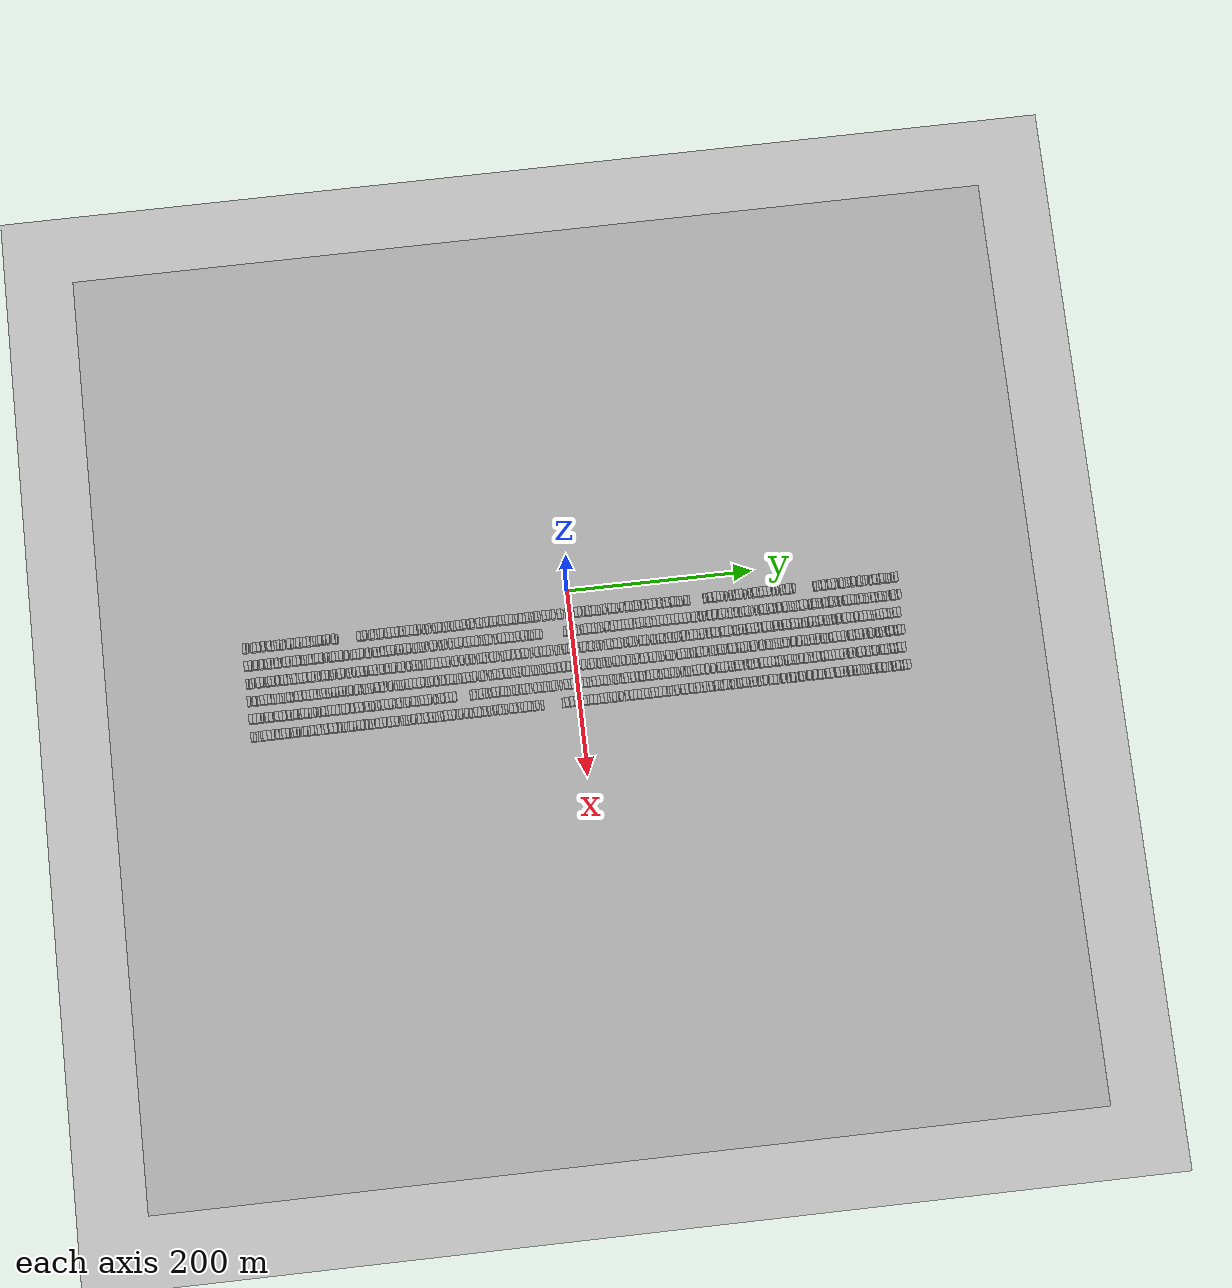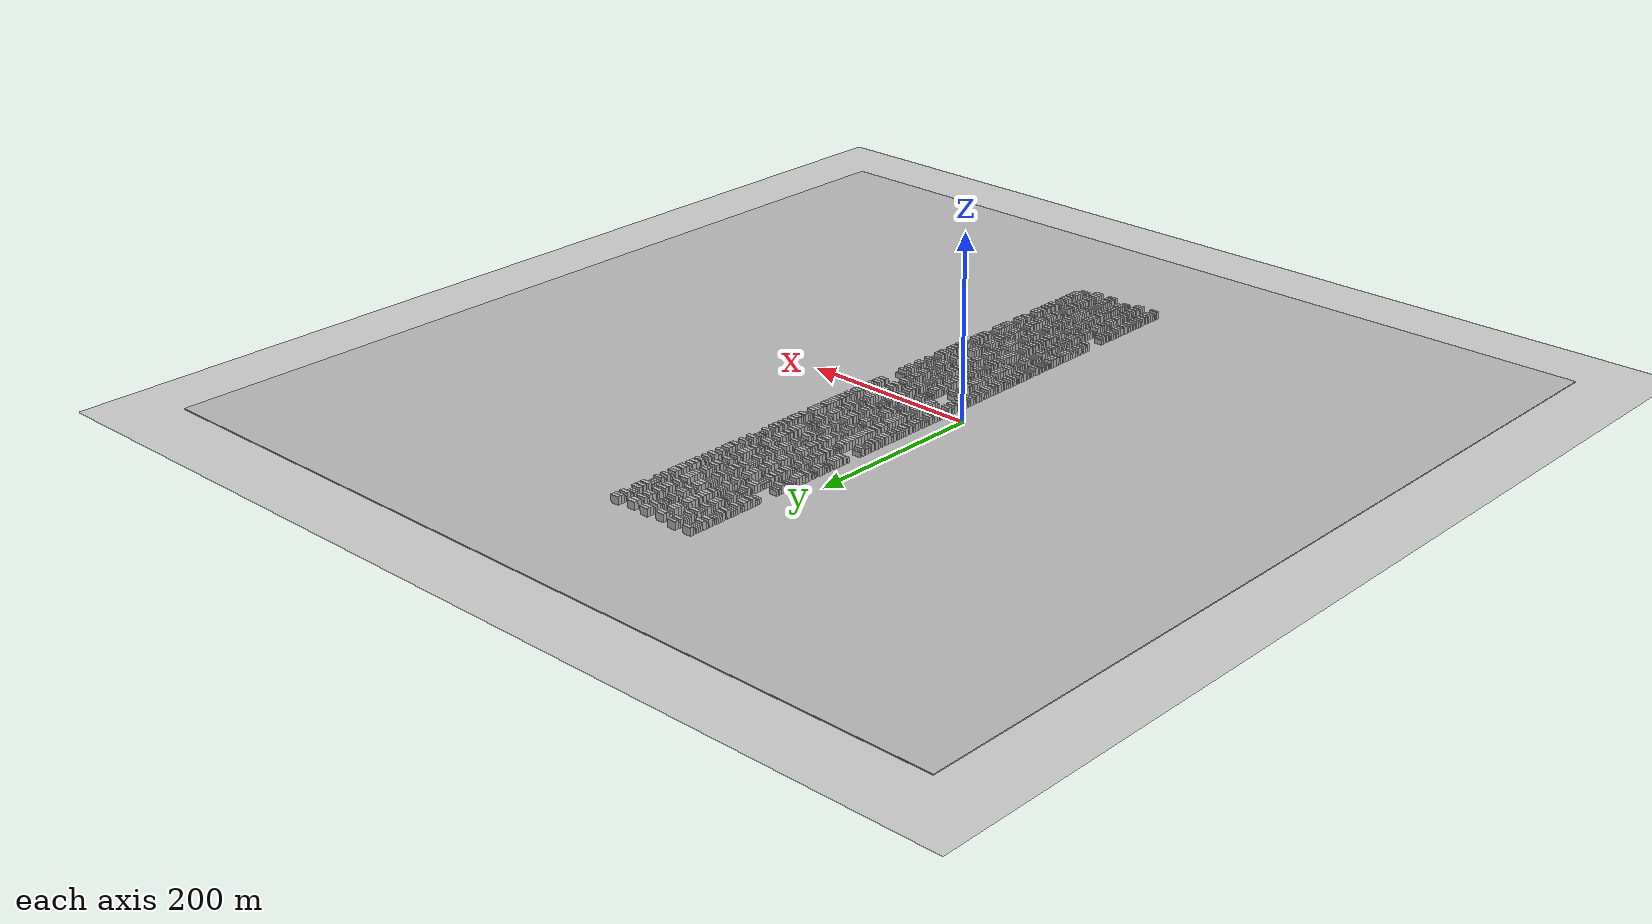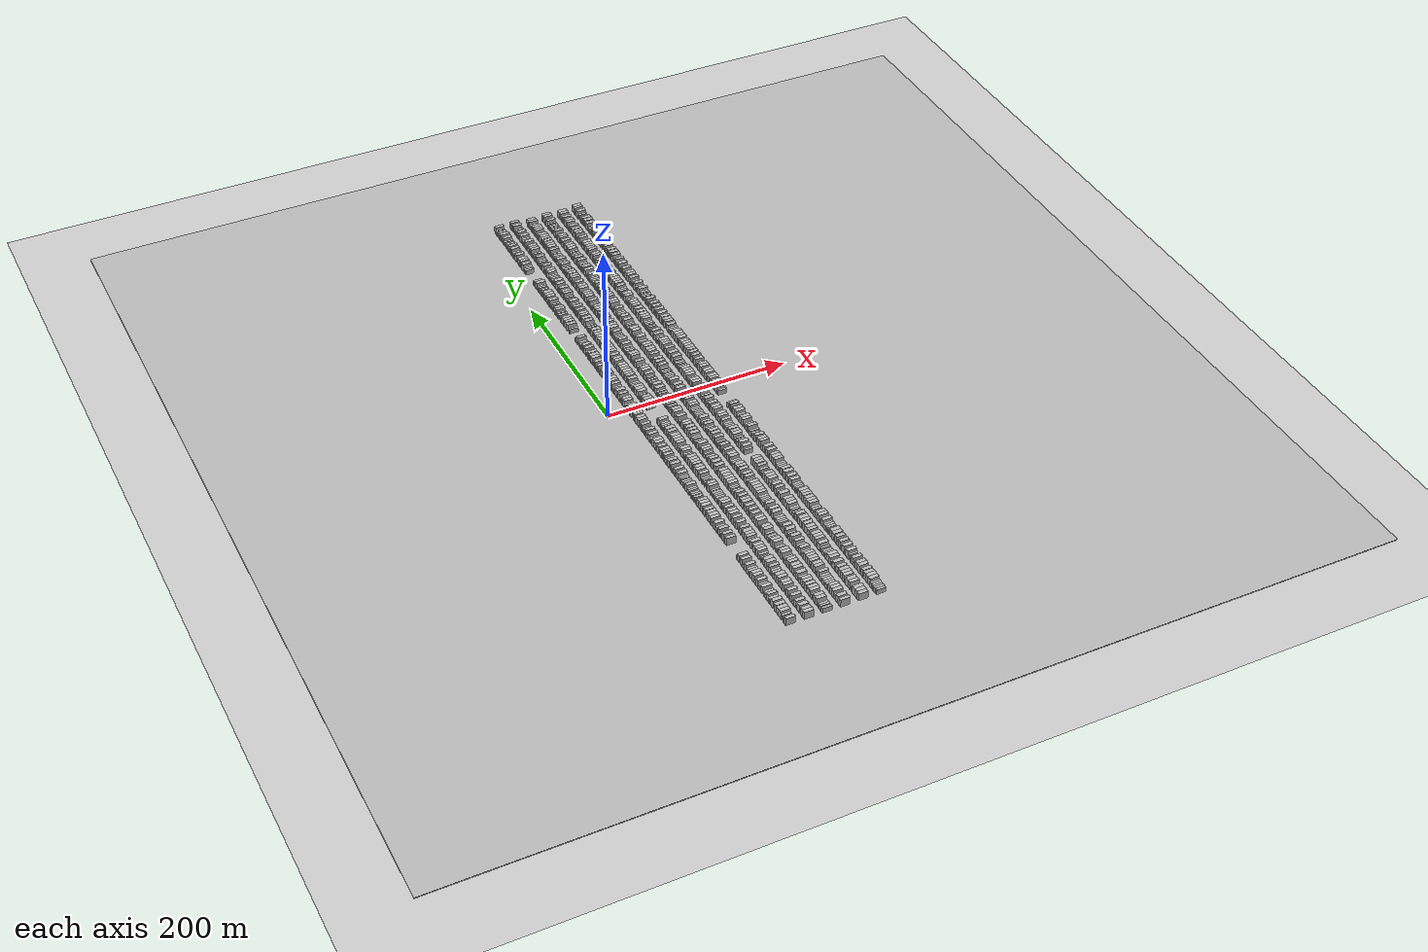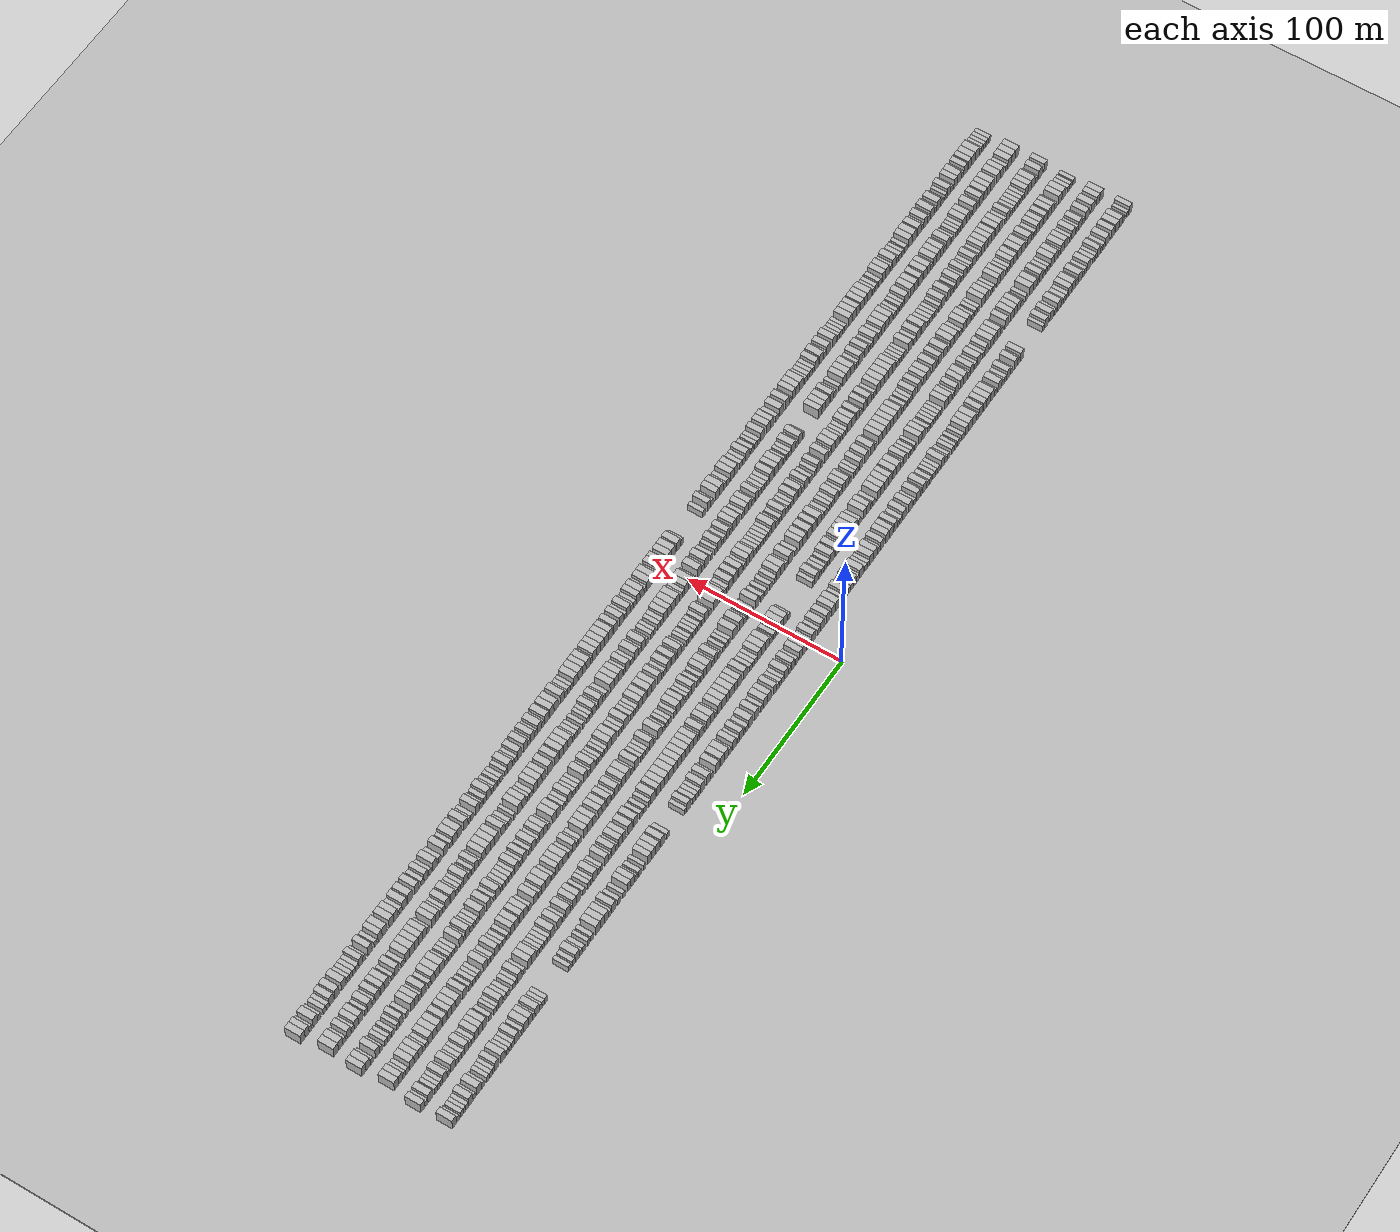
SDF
<?xml version="1.0" encoding="utf-8"?>

<sdf version="1.6">

   <world name="default">

      <gui fullscreen="0">

         <camera name="user_camera">

            <pose>-15 0 4.57585 0 0 0</pose>

            <view_controller>orbit</view_controller>

         </camera>

      </gui>

      <scene>

         <sky>

           <clouds>

             <speed>12</speed>

           </clouds>

         </sky>

         <ambient>0.4 0.4 0.4 1</ambient>

         <background>0.7 0.7 0.7 1</background>

         <shadows>1</shadows>

      </scene>

      <gravity>0 0 -9.8066</gravity>

      <magnetic_field>6e-06 2.3e-05 -4.2e-05</magnetic_field>

      <physics default="0" name="default_physics" type="ode">

         <ode>

            <solver>

               <type>quick</type>

               <iters>10</iters>

               <sor>1.0</sor>

               <use_dynamic_moi_rescaling>0</use_dynamic_moi_rescaling>

            </solver>

            <constraints>

               <cfm>0</cfm>

               <erp>0.2</erp>

               <contact_max_correcting_vel>100</contact_max_correcting_vel>

               <contact_surface_layer>0.001</contact_surface_layer>

            </constraints>

         </ode>

         <max_step_size>0.004</max_step_size>

         <real_time_factor>1</real_time_factor>

         <real_time_update_rate>250</real_time_update_rate>

      </physics>

      <light name="sun" type="directional">

         <cast_shadows>1</cast_shadows>

         <pose>0 0 10 0 0 0</pose>

         <diffuse>0.8 0.8 0.8 1</diffuse>

         <specular>0.2 0.2 0.2 1</specular>

         <attenuation>

            <range>1000</range>

            <constant>0.9</constant>

            <linear>0.01</linear>

            <quadratic>0.001</quadratic>

         </attenuation>

         <direction>-0.5 0.1 -0.9</direction>

      </light>

      <include>

         <name>ground_plane_1</name>

         <uri>model://HANNAS_ground_plane</uri>

         <pose>0 0 0  0 0 0</pose>

      </include>

      <include>

         <name>ground_plane_2</name>

         <uri>model://HANNAS_ground_plane</uri>

         <pose>100 0 0  0 0 0</pose>

      </include>

      <model name="building_1">

         <static>1</static>

         <pose frame="">25.0000 -348.1907 0 0.000000 0.000000 0.000000</pose>

         <link name="link">

            <pose frame="">0 0 4.50 0 0 0</pose>

            <collision name="collision">

               <geometry>

                  <box>

                     <size>10.0000 3.6186 9.0000</size>

                  </box>

               </geometry>

               <max_contacts>10</max_contacts>

               <surface>

                  <contact>

                     <ode/>

                  </contact>

                  <bounce/>

                  <friction>

                     <torsional>

                        <ode/>

                     </torsional>

                     <ode/>

                  </friction>

               </surface>

            </collision>

            <visual name="visual">

               <cast_shadows>0</cast_shadows>

               <geometry>

                  <box>

                     <size>10.0000 3.6186 9.0000</size>

                  </box>

               </geometry>

               <material>

                  <script>

                     <uri>model://HANNAS_wall/materials/scripts</uri>

                     <uri>model://HANNAS_wall/materials/textures</uri>

                     <name>vrc/HANNAS_wall</name>

                  </script>

               </material>

            </visual>

            <self_collide>0</self_collide>

            <enable_wind>0</enable_wind>

            <kinematic>0</kinematic>

         </link>

      </model>

      <model name="building_2">

         <static>1</static>

         <pose frame="">25.0000 -345.1606 0 0.000000 0.000000 0.000000</pose>

         <link name="link">

            <pose frame="">0 0 3.00 0 0 0</pose>

            <collision name="collision">

               <geometry>

                  <box>

                     <size>10.0000 2.4416 6.0000</size>

                  </box>

               </geometry>

               <max_contacts>10</max_contacts>

               <surface>

                  <contact>

                     <ode/>

                  </contact>

                  <bounce/>

                  <friction>

                     <torsional>

                        <ode/>

                     </torsional>

                     <ode/>

                  </friction>

               </surface>

            </collision>

            <visual name="visual">

               <cast_shadows>0</cast_shadows>

               <geometry>

                  <box>

                     <size>10.0000 2.4416 6.0000</size>

                  </box>

               </geometry>

               <material>

                  <script>

                     <uri>model://HANNAS_wall/materials/scripts</uri>

                     <uri>model://HANNAS_wall/materials/textures</uri>

                     <name>vrc/HANNAS_wall</name>

                  </script>

               </material>

            </visual>

            <self_collide>0</self_collide>

            <enable_wind>0</enable_wind>

            <kinematic>0</kinematic>

         </link>

      </model>

      <model name="building_3">

         <static>1</static>

         <pose frame="">25.0000 -340.5947 0 0.000000 0.000000 0.000000</pose>

         <link name="link">

            <pose frame="">0 0 3.00 0 0 0</pose>

            <collision name="collision">

               <geometry>

                  <box>

                     <size>10.0000 2.6903 6.0000</size>

                  </box>

               </geometry>

               <max_contacts>10</max_contacts>

               <surface>

                  <contact>

                     <ode/>

                  </contact>

                  <bounce/>

                  <friction>

                     <torsional>

                        <ode/>

                     </torsional>

                     <ode/>

                  </friction>

               </surface>

            </collision>

            <visual name="visual">

               <cast_shadows>0</cast_shadows>

               <geometry>

                  <box>

                     <size>10.0000 2.6903 6.0000</size>

                  </box>

               </geometry>

               <material>

                  <script>

                     <uri>model://HANNAS_wall/materials/scripts</uri>

                     <uri>model://HANNAS_wall/materials/textures</uri>

                     <name>vrc/HANNAS_wall</name>

                  </script>

               </material>

            </visual>

            <self_collide>0</self_collide>

            <enable_wind>0</enable_wind>

            <kinematic>0</kinematic>

         </link>

      </model>

      <model name="building_4">

         <static>1</static>

         <pose frame="">25.0000 -337.2430 0 0.000000 0.000000 0.000000</pose>

         <link name="link">

            <pose frame="">0 0 4.50 0 0 0</pose>

            <collision name="collision">

               <geometry>

                  <box>

                     <size>10.0000 4.0130 9.0000</size>

                  </box>

               </geometry>

               <max_contacts>10</max_contacts>

               <surface>

                  <contact>

                     <ode/>

                  </contact>

                  <bounce/>

                  <friction>

                     <torsional>

                        <ode/>

                     </torsional>

                     <ode/>

                  </friction>

               </surface>

            </collision>

            <visual name="visual">

               <cast_shadows>0</cast_shadows>

               <geometry>

                  <box>

                     <size>10.0000 4.0130 9.0000</size>

                  </box>

               </geometry>

               <material>

                  <script>

                     <uri>model://HANNAS_wall/materials/scripts</uri>

                     <uri>model://HANNAS_wall/materials/textures</uri>

                     <name>vrc/HANNAS_wall</name>

                  </script>

               </material>

            </visual>

            <self_collide>0</self_collide>

            <enable_wind>0</enable_wind>

            <kinematic>0</kinematic>

         </link>

      </model>

      <model name="building_5">

         <static>1</static>

         <pose frame="">25.0000 -333.1669 0 0.000000 0.000000 0.000000</pose>

         <link name="link">

            <pose frame="">0 0 4.50 0 0 0</pose>

            <collision name="collision">

               <geometry>

                  <box>

                     <size>10.0000 4.1390 9.0000</size>

                  </box>

               </geometry>

               <max_contacts>10</max_contacts>

               <surface>

                  <contact>

                     <ode/>

                  </contact>

                  <bounce/>

                  <friction>

                     <torsional>

                        <ode/>

                     </torsional>

                     <ode/>

                  </friction>

               </surface>

            </collision>

            <visual name="visual">

               <cast_shadows>0</cast_shadows>

               <geometry>

                  <box>

                     <size>10.0000 4.1390 9.0000</size>

                  </box>

               </geometry>

               <material>

                  <script>

                     <uri>model://HANNAS_wall/materials/scripts</uri>

                     <uri>model://HANNAS_wall/materials/textures</uri>

                     <name>vrc/HANNAS_wall</name>

                  </script>

               </material>

            </visual>

            <self_collide>0</self_collide>

            <enable_wind>0</enable_wind>

            <kinematic>0</kinematic>

         </link>

      </model>

      <model name="building_6">

         <static>1</static>

         <pose frame="">25.0000 -328.0562 0 0.000000 0.000000 0.000000</pose>

         <link name="link">

            <pose frame="">0 0 4.50 0 0 0</pose>

            <collision name="collision">

               <geometry>

                  <box>

                     <size>10.0000 4.0825 9.0000</size>

                  </box>

               </geometry>

               <max_contacts>10</max_contacts>

               <surface>

                  <contact>

                     <ode/>

                  </contact>

                  <bounce/>

                  <friction>

                     <torsional>

                        <ode/>

                     </torsional>

                     <ode/>

                  </friction>

               </surface>

            </collision>

            <visual name="visual">

               <cast_shadows>0</cast_shadows>

               <geometry>

                  <box>

                     <size>10.0000 4.0825 9.0000</size>

                  </box>

               </geometry>

               <material>

                  <script>

                     <uri>model://HANNAS_wall/materials/scripts</uri>

                     <uri>model://HANNAS_wall/materials/textures</uri>

                     <name>vrc/HANNAS_wall</name>

                  </script>

               </material>

            </visual>

            <self_collide>0</self_collide>

            <enable_wind>0</enable_wind>

            <kinematic>0</kinematic>

         </link>

      </model>

      <model name="building_7">

         <static>1</static>

         <pose frame="">25.0000 -321.7892 0 0.000000 0.000000 0.000000</pose>

         <link name="link">

            <pose frame="">0 0 4.50 0 0 0</pose>

            <collision name="collision">

               <geometry>

                  <box>

                     <size>10.0000 4.4515 9.0000</size>

                  </box>

               </geometry>

               <max_contacts>10</max_contacts>

               <surface>

                  <contact>

                     <ode/>

                  </contact>

                  <bounce/>

                  <friction>

                     <torsional>

                        <ode/>

                     </torsional>

                     <ode/>

                  </friction>

               </surface>

            </collision>

            <visual name="visual">

               <cast_shadows>0</cast_shadows>

               <geometry>

                  <box>

                     <size>10.0000 4.4515 9.0000</size>

                  </box>

               </geometry>

               <material>

                  <script>

                     <uri>model://HANNAS_wall/materials/scripts</uri>

                     <uri>model://HANNAS_wall/materials/textures</uri>

                     <name>vrc/HANNAS_wall</name>

                  </script>

               </material>

            </visual>

            <self_collide>0</self_collide>

            <enable_wind>0</enable_wind>

            <kinematic>0</kinematic>

         </link>

      </model>

      <model name="building_8">

         <static>1</static>

         <pose frame="">25.0000 -318.2022 0 0.000000 0.000000 0.000000</pose>

         <link name="link">

            <pose frame="">0 0 3.00 0 0 0</pose>

            <collision name="collision">

               <geometry>

                  <box>

                     <size>10.0000 2.7226 6.0000</size>

                  </box>

               </geometry>

               <max_contacts>10</max_contacts>

               <surface>

                  <contact>

                     <ode/>

                  </contact>

                  <bounce/>

                  <friction>

                     <torsional>

                        <ode/>

                     </torsional>

                     <ode/>

                  </friction>

               </surface>

            </collision>

            <visual name="visual">

               <cast_shadows>0</cast_shadows>

               <geometry>

                  <box>

                     <size>10.0000 2.7226 6.0000</size>

                  </box>

               </geometry>

               <material>

                  <script>

                     <uri>model://HANNAS_wall/materials/scripts</uri>

                     <uri>model://HANNAS_wall/materials/textures</uri>

                     <name>vrc/HANNAS_wall</name>

                  </script>

               </material>

            </visual>

            <self_collide>0</self_collide>

            <enable_wind>0</enable_wind>

            <kinematic>0</kinematic>

         </link>

      </model>

      <model name="building_9">

         <static>1</static>

         <pose frame="">25.0000 -315.4016 0 0.000000 0.000000 0.000000</pose>

         <link name="link">

            <pose frame="">0 0 3.00 0 0 0</pose>

            <collision name="collision">

               <geometry>

                  <box>

                     <size>10.0000 2.8787 6.0000</size>

                  </box>

               </geometry>

               <max_contacts>10</max_contacts>

               <surface>

                  <contact>

                     <ode/>

                  </contact>

                  <bounce/>

                  <friction>

                     <torsional>

                        <ode/>

                     </torsional>

                     <ode/>

                  </friction>

               </surface>

            </collision>

            <visual name="visual">

               <cast_shadows>0</cast_shadows>

               <geometry>

                  <box>

                     <size>10.0000 2.8787 6.0000</size>

                  </box>

               </geometry>

               <material>

                  <script>

                     <uri>model://HANNAS_wall/materials/scripts</uri>

                     <uri>model://HANNAS_wall/materials/textures</uri>

                     <name>vrc/HANNAS_wall</name>

                  </script>

               </material>

            </visual>

            <self_collide>0</self_collide>

            <enable_wind>0</enable_wind>

            <kinematic>0</kinematic>

         </link>

      </model>

      <model name="building_10">

         <static>1</static>

         <pose frame="">25.0000 -312.1245 0 0.000000 0.000000 0.000000</pose>

         <link name="link">

            <pose frame="">0 0 4.50 0 0 0</pose>

            <collision name="collision">

               <geometry>

                  <box>

                     <size>10.0000 3.6753 9.0000</size>

                  </box>

               </geometry>

               <max_contacts>10</max_contacts>

               <surface>

                  <contact>

                     <ode/>

                  </contact>

                  <bounce/>

                  <friction>

                     <torsional>

                        <ode/>

                     </torsional>

                     <ode/>

                  </friction>

               </surface>

            </collision>

            <visual name="visual">

               <cast_shadows>0</cast_shadows>

               <geometry>

                  <box>

                     <size>10.0000 3.6753 9.0000</size>

                  </box>

               </geometry>

               <material>

                  <script>

                     <uri>model://HANNAS_wall/materials/scripts</uri>

                     <uri>model://HANNAS_wall/materials/textures</uri>

                     <name>vrc/HANNAS_wall</name>

                  </script>

               </material>

            </visual>

            <self_collide>0</self_collide>

            <enable_wind>0</enable_wind>

            <kinematic>0</kinematic>

         </link>

      </model>

      <model name="building_11">

         <static>1</static>

         <pose frame="">25.0000 -309.0250 0 0.000000 0.000000 0.000000</pose>

         <link name="link">

            <pose frame="">0 0 3.00 0 0 0</pose>

            <collision name="collision">

               <geometry>

                  <box>

                     <size>10.0000 2.5237 6.0000</size>

                  </box>

               </geometry>

               <max_contacts>10</max_contacts>

               <surface>

                  <contact>

                     <ode/>

                  </contact>

                  <bounce/>

                  <friction>

                     <torsional>

                        <ode/>

                     </torsional>

                     <ode/>

                  </friction>

               </surface>

            </collision>

            <visual name="visual">

               <cast_shadows>0</cast_shadows>

               <geometry>

                  <box>

                     <size>10.0000 2.5237 6.0000</size>

                  </box>

               </geometry>

               <material>

                  <script>

                     <uri>model://HANNAS_wall/materials/scripts</uri>

                     <uri>model://HANNAS_wall/materials/textures</uri>

                     <name>vrc/HANNAS_wall</name>

                  </script>

               </material>

            </visual>

            <self_collide>0</self_collide>

            <enable_wind>0</enable_wind>

            <kinematic>0</kinematic>

         </link>

      </model>

      <model name="building_12">

         <static>1</static>

         <pose frame="">25.0000 -306.3264 0 0.000000 0.000000 0.000000</pose>

         <link name="link">

            <pose frame="">0 0 3.00 0 0 0</pose>

            <collision name="collision">

               <geometry>

                  <box>

                     <size>10.0000 2.8734 6.0000</size>

                  </box>

               </geometry>

               <max_contacts>10</max_contacts>

               <surface>

                  <contact>

                     <ode/>

                  </contact>

                  <bounce/>

                  <friction>

                     <torsional>

                        <ode/>

                     </torsional>

                     <ode/>

                  </friction>

               </surface>

            </collision>

            <visual name="visual">

               <cast_shadows>0</cast_shadows>

               <geometry>

                  <box>

                     <size>10.0000 2.8734 6.0000</size>

                  </box>

               </geometry>

               <material>

                  <script>

                     <uri>model://HANNAS_wall/materials/scripts</uri>

                     <uri>model://HANNAS_wall/materials/textures</uri>

                     <name>vrc/HANNAS_wall</name>

                  </script>

               </material>

            </visual>

            <self_collide>0</self_collide>

            <enable_wind>0</enable_wind>

            <kinematic>0</kinematic>

         </link>

      </model>

      <model name="building_13">

         <static>1</static>

         <pose frame="">25.0000 -300.7905 0 0.000000 0.000000 0.000000</pose>

         <link name="link">

            <pose frame="">0 0 4.50 0 0 0</pose>

            <collision name="collision">

               <geometry>

                  <box>

                     <size>10.0000 4.1984 9.0000</size>

                  </box>

               </geometry>

               <max_contacts>10</max_contacts>

               <surface>

                  <contact>

                     <ode/>

                  </contact>

                  <bounce/>

                  <friction>

                     <torsional>

                        <ode/>

                     </torsional>

                     <ode/>

                  </friction>

               </surface>

            </collision>

            <visual name="visual">

               <cast_shadows>0</cast_shadows>

               <geometry>

                  <box>

                     <size>10.0000 4.1984 9.0000</size>

                  </box>

               </geometry>

               <material>

                  <script>

                     <uri>model://HANNAS_wall/materials/scripts</uri>

                     <uri>model://HANNAS_wall/materials/textures</uri>

                     <name>vrc/HANNAS_wall</name>

                  </script>

               </material>

            </visual>

            <self_collide>0</self_collide>

            <enable_wind>0</enable_wind>

            <kinematic>0</kinematic>

         </link>

      </model>

      <model name="building_14">

         <static>1</static>

         <pose frame="">25.0000 -297.3987 0 0.000000 0.000000 0.000000</pose>

         <link name="link">

            <pose frame="">0 0 3.00 0 0 0</pose>

            <collision name="collision">

               <geometry>

                  <box>

                     <size>10.0000 2.5852 6.0000</size>

                  </box>

               </geometry>

               <max_contacts>10</max_contacts>

               <surface>

                  <contact>

                     <ode/>

                  </contact>

                  <bounce/>

                  <friction>

                     <torsional>

                        <ode/>

                     </torsional>

                     <ode/>

                  </friction>

               </surface>

            </collision>

            <visual name="visual">

               <cast_shadows>0</cast_shadows>

               <geometry>

                  <box>

                     <size>10.0000 2.5852 6.0000</size>

                  </box>

               </geometry>

               <material>

                  <script>

                     <uri>model://HANNAS_wall/materials/scripts</uri>

                     <uri>model://HANNAS_wall/materials/textures</uri>

                     <name>vrc/HANNAS_wall</name>

                  </script>

               </material>

            </visual>

            <self_collide>0</self_collide>

            <enable_wind>0</enable_wind>

            <kinematic>0</kinematic>

         </link>

      </model>

      <model name="building_15">

         <static>1</static>

         <pose frame="">25.0000 -294.6609 0 0.000000 0.000000 0.000000</pose>

         <link name="link">

            <pose frame="">0 0 3.00 0 0 0</pose>

            <collision name="collision">

               <geometry>

                  <box>

                     <size>10.0000 2.8902 6.0000</size>

                  </box>

               </geometry>

               <max_contacts>10</max_contacts>

               <surface>

                  <contact>

                     <ode/>

                  </contact>

                  <bounce/>

                  <friction>

                     <torsional>

                        <ode/>

                     </torsional>

                     <ode/>

                  </friction>

               </surface>

            </collision>

            <visual name="visual">

               <cast_shadows>0</cast_shadows>

               <geometry>

                  <box>

                     <size>10.0000 2.8902 6.0000</size>

                  </box>

               </geometry>

               <material>

                  <script>

                     <uri>model://HANNAS_wall/materials/scripts</uri>

                     <uri>model://HANNAS_wall/materials/textures</uri>

                     <name>vrc/HANNAS_wall</name>

                  </script>

               </material>

            </visual>

            <self_collide>0</self_collide>

            <enable_wind>0</enable_wind>

            <kinematic>0</kinematic>

         </link>

      </model>

      <model name="building_16">

         <static>1</static>

         <pose frame="">25.0000 -291.0888 0 0.000000 0.000000 0.000000</pose>

         <link name="link">

            <pose frame="">0 0 4.50 0 0 0</pose>

            <collision name="collision">

               <geometry>

                  <box>

                     <size>10.0000 4.2540 9.0000</size>

                  </box>

               </geometry>

               <max_contacts>10</max_contacts>

               <surface>

                  <contact>

                     <ode/>

                  </contact>

                  <bounce/>

                  <friction>

                     <torsional>

                        <ode/>

                     </torsional>

                     <ode/>

                  </friction>

               </surface>

            </collision>

            <visual name="visual">

               <cast_shadows>0</cast_shadows>

               <geometry>

                  <box>

                     <size>10.0000 4.2540 9.0000</size>

                  </box>

               </geometry>

               <material>

                  <script>

                     <uri>model://HANNAS_wall/materials/scripts</uri>

                     <uri>model://HANNAS_wall/materials/textures</uri>

                     <name>vrc/HANNAS_wall</name>

                  </script>

               </material>

            </visual>

            <self_collide>0</self_collide>

            <enable_wind>0</enable_wind>

            <kinematic>0</kinematic>

         </link>

      </model>

      <model name="building_17">

         <static>1</static>

         <pose frame="">25.0000 -287.4622 0 0.000000 0.000000 0.000000</pose>

         <link name="link">

            <pose frame="">0 0 3.00 0 0 0</pose>

            <collision name="collision">

               <geometry>

                  <box>

                     <size>10.0000 2.9994 6.0000</size>

                  </box>

               </geometry>

               <max_contacts>10</max_contacts>

               <surface>

                  <contact>

                     <ode/>

                  </contact>

                  <bounce/>

                  <friction>

                     <torsional>

                        <ode/>

                     </torsional>

                     <ode/>

                  </friction>

               </surface>

            </collision>

            <visual name="visual">

               <cast_shadows>0</cast_shadows>

               <geometry>

                  <box>

                     <size>10.0000 2.9994 6.0000</size>

                  </box>

               </geometry>

               <material>

                  <script>

                     <uri>model://HANNAS_wall/materials/scripts</uri>

                     <uri>model://HANNAS_wall/materials/textures</uri>

                     <name>vrc/HANNAS_wall</name>

                  </script>

               </material>

            </visual>

            <self_collide>0</self_collide>

            <enable_wind>0</enable_wind>

            <kinematic>0</kinematic>

         </link>

      </model>

      <model name="building_18">

         <static>1</static>

         <pose frame="">25.0000 -283.9113 0 0.000000 0.000000 0.000000</pose>

         <link name="link">

            <pose frame="">0 0 4.50 0 0 0</pose>

            <collision name="collision">

               <geometry>

                  <box>

                     <size>10.0000 4.1024 9.0000</size>

                  </box>

               </geometry>

               <max_contacts>10</max_contacts>

               <surface>

                  <contact>

                     <ode/>

                  </contact>

                  <bounce/>

                  <friction>

                     <torsional>

                        <ode/>

                     </torsional>

                     <ode/>

                  </friction>

               </surface>

            </collision>

            <visual name="visual">

               <cast_shadows>0</cast_shadows>

               <geometry>

                  <box>

                     <size>10.0000 4.1024 9.0000</size>

                  </box>

               </geometry>

               <material>

                  <script>

                     <uri>model://HANNAS_wall/materials/scripts</uri>

                     <uri>model://HANNAS_wall/materials/textures</uri>

                     <name>vrc/HANNAS_wall</name>

                  </script>

               </material>

            </visual>

            <self_collide>0</self_collide>

            <enable_wind>0</enable_wind>

            <kinematic>0</kinematic>

         </link>

      </model>

      <model name="building_19">

         <static>1</static>

         <pose frame="">25.0000 -279.8644 0 0.000000 0.000000 0.000000</pose>

         <link name="link">

            <pose frame="">0 0 4.50 0 0 0</pose>

            <collision name="collision">

               <geometry>

                  <box>

                     <size>10.0000 3.9914 9.0000</size>

                  </box>

               </geometry>

               <max_contacts>10</max_contacts>

               <surface>

                  <contact>

                     <ode/>

                  </contact>

                  <bounce/>

                  <friction>

                     <torsional>

                        <ode/>

                     </torsional>

                     <ode/>

                  </friction>

               </surface>

            </collision>

            <visual name="visual">

               <cast_shadows>0</cast_shadows>

               <geometry>

                  <box>

                     <size>10.0000 3.9914 9.0000</size>

                  </box>

               </geometry>

               <material>

                  <script>

                     <uri>model://HANNAS_wall/materials/scripts</uri>

                     <uri>model://HANNAS_wall/materials/textures</uri>

                     <name>vrc/HANNAS_wall</name>

                  </script>

               </material>

            </visual>

            <self_collide>0</self_collide>

            <enable_wind>0</enable_wind>

            <kinematic>0</kinematic>

         </link>

      </model>

      <model name="building_20">

         <static>1</static>

         <pose frame="">25.0000 -276.5070 0 0.000000 0.000000 0.000000</pose>

         <link name="link">

            <pose frame="">0 0 3.00 0 0 0</pose>

            <collision name="collision">

               <geometry>

                  <box>

                     <size>10.0000 2.7232 6.0000</size>

                  </box>

               </geometry>

               <max_contacts>10</max_contacts>

               <surface>

                  <contact>

                     <ode/>

                  </contact>

                  <bounce/>

                  <friction>

                     <torsional>

                        <ode/>

                     </torsional>

                     <ode/>

                  </friction>

               </surface>

            </collision>

            <visual name="visual">

               <cast_shadows>0</cast_shadows>

               <geometry>

                  <box>

                     <size>10.0000 2.7232 6.0000</size>

                  </box>

               </geometry>

               <material>

                  <script>

                     <uri>model://HANNAS_wall/materials/scripts</uri>

                     <uri>model://HANNAS_wall/materials/textures</uri>

                     <name>vrc/HANNAS_wall</name>

                  </script>

               </material>

            </visual>

            <self_collide>0</self_collide>

            <enable_wind>0</enable_wind>

            <kinematic>0</kinematic>

         </link>

      </model>

      <model name="building_21">

         <static>1</static>

         <pose frame="">25.0000 -273.6886 0 0.000000 0.000000 0.000000</pose>

         <link name="link">

            <pose frame="">0 0 3.00 0 0 0</pose>

            <collision name="collision">

               <geometry>

                  <box>

                     <size>10.0000 2.9136 6.0000</size>

                  </box>

               </geometry>

               <max_contacts>10</max_contacts>

               <surface>

                  <contact>

                     <ode/>

                  </contact>

                  <bounce/>

                  <friction>

                     <torsional>

                        <ode/>

                     </torsional>

                     <ode/>

                  </friction>

               </surface>

            </collision>

            <visual name="visual">

               <cast_shadows>0</cast_shadows>

               <geometry>

                  <box>

                     <size>10.0000 2.9136 6.0000</size>

                  </box>

               </geometry>

               <material>

                  <script>

                     <uri>model://HANNAS_wall/materials/scripts</uri>

                     <uri>model://HANNAS_wall/materials/textures</uri>

                     <name>vrc/HANNAS_wall</name>

                  </script>

               </material>

            </visual>

            <self_collide>0</self_collide>

            <enable_wind>0</enable_wind>

            <kinematic>0</kinematic>

         </link>

      </model>

      <model name="building_22">

         <static>1</static>

         <pose frame="">25.0000 -270.9212 0 0.000000 0.000000 0.000000</pose>

         <link name="link">

            <pose frame="">0 0 3.00 0 0 0</pose>

            <collision name="collision">

               <geometry>

                  <box>

                     <size>10.0000 2.6211 6.0000</size>

                  </box>

               </geometry>

               <max_contacts>10</max_contacts>

               <surface>

                  <contact>

                     <ode/>

                  </contact>

                  <bounce/>

                  <friction>

                     <torsional>

                        <ode/>

                     </torsional>

                     <ode/>

                  </friction>

               </surface>

            </collision>

            <visual name="visual">

               <cast_shadows>0</cast_shadows>

               <geometry>

                  <box>

                     <size>10.0000 2.6211 6.0000</size>

                  </box>

               </geometry>

               <material>

                  <script>

                     <uri>model://HANNAS_wall/materials/scripts</uri>

                     <uri>model://HANNAS_wall/materials/textures</uri>

                     <name>vrc/HANNAS_wall</name>

                  </script>

               </material>

            </visual>

            <self_collide>0</self_collide>

            <enable_wind>0</enable_wind>

            <kinematic>0</kinematic>

         </link>

      </model>

      <model name="building_23">

         <static>1</static>

         <pose frame="">25.0000 -267.5183 0 0.000000 0.000000 0.000000</pose>

         <link name="link">

            <pose frame="">0 0 4.50 0 0 0</pose>

            <collision name="collision">

               <geometry>

                  <box>

                     <size>10.0000 4.1848 9.0000</size>

                  </box>

               </geometry>

               <max_contacts>10</max_contacts>

               <surface>

                  <contact>

                     <ode/>

                  </contact>

                  <bounce/>

                  <friction>

                     <torsional>

                        <ode/>

                     </torsional>

                     <ode/>

                  </friction>

               </surface>

            </collision>

            <visual name="visual">

               <cast_shadows>0</cast_shadows>

               <geometry>

                  <box>

                     <size>10.0000 4.1848 9.0000</size>

                  </box>

               </geometry>

               <material>

                  <script>

                     <uri>model://HANNAS_wall/materials/scripts</uri>

                     <uri>model://HANNAS_wall/materials/textures</uri>

                     <name>vrc/HANNAS_wall</name>

                  </script>

               </material>

            </visual>

            <self_collide>0</self_collide>

            <enable_wind>0</enable_wind>

            <kinematic>0</kinematic>

         </link>

      </model>

      <model name="building_24">

         <static>1</static>

         <pose frame="">25.0000 -263.1053 0 0.000000 0.000000 0.000000</pose>

         <link name="link">

            <pose frame="">0 0 3.00 0 0 0</pose>

            <collision name="collision">

               <geometry>

                  <box>

                     <size>10.0000 2.6412 6.0000</size>

                  </box>

               </geometry>

               <max_contacts>10</max_contacts>

               <surface>

                  <contact>

                     <ode/>

                  </contact>

                  <bounce/>

                  <friction>

                     <torsional>

                        <ode/>

                     </torsional>

                     <ode/>

                  </friction>

               </surface>

            </collision>

            <visual name="visual">

               <cast_shadows>0</cast_shadows>

               <geometry>

                  <box>

                     <size>10.0000 2.6412 6.0000</size>

                  </box>

               </geometry>

               <material>

                  <script>

                     <uri>model://HANNAS_wall/materials/scripts</uri>

                     <uri>model://HANNAS_wall/materials/textures</uri>

                     <name>vrc/HANNAS_wall</name>

                  </script>

               </material>

            </visual>

            <self_collide>0</self_collide>

            <enable_wind>0</enable_wind>

            <kinematic>0</kinematic>

         </link>

      </model>

      <model name="building_25">

         <static>1</static>

         <pose frame="">25.0000 -258.9148 0 0.000000 0.000000 0.000000</pose>

         <link name="link">

            <pose frame="">0 0 4.50 0 0 0</pose>

            <collision name="collision">

               <geometry>

                  <box>

                     <size>10.0000 3.7397 9.0000</size>

                  </box>

               </geometry>

               <max_contacts>10</max_contacts>

               <surface>

                  <contact>

                     <ode/>

                  </contact>

                  <bounce/>

                  <friction>

                     <torsional>

                        <ode/>

                     </torsional>

                     <ode/>

                  </friction>

               </surface>

            </collision>

            <visual name="visual">

               <cast_shadows>0</cast_shadows>

               <geometry>

                  <box>

                     <size>10.0000 3.7397 9.0000</size>

                  </box>

               </geometry>

               <material>

                  <script>

                     <uri>model://HANNAS_wall/materials/scripts</uri>

                     <uri>model://HANNAS_wall/materials/textures</uri>

                     <name>vrc/HANNAS_wall</name>

                  </script>

               </material>

            </visual>

            <self_collide>0</self_collide>

            <enable_wind>0</enable_wind>

            <kinematic>0</kinematic>

         </link>

      </model>

      <model name="building_26">

         <static>1</static>

         <pose frame="">25.0000 -253.1585 0 0.000000 0.000000 0.000000</pose>

         <link name="link">

            <pose frame="">0 0 4.50 0 0 0</pose>

            <collision name="collision">

               <geometry>

                  <box>

                     <size>10.0000 3.7730 9.0000</size>

                  </box>

               </geometry>

               <max_contacts>10</max_contacts>

               <surface>

                  <contact>

                     <ode/>

                  </contact>

                  <bounce/>

                  <friction>

                     <torsional>

                        <ode/>

                     </torsional>

                     <ode/>

                  </friction>

               </surface>

            </collision>

            <visual name="visual">

               <cast_shadows>0</cast_shadows>

               <geometry>

                  <box>

                     <size>10.0000 3.7730 9.0000</size>

                  </box>

               </geometry>

               <material>

                  <script>

                     <uri>model://HANNAS_wall/materials/scripts</uri>

                     <uri>model://HANNAS_wall/materials/textures</uri>

                     <name>vrc/HANNAS_wall</name>

                  </script>

               </material>

            </visual>

            <self_collide>0</self_collide>

            <enable_wind>0</enable_wind>

            <kinematic>0</kinematic>

         </link>

      </model>

      <model name="building_27">

         <static>1</static>

         <pose frame="">25.0000 -250.0536 0 0.000000 0.000000 0.000000</pose>

         <link name="link">

            <pose frame="">0 0 3.00 0 0 0</pose>

            <collision name="collision">

               <geometry>

                  <box>

                     <size>10.0000 2.4368 6.0000</size>

                  </box>

               </geometry>

               <max_contacts>10</max_contacts>

               <surface>

                  <contact>

                     <ode/>

                  </contact>

                  <bounce/>

                  <friction>

                     <torsional>

                        <ode/>

                     </torsional>

                     <ode/>

                  </friction>

               </surface>

            </collision>

            <visual name="visual">

               <cast_shadows>0</cast_shadows>

               <geometry>

                  <box>

                     <size>10.0000 2.4368 6.0000</size>

                  </box>

               </geometry>

               <material>

                  <script>

                     <uri>model://HANNAS_wall/materials/scripts</uri>

                     <uri>model://HANNAS_wall/materials/textures</uri>

                     <name>vrc/HANNAS_wall</name>

                  </script>

               </material>

            </visual>

            <self_collide>0</self_collide>

            <enable_wind>0</enable_wind>

            <kinematic>0</kinematic>

         </link>

      </model>

      <model name="building_28">

         <static>1</static>

         <pose frame="">25.0000 -226.0626 0 0.000000 0.000000 0.000000</pose>

         <link name="link">

            <pose frame="">0 0 4.50 0 0 0</pose>

            <collision name="collision">

               <geometry>

                  <box>

                     <size>10.0000 3.8484 9.0000</size>

                  </box>

               </geometry>

               <max_contacts>10</max_contacts>

               <surface>

                  <contact>

                     <ode/>

                  </contact>

                  <bounce/>

                  <friction>

                     <torsional>

                        <ode/>

                     </torsional>

                     <ode/>

                  </friction>

               </surface>

            </collision>

            <visual name="visual">

               <cast_shadows>0</cast_shadows>

               <geometry>

                  <box>

                     <size>10.0000 3.8484 9.0000</size>

                  </box>

               </geometry>

               <material>

                  <script>

                     <uri>model://HANNAS_wall/materials/scripts</uri>

                     <uri>model://HANNAS_wall/materials/textures</uri>

                     <name>vrc/HANNAS_wall</name>

                  </script>

               </material>

            </visual>

            <self_collide>0</self_collide>

            <enable_wind>0</enable_wind>

            <kinematic>0</kinematic>

         </link>

      </model>

      <model name="building_29">

         <static>1</static>

         <pose frame="">25.0000 -222.7465 0 0.000000 0.000000 0.000000</pose>

         <link name="link">

            <pose frame="">0 0 3.00 0 0 0</pose>

            <collision name="collision">

               <geometry>

                  <box>

                     <size>10.0000 2.7838 6.0000</size>

                  </box>

               </geometry>

               <max_contacts>10</max_contacts>

               <surface>

                  <contact>

                     <ode/>

                  </contact>

                  <bounce/>

                  <friction>

                     <torsional>

                        <ode/>

                     </torsional>

                     <ode/>

                  </friction>

               </surface>

            </collision>

            <visual name="visual">

               <cast_shadows>0</cast_shadows>

               <geometry>

                  <box>

                     <size>10.0000 2.7838 6.0000</size>

                  </box>

               </geometry>

               <material>

                  <script>

                     <uri>model://HANNAS_wall/materials/scripts</uri>

                     <uri>model://HANNAS_wall/materials/textures</uri>

                     <name>vrc/HANNAS_wall</name>

                  </script>

               </material>

            </visual>

            <self_collide>0</self_collide>

            <enable_wind>0</enable_wind>

            <kinematic>0</kinematic>

         </link>

      </model>

      <model name="building_30">

         <static>1</static>

         <pose frame="">25.0000 -219.5177 0 0.000000 0.000000 0.000000</pose>

         <link name="link">

            <pose frame="">0 0 4.50 0 0 0</pose>

            <collision name="collision">

               <geometry>

                  <box>

                     <size>10.0000 3.6739 9.0000</size>

                  </box>

               </geometry>

               <max_contacts>10</max_contacts>

               <surface>

                  <contact>

                     <ode/>

                  </contact>

                  <bounce/>

                  <friction>

                     <torsional>

                        <ode/>

                     </torsional>

                     <ode/>

                  </friction>

               </surface>

            </collision>

            <visual name="visual">

               <cast_shadows>0</cast_shadows>

               <geometry>

                  <box>

                     <size>10.0000 3.6739 9.0000</size>

                  </box>

               </geometry>

               <material>

                  <script>

                     <uri>model://HANNAS_wall/materials/scripts</uri>

                     <uri>model://HANNAS_wall/materials/textures</uri>

                     <name>vrc/HANNAS_wall</name>

                  </script>

               </material>

            </visual>

            <self_collide>0</self_collide>

            <enable_wind>0</enable_wind>

            <kinematic>0</kinematic>

         </link>

      </model>

      <model name="building_31">

         <static>1</static>

         <pose frame="">25.0000 -214.4132 0 0.000000 0.000000 0.000000</pose>

         <link name="link">

            <pose frame="">0 0 3.00 0 0 0</pose>

            <collision name="collision">

               <geometry>

                  <box>

                     <size>10.0000 2.5351 6.0000</size>

                  </box>

               </geometry>

               <max_contacts>10</max_contacts>

               <surface>

                  <contact>

                     <ode/>

                  </contact>

                  <bounce/>

                  <friction>

                     <torsional>

                        <ode/>

                     </torsional>

                     <ode/>

                  </friction>

               </surface>

            </collision>

            <visual name="visual">

               <cast_shadows>0</cast_shadows>

               <geometry>

                  <box>

                     <size>10.0000 2.5351 6.0000</size>

                  </box>

               </geometry>

               <material>

                  <script>

                     <uri>model://HANNAS_wall/materials/scripts</uri>

                     <uri>model://HANNAS_wall/materials/textures</uri>

                     <name>vrc/HANNAS_wall</name>

                  </script>

               </material>

            </visual>

            <self_collide>0</self_collide>

            <enable_wind>0</enable_wind>

            <kinematic>0</kinematic>

         </link>

      </model>

      <model name="building_32">

         <static>1</static>

         <pose frame="">25.0000 -211.2157 0 0.000000 0.000000 0.000000</pose>

         <link name="link">

            <pose frame="">0 0 4.50 0 0 0</pose>

            <collision name="collision">

               <geometry>

                  <box>

                     <size>10.0000 3.8600 9.0000</size>

                  </box>

               </geometry>

               <max_contacts>10</max_contacts>

               <surface>

                  <contact>

                     <ode/>

                  </contact>

                  <bounce/>

                  <friction>

                     <torsional>

                        <ode/>

                     </torsional>

                     <ode/>

                  </friction>

               </surface>

            </collision>

            <visual name="visual">

               <cast_shadows>0</cast_shadows>

               <geometry>

                  <box>

                     <size>10.0000 3.8600 9.0000</size>

                  </box>

               </geometry>

               <material>

                  <script>

                     <uri>model://HANNAS_wall/materials/scripts</uri>

                     <uri>model://HANNAS_wall/materials/textures</uri>

                     <name>vrc/HANNAS_wall</name>

                  </script>

               </material>

            </visual>

            <self_collide>0</self_collide>

            <enable_wind>0</enable_wind>

            <kinematic>0</kinematic>

         </link>

      </model>

      <model name="building_33">

         <static>1</static>

         <pose frame="">25.0000 -207.9436 0 0.000000 0.000000 0.000000</pose>

         <link name="link">

            <pose frame="">0 0 3.00 0 0 0</pose>

            <collision name="collision">

               <geometry>

                  <box>

                     <size>10.0000 2.6841 6.0000</size>

                  </box>

               </geometry>

               <max_contacts>10</max_contacts>

               <surface>

                  <contact>

                     <ode/>

                  </contact>

                  <bounce/>

                  <friction>

                     <torsional>

                        <ode/>

                     </torsional>

                     <ode/>

                  </friction>

               </surface>

            </collision>

            <visual name="visual">

               <cast_shadows>0</cast_shadows>

               <geometry>

                  <box>

                     <size>10.0000 2.6841 6.0000</size>

                  </box>

               </geometry>

               <material>

                  <script>

                     <uri>model://HANNAS_wall/materials/scripts</uri>

                     <uri>model://HANNAS_wall/materials/textures</uri>

                     <name>vrc/HANNAS_wall</name>

                  </script>

               </material>

            </visual>

            <self_collide>0</self_collide>

            <enable_wind>0</enable_wind>

            <kinematic>0</kinematic>

         </link>

      </model>

      <model name="building_34">

         <static>1</static>

         <pose frame="">25.0000 -205.1876 0 0.000000 0.000000 0.000000</pose>

         <link name="link">

            <pose frame="">0 0 3.00 0 0 0</pose>

            <collision name="collision">

               <geometry>

                  <box>

                     <size>10.0000 2.8280 6.0000</size>

                  </box>

               </geometry>

               <max_contacts>10</max_contacts>

               <surface>

                  <contact>

                     <ode/>

                  </contact>

                  <bounce/>

                  <friction>

                     <torsional>

                        <ode/>

                     </torsional>

                     <ode/>

                  </friction>

               </surface>

            </collision>

            <visual name="visual">

               <cast_shadows>0</cast_shadows>

               <geometry>

                  <box>

                     <size>10.0000 2.8280 6.0000</size>

                  </box>

               </geometry>

               <material>

                  <script>

                     <uri>model://HANNAS_wall/materials/scripts</uri>

                     <uri>model://HANNAS_wall/materials/textures</uri>

                     <name>vrc/HANNAS_wall</name>

                  </script>

               </material>

            </visual>

            <self_collide>0</self_collide>

            <enable_wind>0</enable_wind>

            <kinematic>0</kinematic>

         </link>

      </model>

      <model name="building_35">

         <static>1</static>

         <pose frame="">25.0000 -201.5887 0 0.000000 0.000000 0.000000</pose>

         <link name="link">

            <pose frame="">0 0 4.50 0 0 0</pose>

            <collision name="collision">

               <geometry>

                  <box>

                     <size>10.0000 4.3697 9.0000</size>

                  </box>

               </geometry>

               <max_contacts>10</max_contacts>

               <surface>

                  <contact>

                     <ode/>

                  </contact>

                  <bounce/>

                  <friction>

                     <torsional>

                        <ode/>

                     </torsional>

                     <ode/>

                  </friction>

               </surface>

            </collision>

            <visual name="visual">

               <cast_shadows>0</cast_shadows>

               <geometry>

                  <box>

                     <size>10.0000 4.3697 9.0000</size>

                  </box>

               </geometry>

               <material>

                  <script>

                     <uri>model://HANNAS_wall/materials/scripts</uri>

                     <uri>model://HANNAS_wall/materials/textures</uri>

                     <name>vrc/HANNAS_wall</name>

                  </script>

               </material>

            </visual>

            <self_collide>0</self_collide>

            <enable_wind>0</enable_wind>

            <kinematic>0</kinematic>

         </link>

      </model>

      <model name="building_36">

         <static>1</static>

         <pose frame="">25.0000 -196.9977 0 0.000000 0.000000 0.000000</pose>

         <link name="link">

            <pose frame="">0 0 3.00 0 0 0</pose>

            <collision name="collision">

               <geometry>

                  <box>

                     <size>10.0000 2.8122 6.0000</size>

                  </box>

               </geometry>

               <max_contacts>10</max_contacts>

               <surface>

                  <contact>

                     <ode/>

                  </contact>

                  <bounce/>

                  <friction>

                     <torsional>

                        <ode/>

                     </torsional>

                     <ode/>

                  </friction>

               </surface>

            </collision>

            <visual name="visual">

               <cast_shadows>0</cast_shadows>

               <geometry>

                  <box>

                     <size>10.0000 2.8122 6.0000</size>

                  </box>

               </geometry>

               <material>

                  <script>

                     <uri>model://HANNAS_wall/materials/scripts</uri>

                     <uri>model://HANNAS_wall/materials/textures</uri>

                     <name>vrc/HANNAS_wall</name>

                  </script>

               </material>

            </visual>

            <self_collide>0</self_collide>

            <enable_wind>0</enable_wind>

            <kinematic>0</kinematic>

         </link>

      </model>

      <model name="building_37">

         <static>1</static>

         <pose frame="">25.0000 -193.5431 0 0.000000 0.000000 0.000000</pose>

         <link name="link">

            <pose frame="">0 0 4.50 0 0 0</pose>

            <collision name="collision">

               <geometry>

                  <box>

                     <size>10.0000 4.0971 9.0000</size>

                  </box>

               </geometry>

               <max_contacts>10</max_contacts>

               <surface>

                  <contact>

                     <ode/>

                  </contact>

                  <bounce/>

                  <friction>

                     <torsional>

                        <ode/>

                     </torsional>

                     <ode/>

                  </friction>

               </surface>

            </collision>

            <visual name="visual">

               <cast_shadows>0</cast_shadows>

               <geometry>

                  <box>

                     <size>10.0000 4.0971 9.0000</size>

                  </box>

               </geometry>

               <material>

                  <script>

                     <uri>model://HANNAS_wall/materials/scripts</uri>

                     <uri>model://HANNAS_wall/materials/textures</uri>

                     <name>vrc/HANNAS_wall</name>

                  </script>

               </material>

            </visual>

            <self_collide>0</self_collide>

            <enable_wind>0</enable_wind>

            <kinematic>0</kinematic>

         </link>

      </model>

      <model name="building_38">

         <static>1</static>

         <pose frame="">25.0000 -189.3610 0 0.000000 0.000000 0.000000</pose>

         <link name="link">

            <pose frame="">0 0 4.50 0 0 0</pose>

            <collision name="collision">

               <geometry>

                  <box>

                     <size>10.0000 4.2671 9.0000</size>

                  </box>

               </geometry>

               <max_contacts>10</max_contacts>

               <surface>

                  <contact>

                     <ode/>

                  </contact>

                  <bounce/>

                  <friction>

                     <torsional>

                        <ode/>

                     </torsional>

                     <ode/>

                  </friction>

               </surface>

            </collision>

            <visual name="visual">

               <cast_shadows>0</cast_shadows>

               <geometry>

                  <box>

                     <size>10.0000 4.2671 9.0000</size>

                  </box>

               </geometry>

               <material>

                  <script>

                     <uri>model://HANNAS_wall/materials/scripts</uri>

                     <uri>model://HANNAS_wall/materials/textures</uri>

                     <name>vrc/HANNAS_wall</name>

                  </script>

               </material>

            </visual>

            <self_collide>0</self_collide>

            <enable_wind>0</enable_wind>

            <kinematic>0</kinematic>

         </link>

      </model>

      <model name="building_39">

         <static>1</static>

         <pose frame="">25.0000 -185.3052 0 0.000000 0.000000 0.000000</pose>

         <link name="link">

            <pose frame="">0 0 4.50 0 0 0</pose>

            <collision name="collision">

               <geometry>

                  <box>

                     <size>10.0000 3.8444 9.0000</size>

                  </box>

               </geometry>

               <max_contacts>10</max_contacts>

               <surface>

                  <contact>

                     <ode/>

                  </contact>

                  <bounce/>

                  <friction>

                     <torsional>

                        <ode/>

                     </torsional>

                     <ode/>

                  </friction>

               </surface>

            </collision>

            <visual name="visual">

               <cast_shadows>0</cast_shadows>

               <geometry>

                  <box>

                     <size>10.0000 3.8444 9.0000</size>

                  </box>

               </geometry>

               <material>

                  <script>

                     <uri>model://HANNAS_wall/materials/scripts</uri>

                     <uri>model://HANNAS_wall/materials/textures</uri>

                     <name>vrc/HANNAS_wall</name>

                  </script>

               </material>

            </visual>

            <self_collide>0</self_collide>

            <enable_wind>0</enable_wind>

            <kinematic>0</kinematic>

         </link>

      </model>

      <model name="building_40">

         <static>1</static>

         <pose frame="">25.0000 -180.4856 0 0.000000 0.000000 0.000000</pose>

         <link name="link">

            <pose frame="">0 0 4.50 0 0 0</pose>

            <collision name="collision">

               <geometry>

                  <box>

                     <size>10.0000 3.7950 9.0000</size>

                  </box>

               </geometry>

               <max_contacts>10</max_contacts>

               <surface>

                  <contact>

                     <ode/>

                  </contact>

                  <bounce/>

                  <friction>

                     <torsional>

                        <ode/>

                     </torsional>

                     <ode/>

                  </friction>

               </surface>

            </collision>

            <visual name="visual">

               <cast_shadows>0</cast_shadows>

               <geometry>

                  <box>

                     <size>10.0000 3.7950 9.0000</size>

                  </box>

               </geometry>

               <material>

                  <script>

                     <uri>model://HANNAS_wall/materials/scripts</uri>

                     <uri>model://HANNAS_wall/materials/textures</uri>

                     <name>vrc/HANNAS_wall</name>

                  </script>

               </material>

            </visual>

            <self_collide>0</self_collide>

            <enable_wind>0</enable_wind>

            <kinematic>0</kinematic>

         </link>

      </model>

      <model name="building_41">

         <static>1</static>

         <pose frame="">25.0000 -177.2957 0 0.000000 0.000000 0.000000</pose>

         <link name="link">

            <pose frame="">0 0 3.00 0 0 0</pose>

            <collision name="collision">

               <geometry>

                  <box>

                     <size>10.0000 2.5848 6.0000</size>

                  </box>

               </geometry>

               <max_contacts>10</max_contacts>

               <surface>

                  <contact>

                     <ode/>

                  </contact>

                  <bounce/>

                  <friction>

                     <torsional>

                        <ode/>

                     </torsional>

                     <ode/>

                  </friction>

               </surface>

            </collision>

            <visual name="visual">

               <cast_shadows>0</cast_shadows>

               <geometry>

                  <box>

                     <size>10.0000 2.5848 6.0000</size>

                  </box>

               </geometry>

               <material>

                  <script>

                     <uri>model://HANNAS_wall/materials/scripts</uri>

                     <uri>model://HANNAS_wall/materials/textures</uri>

                     <name>vrc/HANNAS_wall</name>

                  </script>

               </material>

            </visual>

            <self_collide>0</self_collide>

            <enable_wind>0</enable_wind>

            <kinematic>0</kinematic>

         </link>

      </model>

      <model name="building_42">

         <static>1</static>

         <pose frame="">25.0000 -173.7970 0 0.000000 0.000000 0.000000</pose>

         <link name="link">

            <pose frame="">0 0 4.50 0 0 0</pose>

            <collision name="collision">

               <geometry>

                  <box>

                     <size>10.0000 4.4127 9.0000</size>

                  </box>

               </geometry>

               <max_contacts>10</max_contacts>

               <surface>

                  <contact>

                     <ode/>

                  </contact>

                  <bounce/>

                  <friction>

                     <torsional>

                        <ode/>

                     </torsional>

                     <ode/>

                  </friction>

               </surface>

            </collision>

            <visual name="visual">

               <cast_shadows>0</cast_shadows>

               <geometry>

                  <box>

                     <size>10.0000 4.4127 9.0000</size>

                  </box>

               </geometry>

               <material>

                  <script>

                     <uri>model://HANNAS_wall/materials/scripts</uri>

                     <uri>model://HANNAS_wall/materials/textures</uri>

                     <name>vrc/HANNAS_wall</name>

                  </script>

               </material>

            </visual>

            <self_collide>0</self_collide>

            <enable_wind>0</enable_wind>

            <kinematic>0</kinematic>

         </link>

      </model>

      <model name="building_43">

         <static>1</static>

         <pose frame="">25.0000 -169.4699 0 0.000000 0.000000 0.000000</pose>

         <link name="link">

            <pose frame="">0 0 4.50 0 0 0</pose>

            <collision name="collision">

               <geometry>

                  <box>

                     <size>10.0000 4.2415 9.0000</size>

                  </box>

               </geometry>

               <max_contacts>10</max_contacts>

               <surface>

                  <contact>

                     <ode/>

                  </contact>

                  <bounce/>

                  <friction>

                     <torsional>

                        <ode/>

                     </torsional>

                     <ode/>

                  </friction>

               </surface>

            </collision>

            <visual name="visual">

               <cast_shadows>0</cast_shadows>

               <geometry>

                  <box>

                     <size>10.0000 4.2415 9.0000</size>

                  </box>

               </geometry>

               <material>

                  <script>

                     <uri>model://HANNAS_wall/materials/scripts</uri>

                     <uri>model://HANNAS_wall/materials/textures</uri>

                     <name>vrc/HANNAS_wall</name>

                  </script>

               </material>

            </visual>

            <self_collide>0</self_collide>

            <enable_wind>0</enable_wind>

            <kinematic>0</kinematic>

         </link>

      </model>

      <model name="building_44">

         <static>1</static>

         <pose frame="">25.0000 -165.5092 0 0.000000 0.000000 0.000000</pose>

         <link name="link">

            <pose frame="">0 0 4.50 0 0 0</pose>

            <collision name="collision">

               <geometry>

                  <box>

                     <size>10.0000 3.6798 9.0000</size>

                  </box>

               </geometry>

               <max_contacts>10</max_contacts>

               <surface>

                  <contact>

                     <ode/>

                  </contact>

                  <bounce/>

                  <friction>

                     <torsional>

                        <ode/>

                     </torsional>

                     <ode/>

                  </friction>

               </surface>

            </collision>

            <visual name="visual">

               <cast_shadows>0</cast_shadows>

               <geometry>

                  <box>

                     <size>10.0000 3.6798 9.0000</size>

                  </box>

               </geometry>

               <material>

                  <script>

                     <uri>model://HANNAS_wall/materials/scripts</uri>

                     <uri>model://HANNAS_wall/materials/textures</uri>

                     <name>vrc/HANNAS_wall</name>

                  </script>

               </material>

            </visual>

            <self_collide>0</self_collide>

            <enable_wind>0</enable_wind>

            <kinematic>0</kinematic>

         </link>

      </model>

      <model name="building_45">

         <static>1</static>

         <pose frame="">25.0000 -161.2880 0 0.000000 0.000000 0.000000</pose>

         <link name="link">

            <pose frame="">0 0 3.00 0 0 0</pose>

            <collision name="collision">

               <geometry>

                  <box>

                     <size>10.0000 2.7625 6.0000</size>

                  </box>

               </geometry>

               <max_contacts>10</max_contacts>

               <surface>

                  <contact>

                     <ode/>

                  </contact>

                  <bounce/>

                  <friction>

                     <torsional>

                        <ode/>

                     </torsional>

                     <ode/>

                  </friction>

               </surface>

            </collision>

            <visual name="visual">

               <cast_shadows>0</cast_shadows>

               <geometry>

                  <box>

                     <size>10.0000 2.7625 6.0000</size>

                  </box>

               </geometry>

               <material>

                  <script>

                     <uri>model://HANNAS_wall/materials/scripts</uri>

                     <uri>model://HANNAS_wall/materials/textures</uri>

                     <name>vrc/HANNAS_wall</name>

                  </script>

               </material>

            </visual>

            <self_collide>0</self_collide>

            <enable_wind>0</enable_wind>

            <kinematic>0</kinematic>

         </link>

      </model>

      <model name="building_46">

         <static>1</static>

         <pose frame="">25.0000 -156.5681 0 0.000000 0.000000 0.000000</pose>

         <link name="link">

            <pose frame="">0 0 3.00 0 0 0</pose>

            <collision name="collision">

               <geometry>

                  <box>

                     <size>10.0000 2.6774 6.0000</size>

                  </box>

               </geometry>

               <max_contacts>10</max_contacts>

               <surface>

                  <contact>

                     <ode/>

                  </contact>

                  <bounce/>

                  <friction>

                     <torsional>

                        <ode/>

                     </torsional>

                     <ode/>

                  </friction>

               </surface>

            </collision>

            <visual name="visual">

               <cast_shadows>0</cast_shadows>

               <geometry>

                  <box>

                     <size>10.0000 2.6774 6.0000</size>

                  </box>

               </geometry>

               <material>

                  <script>

                     <uri>model://HANNAS_wall/materials/scripts</uri>

                     <uri>model://HANNAS_wall/materials/textures</uri>

                     <name>vrc/HANNAS_wall</name>

                  </script>

               </material>

            </visual>

            <self_collide>0</self_collide>

            <enable_wind>0</enable_wind>

            <kinematic>0</kinematic>

         </link>

      </model>

      <model name="building_47">

         <static>1</static>

         <pose frame="">25.0000 -152.9494 0 0.000000 0.000000 0.000000</pose>

         <link name="link">

            <pose frame="">0 0 3.00 0 0 0</pose>

            <collision name="collision">

               <geometry>

                  <box>

                     <size>10.0000 2.5599 6.0000</size>

                  </box>

               </geometry>

               <max_contacts>10</max_contacts>

               <surface>

                  <contact>

                     <ode/>

                  </contact>

                  <bounce/>

                  <friction>

                     <torsional>

                        <ode/>

                     </torsional>

                     <ode/>

                  </friction>

               </surface>

            </collision>

            <visual name="visual">

               <cast_shadows>0</cast_shadows>

               <geometry>

                  <box>

                     <size>10.0000 2.5599 6.0000</size>

                  </box>

               </geometry>

               <material>

                  <script>

                     <uri>model://HANNAS_wall/materials/scripts</uri>

                     <uri>model://HANNAS_wall/materials/textures</uri>

                     <name>vrc/HANNAS_wall</name>

                  </script>

               </material>

            </visual>

            <self_collide>0</self_collide>

            <enable_wind>0</enable_wind>

            <kinematic>0</kinematic>

         </link>

      </model>

      <model name="building_48">

         <static>1</static>

         <pose frame="">25.0000 -150.2662 0 0.000000 0.000000 0.000000</pose>

         <link name="link">

            <pose frame="">0 0 3.00 0 0 0</pose>

            <collision name="collision">

               <geometry>

                  <box>

                     <size>10.0000 2.8065 6.0000</size>

                  </box>

               </geometry>

               <max_contacts>10</max_contacts>

               <surface>

                  <contact>

                     <ode/>

                  </contact>

                  <bounce/>

                  <friction>

                     <torsional>

                        <ode/>

                     </torsional>

                     <ode/>

                  </friction>

               </surface>

            </collision>

            <visual name="visual">

               <cast_shadows>0</cast_shadows>

               <geometry>

                  <box>

                     <size>10.0000 2.8065 6.0000</size>

                  </box>

               </geometry>

               <material>

                  <script>

                     <uri>model://HANNAS_wall/materials/scripts</uri>

                     <uri>model://HANNAS_wall/materials/textures</uri>

                     <name>vrc/HANNAS_wall</name>

                  </script>

               </material>

            </visual>

            <self_collide>0</self_collide>

            <enable_wind>0</enable_wind>

            <kinematic>0</kinematic>

         </link>

      </model>

      <model name="building_49">

         <static>1</static>

         <pose frame="">25.0000 -145.6243 0 0.000000 0.000000 0.000000</pose>

         <link name="link">

            <pose frame="">0 0 3.00 0 0 0</pose>

            <collision name="collision">

               <geometry>

                  <box>

                     <size>10.0000 2.4772 6.0000</size>

                  </box>

               </geometry>

               <max_contacts>10</max_contacts>

               <surface>

                  <contact>

                     <ode/>

                  </contact>

                  <bounce/>

                  <friction>

                     <torsional>

                        <ode/>

                     </torsional>

                     <ode/>

                  </friction>

               </surface>

            </collision>

            <visual name="visual">

               <cast_shadows>0</cast_shadows>

               <geometry>

                  <box>

                     <size>10.0000 2.4772 6.0000</size>

                  </box>

               </geometry>

               <material>

                  <script>

                     <uri>model://HANNAS_wall/materials/scripts</uri>

                     <uri>model://HANNAS_wall/materials/textures</uri>

                     <name>vrc/HANNAS_wall</name>

                  </script>

               </material>

            </visual>

            <self_collide>0</self_collide>

            <enable_wind>0</enable_wind>

            <kinematic>0</kinematic>

         </link>

      </model>

      <model name="building_50">

         <static>1</static>

         <pose frame="">25.0000 -142.9852 0 0.000000 0.000000 0.000000</pose>

         <link name="link">

            <pose frame="">0 0 3.00 0 0 0</pose>

            <collision name="collision">

               <geometry>

                  <box>

                     <size>10.0000 2.8010 6.0000</size>

                  </box>

               </geometry>

               <max_contacts>10</max_contacts>

               <surface>

                  <contact>

                     <ode/>

                  </contact>

                  <bounce/>

                  <friction>

                     <torsional>

                        <ode/>

                     </torsional>

                     <ode/>

                  </friction>

               </surface>

            </collision>

            <visual name="visual">

               <cast_shadows>0</cast_shadows>

               <geometry>

                  <box>

                     <size>10.0000 2.8010 6.0000</size>

                  </box>

               </geometry>

               <material>

                  <script>

                     <uri>model://HANNAS_wall/materials/scripts</uri>

                     <uri>model://HANNAS_wall/materials/textures</uri>

                     <name>vrc/HANNAS_wall</name>

                  </script>

               </material>

            </visual>

            <self_collide>0</self_collide>

            <enable_wind>0</enable_wind>

            <kinematic>0</kinematic>

         </link>

      </model>

      <model name="building_51">

         <static>1</static>

         <pose frame="">25.0000 -139.5423 0 0.000000 0.000000 0.000000</pose>

         <link name="link">

            <pose frame="">0 0 4.50 0 0 0</pose>

            <collision name="collision">

               <geometry>

                  <box>

                     <size>10.0000 4.0848 9.0000</size>

                  </box>

               </geometry>

               <max_contacts>10</max_contacts>

               <surface>

                  <contact>

                     <ode/>

                  </contact>

                  <bounce/>

                  <friction>

                     <torsional>

                        <ode/>

                     </torsional>

                     <ode/>

                  </friction>

               </surface>

            </collision>

            <visual name="visual">

               <cast_shadows>0</cast_shadows>

               <geometry>

                  <box>

                     <size>10.0000 4.0848 9.0000</size>

                  </box>

               </geometry>

               <material>

                  <script>

                     <uri>model://HANNAS_wall/materials/scripts</uri>

                     <uri>model://HANNAS_wall/materials/textures</uri>

                     <name>vrc/HANNAS_wall</name>

                  </script>

               </material>

            </visual>

            <self_collide>0</self_collide>

            <enable_wind>0</enable_wind>

            <kinematic>0</kinematic>

         </link>

      </model>

      <model name="building_52">

         <static>1</static>

         <pose frame="">25.0000 -135.1496 0 0.000000 0.000000 0.000000</pose>

         <link name="link">

            <pose frame="">0 0 3.00 0 0 0</pose>

            <collision name="collision">

               <geometry>

                  <box>

                     <size>10.0000 2.7006 6.0000</size>

                  </box>

               </geometry>

               <max_contacts>10</max_contacts>

               <surface>

                  <contact>

                     <ode/>

                  </contact>

                  <bounce/>

                  <friction>

                     <torsional>

                        <ode/>

                     </torsional>

                     <ode/>

                  </friction>

               </surface>

            </collision>

            <visual name="visual">

               <cast_shadows>0</cast_shadows>

               <geometry>

                  <box>

                     <size>10.0000 2.7006 6.0000</size>

                  </box>

               </geometry>

               <material>

                  <script>

                     <uri>model://HANNAS_wall/materials/scripts</uri>

                     <uri>model://HANNAS_wall/materials/textures</uri>

                     <name>vrc/HANNAS_wall</name>

                  </script>

               </material>

            </visual>

            <self_collide>0</self_collide>

            <enable_wind>0</enable_wind>

            <kinematic>0</kinematic>

         </link>

      </model>

      <model name="building_53">

         <static>1</static>

         <pose frame="">25.0000 -132.5088 0 0.000000 0.000000 0.000000</pose>

         <link name="link">

            <pose frame="">0 0 3.00 0 0 0</pose>

            <collision name="collision">

               <geometry>

                  <box>

                     <size>10.0000 2.5809 6.0000</size>

                  </box>

               </geometry>

               <max_contacts>10</max_contacts>

               <surface>

                  <contact>

                     <ode/>

                  </contact>

                  <bounce/>

                  <friction>

                     <torsional>

                        <ode/>

                     </torsional>

                     <ode/>

                  </friction>

               </surface>

            </collision>

            <visual name="visual">

               <cast_shadows>0</cast_shadows>

               <geometry>

                  <box>

                     <size>10.0000 2.5809 6.0000</size>

                  </box>

               </geometry>

               <material>

                  <script>

                     <uri>model://HANNAS_wall/materials/scripts</uri>

                     <uri>model://HANNAS_wall/materials/textures</uri>

                     <name>vrc/HANNAS_wall</name>

                  </script>

               </material>

            </visual>

            <self_collide>0</self_collide>

            <enable_wind>0</enable_wind>

            <kinematic>0</kinematic>

         </link>

      </model>

      <model name="building_54">

         <static>1</static>

         <pose frame="">25.0000 -129.9151 0 0.000000 0.000000 0.000000</pose>

         <link name="link">

            <pose frame="">0 0 3.00 0 0 0</pose>

            <collision name="collision">

               <geometry>

                  <box>

                     <size>10.0000 2.6067 6.0000</size>

                  </box>

               </geometry>

               <max_contacts>10</max_contacts>

               <surface>

                  <contact>

                     <ode/>

                  </contact>

                  <bounce/>

                  <friction>

                     <torsional>

                        <ode/>

                     </torsional>

                     <ode/>

                  </friction>

               </surface>

            </collision>

            <visual name="visual">

               <cast_shadows>0</cast_shadows>

               <geometry>

                  <box>

                     <size>10.0000 2.6067 6.0000</size>

                  </box>

               </geometry>

               <material>

                  <script>

                     <uri>model://HANNAS_wall/materials/scripts</uri>

                     <uri>model://HANNAS_wall/materials/textures</uri>

                     <name>vrc/HANNAS_wall</name>

                  </script>

               </material>

            </visual>

            <self_collide>0</self_collide>

            <enable_wind>0</enable_wind>

            <kinematic>0</kinematic>

         </link>

      </model>

      <model name="building_55">

         <static>1</static>

         <pose frame="">25.0000 -126.1321 0 0.000000 0.000000 0.000000</pose>

         <link name="link">

            <pose frame="">0 0 3.00 0 0 0</pose>

            <collision name="collision">

               <geometry>

                  <box>

                     <size>10.0000 2.9593 6.0000</size>

                  </box>

               </geometry>

               <max_contacts>10</max_contacts>

               <surface>

                  <contact>

                     <ode/>

                  </contact>

                  <bounce/>

                  <friction>

                     <torsional>

                        <ode/>

                     </torsional>

                     <ode/>

                  </friction>

               </surface>

            </collision>

            <visual name="visual">

               <cast_shadows>0</cast_shadows>

               <geometry>

                  <box>

                     <size>10.0000 2.9593 6.0000</size>

                  </box>

               </geometry>

               <material>

                  <script>

                     <uri>model://HANNAS_wall/materials/scripts</uri>

                     <uri>model://HANNAS_wall/materials/textures</uri>

                     <name>vrc/HANNAS_wall</name>

                  </script>

               </material>

            </visual>

            <self_collide>0</self_collide>

            <enable_wind>0</enable_wind>

            <kinematic>0</kinematic>

         </link>

      </model>

      <model name="building_56">

         <static>1</static>

         <pose frame="">25.0000 -123.3540 0 0.000000 0.000000 0.000000</pose>

         <link name="link">

            <pose frame="">0 0 3.00 0 0 0</pose>

            <collision name="collision">

               <geometry>

                  <box>

                     <size>10.0000 2.5968 6.0000</size>

                  </box>

               </geometry>

               <max_contacts>10</max_contacts>

               <surface>

                  <contact>

                     <ode/>

                  </contact>

                  <bounce/>

                  <friction>

                     <torsional>

                        <ode/>

                     </torsional>

                     <ode/>

                  </friction>

               </surface>

            </collision>

            <visual name="visual">

               <cast_shadows>0</cast_shadows>

               <geometry>

                  <box>

                     <size>10.0000 2.5968 6.0000</size>

                  </box>

               </geometry>

               <material>

                  <script>

                     <uri>model://HANNAS_wall/materials/scripts</uri>

                     <uri>model://HANNAS_wall/materials/textures</uri>

                     <name>vrc/HANNAS_wall</name>

                  </script>

               </material>

            </visual>

            <self_collide>0</self_collide>

            <enable_wind>0</enable_wind>

            <kinematic>0</kinematic>

         </link>

      </model>

      <model name="building_57">

         <static>1</static>

         <pose frame="">25.0000 -119.9415 0 0.000000 0.000000 0.000000</pose>

         <link name="link">

            <pose frame="">0 0 4.50 0 0 0</pose>

            <collision name="collision">

               <geometry>

                  <box>

                     <size>10.0000 4.2282 9.0000</size>

                  </box>

               </geometry>

               <max_contacts>10</max_contacts>

               <surface>

                  <contact>

                     <ode/>

                  </contact>

                  <bounce/>

                  <friction>

                     <torsional>

                        <ode/>

                     </torsional>

                     <ode/>

                  </friction>

               </surface>

            </collision>

            <visual name="visual">

               <cast_shadows>0</cast_shadows>

               <geometry>

                  <box>

                     <size>10.0000 4.2282 9.0000</size>

                  </box>

               </geometry>

               <material>

                  <script>

                     <uri>model://HANNAS_wall/materials/scripts</uri>

                     <uri>model://HANNAS_wall/materials/textures</uri>

                     <name>vrc/HANNAS_wall</name>

                  </script>

               </material>

            </visual>

            <self_collide>0</self_collide>

            <enable_wind>0</enable_wind>

            <kinematic>0</kinematic>

         </link>

      </model>

      <model name="building_58">

         <static>1</static>

         <pose frame="">25.0000 -116.5048 0 0.000000 0.000000 0.000000</pose>

         <link name="link">

            <pose frame="">0 0 3.00 0 0 0</pose>

            <collision name="collision">

               <geometry>

                  <box>

                     <size>10.0000 2.6453 6.0000</size>

                  </box>

               </geometry>

               <max_contacts>10</max_contacts>

               <surface>

                  <contact>

                     <ode/>

                  </contact>

                  <bounce/>

                  <friction>

                     <torsional>

                        <ode/>

                     </torsional>

                     <ode/>

                  </friction>

               </surface>

            </collision>

            <visual name="visual">

               <cast_shadows>0</cast_shadows>

               <geometry>

                  <box>

                     <size>10.0000 2.6453 6.0000</size>

                  </box>

               </geometry>

               <material>

                  <script>

                     <uri>model://HANNAS_wall/materials/scripts</uri>

                     <uri>model://HANNAS_wall/materials/textures</uri>

                     <name>vrc/HANNAS_wall</name>

                  </script>

               </material>

            </visual>

            <self_collide>0</self_collide>

            <enable_wind>0</enable_wind>

            <kinematic>0</kinematic>

         </link>

      </model>

      <model name="building_59">

         <static>1</static>

         <pose frame="">25.0000 -113.2037 0 0.000000 0.000000 0.000000</pose>

         <link name="link">

            <pose frame="">0 0 4.50 0 0 0</pose>

            <collision name="collision">

               <geometry>

                  <box>

                     <size>10.0000 3.9570 9.0000</size>

                  </box>

               </geometry>

               <max_contacts>10</max_contacts>

               <surface>

                  <contact>

                     <ode/>

                  </contact>

                  <bounce/>

                  <friction>

                     <torsional>

                        <ode/>

                     </torsional>

                     <ode/>

                  </friction>

               </surface>

            </collision>

            <visual name="visual">

               <cast_shadows>0</cast_shadows>

               <geometry>

                  <box>

                     <size>10.0000 3.9570 9.0000</size>

                  </box>

               </geometry>

               <material>

                  <script>

                     <uri>model://HANNAS_wall/materials/scripts</uri>

                     <uri>model://HANNAS_wall/materials/textures</uri>

                     <name>vrc/HANNAS_wall</name>

                  </script>

               </material>

            </visual>

            <self_collide>0</self_collide>

            <enable_wind>0</enable_wind>

            <kinematic>0</kinematic>

         </link>

      </model>

      <model name="building_60">

         <static>1</static>

         <pose frame="">25.0000 -108.9264 0 0.000000 0.000000 0.000000</pose>

         <link name="link">

            <pose frame="">0 0 3.00 0 0 0</pose>

            <collision name="collision">

               <geometry>

                  <box>

                     <size>10.0000 2.5976 6.0000</size>

                  </box>

               </geometry>

               <max_contacts>10</max_contacts>

               <surface>

                  <contact>

                     <ode/>

                  </contact>

                  <bounce/>

                  <friction>

                     <torsional>

                        <ode/>

                     </torsional>

                     <ode/>

                  </friction>

               </surface>

            </collision>

            <visual name="visual">

               <cast_shadows>0</cast_shadows>

               <geometry>

                  <box>

                     <size>10.0000 2.5976 6.0000</size>

                  </box>

               </geometry>

               <material>

                  <script>

                     <uri>model://HANNAS_wall/materials/scripts</uri>

                     <uri>model://HANNAS_wall/materials/textures</uri>

                     <name>vrc/HANNAS_wall</name>

                  </script>

               </material>

            </visual>

            <self_collide>0</self_collide>

            <enable_wind>0</enable_wind>

            <kinematic>0</kinematic>

         </link>

      </model>

      <model name="building_61">

         <static>1</static>

         <pose frame="">25.0000 -104.5335 0 0.000000 0.000000 0.000000</pose>

         <link name="link">

            <pose frame="">0 0 4.50 0 0 0</pose>

            <collision name="collision">

               <geometry>

                  <box>

                     <size>10.0000 4.1882 9.0000</size>

                  </box>

               </geometry>

               <max_contacts>10</max_contacts>

               <surface>

                  <contact>

                     <ode/>

                  </contact>

                  <bounce/>

                  <friction>

                     <torsional>

                        <ode/>

                     </torsional>

                     <ode/>

                  </friction>

               </surface>

            </collision>

            <visual name="visual">

               <cast_shadows>0</cast_shadows>

               <geometry>

                  <box>

                     <size>10.0000 4.1882 9.0000</size>

                  </box>

               </geometry>

               <material>

                  <script>

                     <uri>model://HANNAS_wall/materials/scripts</uri>

                     <uri>model://HANNAS_wall/materials/textures</uri>

                     <name>vrc/HANNAS_wall</name>

                  </script>

               </material>

            </visual>

            <self_collide>0</self_collide>

            <enable_wind>0</enable_wind>

            <kinematic>0</kinematic>

         </link>

      </model>

      <model name="building_62">

         <static>1</static>

         <pose frame="">25.0000 -98.4368 0 0.000000 0.000000 0.000000</pose>

         <link name="link">

            <pose frame="">0 0 4.50 0 0 0</pose>

            <collision name="collision">

               <geometry>

                  <box>

                     <size>10.0000 4.0051 9.0000</size>

                  </box>

               </geometry>

               <max_contacts>10</max_contacts>

               <surface>

                  <contact>

                     <ode/>

                  </contact>

                  <bounce/>

                  <friction>

                     <torsional>

                        <ode/>

                     </torsional>

                     <ode/>

                  </friction>

               </surface>

            </collision>

            <visual name="visual">

               <cast_shadows>0</cast_shadows>

               <geometry>

                  <box>

                     <size>10.0000 4.0051 9.0000</size>

                  </box>

               </geometry>

               <material>

                  <script>

                     <uri>model://HANNAS_wall/materials/scripts</uri>

                     <uri>model://HANNAS_wall/materials/textures</uri>

                     <name>vrc/HANNAS_wall</name>

                  </script>

               </material>

            </visual>

            <self_collide>0</self_collide>

            <enable_wind>0</enable_wind>

            <kinematic>0</kinematic>

         </link>

      </model>

      <model name="building_63">

         <static>1</static>

         <pose frame="">25.0000 -94.9402 0 0.000000 0.000000 0.000000</pose>

         <link name="link">

            <pose frame="">0 0 3.00 0 0 0</pose>

            <collision name="collision">

               <geometry>

                  <box>

                     <size>10.0000 2.9882 6.0000</size>

                  </box>

               </geometry>

               <max_contacts>10</max_contacts>

               <surface>

                  <contact>

                     <ode/>

                  </contact>

                  <bounce/>

                  <friction>

                     <torsional>

                        <ode/>

                     </torsional>

                     <ode/>

                  </friction>

               </surface>

            </collision>

            <visual name="visual">

               <cast_shadows>0</cast_shadows>

               <geometry>

                  <box>

                     <size>10.0000 2.9882 6.0000</size>

                  </box>

               </geometry>

               <material>

                  <script>

                     <uri>model://HANNAS_wall/materials/scripts</uri>

                     <uri>model://HANNAS_wall/materials/textures</uri>

                     <name>vrc/HANNAS_wall</name>

                  </script>

               </material>

            </visual>

            <self_collide>0</self_collide>

            <enable_wind>0</enable_wind>

            <kinematic>0</kinematic>

         </link>

      </model>

      <model name="building_64">

         <static>1</static>

         <pose frame="">25.0000 -92.1281 0 0.000000 0.000000 0.000000</pose>

         <link name="link">

            <pose frame="">0 0 3.00 0 0 0</pose>

            <collision name="collision">

               <geometry>

                  <box>

                     <size>10.0000 2.6359 6.0000</size>

                  </box>

               </geometry>

               <max_contacts>10</max_contacts>

               <surface>

                  <contact>

                     <ode/>

                  </contact>

                  <bounce/>

                  <friction>

                     <torsional>

                        <ode/>

                     </torsional>

                     <ode/>

                  </friction>

               </surface>

            </collision>

            <visual name="visual">

               <cast_shadows>0</cast_shadows>

               <geometry>

                  <box>

                     <size>10.0000 2.6359 6.0000</size>

                  </box>

               </geometry>

               <material>

                  <script>

                     <uri>model://HANNAS_wall/materials/scripts</uri>

                     <uri>model://HANNAS_wall/materials/textures</uri>

                     <name>vrc/HANNAS_wall</name>

                  </script>

               </material>

            </visual>

            <self_collide>0</self_collide>

            <enable_wind>0</enable_wind>

            <kinematic>0</kinematic>

         </link>

      </model>

      <model name="building_65">

         <static>1</static>

         <pose frame="">25.0000 -88.9158 0 0.000000 0.000000 0.000000</pose>

         <link name="link">

            <pose frame="">0 0 4.50 0 0 0</pose>

            <collision name="collision">

               <geometry>

                  <box>

                     <size>10.0000 3.7887 9.0000</size>

                  </box>

               </geometry>

               <max_contacts>10</max_contacts>

               <surface>

                  <contact>

                     <ode/>

                  </contact>

                  <bounce/>

                  <friction>

                     <torsional>

                        <ode/>

                     </torsional>

                     <ode/>

                  </friction>

               </surface>

            </collision>

            <visual name="visual">

               <cast_shadows>0</cast_shadows>

               <geometry>

                  <box>

                     <size>10.0000 3.7887 9.0000</size>

                  </box>

               </geometry>

               <material>

                  <script>

                     <uri>model://HANNAS_wall/materials/scripts</uri>

                     <uri>model://HANNAS_wall/materials/textures</uri>

                     <name>vrc/HANNAS_wall</name>

                  </script>

               </material>

            </visual>

            <self_collide>0</self_collide>

            <enable_wind>0</enable_wind>

            <kinematic>0</kinematic>

         </link>

      </model>

      <model name="building_66">

         <static>1</static>

         <pose frame="">25.0000 -84.2057 0 0.000000 0.000000 0.000000</pose>

         <link name="link">

            <pose frame="">0 0 4.50 0 0 0</pose>

            <collision name="collision">

               <geometry>

                  <box>

                     <size>10.0000 3.6315 9.0000</size>

                  </box>

               </geometry>

               <max_contacts>10</max_contacts>

               <surface>

                  <contact>

                     <ode/>

                  </contact>

                  <bounce/>

                  <friction>

                     <torsional>

                        <ode/>

                     </torsional>

                     <ode/>

                  </friction>

               </surface>

            </collision>

            <visual name="visual">

               <cast_shadows>0</cast_shadows>

               <geometry>

                  <box>

                     <size>10.0000 3.6315 9.0000</size>

                  </box>

               </geometry>

               <material>

                  <script>

                     <uri>model://HANNAS_wall/materials/scripts</uri>

                     <uri>model://HANNAS_wall/materials/textures</uri>

                     <name>vrc/HANNAS_wall</name>

                  </script>

               </material>

            </visual>

            <self_collide>0</self_collide>

            <enable_wind>0</enable_wind>

            <kinematic>0</kinematic>

         </link>

      </model>

      <model name="building_67">

         <static>1</static>

         <pose frame="">25.0000 -80.3737 0 0.000000 0.000000 0.000000</pose>

         <link name="link">

            <pose frame="">0 0 4.50 0 0 0</pose>

            <collision name="collision">

               <geometry>

                  <box>

                     <size>10.0000 4.0326 9.0000</size>

                  </box>

               </geometry>

               <max_contacts>10</max_contacts>

               <surface>

                  <contact>

                     <ode/>

                  </contact>

                  <bounce/>

                  <friction>

                     <torsional>

                        <ode/>

                     </torsional>

                     <ode/>

                  </friction>

               </surface>

            </collision>

            <visual name="visual">

               <cast_shadows>0</cast_shadows>

               <geometry>

                  <box>

                     <size>10.0000 4.0326 9.0000</size>

                  </box>

               </geometry>

               <material>

                  <script>

                     <uri>model://HANNAS_wall/materials/scripts</uri>

                     <uri>model://HANNAS_wall/materials/textures</uri>

                     <name>vrc/HANNAS_wall</name>

                  </script>

               </material>

            </visual>

            <self_collide>0</self_collide>

            <enable_wind>0</enable_wind>

            <kinematic>0</kinematic>

         </link>

      </model>

      <model name="building_68">

         <static>1</static>

         <pose frame="">25.0000 -74.5002 0 0.000000 0.000000 0.000000</pose>

         <link name="link">

            <pose frame="">0 0 4.50 0 0 0</pose>

            <collision name="collision">

               <geometry>

                  <box>

                     <size>10.0000 3.7143 9.0000</size>

                  </box>

               </geometry>

               <max_contacts>10</max_contacts>

               <surface>

                  <contact>

                     <ode/>

                  </contact>

                  <bounce/>

                  <friction>

                     <torsional>

                        <ode/>

                     </torsional>

                     <ode/>

                  </friction>

               </surface>

            </collision>

            <visual name="visual">

               <cast_shadows>0</cast_shadows>

               <geometry>

                  <box>

                     <size>10.0000 3.7143 9.0000</size>

                  </box>

               </geometry>

               <material>

                  <script>

                     <uri>model://HANNAS_wall/materials/scripts</uri>

                     <uri>model://HANNAS_wall/materials/textures</uri>

                     <name>vrc/HANNAS_wall</name>

                  </script>

               </material>

            </visual>

            <self_collide>0</self_collide>

            <enable_wind>0</enable_wind>

            <kinematic>0</kinematic>

         </link>

      </model>

      <model name="building_69">

         <static>1</static>

         <pose frame="">25.0000 -71.1474 0 0.000000 0.000000 0.000000</pose>

         <link name="link">

            <pose frame="">0 0 3.00 0 0 0</pose>

            <collision name="collision">

               <geometry>

                  <box>

                     <size>10.0000 2.9913 6.0000</size>

                  </box>

               </geometry>

               <max_contacts>10</max_contacts>

               <surface>

                  <contact>

                     <ode/>

                  </contact>

                  <bounce/>

                  <friction>

                     <torsional>

                        <ode/>

                     </torsional>

                     <ode/>

                  </friction>

               </surface>

            </collision>

            <visual name="visual">

               <cast_shadows>0</cast_shadows>

               <geometry>

                  <box>

                     <size>10.0000 2.9913 6.0000</size>

                  </box>

               </geometry>

               <material>

                  <script>

                     <uri>model://HANNAS_wall/materials/scripts</uri>

                     <uri>model://HANNAS_wall/materials/textures</uri>

                     <name>vrc/HANNAS_wall</name>

                  </script>

               </material>

            </visual>

            <self_collide>0</self_collide>

            <enable_wind>0</enable_wind>

            <kinematic>0</kinematic>

         </link>

      </model>

      <model name="building_70">

         <static>1</static>

         <pose frame="">25.0000 -67.6205 0 0.000000 0.000000 0.000000</pose>

         <link name="link">

            <pose frame="">0 0 4.50 0 0 0</pose>

            <collision name="collision">

               <geometry>

                  <box>

                     <size>10.0000 4.0625 9.0000</size>

                  </box>

               </geometry>

               <max_contacts>10</max_contacts>

               <surface>

                  <contact>

                     <ode/>

                  </contact>

                  <bounce/>

                  <friction>

                     <torsional>

                        <ode/>

                     </torsional>

                     <ode/>

                  </friction>

               </surface>

            </collision>

            <visual name="visual">

               <cast_shadows>0</cast_shadows>

               <geometry>

                  <box>

                     <size>10.0000 4.0625 9.0000</size>

                  </box>

               </geometry>

               <material>

                  <script>

                     <uri>model://HANNAS_wall/materials/scripts</uri>

                     <uri>model://HANNAS_wall/materials/textures</uri>

                     <name>vrc/HANNAS_wall</name>

                  </script>

               </material>

            </visual>

            <self_collide>0</self_collide>

            <enable_wind>0</enable_wind>

            <kinematic>0</kinematic>

         </link>

      </model>

      <model name="building_71">

         <static>1</static>

         <pose frame="">25.0000 -63.4462 0 0.000000 0.000000 0.000000</pose>

         <link name="link">

            <pose frame="">0 0 4.50 0 0 0</pose>

            <collision name="collision">

               <geometry>

                  <box>

                     <size>10.0000 4.2859 9.0000</size>

                  </box>

               </geometry>

               <max_contacts>10</max_contacts>

               <surface>

                  <contact>

                     <ode/>

                  </contact>

                  <bounce/>

                  <friction>

                     <torsional>

                        <ode/>

                     </torsional>

                     <ode/>

                  </friction>

               </surface>

            </collision>

            <visual name="visual">

               <cast_shadows>0</cast_shadows>

               <geometry>

                  <box>

                     <size>10.0000 4.2859 9.0000</size>

                  </box>

               </geometry>

               <material>

                  <script>

                     <uri>model://HANNAS_wall/materials/scripts</uri>

                     <uri>model://HANNAS_wall/materials/textures</uri>

                     <name>vrc/HANNAS_wall</name>

                  </script>

               </material>

            </visual>

            <self_collide>0</self_collide>

            <enable_wind>0</enable_wind>

            <kinematic>0</kinematic>

         </link>

      </model>

      <model name="building_72">

         <static>1</static>

         <pose frame="">25.0000 -60.0612 0 0.000000 0.000000 0.000000</pose>

         <link name="link">

            <pose frame="">0 0 3.00 0 0 0</pose>

            <collision name="collision">

               <geometry>

                  <box>

                     <size>10.0000 2.4842 6.0000</size>

                  </box>

               </geometry>

               <max_contacts>10</max_contacts>

               <surface>

                  <contact>

                     <ode/>

                  </contact>

                  <bounce/>

                  <friction>

                     <torsional>

                        <ode/>

                     </torsional>

                     <ode/>

                  </friction>

               </surface>

            </collision>

            <visual name="visual">

               <cast_shadows>0</cast_shadows>

               <geometry>

                  <box>

                     <size>10.0000 2.4842 6.0000</size>

                  </box>

               </geometry>

               <material>

                  <script>

                     <uri>model://HANNAS_wall/materials/scripts</uri>

                     <uri>model://HANNAS_wall/materials/textures</uri>

                     <name>vrc/HANNAS_wall</name>

                  </script>

               </material>

            </visual>

            <self_collide>0</self_collide>

            <enable_wind>0</enable_wind>

            <kinematic>0</kinematic>

         </link>

      </model>

      <model name="building_73">

         <static>1</static>

         <pose frame="">25.0000 -57.3961 0 0.000000 0.000000 0.000000</pose>

         <link name="link">

            <pose frame="">0 0 3.00 0 0 0</pose>

            <collision name="collision">

               <geometry>

                  <box>

                     <size>10.0000 2.8460 6.0000</size>

                  </box>

               </geometry>

               <max_contacts>10</max_contacts>

               <surface>

                  <contact>

                     <ode/>

                  </contact>

                  <bounce/>

                  <friction>

                     <torsional>

                        <ode/>

                     </torsional>

                     <ode/>

                  </friction>

               </surface>

            </collision>

            <visual name="visual">

               <cast_shadows>0</cast_shadows>

               <geometry>

                  <box>

                     <size>10.0000 2.8460 6.0000</size>

                  </box>

               </geometry>

               <material>

                  <script>

                     <uri>model://HANNAS_wall/materials/scripts</uri>

                     <uri>model://HANNAS_wall/materials/textures</uri>

                     <name>vrc/HANNAS_wall</name>

                  </script>

               </material>

            </visual>

            <self_collide>0</self_collide>

            <enable_wind>0</enable_wind>

            <kinematic>0</kinematic>

         </link>

      </model>

      <model name="building_74">

         <static>1</static>

         <pose frame="">25.0000 -52.8346 0 0.000000 0.000000 0.000000</pose>

         <link name="link">

            <pose frame="">0 0 4.50 0 0 0</pose>

            <collision name="collision">

               <geometry>

                  <box>

                     <size>10.0000 4.2770 9.0000</size>

                  </box>

               </geometry>

               <max_contacts>10</max_contacts>

               <surface>

                  <contact>

                     <ode/>

                  </contact>

                  <bounce/>

                  <friction>

                     <torsional>

                        <ode/>

                     </torsional>

                     <ode/>

                  </friction>

               </surface>

            </collision>

            <visual name="visual">

               <cast_shadows>0</cast_shadows>

               <geometry>

                  <box>

                     <size>10.0000 4.2770 9.0000</size>

                  </box>

               </geometry>

               <material>

                  <script>

                     <uri>model://HANNAS_wall/materials/scripts</uri>

                     <uri>model://HANNAS_wall/materials/textures</uri>

                     <name>vrc/HANNAS_wall</name>

                  </script>

               </material>

            </visual>

            <self_collide>0</self_collide>

            <enable_wind>0</enable_wind>

            <kinematic>0</kinematic>

         </link>

      </model>

      <model name="building_75">

         <static>1</static>

         <pose frame="">25.0000 -49.2028 0 0.000000 0.000000 0.000000</pose>

         <link name="link">

            <pose frame="">0 0 3.00 0 0 0</pose>

            <collision name="collision">

               <geometry>

                  <box>

                     <size>10.0000 2.9865 6.0000</size>

                  </box>

               </geometry>

               <max_contacts>10</max_contacts>

               <surface>

                  <contact>

                     <ode/>

                  </contact>

                  <bounce/>

                  <friction>

                     <torsional>

                        <ode/>

                     </torsional>

                     <ode/>

                  </friction>

               </surface>

            </collision>

            <visual name="visual">

               <cast_shadows>0</cast_shadows>

               <geometry>

                  <box>

                     <size>10.0000 2.9865 6.0000</size>

                  </box>

               </geometry>

               <material>

                  <script>

                     <uri>model://HANNAS_wall/materials/scripts</uri>

                     <uri>model://HANNAS_wall/materials/textures</uri>

                     <name>vrc/HANNAS_wall</name>

                  </script>

               </material>

            </visual>

            <self_collide>0</self_collide>

            <enable_wind>0</enable_wind>

            <kinematic>0</kinematic>

         </link>

      </model>

      <model name="building_76">

         <static>1</static>

         <pose frame="">25.0000 -45.7944 0 0.000000 0.000000 0.000000</pose>

         <link name="link">

            <pose frame="">0 0 4.50 0 0 0</pose>

            <collision name="collision">

               <geometry>

                  <box>

                     <size>10.0000 3.8304 9.0000</size>

                  </box>

               </geometry>

               <max_contacts>10</max_contacts>

               <surface>

                  <contact>

                     <ode/>

                  </contact>

                  <bounce/>

                  <friction>

                     <torsional>

                        <ode/>

                     </torsional>

                     <ode/>

                  </friction>

               </surface>

            </collision>

            <visual name="visual">

               <cast_shadows>0</cast_shadows>

               <geometry>

                  <box>

                     <size>10.0000 3.8304 9.0000</size>

                  </box>

               </geometry>

               <material>

                  <script>

                     <uri>model://HANNAS_wall/materials/scripts</uri>

                     <uri>model://HANNAS_wall/materials/textures</uri>

                     <name>vrc/HANNAS_wall</name>

                  </script>

               </material>

            </visual>

            <self_collide>0</self_collide>

            <enable_wind>0</enable_wind>

            <kinematic>0</kinematic>

         </link>

      </model>

      <model name="building_77">

         <static>1</static>

         <pose frame="">25.0000 -42.6786 0 0.000000 0.000000 0.000000</pose>

         <link name="link">

            <pose frame="">0 0 3.00 0 0 0</pose>

            <collision name="collision">

               <geometry>

                  <box>

                     <size>10.0000 2.4010 6.0000</size>

                  </box>

               </geometry>

               <max_contacts>10</max_contacts>

               <surface>

                  <contact>

                     <ode/>

                  </contact>

                  <bounce/>

                  <friction>

                     <torsional>

                        <ode/>

                     </torsional>

                     <ode/>

                  </friction>

               </surface>

            </collision>

            <visual name="visual">

               <cast_shadows>0</cast_shadows>

               <geometry>

                  <box>

                     <size>10.0000 2.4010 6.0000</size>

                  </box>

               </geometry>

               <material>

                  <script>

                     <uri>model://HANNAS_wall/materials/scripts</uri>

                     <uri>model://HANNAS_wall/materials/textures</uri>

                     <name>vrc/HANNAS_wall</name>

                  </script>

               </material>

            </visual>

            <self_collide>0</self_collide>

            <enable_wind>0</enable_wind>

            <kinematic>0</kinematic>

         </link>

      </model>

      <model name="building_78">

         <static>1</static>

         <pose frame="">25.0000 -40.2147 0 0.000000 0.000000 0.000000</pose>

         <link name="link">

            <pose frame="">0 0 3.00 0 0 0</pose>

            <collision name="collision">

               <geometry>

                  <box>

                     <size>10.0000 2.5269 6.0000</size>

                  </box>

               </geometry>

               <max_contacts>10</max_contacts>

               <surface>

                  <contact>

                     <ode/>

                  </contact>

                  <bounce/>

                  <friction>

                     <torsional>

                        <ode/>

                     </torsional>

                     <ode/>

                  </friction>

               </surface>

            </collision>

            <visual name="visual">

               <cast_shadows>0</cast_shadows>

               <geometry>

                  <box>

                     <size>10.0000 2.5269 6.0000</size>

                  </box>

               </geometry>

               <material>

                  <script>

                     <uri>model://HANNAS_wall/materials/scripts</uri>

                     <uri>model://HANNAS_wall/materials/textures</uri>

                     <name>vrc/HANNAS_wall</name>

                  </script>

               </material>

            </visual>

            <self_collide>0</self_collide>

            <enable_wind>0</enable_wind>

            <kinematic>0</kinematic>

         </link>

      </model>

      <model name="building_79">

         <static>1</static>

         <pose frame="">25.0000 -36.0636 0 0.000000 0.000000 0.000000</pose>

         <link name="link">

            <pose frame="">0 0 4.50 0 0 0</pose>

            <collision name="collision">

               <geometry>

                  <box>

                     <size>10.0000 3.7753 9.0000</size>

                  </box>

               </geometry>

               <max_contacts>10</max_contacts>

               <surface>

                  <contact>

                     <ode/>

                  </contact>

                  <bounce/>

                  <friction>

                     <torsional>

                        <ode/>

                     </torsional>

                     <ode/>

                  </friction>

               </surface>

            </collision>

            <visual name="visual">

               <cast_shadows>0</cast_shadows>

               <geometry>

                  <box>

                     <size>10.0000 3.7753 9.0000</size>

                  </box>

               </geometry>

               <material>

                  <script>

                     <uri>model://HANNAS_wall/materials/scripts</uri>

                     <uri>model://HANNAS_wall/materials/textures</uri>

                     <name>vrc/HANNAS_wall</name>

                  </script>

               </material>

            </visual>

            <self_collide>0</self_collide>

            <enable_wind>0</enable_wind>

            <kinematic>0</kinematic>

         </link>

      </model>

      <model name="building_80">

         <static>1</static>

         <pose frame="">25.0000 -32.9261 0 0.000000 0.000000 0.000000</pose>

         <link name="link">

            <pose frame="">0 0 3.00 0 0 0</pose>

            <collision name="collision">

               <geometry>

                  <box>

                     <size>10.0000 2.4998 6.0000</size>

                  </box>

               </geometry>

               <max_contacts>10</max_contacts>

               <surface>

                  <contact>

                     <ode/>

                  </contact>

                  <bounce/>

                  <friction>

                     <torsional>

                        <ode/>

                     </torsional>

                     <ode/>

                  </friction>

               </surface>

            </collision>

            <visual name="visual">

               <cast_shadows>0</cast_shadows>

               <geometry>

                  <box>

                     <size>10.0000 2.4998 6.0000</size>

                  </box>

               </geometry>

               <material>

                  <script>

                     <uri>model://HANNAS_wall/materials/scripts</uri>

                     <uri>model://HANNAS_wall/materials/textures</uri>

                     <name>vrc/HANNAS_wall</name>

                  </script>

               </material>

            </visual>

            <self_collide>0</self_collide>

            <enable_wind>0</enable_wind>

            <kinematic>0</kinematic>

         </link>

      </model>

      <model name="building_81">

         <static>1</static>

         <pose frame="">25.0000 -27.5524 0 0.000000 0.000000 0.000000</pose>

         <link name="link">

            <pose frame="">0 0 4.50 0 0 0</pose>

            <collision name="collision">

               <geometry>

                  <box>

                     <size>10.0000 4.2475 9.0000</size>

                  </box>

               </geometry>

               <max_contacts>10</max_contacts>

               <surface>

                  <contact>

                     <ode/>

                  </contact>

                  <bounce/>

                  <friction>

                     <torsional>

                        <ode/>

                     </torsional>

                     <ode/>

                  </friction>

               </surface>

            </collision>

            <visual name="visual">

               <cast_shadows>0</cast_shadows>

               <geometry>

                  <box>

                     <size>10.0000 4.2475 9.0000</size>

                  </box>

               </geometry>

               <material>

                  <script>

                     <uri>model://HANNAS_wall/materials/scripts</uri>

                     <uri>model://HANNAS_wall/materials/textures</uri>

                     <name>vrc/HANNAS_wall</name>

                  </script>

               </material>

            </visual>

            <self_collide>0</self_collide>

            <enable_wind>0</enable_wind>

            <kinematic>0</kinematic>

         </link>

      </model>

      <model name="building_82">

         <static>1</static>

         <pose frame="">25.0000 -23.4913 0 0.000000 0.000000 0.000000</pose>

         <link name="link">

            <pose frame="">0 0 4.50 0 0 0</pose>

            <collision name="collision">

               <geometry>

                  <box>

                     <size>10.0000 3.8747 9.0000</size>

                  </box>

               </geometry>

               <max_contacts>10</max_contacts>

               <surface>

                  <contact>

                     <ode/>

                  </contact>

                  <bounce/>

                  <friction>

                     <torsional>

                        <ode/>

                     </torsional>

                     <ode/>

                  </friction>

               </surface>

            </collision>

            <visual name="visual">

               <cast_shadows>0</cast_shadows>

               <geometry>

                  <box>

                     <size>10.0000 3.8747 9.0000</size>

                  </box>

               </geometry>

               <material>

                  <script>

                     <uri>model://HANNAS_wall/materials/scripts</uri>

                     <uri>model://HANNAS_wall/materials/textures</uri>

                     <name>vrc/HANNAS_wall</name>

                  </script>

               </material>

            </visual>

            <self_collide>0</self_collide>

            <enable_wind>0</enable_wind>

            <kinematic>0</kinematic>

         </link>

      </model>

      <model name="building_83">

         <static>1</static>

         <pose frame="">25.0000 -17.5889 0 0.000000 0.000000 0.000000</pose>

         <link name="link">

            <pose frame="">0 0 4.50 0 0 0</pose>

            <collision name="collision">

               <geometry>

                  <box>

                     <size>10.0000 3.9301 9.0000</size>

                  </box>

               </geometry>

               <max_contacts>10</max_contacts>

               <surface>

                  <contact>

                     <ode/>

                  </contact>

                  <bounce/>

                  <friction>

                     <torsional>

                        <ode/>

                     </torsional>

                     <ode/>

                  </friction>

               </surface>

            </collision>

            <visual name="visual">

               <cast_shadows>0</cast_shadows>

               <geometry>

                  <box>

                     <size>10.0000 3.9301 9.0000</size>

                  </box>

               </geometry>

               <material>

                  <script>

                     <uri>model://HANNAS_wall/materials/scripts</uri>

                     <uri>model://HANNAS_wall/materials/textures</uri>

                     <name>vrc/HANNAS_wall</name>

                  </script>

               </material>

            </visual>

            <self_collide>0</self_collide>

            <enable_wind>0</enable_wind>

            <kinematic>0</kinematic>

         </link>

      </model>

      <model name="building_84">

         <static>1</static>

         <pose frame="">25.0000 -11.4780 0 0.000000 0.000000 0.000000</pose>

         <link name="link">

            <pose frame="">0 0 4.50 0 0 0</pose>

            <collision name="collision">

               <geometry>

                  <box>

                     <size>10.0000 4.2918 9.0000</size>

                  </box>

               </geometry>

               <max_contacts>10</max_contacts>

               <surface>

                  <contact>

                     <ode/>

                  </contact>

                  <bounce/>

                  <friction>

                     <torsional>

                        <ode/>

                     </torsional>

                     <ode/>

                  </friction>

               </surface>

            </collision>

            <visual name="visual">

               <cast_shadows>0</cast_shadows>

               <geometry>

                  <box>

                     <size>10.0000 4.2918 9.0000</size>

                  </box>

               </geometry>

               <material>

                  <script>

                     <uri>model://HANNAS_wall/materials/scripts</uri>

                     <uri>model://HANNAS_wall/materials/textures</uri>

                     <name>vrc/HANNAS_wall</name>

                  </script>

               </material>

            </visual>

            <self_collide>0</self_collide>

            <enable_wind>0</enable_wind>

            <kinematic>0</kinematic>

         </link>

      </model>

      <model name="building_85">

         <static>1</static>

         <pose frame="">25.0000 -8.0637 0 0.000000 0.000000 0.000000</pose>

         <link name="link">

            <pose frame="">0 0 3.00 0 0 0</pose>

            <collision name="collision">

               <geometry>

                  <box>

                     <size>10.0000 2.5367 6.0000</size>

                  </box>

               </geometry>

               <max_contacts>10</max_contacts>

               <surface>

                  <contact>

                     <ode/>

                  </contact>

                  <bounce/>

                  <friction>

                     <torsional>

                        <ode/>

                     </torsional>

                     <ode/>

                  </friction>

               </surface>

            </collision>

            <visual name="visual">

               <cast_shadows>0</cast_shadows>

               <geometry>

                  <box>

                     <size>10.0000 2.5367 6.0000</size>

                  </box>

               </geometry>

               <material>

                  <script>

                     <uri>model://HANNAS_wall/materials/scripts</uri>

                     <uri>model://HANNAS_wall/materials/textures</uri>

                     <name>vrc/HANNAS_wall</name>

                  </script>

               </material>

            </visual>

            <self_collide>0</self_collide>

            <enable_wind>0</enable_wind>

            <kinematic>0</kinematic>

         </link>

      </model>

      <model name="building_86">

         <static>1</static>

         <pose frame="">25.0000 -2.8161 0 0.000000 0.000000 0.000000</pose>

         <link name="link">

            <pose frame="">0 0 4.50 0 0 0</pose>

            <collision name="collision">

               <geometry>

                  <box>

                     <size>10.0000 3.9586 9.0000</size>

                  </box>

               </geometry>

               <max_contacts>10</max_contacts>

               <surface>

                  <contact>

                     <ode/>

                  </contact>

                  <bounce/>

                  <friction>

                     <torsional>

                        <ode/>

                     </torsional>

                     <ode/>

                  </friction>

               </surface>

            </collision>

            <visual name="visual">

               <cast_shadows>0</cast_shadows>

               <geometry>

                  <box>

                     <size>10.0000 3.9586 9.0000</size>

                  </box>

               </geometry>

               <material>

                  <script>

                     <uri>model://HANNAS_wall/materials/scripts</uri>

                     <uri>model://HANNAS_wall/materials/textures</uri>

                     <name>vrc/HANNAS_wall</name>

                  </script>

               </material>

            </visual>

            <self_collide>0</self_collide>

            <enable_wind>0</enable_wind>

            <kinematic>0</kinematic>

         </link>

      </model>

      <model name="building_87">

         <static>1</static>

         <pose frame="">25.0000 0.4463 0 0.000000 0.000000 0.000000</pose>

         <link name="link">

            <pose frame="">0 0 3.00 0 0 0</pose>

            <collision name="collision">

               <geometry>

                  <box>

                     <size>10.0000 2.5663 6.0000</size>

                  </box>

               </geometry>

               <max_contacts>10</max_contacts>

               <surface>

                  <contact>

                     <ode/>

                  </contact>

                  <bounce/>

                  <friction>

                     <torsional>

                        <ode/>

                     </torsional>

                     <ode/>

                  </friction>

               </surface>

            </collision>

            <visual name="visual">

               <cast_shadows>0</cast_shadows>

               <geometry>

                  <box>

                     <size>10.0000 2.5663 6.0000</size>

                  </box>

               </geometry>

               <material>

                  <script>

                     <uri>model://HANNAS_wall/materials/scripts</uri>

                     <uri>model://HANNAS_wall/materials/textures</uri>

                     <name>vrc/HANNAS_wall</name>

                  </script>

               </material>

            </visual>

            <self_collide>0</self_collide>

            <enable_wind>0</enable_wind>

            <kinematic>0</kinematic>

         </link>

      </model>

      <model name="building_88">

         <static>1</static>

         <pose frame="">25.0000 3.1837 0 0.000000 0.000000 0.000000</pose>

         <link name="link">

            <pose frame="">0 0 3.00 0 0 0</pose>

            <collision name="collision">

               <geometry>

                  <box>

                     <size>10.0000 2.9085 6.0000</size>

                  </box>

               </geometry>

               <max_contacts>10</max_contacts>

               <surface>

                  <contact>

                     <ode/>

                  </contact>

                  <bounce/>

                  <friction>

                     <torsional>

                        <ode/>

                     </torsional>

                     <ode/>

                  </friction>

               </surface>

            </collision>

            <visual name="visual">

               <cast_shadows>0</cast_shadows>

               <geometry>

                  <box>

                     <size>10.0000 2.9085 6.0000</size>

                  </box>

               </geometry>

               <material>

                  <script>

                     <uri>model://HANNAS_wall/materials/scripts</uri>

                     <uri>model://HANNAS_wall/materials/textures</uri>

                     <name>vrc/HANNAS_wall</name>

                  </script>

               </material>

            </visual>

            <self_collide>0</self_collide>

            <enable_wind>0</enable_wind>

            <kinematic>0</kinematic>

         </link>

      </model>

      <model name="building_89">

         <static>1</static>

         <pose frame="">25.0000 6.5976 0 0.000000 0.000000 0.000000</pose>

         <link name="link">

            <pose frame="">0 0 4.50 0 0 0</pose>

            <collision name="collision">

               <geometry>

                  <box>

                     <size>10.0000 3.9193 9.0000</size>

                  </box>

               </geometry>

               <max_contacts>10</max_contacts>

               <surface>

                  <contact>

                     <ode/>

                  </contact>

                  <bounce/>

                  <friction>

                     <torsional>

                        <ode/>

                     </torsional>

                     <ode/>

                  </friction>

               </surface>

            </collision>

            <visual name="visual">

               <cast_shadows>0</cast_shadows>

               <geometry>

                  <box>

                     <size>10.0000 3.9193 9.0000</size>

                  </box>

               </geometry>

               <material>

                  <script>

                     <uri>model://HANNAS_wall/materials/scripts</uri>

                     <uri>model://HANNAS_wall/materials/textures</uri>

                     <name>vrc/HANNAS_wall</name>

                  </script>

               </material>

            </visual>

            <self_collide>0</self_collide>

            <enable_wind>0</enable_wind>

            <kinematic>0</kinematic>

         </link>

      </model>

      <model name="building_90">

         <static>1</static>

         <pose frame="">25.0000 10.5213 0 0.000000 0.000000 0.000000</pose>

         <link name="link">

            <pose frame="">0 0 4.50 0 0 0</pose>

            <collision name="collision">

               <geometry>

                  <box>

                     <size>10.0000 3.9281 9.0000</size>

                  </box>

               </geometry>

               <max_contacts>10</max_contacts>

               <surface>

                  <contact>

                     <ode/>

                  </contact>

                  <bounce/>

                  <friction>

                     <torsional>

                        <ode/>

                     </torsional>

                     <ode/>

                  </friction>

               </surface>

            </collision>

            <visual name="visual">

               <cast_shadows>0</cast_shadows>

               <geometry>

                  <box>

                     <size>10.0000 3.9281 9.0000</size>

                  </box>

               </geometry>

               <material>

                  <script>

                     <uri>model://HANNAS_wall/materials/scripts</uri>

                     <uri>model://HANNAS_wall/materials/textures</uri>

                     <name>vrc/HANNAS_wall</name>

                  </script>

               </material>

            </visual>

            <self_collide>0</self_collide>

            <enable_wind>0</enable_wind>

            <kinematic>0</kinematic>

         </link>

      </model>

      <model name="building_91">

         <static>1</static>

         <pose frame="">25.0000 14.7238 0 0.000000 0.000000 0.000000</pose>

         <link name="link">

            <pose frame="">0 0 3.00 0 0 0</pose>

            <collision name="collision">

               <geometry>

                  <box>

                     <size>10.0000 2.4768 6.0000</size>

                  </box>

               </geometry>

               <max_contacts>10</max_contacts>

               <surface>

                  <contact>

                     <ode/>

                  </contact>

                  <bounce/>

                  <friction>

                     <torsional>

                        <ode/>

                     </torsional>

                     <ode/>

                  </friction>

               </surface>

            </collision>

            <visual name="visual">

               <cast_shadows>0</cast_shadows>

               <geometry>

                  <box>

                     <size>10.0000 2.4768 6.0000</size>

                  </box>

               </geometry>

               <material>

                  <script>

                     <uri>model://HANNAS_wall/materials/scripts</uri>

                     <uri>model://HANNAS_wall/materials/textures</uri>

                     <name>vrc/HANNAS_wall</name>

                  </script>

               </material>

            </visual>

            <self_collide>0</self_collide>

            <enable_wind>0</enable_wind>

            <kinematic>0</kinematic>

         </link>

      </model>

      <model name="building_92">

         <static>1</static>

         <pose frame="">25.0000 18.7980 0 0.000000 0.000000 0.000000</pose>

         <link name="link">

            <pose frame="">0 0 4.50 0 0 0</pose>

            <collision name="collision">

               <geometry>

                  <box>

                     <size>10.0000 3.6717 9.0000</size>

                  </box>

               </geometry>

               <max_contacts>10</max_contacts>

               <surface>

                  <contact>

                     <ode/>

                  </contact>

                  <bounce/>

                  <friction>

                     <torsional>

                        <ode/>

                     </torsional>

                     <ode/>

                  </friction>

               </surface>

            </collision>

            <visual name="visual">

               <cast_shadows>0</cast_shadows>

               <geometry>

                  <box>

                     <size>10.0000 3.6717 9.0000</size>

                  </box>

               </geometry>

               <material>

                  <script>

                     <uri>model://HANNAS_wall/materials/scripts</uri>

                     <uri>model://HANNAS_wall/materials/textures</uri>

                     <name>vrc/HANNAS_wall</name>

                  </script>

               </material>

            </visual>

            <self_collide>0</self_collide>

            <enable_wind>0</enable_wind>

            <kinematic>0</kinematic>

         </link>

      </model>

      <model name="building_93">

         <static>1</static>

         <pose frame="">25.0000 21.9282 0 0.000000 0.000000 0.000000</pose>

         <link name="link">

            <pose frame="">0 0 3.00 0 0 0</pose>

            <collision name="collision">

               <geometry>

                  <box>

                     <size>10.0000 2.5887 6.0000</size>

                  </box>

               </geometry>

               <max_contacts>10</max_contacts>

               <surface>

                  <contact>

                     <ode/>

                  </contact>

                  <bounce/>

                  <friction>

                     <torsional>

                        <ode/>

                     </torsional>

                     <ode/>

                  </friction>

               </surface>

            </collision>

            <visual name="visual">

               <cast_shadows>0</cast_shadows>

               <geometry>

                  <box>

                     <size>10.0000 2.5887 6.0000</size>

                  </box>

               </geometry>

               <material>

                  <script>

                     <uri>model://HANNAS_wall/materials/scripts</uri>

                     <uri>model://HANNAS_wall/materials/textures</uri>

                     <name>vrc/HANNAS_wall</name>

                  </script>

               </material>

            </visual>

            <self_collide>0</self_collide>

            <enable_wind>0</enable_wind>

            <kinematic>0</kinematic>

         </link>

      </model>

      <model name="building_94">

         <static>1</static>

         <pose frame="">25.0000 25.4164 0 0.000000 0.000000 0.000000</pose>

         <link name="link">

            <pose frame="">0 0 4.50 0 0 0</pose>

            <collision name="collision">

               <geometry>

                  <box>

                     <size>10.0000 4.3876 9.0000</size>

                  </box>

               </geometry>

               <max_contacts>10</max_contacts>

               <surface>

                  <contact>

                     <ode/>

                  </contact>

                  <bounce/>

                  <friction>

                     <torsional>

                        <ode/>

                     </torsional>

                     <ode/>

                  </friction>

               </surface>

            </collision>

            <visual name="visual">

               <cast_shadows>0</cast_shadows>

               <geometry>

                  <box>

                     <size>10.0000 4.3876 9.0000</size>

                  </box>

               </geometry>

               <material>

                  <script>

                     <uri>model://HANNAS_wall/materials/scripts</uri>

                     <uri>model://HANNAS_wall/materials/textures</uri>

                     <name>vrc/HANNAS_wall</name>

                  </script>

               </material>

            </visual>

            <self_collide>0</self_collide>

            <enable_wind>0</enable_wind>

            <kinematic>0</kinematic>

         </link>

      </model>

      <model name="building_95">

         <static>1</static>

         <pose frame="">25.0000 28.9024 0 0.000000 0.000000 0.000000</pose>

         <link name="link">

            <pose frame="">0 0 3.00 0 0 0</pose>

            <collision name="collision">

               <geometry>

                  <box>

                     <size>10.0000 2.5844 6.0000</size>

                  </box>

               </geometry>

               <max_contacts>10</max_contacts>

               <surface>

                  <contact>

                     <ode/>

                  </contact>

                  <bounce/>

                  <friction>

                     <torsional>

                        <ode/>

                     </torsional>

                     <ode/>

                  </friction>

               </surface>

            </collision>

            <visual name="visual">

               <cast_shadows>0</cast_shadows>

               <geometry>

                  <box>

                     <size>10.0000 2.5844 6.0000</size>

                  </box>

               </geometry>

               <material>

                  <script>

                     <uri>model://HANNAS_wall/materials/scripts</uri>

                     <uri>model://HANNAS_wall/materials/textures</uri>

                     <name>vrc/HANNAS_wall</name>

                  </script>

               </material>

            </visual>

            <self_collide>0</self_collide>

            <enable_wind>0</enable_wind>

            <kinematic>0</kinematic>

         </link>

      </model>

      <model name="building_96">

         <static>1</static>

         <pose frame="">25.0000 31.4725 0 0.000000 0.000000 0.000000</pose>

         <link name="link">

            <pose frame="">0 0 3.00 0 0 0</pose>

            <collision name="collision">

               <geometry>

                  <box>

                     <size>10.0000 2.5557 6.0000</size>

                  </box>

               </geometry>

               <max_contacts>10</max_contacts>

               <surface>

                  <contact>

                     <ode/>

                  </contact>

                  <bounce/>

                  <friction>

                     <torsional>

                        <ode/>

                     </torsional>

                     <ode/>

                  </friction>

               </surface>

            </collision>

            <visual name="visual">

               <cast_shadows>0</cast_shadows>

               <geometry>

                  <box>

                     <size>10.0000 2.5557 6.0000</size>

                  </box>

               </geometry>

               <material>

                  <script>

                     <uri>model://HANNAS_wall/materials/scripts</uri>

                     <uri>model://HANNAS_wall/materials/textures</uri>

                     <name>vrc/HANNAS_wall</name>

                  </script>

               </material>

            </visual>

            <self_collide>0</self_collide>

            <enable_wind>0</enable_wind>

            <kinematic>0</kinematic>

         </link>

      </model>

      <model name="building_97">

         <static>1</static>

         <pose frame="">25.0000 34.0715 0 0.000000 0.000000 0.000000</pose>

         <link name="link">

            <pose frame="">0 0 3.00 0 0 0</pose>

            <collision name="collision">

               <geometry>

                  <box>

                     <size>10.0000 2.6424 6.0000</size>

                  </box>

               </geometry>

               <max_contacts>10</max_contacts>

               <surface>

                  <contact>

                     <ode/>

                  </contact>

                  <bounce/>

                  <friction>

                     <torsional>

                        <ode/>

                     </torsional>

                     <ode/>

                  </friction>

               </surface>

            </collision>

            <visual name="visual">

               <cast_shadows>0</cast_shadows>

               <geometry>

                  <box>

                     <size>10.0000 2.6424 6.0000</size>

                  </box>

               </geometry>

               <material>

                  <script>

                     <uri>model://HANNAS_wall/materials/scripts</uri>

                     <uri>model://HANNAS_wall/materials/textures</uri>

                     <name>vrc/HANNAS_wall</name>

                  </script>

               </material>

            </visual>

            <self_collide>0</self_collide>

            <enable_wind>0</enable_wind>

            <kinematic>0</kinematic>

         </link>

      </model>

      <model name="building_98">

         <static>1</static>

         <pose frame="">25.0000 37.2081 0 0.000000 0.000000 0.000000</pose>

         <link name="link">

            <pose frame="">0 0 4.50 0 0 0</pose>

            <collision name="collision">

               <geometry>

                  <box>

                     <size>10.0000 3.6308 9.0000</size>

                  </box>

               </geometry>

               <max_contacts>10</max_contacts>

               <surface>

                  <contact>

                     <ode/>

                  </contact>

                  <bounce/>

                  <friction>

                     <torsional>

                        <ode/>

                     </torsional>

                     <ode/>

                  </friction>

               </surface>

            </collision>

            <visual name="visual">

               <cast_shadows>0</cast_shadows>

               <geometry>

                  <box>

                     <size>10.0000 3.6308 9.0000</size>

                  </box>

               </geometry>

               <material>

                  <script>

                     <uri>model://HANNAS_wall/materials/scripts</uri>

                     <uri>model://HANNAS_wall/materials/textures</uri>

                     <name>vrc/HANNAS_wall</name>

                  </script>

               </material>

            </visual>

            <self_collide>0</self_collide>

            <enable_wind>0</enable_wind>

            <kinematic>0</kinematic>

         </link>

      </model>

      <model name="building_99">

         <static>1</static>

         <pose frame="">25.0000 42.8859 0 0.000000 0.000000 0.000000</pose>

         <link name="link">

            <pose frame="">0 0 4.50 0 0 0</pose>

            <collision name="collision">

               <geometry>

                  <box>

                     <size>10.0000 3.7246 9.0000</size>

                  </box>

               </geometry>

               <max_contacts>10</max_contacts>

               <surface>

                  <contact>

                     <ode/>

                  </contact>

                  <bounce/>

                  <friction>

                     <torsional>

                        <ode/>

                     </torsional>

                     <ode/>

                  </friction>

               </surface>

            </collision>

            <visual name="visual">

               <cast_shadows>0</cast_shadows>

               <geometry>

                  <box>

                     <size>10.0000 3.7246 9.0000</size>

                  </box>

               </geometry>

               <material>

                  <script>

                     <uri>model://HANNAS_wall/materials/scripts</uri>

                     <uri>model://HANNAS_wall/materials/textures</uri>

                     <name>vrc/HANNAS_wall</name>

                  </script>

               </material>

            </visual>

            <self_collide>0</self_collide>

            <enable_wind>0</enable_wind>

            <kinematic>0</kinematic>

         </link>

      </model>

      <model name="building_100">

         <static>1</static>

         <pose frame="">25.0000 46.9236 0 0.000000 0.000000 0.000000</pose>

         <link name="link">

            <pose frame="">0 0 4.50 0 0 0</pose>

            <collision name="collision">

               <geometry>

                  <box>

                     <size>10.0000 4.3510 9.0000</size>

                  </box>

               </geometry>

               <max_contacts>10</max_contacts>

               <surface>

                  <contact>

                     <ode/>

                  </contact>

                  <bounce/>

                  <friction>

                     <torsional>

                        <ode/>

                     </torsional>

                     <ode/>

                  </friction>

               </surface>

            </collision>

            <visual name="visual">

               <cast_shadows>0</cast_shadows>

               <geometry>

                  <box>

                     <size>10.0000 4.3510 9.0000</size>

                  </box>

               </geometry>

               <material>

                  <script>

                     <uri>model://HANNAS_wall/materials/scripts</uri>

                     <uri>model://HANNAS_wall/materials/textures</uri>

                     <name>vrc/HANNAS_wall</name>

                  </script>

               </material>

            </visual>

            <self_collide>0</self_collide>

            <enable_wind>0</enable_wind>

            <kinematic>0</kinematic>

         </link>

      </model>

      <model name="building_101">

         <static>1</static>

         <pose frame="">25.0000 50.4262 0 0.000000 0.000000 0.000000</pose>

         <link name="link">

            <pose frame="">0 0 3.00 0 0 0</pose>

            <collision name="collision">

               <geometry>

                  <box>

                     <size>10.0000 2.6542 6.0000</size>

                  </box>

               </geometry>

               <max_contacts>10</max_contacts>

               <surface>

                  <contact>

                     <ode/>

                  </contact>

                  <bounce/>

                  <friction>

                     <torsional>

                        <ode/>

                     </torsional>

                     <ode/>

                  </friction>

               </surface>

            </collision>

            <visual name="visual">

               <cast_shadows>0</cast_shadows>

               <geometry>

                  <box>

                     <size>10.0000 2.6542 6.0000</size>

                  </box>

               </geometry>

               <material>

                  <script>

                     <uri>model://HANNAS_wall/materials/scripts</uri>

                     <uri>model://HANNAS_wall/materials/textures</uri>

                     <name>vrc/HANNAS_wall</name>

                  </script>

               </material>

            </visual>

            <self_collide>0</self_collide>

            <enable_wind>0</enable_wind>

            <kinematic>0</kinematic>

         </link>

      </model>

      <model name="building_102">

         <static>1</static>

         <pose frame="">25.0000 55.7656 0 0.000000 0.000000 0.000000</pose>

         <link name="link">

            <pose frame="">0 0 4.50 0 0 0</pose>

            <collision name="collision">

               <geometry>

                  <box>

                     <size>10.0000 4.0245 9.0000</size>

                  </box>

               </geometry>

               <max_contacts>10</max_contacts>

               <surface>

                  <contact>

                     <ode/>

                  </contact>

                  <bounce/>

                  <friction>

                     <torsional>

                        <ode/>

                     </torsional>

                     <ode/>

                  </friction>

               </surface>

            </collision>

            <visual name="visual">

               <cast_shadows>0</cast_shadows>

               <geometry>

                  <box>

                     <size>10.0000 4.0245 9.0000</size>

                  </box>

               </geometry>

               <material>

                  <script>

                     <uri>model://HANNAS_wall/materials/scripts</uri>

                     <uri>model://HANNAS_wall/materials/textures</uri>

                     <name>vrc/HANNAS_wall</name>

                  </script>

               </material>

            </visual>

            <self_collide>0</self_collide>

            <enable_wind>0</enable_wind>

            <kinematic>0</kinematic>

         </link>

      </model>

      <model name="building_103">

         <static>1</static>

         <pose frame="">25.0000 61.9876 0 0.000000 0.000000 0.000000</pose>

         <link name="link">

            <pose frame="">0 0 4.50 0 0 0</pose>

            <collision name="collision">

               <geometry>

                  <box>

                     <size>10.0000 4.4195 9.0000</size>

                  </box>

               </geometry>

               <max_contacts>10</max_contacts>

               <surface>

                  <contact>

                     <ode/>

                  </contact>

                  <bounce/>

                  <friction>

                     <torsional>

                        <ode/>

                     </torsional>

                     <ode/>

                  </friction>

               </surface>

            </collision>

            <visual name="visual">

               <cast_shadows>0</cast_shadows>

               <geometry>

                  <box>

                     <size>10.0000 4.4195 9.0000</size>

                  </box>

               </geometry>

               <material>

                  <script>

                     <uri>model://HANNAS_wall/materials/scripts</uri>

                     <uri>model://HANNAS_wall/materials/textures</uri>

                     <name>vrc/HANNAS_wall</name>

                  </script>

               </material>

            </visual>

            <self_collide>0</self_collide>

            <enable_wind>0</enable_wind>

            <kinematic>0</kinematic>

         </link>

      </model>

      <model name="building_104">

         <static>1</static>

         <pose frame="">25.0000 65.6505 0 0.000000 0.000000 0.000000</pose>

         <link name="link">

            <pose frame="">0 0 3.00 0 0 0</pose>

            <collision name="collision">

               <geometry>

                  <box>

                     <size>10.0000 2.9064 6.0000</size>

                  </box>

               </geometry>

               <max_contacts>10</max_contacts>

               <surface>

                  <contact>

                     <ode/>

                  </contact>

                  <bounce/>

                  <friction>

                     <torsional>

                        <ode/>

                     </torsional>

                     <ode/>

                  </friction>

               </surface>

            </collision>

            <visual name="visual">

               <cast_shadows>0</cast_shadows>

               <geometry>

                  <box>

                     <size>10.0000 2.9064 6.0000</size>

                  </box>

               </geometry>

               <material>

                  <script>

                     <uri>model://HANNAS_wall/materials/scripts</uri>

                     <uri>model://HANNAS_wall/materials/textures</uri>

                     <name>vrc/HANNAS_wall</name>

                  </script>

               </material>

            </visual>

            <self_collide>0</self_collide>

            <enable_wind>0</enable_wind>

            <kinematic>0</kinematic>

         </link>

      </model>

      <model name="building_105">

         <static>1</static>

         <pose frame="">25.0000 68.3104 0 0.000000 0.000000 0.000000</pose>

         <link name="link">

            <pose frame="">0 0 3.00 0 0 0</pose>

            <collision name="collision">

               <geometry>

                  <box>

                     <size>10.0000 2.4135 6.0000</size>

                  </box>

               </geometry>

               <max_contacts>10</max_contacts>

               <surface>

                  <contact>

                     <ode/>

                  </contact>

                  <bounce/>

                  <friction>

                     <torsional>

                        <ode/>

                     </torsional>

                     <ode/>

                  </friction>

               </surface>

            </collision>

            <visual name="visual">

               <cast_shadows>0</cast_shadows>

               <geometry>

                  <box>

                     <size>10.0000 2.4135 6.0000</size>

                  </box>

               </geometry>

               <material>

                  <script>

                     <uri>model://HANNAS_wall/materials/scripts</uri>

                     <uri>model://HANNAS_wall/materials/textures</uri>

                     <name>vrc/HANNAS_wall</name>

                  </script>

               </material>

            </visual>

            <self_collide>0</self_collide>

            <enable_wind>0</enable_wind>

            <kinematic>0</kinematic>

         </link>

      </model>

      <model name="building_106">

         <static>1</static>

         <pose frame="">25.0000 71.3491 0 0.000000 0.000000 0.000000</pose>

         <link name="link">

            <pose frame="">0 0 4.50 0 0 0</pose>

            <collision name="collision">

               <geometry>

                  <box>

                     <size>10.0000 3.6638 9.0000</size>

                  </box>

               </geometry>

               <max_contacts>10</max_contacts>

               <surface>

                  <contact>

                     <ode/>

                  </contact>

                  <bounce/>

                  <friction>

                     <torsional>

                        <ode/>

                     </torsional>

                     <ode/>

                  </friction>

               </surface>

            </collision>

            <visual name="visual">

               <cast_shadows>0</cast_shadows>

               <geometry>

                  <box>

                     <size>10.0000 3.6638 9.0000</size>

                  </box>

               </geometry>

               <material>

                  <script>

                     <uri>model://HANNAS_wall/materials/scripts</uri>

                     <uri>model://HANNAS_wall/materials/textures</uri>

                     <name>vrc/HANNAS_wall</name>

                  </script>

               </material>

            </visual>

            <self_collide>0</self_collide>

            <enable_wind>0</enable_wind>

            <kinematic>0</kinematic>

         </link>

      </model>

      <model name="building_107">

         <static>1</static>

         <pose frame="">25.0000 74.5199 0 0.000000 0.000000 0.000000</pose>

         <link name="link">

            <pose frame="">0 0 3.00 0 0 0</pose>

            <collision name="collision">

               <geometry>

                  <box>

                     <size>10.0000 2.6778 6.0000</size>

                  </box>

               </geometry>

               <max_contacts>10</max_contacts>

               <surface>

                  <contact>

                     <ode/>

                  </contact>

                  <bounce/>

                  <friction>

                     <torsional>

                        <ode/>

                     </torsional>

                     <ode/>

                  </friction>

               </surface>

            </collision>

            <visual name="visual">

               <cast_shadows>0</cast_shadows>

               <geometry>

                  <box>

                     <size>10.0000 2.6778 6.0000</size>

                  </box>

               </geometry>

               <material>

                  <script>

                     <uri>model://HANNAS_wall/materials/scripts</uri>

                     <uri>model://HANNAS_wall/materials/textures</uri>

                     <name>vrc/HANNAS_wall</name>

                  </script>

               </material>

            </visual>

            <self_collide>0</self_collide>

            <enable_wind>0</enable_wind>

            <kinematic>0</kinematic>

         </link>

      </model>

      <model name="building_108">

         <static>1</static>

         <pose frame="">25.0000 78.7645 0 0.000000 0.000000 0.000000</pose>

         <link name="link">

            <pose frame="">0 0 4.50 0 0 0</pose>

            <collision name="collision">

               <geometry>

                  <box>

                     <size>10.0000 3.8114 9.0000</size>

                  </box>

               </geometry>

               <max_contacts>10</max_contacts>

               <surface>

                  <contact>

                     <ode/>

                  </contact>

                  <bounce/>

                  <friction>

                     <torsional>

                        <ode/>

                     </torsional>

                     <ode/>

                  </friction>

               </surface>

            </collision>

            <visual name="visual">

               <cast_shadows>0</cast_shadows>

               <geometry>

                  <box>

                     <size>10.0000 3.8114 9.0000</size>

                  </box>

               </geometry>

               <material>

                  <script>

                     <uri>model://HANNAS_wall/materials/scripts</uri>

                     <uri>model://HANNAS_wall/materials/textures</uri>

                     <name>vrc/HANNAS_wall</name>

                  </script>

               </material>

            </visual>

            <self_collide>0</self_collide>

            <enable_wind>0</enable_wind>

            <kinematic>0</kinematic>

         </link>

      </model>

      <model name="building_109">

         <static>1</static>

         <pose frame="">25.0000 82.9263 0 0.000000 0.000000 0.000000</pose>

         <link name="link">

            <pose frame="">0 0 3.00 0 0 0</pose>

            <collision name="collision">

               <geometry>

                  <box>

                     <size>10.0000 2.5121 6.0000</size>

                  </box>

               </geometry>

               <max_contacts>10</max_contacts>

               <surface>

                  <contact>

                     <ode/>

                  </contact>

                  <bounce/>

                  <friction>

                     <torsional>

                        <ode/>

                     </torsional>

                     <ode/>

                  </friction>

               </surface>

            </collision>

            <visual name="visual">

               <cast_shadows>0</cast_shadows>

               <geometry>

                  <box>

                     <size>10.0000 2.5121 6.0000</size>

                  </box>

               </geometry>

               <material>

                  <script>

                     <uri>model://HANNAS_wall/materials/scripts</uri>

                     <uri>model://HANNAS_wall/materials/textures</uri>

                     <name>vrc/HANNAS_wall</name>

                  </script>

               </material>

            </visual>

            <self_collide>0</self_collide>

            <enable_wind>0</enable_wind>

            <kinematic>0</kinematic>

         </link>

      </model>

      <model name="building_110">

         <static>1</static>

         <pose frame="">25.0000 86.4026 0 0.000000 0.000000 0.000000</pose>

         <link name="link">

            <pose frame="">0 0 4.50 0 0 0</pose>

            <collision name="collision">

               <geometry>

                  <box>

                     <size>10.0000 4.4404 9.0000</size>

                  </box>

               </geometry>

               <max_contacts>10</max_contacts>

               <surface>

                  <contact>

                     <ode/>

                  </contact>

                  <bounce/>

                  <friction>

                     <torsional>

                        <ode/>

                     </torsional>

                     <ode/>

                  </friction>

               </surface>

            </collision>

            <visual name="visual">

               <cast_shadows>0</cast_shadows>

               <geometry>

                  <box>

                     <size>10.0000 4.4404 9.0000</size>

                  </box>

               </geometry>

               <material>

                  <script>

                     <uri>model://HANNAS_wall/materials/scripts</uri>

                     <uri>model://HANNAS_wall/materials/textures</uri>

                     <name>vrc/HANNAS_wall</name>

                  </script>

               </material>

            </visual>

            <self_collide>0</self_collide>

            <enable_wind>0</enable_wind>

            <kinematic>0</kinematic>

         </link>

      </model>

      <model name="building_111">

         <static>1</static>

         <pose frame="">25.0000 90.7559 0 0.000000 0.000000 0.000000</pose>

         <link name="link">

            <pose frame="">0 0 4.50 0 0 0</pose>

            <collision name="collision">

               <geometry>

                  <box>

                     <size>10.0000 4.2663 9.0000</size>

                  </box>

               </geometry>

               <max_contacts>10</max_contacts>

               <surface>

                  <contact>

                     <ode/>

                  </contact>

                  <bounce/>

                  <friction>

                     <torsional>

                        <ode/>

                     </torsional>

                     <ode/>

                  </friction>

               </surface>

            </collision>

            <visual name="visual">

               <cast_shadows>0</cast_shadows>

               <geometry>

                  <box>

                     <size>10.0000 4.2663 9.0000</size>

                  </box>

               </geometry>

               <material>

                  <script>

                     <uri>model://HANNAS_wall/materials/scripts</uri>

                     <uri>model://HANNAS_wall/materials/textures</uri>

                     <name>vrc/HANNAS_wall</name>

                  </script>

               </material>

            </visual>

            <self_collide>0</self_collide>

            <enable_wind>0</enable_wind>

            <kinematic>0</kinematic>

         </link>

      </model>

      <model name="building_112">

         <static>1</static>

         <pose frame="">25.0000 95.8309 0 0.000000 0.000000 0.000000</pose>

         <link name="link">

            <pose frame="">0 0 4.50 0 0 0</pose>

            <collision name="collision">

               <geometry>

                  <box>

                     <size>10.0000 3.8835 9.0000</size>

                  </box>

               </geometry>

               <max_contacts>10</max_contacts>

               <surface>

                  <contact>

                     <ode/>

                  </contact>

                  <bounce/>

                  <friction>

                     <torsional>

                        <ode/>

                     </torsional>

                     <ode/>

                  </friction>

               </surface>

            </collision>

            <visual name="visual">

               <cast_shadows>0</cast_shadows>

               <geometry>

                  <box>

                     <size>10.0000 3.8835 9.0000</size>

                  </box>

               </geometry>

               <material>

                  <script>

                     <uri>model://HANNAS_wall/materials/scripts</uri>

                     <uri>model://HANNAS_wall/materials/textures</uri>

                     <name>vrc/HANNAS_wall</name>

                  </script>

               </material>

            </visual>

            <self_collide>0</self_collide>

            <enable_wind>0</enable_wind>

            <kinematic>0</kinematic>

         </link>

      </model>

      <model name="building_113">

         <static>1</static>

         <pose frame="">25.0000 101.1146 0 0.000000 0.000000 0.000000</pose>

         <link name="link">

            <pose frame="">0 0 3.00 0 0 0</pose>

            <collision name="collision">

               <geometry>

                  <box>

                     <size>10.0000 2.6839 6.0000</size>

                  </box>

               </geometry>

               <max_contacts>10</max_contacts>

               <surface>

                  <contact>

                     <ode/>

                  </contact>

                  <bounce/>

                  <friction>

                     <torsional>

                        <ode/>

                     </torsional>

                     <ode/>

                  </friction>

               </surface>

            </collision>

            <visual name="visual">

               <cast_shadows>0</cast_shadows>

               <geometry>

                  <box>

                     <size>10.0000 2.6839 6.0000</size>

                  </box>

               </geometry>

               <material>

                  <script>

                     <uri>model://HANNAS_wall/materials/scripts</uri>

                     <uri>model://HANNAS_wall/materials/textures</uri>

                     <name>vrc/HANNAS_wall</name>

                  </script>

               </material>

            </visual>

            <self_collide>0</self_collide>

            <enable_wind>0</enable_wind>

            <kinematic>0</kinematic>

         </link>

      </model>

      <model name="building_114">

         <static>1</static>

         <pose frame="">25.0000 104.4539 0 0.000000 0.000000 0.000000</pose>

         <link name="link">

            <pose frame="">0 0 4.50 0 0 0</pose>

            <collision name="collision">

               <geometry>

                  <box>

                     <size>10.0000 3.9947 9.0000</size>

                  </box>

               </geometry>

               <max_contacts>10</max_contacts>

               <surface>

                  <contact>

                     <ode/>

                  </contact>

                  <bounce/>

                  <friction>

                     <torsional>

                        <ode/>

                     </torsional>

                     <ode/>

                  </friction>

               </surface>

            </collision>

            <visual name="visual">

               <cast_shadows>0</cast_shadows>

               <geometry>

                  <box>

                     <size>10.0000 3.9947 9.0000</size>

                  </box>

               </geometry>

               <material>

                  <script>

                     <uri>model://HANNAS_wall/materials/scripts</uri>

                     <uri>model://HANNAS_wall/materials/textures</uri>

                     <name>vrc/HANNAS_wall</name>

                  </script>

               </material>

            </visual>

            <self_collide>0</self_collide>

            <enable_wind>0</enable_wind>

            <kinematic>0</kinematic>

         </link>

      </model>

      <model name="building_115">

         <static>1</static>

         <pose frame="">25.0000 110.4219 0 0.000000 0.000000 0.000000</pose>

         <link name="link">

            <pose frame="">0 0 4.50 0 0 0</pose>

            <collision name="collision">

               <geometry>

                  <box>

                     <size>10.0000 3.9413 9.0000</size>

                  </box>

               </geometry>

               <max_contacts>10</max_contacts>

               <surface>

                  <contact>

                     <ode/>

                  </contact>

                  <bounce/>

                  <friction>

                     <torsional>

                        <ode/>

                     </torsional>

                     <ode/>

                  </friction>

               </surface>

            </collision>

            <visual name="visual">

               <cast_shadows>0</cast_shadows>

               <geometry>

                  <box>

                     <size>10.0000 3.9413 9.0000</size>

                  </box>

               </geometry>

               <material>

                  <script>

                     <uri>model://HANNAS_wall/materials/scripts</uri>

                     <uri>model://HANNAS_wall/materials/textures</uri>

                     <name>vrc/HANNAS_wall</name>

                  </script>

               </material>

            </visual>

            <self_collide>0</self_collide>

            <enable_wind>0</enable_wind>

            <kinematic>0</kinematic>

         </link>

      </model>

      <model name="building_116">

         <static>1</static>

         <pose frame="">25.0000 113.6374 0 0.000000 0.000000 0.000000</pose>

         <link name="link">

            <pose frame="">0 0 3.00 0 0 0</pose>

            <collision name="collision">

               <geometry>

                  <box>

                     <size>10.0000 2.4896 6.0000</size>

                  </box>

               </geometry>

               <max_contacts>10</max_contacts>

               <surface>

                  <contact>

                     <ode/>

                  </contact>

                  <bounce/>

                  <friction>

                     <torsional>

                        <ode/>

                     </torsional>

                     <ode/>

                  </friction>

               </surface>

            </collision>

            <visual name="visual">

               <cast_shadows>0</cast_shadows>

               <geometry>

                  <box>

                     <size>10.0000 2.4896 6.0000</size>

                  </box>

               </geometry>

               <material>

                  <script>

                     <uri>model://HANNAS_wall/materials/scripts</uri>

                     <uri>model://HANNAS_wall/materials/textures</uri>

                     <name>vrc/HANNAS_wall</name>

                  </script>

               </material>

            </visual>

            <self_collide>0</self_collide>

            <enable_wind>0</enable_wind>

            <kinematic>0</kinematic>

         </link>

      </model>

      <model name="building_117">

         <static>1</static>

         <pose frame="">25.0000 116.2682 0 0.000000 0.000000 0.000000</pose>

         <link name="link">

            <pose frame="">0 0 3.00 0 0 0</pose>

            <collision name="collision">

               <geometry>

                  <box>

                     <size>10.0000 2.7721 6.0000</size>

                  </box>

               </geometry>

               <max_contacts>10</max_contacts>

               <surface>

                  <contact>

                     <ode/>

                  </contact>

                  <bounce/>

                  <friction>

                     <torsional>

                        <ode/>

                     </torsional>

                     <ode/>

                  </friction>

               </surface>

            </collision>

            <visual name="visual">

               <cast_shadows>0</cast_shadows>

               <geometry>

                  <box>

                     <size>10.0000 2.7721 6.0000</size>

                  </box>

               </geometry>

               <material>

                  <script>

                     <uri>model://HANNAS_wall/materials/scripts</uri>

                     <uri>model://HANNAS_wall/materials/textures</uri>

                     <name>vrc/HANNAS_wall</name>

                  </script>

               </material>

            </visual>

            <self_collide>0</self_collide>

            <enable_wind>0</enable_wind>

            <kinematic>0</kinematic>

         </link>

      </model>

      <model name="building_118">

         <static>1</static>

         <pose frame="">25.0000 119.1436 0 0.000000 0.000000 0.000000</pose>

         <link name="link">

            <pose frame="">0 0 3.00 0 0 0</pose>

            <collision name="collision">

               <geometry>

                  <box>

                     <size>10.0000 2.9788 6.0000</size>

                  </box>

               </geometry>

               <max_contacts>10</max_contacts>

               <surface>

                  <contact>

                     <ode/>

                  </contact>

                  <bounce/>

                  <friction>

                     <torsional>

                        <ode/>

                     </torsional>

                     <ode/>

                  </friction>

               </surface>

            </collision>

            <visual name="visual">

               <cast_shadows>0</cast_shadows>

               <geometry>

                  <box>

                     <size>10.0000 2.9788 6.0000</size>

                  </box>

               </geometry>

               <material>

                  <script>

                     <uri>model://HANNAS_wall/materials/scripts</uri>

                     <uri>model://HANNAS_wall/materials/textures</uri>

                     <name>vrc/HANNAS_wall</name>

                  </script>

               </material>

            </visual>

            <self_collide>0</self_collide>

            <enable_wind>0</enable_wind>

            <kinematic>0</kinematic>

         </link>

      </model>

      <model name="building_119">

         <static>1</static>

         <pose frame="">25.0000 124.4514 0 0.000000 0.000000 0.000000</pose>

         <link name="link">

            <pose frame="">0 0 4.50 0 0 0</pose>

            <collision name="collision">

               <geometry>

                  <box>

                     <size>10.0000 3.6368 9.0000</size>

                  </box>

               </geometry>

               <max_contacts>10</max_contacts>

               <surface>

                  <contact>

                     <ode/>

                  </contact>

                  <bounce/>

                  <friction>

                     <torsional>

                        <ode/>

                     </torsional>

                     <ode/>

                  </friction>

               </surface>

            </collision>

            <visual name="visual">

               <cast_shadows>0</cast_shadows>

               <geometry>

                  <box>

                     <size>10.0000 3.6368 9.0000</size>

                  </box>

               </geometry>

               <material>

                  <script>

                     <uri>model://HANNAS_wall/materials/scripts</uri>

                     <uri>model://HANNAS_wall/materials/textures</uri>

                     <name>vrc/HANNAS_wall</name>

                  </script>

               </material>

            </visual>

            <self_collide>0</self_collide>

            <enable_wind>0</enable_wind>

            <kinematic>0</kinematic>

         </link>

      </model>

      <model name="building_120">

         <static>1</static>

         <pose frame="">25.0000 127.6009 0 0.000000 0.000000 0.000000</pose>

         <link name="link">

            <pose frame="">0 0 3.00 0 0 0</pose>

            <collision name="collision">

               <geometry>

                  <box>

                     <size>10.0000 2.6622 6.0000</size>

                  </box>

               </geometry>

               <max_contacts>10</max_contacts>

               <surface>

                  <contact>

                     <ode/>

                  </contact>

                  <bounce/>

                  <friction>

                     <torsional>

                        <ode/>

                     </torsional>

                     <ode/>

                  </friction>

               </surface>

            </collision>

            <visual name="visual">

               <cast_shadows>0</cast_shadows>

               <geometry>

                  <box>

                     <size>10.0000 2.6622 6.0000</size>

                  </box>

               </geometry>

               <material>

                  <script>

                     <uri>model://HANNAS_wall/materials/scripts</uri>

                     <uri>model://HANNAS_wall/materials/textures</uri>

                     <name>vrc/HANNAS_wall</name>

                  </script>

               </material>

            </visual>

            <self_collide>0</self_collide>

            <enable_wind>0</enable_wind>

            <kinematic>0</kinematic>

         </link>

      </model>

      <model name="building_121">

         <static>1</static>

         <pose frame="">25.0000 145.1312 0 0.000000 0.000000 0.000000</pose>

         <link name="link">

            <pose frame="">0 0 3.00 0 0 0</pose>

            <collision name="collision">

               <geometry>

                  <box>

                     <size>10.0000 2.7995 6.0000</size>

                  </box>

               </geometry>

               <max_contacts>10</max_contacts>

               <surface>

                  <contact>

                     <ode/>

                  </contact>

                  <bounce/>

                  <friction>

                     <torsional>

                        <ode/>

                     </torsional>

                     <ode/>

                  </friction>

               </surface>

            </collision>

            <visual name="visual">

               <cast_shadows>0</cast_shadows>

               <geometry>

                  <box>

                     <size>10.0000 2.7995 6.0000</size>

                  </box>

               </geometry>

               <material>

                  <script>

                     <uri>model://HANNAS_wall/materials/scripts</uri>

                     <uri>model://HANNAS_wall/materials/textures</uri>

                     <name>vrc/HANNAS_wall</name>

                  </script>

               </material>

            </visual>

            <self_collide>0</self_collide>

            <enable_wind>0</enable_wind>

            <kinematic>0</kinematic>

         </link>

      </model>

      <model name="building_122">

         <static>1</static>

         <pose frame="">25.0000 150.5776 0 0.000000 0.000000 0.000000</pose>

         <link name="link">

            <pose frame="">0 0 4.50 0 0 0</pose>

            <collision name="collision">

               <geometry>

                  <box>

                     <size>10.0000 4.0933 9.0000</size>

                  </box>

               </geometry>

               <max_contacts>10</max_contacts>

               <surface>

                  <contact>

                     <ode/>

                  </contact>

                  <bounce/>

                  <friction>

                     <torsional>

                        <ode/>

                     </torsional>

                     <ode/>

                  </friction>

               </surface>

            </collision>

            <visual name="visual">

               <cast_shadows>0</cast_shadows>

               <geometry>

                  <box>

                     <size>10.0000 4.0933 9.0000</size>

                  </box>

               </geometry>

               <material>

                  <script>

                     <uri>model://HANNAS_wall/materials/scripts</uri>

                     <uri>model://HANNAS_wall/materials/textures</uri>

                     <name>vrc/HANNAS_wall</name>

                  </script>

               </material>

            </visual>

            <self_collide>0</self_collide>

            <enable_wind>0</enable_wind>

            <kinematic>0</kinematic>

         </link>

      </model>

      <model name="building_123">

         <static>1</static>

         <pose frame="">25.0000 155.6396 0 0.000000 0.000000 0.000000</pose>

         <link name="link">

            <pose frame="">0 0 4.50 0 0 0</pose>

            <collision name="collision">

               <geometry>

                  <box>

                     <size>10.0000 4.0307 9.0000</size>

                  </box>

               </geometry>

               <max_contacts>10</max_contacts>

               <surface>

                  <contact>

                     <ode/>

                  </contact>

                  <bounce/>

                  <friction>

                     <torsional>

                        <ode/>

                     </torsional>

                     <ode/>

                  </friction>

               </surface>

            </collision>

            <visual name="visual">

               <cast_shadows>0</cast_shadows>

               <geometry>

                  <box>

                     <size>10.0000 4.0307 9.0000</size>

                  </box>

               </geometry>

               <material>

                  <script>

                     <uri>model://HANNAS_wall/materials/scripts</uri>

                     <uri>model://HANNAS_wall/materials/textures</uri>

                     <name>vrc/HANNAS_wall</name>

                  </script>

               </material>

            </visual>

            <self_collide>0</self_collide>

            <enable_wind>0</enable_wind>

            <kinematic>0</kinematic>

         </link>

      </model>

      <model name="building_124">

         <static>1</static>

         <pose frame="">25.0000 159.5429 0 0.000000 0.000000 0.000000</pose>

         <link name="link">

            <pose frame="">0 0 4.50 0 0 0</pose>

            <collision name="collision">

               <geometry>

                  <box>

                     <size>10.0000 3.7759 9.0000</size>

                  </box>

               </geometry>

               <max_contacts>10</max_contacts>

               <surface>

                  <contact>

                     <ode/>

                  </contact>

                  <bounce/>

                  <friction>

                     <torsional>

                        <ode/>

                     </torsional>

                     <ode/>

                  </friction>

               </surface>

            </collision>

            <visual name="visual">

               <cast_shadows>0</cast_shadows>

               <geometry>

                  <box>

                     <size>10.0000 3.7759 9.0000</size>

                  </box>

               </geometry>

               <material>

                  <script>

                     <uri>model://HANNAS_wall/materials/scripts</uri>

                     <uri>model://HANNAS_wall/materials/textures</uri>

                     <name>vrc/HANNAS_wall</name>

                  </script>

               </material>

            </visual>

            <self_collide>0</self_collide>

            <enable_wind>0</enable_wind>

            <kinematic>0</kinematic>

         </link>

      </model>

      <model name="building_125">

         <static>1</static>

         <pose frame="">25.0000 163.2745 0 0.000000 0.000000 0.000000</pose>

         <link name="link">

            <pose frame="">0 0 4.50 0 0 0</pose>

            <collision name="collision">

               <geometry>

                  <box>

                     <size>10.0000 3.6872 9.0000</size>

                  </box>

               </geometry>

               <max_contacts>10</max_contacts>

               <surface>

                  <contact>

                     <ode/>

                  </contact>

                  <bounce/>

                  <friction>

                     <torsional>

                        <ode/>

                     </torsional>

                     <ode/>

                  </friction>

               </surface>

            </collision>

            <visual name="visual">

               <cast_shadows>0</cast_shadows>

               <geometry>

                  <box>

                     <size>10.0000 3.6872 9.0000</size>

                  </box>

               </geometry>

               <material>

                  <script>

                     <uri>model://HANNAS_wall/materials/scripts</uri>

                     <uri>model://HANNAS_wall/materials/textures</uri>

                     <name>vrc/HANNAS_wall</name>

                  </script>

               </material>

            </visual>

            <self_collide>0</self_collide>

            <enable_wind>0</enable_wind>

            <kinematic>0</kinematic>

         </link>

      </model>

      <model name="building_126">

         <static>1</static>

         <pose frame="">25.0000 168.3255 0 0.000000 0.000000 0.000000</pose>

         <link name="link">

            <pose frame="">0 0 3.00 0 0 0</pose>

            <collision name="collision">

               <geometry>

                  <box>

                     <size>10.0000 2.4147 6.0000</size>

                  </box>

               </geometry>

               <max_contacts>10</max_contacts>

               <surface>

                  <contact>

                     <ode/>

                  </contact>

                  <bounce/>

                  <friction>

                     <torsional>

                        <ode/>

                     </torsional>

                     <ode/>

                  </friction>

               </surface>

            </collision>

            <visual name="visual">

               <cast_shadows>0</cast_shadows>

               <geometry>

                  <box>

                     <size>10.0000 2.4147 6.0000</size>

                  </box>

               </geometry>

               <material>

                  <script>

                     <uri>model://HANNAS_wall/materials/scripts</uri>

                     <uri>model://HANNAS_wall/materials/textures</uri>

                     <name>vrc/HANNAS_wall</name>

                  </script>

               </material>

            </visual>

            <self_collide>0</self_collide>

            <enable_wind>0</enable_wind>

            <kinematic>0</kinematic>

         </link>

      </model>

      <model name="building_127">

         <static>1</static>

         <pose frame="">25.0000 172.9852 0 0.000000 0.000000 0.000000</pose>

         <link name="link">

            <pose frame="">0 0 3.00 0 0 0</pose>

            <collision name="collision">

               <geometry>

                  <box>

                     <size>10.0000 2.9047 6.0000</size>

                  </box>

               </geometry>

               <max_contacts>10</max_contacts>

               <surface>

                  <contact>

                     <ode/>

                  </contact>

                  <bounce/>

                  <friction>

                     <torsional>

                        <ode/>

                     </torsional>

                     <ode/>

                  </friction>

               </surface>

            </collision>

            <visual name="visual">

               <cast_shadows>0</cast_shadows>

               <geometry>

                  <box>

                     <size>10.0000 2.9047 6.0000</size>

                  </box>

               </geometry>

               <material>

                  <script>

                     <uri>model://HANNAS_wall/materials/scripts</uri>

                     <uri>model://HANNAS_wall/materials/textures</uri>

                     <name>vrc/HANNAS_wall</name>

                  </script>

               </material>

            </visual>

            <self_collide>0</self_collide>

            <enable_wind>0</enable_wind>

            <kinematic>0</kinematic>

         </link>

      </model>

      <model name="building_128">

         <static>1</static>

         <pose frame="">25.0000 176.6720 0 0.000000 0.000000 0.000000</pose>

         <link name="link">

            <pose frame="">0 0 3.00 0 0 0</pose>

            <collision name="collision">

               <geometry>

                  <box>

                     <size>10.0000 2.4690 6.0000</size>

                  </box>

               </geometry>

               <max_contacts>10</max_contacts>

               <surface>

                  <contact>

                     <ode/>

                  </contact>

                  <bounce/>

                  <friction>

                     <torsional>

                        <ode/>

                     </torsional>

                     <ode/>

                  </friction>

               </surface>

            </collision>

            <visual name="visual">

               <cast_shadows>0</cast_shadows>

               <geometry>

                  <box>

                     <size>10.0000 2.4690 6.0000</size>

                  </box>

               </geometry>

               <material>

                  <script>

                     <uri>model://HANNAS_wall/materials/scripts</uri>

                     <uri>model://HANNAS_wall/materials/textures</uri>

                     <name>vrc/HANNAS_wall</name>

                  </script>

               </material>

            </visual>

            <self_collide>0</self_collide>

            <enable_wind>0</enable_wind>

            <kinematic>0</kinematic>

         </link>

      </model>

      <model name="building_129">

         <static>1</static>

         <pose frame="">25.0000 179.7991 0 0.000000 0.000000 0.000000</pose>

         <link name="link">

            <pose frame="">0 0 4.50 0 0 0</pose>

            <collision name="collision">

               <geometry>

                  <box>

                     <size>10.0000 3.7854 9.0000</size>

                  </box>

               </geometry>

               <max_contacts>10</max_contacts>

               <surface>

                  <contact>

                     <ode/>

                  </contact>

                  <bounce/>

                  <friction>

                     <torsional>

                        <ode/>

                     </torsional>

                     <ode/>

                  </friction>

               </surface>

            </collision>

            <visual name="visual">

               <cast_shadows>0</cast_shadows>

               <geometry>

                  <box>

                     <size>10.0000 3.7854 9.0000</size>

                  </box>

               </geometry>

               <material>

                  <script>

                     <uri>model://HANNAS_wall/materials/scripts</uri>

                     <uri>model://HANNAS_wall/materials/textures</uri>

                     <name>vrc/HANNAS_wall</name>

                  </script>

               </material>

            </visual>

            <self_collide>0</self_collide>

            <enable_wind>0</enable_wind>

            <kinematic>0</kinematic>

         </link>

      </model>

      <model name="building_130">

         <static>1</static>

         <pose frame="">25.0000 183.5631 0 0.000000 0.000000 0.000000</pose>

         <link name="link">

            <pose frame="">0 0 4.50 0 0 0</pose>

            <collision name="collision">

               <geometry>

                  <box>

                     <size>10.0000 3.7427 9.0000</size>

                  </box>

               </geometry>

               <max_contacts>10</max_contacts>

               <surface>

                  <contact>

                     <ode/>

                  </contact>

                  <bounce/>

                  <friction>

                     <torsional>

                        <ode/>

                     </torsional>

                     <ode/>

                  </friction>

               </surface>

            </collision>

            <visual name="visual">

               <cast_shadows>0</cast_shadows>

               <geometry>

                  <box>

                     <size>10.0000 3.7427 9.0000</size>

                  </box>

               </geometry>

               <material>

                  <script>

                     <uri>model://HANNAS_wall/materials/scripts</uri>

                     <uri>model://HANNAS_wall/materials/textures</uri>

                     <name>vrc/HANNAS_wall</name>

                  </script>

               </material>

            </visual>

            <self_collide>0</self_collide>

            <enable_wind>0</enable_wind>

            <kinematic>0</kinematic>

         </link>

      </model>

      <model name="building_131">

         <static>1</static>

         <pose frame="">25.0000 188.7011 0 0.000000 0.000000 0.000000</pose>

         <link name="link">

            <pose frame="">0 0 3.00 0 0 0</pose>

            <collision name="collision">

               <geometry>

                  <box>

                     <size>10.0000 2.5333 6.0000</size>

                  </box>

               </geometry>

               <max_contacts>10</max_contacts>

               <surface>

                  <contact>

                     <ode/>

                  </contact>

                  <bounce/>

                  <friction>

                     <torsional>

                        <ode/>

                     </torsional>

                     <ode/>

                  </friction>

               </surface>

            </collision>

            <visual name="visual">

               <cast_shadows>0</cast_shadows>

               <geometry>

                  <box>

                     <size>10.0000 2.5333 6.0000</size>

                  </box>

               </geometry>

               <material>

                  <script>

                     <uri>model://HANNAS_wall/materials/scripts</uri>

                     <uri>model://HANNAS_wall/materials/textures</uri>

                     <name>vrc/HANNAS_wall</name>

                  </script>

               </material>

            </visual>

            <self_collide>0</self_collide>

            <enable_wind>0</enable_wind>

            <kinematic>0</kinematic>

         </link>

      </model>

      <model name="building_132">

         <static>1</static>

         <pose frame="">25.0000 193.2896 0 0.000000 0.000000 0.000000</pose>

         <link name="link">

            <pose frame="">0 0 3.00 0 0 0</pose>

            <collision name="collision">

               <geometry>

                  <box>

                     <size>10.0000 2.6437 6.0000</size>

                  </box>

               </geometry>

               <max_contacts>10</max_contacts>

               <surface>

                  <contact>

                     <ode/>

                  </contact>

                  <bounce/>

                  <friction>

                     <torsional>

                        <ode/>

                     </torsional>

                     <ode/>

                  </friction>

               </surface>

            </collision>

            <visual name="visual">

               <cast_shadows>0</cast_shadows>

               <geometry>

                  <box>

                     <size>10.0000 2.6437 6.0000</size>

                  </box>

               </geometry>

               <material>

                  <script>

                     <uri>model://HANNAS_wall/materials/scripts</uri>

                     <uri>model://HANNAS_wall/materials/textures</uri>

                     <name>vrc/HANNAS_wall</name>

                  </script>

               </material>

            </visual>

            <self_collide>0</self_collide>

            <enable_wind>0</enable_wind>

            <kinematic>0</kinematic>

         </link>

      </model>

      <model name="building_133">

         <static>1</static>

         <pose frame="">25.0000 198.6399 0 0.000000 0.000000 0.000000</pose>

         <link name="link">

            <pose frame="">0 0 4.50 0 0 0</pose>

            <collision name="collision">

               <geometry>

                  <box>

                     <size>10.0000 4.0569 9.0000</size>

                  </box>

               </geometry>

               <max_contacts>10</max_contacts>

               <surface>

                  <contact>

                     <ode/>

                  </contact>

                  <bounce/>

                  <friction>

                     <torsional>

                        <ode/>

                     </torsional>

                     <ode/>

                  </friction>

               </surface>

            </collision>

            <visual name="visual">

               <cast_shadows>0</cast_shadows>

               <geometry>

                  <box>

                     <size>10.0000 4.0569 9.0000</size>

                  </box>

               </geometry>

               <material>

                  <script>

                     <uri>model://HANNAS_wall/materials/scripts</uri>

                     <uri>model://HANNAS_wall/materials/textures</uri>

                     <name>vrc/HANNAS_wall</name>

                  </script>

               </material>

            </visual>

            <self_collide>0</self_collide>

            <enable_wind>0</enable_wind>

            <kinematic>0</kinematic>

         </link>

      </model>

      <model name="building_134">

         <static>1</static>

         <pose frame="">25.0000 202.1631 0 0.000000 0.000000 0.000000</pose>

         <link name="link">

            <pose frame="">0 0 3.00 0 0 0</pose>

            <collision name="collision">

               <geometry>

                  <box>

                     <size>10.0000 2.9894 6.0000</size>

                  </box>

               </geometry>

               <max_contacts>10</max_contacts>

               <surface>

                  <contact>

                     <ode/>

                  </contact>

                  <bounce/>

                  <friction>

                     <torsional>

                        <ode/>

                     </torsional>

                     <ode/>

                  </friction>

               </surface>

            </collision>

            <visual name="visual">

               <cast_shadows>0</cast_shadows>

               <geometry>

                  <box>

                     <size>10.0000 2.9894 6.0000</size>

                  </box>

               </geometry>

               <material>

                  <script>

                     <uri>model://HANNAS_wall/materials/scripts</uri>

                     <uri>model://HANNAS_wall/materials/textures</uri>

                     <name>vrc/HANNAS_wall</name>

                  </script>

               </material>

            </visual>

            <self_collide>0</self_collide>

            <enable_wind>0</enable_wind>

            <kinematic>0</kinematic>

         </link>

      </model>

      <model name="building_135">

         <static>1</static>

         <pose frame="">25.0000 205.6611 0 0.000000 0.000000 0.000000</pose>

         <link name="link">

            <pose frame="">0 0 4.50 0 0 0</pose>

            <collision name="collision">

               <geometry>

                  <box>

                     <size>10.0000 4.0067 9.0000</size>

                  </box>

               </geometry>

               <max_contacts>10</max_contacts>

               <surface>

                  <contact>

                     <ode/>

                  </contact>

                  <bounce/>

                  <friction>

                     <torsional>

                        <ode/>

                     </torsional>

                     <ode/>

                  </friction>

               </surface>

            </collision>

            <visual name="visual">

               <cast_shadows>0</cast_shadows>

               <geometry>

                  <box>

                     <size>10.0000 4.0067 9.0000</size>

                  </box>

               </geometry>

               <material>

                  <script>

                     <uri>model://HANNAS_wall/materials/scripts</uri>

                     <uri>model://HANNAS_wall/materials/textures</uri>

                     <name>vrc/HANNAS_wall</name>

                  </script>

               </material>

            </visual>

            <self_collide>0</self_collide>

            <enable_wind>0</enable_wind>

            <kinematic>0</kinematic>

         </link>

      </model>

      <model name="building_136">

         <static>1</static>

         <pose frame="">25.0000 209.7073 0 0.000000 0.000000 0.000000</pose>

         <link name="link">

            <pose frame="">0 0 4.50 0 0 0</pose>

            <collision name="collision">

               <geometry>

                  <box>

                     <size>10.0000 4.0858 9.0000</size>

                  </box>

               </geometry>

               <max_contacts>10</max_contacts>

               <surface>

                  <contact>

                     <ode/>

                  </contact>

                  <bounce/>

                  <friction>

                     <torsional>

                        <ode/>

                     </torsional>

                     <ode/>

                  </friction>

               </surface>

            </collision>

            <visual name="visual">

               <cast_shadows>0</cast_shadows>

               <geometry>

                  <box>

                     <size>10.0000 4.0858 9.0000</size>

                  </box>

               </geometry>

               <material>

                  <script>

                     <uri>model://HANNAS_wall/materials/scripts</uri>

                     <uri>model://HANNAS_wall/materials/textures</uri>

                     <name>vrc/HANNAS_wall</name>

                  </script>

               </material>

            </visual>

            <self_collide>0</self_collide>

            <enable_wind>0</enable_wind>

            <kinematic>0</kinematic>

         </link>

      </model>

      <model name="building_137">

         <static>1</static>

         <pose frame="">25.0000 213.8695 0 0.000000 0.000000 0.000000</pose>

         <link name="link">

            <pose frame="">0 0 4.50 0 0 0</pose>

            <collision name="collision">

               <geometry>

                  <box>

                     <size>10.0000 4.2385 9.0000</size>

                  </box>

               </geometry>

               <max_contacts>10</max_contacts>

               <surface>

                  <contact>

                     <ode/>

                  </contact>

                  <bounce/>

                  <friction>

                     <torsional>

                        <ode/>

                     </torsional>

                     <ode/>

                  </friction>

               </surface>

            </collision>

            <visual name="visual">

               <cast_shadows>0</cast_shadows>

               <geometry>

                  <box>

                     <size>10.0000 4.2385 9.0000</size>

                  </box>

               </geometry>

               <material>

                  <script>

                     <uri>model://HANNAS_wall/materials/scripts</uri>

                     <uri>model://HANNAS_wall/materials/textures</uri>

                     <name>vrc/HANNAS_wall</name>

                  </script>

               </material>

            </visual>

            <self_collide>0</self_collide>

            <enable_wind>0</enable_wind>

            <kinematic>0</kinematic>

         </link>

      </model>

      <model name="building_138">

         <static>1</static>

         <pose frame="">25.0000 219.4439 0 0.000000 0.000000 0.000000</pose>

         <link name="link">

            <pose frame="">0 0 3.00 0 0 0</pose>

            <collision name="collision">

               <geometry>

                  <box>

                     <size>10.0000 2.9102 6.0000</size>

                  </box>

               </geometry>

               <max_contacts>10</max_contacts>

               <surface>

                  <contact>

                     <ode/>

                  </contact>

                  <bounce/>

                  <friction>

                     <torsional>

                        <ode/>

                     </torsional>

                     <ode/>

                  </friction>

               </surface>

            </collision>

            <visual name="visual">

               <cast_shadows>0</cast_shadows>

               <geometry>

                  <box>

                     <size>10.0000 2.9102 6.0000</size>

                  </box>

               </geometry>

               <material>

                  <script>

                     <uri>model://HANNAS_wall/materials/scripts</uri>

                     <uri>model://HANNAS_wall/materials/textures</uri>

                     <name>vrc/HANNAS_wall</name>

                  </script>

               </material>

            </visual>

            <self_collide>0</self_collide>

            <enable_wind>0</enable_wind>

            <kinematic>0</kinematic>

         </link>

      </model>

      <model name="building_139">

         <static>1</static>

         <pose frame="">25.0000 223.1220 0 0.000000 0.000000 0.000000</pose>

         <link name="link">

            <pose frame="">0 0 3.00 0 0 0</pose>

            <collision name="collision">

               <geometry>

                  <box>

                     <size>10.0000 2.4459 6.0000</size>

                  </box>

               </geometry>

               <max_contacts>10</max_contacts>

               <surface>

                  <contact>

                     <ode/>

                  </contact>

                  <bounce/>

                  <friction>

                     <torsional>

                        <ode/>

                     </torsional>

                     <ode/>

                  </friction>

               </surface>

            </collision>

            <visual name="visual">

               <cast_shadows>0</cast_shadows>

               <geometry>

                  <box>

                     <size>10.0000 2.4459 6.0000</size>

                  </box>

               </geometry>

               <material>

                  <script>

                     <uri>model://HANNAS_wall/materials/scripts</uri>

                     <uri>model://HANNAS_wall/materials/textures</uri>

                     <name>vrc/HANNAS_wall</name>

                  </script>

               </material>

            </visual>

            <self_collide>0</self_collide>

            <enable_wind>0</enable_wind>

            <kinematic>0</kinematic>

         </link>

      </model>

      <model name="building_140">

         <static>1</static>

         <pose frame="">25.0000 227.7401 0 0.000000 0.000000 0.000000</pose>

         <link name="link">

            <pose frame="">0 0 3.00 0 0 0</pose>

            <collision name="collision">

               <geometry>

                  <box>

                     <size>10.0000 2.7903 6.0000</size>

                  </box>

               </geometry>

               <max_contacts>10</max_contacts>

               <surface>

                  <contact>

                     <ode/>

                  </contact>

                  <bounce/>

                  <friction>

                     <torsional>

                        <ode/>

                     </torsional>

                     <ode/>

                  </friction>

               </surface>

            </collision>

            <visual name="visual">

               <cast_shadows>0</cast_shadows>

               <geometry>

                  <box>

                     <size>10.0000 2.7903 6.0000</size>

                  </box>

               </geometry>

               <material>

                  <script>

                     <uri>model://HANNAS_wall/materials/scripts</uri>

                     <uri>model://HANNAS_wall/materials/textures</uri>

                     <name>vrc/HANNAS_wall</name>

                  </script>

               </material>

            </visual>

            <self_collide>0</self_collide>

            <enable_wind>0</enable_wind>

            <kinematic>0</kinematic>

         </link>

      </model>

      <model name="building_141">

         <static>1</static>

         <pose frame="">25.0000 230.3932 0 0.000000 0.000000 0.000000</pose>

         <link name="link">

            <pose frame="">0 0 3.00 0 0 0</pose>

            <collision name="collision">

               <geometry>

                  <box>

                     <size>10.0000 2.5159 6.0000</size>

                  </box>

               </geometry>

               <max_contacts>10</max_contacts>

               <surface>

                  <contact>

                     <ode/>

                  </contact>

                  <bounce/>

                  <friction>

                     <torsional>

                        <ode/>

                     </torsional>

                     <ode/>

                  </friction>

               </surface>

            </collision>

            <visual name="visual">

               <cast_shadows>0</cast_shadows>

               <geometry>

                  <box>

                     <size>10.0000 2.5159 6.0000</size>

                  </box>

               </geometry>

               <material>

                  <script>

                     <uri>model://HANNAS_wall/materials/scripts</uri>

                     <uri>model://HANNAS_wall/materials/textures</uri>

                     <name>vrc/HANNAS_wall</name>

                  </script>

               </material>

            </visual>

            <self_collide>0</self_collide>

            <enable_wind>0</enable_wind>

            <kinematic>0</kinematic>

         </link>

      </model>

      <model name="building_142">

         <static>1</static>

         <pose frame="">25.0000 233.8676 0 0.000000 0.000000 0.000000</pose>

         <link name="link">

            <pose frame="">0 0 4.50 0 0 0</pose>

            <collision name="collision">

               <geometry>

                  <box>

                     <size>10.0000 4.4328 9.0000</size>

                  </box>

               </geometry>

               <max_contacts>10</max_contacts>

               <surface>

                  <contact>

                     <ode/>

                  </contact>

                  <bounce/>

                  <friction>

                     <torsional>

                        <ode/>

                     </torsional>

                     <ode/>

                  </friction>

               </surface>

            </collision>

            <visual name="visual">

               <cast_shadows>0</cast_shadows>

               <geometry>

                  <box>

                     <size>10.0000 4.4328 9.0000</size>

                  </box>

               </geometry>

               <material>

                  <script>

                     <uri>model://HANNAS_wall/materials/scripts</uri>

                     <uri>model://HANNAS_wall/materials/textures</uri>

                     <name>vrc/HANNAS_wall</name>

                  </script>

               </material>

            </visual>

            <self_collide>0</self_collide>

            <enable_wind>0</enable_wind>

            <kinematic>0</kinematic>

         </link>

      </model>

      <model name="building_143">

         <static>1</static>

         <pose frame="">25.0000 237.5446 0 0.000000 0.000000 0.000000</pose>

         <link name="link">

            <pose frame="">0 0 3.00 0 0 0</pose>

            <collision name="collision">

               <geometry>

                  <box>

                     <size>10.0000 2.9213 6.0000</size>

                  </box>

               </geometry>

               <max_contacts>10</max_contacts>

               <surface>

                  <contact>

                     <ode/>

                  </contact>

                  <bounce/>

                  <friction>

                     <torsional>

                        <ode/>

                     </torsional>

                     <ode/>

                  </friction>

               </surface>

            </collision>

            <visual name="visual">

               <cast_shadows>0</cast_shadows>

               <geometry>

                  <box>

                     <size>10.0000 2.9213 6.0000</size>

                  </box>

               </geometry>

               <material>

                  <script>

                     <uri>model://HANNAS_wall/materials/scripts</uri>

                     <uri>model://HANNAS_wall/materials/textures</uri>

                     <name>vrc/HANNAS_wall</name>

                  </script>

               </material>

            </visual>

            <self_collide>0</self_collide>

            <enable_wind>0</enable_wind>

            <kinematic>0</kinematic>

         </link>

      </model>

      <model name="building_144">

         <static>1</static>

         <pose frame="">25.0000 241.3592 0 0.000000 0.000000 0.000000</pose>

         <link name="link">

            <pose frame="">0 0 3.00 0 0 0</pose>

            <collision name="collision">

               <geometry>

                  <box>

                     <size>10.0000 2.7078 6.0000</size>

                  </box>

               </geometry>

               <max_contacts>10</max_contacts>

               <surface>

                  <contact>

                     <ode/>

                  </contact>

                  <bounce/>

                  <friction>

                     <torsional>

                        <ode/>

                     </torsional>

                     <ode/>

                  </friction>

               </surface>

            </collision>

            <visual name="visual">

               <cast_shadows>0</cast_shadows>

               <geometry>

                  <box>

                     <size>10.0000 2.7078 6.0000</size>

                  </box>

               </geometry>

               <material>

                  <script>

                     <uri>model://HANNAS_wall/materials/scripts</uri>

                     <uri>model://HANNAS_wall/materials/textures</uri>

                     <name>vrc/HANNAS_wall</name>

                  </script>

               </material>

            </visual>

            <self_collide>0</self_collide>

            <enable_wind>0</enable_wind>

            <kinematic>0</kinematic>

         </link>

      </model>

      <model name="building_145">

         <static>1</static>

         <pose frame="">25.0000 263.9168 0 0.000000 0.000000 0.000000</pose>

         <link name="link">

            <pose frame="">0 0 3.00 0 0 0</pose>

            <collision name="collision">

               <geometry>

                  <box>

                     <size>10.0000 2.8024 6.0000</size>

                  </box>

               </geometry>

               <max_contacts>10</max_contacts>

               <surface>

                  <contact>

                     <ode/>

                  </contact>

                  <bounce/>

                  <friction>

                     <torsional>

                        <ode/>

                     </torsional>

                     <ode/>

                  </friction>

               </surface>

            </collision>

            <visual name="visual">

               <cast_shadows>0</cast_shadows>

               <geometry>

                  <box>

                     <size>10.0000 2.8024 6.0000</size>

                  </box>

               </geometry>

               <material>

                  <script>

                     <uri>model://HANNAS_wall/materials/scripts</uri>

                     <uri>model://HANNAS_wall/materials/textures</uri>

                     <name>vrc/HANNAS_wall</name>

                  </script>

               </material>

            </visual>

            <self_collide>0</self_collide>

            <enable_wind>0</enable_wind>

            <kinematic>0</kinematic>

         </link>

      </model>

      <model name="building_146">

         <static>1</static>

         <pose frame="">25.0000 266.6062 0 0.000000 0.000000 0.000000</pose>

         <link name="link">

            <pose frame="">0 0 3.00 0 0 0</pose>

            <collision name="collision">

               <geometry>

                  <box>

                     <size>10.0000 2.5764 6.0000</size>

                  </box>

               </geometry>

               <max_contacts>10</max_contacts>

               <surface>

                  <contact>

                     <ode/>

                  </contact>

                  <bounce/>

                  <friction>

                     <torsional>

                        <ode/>

                     </torsional>

                     <ode/>

                  </friction>

               </surface>

            </collision>

            <visual name="visual">

               <cast_shadows>0</cast_shadows>

               <geometry>

                  <box>

                     <size>10.0000 2.5764 6.0000</size>

                  </box>

               </geometry>

               <material>

                  <script>

                     <uri>model://HANNAS_wall/materials/scripts</uri>

                     <uri>model://HANNAS_wall/materials/textures</uri>

                     <name>vrc/HANNAS_wall</name>

                  </script>

               </material>

            </visual>

            <self_collide>0</self_collide>

            <enable_wind>0</enable_wind>

            <kinematic>0</kinematic>

         </link>

      </model>

      <model name="building_147">

         <static>1</static>

         <pose frame="">25.0000 269.2245 0 0.000000 0.000000 0.000000</pose>

         <link name="link">

            <pose frame="">0 0 3.00 0 0 0</pose>

            <collision name="collision">

               <geometry>

                  <box>

                     <size>10.0000 2.6601 6.0000</size>

                  </box>

               </geometry>

               <max_contacts>10</max_contacts>

               <surface>

                  <contact>

                     <ode/>

                  </contact>

                  <bounce/>

                  <friction>

                     <torsional>

                        <ode/>

                     </torsional>

                     <ode/>

                  </friction>

               </surface>

            </collision>

            <visual name="visual">

               <cast_shadows>0</cast_shadows>

               <geometry>

                  <box>

                     <size>10.0000 2.6601 6.0000</size>

                  </box>

               </geometry>

               <material>

                  <script>

                     <uri>model://HANNAS_wall/materials/scripts</uri>

                     <uri>model://HANNAS_wall/materials/textures</uri>

                     <name>vrc/HANNAS_wall</name>

                  </script>

               </material>

            </visual>

            <self_collide>0</self_collide>

            <enable_wind>0</enable_wind>

            <kinematic>0</kinematic>

         </link>

      </model>

      <model name="building_148">

         <static>1</static>

         <pose frame="">25.0000 272.5549 0 0.000000 0.000000 0.000000</pose>

         <link name="link">

            <pose frame="">0 0 4.50 0 0 0</pose>

            <collision name="collision">

               <geometry>

                  <box>

                     <size>10.0000 4.0006 9.0000</size>

                  </box>

               </geometry>

               <max_contacts>10</max_contacts>

               <surface>

                  <contact>

                     <ode/>

                  </contact>

                  <bounce/>

                  <friction>

                     <torsional>

                        <ode/>

                     </torsional>

                     <ode/>

                  </friction>

               </surface>

            </collision>

            <visual name="visual">

               <cast_shadows>0</cast_shadows>

               <geometry>

                  <box>

                     <size>10.0000 4.0006 9.0000</size>

                  </box>

               </geometry>

               <material>

                  <script>

                     <uri>model://HANNAS_wall/materials/scripts</uri>

                     <uri>model://HANNAS_wall/materials/textures</uri>

                     <name>vrc/HANNAS_wall</name>

                  </script>

               </material>

            </visual>

            <self_collide>0</self_collide>

            <enable_wind>0</enable_wind>

            <kinematic>0</kinematic>

         </link>

      </model>

      <model name="building_149">

         <static>1</static>

         <pose frame="">25.0000 275.8095 0 0.000000 0.000000 0.000000</pose>

         <link name="link">

            <pose frame="">0 0 3.00 0 0 0</pose>

            <collision name="collision">

               <geometry>

                  <box>

                     <size>10.0000 2.5087 6.0000</size>

                  </box>

               </geometry>

               <max_contacts>10</max_contacts>

               <surface>

                  <contact>

                     <ode/>

                  </contact>

                  <bounce/>

                  <friction>

                     <torsional>

                        <ode/>

                     </torsional>

                     <ode/>

                  </friction>

               </surface>

            </collision>

            <visual name="visual">

               <cast_shadows>0</cast_shadows>

               <geometry>

                  <box>

                     <size>10.0000 2.5087 6.0000</size>

                  </box>

               </geometry>

               <material>

                  <script>

                     <uri>model://HANNAS_wall/materials/scripts</uri>

                     <uri>model://HANNAS_wall/materials/textures</uri>

                     <name>vrc/HANNAS_wall</name>

                  </script>

               </material>

            </visual>

            <self_collide>0</self_collide>

            <enable_wind>0</enable_wind>

            <kinematic>0</kinematic>

         </link>

      </model>

      <model name="building_150">

         <static>1</static>

         <pose frame="">25.0000 278.9166 0 0.000000 0.000000 0.000000</pose>

         <link name="link">

            <pose frame="">0 0 4.50 0 0 0</pose>

            <collision name="collision">

               <geometry>

                  <box>

                     <size>10.0000 3.7054 9.0000</size>

                  </box>

               </geometry>

               <max_contacts>10</max_contacts>

               <surface>

                  <contact>

                     <ode/>

                  </contact>

                  <bounce/>

                  <friction>

                     <torsional>

                        <ode/>

                     </torsional>

                     <ode/>

                  </friction>

               </surface>

            </collision>

            <visual name="visual">

               <cast_shadows>0</cast_shadows>

               <geometry>

                  <box>

                     <size>10.0000 3.7054 9.0000</size>

                  </box>

               </geometry>

               <material>

                  <script>

                     <uri>model://HANNAS_wall/materials/scripts</uri>

                     <uri>model://HANNAS_wall/materials/textures</uri>

                     <name>vrc/HANNAS_wall</name>

                  </script>

               </material>

            </visual>

            <self_collide>0</self_collide>

            <enable_wind>0</enable_wind>

            <kinematic>0</kinematic>

         </link>

      </model>

      <model name="building_151">

         <static>1</static>

         <pose frame="">25.0000 282.9810 0 0.000000 0.000000 0.000000</pose>

         <link name="link">

            <pose frame="">0 0 4.50 0 0 0</pose>

            <collision name="collision">

               <geometry>

                  <box>

                     <size>10.0000 4.4233 9.0000</size>

                  </box>

               </geometry>

               <max_contacts>10</max_contacts>

               <surface>

                  <contact>

                     <ode/>

                  </contact>

                  <bounce/>

                  <friction>

                     <torsional>

                        <ode/>

                     </torsional>

                     <ode/>

                  </friction>

               </surface>

            </collision>

            <visual name="visual">

               <cast_shadows>0</cast_shadows>

               <geometry>

                  <box>

                     <size>10.0000 4.4233 9.0000</size>

                  </box>

               </geometry>

               <material>

                  <script>

                     <uri>model://HANNAS_wall/materials/scripts</uri>

                     <uri>model://HANNAS_wall/materials/textures</uri>

                     <name>vrc/HANNAS_wall</name>

                  </script>

               </material>

            </visual>

            <self_collide>0</self_collide>

            <enable_wind>0</enable_wind>

            <kinematic>0</kinematic>

         </link>

      </model>

      <model name="building_152">

         <static>1</static>

         <pose frame="">25.0000 286.5174 0 0.000000 0.000000 0.000000</pose>

         <link name="link">

            <pose frame="">0 0 3.00 0 0 0</pose>

            <collision name="collision">

               <geometry>

                  <box>

                     <size>10.0000 2.6497 6.0000</size>

                  </box>

               </geometry>

               <max_contacts>10</max_contacts>

               <surface>

                  <contact>

                     <ode/>

                  </contact>

                  <bounce/>

                  <friction>

                     <torsional>

                        <ode/>

                     </torsional>

                     <ode/>

                  </friction>

               </surface>

            </collision>

            <visual name="visual">

               <cast_shadows>0</cast_shadows>

               <geometry>

                  <box>

                     <size>10.0000 2.6497 6.0000</size>

                  </box>

               </geometry>

               <material>

                  <script>

                     <uri>model://HANNAS_wall/materials/scripts</uri>

                     <uri>model://HANNAS_wall/materials/textures</uri>

                     <name>vrc/HANNAS_wall</name>

                  </script>

               </material>

            </visual>

            <self_collide>0</self_collide>

            <enable_wind>0</enable_wind>

            <kinematic>0</kinematic>

         </link>

      </model>

      <model name="building_153">

         <static>1</static>

         <pose frame="">25.0000 291.8683 0 0.000000 0.000000 0.000000</pose>

         <link name="link">

            <pose frame="">0 0 4.50 0 0 0</pose>

            <collision name="collision">

               <geometry>

                  <box>

                     <size>10.0000 4.0520 9.0000</size>

                  </box>

               </geometry>

               <max_contacts>10</max_contacts>

               <surface>

                  <contact>

                     <ode/>

                  </contact>

                  <bounce/>

                  <friction>

                     <torsional>

                        <ode/>

                     </torsional>

                     <ode/>

                  </friction>

               </surface>

            </collision>

            <visual name="visual">

               <cast_shadows>0</cast_shadows>

               <geometry>

                  <box>

                     <size>10.0000 4.0520 9.0000</size>

                  </box>

               </geometry>

               <material>

                  <script>

                     <uri>model://HANNAS_wall/materials/scripts</uri>

                     <uri>model://HANNAS_wall/materials/textures</uri>

                     <name>vrc/HANNAS_wall</name>

                  </script>

               </material>

            </visual>

            <self_collide>0</self_collide>

            <enable_wind>0</enable_wind>

            <kinematic>0</kinematic>

         </link>

      </model>

      <model name="building_154">

         <static>1</static>

         <pose frame="">25.0000 295.2317 0 0.000000 0.000000 0.000000</pose>

         <link name="link">

            <pose frame="">0 0 3.00 0 0 0</pose>

            <collision name="collision">

               <geometry>

                  <box>

                     <size>10.0000 2.6749 6.0000</size>

                  </box>

               </geometry>

               <max_contacts>10</max_contacts>

               <surface>

                  <contact>

                     <ode/>

                  </contact>

                  <bounce/>

                  <friction>

                     <torsional>

                        <ode/>

                     </torsional>

                     <ode/>

                  </friction>

               </surface>

            </collision>

            <visual name="visual">

               <cast_shadows>0</cast_shadows>

               <geometry>

                  <box>

                     <size>10.0000 2.6749 6.0000</size>

                  </box>

               </geometry>

               <material>

                  <script>

                     <uri>model://HANNAS_wall/materials/scripts</uri>

                     <uri>model://HANNAS_wall/materials/textures</uri>

                     <name>vrc/HANNAS_wall</name>

                  </script>

               </material>

            </visual>

            <self_collide>0</self_collide>

            <enable_wind>0</enable_wind>

            <kinematic>0</kinematic>

         </link>

      </model>

      <model name="building_155">

         <static>1</static>

         <pose frame="">25.0000 297.9296 0 0.000000 0.000000 0.000000</pose>

         <link name="link">

            <pose frame="">0 0 3.00 0 0 0</pose>

            <collision name="collision">

               <geometry>

                  <box>

                     <size>10.0000 2.7210 6.0000</size>

                  </box>

               </geometry>

               <max_contacts>10</max_contacts>

               <surface>

                  <contact>

                     <ode/>

                  </contact>

                  <bounce/>

                  <friction>

                     <torsional>

                        <ode/>

                     </torsional>

                     <ode/>

                  </friction>

               </surface>

            </collision>

            <visual name="visual">

               <cast_shadows>0</cast_shadows>

               <geometry>

                  <box>

                     <size>10.0000 2.7210 6.0000</size>

                  </box>

               </geometry>

               <material>

                  <script>

                     <uri>model://HANNAS_wall/materials/scripts</uri>

                     <uri>model://HANNAS_wall/materials/textures</uri>

                     <name>vrc/HANNAS_wall</name>

                  </script>

               </material>

            </visual>

            <self_collide>0</self_collide>

            <enable_wind>0</enable_wind>

            <kinematic>0</kinematic>

         </link>

      </model>

      <model name="building_156">

         <static>1</static>

         <pose frame="">25.0000 300.6018 0 0.000000 0.000000 0.000000</pose>

         <link name="link">

            <pose frame="">0 0 3.00 0 0 0</pose>

            <collision name="collision">

               <geometry>

                  <box>

                     <size>10.0000 2.6234 6.0000</size>

                  </box>

               </geometry>

               <max_contacts>10</max_contacts>

               <surface>

                  <contact>

                     <ode/>

                  </contact>

                  <bounce/>

                  <friction>

                     <torsional>

                        <ode/>

                     </torsional>

                     <ode/>

                  </friction>

               </surface>

            </collision>

            <visual name="visual">

               <cast_shadows>0</cast_shadows>

               <geometry>

                  <box>

                     <size>10.0000 2.6234 6.0000</size>

                  </box>

               </geometry>

               <material>

                  <script>

                     <uri>model://HANNAS_wall/materials/scripts</uri>

                     <uri>model://HANNAS_wall/materials/textures</uri>

                     <name>vrc/HANNAS_wall</name>

                  </script>

               </material>

            </visual>

            <self_collide>0</self_collide>

            <enable_wind>0</enable_wind>

            <kinematic>0</kinematic>

         </link>

      </model>

      <model name="building_157">

         <static>1</static>

         <pose frame="">25.0000 304.9858 0 0.000000 0.000000 0.000000</pose>

         <link name="link">

            <pose frame="">0 0 4.50 0 0 0</pose>

            <collision name="collision">

               <geometry>

                  <box>

                     <size>10.0000 4.1446 9.0000</size>

                  </box>

               </geometry>

               <max_contacts>10</max_contacts>

               <surface>

                  <contact>

                     <ode/>

                  </contact>

                  <bounce/>

                  <friction>

                     <torsional>

                        <ode/>

                     </torsional>

                     <ode/>

                  </friction>

               </surface>

            </collision>

            <visual name="visual">

               <cast_shadows>0</cast_shadows>

               <geometry>

                  <box>

                     <size>10.0000 4.1446 9.0000</size>

                  </box>

               </geometry>

               <material>

                  <script>

                     <uri>model://HANNAS_wall/materials/scripts</uri>

                     <uri>model://HANNAS_wall/materials/textures</uri>

                     <name>vrc/HANNAS_wall</name>

                  </script>

               </material>

            </visual>

            <self_collide>0</self_collide>

            <enable_wind>0</enable_wind>

            <kinematic>0</kinematic>

         </link>

      </model>

      <model name="building_158">

         <static>1</static>

         <pose frame="">25.0000 310.8632 0 0.000000 0.000000 0.000000</pose>

         <link name="link">

            <pose frame="">0 0 4.50 0 0 0</pose>

            <collision name="collision">

               <geometry>

                  <box>

                     <size>10.0000 3.6101 9.0000</size>

                  </box>

               </geometry>

               <max_contacts>10</max_contacts>

               <surface>

                  <contact>

                     <ode/>

                  </contact>

                  <bounce/>

                  <friction>

                     <torsional>

                        <ode/>

                     </torsional>

                     <ode/>

                  </friction>

               </surface>

            </collision>

            <visual name="visual">

               <cast_shadows>0</cast_shadows>

               <geometry>

                  <box>

                     <size>10.0000 3.6101 9.0000</size>

                  </box>

               </geometry>

               <material>

                  <script>

                     <uri>model://HANNAS_wall/materials/scripts</uri>

                     <uri>model://HANNAS_wall/materials/textures</uri>

                     <name>vrc/HANNAS_wall</name>

                  </script>

               </material>

            </visual>

            <self_collide>0</self_collide>

            <enable_wind>0</enable_wind>

            <kinematic>0</kinematic>

         </link>

      </model>

      <model name="building_159">

         <static>1</static>

         <pose frame="">25.0000 313.9102 0 0.000000 0.000000 0.000000</pose>

         <link name="link">

            <pose frame="">0 0 3.00 0 0 0</pose>

            <collision name="collision">

               <geometry>

                  <box>

                     <size>10.0000 2.4839 6.0000</size>

                  </box>

               </geometry>

               <max_contacts>10</max_contacts>

               <surface>

                  <contact>

                     <ode/>

                  </contact>

                  <bounce/>

                  <friction>

                     <torsional>

                        <ode/>

                     </torsional>

                     <ode/>

                  </friction>

               </surface>

            </collision>

            <visual name="visual">

               <cast_shadows>0</cast_shadows>

               <geometry>

                  <box>

                     <size>10.0000 2.4839 6.0000</size>

                  </box>

               </geometry>

               <material>

                  <script>

                     <uri>model://HANNAS_wall/materials/scripts</uri>

                     <uri>model://HANNAS_wall/materials/textures</uri>

                     <name>vrc/HANNAS_wall</name>

                  </script>

               </material>

            </visual>

            <self_collide>0</self_collide>

            <enable_wind>0</enable_wind>

            <kinematic>0</kinematic>

         </link>

      </model>

      <model name="building_160">

         <static>1</static>

         <pose frame="">25.0000 316.4778 0 0.000000 0.000000 0.000000</pose>

         <link name="link">

            <pose frame="">0 0 3.00 0 0 0</pose>

            <collision name="collision">

               <geometry>

                  <box>

                     <size>10.0000 2.6513 6.0000</size>

                  </box>

               </geometry>

               <max_contacts>10</max_contacts>

               <surface>

                  <contact>

                     <ode/>

                  </contact>

                  <bounce/>

                  <friction>

                     <torsional>

                        <ode/>

                     </torsional>

                     <ode/>

                  </friction>

               </surface>

            </collision>

            <visual name="visual">

               <cast_shadows>0</cast_shadows>

               <geometry>

                  <box>

                     <size>10.0000 2.6513 6.0000</size>

                  </box>

               </geometry>

               <material>

                  <script>

                     <uri>model://HANNAS_wall/materials/scripts</uri>

                     <uri>model://HANNAS_wall/materials/textures</uri>

                     <name>vrc/HANNAS_wall</name>

                  </script>

               </material>

            </visual>

            <self_collide>0</self_collide>

            <enable_wind>0</enable_wind>

            <kinematic>0</kinematic>

         </link>

      </model>

      <model name="building_161">

         <static>1</static>

         <pose frame="">25.0000 319.1506 0 0.000000 0.000000 0.000000</pose>

         <link name="link">

            <pose frame="">0 0 3.00 0 0 0</pose>

            <collision name="collision">

               <geometry>

                  <box>

                     <size>10.0000 2.6942 6.0000</size>

                  </box>

               </geometry>

               <max_contacts>10</max_contacts>

               <surface>

                  <contact>

                     <ode/>

                  </contact>

                  <bounce/>

                  <friction>

                     <torsional>

                        <ode/>

                     </torsional>

                     <ode/>

                  </friction>

               </surface>

            </collision>

            <visual name="visual">

               <cast_shadows>0</cast_shadows>

               <geometry>

                  <box>

                     <size>10.0000 2.6942 6.0000</size>

                  </box>

               </geometry>

               <material>

                  <script>

                     <uri>model://HANNAS_wall/materials/scripts</uri>

                     <uri>model://HANNAS_wall/materials/textures</uri>

                     <name>vrc/HANNAS_wall</name>

                  </script>

               </material>

            </visual>

            <self_collide>0</self_collide>

            <enable_wind>0</enable_wind>

            <kinematic>0</kinematic>

         </link>

      </model>

      <model name="building_162">

         <static>1</static>

         <pose frame="">25.0000 323.9508 0 0.000000 0.000000 0.000000</pose>

         <link name="link">

            <pose frame="">0 0 3.00 0 0 0</pose>

            <collision name="collision">

               <geometry>

                  <box>

                     <size>10.0000 2.9062 6.0000</size>

                  </box>

               </geometry>

               <max_contacts>10</max_contacts>

               <surface>

                  <contact>

                     <ode/>

                  </contact>

                  <bounce/>

                  <friction>

                     <torsional>

                        <ode/>

                     </torsional>

                     <ode/>

                  </friction>

               </surface>

            </collision>

            <visual name="visual">

               <cast_shadows>0</cast_shadows>

               <geometry>

                  <box>

                     <size>10.0000 2.9062 6.0000</size>

                  </box>

               </geometry>

               <material>

                  <script>

                     <uri>model://HANNAS_wall/materials/scripts</uri>

                     <uri>model://HANNAS_wall/materials/textures</uri>

                     <name>vrc/HANNAS_wall</name>

                  </script>

               </material>

            </visual>

            <self_collide>0</self_collide>

            <enable_wind>0</enable_wind>

            <kinematic>0</kinematic>

         </link>

      </model>

      <model name="building_163">

         <static>1</static>

         <pose frame="">25.0000 327.5592 0 0.000000 0.000000 0.000000</pose>

         <link name="link">

            <pose frame="">0 0 4.50 0 0 0</pose>

            <collision name="collision">

               <geometry>

                  <box>

                     <size>10.0000 4.3105 9.0000</size>

                  </box>

               </geometry>

               <max_contacts>10</max_contacts>

               <surface>

                  <contact>

                     <ode/>

                  </contact>

                  <bounce/>

                  <friction>

                     <torsional>

                        <ode/>

                     </torsional>

                     <ode/>

                  </friction>

               </surface>

            </collision>

            <visual name="visual">

               <cast_shadows>0</cast_shadows>

               <geometry>

                  <box>

                     <size>10.0000 4.3105 9.0000</size>

                  </box>

               </geometry>

               <material>

                  <script>

                     <uri>model://HANNAS_wall/materials/scripts</uri>

                     <uri>model://HANNAS_wall/materials/textures</uri>

                     <name>vrc/HANNAS_wall</name>

                  </script>

               </material>

            </visual>

            <self_collide>0</self_collide>

            <enable_wind>0</enable_wind>

            <kinematic>0</kinematic>

         </link>

      </model>

      <model name="building_164">

         <static>1</static>

         <pose frame="">25.0000 331.9665 0 0.000000 0.000000 0.000000</pose>

         <link name="link">

            <pose frame="">0 0 3.00 0 0 0</pose>

            <collision name="collision">

               <geometry>

                  <box>

                     <size>10.0000 2.5041 6.0000</size>

                  </box>

               </geometry>

               <max_contacts>10</max_contacts>

               <surface>

                  <contact>

                     <ode/>

                  </contact>

                  <bounce/>

                  <friction>

                     <torsional>

                        <ode/>

                     </torsional>

                     <ode/>

                  </friction>

               </surface>

            </collision>

            <visual name="visual">

               <cast_shadows>0</cast_shadows>

               <geometry>

                  <box>

                     <size>10.0000 2.5041 6.0000</size>

                  </box>

               </geometry>

               <material>

                  <script>

                     <uri>model://HANNAS_wall/materials/scripts</uri>

                     <uri>model://HANNAS_wall/materials/textures</uri>

                     <name>vrc/HANNAS_wall</name>

                  </script>

               </material>

            </visual>

            <self_collide>0</self_collide>

            <enable_wind>0</enable_wind>

            <kinematic>0</kinematic>

         </link>

      </model>

      <model name="building_165">

         <static>1</static>

         <pose frame="">25.0000 335.2694 0 0.000000 0.000000 0.000000</pose>

         <link name="link">

            <pose frame="">0 0 4.50 0 0 0</pose>

            <collision name="collision">

               <geometry>

                  <box>

                     <size>10.0000 4.1018 9.0000</size>

                  </box>

               </geometry>

               <max_contacts>10</max_contacts>

               <surface>

                  <contact>

                     <ode/>

                  </contact>

                  <bounce/>

                  <friction>

                     <torsional>

                        <ode/>

                     </torsional>

                     <ode/>

                  </friction>

               </surface>

            </collision>

            <visual name="visual">

               <cast_shadows>0</cast_shadows>

               <geometry>

                  <box>

                     <size>10.0000 4.1018 9.0000</size>

                  </box>

               </geometry>

               <material>

                  <script>

                     <uri>model://HANNAS_wall/materials/scripts</uri>

                     <uri>model://HANNAS_wall/materials/textures</uri>

                     <name>vrc/HANNAS_wall</name>

                  </script>

               </material>

            </visual>

            <self_collide>0</self_collide>

            <enable_wind>0</enable_wind>

            <kinematic>0</kinematic>

         </link>

      </model>

      <model name="building_166">

         <static>1</static>

         <pose frame="">25.0000 338.6179 0 0.000000 0.000000 0.000000</pose>

         <link name="link">

            <pose frame="">0 0 3.00 0 0 0</pose>

            <collision name="collision">

               <geometry>

                  <box>

                     <size>10.0000 2.5952 6.0000</size>

                  </box>

               </geometry>

               <max_contacts>10</max_contacts>

               <surface>

                  <contact>

                     <ode/>

                  </contact>

                  <bounce/>

                  <friction>

                     <torsional>

                        <ode/>

                     </torsional>

                     <ode/>

                  </friction>

               </surface>

            </collision>

            <visual name="visual">

               <cast_shadows>0</cast_shadows>

               <geometry>

                  <box>

                     <size>10.0000 2.5952 6.0000</size>

                  </box>

               </geometry>

               <material>

                  <script>

                     <uri>model://HANNAS_wall/materials/scripts</uri>

                     <uri>model://HANNAS_wall/materials/textures</uri>

                     <name>vrc/HANNAS_wall</name>

                  </script>

               </material>

            </visual>

            <self_collide>0</self_collide>

            <enable_wind>0</enable_wind>

            <kinematic>0</kinematic>

         </link>

      </model>

      <model name="building_167">

         <static>1</static>

         <pose frame="">25.0000 341.1165 0 0.000000 0.000000 0.000000</pose>

         <link name="link">

            <pose frame="">0 0 3.00 0 0 0</pose>

            <collision name="collision">

               <geometry>

                  <box>

                     <size>10.0000 2.4020 6.0000</size>

                  </box>

               </geometry>

               <max_contacts>10</max_contacts>

               <surface>

                  <contact>

                     <ode/>

                  </contact>

                  <bounce/>

                  <friction>

                     <torsional>

                        <ode/>

                     </torsional>

                     <ode/>

                  </friction>

               </surface>

            </collision>

            <visual name="visual">

               <cast_shadows>0</cast_shadows>

               <geometry>

                  <box>

                     <size>10.0000 2.4020 6.0000</size>

                  </box>

               </geometry>

               <material>

                  <script>

                     <uri>model://HANNAS_wall/materials/scripts</uri>

                     <uri>model://HANNAS_wall/materials/textures</uri>

                     <name>vrc/HANNAS_wall</name>

                  </script>

               </material>

            </visual>

            <self_collide>0</self_collide>

            <enable_wind>0</enable_wind>

            <kinematic>0</kinematic>

         </link>

      </model>

      <model name="building_168">

         <static>1</static>

         <pose frame="">25.0000 343.7539 0 0.000000 0.000000 0.000000</pose>

         <link name="link">

            <pose frame="">0 0 3.00 0 0 0</pose>

            <collision name="collision">

               <geometry>

                  <box>

                     <size>10.0000 2.8727 6.0000</size>

                  </box>

               </geometry>

               <max_contacts>10</max_contacts>

               <surface>

                  <contact>

                     <ode/>

                  </contact>

                  <bounce/>

                  <friction>

                     <torsional>

                        <ode/>

                     </torsional>

                     <ode/>

                  </friction>

               </surface>

            </collision>

            <visual name="visual">

               <cast_shadows>0</cast_shadows>

               <geometry>

                  <box>

                     <size>10.0000 2.8727 6.0000</size>

                  </box>

               </geometry>

               <material>

                  <script>

                     <uri>model://HANNAS_wall/materials/scripts</uri>

                     <uri>model://HANNAS_wall/materials/textures</uri>

                     <name>vrc/HANNAS_wall</name>

                  </script>

               </material>

            </visual>

            <self_collide>0</self_collide>

            <enable_wind>0</enable_wind>

            <kinematic>0</kinematic>

         </link>

      </model>

      <model name="building_169">

         <static>1</static>

         <pose frame="">25.0000 347.4581 0 0.000000 0.000000 0.000000</pose>

         <link name="link">

            <pose frame="">0 0 3.00 0 0 0</pose>

            <collision name="collision">

               <geometry>

                  <box>

                     <size>10.0000 2.5357 6.0000</size>

                  </box>

               </geometry>

               <max_contacts>10</max_contacts>

               <surface>

                  <contact>

                     <ode/>

                  </contact>

                  <bounce/>

                  <friction>

                     <torsional>

                        <ode/>

                     </torsional>

                     <ode/>

                  </friction>

               </surface>

            </collision>

            <visual name="visual">

               <cast_shadows>0</cast_shadows>

               <geometry>

                  <box>

                     <size>10.0000 2.5357 6.0000</size>

                  </box>

               </geometry>

               <material>

                  <script>

                     <uri>model://HANNAS_wall/materials/scripts</uri>

                     <uri>model://HANNAS_wall/materials/textures</uri>

                     <name>vrc/HANNAS_wall</name>

                  </script>

               </material>

            </visual>

            <self_collide>0</self_collide>

            <enable_wind>0</enable_wind>

            <kinematic>0</kinematic>

         </link>

      </model>

      <model name="building_170">

         <static>1</static>

         <pose frame="">25.0000 350.6751 0 0.000000 0.000000 0.000000</pose>

         <link name="link">

            <pose frame="">0 0 4.50 0 0 0</pose>

            <collision name="collision">

               <geometry>

                  <box>

                     <size>10.0000 3.8984 9.0000</size>

                  </box>

               </geometry>

               <max_contacts>10</max_contacts>

               <surface>

                  <contact>

                     <ode/>

                  </contact>

                  <bounce/>

                  <friction>

                     <torsional>

                        <ode/>

                     </torsional>

                     <ode/>

                  </friction>

               </surface>

            </collision>

            <visual name="visual">

               <cast_shadows>0</cast_shadows>

               <geometry>

                  <box>

                     <size>10.0000 3.8984 9.0000</size>

                  </box>

               </geometry>

               <material>

                  <script>

                     <uri>model://HANNAS_wall/materials/scripts</uri>

                     <uri>model://HANNAS_wall/materials/textures</uri>

                     <name>vrc/HANNAS_wall</name>

                  </script>

               </material>

            </visual>

            <self_collide>0</self_collide>

            <enable_wind>0</enable_wind>

            <kinematic>0</kinematic>

         </link>

      </model>

      <model name="building_171">

         <static>1</static>

         <pose frame="">44.0000 -347.8602 0 0.000000 0.000000 0.000000</pose>

         <link name="link">

            <pose frame="">0 0 4.50 0 0 0</pose>

            <collision name="collision">

               <geometry>

                  <box>

                     <size>10.0000 4.2797 9.0000</size>

                  </box>

               </geometry>

               <max_contacts>10</max_contacts>

               <surface>

                  <contact>

                     <ode/>

                  </contact>

                  <bounce/>

                  <friction>

                     <torsional>

                        <ode/>

                     </torsional>

                     <ode/>

                  </friction>

               </surface>

            </collision>

            <visual name="visual">

               <cast_shadows>0</cast_shadows>

               <geometry>

                  <box>

                     <size>10.0000 4.2797 9.0000</size>

                  </box>

               </geometry>

               <material>

                  <script>

                     <uri>model://HANNAS_wall/materials/scripts</uri>

                     <uri>model://HANNAS_wall/materials/textures</uri>

                     <name>vrc/HANNAS_wall</name>

                  </script>

               </material>

            </visual>

            <self_collide>0</self_collide>

            <enable_wind>0</enable_wind>

            <kinematic>0</kinematic>

         </link>

      </model>

      <model name="building_172">

         <static>1</static>

         <pose frame="">44.0000 -343.8619 0 0.000000 0.000000 0.000000</pose>

         <link name="link">

            <pose frame="">0 0 4.50 0 0 0</pose>

            <collision name="collision">

               <geometry>

                  <box>

                     <size>10.0000 3.7168 9.0000</size>

                  </box>

               </geometry>

               <max_contacts>10</max_contacts>

               <surface>

                  <contact>

                     <ode/>

                  </contact>

                  <bounce/>

                  <friction>

                     <torsional>

                        <ode/>

                     </torsional>

                     <ode/>

                  </friction>

               </surface>

            </collision>

            <visual name="visual">

               <cast_shadows>0</cast_shadows>

               <geometry>

                  <box>

                     <size>10.0000 3.7168 9.0000</size>

                  </box>

               </geometry>

               <material>

                  <script>

                     <uri>model://HANNAS_wall/materials/scripts</uri>

                     <uri>model://HANNAS_wall/materials/textures</uri>

                     <name>vrc/HANNAS_wall</name>

                  </script>

               </material>

            </visual>

            <self_collide>0</self_collide>

            <enable_wind>0</enable_wind>

            <kinematic>0</kinematic>

         </link>

      </model>

      <model name="building_173">

         <static>1</static>

         <pose frame="">44.0000 -337.7668 0 0.000000 0.000000 0.000000</pose>

         <link name="link">

            <pose frame="">0 0 4.50 0 0 0</pose>

            <collision name="collision">

               <geometry>

                  <box>

                     <size>10.0000 4.4733 9.0000</size>

                  </box>

               </geometry>

               <max_contacts>10</max_contacts>

               <surface>

                  <contact>

                     <ode/>

                  </contact>

                  <bounce/>

                  <friction>

                     <torsional>

                        <ode/>

                     </torsional>

                     <ode/>

                  </friction>

               </surface>

            </collision>

            <visual name="visual">

               <cast_shadows>0</cast_shadows>

               <geometry>

                  <box>

                     <size>10.0000 4.4733 9.0000</size>

                  </box>

               </geometry>

               <material>

                  <script>

                     <uri>model://HANNAS_wall/materials/scripts</uri>

                     <uri>model://HANNAS_wall/materials/textures</uri>

                     <name>vrc/HANNAS_wall</name>

                  </script>

               </material>

            </visual>

            <self_collide>0</self_collide>

            <enable_wind>0</enable_wind>

            <kinematic>0</kinematic>

         </link>

      </model>

      <model name="building_174">

         <static>1</static>

         <pose frame="">44.0000 -331.4646 0 0.000000 0.000000 0.000000</pose>

         <link name="link">

            <pose frame="">0 0 4.50 0 0 0</pose>

            <collision name="collision">

               <geometry>

                  <box>

                     <size>10.0000 4.1311 9.0000</size>

                  </box>

               </geometry>

               <max_contacts>10</max_contacts>

               <surface>

                  <contact>

                     <ode/>

                  </contact>

                  <bounce/>

                  <friction>

                     <torsional>

                        <ode/>

                     </torsional>

                     <ode/>

                  </friction>

               </surface>

            </collision>

            <visual name="visual">

               <cast_shadows>0</cast_shadows>

               <geometry>

                  <box>

                     <size>10.0000 4.1311 9.0000</size>

                  </box>

               </geometry>

               <material>

                  <script>

                     <uri>model://HANNAS_wall/materials/scripts</uri>

                     <uri>model://HANNAS_wall/materials/textures</uri>

                     <name>vrc/HANNAS_wall</name>

                  </script>

               </material>

            </visual>

            <self_collide>0</self_collide>

            <enable_wind>0</enable_wind>

            <kinematic>0</kinematic>

         </link>

      </model>

      <model name="building_175">

         <static>1</static>

         <pose frame="">44.0000 -326.9094 0 0.000000 0.000000 0.000000</pose>

         <link name="link">

            <pose frame="">0 0 3.00 0 0 0</pose>

            <collision name="collision">

               <geometry>

                  <box>

                     <size>10.0000 2.9793 6.0000</size>

                  </box>

               </geometry>

               <max_contacts>10</max_contacts>

               <surface>

                  <contact>

                     <ode/>

                  </contact>

                  <bounce/>

                  <friction>

                     <torsional>

                        <ode/>

                     </torsional>

                     <ode/>

                  </friction>

               </surface>

            </collision>

            <visual name="visual">

               <cast_shadows>0</cast_shadows>

               <geometry>

                  <box>

                     <size>10.0000 2.9793 6.0000</size>

                  </box>

               </geometry>

               <material>

                  <script>

                     <uri>model://HANNAS_wall/materials/scripts</uri>

                     <uri>model://HANNAS_wall/materials/textures</uri>

                     <name>vrc/HANNAS_wall</name>

                  </script>

               </material>

            </visual>

            <self_collide>0</self_collide>

            <enable_wind>0</enable_wind>

            <kinematic>0</kinematic>

         </link>

      </model>

      <model name="building_176">

         <static>1</static>

         <pose frame="">44.0000 -323.4449 0 0.000000 0.000000 0.000000</pose>

         <link name="link">

            <pose frame="">0 0 4.50 0 0 0</pose>

            <collision name="collision">

               <geometry>

                  <box>

                     <size>10.0000 3.9497 9.0000</size>

                  </box>

               </geometry>

               <max_contacts>10</max_contacts>

               <surface>

                  <contact>

                     <ode/>

                  </contact>

                  <bounce/>

                  <friction>

                     <torsional>

                        <ode/>

                     </torsional>

                     <ode/>

                  </friction>

               </surface>

            </collision>

            <visual name="visual">

               <cast_shadows>0</cast_shadows>

               <geometry>

                  <box>

                     <size>10.0000 3.9497 9.0000</size>

                  </box>

               </geometry>

               <material>

                  <script>

                     <uri>model://HANNAS_wall/materials/scripts</uri>

                     <uri>model://HANNAS_wall/materials/textures</uri>

                     <name>vrc/HANNAS_wall</name>

                  </script>

               </material>

            </visual>

            <self_collide>0</self_collide>

            <enable_wind>0</enable_wind>

            <kinematic>0</kinematic>

         </link>

      </model>

      <model name="building_177">

         <static>1</static>

         <pose frame="">44.0000 -320.0393 0 0.000000 0.000000 0.000000</pose>

         <link name="link">

            <pose frame="">0 0 3.00 0 0 0</pose>

            <collision name="collision">

               <geometry>

                  <box>

                     <size>10.0000 2.8614 6.0000</size>

                  </box>

               </geometry>

               <max_contacts>10</max_contacts>

               <surface>

                  <contact>

                     <ode/>

                  </contact>

                  <bounce/>

                  <friction>

                     <torsional>

                        <ode/>

                     </torsional>

                     <ode/>

                  </friction>

               </surface>

            </collision>

            <visual name="visual">

               <cast_shadows>0</cast_shadows>

               <geometry>

                  <box>

                     <size>10.0000 2.8614 6.0000</size>

                  </box>

               </geometry>

               <material>

                  <script>

                     <uri>model://HANNAS_wall/materials/scripts</uri>

                     <uri>model://HANNAS_wall/materials/textures</uri>

                     <name>vrc/HANNAS_wall</name>

                  </script>

               </material>

            </visual>

            <self_collide>0</self_collide>

            <enable_wind>0</enable_wind>

            <kinematic>0</kinematic>

         </link>

      </model>

      <model name="building_178">

         <static>1</static>

         <pose frame="">44.0000 -315.6169 0 0.000000 0.000000 0.000000</pose>

         <link name="link">

            <pose frame="">0 0 4.50 0 0 0</pose>

            <collision name="collision">

               <geometry>

                  <box>

                     <size>10.0000 3.9834 9.0000</size>

                  </box>

               </geometry>

               <max_contacts>10</max_contacts>

               <surface>

                  <contact>

                     <ode/>

                  </contact>

                  <bounce/>

                  <friction>

                     <torsional>

                        <ode/>

                     </torsional>

                     <ode/>

                  </friction>

               </surface>

            </collision>

            <visual name="visual">

               <cast_shadows>0</cast_shadows>

               <geometry>

                  <box>

                     <size>10.0000 3.9834 9.0000</size>

                  </box>

               </geometry>

               <material>

                  <script>

                     <uri>model://HANNAS_wall/materials/scripts</uri>

                     <uri>model://HANNAS_wall/materials/textures</uri>

                     <name>vrc/HANNAS_wall</name>

                  </script>

               </material>

            </visual>

            <self_collide>0</self_collide>

            <enable_wind>0</enable_wind>

            <kinematic>0</kinematic>

         </link>

      </model>

      <model name="building_179">

         <static>1</static>

         <pose frame="">44.0000 -312.3889 0 0.000000 0.000000 0.000000</pose>

         <link name="link">

            <pose frame="">0 0 3.00 0 0 0</pose>

            <collision name="collision">

               <geometry>

                  <box>

                     <size>10.0000 2.4725 6.0000</size>

                  </box>

               </geometry>

               <max_contacts>10</max_contacts>

               <surface>

                  <contact>

                     <ode/>

                  </contact>

                  <bounce/>

                  <friction>

                     <torsional>

                        <ode/>

                     </torsional>

                     <ode/>

                  </friction>

               </surface>

            </collision>

            <visual name="visual">

               <cast_shadows>0</cast_shadows>

               <geometry>

                  <box>

                     <size>10.0000 2.4725 6.0000</size>

                  </box>

               </geometry>

               <material>

                  <script>

                     <uri>model://HANNAS_wall/materials/scripts</uri>

                     <uri>model://HANNAS_wall/materials/textures</uri>

                     <name>vrc/HANNAS_wall</name>

                  </script>

               </material>

            </visual>

            <self_collide>0</self_collide>

            <enable_wind>0</enable_wind>

            <kinematic>0</kinematic>

         </link>

      </model>

      <model name="building_180">

         <static>1</static>

         <pose frame="">44.0000 -307.2992 0 0.000000 0.000000 0.000000</pose>

         <link name="link">

            <pose frame="">0 0 4.50 0 0 0</pose>

            <collision name="collision">

               <geometry>

                  <box>

                     <size>10.0000 3.7068 9.0000</size>

                  </box>

               </geometry>

               <max_contacts>10</max_contacts>

               <surface>

                  <contact>

                     <ode/>

                  </contact>

                  <bounce/>

                  <friction>

                     <torsional>

                        <ode/>

                     </torsional>

                     <ode/>

                  </friction>

               </surface>

            </collision>

            <visual name="visual">

               <cast_shadows>0</cast_shadows>

               <geometry>

                  <box>

                     <size>10.0000 3.7068 9.0000</size>

                  </box>

               </geometry>

               <material>

                  <script>

                     <uri>model://HANNAS_wall/materials/scripts</uri>

                     <uri>model://HANNAS_wall/materials/textures</uri>

                     <name>vrc/HANNAS_wall</name>

                  </script>

               </material>

            </visual>

            <self_collide>0</self_collide>

            <enable_wind>0</enable_wind>

            <kinematic>0</kinematic>

         </link>

      </model>

      <model name="building_181">

         <static>1</static>

         <pose frame="">44.0000 -303.3270 0 0.000000 0.000000 0.000000</pose>

         <link name="link">

            <pose frame="">0 0 4.50 0 0 0</pose>

            <collision name="collision">

               <geometry>

                  <box>

                     <size>10.0000 4.2376 9.0000</size>

                  </box>

               </geometry>

               <max_contacts>10</max_contacts>

               <surface>

                  <contact>

                     <ode/>

                  </contact>

                  <bounce/>

                  <friction>

                     <torsional>

                        <ode/>

                     </torsional>

                     <ode/>

                  </friction>

               </surface>

            </collision>

            <visual name="visual">

               <cast_shadows>0</cast_shadows>

               <geometry>

                  <box>

                     <size>10.0000 4.2376 9.0000</size>

                  </box>

               </geometry>

               <material>

                  <script>

                     <uri>model://HANNAS_wall/materials/scripts</uri>

                     <uri>model://HANNAS_wall/materials/textures</uri>

                     <name>vrc/HANNAS_wall</name>

                  </script>

               </material>

            </visual>

            <self_collide>0</self_collide>

            <enable_wind>0</enable_wind>

            <kinematic>0</kinematic>

         </link>

      </model>

      <model name="building_182">

         <static>1</static>

         <pose frame="">44.0000 -299.7260 0 0.000000 0.000000 0.000000</pose>

         <link name="link">

            <pose frame="">0 0 3.00 0 0 0</pose>

            <collision name="collision">

               <geometry>

                  <box>

                     <size>10.0000 2.9644 6.0000</size>

                  </box>

               </geometry>

               <max_contacts>10</max_contacts>

               <surface>

                  <contact>

                     <ode/>

                  </contact>

                  <bounce/>

                  <friction>

                     <torsional>

                        <ode/>

                     </torsional>

                     <ode/>

                  </friction>

               </surface>

            </collision>

            <visual name="visual">

               <cast_shadows>0</cast_shadows>

               <geometry>

                  <box>

                     <size>10.0000 2.9644 6.0000</size>

                  </box>

               </geometry>

               <material>

                  <script>

                     <uri>model://HANNAS_wall/materials/scripts</uri>

                     <uri>model://HANNAS_wall/materials/textures</uri>

                     <name>vrc/HANNAS_wall</name>

                  </script>

               </material>

            </visual>

            <self_collide>0</self_collide>

            <enable_wind>0</enable_wind>

            <kinematic>0</kinematic>

         </link>

      </model>

      <model name="building_183">

         <static>1</static>

         <pose frame="">44.0000 -296.2830 0 0.000000 0.000000 0.000000</pose>

         <link name="link">

            <pose frame="">0 0 4.50 0 0 0</pose>

            <collision name="collision">

               <geometry>

                  <box>

                     <size>10.0000 3.9217 9.0000</size>

                  </box>

               </geometry>

               <max_contacts>10</max_contacts>

               <surface>

                  <contact>

                     <ode/>

                  </contact>

                  <bounce/>

                  <friction>

                     <torsional>

                        <ode/>

                     </torsional>

                     <ode/>

                  </friction>

               </surface>

            </collision>

            <visual name="visual">

               <cast_shadows>0</cast_shadows>

               <geometry>

                  <box>

                     <size>10.0000 3.9217 9.0000</size>

                  </box>

               </geometry>

               <material>

                  <script>

                     <uri>model://HANNAS_wall/materials/scripts</uri>

                     <uri>model://HANNAS_wall/materials/textures</uri>

                     <name>vrc/HANNAS_wall</name>

                  </script>

               </material>

            </visual>

            <self_collide>0</self_collide>

            <enable_wind>0</enable_wind>

            <kinematic>0</kinematic>

         </link>

      </model>

      <model name="building_184">

         <static>1</static>

         <pose frame="">44.0000 -292.2314 0 0.000000 0.000000 0.000000</pose>

         <link name="link">

            <pose frame="">0 0 4.50 0 0 0</pose>

            <collision name="collision">

               <geometry>

                  <box>

                     <size>10.0000 4.1815 9.0000</size>

                  </box>

               </geometry>

               <max_contacts>10</max_contacts>

               <surface>

                  <contact>

                     <ode/>

                  </contact>

                  <bounce/>

                  <friction>

                     <torsional>

                        <ode/>

                     </torsional>

                     <ode/>

                  </friction>

               </surface>

            </collision>

            <visual name="visual">

               <cast_shadows>0</cast_shadows>

               <geometry>

                  <box>

                     <size>10.0000 4.1815 9.0000</size>

                  </box>

               </geometry>

               <material>

                  <script>

                     <uri>model://HANNAS_wall/materials/scripts</uri>

                     <uri>model://HANNAS_wall/materials/textures</uri>

                     <name>vrc/HANNAS_wall</name>

                  </script>

               </material>

            </visual>

            <self_collide>0</self_collide>

            <enable_wind>0</enable_wind>

            <kinematic>0</kinematic>

         </link>

      </model>

      <model name="building_185">

         <static>1</static>

         <pose frame="">44.0000 -287.8193 0 0.000000 0.000000 0.000000</pose>

         <link name="link">

            <pose frame="">0 0 3.00 0 0 0</pose>

            <collision name="collision">

               <geometry>

                  <box>

                     <size>10.0000 2.6428 6.0000</size>

                  </box>

               </geometry>

               <max_contacts>10</max_contacts>

               <surface>

                  <contact>

                     <ode/>

                  </contact>

                  <bounce/>

                  <friction>

                     <torsional>

                        <ode/>

                     </torsional>

                     <ode/>

                  </friction>

               </surface>

            </collision>

            <visual name="visual">

               <cast_shadows>0</cast_shadows>

               <geometry>

                  <box>

                     <size>10.0000 2.6428 6.0000</size>

                  </box>

               </geometry>

               <material>

                  <script>

                     <uri>model://HANNAS_wall/materials/scripts</uri>

                     <uri>model://HANNAS_wall/materials/textures</uri>

                     <name>vrc/HANNAS_wall</name>

                  </script>

               </material>

            </visual>

            <self_collide>0</self_collide>

            <enable_wind>0</enable_wind>

            <kinematic>0</kinematic>

         </link>

      </model>

      <model name="building_186">

         <static>1</static>

         <pose frame="">44.0000 -285.2266 0 0.000000 0.000000 0.000000</pose>

         <link name="link">

            <pose frame="">0 0 3.00 0 0 0</pose>

            <collision name="collision">

               <geometry>

                  <box>

                     <size>10.0000 2.5427 6.0000</size>

                  </box>

               </geometry>

               <max_contacts>10</max_contacts>

               <surface>

                  <contact>

                     <ode/>

                  </contact>

                  <bounce/>

                  <friction>

                     <torsional>

                        <ode/>

                     </torsional>

                     <ode/>

                  </friction>

               </surface>

            </collision>

            <visual name="visual">

               <cast_shadows>0</cast_shadows>

               <geometry>

                  <box>

                     <size>10.0000 2.5427 6.0000</size>

                  </box>

               </geometry>

               <material>

                  <script>

                     <uri>model://HANNAS_wall/materials/scripts</uri>

                     <uri>model://HANNAS_wall/materials/textures</uri>

                     <name>vrc/HANNAS_wall</name>

                  </script>

               </material>

            </visual>

            <self_collide>0</self_collide>

            <enable_wind>0</enable_wind>

            <kinematic>0</kinematic>

         </link>

      </model>

      <model name="building_187">

         <static>1</static>

         <pose frame="">44.0000 -282.6139 0 0.000000 0.000000 0.000000</pose>

         <link name="link">

            <pose frame="">0 0 3.00 0 0 0</pose>

            <collision name="collision">

               <geometry>

                  <box>

                     <size>10.0000 2.6825 6.0000</size>

                  </box>

               </geometry>

               <max_contacts>10</max_contacts>

               <surface>

                  <contact>

                     <ode/>

                  </contact>

                  <bounce/>

                  <friction>

                     <torsional>

                        <ode/>

                     </torsional>

                     <ode/>

                  </friction>

               </surface>

            </collision>

            <visual name="visual">

               <cast_shadows>0</cast_shadows>

               <geometry>

                  <box>

                     <size>10.0000 2.6825 6.0000</size>

                  </box>

               </geometry>

               <material>

                  <script>

                     <uri>model://HANNAS_wall/materials/scripts</uri>

                     <uri>model://HANNAS_wall/materials/textures</uri>

                     <name>vrc/HANNAS_wall</name>

                  </script>

               </material>

            </visual>

            <self_collide>0</self_collide>

            <enable_wind>0</enable_wind>

            <kinematic>0</kinematic>

         </link>

      </model>

      <model name="building_188">

         <static>1</static>

         <pose frame="">44.0000 -279.3797 0 0.000000 0.000000 0.000000</pose>

         <link name="link">

            <pose frame="">0 0 4.50 0 0 0</pose>

            <collision name="collision">

               <geometry>

                  <box>

                     <size>10.0000 3.7860 9.0000</size>

                  </box>

               </geometry>

               <max_contacts>10</max_contacts>

               <surface>

                  <contact>

                     <ode/>

                  </contact>

                  <bounce/>

                  <friction>

                     <torsional>

                        <ode/>

                     </torsional>

                     <ode/>

                  </friction>

               </surface>

            </collision>

            <visual name="visual">

               <cast_shadows>0</cast_shadows>

               <geometry>

                  <box>

                     <size>10.0000 3.7860 9.0000</size>

                  </box>

               </geometry>

               <material>

                  <script>

                     <uri>model://HANNAS_wall/materials/scripts</uri>

                     <uri>model://HANNAS_wall/materials/textures</uri>

                     <name>vrc/HANNAS_wall</name>

                  </script>

               </material>

            </visual>

            <self_collide>0</self_collide>

            <enable_wind>0</enable_wind>

            <kinematic>0</kinematic>

         </link>

      </model>

      <model name="building_189">

         <static>1</static>

         <pose frame="">44.0000 -276.0984 0 0.000000 0.000000 0.000000</pose>

         <link name="link">

            <pose frame="">0 0 3.00 0 0 0</pose>

            <collision name="collision">

               <geometry>

                  <box>

                     <size>10.0000 2.7766 6.0000</size>

                  </box>

               </geometry>

               <max_contacts>10</max_contacts>

               <surface>

                  <contact>

                     <ode/>

                  </contact>

                  <bounce/>

                  <friction>

                     <torsional>

                        <ode/>

                     </torsional>

                     <ode/>

                  </friction>

               </surface>

            </collision>

            <visual name="visual">

               <cast_shadows>0</cast_shadows>

               <geometry>

                  <box>

                     <size>10.0000 2.7766 6.0000</size>

                  </box>

               </geometry>

               <material>

                  <script>

                     <uri>model://HANNAS_wall/materials/scripts</uri>

                     <uri>model://HANNAS_wall/materials/textures</uri>

                     <name>vrc/HANNAS_wall</name>

                  </script>

               </material>

            </visual>

            <self_collide>0</self_collide>

            <enable_wind>0</enable_wind>

            <kinematic>0</kinematic>

         </link>

      </model>

      <model name="building_190">

         <static>1</static>

         <pose frame="">44.0000 -272.5750 0 0.000000 0.000000 0.000000</pose>

         <link name="link">

            <pose frame="">0 0 4.50 0 0 0</pose>

            <collision name="collision">

               <geometry>

                  <box>

                     <size>10.0000 4.2703 9.0000</size>

                  </box>

               </geometry>

               <max_contacts>10</max_contacts>

               <surface>

                  <contact>

                     <ode/>

                  </contact>

                  <bounce/>

                  <friction>

                     <torsional>

                        <ode/>

                     </torsional>

                     <ode/>

                  </friction>

               </surface>

            </collision>

            <visual name="visual">

               <cast_shadows>0</cast_shadows>

               <geometry>

                  <box>

                     <size>10.0000 4.2703 9.0000</size>

                  </box>

               </geometry>

               <material>

                  <script>

                     <uri>model://HANNAS_wall/materials/scripts</uri>

                     <uri>model://HANNAS_wall/materials/textures</uri>

                     <name>vrc/HANNAS_wall</name>

                  </script>

               </material>

            </visual>

            <self_collide>0</self_collide>

            <enable_wind>0</enable_wind>

            <kinematic>0</kinematic>

         </link>

      </model>

      <model name="building_191">

         <static>1</static>

         <pose frame="">44.0000 -268.2742 0 0.000000 0.000000 0.000000</pose>

         <link name="link">

            <pose frame="">0 0 4.50 0 0 0</pose>

            <collision name="collision">

               <geometry>

                  <box>

                     <size>10.0000 4.3313 9.0000</size>

                  </box>

               </geometry>

               <max_contacts>10</max_contacts>

               <surface>

                  <contact>

                     <ode/>

                  </contact>

                  <bounce/>

                  <friction>

                     <torsional>

                        <ode/>

                     </torsional>

                     <ode/>

                  </friction>

               </surface>

            </collision>

            <visual name="visual">

               <cast_shadows>0</cast_shadows>

               <geometry>

                  <box>

                     <size>10.0000 4.3313 9.0000</size>

                  </box>

               </geometry>

               <material>

                  <script>

                     <uri>model://HANNAS_wall/materials/scripts</uri>

                     <uri>model://HANNAS_wall/materials/textures</uri>

                     <name>vrc/HANNAS_wall</name>

                  </script>

               </material>

            </visual>

            <self_collide>0</self_collide>

            <enable_wind>0</enable_wind>

            <kinematic>0</kinematic>

         </link>

      </model>

      <model name="building_192">

         <static>1</static>

         <pose frame="">44.0000 -262.7635 0 0.000000 0.000000 0.000000</pose>

         <link name="link">

            <pose frame="">0 0 3.00 0 0 0</pose>

            <collision name="collision">

               <geometry>

                  <box>

                     <size>10.0000 2.6901 6.0000</size>

                  </box>

               </geometry>

               <max_contacts>10</max_contacts>

               <surface>

                  <contact>

                     <ode/>

                  </contact>

                  <bounce/>

                  <friction>

                     <torsional>

                        <ode/>

                     </torsional>

                     <ode/>

                  </friction>

               </surface>

            </collision>

            <visual name="visual">

               <cast_shadows>0</cast_shadows>

               <geometry>

                  <box>

                     <size>10.0000 2.6901 6.0000</size>

                  </box>

               </geometry>

               <material>

                  <script>

                     <uri>model://HANNAS_wall/materials/scripts</uri>

                     <uri>model://HANNAS_wall/materials/textures</uri>

                     <name>vrc/HANNAS_wall</name>

                  </script>

               </material>

            </visual>

            <self_collide>0</self_collide>

            <enable_wind>0</enable_wind>

            <kinematic>0</kinematic>

         </link>

      </model>

      <model name="building_193">

         <static>1</static>

         <pose frame="">44.0000 -258.0133 0 0.000000 0.000000 0.000000</pose>

         <link name="link">

            <pose frame="">0 0 3.00 0 0 0</pose>

            <collision name="collision">

               <geometry>

                  <box>

                     <size>10.0000 2.8103 6.0000</size>

                  </box>

               </geometry>

               <max_contacts>10</max_contacts>

               <surface>

                  <contact>

                     <ode/>

                  </contact>

                  <bounce/>

                  <friction>

                     <torsional>

                        <ode/>

                     </torsional>

                     <ode/>

                  </friction>

               </surface>

            </collision>

            <visual name="visual">

               <cast_shadows>0</cast_shadows>

               <geometry>

                  <box>

                     <size>10.0000 2.8103 6.0000</size>

                  </box>

               </geometry>

               <material>

                  <script>

                     <uri>model://HANNAS_wall/materials/scripts</uri>

                     <uri>model://HANNAS_wall/materials/textures</uri>

                     <name>vrc/HANNAS_wall</name>

                  </script>

               </material>

            </visual>

            <self_collide>0</self_collide>

            <enable_wind>0</enable_wind>

            <kinematic>0</kinematic>

         </link>

      </model>

      <model name="building_194">

         <static>1</static>

         <pose frame="">44.0000 -254.6480 0 0.000000 0.000000 0.000000</pose>

         <link name="link">

            <pose frame="">0 0 4.50 0 0 0</pose>

            <collision name="collision">

               <geometry>

                  <box>

                     <size>10.0000 3.9203 9.0000</size>

                  </box>

               </geometry>

               <max_contacts>10</max_contacts>

               <surface>

                  <contact>

                     <ode/>

                  </contact>

                  <bounce/>

                  <friction>

                     <torsional>

                        <ode/>

                     </torsional>

                     <ode/>

                  </friction>

               </surface>

            </collision>

            <visual name="visual">

               <cast_shadows>0</cast_shadows>

               <geometry>

                  <box>

                     <size>10.0000 3.9203 9.0000</size>

                  </box>

               </geometry>

               <material>

                  <script>

                     <uri>model://HANNAS_wall/materials/scripts</uri>

                     <uri>model://HANNAS_wall/materials/textures</uri>

                     <name>vrc/HANNAS_wall</name>

                  </script>

               </material>

            </visual>

            <self_collide>0</self_collide>

            <enable_wind>0</enable_wind>

            <kinematic>0</kinematic>

         </link>

      </model>

      <model name="building_195">

         <static>1</static>

         <pose frame="">44.0000 -250.8637 0 0.000000 0.000000 0.000000</pose>

         <link name="link">

            <pose frame="">0 0 4.50 0 0 0</pose>

            <collision name="collision">

               <geometry>

                  <box>

                     <size>10.0000 3.6484 9.0000</size>

                  </box>

               </geometry>

               <max_contacts>10</max_contacts>

               <surface>

                  <contact>

                     <ode/>

                  </contact>

                  <bounce/>

                  <friction>

                     <torsional>

                        <ode/>

                     </torsional>

                     <ode/>

                  </friction>

               </surface>

            </collision>

            <visual name="visual">

               <cast_shadows>0</cast_shadows>

               <geometry>

                  <box>

                     <size>10.0000 3.6484 9.0000</size>

                  </box>

               </geometry>

               <material>

                  <script>

                     <uri>model://HANNAS_wall/materials/scripts</uri>

                     <uri>model://HANNAS_wall/materials/textures</uri>

                     <name>vrc/HANNAS_wall</name>

                  </script>

               </material>

            </visual>

            <self_collide>0</self_collide>

            <enable_wind>0</enable_wind>

            <kinematic>0</kinematic>

         </link>

      </model>

      <model name="building_196">

         <static>1</static>

         <pose frame="">44.0000 -246.9723 0 0.000000 0.000000 0.000000</pose>

         <link name="link">

            <pose frame="">0 0 4.50 0 0 0</pose>

            <collision name="collision">

               <geometry>

                  <box>

                     <size>10.0000 4.1344 9.0000</size>

                  </box>

               </geometry>

               <max_contacts>10</max_contacts>

               <surface>

                  <contact>

                     <ode/>

                  </contact>

                  <bounce/>

                  <friction>

                     <torsional>

                        <ode/>

                     </torsional>

                     <ode/>

                  </friction>

               </surface>

            </collision>

            <visual name="visual">

               <cast_shadows>0</cast_shadows>

               <geometry>

                  <box>

                     <size>10.0000 4.1344 9.0000</size>

                  </box>

               </geometry>

               <material>

                  <script>

                     <uri>model://HANNAS_wall/materials/scripts</uri>

                     <uri>model://HANNAS_wall/materials/textures</uri>

                     <name>vrc/HANNAS_wall</name>

                  </script>

               </material>

            </visual>

            <self_collide>0</self_collide>

            <enable_wind>0</enable_wind>

            <kinematic>0</kinematic>

         </link>

      </model>

      <model name="building_197">

         <static>1</static>

         <pose frame="">44.0000 -240.9035 0 0.000000 0.000000 0.000000</pose>

         <link name="link">

            <pose frame="">0 0 4.50 0 0 0</pose>

            <collision name="collision">

               <geometry>

                  <box>

                     <size>10.0000 4.0032 9.0000</size>

                  </box>

               </geometry>

               <max_contacts>10</max_contacts>

               <surface>

                  <contact>

                     <ode/>

                  </contact>

                  <bounce/>

                  <friction>

                     <torsional>

                        <ode/>

                     </torsional>

                     <ode/>

                  </friction>

               </surface>

            </collision>

            <visual name="visual">

               <cast_shadows>0</cast_shadows>

               <geometry>

                  <box>

                     <size>10.0000 4.0032 9.0000</size>

                  </box>

               </geometry>

               <material>

                  <script>

                     <uri>model://HANNAS_wall/materials/scripts</uri>

                     <uri>model://HANNAS_wall/materials/textures</uri>

                     <name>vrc/HANNAS_wall</name>

                  </script>

               </material>

            </visual>

            <self_collide>0</self_collide>

            <enable_wind>0</enable_wind>

            <kinematic>0</kinematic>

         </link>

      </model>

      <model name="building_198">

         <static>1</static>

         <pose frame="">44.0000 -235.5371 0 0.000000 0.000000 0.000000</pose>

         <link name="link">

            <pose frame="">0 0 3.00 0 0 0</pose>

            <collision name="collision">

               <geometry>

                  <box>

                     <size>10.0000 2.7296 6.0000</size>

                  </box>

               </geometry>

               <max_contacts>10</max_contacts>

               <surface>

                  <contact>

                     <ode/>

                  </contact>

                  <bounce/>

                  <friction>

                     <torsional>

                        <ode/>

                     </torsional>

                     <ode/>

                  </friction>

               </surface>

            </collision>

            <visual name="visual">

               <cast_shadows>0</cast_shadows>

               <geometry>

                  <box>

                     <size>10.0000 2.7296 6.0000</size>

                  </box>

               </geometry>

               <material>

                  <script>

                     <uri>model://HANNAS_wall/materials/scripts</uri>

                     <uri>model://HANNAS_wall/materials/textures</uri>

                     <name>vrc/HANNAS_wall</name>

                  </script>

               </material>

            </visual>

            <self_collide>0</self_collide>

            <enable_wind>0</enable_wind>

            <kinematic>0</kinematic>

         </link>

      </model>

      <model name="building_199">

         <static>1</static>

         <pose frame="">44.0000 -232.3139 0 0.000000 0.000000 0.000000</pose>

         <link name="link">

            <pose frame="">0 0 4.50 0 0 0</pose>

            <collision name="collision">

               <geometry>

                  <box>

                     <size>10.0000 3.7168 9.0000</size>

                  </box>

               </geometry>

               <max_contacts>10</max_contacts>

               <surface>

                  <contact>

                     <ode/>

                  </contact>

                  <bounce/>

                  <friction>

                     <torsional>

                        <ode/>

                     </torsional>

                     <ode/>

                  </friction>

               </surface>

            </collision>

            <visual name="visual">

               <cast_shadows>0</cast_shadows>

               <geometry>

                  <box>

                     <size>10.0000 3.7168 9.0000</size>

                  </box>

               </geometry>

               <material>

                  <script>

                     <uri>model://HANNAS_wall/materials/scripts</uri>

                     <uri>model://HANNAS_wall/materials/textures</uri>

                     <name>vrc/HANNAS_wall</name>

                  </script>

               </material>

            </visual>

            <self_collide>0</self_collide>

            <enable_wind>0</enable_wind>

            <kinematic>0</kinematic>

         </link>

      </model>

      <model name="building_200">

         <static>1</static>

         <pose frame="">44.0000 -228.5671 0 0.000000 0.000000 0.000000</pose>

         <link name="link">

            <pose frame="">0 0 4.50 0 0 0</pose>

            <collision name="collision">

               <geometry>

                  <box>

                     <size>10.0000 3.7767 9.0000</size>

                  </box>

               </geometry>

               <max_contacts>10</max_contacts>

               <surface>

                  <contact>

                     <ode/>

                  </contact>

                  <bounce/>

                  <friction>

                     <torsional>

                        <ode/>

                     </torsional>

                     <ode/>

                  </friction>

               </surface>

            </collision>

            <visual name="visual">

               <cast_shadows>0</cast_shadows>

               <geometry>

                  <box>

                     <size>10.0000 3.7767 9.0000</size>

                  </box>

               </geometry>

               <material>

                  <script>

                     <uri>model://HANNAS_wall/materials/scripts</uri>

                     <uri>model://HANNAS_wall/materials/textures</uri>

                     <name>vrc/HANNAS_wall</name>

                  </script>

               </material>

            </visual>

            <self_collide>0</self_collide>

            <enable_wind>0</enable_wind>

            <kinematic>0</kinematic>

         </link>

      </model>

      <model name="building_201">

         <static>1</static>

         <pose frame="">44.0000 -224.5776 0 0.000000 0.000000 0.000000</pose>

         <link name="link">

            <pose frame="">0 0 4.50 0 0 0</pose>

            <collision name="collision">

               <geometry>

                  <box>

                     <size>10.0000 4.2024 9.0000</size>

                  </box>

               </geometry>

               <max_contacts>10</max_contacts>

               <surface>

                  <contact>

                     <ode/>

                  </contact>

                  <bounce/>

                  <friction>

                     <torsional>

                        <ode/>

                     </torsional>

                     <ode/>

                  </friction>

               </surface>

            </collision>

            <visual name="visual">

               <cast_shadows>0</cast_shadows>

               <geometry>

                  <box>

                     <size>10.0000 4.2024 9.0000</size>

                  </box>

               </geometry>

               <material>

                  <script>

                     <uri>model://HANNAS_wall/materials/scripts</uri>

                     <uri>model://HANNAS_wall/materials/textures</uri>

                     <name>vrc/HANNAS_wall</name>

                  </script>

               </material>

            </visual>

            <self_collide>0</self_collide>

            <enable_wind>0</enable_wind>

            <kinematic>0</kinematic>

         </link>

      </model>

      <model name="building_202">

         <static>1</static>

         <pose frame="">44.0000 -218.6069 0 0.000000 0.000000 0.000000</pose>

         <link name="link">

            <pose frame="">0 0 4.50 0 0 0</pose>

            <collision name="collision">

               <geometry>

                  <box>

                     <size>10.0000 3.7391 9.0000</size>

                  </box>

               </geometry>

               <max_contacts>10</max_contacts>

               <surface>

                  <contact>

                     <ode/>

                  </contact>

                  <bounce/>

                  <friction>

                     <torsional>

                        <ode/>

                     </torsional>

                     <ode/>

                  </friction>

               </surface>

            </collision>

            <visual name="visual">

               <cast_shadows>0</cast_shadows>

               <geometry>

                  <box>

                     <size>10.0000 3.7391 9.0000</size>

                  </box>

               </geometry>

               <material>

                  <script>

                     <uri>model://HANNAS_wall/materials/scripts</uri>

                     <uri>model://HANNAS_wall/materials/textures</uri>

                     <name>vrc/HANNAS_wall</name>

                  </script>

               </material>

            </visual>

            <self_collide>0</self_collide>

            <enable_wind>0</enable_wind>

            <kinematic>0</kinematic>

         </link>

      </model>

      <model name="building_203">

         <static>1</static>

         <pose frame="">44.0000 -215.4786 0 0.000000 0.000000 0.000000</pose>

         <link name="link">

            <pose frame="">0 0 3.00 0 0 0</pose>

            <collision name="collision">

               <geometry>

                  <box>

                     <size>10.0000 2.5176 6.0000</size>

                  </box>

               </geometry>

               <max_contacts>10</max_contacts>

               <surface>

                  <contact>

                     <ode/>

                  </contact>

                  <bounce/>

                  <friction>

                     <torsional>

                        <ode/>

                     </torsional>

                     <ode/>

                  </friction>

               </surface>

            </collision>

            <visual name="visual">

               <cast_shadows>0</cast_shadows>

               <geometry>

                  <box>

                     <size>10.0000 2.5176 6.0000</size>

                  </box>

               </geometry>

               <material>

                  <script>

                     <uri>model://HANNAS_wall/materials/scripts</uri>

                     <uri>model://HANNAS_wall/materials/textures</uri>

                     <name>vrc/HANNAS_wall</name>

                  </script>

               </material>

            </visual>

            <self_collide>0</self_collide>

            <enable_wind>0</enable_wind>

            <kinematic>0</kinematic>

         </link>

      </model>

      <model name="building_204">

         <static>1</static>

         <pose frame="">44.0000 -210.2136 0 0.000000 0.000000 0.000000</pose>

         <link name="link">

            <pose frame="">0 0 4.50 0 0 0</pose>

            <collision name="collision">

               <geometry>

                  <box>

                     <size>10.0000 4.0123 9.0000</size>

                  </box>

               </geometry>

               <max_contacts>10</max_contacts>

               <surface>

                  <contact>

                     <ode/>

                  </contact>

                  <bounce/>

                  <friction>

                     <torsional>

                        <ode/>

                     </torsional>

                     <ode/>

                  </friction>

               </surface>

            </collision>

            <visual name="visual">

               <cast_shadows>0</cast_shadows>

               <geometry>

                  <box>

                     <size>10.0000 4.0123 9.0000</size>

                  </box>

               </geometry>

               <material>

                  <script>

                     <uri>model://HANNAS_wall/materials/scripts</uri>

                     <uri>model://HANNAS_wall/materials/textures</uri>

                     <name>vrc/HANNAS_wall</name>

                  </script>

               </material>

            </visual>

            <self_collide>0</self_collide>

            <enable_wind>0</enable_wind>

            <kinematic>0</kinematic>

         </link>

      </model>

      <model name="building_205">

         <static>1</static>

         <pose frame="">44.0000 -206.7617 0 0.000000 0.000000 0.000000</pose>

         <link name="link">

            <pose frame="">0 0 3.00 0 0 0</pose>

            <collision name="collision">

               <geometry>

                  <box>

                     <size>10.0000 2.8915 6.0000</size>

                  </box>

               </geometry>

               <max_contacts>10</max_contacts>

               <surface>

                  <contact>

                     <ode/>

                  </contact>

                  <bounce/>

                  <friction>

                     <torsional>

                        <ode/>

                     </torsional>

                     <ode/>

                  </friction>

               </surface>

            </collision>

            <visual name="visual">

               <cast_shadows>0</cast_shadows>

               <geometry>

                  <box>

                     <size>10.0000 2.8915 6.0000</size>

                  </box>

               </geometry>

               <material>

                  <script>

                     <uri>model://HANNAS_wall/materials/scripts</uri>

                     <uri>model://HANNAS_wall/materials/textures</uri>

                     <name>vrc/HANNAS_wall</name>

                  </script>

               </material>

            </visual>

            <self_collide>0</self_collide>

            <enable_wind>0</enable_wind>

            <kinematic>0</kinematic>

         </link>

      </model>

      <model name="building_206">

         <static>1</static>

         <pose frame="">44.0000 -202.4226 0 0.000000 0.000000 0.000000</pose>

         <link name="link">

            <pose frame="">0 0 4.50 0 0 0</pose>

            <collision name="collision">

               <geometry>

                  <box>

                     <size>10.0000 3.7867 9.0000</size>

                  </box>

               </geometry>

               <max_contacts>10</max_contacts>

               <surface>

                  <contact>

                     <ode/>

                  </contact>

                  <bounce/>

                  <friction>

                     <torsional>

                        <ode/>

                     </torsional>

                     <ode/>

                  </friction>

               </surface>

            </collision>

            <visual name="visual">

               <cast_shadows>0</cast_shadows>

               <geometry>

                  <box>

                     <size>10.0000 3.7867 9.0000</size>

                  </box>

               </geometry>

               <material>

                  <script>

                     <uri>model://HANNAS_wall/materials/scripts</uri>

                     <uri>model://HANNAS_wall/materials/textures</uri>

                     <name>vrc/HANNAS_wall</name>

                  </script>

               </material>

            </visual>

            <self_collide>0</self_collide>

            <enable_wind>0</enable_wind>

            <kinematic>0</kinematic>

         </link>

      </model>

      <model name="building_207">

         <static>1</static>

         <pose frame="">44.0000 -199.0599 0 0.000000 0.000000 0.000000</pose>

         <link name="link">

            <pose frame="">0 0 3.00 0 0 0</pose>

            <collision name="collision">

               <geometry>

                  <box>

                     <size>10.0000 2.9387 6.0000</size>

                  </box>

               </geometry>

               <max_contacts>10</max_contacts>

               <surface>

                  <contact>

                     <ode/>

                  </contact>

                  <bounce/>

                  <friction>

                     <torsional>

                        <ode/>

                     </torsional>

                     <ode/>

                  </friction>

               </surface>

            </collision>

            <visual name="visual">

               <cast_shadows>0</cast_shadows>

               <geometry>

                  <box>

                     <size>10.0000 2.9387 6.0000</size>

                  </box>

               </geometry>

               <material>

                  <script>

                     <uri>model://HANNAS_wall/materials/scripts</uri>

                     <uri>model://HANNAS_wall/materials/textures</uri>

                     <name>vrc/HANNAS_wall</name>

                  </script>

               </material>

            </visual>

            <self_collide>0</self_collide>

            <enable_wind>0</enable_wind>

            <kinematic>0</kinematic>

         </link>

      </model>

      <model name="building_208">

         <static>1</static>

         <pose frame="">44.0000 -195.4843 0 0.000000 0.000000 0.000000</pose>

         <link name="link">

            <pose frame="">0 0 4.50 0 0 0</pose>

            <collision name="collision">

               <geometry>

                  <box>

                     <size>10.0000 4.2125 9.0000</size>

                  </box>

               </geometry>

               <max_contacts>10</max_contacts>

               <surface>

                  <contact>

                     <ode/>

                  </contact>

                  <bounce/>

                  <friction>

                     <torsional>

                        <ode/>

                     </torsional>

                     <ode/>

                  </friction>

               </surface>

            </collision>

            <visual name="visual">

               <cast_shadows>0</cast_shadows>

               <geometry>

                  <box>

                     <size>10.0000 4.2125 9.0000</size>

                  </box>

               </geometry>

               <material>

                  <script>

                     <uri>model://HANNAS_wall/materials/scripts</uri>

                     <uri>model://HANNAS_wall/materials/textures</uri>

                     <name>vrc/HANNAS_wall</name>

                  </script>

               </material>

            </visual>

            <self_collide>0</self_collide>

            <enable_wind>0</enable_wind>

            <kinematic>0</kinematic>

         </link>

      </model>

      <model name="building_209">

         <static>1</static>

         <pose frame="">44.0000 -191.4628 0 0.000000 0.000000 0.000000</pose>

         <link name="link">

            <pose frame="">0 0 4.50 0 0 0</pose>

            <collision name="collision">

               <geometry>

                  <box>

                     <size>10.0000 3.8307 9.0000</size>

                  </box>

               </geometry>

               <max_contacts>10</max_contacts>

               <surface>

                  <contact>

                     <ode/>

                  </contact>

                  <bounce/>

                  <friction>

                     <torsional>

                        <ode/>

                     </torsional>

                     <ode/>

                  </friction>

               </surface>

            </collision>

            <visual name="visual">

               <cast_shadows>0</cast_shadows>

               <geometry>

                  <box>

                     <size>10.0000 3.8307 9.0000</size>

                  </box>

               </geometry>

               <material>

                  <script>

                     <uri>model://HANNAS_wall/materials/scripts</uri>

                     <uri>model://HANNAS_wall/materials/textures</uri>

                     <name>vrc/HANNAS_wall</name>

                  </script>

               </material>

            </visual>

            <self_collide>0</self_collide>

            <enable_wind>0</enable_wind>

            <kinematic>0</kinematic>

         </link>

      </model>

      <model name="building_210">

         <static>1</static>

         <pose frame="">44.0000 -185.7054 0 0.000000 0.000000 0.000000</pose>

         <link name="link">

            <pose frame="">0 0 4.50 0 0 0</pose>

            <collision name="collision">

               <geometry>

                  <box>

                     <size>10.0000 3.6840 9.0000</size>

                  </box>

               </geometry>

               <max_contacts>10</max_contacts>

               <surface>

                  <contact>

                     <ode/>

                  </contact>

                  <bounce/>

                  <friction>

                     <torsional>

                        <ode/>

                     </torsional>

                     <ode/>

                  </friction>

               </surface>

            </collision>

            <visual name="visual">

               <cast_shadows>0</cast_shadows>

               <geometry>

                  <box>

                     <size>10.0000 3.6840 9.0000</size>

                  </box>

               </geometry>

               <material>

                  <script>

                     <uri>model://HANNAS_wall/materials/scripts</uri>

                     <uri>model://HANNAS_wall/materials/textures</uri>

                     <name>vrc/HANNAS_wall</name>

                  </script>

               </material>

            </visual>

            <self_collide>0</self_collide>

            <enable_wind>0</enable_wind>

            <kinematic>0</kinematic>

         </link>

      </model>

      <model name="building_211">

         <static>1</static>

         <pose frame="">44.0000 -182.5838 0 0.000000 0.000000 0.000000</pose>

         <link name="link">

            <pose frame="">0 0 3.00 0 0 0</pose>

            <collision name="collision">

               <geometry>

                  <box>

                     <size>10.0000 2.5592 6.0000</size>

                  </box>

               </geometry>

               <max_contacts>10</max_contacts>

               <surface>

                  <contact>

                     <ode/>

                  </contact>

                  <bounce/>

                  <friction>

                     <torsional>

                        <ode/>

                     </torsional>

                     <ode/>

                  </friction>

               </surface>

            </collision>

            <visual name="visual">

               <cast_shadows>0</cast_shadows>

               <geometry>

                  <box>

                     <size>10.0000 2.5592 6.0000</size>

                  </box>

               </geometry>

               <material>

                  <script>

                     <uri>model://HANNAS_wall/materials/scripts</uri>

                     <uri>model://HANNAS_wall/materials/textures</uri>

                     <name>vrc/HANNAS_wall</name>

                  </script>

               </material>

            </visual>

            <self_collide>0</self_collide>

            <enable_wind>0</enable_wind>

            <kinematic>0</kinematic>

         </link>

      </model>

      <model name="building_212">

         <static>1</static>

         <pose frame="">44.0000 -178.3676 0 0.000000 0.000000 0.000000</pose>

         <link name="link">

            <pose frame="">0 0 4.50 0 0 0</pose>

            <collision name="collision">

               <geometry>

                  <box>

                     <size>10.0000 3.8733 9.0000</size>

                  </box>

               </geometry>

               <max_contacts>10</max_contacts>

               <surface>

                  <contact>

                     <ode/>

                  </contact>

                  <bounce/>

                  <friction>

                     <torsional>

                        <ode/>

                     </torsional>

                     <ode/>

                  </friction>

               </surface>

            </collision>

            <visual name="visual">

               <cast_shadows>0</cast_shadows>

               <geometry>

                  <box>

                     <size>10.0000 3.8733 9.0000</size>

                  </box>

               </geometry>

               <material>

                  <script>

                     <uri>model://HANNAS_wall/materials/scripts</uri>

                     <uri>model://HANNAS_wall/materials/textures</uri>

                     <name>vrc/HANNAS_wall</name>

                  </script>

               </material>

            </visual>

            <self_collide>0</self_collide>

            <enable_wind>0</enable_wind>

            <kinematic>0</kinematic>

         </link>

      </model>

      <model name="building_213">

         <static>1</static>

         <pose frame="">44.0000 -174.4769 0 0.000000 0.000000 0.000000</pose>

         <link name="link">

            <pose frame="">0 0 4.50 0 0 0</pose>

            <collision name="collision">

               <geometry>

                  <box>

                     <size>10.0000 3.9080 9.0000</size>

                  </box>

               </geometry>

               <max_contacts>10</max_contacts>

               <surface>

                  <contact>

                     <ode/>

                  </contact>

                  <bounce/>

                  <friction>

                     <torsional>

                        <ode/>

                     </torsional>

                     <ode/>

                  </friction>

               </surface>

            </collision>

            <visual name="visual">

               <cast_shadows>0</cast_shadows>

               <geometry>

                  <box>

                     <size>10.0000 3.9080 9.0000</size>

                  </box>

               </geometry>

               <material>

                  <script>

                     <uri>model://HANNAS_wall/materials/scripts</uri>

                     <uri>model://HANNAS_wall/materials/textures</uri>

                     <name>vrc/HANNAS_wall</name>

                  </script>

               </material>

            </visual>

            <self_collide>0</self_collide>

            <enable_wind>0</enable_wind>

            <kinematic>0</kinematic>

         </link>

      </model>

      <model name="building_214">

         <static>1</static>

         <pose frame="">44.0000 -169.2808 0 0.000000 0.000000 0.000000</pose>

         <link name="link">

            <pose frame="">0 0 3.00 0 0 0</pose>

            <collision name="collision">

               <geometry>

                  <box>

                     <size>10.0000 2.4842 6.0000</size>

                  </box>

               </geometry>

               <max_contacts>10</max_contacts>

               <surface>

                  <contact>

                     <ode/>

                  </contact>

                  <bounce/>

                  <friction>

                     <torsional>

                        <ode/>

                     </torsional>

                     <ode/>

                  </friction>

               </surface>

            </collision>

            <visual name="visual">

               <cast_shadows>0</cast_shadows>

               <geometry>

                  <box>

                     <size>10.0000 2.4842 6.0000</size>

                  </box>

               </geometry>

               <material>

                  <script>

                     <uri>model://HANNAS_wall/materials/scripts</uri>

                     <uri>model://HANNAS_wall/materials/textures</uri>

                     <name>vrc/HANNAS_wall</name>

                  </script>

               </material>

            </visual>

            <self_collide>0</self_collide>

            <enable_wind>0</enable_wind>

            <kinematic>0</kinematic>

         </link>

      </model>

      <model name="building_215">

         <static>1</static>

         <pose frame="">44.0000 -166.6425 0 0.000000 0.000000 0.000000</pose>

         <link name="link">

            <pose frame="">0 0 3.00 0 0 0</pose>

            <collision name="collision">

               <geometry>

                  <box>

                     <size>10.0000 2.7923 6.0000</size>

                  </box>

               </geometry>

               <max_contacts>10</max_contacts>

               <surface>

                  <contact>

                     <ode/>

                  </contact>

                  <bounce/>

                  <friction>

                     <torsional>

                        <ode/>

                     </torsional>

                     <ode/>

                  </friction>

               </surface>

            </collision>

            <visual name="visual">

               <cast_shadows>0</cast_shadows>

               <geometry>

                  <box>

                     <size>10.0000 2.7923 6.0000</size>

                  </box>

               </geometry>

               <material>

                  <script>

                     <uri>model://HANNAS_wall/materials/scripts</uri>

                     <uri>model://HANNAS_wall/materials/textures</uri>

                     <name>vrc/HANNAS_wall</name>

                  </script>

               </material>

            </visual>

            <self_collide>0</self_collide>

            <enable_wind>0</enable_wind>

            <kinematic>0</kinematic>

         </link>

      </model>

      <model name="building_216">

         <static>1</static>

         <pose frame="">44.0000 -163.9953 0 0.000000 0.000000 0.000000</pose>

         <link name="link">

            <pose frame="">0 0 3.00 0 0 0</pose>

            <collision name="collision">

               <geometry>

                  <box>

                     <size>10.0000 2.5022 6.0000</size>

                  </box>

               </geometry>

               <max_contacts>10</max_contacts>

               <surface>

                  <contact>

                     <ode/>

                  </contact>

                  <bounce/>

                  <friction>

                     <torsional>

                        <ode/>

                     </torsional>

                     <ode/>

                  </friction>

               </surface>

            </collision>

            <visual name="visual">

               <cast_shadows>0</cast_shadows>

               <geometry>

                  <box>

                     <size>10.0000 2.5022 6.0000</size>

                  </box>

               </geometry>

               <material>

                  <script>

                     <uri>model://HANNAS_wall/materials/scripts</uri>

                     <uri>model://HANNAS_wall/materials/textures</uri>

                     <name>vrc/HANNAS_wall</name>

                  </script>

               </material>

            </visual>

            <self_collide>0</self_collide>

            <enable_wind>0</enable_wind>

            <kinematic>0</kinematic>

         </link>

      </model>

      <model name="building_217">

         <static>1</static>

         <pose frame="">44.0000 -161.5154 0 0.000000 0.000000 0.000000</pose>

         <link name="link">

            <pose frame="">0 0 3.00 0 0 0</pose>

            <collision name="collision">

               <geometry>

                  <box>

                     <size>10.0000 2.4577 6.0000</size>

                  </box>

               </geometry>

               <max_contacts>10</max_contacts>

               <surface>

                  <contact>

                     <ode/>

                  </contact>

                  <bounce/>

                  <friction>

                     <torsional>

                        <ode/>

                     </torsional>

                     <ode/>

                  </friction>

               </surface>

            </collision>

            <visual name="visual">

               <cast_shadows>0</cast_shadows>

               <geometry>

                  <box>

                     <size>10.0000 2.4577 6.0000</size>

                  </box>

               </geometry>

               <material>

                  <script>

                     <uri>model://HANNAS_wall/materials/scripts</uri>

                     <uri>model://HANNAS_wall/materials/textures</uri>

                     <name>vrc/HANNAS_wall</name>

                  </script>

               </material>

            </visual>

            <self_collide>0</self_collide>

            <enable_wind>0</enable_wind>

            <kinematic>0</kinematic>

         </link>

      </model>

      <model name="building_218">

         <static>1</static>

         <pose frame="">44.0000 -158.8565 0 0.000000 0.000000 0.000000</pose>

         <link name="link">

            <pose frame="">0 0 3.00 0 0 0</pose>

            <collision name="collision">

               <geometry>

                  <box>

                     <size>10.0000 2.8601 6.0000</size>

                  </box>

               </geometry>

               <max_contacts>10</max_contacts>

               <surface>

                  <contact>

                     <ode/>

                  </contact>

                  <bounce/>

                  <friction>

                     <torsional>

                        <ode/>

                     </torsional>

                     <ode/>

                  </friction>

               </surface>

            </collision>

            <visual name="visual">

               <cast_shadows>0</cast_shadows>

               <geometry>

                  <box>

                     <size>10.0000 2.8601 6.0000</size>

                  </box>

               </geometry>

               <material>

                  <script>

                     <uri>model://HANNAS_wall/materials/scripts</uri>

                     <uri>model://HANNAS_wall/materials/textures</uri>

                     <name>vrc/HANNAS_wall</name>

                  </script>

               </material>

            </visual>

            <self_collide>0</self_collide>

            <enable_wind>0</enable_wind>

            <kinematic>0</kinematic>

         </link>

      </model>

      <model name="building_219">

         <static>1</static>

         <pose frame="">44.0000 -155.1144 0 0.000000 0.000000 0.000000</pose>

         <link name="link">

            <pose frame="">0 0 3.00 0 0 0</pose>

            <collision name="collision">

               <geometry>

                  <box>

                     <size>10.0000 2.6239 6.0000</size>

                  </box>

               </geometry>

               <max_contacts>10</max_contacts>

               <surface>

                  <contact>

                     <ode/>

                  </contact>

                  <bounce/>

                  <friction>

                     <torsional>

                        <ode/>

                     </torsional>

                     <ode/>

                  </friction>

               </surface>

            </collision>

            <visual name="visual">

               <cast_shadows>0</cast_shadows>

               <geometry>

                  <box>

                     <size>10.0000 2.6239 6.0000</size>

                  </box>

               </geometry>

               <material>

                  <script>

                     <uri>model://HANNAS_wall/materials/scripts</uri>

                     <uri>model://HANNAS_wall/materials/textures</uri>

                     <name>vrc/HANNAS_wall</name>

                  </script>

               </material>

            </visual>

            <self_collide>0</self_collide>

            <enable_wind>0</enable_wind>

            <kinematic>0</kinematic>

         </link>

      </model>

      <model name="building_220">

         <static>1</static>

         <pose frame="">44.0000 -149.9736 0 0.000000 0.000000 0.000000</pose>

         <link name="link">

            <pose frame="">0 0 4.50 0 0 0</pose>

            <collision name="collision">

               <geometry>

                  <box>

                     <size>10.0000 3.6578 9.0000</size>

                  </box>

               </geometry>

               <max_contacts>10</max_contacts>

               <surface>

                  <contact>

                     <ode/>

                  </contact>

                  <bounce/>

                  <friction>

                     <torsional>

                        <ode/>

                     </torsional>

                     <ode/>

                  </friction>

               </surface>

            </collision>

            <visual name="visual">

               <cast_shadows>0</cast_shadows>

               <geometry>

                  <box>

                     <size>10.0000 3.6578 9.0000</size>

                  </box>

               </geometry>

               <material>

                  <script>

                     <uri>model://HANNAS_wall/materials/scripts</uri>

                     <uri>model://HANNAS_wall/materials/textures</uri>

                     <name>vrc/HANNAS_wall</name>

                  </script>

               </material>

            </visual>

            <self_collide>0</self_collide>

            <enable_wind>0</enable_wind>

            <kinematic>0</kinematic>

         </link>

      </model>

      <model name="building_221">

         <static>1</static>

         <pose frame="">44.0000 -146.2440 0 0.000000 0.000000 0.000000</pose>

         <link name="link">

            <pose frame="">0 0 4.50 0 0 0</pose>

            <collision name="collision">

               <geometry>

                  <box>

                     <size>10.0000 3.8013 9.0000</size>

                  </box>

               </geometry>

               <max_contacts>10</max_contacts>

               <surface>

                  <contact>

                     <ode/>

                  </contact>

                  <bounce/>

                  <friction>

                     <torsional>

                        <ode/>

                     </torsional>

                     <ode/>

                  </friction>

               </surface>

            </collision>

            <visual name="visual">

               <cast_shadows>0</cast_shadows>

               <geometry>

                  <box>

                     <size>10.0000 3.8013 9.0000</size>

                  </box>

               </geometry>

               <material>

                  <script>

                     <uri>model://HANNAS_wall/materials/scripts</uri>

                     <uri>model://HANNAS_wall/materials/textures</uri>

                     <name>vrc/HANNAS_wall</name>

                  </script>

               </material>

            </visual>

            <self_collide>0</self_collide>

            <enable_wind>0</enable_wind>

            <kinematic>0</kinematic>

         </link>

      </model>

      <model name="building_222">

         <static>1</static>

         <pose frame="">44.0000 -141.1121 0 0.000000 0.000000 0.000000</pose>

         <link name="link">

            <pose frame="">0 0 3.00 0 0 0</pose>

            <collision name="collision">

               <geometry>

                  <box>

                     <size>10.0000 2.4626 6.0000</size>

                  </box>

               </geometry>

               <max_contacts>10</max_contacts>

               <surface>

                  <contact>

                     <ode/>

                  </contact>

                  <bounce/>

                  <friction>

                     <torsional>

                        <ode/>

                     </torsional>

                     <ode/>

                  </friction>

               </surface>

            </collision>

            <visual name="visual">

               <cast_shadows>0</cast_shadows>

               <geometry>

                  <box>

                     <size>10.0000 2.4626 6.0000</size>

                  </box>

               </geometry>

               <material>

                  <script>

                     <uri>model://HANNAS_wall/materials/scripts</uri>

                     <uri>model://HANNAS_wall/materials/textures</uri>

                     <name>vrc/HANNAS_wall</name>

                  </script>

               </material>

            </visual>

            <self_collide>0</self_collide>

            <enable_wind>0</enable_wind>

            <kinematic>0</kinematic>

         </link>

      </model>

      <model name="building_223">

         <static>1</static>

         <pose frame="">44.0000 -137.5568 0 0.000000 0.000000 0.000000</pose>

         <link name="link">

            <pose frame="">0 0 3.00 0 0 0</pose>

            <collision name="collision">

               <geometry>

                  <box>

                     <size>10.0000 2.6478 6.0000</size>

                  </box>

               </geometry>

               <max_contacts>10</max_contacts>

               <surface>

                  <contact>

                     <ode/>

                  </contact>

                  <bounce/>

                  <friction>

                     <torsional>

                        <ode/>

                     </torsional>

                     <ode/>

                  </friction>

               </surface>

            </collision>

            <visual name="visual">

               <cast_shadows>0</cast_shadows>

               <geometry>

                  <box>

                     <size>10.0000 2.6478 6.0000</size>

                  </box>

               </geometry>

               <material>

                  <script>

                     <uri>model://HANNAS_wall/materials/scripts</uri>

                     <uri>model://HANNAS_wall/materials/textures</uri>

                     <name>vrc/HANNAS_wall</name>

                  </script>

               </material>

            </visual>

            <self_collide>0</self_collide>

            <enable_wind>0</enable_wind>

            <kinematic>0</kinematic>

         </link>

      </model>

      <model name="building_224">

         <static>1</static>

         <pose frame="">44.0000 -134.9230 0 0.000000 0.000000 0.000000</pose>

         <link name="link">

            <pose frame="">0 0 3.00 0 0 0</pose>

            <collision name="collision">

               <geometry>

                  <box>

                     <size>10.0000 2.6198 6.0000</size>

                  </box>

               </geometry>

               <max_contacts>10</max_contacts>

               <surface>

                  <contact>

                     <ode/>

                  </contact>

                  <bounce/>

                  <friction>

                     <torsional>

                        <ode/>

                     </torsional>

                     <ode/>

                  </friction>

               </surface>

            </collision>

            <visual name="visual">

               <cast_shadows>0</cast_shadows>

               <geometry>

                  <box>

                     <size>10.0000 2.6198 6.0000</size>

                  </box>

               </geometry>

               <material>

                  <script>

                     <uri>model://HANNAS_wall/materials/scripts</uri>

                     <uri>model://HANNAS_wall/materials/textures</uri>

                     <name>vrc/HANNAS_wall</name>

                  </script>

               </material>

            </visual>

            <self_collide>0</self_collide>

            <enable_wind>0</enable_wind>

            <kinematic>0</kinematic>

         </link>

      </model>

      <model name="building_225">

         <static>1</static>

         <pose frame="">44.0000 -129.7990 0 0.000000 0.000000 0.000000</pose>

         <link name="link">

            <pose frame="">0 0 4.50 0 0 0</pose>

            <collision name="collision">

               <geometry>

                  <box>

                     <size>10.0000 3.6281 9.0000</size>

                  </box>

               </geometry>

               <max_contacts>10</max_contacts>

               <surface>

                  <contact>

                     <ode/>

                  </contact>

                  <bounce/>

                  <friction>

                     <torsional>

                        <ode/>

                     </torsional>

                     <ode/>

                  </friction>

               </surface>

            </collision>

            <visual name="visual">

               <cast_shadows>0</cast_shadows>

               <geometry>

                  <box>

                     <size>10.0000 3.6281 9.0000</size>

                  </box>

               </geometry>

               <material>

                  <script>

                     <uri>model://HANNAS_wall/materials/scripts</uri>

                     <uri>model://HANNAS_wall/materials/textures</uri>

                     <name>vrc/HANNAS_wall</name>

                  </script>

               </material>

            </visual>

            <self_collide>0</self_collide>

            <enable_wind>0</enable_wind>

            <kinematic>0</kinematic>

         </link>

      </model>

      <model name="building_226">

         <static>1</static>

         <pose frame="">44.0000 -126.6204 0 0.000000 0.000000 0.000000</pose>

         <link name="link">

            <pose frame="">0 0 3.00 0 0 0</pose>

            <collision name="collision">

               <geometry>

                  <box>

                     <size>10.0000 2.7292 6.0000</size>

                  </box>

               </geometry>

               <max_contacts>10</max_contacts>

               <surface>

                  <contact>

                     <ode/>

                  </contact>

                  <bounce/>

                  <friction>

                     <torsional>

                        <ode/>

                     </torsional>

                     <ode/>

                  </friction>

               </surface>

            </collision>

            <visual name="visual">

               <cast_shadows>0</cast_shadows>

               <geometry>

                  <box>

                     <size>10.0000 2.7292 6.0000</size>

                  </box>

               </geometry>

               <material>

                  <script>

                     <uri>model://HANNAS_wall/materials/scripts</uri>

                     <uri>model://HANNAS_wall/materials/textures</uri>

                     <name>vrc/HANNAS_wall</name>

                  </script>

               </material>

            </visual>

            <self_collide>0</self_collide>

            <enable_wind>0</enable_wind>

            <kinematic>0</kinematic>

         </link>

      </model>

      <model name="building_227">

         <static>1</static>

         <pose frame="">44.0000 -123.0811 0 0.000000 0.000000 0.000000</pose>

         <link name="link">

            <pose frame="">0 0 4.50 0 0 0</pose>

            <collision name="collision">

               <geometry>

                  <box>

                     <size>10.0000 4.3493 9.0000</size>

                  </box>

               </geometry>

               <max_contacts>10</max_contacts>

               <surface>

                  <contact>

                     <ode/>

                  </contact>

                  <bounce/>

                  <friction>

                     <torsional>

                        <ode/>

                     </torsional>

                     <ode/>

                  </friction>

               </surface>

            </collision>

            <visual name="visual">

               <cast_shadows>0</cast_shadows>

               <geometry>

                  <box>

                     <size>10.0000 4.3493 9.0000</size>

                  </box>

               </geometry>

               <material>

                  <script>

                     <uri>model://HANNAS_wall/materials/scripts</uri>

                     <uri>model://HANNAS_wall/materials/textures</uri>

                     <name>vrc/HANNAS_wall</name>

                  </script>

               </material>

            </visual>

            <self_collide>0</self_collide>

            <enable_wind>0</enable_wind>

            <kinematic>0</kinematic>

         </link>

      </model>

      <model name="building_228">

         <static>1</static>

         <pose frame="">44.0000 -118.8683 0 0.000000 0.000000 0.000000</pose>

         <link name="link">

            <pose frame="">0 0 4.50 0 0 0</pose>

            <collision name="collision">

               <geometry>

                  <box>

                     <size>10.0000 4.0764 9.0000</size>

                  </box>

               </geometry>

               <max_contacts>10</max_contacts>

               <surface>

                  <contact>

                     <ode/>

                  </contact>

                  <bounce/>

                  <friction>

                     <torsional>

                        <ode/>

                     </torsional>

                     <ode/>

                  </friction>

               </surface>

            </collision>

            <visual name="visual">

               <cast_shadows>0</cast_shadows>

               <geometry>

                  <box>

                     <size>10.0000 4.0764 9.0000</size>

                  </box>

               </geometry>

               <material>

                  <script>

                     <uri>model://HANNAS_wall/materials/scripts</uri>

                     <uri>model://HANNAS_wall/materials/textures</uri>

                     <name>vrc/HANNAS_wall</name>

                  </script>

               </material>

            </visual>

            <self_collide>0</self_collide>

            <enable_wind>0</enable_wind>

            <kinematic>0</kinematic>

         </link>

      </model>

      <model name="building_229">

         <static>1</static>

         <pose frame="">44.0000 -113.9846 0 0.000000 0.000000 0.000000</pose>

         <link name="link">

            <pose frame="">0 0 4.50 0 0 0</pose>

            <collision name="collision">

               <geometry>

                  <box>

                     <size>10.0000 3.6909 9.0000</size>

                  </box>

               </geometry>

               <max_contacts>10</max_contacts>

               <surface>

                  <contact>

                     <ode/>

                  </contact>

                  <bounce/>

                  <friction>

                     <torsional>

                        <ode/>

                     </torsional>

                     <ode/>

                  </friction>

               </surface>

            </collision>

            <visual name="visual">

               <cast_shadows>0</cast_shadows>

               <geometry>

                  <box>

                     <size>10.0000 3.6909 9.0000</size>

                  </box>

               </geometry>

               <material>

                  <script>

                     <uri>model://HANNAS_wall/materials/scripts</uri>

                     <uri>model://HANNAS_wall/materials/textures</uri>

                     <name>vrc/HANNAS_wall</name>

                  </script>

               </material>

            </visual>

            <self_collide>0</self_collide>

            <enable_wind>0</enable_wind>

            <kinematic>0</kinematic>

         </link>

      </model>

      <model name="building_230">

         <static>1</static>

         <pose frame="">44.0000 -110.0723 0 0.000000 0.000000 0.000000</pose>

         <link name="link">

            <pose frame="">0 0 4.50 0 0 0</pose>

            <collision name="collision">

               <geometry>

                  <box>

                     <size>10.0000 4.1339 9.0000</size>

                  </box>

               </geometry>

               <max_contacts>10</max_contacts>

               <surface>

                  <contact>

                     <ode/>

                  </contact>

                  <bounce/>

                  <friction>

                     <torsional>

                        <ode/>

                     </torsional>

                     <ode/>

                  </friction>

               </surface>

            </collision>

            <visual name="visual">

               <cast_shadows>0</cast_shadows>

               <geometry>

                  <box>

                     <size>10.0000 4.1339 9.0000</size>

                  </box>

               </geometry>

               <material>

                  <script>

                     <uri>model://HANNAS_wall/materials/scripts</uri>

                     <uri>model://HANNAS_wall/materials/textures</uri>

                     <name>vrc/HANNAS_wall</name>

                  </script>

               </material>

            </visual>

            <self_collide>0</self_collide>

            <enable_wind>0</enable_wind>

            <kinematic>0</kinematic>

         </link>

      </model>

      <model name="building_231">

         <static>1</static>

         <pose frame="">44.0000 -106.0103 0 0.000000 0.000000 0.000000</pose>

         <link name="link">

            <pose frame="">0 0 4.50 0 0 0</pose>

            <collision name="collision">

               <geometry>

                  <box>

                     <size>10.0000 3.9901 9.0000</size>

                  </box>

               </geometry>

               <max_contacts>10</max_contacts>

               <surface>

                  <contact>

                     <ode/>

                  </contact>

                  <bounce/>

                  <friction>

                     <torsional>

                        <ode/>

                     </torsional>

                     <ode/>

                  </friction>

               </surface>

            </collision>

            <visual name="visual">

               <cast_shadows>0</cast_shadows>

               <geometry>

                  <box>

                     <size>10.0000 3.9901 9.0000</size>

                  </box>

               </geometry>

               <material>

                  <script>

                     <uri>model://HANNAS_wall/materials/scripts</uri>

                     <uri>model://HANNAS_wall/materials/textures</uri>

                     <name>vrc/HANNAS_wall</name>

                  </script>

               </material>

            </visual>

            <self_collide>0</self_collide>

            <enable_wind>0</enable_wind>

            <kinematic>0</kinematic>

         </link>

      </model>

      <model name="building_232">

         <static>1</static>

         <pose frame="">44.0000 -101.9844 0 0.000000 0.000000 0.000000</pose>

         <link name="link">

            <pose frame="">0 0 4.50 0 0 0</pose>

            <collision name="collision">

               <geometry>

                  <box>

                     <size>10.0000 4.0616 9.0000</size>

                  </box>

               </geometry>

               <max_contacts>10</max_contacts>

               <surface>

                  <contact>

                     <ode/>

                  </contact>

                  <bounce/>

                  <friction>

                     <torsional>

                        <ode/>

                     </torsional>

                     <ode/>

                  </friction>

               </surface>

            </collision>

            <visual name="visual">

               <cast_shadows>0</cast_shadows>

               <geometry>

                  <box>

                     <size>10.0000 4.0616 9.0000</size>

                  </box>

               </geometry>

               <material>

                  <script>

                     <uri>model://HANNAS_wall/materials/scripts</uri>

                     <uri>model://HANNAS_wall/materials/textures</uri>

                     <name>vrc/HANNAS_wall</name>

                  </script>

               </material>

            </visual>

            <self_collide>0</self_collide>

            <enable_wind>0</enable_wind>

            <kinematic>0</kinematic>

         </link>

      </model>

      <model name="building_233">

         <static>1</static>

         <pose frame="">44.0000 -96.5949 0 0.000000 0.000000 0.000000</pose>

         <link name="link">

            <pose frame="">0 0 3.00 0 0 0</pose>

            <collision name="collision">

               <geometry>

                  <box>

                     <size>10.0000 2.7174 6.0000</size>

                  </box>

               </geometry>

               <max_contacts>10</max_contacts>

               <surface>

                  <contact>

                     <ode/>

                  </contact>

                  <bounce/>

                  <friction>

                     <torsional>

                        <ode/>

                     </torsional>

                     <ode/>

                  </friction>

               </surface>

            </collision>

            <visual name="visual">

               <cast_shadows>0</cast_shadows>

               <geometry>

                  <box>

                     <size>10.0000 2.7174 6.0000</size>

                  </box>

               </geometry>

               <material>

                  <script>

                     <uri>model://HANNAS_wall/materials/scripts</uri>

                     <uri>model://HANNAS_wall/materials/textures</uri>

                     <name>vrc/HANNAS_wall</name>

                  </script>

               </material>

            </visual>

            <self_collide>0</self_collide>

            <enable_wind>0</enable_wind>

            <kinematic>0</kinematic>

         </link>

      </model>

      <model name="building_234">

         <static>1</static>

         <pose frame="">44.0000 -94.0045 0 0.000000 0.000000 0.000000</pose>

         <link name="link">

            <pose frame="">0 0 3.00 0 0 0</pose>

            <collision name="collision">

               <geometry>

                  <box>

                     <size>10.0000 2.4634 6.0000</size>

                  </box>

               </geometry>

               <max_contacts>10</max_contacts>

               <surface>

                  <contact>

                     <ode/>

                  </contact>

                  <bounce/>

                  <friction>

                     <torsional>

                        <ode/>

                     </torsional>

                     <ode/>

                  </friction>

               </surface>

            </collision>

            <visual name="visual">

               <cast_shadows>0</cast_shadows>

               <geometry>

                  <box>

                     <size>10.0000 2.4634 6.0000</size>

                  </box>

               </geometry>

               <material>

                  <script>

                     <uri>model://HANNAS_wall/materials/scripts</uri>

                     <uri>model://HANNAS_wall/materials/textures</uri>

                     <name>vrc/HANNAS_wall</name>

                  </script>

               </material>

            </visual>

            <self_collide>0</self_collide>

            <enable_wind>0</enable_wind>

            <kinematic>0</kinematic>

         </link>

      </model>

      <model name="building_235">

         <static>1</static>

         <pose frame="">44.0000 -90.9316 0 0.000000 0.000000 0.000000</pose>

         <link name="link">

            <pose frame="">0 0 4.50 0 0 0</pose>

            <collision name="collision">

               <geometry>

                  <box>

                     <size>10.0000 3.6824 9.0000</size>

                  </box>

               </geometry>

               <max_contacts>10</max_contacts>

               <surface>

                  <contact>

                     <ode/>

                  </contact>

                  <bounce/>

                  <friction>

                     <torsional>

                        <ode/>

                     </torsional>

                     <ode/>

                  </friction>

               </surface>

            </collision>

            <visual name="visual">

               <cast_shadows>0</cast_shadows>

               <geometry>

                  <box>

                     <size>10.0000 3.6824 9.0000</size>

                  </box>

               </geometry>

               <material>

                  <script>

                     <uri>model://HANNAS_wall/materials/scripts</uri>

                     <uri>model://HANNAS_wall/materials/textures</uri>

                     <name>vrc/HANNAS_wall</name>

                  </script>

               </material>

            </visual>

            <self_collide>0</self_collide>

            <enable_wind>0</enable_wind>

            <kinematic>0</kinematic>

         </link>

      </model>

      <model name="building_236">

         <static>1</static>

         <pose frame="">44.0000 -87.0834 0 0.000000 0.000000 0.000000</pose>

         <link name="link">

            <pose frame="">0 0 4.50 0 0 0</pose>

            <collision name="collision">

               <geometry>

                  <box>

                     <size>10.0000 4.0140 9.0000</size>

                  </box>

               </geometry>

               <max_contacts>10</max_contacts>

               <surface>

                  <contact>

                     <ode/>

                  </contact>

                  <bounce/>

                  <friction>

                     <torsional>

                        <ode/>

                     </torsional>

                     <ode/>

                  </friction>

               </surface>

            </collision>

            <visual name="visual">

               <cast_shadows>0</cast_shadows>

               <geometry>

                  <box>

                     <size>10.0000 4.0140 9.0000</size>

                  </box>

               </geometry>

               <material>

                  <script>

                     <uri>model://HANNAS_wall/materials/scripts</uri>

                     <uri>model://HANNAS_wall/materials/textures</uri>

                     <name>vrc/HANNAS_wall</name>

                  </script>

               </material>

            </visual>

            <self_collide>0</self_collide>

            <enable_wind>0</enable_wind>

            <kinematic>0</kinematic>

         </link>

      </model>

      <model name="building_237">

         <static>1</static>

         <pose frame="">44.0000 -81.5937 0 0.000000 0.000000 0.000000</pose>

         <link name="link">

            <pose frame="">0 0 3.00 0 0 0</pose>

            <collision name="collision">

               <geometry>

                  <box>

                     <size>10.0000 2.9654 6.0000</size>

                  </box>

               </geometry>

               <max_contacts>10</max_contacts>

               <surface>

                  <contact>

                     <ode/>

                  </contact>

                  <bounce/>

                  <friction>

                     <torsional>

                        <ode/>

                     </torsional>

                     <ode/>

                  </friction>

               </surface>

            </collision>

            <visual name="visual">

               <cast_shadows>0</cast_shadows>

               <geometry>

                  <box>

                     <size>10.0000 2.9654 6.0000</size>

                  </box>

               </geometry>

               <material>

                  <script>

                     <uri>model://HANNAS_wall/materials/scripts</uri>

                     <uri>model://HANNAS_wall/materials/textures</uri>

                     <name>vrc/HANNAS_wall</name>

                  </script>

               </material>

            </visual>

            <self_collide>0</self_collide>

            <enable_wind>0</enable_wind>

            <kinematic>0</kinematic>

         </link>

      </model>

      <model name="building_238">

         <static>1</static>

         <pose frame="">44.0000 -77.0973 0 0.000000 0.000000 0.000000</pose>

         <link name="link">

            <pose frame="">0 0 4.50 0 0 0</pose>

            <collision name="collision">

               <geometry>

                  <box>

                     <size>10.0000 4.0274 9.0000</size>

                  </box>

               </geometry>

               <max_contacts>10</max_contacts>

               <surface>

                  <contact>

                     <ode/>

                  </contact>

                  <bounce/>

                  <friction>

                     <torsional>

                        <ode/>

                     </torsional>

                     <ode/>

                  </friction>

               </surface>

            </collision>

            <visual name="visual">

               <cast_shadows>0</cast_shadows>

               <geometry>

                  <box>

                     <size>10.0000 4.0274 9.0000</size>

                  </box>

               </geometry>

               <material>

                  <script>

                     <uri>model://HANNAS_wall/materials/scripts</uri>

                     <uri>model://HANNAS_wall/materials/textures</uri>

                     <name>vrc/HANNAS_wall</name>

                  </script>

               </material>

            </visual>

            <self_collide>0</self_collide>

            <enable_wind>0</enable_wind>

            <kinematic>0</kinematic>

         </link>

      </model>

      <model name="building_239">

         <static>1</static>

         <pose frame="">44.0000 -73.0815 0 0.000000 0.000000 0.000000</pose>

         <link name="link">

            <pose frame="">0 0 4.50 0 0 0</pose>

            <collision name="collision">

               <geometry>

                  <box>

                     <size>10.0000 4.0043 9.0000</size>

                  </box>

               </geometry>

               <max_contacts>10</max_contacts>

               <surface>

                  <contact>

                     <ode/>

                  </contact>

                  <bounce/>

                  <friction>

                     <torsional>

                        <ode/>

                     </torsional>

                     <ode/>

                  </friction>

               </surface>

            </collision>

            <visual name="visual">

               <cast_shadows>0</cast_shadows>

               <geometry>

                  <box>

                     <size>10.0000 4.0043 9.0000</size>

                  </box>

               </geometry>

               <material>

                  <script>

                     <uri>model://HANNAS_wall/materials/scripts</uri>

                     <uri>model://HANNAS_wall/materials/textures</uri>

                     <name>vrc/HANNAS_wall</name>

                  </script>

               </material>

            </visual>

            <self_collide>0</self_collide>

            <enable_wind>0</enable_wind>

            <kinematic>0</kinematic>

         </link>

      </model>

      <model name="building_240">

         <static>1</static>

         <pose frame="">44.0000 -68.9531 0 0.000000 0.000000 0.000000</pose>

         <link name="link">

            <pose frame="">0 0 4.50 0 0 0</pose>

            <collision name="collision">

               <geometry>

                  <box>

                     <size>10.0000 4.2524 9.0000</size>

                  </box>

               </geometry>

               <max_contacts>10</max_contacts>

               <surface>

                  <contact>

                     <ode/>

                  </contact>

                  <bounce/>

                  <friction>

                     <torsional>

                        <ode/>

                     </torsional>

                     <ode/>

                  </friction>

               </surface>

            </collision>

            <visual name="visual">

               <cast_shadows>0</cast_shadows>

               <geometry>

                  <box>

                     <size>10.0000 4.2524 9.0000</size>

                  </box>

               </geometry>

               <material>

                  <script>

                     <uri>model://HANNAS_wall/materials/scripts</uri>

                     <uri>model://HANNAS_wall/materials/textures</uri>

                     <name>vrc/HANNAS_wall</name>

                  </script>

               </material>

            </visual>

            <self_collide>0</self_collide>

            <enable_wind>0</enable_wind>

            <kinematic>0</kinematic>

         </link>

      </model>

      <model name="building_241">

         <static>1</static>

         <pose frame="">44.0000 -64.7025 0 0.000000 0.000000 0.000000</pose>

         <link name="link">

            <pose frame="">0 0 4.50 0 0 0</pose>

            <collision name="collision">

               <geometry>

                  <box>

                     <size>10.0000 4.2488 9.0000</size>

                  </box>

               </geometry>

               <max_contacts>10</max_contacts>

               <surface>

                  <contact>

                     <ode/>

                  </contact>

                  <bounce/>

                  <friction>

                     <torsional>

                        <ode/>

                     </torsional>

                     <ode/>

                  </friction>

               </surface>

            </collision>

            <visual name="visual">

               <cast_shadows>0</cast_shadows>

               <geometry>

                  <box>

                     <size>10.0000 4.2488 9.0000</size>

                  </box>

               </geometry>

               <material>

                  <script>

                     <uri>model://HANNAS_wall/materials/scripts</uri>

                     <uri>model://HANNAS_wall/materials/textures</uri>

                     <name>vrc/HANNAS_wall</name>

                  </script>

               </material>

            </visual>

            <self_collide>0</self_collide>

            <enable_wind>0</enable_wind>

            <kinematic>0</kinematic>

         </link>

      </model>

      <model name="building_242">

         <static>1</static>

         <pose frame="">44.0000 -61.1537 0 0.000000 0.000000 0.000000</pose>

         <link name="link">

            <pose frame="">0 0 3.00 0 0 0</pose>

            <collision name="collision">

               <geometry>

                  <box>

                     <size>10.0000 2.8488 6.0000</size>

                  </box>

               </geometry>

               <max_contacts>10</max_contacts>

               <surface>

                  <contact>

                     <ode/>

                  </contact>

                  <bounce/>

                  <friction>

                     <torsional>

                        <ode/>

                     </torsional>

                     <ode/>

                  </friction>

               </surface>

            </collision>

            <visual name="visual">

               <cast_shadows>0</cast_shadows>

               <geometry>

                  <box>

                     <size>10.0000 2.8488 6.0000</size>

                  </box>

               </geometry>

               <material>

                  <script>

                     <uri>model://HANNAS_wall/materials/scripts</uri>

                     <uri>model://HANNAS_wall/materials/textures</uri>

                     <name>vrc/HANNAS_wall</name>

                  </script>

               </material>

            </visual>

            <self_collide>0</self_collide>

            <enable_wind>0</enable_wind>

            <kinematic>0</kinematic>

         </link>

      </model>

      <model name="building_243">

         <static>1</static>

         <pose frame="">44.0000 -57.6625 0 0.000000 0.000000 0.000000</pose>

         <link name="link">

            <pose frame="">0 0 4.50 0 0 0</pose>

            <collision name="collision">

               <geometry>

                  <box>

                     <size>10.0000 4.1336 9.0000</size>

                  </box>

               </geometry>

               <max_contacts>10</max_contacts>

               <surface>

                  <contact>

                     <ode/>

                  </contact>

                  <bounce/>

                  <friction>

                     <torsional>

                        <ode/>

                     </torsional>

                     <ode/>

                  </friction>

               </surface>

            </collision>

            <visual name="visual">

               <cast_shadows>0</cast_shadows>

               <geometry>

                  <box>

                     <size>10.0000 4.1336 9.0000</size>

                  </box>

               </geometry>

               <material>

                  <script>

                     <uri>model://HANNAS_wall/materials/scripts</uri>

                     <uri>model://HANNAS_wall/materials/textures</uri>

                     <name>vrc/HANNAS_wall</name>

                  </script>

               </material>

            </visual>

            <self_collide>0</self_collide>

            <enable_wind>0</enable_wind>

            <kinematic>0</kinematic>

         </link>

      </model>

      <model name="building_244">

         <static>1</static>

         <pose frame="">44.0000 -52.3863 0 0.000000 0.000000 0.000000</pose>

         <link name="link">

            <pose frame="">0 0 4.50 0 0 0</pose>

            <collision name="collision">

               <geometry>

                  <box>

                     <size>10.0000 4.4188 9.0000</size>

                  </box>

               </geometry>

               <max_contacts>10</max_contacts>

               <surface>

                  <contact>

                     <ode/>

                  </contact>

                  <bounce/>

                  <friction>

                     <torsional>

                        <ode/>

                     </torsional>

                     <ode/>

                  </friction>

               </surface>

            </collision>

            <visual name="visual">

               <cast_shadows>0</cast_shadows>

               <geometry>

                  <box>

                     <size>10.0000 4.4188 9.0000</size>

                  </box>

               </geometry>

               <material>

                  <script>

                     <uri>model://HANNAS_wall/materials/scripts</uri>

                     <uri>model://HANNAS_wall/materials/textures</uri>

                     <name>vrc/HANNAS_wall</name>

                  </script>

               </material>

            </visual>

            <self_collide>0</self_collide>

            <enable_wind>0</enable_wind>

            <kinematic>0</kinematic>

         </link>

      </model>

      <model name="building_245">

         <static>1</static>

         <pose frame="">44.0000 -48.8035 0 0.000000 0.000000 0.000000</pose>

         <link name="link">

            <pose frame="">0 0 3.00 0 0 0</pose>

            <collision name="collision">

               <geometry>

                  <box>

                     <size>10.0000 2.7468 6.0000</size>

                  </box>

               </geometry>

               <max_contacts>10</max_contacts>

               <surface>

                  <contact>

                     <ode/>

                  </contact>

                  <bounce/>

                  <friction>

                     <torsional>

                        <ode/>

                     </torsional>

                     <ode/>

                  </friction>

               </surface>

            </collision>

            <visual name="visual">

               <cast_shadows>0</cast_shadows>

               <geometry>

                  <box>

                     <size>10.0000 2.7468 6.0000</size>

                  </box>

               </geometry>

               <material>

                  <script>

                     <uri>model://HANNAS_wall/materials/scripts</uri>

                     <uri>model://HANNAS_wall/materials/textures</uri>

                     <name>vrc/HANNAS_wall</name>

                  </script>

               </material>

            </visual>

            <self_collide>0</self_collide>

            <enable_wind>0</enable_wind>

            <kinematic>0</kinematic>

         </link>

      </model>

      <model name="building_246">

         <static>1</static>

         <pose frame="">44.0000 -45.2013 0 0.000000 0.000000 0.000000</pose>

         <link name="link">

            <pose frame="">0 0 3.00 0 0 0</pose>

            <collision name="collision">

               <geometry>

                  <box>

                     <size>10.0000 2.4577 6.0000</size>

                  </box>

               </geometry>

               <max_contacts>10</max_contacts>

               <surface>

                  <contact>

                     <ode/>

                  </contact>

                  <bounce/>

                  <friction>

                     <torsional>

                        <ode/>

                     </torsional>

                     <ode/>

                  </friction>

               </surface>

            </collision>

            <visual name="visual">

               <cast_shadows>0</cast_shadows>

               <geometry>

                  <box>

                     <size>10.0000 2.4577 6.0000</size>

                  </box>

               </geometry>

               <material>

                  <script>

                     <uri>model://HANNAS_wall/materials/scripts</uri>

                     <uri>model://HANNAS_wall/materials/textures</uri>

                     <name>vrc/HANNAS_wall</name>

                  </script>

               </material>

            </visual>

            <self_collide>0</self_collide>

            <enable_wind>0</enable_wind>

            <kinematic>0</kinematic>

         </link>

      </model>

      <model name="building_247">

         <static>1</static>

         <pose frame="">44.0000 -42.5832 0 0.000000 0.000000 0.000000</pose>

         <link name="link">

            <pose frame="">0 0 3.00 0 0 0</pose>

            <collision name="collision">

               <geometry>

                  <box>

                     <size>10.0000 2.7784 6.0000</size>

                  </box>

               </geometry>

               <max_contacts>10</max_contacts>

               <surface>

                  <contact>

                     <ode/>

                  </contact>

                  <bounce/>

                  <friction>

                     <torsional>

                        <ode/>

                     </torsional>

                     <ode/>

                  </friction>

               </surface>

            </collision>

            <visual name="visual">

               <cast_shadows>0</cast_shadows>

               <geometry>

                  <box>

                     <size>10.0000 2.7784 6.0000</size>

                  </box>

               </geometry>

               <material>

                  <script>

                     <uri>model://HANNAS_wall/materials/scripts</uri>

                     <uri>model://HANNAS_wall/materials/textures</uri>

                     <name>vrc/HANNAS_wall</name>

                  </script>

               </material>

            </visual>

            <self_collide>0</self_collide>

            <enable_wind>0</enable_wind>

            <kinematic>0</kinematic>

         </link>

      </model>

      <model name="building_248">

         <static>1</static>

         <pose frame="">44.0000 -39.9499 0 0.000000 0.000000 0.000000</pose>

         <link name="link">

            <pose frame="">0 0 3.00 0 0 0</pose>

            <collision name="collision">

               <geometry>

                  <box>

                     <size>10.0000 2.4882 6.0000</size>

                  </box>

               </geometry>

               <max_contacts>10</max_contacts>

               <surface>

                  <contact>

                     <ode/>

                  </contact>

                  <bounce/>

                  <friction>

                     <torsional>

                        <ode/>

                     </torsional>

                     <ode/>

                  </friction>

               </surface>

            </collision>

            <visual name="visual">

               <cast_shadows>0</cast_shadows>

               <geometry>

                  <box>

                     <size>10.0000 2.4882 6.0000</size>

                  </box>

               </geometry>

               <material>

                  <script>

                     <uri>model://HANNAS_wall/materials/scripts</uri>

                     <uri>model://HANNAS_wall/materials/textures</uri>

                     <name>vrc/HANNAS_wall</name>

                  </script>

               </material>

            </visual>

            <self_collide>0</self_collide>

            <enable_wind>0</enable_wind>

            <kinematic>0</kinematic>

         </link>

      </model>

      <model name="building_249">

         <static>1</static>

         <pose frame="">44.0000 -36.5507 0 0.000000 0.000000 0.000000</pose>

         <link name="link">

            <pose frame="">0 0 4.50 0 0 0</pose>

            <collision name="collision">

               <geometry>

                  <box>

                     <size>10.0000 4.3102 9.0000</size>

                  </box>

               </geometry>

               <max_contacts>10</max_contacts>

               <surface>

                  <contact>

                     <ode/>

                  </contact>

                  <bounce/>

                  <friction>

                     <torsional>

                        <ode/>

                     </torsional>

                     <ode/>

                  </friction>

               </surface>

            </collision>

            <visual name="visual">

               <cast_shadows>0</cast_shadows>

               <geometry>

                  <box>

                     <size>10.0000 4.3102 9.0000</size>

                  </box>

               </geometry>

               <material>

                  <script>

                     <uri>model://HANNAS_wall/materials/scripts</uri>

                     <uri>model://HANNAS_wall/materials/textures</uri>

                     <name>vrc/HANNAS_wall</name>

                  </script>

               </material>

            </visual>

            <self_collide>0</self_collide>

            <enable_wind>0</enable_wind>

            <kinematic>0</kinematic>

         </link>

      </model>

      <model name="building_250">

         <static>1</static>

         <pose frame="">44.0000 -33.0035 0 0.000000 0.000000 0.000000</pose>

         <link name="link">

            <pose frame="">0 0 3.00 0 0 0</pose>

            <collision name="collision">

               <geometry>

                  <box>

                     <size>10.0000 2.7840 6.0000</size>

                  </box>

               </geometry>

               <max_contacts>10</max_contacts>

               <surface>

                  <contact>

                     <ode/>

                  </contact>

                  <bounce/>

                  <friction>

                     <torsional>

                        <ode/>

                     </torsional>

                     <ode/>

                  </friction>

               </surface>

            </collision>

            <visual name="visual">

               <cast_shadows>0</cast_shadows>

               <geometry>

                  <box>

                     <size>10.0000 2.7840 6.0000</size>

                  </box>

               </geometry>

               <material>

                  <script>

                     <uri>model://HANNAS_wall/materials/scripts</uri>

                     <uri>model://HANNAS_wall/materials/textures</uri>

                     <name>vrc/HANNAS_wall</name>

                  </script>

               </material>

            </visual>

            <self_collide>0</self_collide>

            <enable_wind>0</enable_wind>

            <kinematic>0</kinematic>

         </link>

      </model>

      <model name="building_251">

         <static>1</static>

         <pose frame="">44.0000 -7.3514 0 0.000000 0.000000 0.000000</pose>

         <link name="link">

            <pose frame="">0 0 3.00 0 0 0</pose>

            <collision name="collision">

               <geometry>

                  <box>

                     <size>10.0000 2.8401 6.0000</size>

                  </box>

               </geometry>

               <max_contacts>10</max_contacts>

               <surface>

                  <contact>

                     <ode/>

                  </contact>

                  <bounce/>

                  <friction>

                     <torsional>

                        <ode/>

                     </torsional>

                     <ode/>

                  </friction>

               </surface>

            </collision>

            <visual name="visual">

               <cast_shadows>0</cast_shadows>

               <geometry>

                  <box>

                     <size>10.0000 2.8401 6.0000</size>

                  </box>

               </geometry>

               <material>

                  <script>

                     <uri>model://HANNAS_wall/materials/scripts</uri>

                     <uri>model://HANNAS_wall/materials/textures</uri>

                     <name>vrc/HANNAS_wall</name>

                  </script>

               </material>

            </visual>

            <self_collide>0</self_collide>

            <enable_wind>0</enable_wind>

            <kinematic>0</kinematic>

         </link>

      </model>

      <model name="building_252">

         <static>1</static>

         <pose frame="">44.0000 -3.9336 0 0.000000 0.000000 0.000000</pose>

         <link name="link">

            <pose frame="">0 0 4.50 0 0 0</pose>

            <collision name="collision">

               <geometry>

                  <box>

                     <size>10.0000 3.9955 9.0000</size>

                  </box>

               </geometry>

               <max_contacts>10</max_contacts>

               <surface>

                  <contact>

                     <ode/>

                  </contact>

                  <bounce/>

                  <friction>

                     <torsional>

                        <ode/>

                     </torsional>

                     <ode/>

                  </friction>

               </surface>

            </collision>

            <visual name="visual">

               <cast_shadows>0</cast_shadows>

               <geometry>

                  <box>

                     <size>10.0000 3.9955 9.0000</size>

                  </box>

               </geometry>

               <material>

                  <script>

                     <uri>model://HANNAS_wall/materials/scripts</uri>

                     <uri>model://HANNAS_wall/materials/textures</uri>

                     <name>vrc/HANNAS_wall</name>

                  </script>

               </material>

            </visual>

            <self_collide>0</self_collide>

            <enable_wind>0</enable_wind>

            <kinematic>0</kinematic>

         </link>

      </model>

      <model name="building_253">

         <static>1</static>

         <pose frame="">44.0000 0.1264 0 0.000000 0.000000 0.000000</pose>

         <link name="link">

            <pose frame="">0 0 4.50 0 0 0</pose>

            <collision name="collision">

               <geometry>

                  <box>

                     <size>10.0000 4.1245 9.0000</size>

                  </box>

               </geometry>

               <max_contacts>10</max_contacts>

               <surface>

                  <contact>

                     <ode/>

                  </contact>

                  <bounce/>

                  <friction>

                     <torsional>

                        <ode/>

                     </torsional>

                     <ode/>

                  </friction>

               </surface>

            </collision>

            <visual name="visual">

               <cast_shadows>0</cast_shadows>

               <geometry>

                  <box>

                     <size>10.0000 4.1245 9.0000</size>

                  </box>

               </geometry>

               <material>

                  <script>

                     <uri>model://HANNAS_wall/materials/scripts</uri>

                     <uri>model://HANNAS_wall/materials/textures</uri>

                     <name>vrc/HANNAS_wall</name>

                  </script>

               </material>

            </visual>

            <self_collide>0</self_collide>

            <enable_wind>0</enable_wind>

            <kinematic>0</kinematic>

         </link>

      </model>

      <model name="building_254">

         <static>1</static>

         <pose frame="">44.0000 4.0746 0 0.000000 0.000000 0.000000</pose>

         <link name="link">

            <pose frame="">0 0 4.50 0 0 0</pose>

            <collision name="collision">

               <geometry>

                  <box>

                     <size>10.0000 3.7720 9.0000</size>

                  </box>

               </geometry>

               <max_contacts>10</max_contacts>

               <surface>

                  <contact>

                     <ode/>

                  </contact>

                  <bounce/>

                  <friction>

                     <torsional>

                        <ode/>

                     </torsional>

                     <ode/>

                  </friction>

               </surface>

            </collision>

            <visual name="visual">

               <cast_shadows>0</cast_shadows>

               <geometry>

                  <box>

                     <size>10.0000 3.7720 9.0000</size>

                  </box>

               </geometry>

               <material>

                  <script>

                     <uri>model://HANNAS_wall/materials/scripts</uri>

                     <uri>model://HANNAS_wall/materials/textures</uri>

                     <name>vrc/HANNAS_wall</name>

                  </script>

               </material>

            </visual>

            <self_collide>0</self_collide>

            <enable_wind>0</enable_wind>

            <kinematic>0</kinematic>

         </link>

      </model>

      <model name="building_255">

         <static>1</static>

         <pose frame="">44.0000 7.4499 0 0.000000 0.000000 0.000000</pose>

         <link name="link">

            <pose frame="">0 0 3.00 0 0 0</pose>

            <collision name="collision">

               <geometry>

                  <box>

                     <size>10.0000 2.9787 6.0000</size>

                  </box>

               </geometry>

               <max_contacts>10</max_contacts>

               <surface>

                  <contact>

                     <ode/>

                  </contact>

                  <bounce/>

                  <friction>

                     <torsional>

                        <ode/>

                     </torsional>

                     <ode/>

                  </friction>

               </surface>

            </collision>

            <visual name="visual">

               <cast_shadows>0</cast_shadows>

               <geometry>

                  <box>

                     <size>10.0000 2.9787 6.0000</size>

                  </box>

               </geometry>

               <material>

                  <script>

                     <uri>model://HANNAS_wall/materials/scripts</uri>

                     <uri>model://HANNAS_wall/materials/textures</uri>

                     <name>vrc/HANNAS_wall</name>

                  </script>

               </material>

            </visual>

            <self_collide>0</self_collide>

            <enable_wind>0</enable_wind>

            <kinematic>0</kinematic>

         </link>

      </model>

      <model name="building_256">

         <static>1</static>

         <pose frame="">44.0000 11.1920 0 0.000000 0.000000 0.000000</pose>

         <link name="link">

            <pose frame="">0 0 3.00 0 0 0</pose>

            <collision name="collision">

               <geometry>

                  <box>

                     <size>10.0000 2.5054 6.0000</size>

                  </box>

               </geometry>

               <max_contacts>10</max_contacts>

               <surface>

                  <contact>

                     <ode/>

                  </contact>

                  <bounce/>

                  <friction>

                     <torsional>

                        <ode/>

                     </torsional>

                     <ode/>

                  </friction>

               </surface>

            </collision>

            <visual name="visual">

               <cast_shadows>0</cast_shadows>

               <geometry>

                  <box>

                     <size>10.0000 2.5054 6.0000</size>

                  </box>

               </geometry>

               <material>

                  <script>

                     <uri>model://HANNAS_wall/materials/scripts</uri>

                     <uri>model://HANNAS_wall/materials/textures</uri>

                     <name>vrc/HANNAS_wall</name>

                  </script>

               </material>

            </visual>

            <self_collide>0</self_collide>

            <enable_wind>0</enable_wind>

            <kinematic>0</kinematic>

         </link>

      </model>

      <model name="building_257">

         <static>1</static>

         <pose frame="">44.0000 14.5626 0 0.000000 0.000000 0.000000</pose>

         <link name="link">

            <pose frame="">0 0 4.50 0 0 0</pose>

            <collision name="collision">

               <geometry>

                  <box>

                     <size>10.0000 4.2358 9.0000</size>

                  </box>

               </geometry>

               <max_contacts>10</max_contacts>

               <surface>

                  <contact>

                     <ode/>

                  </contact>

                  <bounce/>

                  <friction>

                     <torsional>

                        <ode/>

                     </torsional>

                     <ode/>

                  </friction>

               </surface>

            </collision>

            <visual name="visual">

               <cast_shadows>0</cast_shadows>

               <geometry>

                  <box>

                     <size>10.0000 4.2358 9.0000</size>

                  </box>

               </geometry>

               <material>

                  <script>

                     <uri>model://HANNAS_wall/materials/scripts</uri>

                     <uri>model://HANNAS_wall/materials/textures</uri>

                     <name>vrc/HANNAS_wall</name>

                  </script>

               </material>

            </visual>

            <self_collide>0</self_collide>

            <enable_wind>0</enable_wind>

            <kinematic>0</kinematic>

         </link>

      </model>

      <model name="building_258">

         <static>1</static>

         <pose frame="">44.0000 18.9139 0 0.000000 0.000000 0.000000</pose>

         <link name="link">

            <pose frame="">0 0 4.50 0 0 0</pose>

            <collision name="collision">

               <geometry>

                  <box>

                     <size>10.0000 4.4668 9.0000</size>

                  </box>

               </geometry>

               <max_contacts>10</max_contacts>

               <surface>

                  <contact>

                     <ode/>

                  </contact>

                  <bounce/>

                  <friction>

                     <torsional>

                        <ode/>

                     </torsional>

                     <ode/>

                  </friction>

               </surface>

            </collision>

            <visual name="visual">

               <cast_shadows>0</cast_shadows>

               <geometry>

                  <box>

                     <size>10.0000 4.4668 9.0000</size>

                  </box>

               </geometry>

               <material>

                  <script>

                     <uri>model://HANNAS_wall/materials/scripts</uri>

                     <uri>model://HANNAS_wall/materials/textures</uri>

                     <name>vrc/HANNAS_wall</name>

                  </script>

               </material>

            </visual>

            <self_collide>0</self_collide>

            <enable_wind>0</enable_wind>

            <kinematic>0</kinematic>

         </link>

      </model>

      <model name="building_259">

         <static>1</static>

         <pose frame="">44.0000 23.0418 0 0.000000 0.000000 0.000000</pose>

         <link name="link">

            <pose frame="">0 0 4.50 0 0 0</pose>

            <collision name="collision">

               <geometry>

                  <box>

                     <size>10.0000 3.7891 9.0000</size>

                  </box>

               </geometry>

               <max_contacts>10</max_contacts>

               <surface>

                  <contact>

                     <ode/>

                  </contact>

                  <bounce/>

                  <friction>

                     <torsional>

                        <ode/>

                     </torsional>

                     <ode/>

                  </friction>

               </surface>

            </collision>

            <visual name="visual">

               <cast_shadows>0</cast_shadows>

               <geometry>

                  <box>

                     <size>10.0000 3.7891 9.0000</size>

                  </box>

               </geometry>

               <material>

                  <script>

                     <uri>model://HANNAS_wall/materials/scripts</uri>

                     <uri>model://HANNAS_wall/materials/textures</uri>

                     <name>vrc/HANNAS_wall</name>

                  </script>

               </material>

            </visual>

            <self_collide>0</self_collide>

            <enable_wind>0</enable_wind>

            <kinematic>0</kinematic>

         </link>

      </model>

      <model name="building_260">

         <static>1</static>

         <pose frame="">44.0000 26.2802 0 0.000000 0.000000 0.000000</pose>

         <link name="link">

            <pose frame="">0 0 3.00 0 0 0</pose>

            <collision name="collision">

               <geometry>

                  <box>

                     <size>10.0000 2.6877 6.0000</size>

                  </box>

               </geometry>

               <max_contacts>10</max_contacts>

               <surface>

                  <contact>

                     <ode/>

                  </contact>

                  <bounce/>

                  <friction>

                     <torsional>

                        <ode/>

                     </torsional>

                     <ode/>

                  </friction>

               </surface>

            </collision>

            <visual name="visual">

               <cast_shadows>0</cast_shadows>

               <geometry>

                  <box>

                     <size>10.0000 2.6877 6.0000</size>

                  </box>

               </geometry>

               <material>

                  <script>

                     <uri>model://HANNAS_wall/materials/scripts</uri>

                     <uri>model://HANNAS_wall/materials/textures</uri>

                     <name>vrc/HANNAS_wall</name>

                  </script>

               </material>

            </visual>

            <self_collide>0</self_collide>

            <enable_wind>0</enable_wind>

            <kinematic>0</kinematic>

         </link>

      </model>

      <model name="building_261">

         <static>1</static>

         <pose frame="">44.0000 29.1234 0 0.000000 0.000000 0.000000</pose>

         <link name="link">

            <pose frame="">0 0 3.00 0 0 0</pose>

            <collision name="collision">

               <geometry>

                  <box>

                     <size>10.0000 2.9987 6.0000</size>

                  </box>

               </geometry>

               <max_contacts>10</max_contacts>

               <surface>

                  <contact>

                     <ode/>

                  </contact>

                  <bounce/>

                  <friction>

                     <torsional>

                        <ode/>

                     </torsional>

                     <ode/>

                  </friction>

               </surface>

            </collision>

            <visual name="visual">

               <cast_shadows>0</cast_shadows>

               <geometry>

                  <box>

                     <size>10.0000 2.9987 6.0000</size>

                  </box>

               </geometry>

               <material>

                  <script>

                     <uri>model://HANNAS_wall/materials/scripts</uri>

                     <uri>model://HANNAS_wall/materials/textures</uri>

                     <name>vrc/HANNAS_wall</name>

                  </script>

               </material>

            </visual>

            <self_collide>0</self_collide>

            <enable_wind>0</enable_wind>

            <kinematic>0</kinematic>

         </link>

      </model>

      <model name="building_262">

         <static>1</static>

         <pose frame="">44.0000 32.0087 0 0.000000 0.000000 0.000000</pose>

         <link name="link">

            <pose frame="">0 0 3.00 0 0 0</pose>

            <collision name="collision">

               <geometry>

                  <box>

                     <size>10.0000 2.7720 6.0000</size>

                  </box>

               </geometry>

               <max_contacts>10</max_contacts>

               <surface>

                  <contact>

                     <ode/>

                  </contact>

                  <bounce/>

                  <friction>

                     <torsional>

                        <ode/>

                     </torsional>

                     <ode/>

                  </friction>

               </surface>

            </collision>

            <visual name="visual">

               <cast_shadows>0</cast_shadows>

               <geometry>

                  <box>

                     <size>10.0000 2.7720 6.0000</size>

                  </box>

               </geometry>

               <material>

                  <script>

                     <uri>model://HANNAS_wall/materials/scripts</uri>

                     <uri>model://HANNAS_wall/materials/textures</uri>

                     <name>vrc/HANNAS_wall</name>

                  </script>

               </material>

            </visual>

            <self_collide>0</self_collide>

            <enable_wind>0</enable_wind>

            <kinematic>0</kinematic>

         </link>

      </model>

      <model name="building_263">

         <static>1</static>

         <pose frame="">44.0000 37.4664 0 0.000000 0.000000 0.000000</pose>

         <link name="link">

            <pose frame="">0 0 4.50 0 0 0</pose>

            <collision name="collision">

               <geometry>

                  <box>

                     <size>10.0000 4.1434 9.0000</size>

                  </box>

               </geometry>

               <max_contacts>10</max_contacts>

               <surface>

                  <contact>

                     <ode/>

                  </contact>

                  <bounce/>

                  <friction>

                     <torsional>

                        <ode/>

                     </torsional>

                     <ode/>

                  </friction>

               </surface>

            </collision>

            <visual name="visual">

               <cast_shadows>0</cast_shadows>

               <geometry>

                  <box>

                     <size>10.0000 4.1434 9.0000</size>

                  </box>

               </geometry>

               <material>

                  <script>

                     <uri>model://HANNAS_wall/materials/scripts</uri>

                     <uri>model://HANNAS_wall/materials/textures</uri>

                     <name>vrc/HANNAS_wall</name>

                  </script>

               </material>

            </visual>

            <self_collide>0</self_collide>

            <enable_wind>0</enable_wind>

            <kinematic>0</kinematic>

         </link>

      </model>

      <model name="building_264">

         <static>1</static>

         <pose frame="">44.0000 43.4358 0 0.000000 0.000000 0.000000</pose>

         <link name="link">

            <pose frame="">0 0 4.50 0 0 0</pose>

            <collision name="collision">

               <geometry>

                  <box>

                     <size>10.0000 3.7956 9.0000</size>

                  </box>

               </geometry>

               <max_contacts>10</max_contacts>

               <surface>

                  <contact>

                     <ode/>

                  </contact>

                  <bounce/>

                  <friction>

                     <torsional>

                        <ode/>

                     </torsional>

                     <ode/>

                  </friction>

               </surface>

            </collision>

            <visual name="visual">

               <cast_shadows>0</cast_shadows>

               <geometry>

                  <box>

                     <size>10.0000 3.7956 9.0000</size>

                  </box>

               </geometry>

               <material>

                  <script>

                     <uri>model://HANNAS_wall/materials/scripts</uri>

                     <uri>model://HANNAS_wall/materials/textures</uri>

                     <name>vrc/HANNAS_wall</name>

                  </script>

               </material>

            </visual>

            <self_collide>0</self_collide>

            <enable_wind>0</enable_wind>

            <kinematic>0</kinematic>

         </link>

      </model>

      <model name="building_265">

         <static>1</static>

         <pose frame="">44.0000 47.1627 0 0.000000 0.000000 0.000000</pose>

         <link name="link">

            <pose frame="">0 0 4.50 0 0 0</pose>

            <collision name="collision">

               <geometry>

                  <box>

                     <size>10.0000 3.6581 9.0000</size>

                  </box>

               </geometry>

               <max_contacts>10</max_contacts>

               <surface>

                  <contact>

                     <ode/>

                  </contact>

                  <bounce/>

                  <friction>

                     <torsional>

                        <ode/>

                     </torsional>

                     <ode/>

                  </friction>

               </surface>

            </collision>

            <visual name="visual">

               <cast_shadows>0</cast_shadows>

               <geometry>

                  <box>

                     <size>10.0000 3.6581 9.0000</size>

                  </box>

               </geometry>

               <material>

                  <script>

                     <uri>model://HANNAS_wall/materials/scripts</uri>

                     <uri>model://HANNAS_wall/materials/textures</uri>

                     <name>vrc/HANNAS_wall</name>

                  </script>

               </material>

            </visual>

            <self_collide>0</self_collide>

            <enable_wind>0</enable_wind>

            <kinematic>0</kinematic>

         </link>

      </model>

      <model name="building_266">

         <static>1</static>

         <pose frame="">44.0000 51.1775 0 0.000000 0.000000 0.000000</pose>

         <link name="link">

            <pose frame="">0 0 4.50 0 0 0</pose>

            <collision name="collision">

               <geometry>

                  <box>

                     <size>10.0000 4.3716 9.0000</size>

                  </box>

               </geometry>

               <max_contacts>10</max_contacts>

               <surface>

                  <contact>

                     <ode/>

                  </contact>

                  <bounce/>

                  <friction>

                     <torsional>

                        <ode/>

                     </torsional>

                     <ode/>

                  </friction>

               </surface>

            </collision>

            <visual name="visual">

               <cast_shadows>0</cast_shadows>

               <geometry>

                  <box>

                     <size>10.0000 4.3716 9.0000</size>

                  </box>

               </geometry>

               <material>

                  <script>

                     <uri>model://HANNAS_wall/materials/scripts</uri>

                     <uri>model://HANNAS_wall/materials/textures</uri>

                     <name>vrc/HANNAS_wall</name>

                  </script>

               </material>

            </visual>

            <self_collide>0</self_collide>

            <enable_wind>0</enable_wind>

            <kinematic>0</kinematic>

         </link>

      </model>

      <model name="building_267">

         <static>1</static>

         <pose frame="">44.0000 55.1977 0 0.000000 0.000000 0.000000</pose>

         <link name="link">

            <pose frame="">0 0 4.50 0 0 0</pose>

            <collision name="collision">

               <geometry>

                  <box>

                     <size>10.0000 3.6688 9.0000</size>

                  </box>

               </geometry>

               <max_contacts>10</max_contacts>

               <surface>

                  <contact>

                     <ode/>

                  </contact>

                  <bounce/>

                  <friction>

                     <torsional>

                        <ode/>

                     </torsional>

                     <ode/>

                  </friction>

               </surface>

            </collision>

            <visual name="visual">

               <cast_shadows>0</cast_shadows>

               <geometry>

                  <box>

                     <size>10.0000 3.6688 9.0000</size>

                  </box>

               </geometry>

               <material>

                  <script>

                     <uri>model://HANNAS_wall/materials/scripts</uri>

                     <uri>model://HANNAS_wall/materials/textures</uri>

                     <name>vrc/HANNAS_wall</name>

                  </script>

               </material>

            </visual>

            <self_collide>0</self_collide>

            <enable_wind>0</enable_wind>

            <kinematic>0</kinematic>

         </link>

      </model>

      <model name="building_268">

         <static>1</static>

         <pose frame="">44.0000 59.1911 0 0.000000 0.000000 0.000000</pose>

         <link name="link">

            <pose frame="">0 0 4.50 0 0 0</pose>

            <collision name="collision">

               <geometry>

                  <box>

                     <size>10.0000 4.3178 9.0000</size>

                  </box>

               </geometry>

               <max_contacts>10</max_contacts>

               <surface>

                  <contact>

                     <ode/>

                  </contact>

                  <bounce/>

                  <friction>

                     <torsional>

                        <ode/>

                     </torsional>

                     <ode/>

                  </friction>

               </surface>

            </collision>

            <visual name="visual">

               <cast_shadows>0</cast_shadows>

               <geometry>

                  <box>

                     <size>10.0000 4.3178 9.0000</size>

                  </box>

               </geometry>

               <material>

                  <script>

                     <uri>model://HANNAS_wall/materials/scripts</uri>

                     <uri>model://HANNAS_wall/materials/textures</uri>

                     <name>vrc/HANNAS_wall</name>

                  </script>

               </material>

            </visual>

            <self_collide>0</self_collide>

            <enable_wind>0</enable_wind>

            <kinematic>0</kinematic>

         </link>

      </model>

      <model name="building_269">

         <static>1</static>

         <pose frame="">44.0000 63.3660 0 0.000000 0.000000 0.000000</pose>

         <link name="link">

            <pose frame="">0 0 4.50 0 0 0</pose>

            <collision name="collision">

               <geometry>

                  <box>

                     <size>10.0000 4.0321 9.0000</size>

                  </box>

               </geometry>

               <max_contacts>10</max_contacts>

               <surface>

                  <contact>

                     <ode/>

                  </contact>

                  <bounce/>

                  <friction>

                     <torsional>

                        <ode/>

                     </torsional>

                     <ode/>

                  </friction>

               </surface>

            </collision>

            <visual name="visual">

               <cast_shadows>0</cast_shadows>

               <geometry>

                  <box>

                     <size>10.0000 4.0321 9.0000</size>

                  </box>

               </geometry>

               <material>

                  <script>

                     <uri>model://HANNAS_wall/materials/scripts</uri>

                     <uri>model://HANNAS_wall/materials/textures</uri>

                     <name>vrc/HANNAS_wall</name>

                  </script>

               </material>

            </visual>

            <self_collide>0</self_collide>

            <enable_wind>0</enable_wind>

            <kinematic>0</kinematic>

         </link>

      </model>

      <model name="building_270">

         <static>1</static>

         <pose frame="">44.0000 67.6890 0 0.000000 0.000000 0.000000</pose>

         <link name="link">

            <pose frame="">0 0 3.00 0 0 0</pose>

            <collision name="collision">

               <geometry>

                  <box>

                     <size>10.0000 2.6138 6.0000</size>

                  </box>

               </geometry>

               <max_contacts>10</max_contacts>

               <surface>

                  <contact>

                     <ode/>

                  </contact>

                  <bounce/>

                  <friction>

                     <torsional>

                        <ode/>

                     </torsional>

                     <ode/>

                  </friction>

               </surface>

            </collision>

            <visual name="visual">

               <cast_shadows>0</cast_shadows>

               <geometry>

                  <box>

                     <size>10.0000 2.6138 6.0000</size>

                  </box>

               </geometry>

               <material>

                  <script>

                     <uri>model://HANNAS_wall/materials/scripts</uri>

                     <uri>model://HANNAS_wall/materials/textures</uri>

                     <name>vrc/HANNAS_wall</name>

                  </script>

               </material>

            </visual>

            <self_collide>0</self_collide>

            <enable_wind>0</enable_wind>

            <kinematic>0</kinematic>

         </link>

      </model>

      <model name="building_271">

         <static>1</static>

         <pose frame="">44.0000 71.0904 0 0.000000 0.000000 0.000000</pose>

         <link name="link">

            <pose frame="">0 0 4.50 0 0 0</pose>

            <collision name="collision">

               <geometry>

                  <box>

                     <size>10.0000 4.1890 9.0000</size>

                  </box>

               </geometry>

               <max_contacts>10</max_contacts>

               <surface>

                  <contact>

                     <ode/>

                  </contact>

                  <bounce/>

                  <friction>

                     <torsional>

                        <ode/>

                     </torsional>

                     <ode/>

                  </friction>

               </surface>

            </collision>

            <visual name="visual">

               <cast_shadows>0</cast_shadows>

               <geometry>

                  <box>

                     <size>10.0000 4.1890 9.0000</size>

                  </box>

               </geometry>

               <material>

                  <script>

                     <uri>model://HANNAS_wall/materials/scripts</uri>

                     <uri>model://HANNAS_wall/materials/textures</uri>

                     <name>vrc/HANNAS_wall</name>

                  </script>

               </material>

            </visual>

            <self_collide>0</self_collide>

            <enable_wind>0</enable_wind>

            <kinematic>0</kinematic>

         </link>

      </model>

      <model name="building_272">

         <static>1</static>

         <pose frame="">44.0000 75.1054 0 0.000000 0.000000 0.000000</pose>

         <link name="link">

            <pose frame="">0 0 4.50 0 0 0</pose>

            <collision name="collision">

               <geometry>

                  <box>

                     <size>10.0000 3.8410 9.0000</size>

                  </box>

               </geometry>

               <max_contacts>10</max_contacts>

               <surface>

                  <contact>

                     <ode/>

                  </contact>

                  <bounce/>

                  <friction>

                     <torsional>

                        <ode/>

                     </torsional>

                     <ode/>

                  </friction>

               </surface>

            </collision>

            <visual name="visual">

               <cast_shadows>0</cast_shadows>

               <geometry>

                  <box>

                     <size>10.0000 3.8410 9.0000</size>

                  </box>

               </geometry>

               <material>

                  <script>

                     <uri>model://HANNAS_wall/materials/scripts</uri>

                     <uri>model://HANNAS_wall/materials/textures</uri>

                     <name>vrc/HANNAS_wall</name>

                  </script>

               </material>

            </visual>

            <self_collide>0</self_collide>

            <enable_wind>0</enable_wind>

            <kinematic>0</kinematic>

         </link>

      </model>

      <model name="building_273">

         <static>1</static>

         <pose frame="">44.0000 78.2526 0 0.000000 0.000000 0.000000</pose>

         <link name="link">

            <pose frame="">0 0 3.00 0 0 0</pose>

            <collision name="collision">

               <geometry>

                  <box>

                     <size>10.0000 2.4534 6.0000</size>

                  </box>

               </geometry>

               <max_contacts>10</max_contacts>

               <surface>

                  <contact>

                     <ode/>

                  </contact>

                  <bounce/>

                  <friction>

                     <torsional>

                        <ode/>

                     </torsional>

                     <ode/>

                  </friction>

               </surface>

            </collision>

            <visual name="visual">

               <cast_shadows>0</cast_shadows>

               <geometry>

                  <box>

                     <size>10.0000 2.4534 6.0000</size>

                  </box>

               </geometry>

               <material>

                  <script>

                     <uri>model://HANNAS_wall/materials/scripts</uri>

                     <uri>model://HANNAS_wall/materials/textures</uri>

                     <name>vrc/HANNAS_wall</name>

                  </script>

               </material>

            </visual>

            <self_collide>0</self_collide>

            <enable_wind>0</enable_wind>

            <kinematic>0</kinematic>

         </link>

      </model>

      <model name="building_274">

         <static>1</static>

         <pose frame="">44.0000 81.5974 0 0.000000 0.000000 0.000000</pose>

         <link name="link">

            <pose frame="">0 0 4.50 0 0 0</pose>

            <collision name="collision">

               <geometry>

                  <box>

                     <size>10.0000 4.2361 9.0000</size>

                  </box>

               </geometry>

               <max_contacts>10</max_contacts>

               <surface>

                  <contact>

                     <ode/>

                  </contact>

                  <bounce/>

                  <friction>

                     <torsional>

                        <ode/>

                     </torsional>

                     <ode/>

                  </friction>

               </surface>

            </collision>

            <visual name="visual">

               <cast_shadows>0</cast_shadows>

               <geometry>

                  <box>

                     <size>10.0000 4.2361 9.0000</size>

                  </box>

               </geometry>

               <material>

                  <script>

                     <uri>model://HANNAS_wall/materials/scripts</uri>

                     <uri>model://HANNAS_wall/materials/textures</uri>

                     <name>vrc/HANNAS_wall</name>

                  </script>

               </material>

            </visual>

            <self_collide>0</self_collide>

            <enable_wind>0</enable_wind>

            <kinematic>0</kinematic>

         </link>

      </model>

      <model name="building_275">

         <static>1</static>

         <pose frame="">44.0000 85.0701 0 0.000000 0.000000 0.000000</pose>

         <link name="link">

            <pose frame="">0 0 3.00 0 0 0</pose>

            <collision name="collision">

               <geometry>

                  <box>

                     <size>10.0000 2.7095 6.0000</size>

                  </box>

               </geometry>

               <max_contacts>10</max_contacts>

               <surface>

                  <contact>

                     <ode/>

                  </contact>

                  <bounce/>

                  <friction>

                     <torsional>

                        <ode/>

                     </torsional>

                     <ode/>

                  </friction>

               </surface>

            </collision>

            <visual name="visual">

               <cast_shadows>0</cast_shadows>

               <geometry>

                  <box>

                     <size>10.0000 2.7095 6.0000</size>

                  </box>

               </geometry>

               <material>

                  <script>

                     <uri>model://HANNAS_wall/materials/scripts</uri>

                     <uri>model://HANNAS_wall/materials/textures</uri>

                     <name>vrc/HANNAS_wall</name>

                  </script>

               </material>

            </visual>

            <self_collide>0</self_collide>

            <enable_wind>0</enable_wind>

            <kinematic>0</kinematic>

         </link>

      </model>

      <model name="building_276">

         <static>1</static>

         <pose frame="">44.0000 88.4335 0 0.000000 0.000000 0.000000</pose>

         <link name="link">

            <pose frame="">0 0 4.50 0 0 0</pose>

            <collision name="collision">

               <geometry>

                  <box>

                     <size>10.0000 4.0171 9.0000</size>

                  </box>

               </geometry>

               <max_contacts>10</max_contacts>

               <surface>

                  <contact>

                     <ode/>

                  </contact>

                  <bounce/>

                  <friction>

                     <torsional>

                        <ode/>

                     </torsional>

                     <ode/>

                  </friction>

               </surface>

            </collision>

            <visual name="visual">

               <cast_shadows>0</cast_shadows>

               <geometry>

                  <box>

                     <size>10.0000 4.0171 9.0000</size>

                  </box>

               </geometry>

               <material>

                  <script>

                     <uri>model://HANNAS_wall/materials/scripts</uri>

                     <uri>model://HANNAS_wall/materials/textures</uri>

                     <name>vrc/HANNAS_wall</name>

                  </script>

               </material>

            </visual>

            <self_collide>0</self_collide>

            <enable_wind>0</enable_wind>

            <kinematic>0</kinematic>

         </link>

      </model>

      <model name="building_277">

         <static>1</static>

         <pose frame="">44.0000 92.3285 0 0.000000 0.000000 0.000000</pose>

         <link name="link">

            <pose frame="">0 0 4.50 0 0 0</pose>

            <collision name="collision">

               <geometry>

                  <box>

                     <size>10.0000 3.7730 9.0000</size>

                  </box>

               </geometry>

               <max_contacts>10</max_contacts>

               <surface>

                  <contact>

                     <ode/>

                  </contact>

                  <bounce/>

                  <friction>

                     <torsional>

                        <ode/>

                     </torsional>

                     <ode/>

                  </friction>

               </surface>

            </collision>

            <visual name="visual">

               <cast_shadows>0</cast_shadows>

               <geometry>

                  <box>

                     <size>10.0000 3.7730 9.0000</size>

                  </box>

               </geometry>

               <material>

                  <script>

                     <uri>model://HANNAS_wall/materials/scripts</uri>

                     <uri>model://HANNAS_wall/materials/textures</uri>

                     <name>vrc/HANNAS_wall</name>

                  </script>

               </material>

            </visual>

            <self_collide>0</self_collide>

            <enable_wind>0</enable_wind>

            <kinematic>0</kinematic>

         </link>

      </model>

      <model name="building_278">

         <static>1</static>

         <pose frame="">44.0000 96.3219 0 0.000000 0.000000 0.000000</pose>

         <link name="link">

            <pose frame="">0 0 4.50 0 0 0</pose>

            <collision name="collision">

               <geometry>

                  <box>

                     <size>10.0000 4.2138 9.0000</size>

                  </box>

               </geometry>

               <max_contacts>10</max_contacts>

               <surface>

                  <contact>

                     <ode/>

                  </contact>

                  <bounce/>

                  <friction>

                     <torsional>

                        <ode/>

                     </torsional>

                     <ode/>

                  </friction>

               </surface>

            </collision>

            <visual name="visual">

               <cast_shadows>0</cast_shadows>

               <geometry>

                  <box>

                     <size>10.0000 4.2138 9.0000</size>

                  </box>

               </geometry>

               <material>

                  <script>

                     <uri>model://HANNAS_wall/materials/scripts</uri>

                     <uri>model://HANNAS_wall/materials/textures</uri>

                     <name>vrc/HANNAS_wall</name>

                  </script>

               </material>

            </visual>

            <self_collide>0</self_collide>

            <enable_wind>0</enable_wind>

            <kinematic>0</kinematic>

         </link>

      </model>

      <model name="building_279">

         <static>1</static>

         <pose frame="">44.0000 100.4044 0 0.000000 0.000000 0.000000</pose>

         <link name="link">

            <pose frame="">0 0 4.50 0 0 0</pose>

            <collision name="collision">

               <geometry>

                  <box>

                     <size>10.0000 3.9511 9.0000</size>

                  </box>

               </geometry>

               <max_contacts>10</max_contacts>

               <surface>

                  <contact>

                     <ode/>

                  </contact>

                  <bounce/>

                  <friction>

                     <torsional>

                        <ode/>

                     </torsional>

                     <ode/>

                  </friction>

               </surface>

            </collision>

            <visual name="visual">

               <cast_shadows>0</cast_shadows>

               <geometry>

                  <box>

                     <size>10.0000 3.9511 9.0000</size>

                  </box>

               </geometry>

               <material>

                  <script>

                     <uri>model://HANNAS_wall/materials/scripts</uri>

                     <uri>model://HANNAS_wall/materials/textures</uri>

                     <name>vrc/HANNAS_wall</name>

                  </script>

               </material>

            </visual>

            <self_collide>0</self_collide>

            <enable_wind>0</enable_wind>

            <kinematic>0</kinematic>

         </link>

      </model>

      <model name="building_280">

         <static>1</static>

         <pose frame="">44.0000 104.4005 0 0.000000 0.000000 0.000000</pose>

         <link name="link">

            <pose frame="">0 0 4.50 0 0 0</pose>

            <collision name="collision">

               <geometry>

                  <box>

                     <size>10.0000 4.0412 9.0000</size>

                  </box>

               </geometry>

               <max_contacts>10</max_contacts>

               <surface>

                  <contact>

                     <ode/>

                  </contact>

                  <bounce/>

                  <friction>

                     <torsional>

                        <ode/>

                     </torsional>

                     <ode/>

                  </friction>

               </surface>

            </collision>

            <visual name="visual">

               <cast_shadows>0</cast_shadows>

               <geometry>

                  <box>

                     <size>10.0000 4.0412 9.0000</size>

                  </box>

               </geometry>

               <material>

                  <script>

                     <uri>model://HANNAS_wall/materials/scripts</uri>

                     <uri>model://HANNAS_wall/materials/textures</uri>

                     <name>vrc/HANNAS_wall</name>

                  </script>

               </material>

            </visual>

            <self_collide>0</self_collide>

            <enable_wind>0</enable_wind>

            <kinematic>0</kinematic>

         </link>

      </model>

      <model name="building_281">

         <static>1</static>

         <pose frame="">44.0000 108.3671 0 0.000000 0.000000 0.000000</pose>

         <link name="link">

            <pose frame="">0 0 4.50 0 0 0</pose>

            <collision name="collision">

               <geometry>

                  <box>

                     <size>10.0000 3.8921 9.0000</size>

                  </box>

               </geometry>

               <max_contacts>10</max_contacts>

               <surface>

                  <contact>

                     <ode/>

                  </contact>

                  <bounce/>

                  <friction>

                     <torsional>

                        <ode/>

                     </torsional>

                     <ode/>

                  </friction>

               </surface>

            </collision>

            <visual name="visual">

               <cast_shadows>0</cast_shadows>

               <geometry>

                  <box>

                     <size>10.0000 3.8921 9.0000</size>

                  </box>

               </geometry>

               <material>

                  <script>

                     <uri>model://HANNAS_wall/materials/scripts</uri>

                     <uri>model://HANNAS_wall/materials/textures</uri>

                     <name>vrc/HANNAS_wall</name>

                  </script>

               </material>

            </visual>

            <self_collide>0</self_collide>

            <enable_wind>0</enable_wind>

            <kinematic>0</kinematic>

         </link>

      </model>

      <model name="building_282">

         <static>1</static>

         <pose frame="">44.0000 112.5435 0 0.000000 0.000000 0.000000</pose>

         <link name="link">

            <pose frame="">0 0 4.50 0 0 0</pose>

            <collision name="collision">

               <geometry>

                  <box>

                     <size>10.0000 4.4606 9.0000</size>

                  </box>

               </geometry>

               <max_contacts>10</max_contacts>

               <surface>

                  <contact>

                     <ode/>

                  </contact>

                  <bounce/>

                  <friction>

                     <torsional>

                        <ode/>

                     </torsional>

                     <ode/>

                  </friction>

               </surface>

            </collision>

            <visual name="visual">

               <cast_shadows>0</cast_shadows>

               <geometry>

                  <box>

                     <size>10.0000 4.4606 9.0000</size>

                  </box>

               </geometry>

               <material>

                  <script>

                     <uri>model://HANNAS_wall/materials/scripts</uri>

                     <uri>model://HANNAS_wall/materials/textures</uri>

                     <name>vrc/HANNAS_wall</name>

                  </script>

               </material>

            </visual>

            <self_collide>0</self_collide>

            <enable_wind>0</enable_wind>

            <kinematic>0</kinematic>

         </link>

      </model>

      <model name="building_283">

         <static>1</static>

         <pose frame="">44.0000 117.0079 0 0.000000 0.000000 0.000000</pose>

         <link name="link">

            <pose frame="">0 0 4.50 0 0 0</pose>

            <collision name="collision">

               <geometry>

                  <box>

                     <size>10.0000 4.4683 9.0000</size>

                  </box>

               </geometry>

               <max_contacts>10</max_contacts>

               <surface>

                  <contact>

                     <ode/>

                  </contact>

                  <bounce/>

                  <friction>

                     <torsional>

                        <ode/>

                     </torsional>

                     <ode/>

                  </friction>

               </surface>

            </collision>

            <visual name="visual">

               <cast_shadows>0</cast_shadows>

               <geometry>

                  <box>

                     <size>10.0000 4.4683 9.0000</size>

                  </box>

               </geometry>

               <material>

                  <script>

                     <uri>model://HANNAS_wall/materials/scripts</uri>

                     <uri>model://HANNAS_wall/materials/textures</uri>

                     <name>vrc/HANNAS_wall</name>

                  </script>

               </material>

            </visual>

            <self_collide>0</self_collide>

            <enable_wind>0</enable_wind>

            <kinematic>0</kinematic>

         </link>

      </model>

      <model name="building_284">

         <static>1</static>

         <pose frame="">44.0000 121.3583 0 0.000000 0.000000 0.000000</pose>

         <link name="link">

            <pose frame="">0 0 4.50 0 0 0</pose>

            <collision name="collision">

               <geometry>

                  <box>

                     <size>10.0000 4.2327 9.0000</size>

                  </box>

               </geometry>

               <max_contacts>10</max_contacts>

               <surface>

                  <contact>

                     <ode/>

                  </contact>

                  <bounce/>

                  <friction>

                     <torsional>

                        <ode/>

                     </torsional>

                     <ode/>

                  </friction>

               </surface>

            </collision>

            <visual name="visual">

               <cast_shadows>0</cast_shadows>

               <geometry>

                  <box>

                     <size>10.0000 4.2327 9.0000</size>

                  </box>

               </geometry>

               <material>

                  <script>

                     <uri>model://HANNAS_wall/materials/scripts</uri>

                     <uri>model://HANNAS_wall/materials/textures</uri>

                     <name>vrc/HANNAS_wall</name>

                  </script>

               </material>

            </visual>

            <self_collide>0</self_collide>

            <enable_wind>0</enable_wind>

            <kinematic>0</kinematic>

         </link>

      </model>

      <model name="building_285">

         <static>1</static>

         <pose frame="">44.0000 125.3445 0 0.000000 0.000000 0.000000</pose>

         <link name="link">

            <pose frame="">0 0 4.50 0 0 0</pose>

            <collision name="collision">

               <geometry>

                  <box>

                     <size>10.0000 3.7396 9.0000</size>

                  </box>

               </geometry>

               <max_contacts>10</max_contacts>

               <surface>

                  <contact>

                     <ode/>

                  </contact>

                  <bounce/>

                  <friction>

                     <torsional>

                        <ode/>

                     </torsional>

                     <ode/>

                  </friction>

               </surface>

            </collision>

            <visual name="visual">

               <cast_shadows>0</cast_shadows>

               <geometry>

                  <box>

                     <size>10.0000 3.7396 9.0000</size>

                  </box>

               </geometry>

               <material>

                  <script>

                     <uri>model://HANNAS_wall/materials/scripts</uri>

                     <uri>model://HANNAS_wall/materials/textures</uri>

                     <name>vrc/HANNAS_wall</name>

                  </script>

               </material>

            </visual>

            <self_collide>0</self_collide>

            <enable_wind>0</enable_wind>

            <kinematic>0</kinematic>

         </link>

      </model>

      <model name="building_286">

         <static>1</static>

         <pose frame="">44.0000 130.4233 0 0.000000 0.000000 0.000000</pose>

         <link name="link">

            <pose frame="">0 0 4.50 0 0 0</pose>

            <collision name="collision">

               <geometry>

                  <box>

                     <size>10.0000 4.4179 9.0000</size>

                  </box>

               </geometry>

               <max_contacts>10</max_contacts>

               <surface>

                  <contact>

                     <ode/>

                  </contact>

                  <bounce/>

                  <friction>

                     <torsional>

                        <ode/>

                     </torsional>

                     <ode/>

                  </friction>

               </surface>

            </collision>

            <visual name="visual">

               <cast_shadows>0</cast_shadows>

               <geometry>

                  <box>

                     <size>10.0000 4.4179 9.0000</size>

                  </box>

               </geometry>

               <material>

                  <script>

                     <uri>model://HANNAS_wall/materials/scripts</uri>

                     <uri>model://HANNAS_wall/materials/textures</uri>

                     <name>vrc/HANNAS_wall</name>

                  </script>

               </material>

            </visual>

            <self_collide>0</self_collide>

            <enable_wind>0</enable_wind>

            <kinematic>0</kinematic>

         </link>

      </model>

      <model name="building_287">

         <static>1</static>

         <pose frame="">44.0000 133.9709 0 0.000000 0.000000 0.000000</pose>

         <link name="link">

            <pose frame="">0 0 3.00 0 0 0</pose>

            <collision name="collision">

               <geometry>

                  <box>

                     <size>10.0000 2.6773 6.0000</size>

                  </box>

               </geometry>

               <max_contacts>10</max_contacts>

               <surface>

                  <contact>

                     <ode/>

                  </contact>

                  <bounce/>

                  <friction>

                     <torsional>

                        <ode/>

                     </torsional>

                     <ode/>

                  </friction>

               </surface>

            </collision>

            <visual name="visual">

               <cast_shadows>0</cast_shadows>

               <geometry>

                  <box>

                     <size>10.0000 2.6773 6.0000</size>

                  </box>

               </geometry>

               <material>

                  <script>

                     <uri>model://HANNAS_wall/materials/scripts</uri>

                     <uri>model://HANNAS_wall/materials/textures</uri>

                     <name>vrc/HANNAS_wall</name>

                  </script>

               </material>

            </visual>

            <self_collide>0</self_collide>

            <enable_wind>0</enable_wind>

            <kinematic>0</kinematic>

         </link>

      </model>

      <model name="building_288">

         <static>1</static>

         <pose frame="">44.0000 138.6852 0 0.000000 0.000000 0.000000</pose>

         <link name="link">

            <pose frame="">0 0 3.00 0 0 0</pose>

            <collision name="collision">

               <geometry>

                  <box>

                     <size>10.0000 2.7514 6.0000</size>

                  </box>

               </geometry>

               <max_contacts>10</max_contacts>

               <surface>

                  <contact>

                     <ode/>

                  </contact>

                  <bounce/>

                  <friction>

                     <torsional>

                        <ode/>

                     </torsional>

                     <ode/>

                  </friction>

               </surface>

            </collision>

            <visual name="visual">

               <cast_shadows>0</cast_shadows>

               <geometry>

                  <box>

                     <size>10.0000 2.7514 6.0000</size>

                  </box>

               </geometry>

               <material>

                  <script>

                     <uri>model://HANNAS_wall/materials/scripts</uri>

                     <uri>model://HANNAS_wall/materials/textures</uri>

                     <name>vrc/HANNAS_wall</name>

                  </script>

               </material>

            </visual>

            <self_collide>0</self_collide>

            <enable_wind>0</enable_wind>

            <kinematic>0</kinematic>

         </link>

      </model>

      <model name="building_289">

         <static>1</static>

         <pose frame="">44.0000 142.3523 0 0.000000 0.000000 0.000000</pose>

         <link name="link">

            <pose frame="">0 0 3.00 0 0 0</pose>

            <collision name="collision">

               <geometry>

                  <box>

                     <size>10.0000 2.5828 6.0000</size>

                  </box>

               </geometry>

               <max_contacts>10</max_contacts>

               <surface>

                  <contact>

                     <ode/>

                  </contact>

                  <bounce/>

                  <friction>

                     <torsional>

                        <ode/>

                     </torsional>

                     <ode/>

                  </friction>

               </surface>

            </collision>

            <visual name="visual">

               <cast_shadows>0</cast_shadows>

               <geometry>

                  <box>

                     <size>10.0000 2.5828 6.0000</size>

                  </box>

               </geometry>

               <material>

                  <script>

                     <uri>model://HANNAS_wall/materials/scripts</uri>

                     <uri>model://HANNAS_wall/materials/textures</uri>

                     <name>vrc/HANNAS_wall</name>

                  </script>

               </material>

            </visual>

            <self_collide>0</self_collide>

            <enable_wind>0</enable_wind>

            <kinematic>0</kinematic>

         </link>

      </model>

      <model name="building_290">

         <static>1</static>

         <pose frame="">44.0000 147.8173 0 0.000000 0.000000 0.000000</pose>

         <link name="link">

            <pose frame="">0 0 4.50 0 0 0</pose>

            <collision name="collision">

               <geometry>

                  <box>

                     <size>10.0000 4.3472 9.0000</size>

                  </box>

               </geometry>

               <max_contacts>10</max_contacts>

               <surface>

                  <contact>

                     <ode/>

                  </contact>

                  <bounce/>

                  <friction>

                     <torsional>

                        <ode/>

                     </torsional>

                     <ode/>

                  </friction>

               </surface>

            </collision>

            <visual name="visual">

               <cast_shadows>0</cast_shadows>

               <geometry>

                  <box>

                     <size>10.0000 4.3472 9.0000</size>

                  </box>

               </geometry>

               <material>

                  <script>

                     <uri>model://HANNAS_wall/materials/scripts</uri>

                     <uri>model://HANNAS_wall/materials/textures</uri>

                     <name>vrc/HANNAS_wall</name>

                  </script>

               </material>

            </visual>

            <self_collide>0</self_collide>

            <enable_wind>0</enable_wind>

            <kinematic>0</kinematic>

         </link>

      </model>

      <model name="building_291">

         <static>1</static>

         <pose frame="">44.0000 153.1776 0 0.000000 0.000000 0.000000</pose>

         <link name="link">

            <pose frame="">0 0 4.50 0 0 0</pose>

            <collision name="collision">

               <geometry>

                  <box>

                     <size>10.0000 4.3734 9.0000</size>

                  </box>

               </geometry>

               <max_contacts>10</max_contacts>

               <surface>

                  <contact>

                     <ode/>

                  </contact>

                  <bounce/>

                  <friction>

                     <torsional>

                        <ode/>

                     </torsional>

                     <ode/>

                  </friction>

               </surface>

            </collision>

            <visual name="visual">

               <cast_shadows>0</cast_shadows>

               <geometry>

                  <box>

                     <size>10.0000 4.3734 9.0000</size>

                  </box>

               </geometry>

               <material>

                  <script>

                     <uri>model://HANNAS_wall/materials/scripts</uri>

                     <uri>model://HANNAS_wall/materials/textures</uri>

                     <name>vrc/HANNAS_wall</name>

                  </script>

               </material>

            </visual>

            <self_collide>0</self_collide>

            <enable_wind>0</enable_wind>

            <kinematic>0</kinematic>

         </link>

      </model>

      <model name="building_292">

         <static>1</static>

         <pose frame="">44.0000 159.2048 0 0.000000 0.000000 0.000000</pose>

         <link name="link">

            <pose frame="">0 0 4.50 0 0 0</pose>

            <collision name="collision">

               <geometry>

                  <box>

                     <size>10.0000 3.6809 9.0000</size>

                  </box>

               </geometry>

               <max_contacts>10</max_contacts>

               <surface>

                  <contact>

                     <ode/>

                  </contact>

                  <bounce/>

                  <friction>

                     <torsional>

                        <ode/>

                     </torsional>

                     <ode/>

                  </friction>

               </surface>

            </collision>

            <visual name="visual">

               <cast_shadows>0</cast_shadows>

               <geometry>

                  <box>

                     <size>10.0000 3.6809 9.0000</size>

                  </box>

               </geometry>

               <material>

                  <script>

                     <uri>model://HANNAS_wall/materials/scripts</uri>

                     <uri>model://HANNAS_wall/materials/textures</uri>

                     <name>vrc/HANNAS_wall</name>

                  </script>

               </material>

            </visual>

            <self_collide>0</self_collide>

            <enable_wind>0</enable_wind>

            <kinematic>0</kinematic>

         </link>

      </model>

      <model name="building_293">

         <static>1</static>

         <pose frame="">44.0000 163.0004 0 0.000000 0.000000 0.000000</pose>

         <link name="link">

            <pose frame="">0 0 4.50 0 0 0</pose>

            <collision name="collision">

               <geometry>

                  <box>

                     <size>10.0000 3.9104 9.0000</size>

                  </box>

               </geometry>

               <max_contacts>10</max_contacts>

               <surface>

                  <contact>

                     <ode/>

                  </contact>

                  <bounce/>

                  <friction>

                     <torsional>

                        <ode/>

                     </torsional>

                     <ode/>

                  </friction>

               </surface>

            </collision>

            <visual name="visual">

               <cast_shadows>0</cast_shadows>

               <geometry>

                  <box>

                     <size>10.0000 3.9104 9.0000</size>

                  </box>

               </geometry>

               <material>

                  <script>

                     <uri>model://HANNAS_wall/materials/scripts</uri>

                     <uri>model://HANNAS_wall/materials/textures</uri>

                     <name>vrc/HANNAS_wall</name>

                  </script>

               </material>

            </visual>

            <self_collide>0</self_collide>

            <enable_wind>0</enable_wind>

            <kinematic>0</kinematic>

         </link>

      </model>

      <model name="building_294">

         <static>1</static>

         <pose frame="">44.0000 166.4081 0 0.000000 0.000000 0.000000</pose>

         <link name="link">

            <pose frame="">0 0 3.00 0 0 0</pose>

            <collision name="collision">

               <geometry>

                  <box>

                     <size>10.0000 2.9050 6.0000</size>

                  </box>

               </geometry>

               <max_contacts>10</max_contacts>

               <surface>

                  <contact>

                     <ode/>

                  </contact>

                  <bounce/>

                  <friction>

                     <torsional>

                        <ode/>

                     </torsional>

                     <ode/>

                  </friction>

               </surface>

            </collision>

            <visual name="visual">

               <cast_shadows>0</cast_shadows>

               <geometry>

                  <box>

                     <size>10.0000 2.9050 6.0000</size>

                  </box>

               </geometry>

               <material>

                  <script>

                     <uri>model://HANNAS_wall/materials/scripts</uri>

                     <uri>model://HANNAS_wall/materials/textures</uri>

                     <name>vrc/HANNAS_wall</name>

                  </script>

               </material>

            </visual>

            <self_collide>0</self_collide>

            <enable_wind>0</enable_wind>

            <kinematic>0</kinematic>

         </link>

      </model>

      <model name="building_295">

         <static>1</static>

         <pose frame="">44.0000 169.7570 0 0.000000 0.000000 0.000000</pose>

         <link name="link">

            <pose frame="">0 0 4.50 0 0 0</pose>

            <collision name="collision">

               <geometry>

                  <box>

                     <size>10.0000 3.7927 9.0000</size>

                  </box>

               </geometry>

               <max_contacts>10</max_contacts>

               <surface>

                  <contact>

                     <ode/>

                  </contact>

                  <bounce/>

                  <friction>

                     <torsional>

                        <ode/>

                     </torsional>

                     <ode/>

                  </friction>

               </surface>

            </collision>

            <visual name="visual">

               <cast_shadows>0</cast_shadows>

               <geometry>

                  <box>

                     <size>10.0000 3.7927 9.0000</size>

                  </box>

               </geometry>

               <material>

                  <script>

                     <uri>model://HANNAS_wall/materials/scripts</uri>

                     <uri>model://HANNAS_wall/materials/textures</uri>

                     <name>vrc/HANNAS_wall</name>

                  </script>

               </material>

            </visual>

            <self_collide>0</self_collide>

            <enable_wind>0</enable_wind>

            <kinematic>0</kinematic>

         </link>

      </model>

      <model name="building_296">

         <static>1</static>

         <pose frame="">44.0000 173.0677 0 0.000000 0.000000 0.000000</pose>

         <link name="link">

            <pose frame="">0 0 3.00 0 0 0</pose>

            <collision name="collision">

               <geometry>

                  <box>

                     <size>10.0000 2.8288 6.0000</size>

                  </box>

               </geometry>

               <max_contacts>10</max_contacts>

               <surface>

                  <contact>

                     <ode/>

                  </contact>

                  <bounce/>

                  <friction>

                     <torsional>

                        <ode/>

                     </torsional>

                     <ode/>

                  </friction>

               </surface>

            </collision>

            <visual name="visual">

               <cast_shadows>0</cast_shadows>

               <geometry>

                  <box>

                     <size>10.0000 2.8288 6.0000</size>

                  </box>

               </geometry>

               <material>

                  <script>

                     <uri>model://HANNAS_wall/materials/scripts</uri>

                     <uri>model://HANNAS_wall/materials/textures</uri>

                     <name>vrc/HANNAS_wall</name>

                  </script>

               </material>

            </visual>

            <self_collide>0</self_collide>

            <enable_wind>0</enable_wind>

            <kinematic>0</kinematic>

         </link>

      </model>

      <model name="building_297">

         <static>1</static>

         <pose frame="">44.0000 176.2962 0 0.000000 0.000000 0.000000</pose>

         <link name="link">

            <pose frame="">0 0 4.50 0 0 0</pose>

            <collision name="collision">

               <geometry>

                  <box>

                     <size>10.0000 3.6283 9.0000</size>

                  </box>

               </geometry>

               <max_contacts>10</max_contacts>

               <surface>

                  <contact>

                     <ode/>

                  </contact>

                  <bounce/>

                  <friction>

                     <torsional>

                        <ode/>

                     </torsional>

                     <ode/>

                  </friction>

               </surface>

            </collision>

            <visual name="visual">

               <cast_shadows>0</cast_shadows>

               <geometry>

                  <box>

                     <size>10.0000 3.6283 9.0000</size>

                  </box>

               </geometry>

               <material>

                  <script>

                     <uri>model://HANNAS_wall/materials/scripts</uri>

                     <uri>model://HANNAS_wall/materials/textures</uri>

                     <name>vrc/HANNAS_wall</name>

                  </script>

               </material>

            </visual>

            <self_collide>0</self_collide>

            <enable_wind>0</enable_wind>

            <kinematic>0</kinematic>

         </link>

      </model>

      <model name="building_298">

         <static>1</static>

         <pose frame="">44.0000 181.4017 0 0.000000 0.000000 0.000000</pose>

         <link name="link">

            <pose frame="">0 0 3.00 0 0 0</pose>

            <collision name="collision">

               <geometry>

                  <box>

                     <size>10.0000 2.5827 6.0000</size>

                  </box>

               </geometry>

               <max_contacts>10</max_contacts>

               <surface>

                  <contact>

                     <ode/>

                  </contact>

                  <bounce/>

                  <friction>

                     <torsional>

                        <ode/>

                     </torsional>

                     <ode/>

                  </friction>

               </surface>

            </collision>

            <visual name="visual">

               <cast_shadows>0</cast_shadows>

               <geometry>

                  <box>

                     <size>10.0000 2.5827 6.0000</size>

                  </box>

               </geometry>

               <material>

                  <script>

                     <uri>model://HANNAS_wall/materials/scripts</uri>

                     <uri>model://HANNAS_wall/materials/textures</uri>

                     <name>vrc/HANNAS_wall</name>

                  </script>

               </material>

            </visual>

            <self_collide>0</self_collide>

            <enable_wind>0</enable_wind>

            <kinematic>0</kinematic>

         </link>

      </model>

      <model name="building_299">

         <static>1</static>

         <pose frame="">44.0000 184.0940 0 0.000000 0.000000 0.000000</pose>

         <link name="link">

            <pose frame="">0 0 3.00 0 0 0</pose>

            <collision name="collision">

               <geometry>

                  <box>

                     <size>10.0000 2.8018 6.0000</size>

                  </box>

               </geometry>

               <max_contacts>10</max_contacts>

               <surface>

                  <contact>

                     <ode/>

                  </contact>

                  <bounce/>

                  <friction>

                     <torsional>

                        <ode/>

                     </torsional>

                     <ode/>

                  </friction>

               </surface>

            </collision>

            <visual name="visual">

               <cast_shadows>0</cast_shadows>

               <geometry>

                  <box>

                     <size>10.0000 2.8018 6.0000</size>

                  </box>

               </geometry>

               <material>

                  <script>

                     <uri>model://HANNAS_wall/materials/scripts</uri>

                     <uri>model://HANNAS_wall/materials/textures</uri>

                     <name>vrc/HANNAS_wall</name>

                  </script>

               </material>

            </visual>

            <self_collide>0</self_collide>

            <enable_wind>0</enable_wind>

            <kinematic>0</kinematic>

         </link>

      </model>

      <model name="building_300">

         <static>1</static>

         <pose frame="">44.0000 187.6282 0 0.000000 0.000000 0.000000</pose>

         <link name="link">

            <pose frame="">0 0 4.50 0 0 0</pose>

            <collision name="collision">

               <geometry>

                  <box>

                     <size>10.0000 4.2666 9.0000</size>

                  </box>

               </geometry>

               <max_contacts>10</max_contacts>

               <surface>

                  <contact>

                     <ode/>

                  </contact>

                  <bounce/>

                  <friction>

                     <torsional>

                        <ode/>

                     </torsional>

                     <ode/>

                  </friction>

               </surface>

            </collision>

            <visual name="visual">

               <cast_shadows>0</cast_shadows>

               <geometry>

                  <box>

                     <size>10.0000 4.2666 9.0000</size>

                  </box>

               </geometry>

               <material>

                  <script>

                     <uri>model://HANNAS_wall/materials/scripts</uri>

                     <uri>model://HANNAS_wall/materials/textures</uri>

                     <name>vrc/HANNAS_wall</name>

                  </script>

               </material>

            </visual>

            <self_collide>0</self_collide>

            <enable_wind>0</enable_wind>

            <kinematic>0</kinematic>

         </link>

      </model>

      <model name="building_301">

         <static>1</static>

         <pose frame="">44.0000 191.0411 0 0.000000 0.000000 0.000000</pose>

         <link name="link">

            <pose frame="">0 0 3.00 0 0 0</pose>

            <collision name="collision">

               <geometry>

                  <box>

                     <size>10.0000 2.5593 6.0000</size>

                  </box>

               </geometry>

               <max_contacts>10</max_contacts>

               <surface>

                  <contact>

                     <ode/>

                  </contact>

                  <bounce/>

                  <friction>

                     <torsional>

                        <ode/>

                     </torsional>

                     <ode/>

                  </friction>

               </surface>

            </collision>

            <visual name="visual">

               <cast_shadows>0</cast_shadows>

               <geometry>

                  <box>

                     <size>10.0000 2.5593 6.0000</size>

                  </box>

               </geometry>

               <material>

                  <script>

                     <uri>model://HANNAS_wall/materials/scripts</uri>

                     <uri>model://HANNAS_wall/materials/textures</uri>

                     <name>vrc/HANNAS_wall</name>

                  </script>

               </material>

            </visual>

            <self_collide>0</self_collide>

            <enable_wind>0</enable_wind>

            <kinematic>0</kinematic>

         </link>

      </model>

      <model name="building_302">

         <static>1</static>

         <pose frame="">44.0000 193.7359 0 0.000000 0.000000 0.000000</pose>

         <link name="link">

            <pose frame="">0 0 3.00 0 0 0</pose>

            <collision name="collision">

               <geometry>

                  <box>

                     <size>10.0000 2.8303 6.0000</size>

                  </box>

               </geometry>

               <max_contacts>10</max_contacts>

               <surface>

                  <contact>

                     <ode/>

                  </contact>

                  <bounce/>

                  <friction>

                     <torsional>

                        <ode/>

                     </torsional>

                     <ode/>

                  </friction>

               </surface>

            </collision>

            <visual name="visual">

               <cast_shadows>0</cast_shadows>

               <geometry>

                  <box>

                     <size>10.0000 2.8303 6.0000</size>

                  </box>

               </geometry>

               <material>

                  <script>

                     <uri>model://HANNAS_wall/materials/scripts</uri>

                     <uri>model://HANNAS_wall/materials/textures</uri>

                     <name>vrc/HANNAS_wall</name>

                  </script>

               </material>

            </visual>

            <self_collide>0</self_collide>

            <enable_wind>0</enable_wind>

            <kinematic>0</kinematic>

         </link>

      </model>

      <model name="building_303">

         <static>1</static>

         <pose frame="">44.0000 198.4488 0 0.000000 0.000000 0.000000</pose>

         <link name="link">

            <pose frame="">0 0 3.00 0 0 0</pose>

            <collision name="collision">

               <geometry>

                  <box>

                     <size>10.0000 2.5955 6.0000</size>

                  </box>

               </geometry>

               <max_contacts>10</max_contacts>

               <surface>

                  <contact>

                     <ode/>

                  </contact>

                  <bounce/>

                  <friction>

                     <torsional>

                        <ode/>

                     </torsional>

                     <ode/>

                  </friction>

               </surface>

            </collision>

            <visual name="visual">

               <cast_shadows>0</cast_shadows>

               <geometry>

                  <box>

                     <size>10.0000 2.5955 6.0000</size>

                  </box>

               </geometry>

               <material>

                  <script>

                     <uri>model://HANNAS_wall/materials/scripts</uri>

                     <uri>model://HANNAS_wall/materials/textures</uri>

                     <name>vrc/HANNAS_wall</name>

                  </script>

               </material>

            </visual>

            <self_collide>0</self_collide>

            <enable_wind>0</enable_wind>

            <kinematic>0</kinematic>

         </link>

      </model>

      <model name="building_304">

         <static>1</static>

         <pose frame="">44.0000 203.6031 0 0.000000 0.000000 0.000000</pose>

         <link name="link">

            <pose frame="">0 0 4.50 0 0 0</pose>

            <collision name="collision">

               <geometry>

                  <box>

                     <size>10.0000 3.7130 9.0000</size>

                  </box>

               </geometry>

               <max_contacts>10</max_contacts>

               <surface>

                  <contact>

                     <ode/>

                  </contact>

                  <bounce/>

                  <friction>

                     <torsional>

                        <ode/>

                     </torsional>

                     <ode/>

                  </friction>

               </surface>

            </collision>

            <visual name="visual">

               <cast_shadows>0</cast_shadows>

               <geometry>

                  <box>

                     <size>10.0000 3.7130 9.0000</size>

                  </box>

               </geometry>

               <material>

                  <script>

                     <uri>model://HANNAS_wall/materials/scripts</uri>

                     <uri>model://HANNAS_wall/materials/textures</uri>

                     <name>vrc/HANNAS_wall</name>

                  </script>

               </material>

            </visual>

            <self_collide>0</self_collide>

            <enable_wind>0</enable_wind>

            <kinematic>0</kinematic>

         </link>

      </model>

      <model name="building_305">

         <static>1</static>

         <pose frame="">44.0000 207.3473 0 0.000000 0.000000 0.000000</pose>

         <link name="link">

            <pose frame="">0 0 4.50 0 0 0</pose>

            <collision name="collision">

               <geometry>

                  <box>

                     <size>10.0000 3.7754 9.0000</size>

                  </box>

               </geometry>

               <max_contacts>10</max_contacts>

               <surface>

                  <contact>

                     <ode/>

                  </contact>

                  <bounce/>

                  <friction>

                     <torsional>

                        <ode/>

                     </torsional>

                     <ode/>

                  </friction>

               </surface>

            </collision>

            <visual name="visual">

               <cast_shadows>0</cast_shadows>

               <geometry>

                  <box>

                     <size>10.0000 3.7754 9.0000</size>

                  </box>

               </geometry>

               <material>

                  <script>

                     <uri>model://HANNAS_wall/materials/scripts</uri>

                     <uri>model://HANNAS_wall/materials/textures</uri>

                     <name>vrc/HANNAS_wall</name>

                  </script>

               </material>

            </visual>

            <self_collide>0</self_collide>

            <enable_wind>0</enable_wind>

            <kinematic>0</kinematic>

         </link>

      </model>

      <model name="building_306">

         <static>1</static>

         <pose frame="">44.0000 210.4851 0 0.000000 0.000000 0.000000</pose>

         <link name="link">

            <pose frame="">0 0 3.00 0 0 0</pose>

            <collision name="collision">

               <geometry>

                  <box>

                     <size>10.0000 2.5001 6.0000</size>

                  </box>

               </geometry>

               <max_contacts>10</max_contacts>

               <surface>

                  <contact>

                     <ode/>

                  </contact>

                  <bounce/>

                  <friction>

                     <torsional>

                        <ode/>

                     </torsional>

                     <ode/>

                  </friction>

               </surface>

            </collision>

            <visual name="visual">

               <cast_shadows>0</cast_shadows>

               <geometry>

                  <box>

                     <size>10.0000 2.5001 6.0000</size>

                  </box>

               </geometry>

               <material>

                  <script>

                     <uri>model://HANNAS_wall/materials/scripts</uri>

                     <uri>model://HANNAS_wall/materials/textures</uri>

                     <name>vrc/HANNAS_wall</name>

                  </script>

               </material>

            </visual>

            <self_collide>0</self_collide>

            <enable_wind>0</enable_wind>

            <kinematic>0</kinematic>

         </link>

      </model>

      <model name="building_307">

         <static>1</static>

         <pose frame="">44.0000 213.9027 0 0.000000 0.000000 0.000000</pose>

         <link name="link">

            <pose frame="">0 0 4.50 0 0 0</pose>

            <collision name="collision">

               <geometry>

                  <box>

                     <size>10.0000 4.3350 9.0000</size>

                  </box>

               </geometry>

               <max_contacts>10</max_contacts>

               <surface>

                  <contact>

                     <ode/>

                  </contact>

                  <bounce/>

                  <friction>

                     <torsional>

                        <ode/>

                     </torsional>

                     <ode/>

                  </friction>

               </surface>

            </collision>

            <visual name="visual">

               <cast_shadows>0</cast_shadows>

               <geometry>

                  <box>

                     <size>10.0000 4.3350 9.0000</size>

                  </box>

               </geometry>

               <material>

                  <script>

                     <uri>model://HANNAS_wall/materials/scripts</uri>

                     <uri>model://HANNAS_wall/materials/textures</uri>

                     <name>vrc/HANNAS_wall</name>

                  </script>

               </material>

            </visual>

            <self_collide>0</self_collide>

            <enable_wind>0</enable_wind>

            <kinematic>0</kinematic>

         </link>

      </model>

      <model name="building_308">

         <static>1</static>

         <pose frame="">44.0000 218.3056 0 0.000000 0.000000 0.000000</pose>

         <link name="link">

            <pose frame="">0 0 3.00 0 0 0</pose>

            <collision name="collision">

               <geometry>

                  <box>

                     <size>10.0000 2.4708 6.0000</size>

                  </box>

               </geometry>

               <max_contacts>10</max_contacts>

               <surface>

                  <contact>

                     <ode/>

                  </contact>

                  <bounce/>

                  <friction>

                     <torsional>

                        <ode/>

                     </torsional>

                     <ode/>

                  </friction>

               </surface>

            </collision>

            <visual name="visual">

               <cast_shadows>0</cast_shadows>

               <geometry>

                  <box>

                     <size>10.0000 2.4708 6.0000</size>

                  </box>

               </geometry>

               <material>

                  <script>

                     <uri>model://HANNAS_wall/materials/scripts</uri>

                     <uri>model://HANNAS_wall/materials/textures</uri>

                     <name>vrc/HANNAS_wall</name>

                  </script>

               </material>

            </visual>

            <self_collide>0</self_collide>

            <enable_wind>0</enable_wind>

            <kinematic>0</kinematic>

         </link>

      </model>

      <model name="building_309">

         <static>1</static>

         <pose frame="">44.0000 222.5954 0 0.000000 0.000000 0.000000</pose>

         <link name="link">

            <pose frame="">0 0 4.50 0 0 0</pose>

            <collision name="collision">

               <geometry>

                  <box>

                     <size>10.0000 4.1089 9.0000</size>

                  </box>

               </geometry>

               <max_contacts>10</max_contacts>

               <surface>

                  <contact>

                     <ode/>

                  </contact>

                  <bounce/>

                  <friction>

                     <torsional>

                        <ode/>

                     </torsional>

                     <ode/>

                  </friction>

               </surface>

            </collision>

            <visual name="visual">

               <cast_shadows>0</cast_shadows>

               <geometry>

                  <box>

                     <size>10.0000 4.1089 9.0000</size>

                  </box>

               </geometry>

               <material>

                  <script>

                     <uri>model://HANNAS_wall/materials/scripts</uri>

                     <uri>model://HANNAS_wall/materials/textures</uri>

                     <name>vrc/HANNAS_wall</name>

                  </script>

               </material>

            </visual>

            <self_collide>0</self_collide>

            <enable_wind>0</enable_wind>

            <kinematic>0</kinematic>

         </link>

      </model>

      <model name="building_310">

         <static>1</static>

         <pose frame="">44.0000 228.8108 0 0.000000 0.000000 0.000000</pose>

         <link name="link">

            <pose frame="">0 0 4.50 0 0 0</pose>

            <collision name="collision">

               <geometry>

                  <box>

                     <size>10.0000 4.3220 9.0000</size>

                  </box>

               </geometry>

               <max_contacts>10</max_contacts>

               <surface>

                  <contact>

                     <ode/>

                  </contact>

                  <bounce/>

                  <friction>

                     <torsional>

                        <ode/>

                     </torsional>

                     <ode/>

                  </friction>

               </surface>

            </collision>

            <visual name="visual">

               <cast_shadows>0</cast_shadows>

               <geometry>

                  <box>

                     <size>10.0000 4.3220 9.0000</size>

                  </box>

               </geometry>

               <material>

                  <script>

                     <uri>model://HANNAS_wall/materials/scripts</uri>

                     <uri>model://HANNAS_wall/materials/textures</uri>

                     <name>vrc/HANNAS_wall</name>

                  </script>

               </material>

            </visual>

            <self_collide>0</self_collide>

            <enable_wind>0</enable_wind>

            <kinematic>0</kinematic>

         </link>

      </model>

      <model name="building_311">

         <static>1</static>

         <pose frame="">44.0000 232.3032 0 0.000000 0.000000 0.000000</pose>

         <link name="link">

            <pose frame="">0 0 3.00 0 0 0</pose>

            <collision name="collision">

               <geometry>

                  <box>

                     <size>10.0000 2.6628 6.0000</size>

                  </box>

               </geometry>

               <max_contacts>10</max_contacts>

               <surface>

                  <contact>

                     <ode/>

                  </contact>

                  <bounce/>

                  <friction>

                     <torsional>

                        <ode/>

                     </torsional>

                     <ode/>

                  </friction>

               </surface>

            </collision>

            <visual name="visual">

               <cast_shadows>0</cast_shadows>

               <geometry>

                  <box>

                     <size>10.0000 2.6628 6.0000</size>

                  </box>

               </geometry>

               <material>

                  <script>

                     <uri>model://HANNAS_wall/materials/scripts</uri>

                     <uri>model://HANNAS_wall/materials/textures</uri>

                     <name>vrc/HANNAS_wall</name>

                  </script>

               </material>

            </visual>

            <self_collide>0</self_collide>

            <enable_wind>0</enable_wind>

            <kinematic>0</kinematic>

         </link>

      </model>

      <model name="building_312">

         <static>1</static>

         <pose frame="">44.0000 235.0671 0 0.000000 0.000000 0.000000</pose>

         <link name="link">

            <pose frame="">0 0 3.00 0 0 0</pose>

            <collision name="collision">

               <geometry>

                  <box>

                     <size>10.0000 2.8650 6.0000</size>

                  </box>

               </geometry>

               <max_contacts>10</max_contacts>

               <surface>

                  <contact>

                     <ode/>

                  </contact>

                  <bounce/>

                  <friction>

                     <torsional>

                        <ode/>

                     </torsional>

                     <ode/>

                  </friction>

               </surface>

            </collision>

            <visual name="visual">

               <cast_shadows>0</cast_shadows>

               <geometry>

                  <box>

                     <size>10.0000 2.8650 6.0000</size>

                  </box>

               </geometry>

               <material>

                  <script>

                     <uri>model://HANNAS_wall/materials/scripts</uri>

                     <uri>model://HANNAS_wall/materials/textures</uri>

                     <name>vrc/HANNAS_wall</name>

                  </script>

               </material>

            </visual>

            <self_collide>0</self_collide>

            <enable_wind>0</enable_wind>

            <kinematic>0</kinematic>

         </link>

      </model>

      <model name="building_313">

         <static>1</static>

         <pose frame="">44.0000 237.7959 0 0.000000 0.000000 0.000000</pose>

         <link name="link">

            <pose frame="">0 0 3.00 0 0 0</pose>

            <collision name="collision">

               <geometry>

                  <box>

                     <size>10.0000 2.5925 6.0000</size>

                  </box>

               </geometry>

               <max_contacts>10</max_contacts>

               <surface>

                  <contact>

                     <ode/>

                  </contact>

                  <bounce/>

                  <friction>

                     <torsional>

                        <ode/>

                     </torsional>

                     <ode/>

                  </friction>

               </surface>

            </collision>

            <visual name="visual">

               <cast_shadows>0</cast_shadows>

               <geometry>

                  <box>

                     <size>10.0000 2.5925 6.0000</size>

                  </box>

               </geometry>

               <material>

                  <script>

                     <uri>model://HANNAS_wall/materials/scripts</uri>

                     <uri>model://HANNAS_wall/materials/textures</uri>

                     <name>vrc/HANNAS_wall</name>

                  </script>

               </material>

            </visual>

            <self_collide>0</self_collide>

            <enable_wind>0</enable_wind>

            <kinematic>0</kinematic>

         </link>

      </model>

      <model name="building_314">

         <static>1</static>

         <pose frame="">44.0000 240.3921 0 0.000000 0.000000 0.000000</pose>

         <link name="link">

            <pose frame="">0 0 3.00 0 0 0</pose>

            <collision name="collision">

               <geometry>

                  <box>

                     <size>10.0000 2.5998 6.0000</size>

                  </box>

               </geometry>

               <max_contacts>10</max_contacts>

               <surface>

                  <contact>

                     <ode/>

                  </contact>

                  <bounce/>

                  <friction>

                     <torsional>

                        <ode/>

                     </torsional>

                     <ode/>

                  </friction>

               </surface>

            </collision>

            <visual name="visual">

               <cast_shadows>0</cast_shadows>

               <geometry>

                  <box>

                     <size>10.0000 2.5998 6.0000</size>

                  </box>

               </geometry>

               <material>

                  <script>

                     <uri>model://HANNAS_wall/materials/scripts</uri>

                     <uri>model://HANNAS_wall/materials/textures</uri>

                     <name>vrc/HANNAS_wall</name>

                  </script>

               </material>

            </visual>

            <self_collide>0</self_collide>

            <enable_wind>0</enable_wind>

            <kinematic>0</kinematic>

         </link>

      </model>

      <model name="building_315">

         <static>1</static>

         <pose frame="">44.0000 243.1312 0 0.000000 0.000000 0.000000</pose>

         <link name="link">

            <pose frame="">0 0 3.00 0 0 0</pose>

            <collision name="collision">

               <geometry>

                  <box>

                     <size>10.0000 2.8784 6.0000</size>

                  </box>

               </geometry>

               <max_contacts>10</max_contacts>

               <surface>

                  <contact>

                     <ode/>

                  </contact>

                  <bounce/>

                  <friction>

                     <torsional>

                        <ode/>

                     </torsional>

                     <ode/>

                  </friction>

               </surface>

            </collision>

            <visual name="visual">

               <cast_shadows>0</cast_shadows>

               <geometry>

                  <box>

                     <size>10.0000 2.8784 6.0000</size>

                  </box>

               </geometry>

               <material>

                  <script>

                     <uri>model://HANNAS_wall/materials/scripts</uri>

                     <uri>model://HANNAS_wall/materials/textures</uri>

                     <name>vrc/HANNAS_wall</name>

                  </script>

               </material>

            </visual>

            <self_collide>0</self_collide>

            <enable_wind>0</enable_wind>

            <kinematic>0</kinematic>

         </link>

      </model>

      <model name="building_316">

         <static>1</static>

         <pose frame="">44.0000 246.7166 0 0.000000 0.000000 0.000000</pose>

         <link name="link">

            <pose frame="">0 0 4.50 0 0 0</pose>

            <collision name="collision">

               <geometry>

                  <box>

                     <size>10.0000 4.2925 9.0000</size>

                  </box>

               </geometry>

               <max_contacts>10</max_contacts>

               <surface>

                  <contact>

                     <ode/>

                  </contact>

                  <bounce/>

                  <friction>

                     <torsional>

                        <ode/>

                     </torsional>

                     <ode/>

                  </friction>

               </surface>

            </collision>

            <visual name="visual">

               <cast_shadows>0</cast_shadows>

               <geometry>

                  <box>

                     <size>10.0000 4.2925 9.0000</size>

                  </box>

               </geometry>

               <material>

                  <script>

                     <uri>model://HANNAS_wall/materials/scripts</uri>

                     <uri>model://HANNAS_wall/materials/textures</uri>

                     <name>vrc/HANNAS_wall</name>

                  </script>

               </material>

            </visual>

            <self_collide>0</self_collide>

            <enable_wind>0</enable_wind>

            <kinematic>0</kinematic>

         </link>

      </model>

      <model name="building_317">

         <static>1</static>

         <pose frame="">44.0000 250.8756 0 0.000000 0.000000 0.000000</pose>

         <link name="link">

            <pose frame="">0 0 4.50 0 0 0</pose>

            <collision name="collision">

               <geometry>

                  <box>

                     <size>10.0000 4.0255 9.0000</size>

                  </box>

               </geometry>

               <max_contacts>10</max_contacts>

               <surface>

                  <contact>

                     <ode/>

                  </contact>

                  <bounce/>

                  <friction>

                     <torsional>

                        <ode/>

                     </torsional>

                     <ode/>

                  </friction>

               </surface>

            </collision>

            <visual name="visual">

               <cast_shadows>0</cast_shadows>

               <geometry>

                  <box>

                     <size>10.0000 4.0255 9.0000</size>

                  </box>

               </geometry>

               <material>

                  <script>

                     <uri>model://HANNAS_wall/materials/scripts</uri>

                     <uri>model://HANNAS_wall/materials/textures</uri>

                     <name>vrc/HANNAS_wall</name>

                  </script>

               </material>

            </visual>

            <self_collide>0</self_collide>

            <enable_wind>0</enable_wind>

            <kinematic>0</kinematic>

         </link>

      </model>

      <model name="building_318">

         <static>1</static>

         <pose frame="">44.0000 256.0887 0 0.000000 0.000000 0.000000</pose>

         <link name="link">

            <pose frame="">0 0 3.00 0 0 0</pose>

            <collision name="collision">

               <geometry>

                  <box>

                     <size>10.0000 2.4007 6.0000</size>

                  </box>

               </geometry>

               <max_contacts>10</max_contacts>

               <surface>

                  <contact>

                     <ode/>

                  </contact>

                  <bounce/>

                  <friction>

                     <torsional>

                        <ode/>

                     </torsional>

                     <ode/>

                  </friction>

               </surface>

            </collision>

            <visual name="visual">

               <cast_shadows>0</cast_shadows>

               <geometry>

                  <box>

                     <size>10.0000 2.4007 6.0000</size>

                  </box>

               </geometry>

               <material>

                  <script>

                     <uri>model://HANNAS_wall/materials/scripts</uri>

                     <uri>model://HANNAS_wall/materials/textures</uri>

                     <name>vrc/HANNAS_wall</name>

                  </script>

               </material>

            </visual>

            <self_collide>0</self_collide>

            <enable_wind>0</enable_wind>

            <kinematic>0</kinematic>

         </link>

      </model>

      <model name="building_319">

         <static>1</static>

         <pose frame="">44.0000 260.2966 0 0.000000 0.000000 0.000000</pose>

         <link name="link">

            <pose frame="">0 0 4.50 0 0 0</pose>

            <collision name="collision">

               <geometry>

                  <box>

                     <size>10.0000 4.0151 9.0000</size>

                  </box>

               </geometry>

               <max_contacts>10</max_contacts>

               <surface>

                  <contact>

                     <ode/>

                  </contact>

                  <bounce/>

                  <friction>

                     <torsional>

                        <ode/>

                     </torsional>

                     <ode/>

                  </friction>

               </surface>

            </collision>

            <visual name="visual">

               <cast_shadows>0</cast_shadows>

               <geometry>

                  <box>

                     <size>10.0000 4.0151 9.0000</size>

                  </box>

               </geometry>

               <material>

                  <script>

                     <uri>model://HANNAS_wall/materials/scripts</uri>

                     <uri>model://HANNAS_wall/materials/textures</uri>

                     <name>vrc/HANNAS_wall</name>

                  </script>

               </material>

            </visual>

            <self_collide>0</self_collide>

            <enable_wind>0</enable_wind>

            <kinematic>0</kinematic>

         </link>

      </model>

      <model name="building_320">

         <static>1</static>

         <pose frame="">44.0000 263.6017 0 0.000000 0.000000 0.000000</pose>

         <link name="link">

            <pose frame="">0 0 3.00 0 0 0</pose>

            <collision name="collision">

               <geometry>

                  <box>

                     <size>10.0000 2.5951 6.0000</size>

                  </box>

               </geometry>

               <max_contacts>10</max_contacts>

               <surface>

                  <contact>

                     <ode/>

                  </contact>

                  <bounce/>

                  <friction>

                     <torsional>

                        <ode/>

                     </torsional>

                     <ode/>

                  </friction>

               </surface>

            </collision>

            <visual name="visual">

               <cast_shadows>0</cast_shadows>

               <geometry>

                  <box>

                     <size>10.0000 2.5951 6.0000</size>

                  </box>

               </geometry>

               <material>

                  <script>

                     <uri>model://HANNAS_wall/materials/scripts</uri>

                     <uri>model://HANNAS_wall/materials/textures</uri>

                     <name>vrc/HANNAS_wall</name>

                  </script>

               </material>

            </visual>

            <self_collide>0</self_collide>

            <enable_wind>0</enable_wind>

            <kinematic>0</kinematic>

         </link>

      </model>

      <model name="building_321">

         <static>1</static>

         <pose frame="">44.0000 266.3293 0 0.000000 0.000000 0.000000</pose>

         <link name="link">

            <pose frame="">0 0 3.00 0 0 0</pose>

            <collision name="collision">

               <geometry>

                  <box>

                     <size>10.0000 2.8601 6.0000</size>

                  </box>

               </geometry>

               <max_contacts>10</max_contacts>

               <surface>

                  <contact>

                     <ode/>

                  </contact>

                  <bounce/>

                  <friction>

                     <torsional>

                        <ode/>

                     </torsional>

                     <ode/>

                  </friction>

               </surface>

            </collision>

            <visual name="visual">

               <cast_shadows>0</cast_shadows>

               <geometry>

                  <box>

                     <size>10.0000 2.8601 6.0000</size>

                  </box>

               </geometry>

               <material>

                  <script>

                     <uri>model://HANNAS_wall/materials/scripts</uri>

                     <uri>model://HANNAS_wall/materials/textures</uri>

                     <name>vrc/HANNAS_wall</name>

                  </script>

               </material>

            </visual>

            <self_collide>0</self_collide>

            <enable_wind>0</enable_wind>

            <kinematic>0</kinematic>

         </link>

      </model>

      <model name="building_322">

         <static>1</static>

         <pose frame="">44.0000 271.2401 0 0.000000 0.000000 0.000000</pose>

         <link name="link">

            <pose frame="">0 0 3.00 0 0 0</pose>

            <collision name="collision">

               <geometry>

                  <box>

                     <size>10.0000 2.9617 6.0000</size>

                  </box>

               </geometry>

               <max_contacts>10</max_contacts>

               <surface>

                  <contact>

                     <ode/>

                  </contact>

                  <bounce/>

                  <friction>

                     <torsional>

                        <ode/>

                     </torsional>

                     <ode/>

                  </friction>

               </surface>

            </collision>

            <visual name="visual">

               <cast_shadows>0</cast_shadows>

               <geometry>

                  <box>

                     <size>10.0000 2.9617 6.0000</size>

                  </box>

               </geometry>

               <material>

                  <script>

                     <uri>model://HANNAS_wall/materials/scripts</uri>

                     <uri>model://HANNAS_wall/materials/textures</uri>

                     <name>vrc/HANNAS_wall</name>

                  </script>

               </material>

            </visual>

            <self_collide>0</self_collide>

            <enable_wind>0</enable_wind>

            <kinematic>0</kinematic>

         </link>

      </model>

      <model name="building_323">

         <static>1</static>

         <pose frame="">44.0000 274.1490 0 0.000000 0.000000 0.000000</pose>

         <link name="link">

            <pose frame="">0 0 3.00 0 0 0</pose>

            <collision name="collision">

               <geometry>

                  <box>

                     <size>10.0000 2.8560 6.0000</size>

                  </box>

               </geometry>

               <max_contacts>10</max_contacts>

               <surface>

                  <contact>

                     <ode/>

                  </contact>

                  <bounce/>

                  <friction>

                     <torsional>

                        <ode/>

                     </torsional>

                     <ode/>

                  </friction>

               </surface>

            </collision>

            <visual name="visual">

               <cast_shadows>0</cast_shadows>

               <geometry>

                  <box>

                     <size>10.0000 2.8560 6.0000</size>

                  </box>

               </geometry>

               <material>

                  <script>

                     <uri>model://HANNAS_wall/materials/scripts</uri>

                     <uri>model://HANNAS_wall/materials/textures</uri>

                     <name>vrc/HANNAS_wall</name>

                  </script>

               </material>

            </visual>

            <self_collide>0</self_collide>

            <enable_wind>0</enable_wind>

            <kinematic>0</kinematic>

         </link>

      </model>

      <model name="building_324">

         <static>1</static>

         <pose frame="">44.0000 278.5038 0 0.000000 0.000000 0.000000</pose>

         <link name="link">

            <pose frame="">0 0 4.50 0 0 0</pose>

            <collision name="collision">

               <geometry>

                  <box>

                     <size>10.0000 3.8538 9.0000</size>

                  </box>

               </geometry>

               <max_contacts>10</max_contacts>

               <surface>

                  <contact>

                     <ode/>

                  </contact>

                  <bounce/>

                  <friction>

                     <torsional>

                        <ode/>

                     </torsional>

                     <ode/>

                  </friction>

               </surface>

            </collision>

            <visual name="visual">

               <cast_shadows>0</cast_shadows>

               <geometry>

                  <box>

                     <size>10.0000 3.8538 9.0000</size>

                  </box>

               </geometry>

               <material>

                  <script>

                     <uri>model://HANNAS_wall/materials/scripts</uri>

                     <uri>model://HANNAS_wall/materials/textures</uri>

                     <name>vrc/HANNAS_wall</name>

                  </script>

               </material>

            </visual>

            <self_collide>0</self_collide>

            <enable_wind>0</enable_wind>

            <kinematic>0</kinematic>

         </link>

      </model>

      <model name="building_325">

         <static>1</static>

         <pose frame="">44.0000 281.6407 0 0.000000 0.000000 0.000000</pose>

         <link name="link">

            <pose frame="">0 0 3.00 0 0 0</pose>

            <collision name="collision">

               <geometry>

                  <box>

                     <size>10.0000 2.4199 6.0000</size>

                  </box>

               </geometry>

               <max_contacts>10</max_contacts>

               <surface>

                  <contact>

                     <ode/>

                  </contact>

                  <bounce/>

                  <friction>

                     <torsional>

                        <ode/>

                     </torsional>

                     <ode/>

                  </friction>

               </surface>

            </collision>

            <visual name="visual">

               <cast_shadows>0</cast_shadows>

               <geometry>

                  <box>

                     <size>10.0000 2.4199 6.0000</size>

                  </box>

               </geometry>

               <material>

                  <script>

                     <uri>model://HANNAS_wall/materials/scripts</uri>

                     <uri>model://HANNAS_wall/materials/textures</uri>

                     <name>vrc/HANNAS_wall</name>

                  </script>

               </material>

            </visual>

            <self_collide>0</self_collide>

            <enable_wind>0</enable_wind>

            <kinematic>0</kinematic>

         </link>

      </model>

      <model name="building_326">

         <static>1</static>

         <pose frame="">44.0000 284.0597 0 0.000000 0.000000 0.000000</pose>

         <link name="link">

            <pose frame="">0 0 3.00 0 0 0</pose>

            <collision name="collision">

               <geometry>

                  <box>

                     <size>10.0000 2.4182 6.0000</size>

                  </box>

               </geometry>

               <max_contacts>10</max_contacts>

               <surface>

                  <contact>

                     <ode/>

                  </contact>

                  <bounce/>

                  <friction>

                     <torsional>

                        <ode/>

                     </torsional>

                     <ode/>

                  </friction>

               </surface>

            </collision>

            <visual name="visual">

               <cast_shadows>0</cast_shadows>

               <geometry>

                  <box>

                     <size>10.0000 2.4182 6.0000</size>

                  </box>

               </geometry>

               <material>

                  <script>

                     <uri>model://HANNAS_wall/materials/scripts</uri>

                     <uri>model://HANNAS_wall/materials/textures</uri>

                     <name>vrc/HANNAS_wall</name>

                  </script>

               </material>

            </visual>

            <self_collide>0</self_collide>

            <enable_wind>0</enable_wind>

            <kinematic>0</kinematic>

         </link>

      </model>

      <model name="building_327">

         <static>1</static>

         <pose frame="">44.0000 288.6812 0 0.000000 0.000000 0.000000</pose>

         <link name="link">

            <pose frame="">0 0 3.00 0 0 0</pose>

            <collision name="collision">

               <geometry>

                  <box>

                     <size>10.0000 2.8248 6.0000</size>

                  </box>

               </geometry>

               <max_contacts>10</max_contacts>

               <surface>

                  <contact>

                     <ode/>

                  </contact>

                  <bounce/>

                  <friction>

                     <torsional>

                        <ode/>

                     </torsional>

                     <ode/>

                  </friction>

               </surface>

            </collision>

            <visual name="visual">

               <cast_shadows>0</cast_shadows>

               <geometry>

                  <box>

                     <size>10.0000 2.8248 6.0000</size>

                  </box>

               </geometry>

               <material>

                  <script>

                     <uri>model://HANNAS_wall/materials/scripts</uri>

                     <uri>model://HANNAS_wall/materials/textures</uri>

                     <name>vrc/HANNAS_wall</name>

                  </script>

               </material>

            </visual>

            <self_collide>0</self_collide>

            <enable_wind>0</enable_wind>

            <kinematic>0</kinematic>

         </link>

      </model>

      <model name="building_328">

         <static>1</static>

         <pose frame="">44.0000 293.9810 0 0.000000 0.000000 0.000000</pose>

         <link name="link">

            <pose frame="">0 0 4.50 0 0 0</pose>

            <collision name="collision">

               <geometry>

                  <box>

                     <size>10.0000 3.7749 9.0000</size>

                  </box>

               </geometry>

               <max_contacts>10</max_contacts>

               <surface>

                  <contact>

                     <ode/>

                  </contact>

                  <bounce/>

                  <friction>

                     <torsional>

                        <ode/>

                     </torsional>

                     <ode/>

                  </friction>

               </surface>

            </collision>

            <visual name="visual">

               <cast_shadows>0</cast_shadows>

               <geometry>

                  <box>

                     <size>10.0000 3.7749 9.0000</size>

                  </box>

               </geometry>

               <material>

                  <script>

                     <uri>model://HANNAS_wall/materials/scripts</uri>

                     <uri>model://HANNAS_wall/materials/textures</uri>

                     <name>vrc/HANNAS_wall</name>

                  </script>

               </material>

            </visual>

            <self_collide>0</self_collide>

            <enable_wind>0</enable_wind>

            <kinematic>0</kinematic>

         </link>

      </model>

      <model name="building_329">

         <static>1</static>

         <pose frame="">44.0000 297.6716 0 0.000000 0.000000 0.000000</pose>

         <link name="link">

            <pose frame="">0 0 4.50 0 0 0</pose>

            <collision name="collision">

               <geometry>

                  <box>

                     <size>10.0000 3.6063 9.0000</size>

                  </box>

               </geometry>

               <max_contacts>10</max_contacts>

               <surface>

                  <contact>

                     <ode/>

                  </contact>

                  <bounce/>

                  <friction>

                     <torsional>

                        <ode/>

                     </torsional>

                     <ode/>

                  </friction>

               </surface>

            </collision>

            <visual name="visual">

               <cast_shadows>0</cast_shadows>

               <geometry>

                  <box>

                     <size>10.0000 3.6063 9.0000</size>

                  </box>

               </geometry>

               <material>

                  <script>

                     <uri>model://HANNAS_wall/materials/scripts</uri>

                     <uri>model://HANNAS_wall/materials/textures</uri>

                     <name>vrc/HANNAS_wall</name>

                  </script>

               </material>

            </visual>

            <self_collide>0</self_collide>

            <enable_wind>0</enable_wind>

            <kinematic>0</kinematic>

         </link>

      </model>

      <model name="building_330">

         <static>1</static>

         <pose frame="">44.0000 301.4115 0 0.000000 0.000000 0.000000</pose>

         <link name="link">

            <pose frame="">0 0 4.50 0 0 0</pose>

            <collision name="collision">

               <geometry>

                  <box>

                     <size>10.0000 3.8734 9.0000</size>

                  </box>

               </geometry>

               <max_contacts>10</max_contacts>

               <surface>

                  <contact>

                     <ode/>

                  </contact>

                  <bounce/>

                  <friction>

                     <torsional>

                        <ode/>

                     </torsional>

                     <ode/>

                  </friction>

               </surface>

            </collision>

            <visual name="visual">

               <cast_shadows>0</cast_shadows>

               <geometry>

                  <box>

                     <size>10.0000 3.8734 9.0000</size>

                  </box>

               </geometry>

               <material>

                  <script>

                     <uri>model://HANNAS_wall/materials/scripts</uri>

                     <uri>model://HANNAS_wall/materials/textures</uri>

                     <name>vrc/HANNAS_wall</name>

                  </script>

               </material>

            </visual>

            <self_collide>0</self_collide>

            <enable_wind>0</enable_wind>

            <kinematic>0</kinematic>

         </link>

      </model>

      <model name="building_331">

         <static>1</static>

         <pose frame="">44.0000 304.7161 0 0.000000 0.000000 0.000000</pose>

         <link name="link">

            <pose frame="">0 0 3.00 0 0 0</pose>

            <collision name="collision">

               <geometry>

                  <box>

                     <size>10.0000 2.7359 6.0000</size>

                  </box>

               </geometry>

               <max_contacts>10</max_contacts>

               <surface>

                  <contact>

                     <ode/>

                  </contact>

                  <bounce/>

                  <friction>

                     <torsional>

                        <ode/>

                     </torsional>

                     <ode/>

                  </friction>

               </surface>

            </collision>

            <visual name="visual">

               <cast_shadows>0</cast_shadows>

               <geometry>

                  <box>

                     <size>10.0000 2.7359 6.0000</size>

                  </box>

               </geometry>

               <material>

                  <script>

                     <uri>model://HANNAS_wall/materials/scripts</uri>

                     <uri>model://HANNAS_wall/materials/textures</uri>

                     <name>vrc/HANNAS_wall</name>

                  </script>

               </material>

            </visual>

            <self_collide>0</self_collide>

            <enable_wind>0</enable_wind>

            <kinematic>0</kinematic>

         </link>

      </model>

      <model name="building_332">

         <static>1</static>

         <pose frame="">44.0000 307.4286 0 0.000000 0.000000 0.000000</pose>

         <link name="link">

            <pose frame="">0 0 3.00 0 0 0</pose>

            <collision name="collision">

               <geometry>

                  <box>

                     <size>10.0000 2.6890 6.0000</size>

                  </box>

               </geometry>

               <max_contacts>10</max_contacts>

               <surface>

                  <contact>

                     <ode/>

                  </contact>

                  <bounce/>

                  <friction>

                     <torsional>

                        <ode/>

                     </torsional>

                     <ode/>

                  </friction>

               </surface>

            </collision>

            <visual name="visual">

               <cast_shadows>0</cast_shadows>

               <geometry>

                  <box>

                     <size>10.0000 2.6890 6.0000</size>

                  </box>

               </geometry>

               <material>

                  <script>

                     <uri>model://HANNAS_wall/materials/scripts</uri>

                     <uri>model://HANNAS_wall/materials/textures</uri>

                     <name>vrc/HANNAS_wall</name>

                  </script>

               </material>

            </visual>

            <self_collide>0</self_collide>

            <enable_wind>0</enable_wind>

            <kinematic>0</kinematic>

         </link>

      </model>

      <model name="building_333">

         <static>1</static>

         <pose frame="">44.0000 310.8376 0 0.000000 0.000000 0.000000</pose>

         <link name="link">

            <pose frame="">0 0 4.50 0 0 0</pose>

            <collision name="collision">

               <geometry>

                  <box>

                     <size>10.0000 4.1290 9.0000</size>

                  </box>

               </geometry>

               <max_contacts>10</max_contacts>

               <surface>

                  <contact>

                     <ode/>

                  </contact>

                  <bounce/>

                  <friction>

                     <torsional>

                        <ode/>

                     </torsional>

                     <ode/>

                  </friction>

               </surface>

            </collision>

            <visual name="visual">

               <cast_shadows>0</cast_shadows>

               <geometry>

                  <box>

                     <size>10.0000 4.1290 9.0000</size>

                  </box>

               </geometry>

               <material>

                  <script>

                     <uri>model://HANNAS_wall/materials/scripts</uri>

                     <uri>model://HANNAS_wall/materials/textures</uri>

                     <name>vrc/HANNAS_wall</name>

                  </script>

               </material>

            </visual>

            <self_collide>0</self_collide>

            <enable_wind>0</enable_wind>

            <kinematic>0</kinematic>

         </link>

      </model>

      <model name="building_334">

         <static>1</static>

         <pose frame="">44.0000 314.2913 0 0.000000 0.000000 0.000000</pose>

         <link name="link">

            <pose frame="">0 0 3.00 0 0 0</pose>

            <collision name="collision">

               <geometry>

                  <box>

                     <size>10.0000 2.7785 6.0000</size>

                  </box>

               </geometry>

               <max_contacts>10</max_contacts>

               <surface>

                  <contact>

                     <ode/>

                  </contact>

                  <bounce/>

                  <friction>

                     <torsional>

                        <ode/>

                     </torsional>

                     <ode/>

                  </friction>

               </surface>

            </collision>

            <visual name="visual">

               <cast_shadows>0</cast_shadows>

               <geometry>

                  <box>

                     <size>10.0000 2.7785 6.0000</size>

                  </box>

               </geometry>

               <material>

                  <script>

                     <uri>model://HANNAS_wall/materials/scripts</uri>

                     <uri>model://HANNAS_wall/materials/textures</uri>

                     <name>vrc/HANNAS_wall</name>

                  </script>

               </material>

            </visual>

            <self_collide>0</self_collide>

            <enable_wind>0</enable_wind>

            <kinematic>0</kinematic>

         </link>

      </model>

      <model name="building_335">

         <static>1</static>

         <pose frame="">44.0000 317.1644 0 0.000000 0.000000 0.000000</pose>

         <link name="link">

            <pose frame="">0 0 3.00 0 0 0</pose>

            <collision name="collision">

               <geometry>

                  <box>

                     <size>10.0000 2.9675 6.0000</size>

                  </box>

               </geometry>

               <max_contacts>10</max_contacts>

               <surface>

                  <contact>

                     <ode/>

                  </contact>

                  <bounce/>

                  <friction>

                     <torsional>

                        <ode/>

                     </torsional>

                     <ode/>

                  </friction>

               </surface>

            </collision>

            <visual name="visual">

               <cast_shadows>0</cast_shadows>

               <geometry>

                  <box>

                     <size>10.0000 2.9675 6.0000</size>

                  </box>

               </geometry>

               <material>

                  <script>

                     <uri>model://HANNAS_wall/materials/scripts</uri>

                     <uri>model://HANNAS_wall/materials/textures</uri>

                     <name>vrc/HANNAS_wall</name>

                  </script>

               </material>

            </visual>

            <self_collide>0</self_collide>

            <enable_wind>0</enable_wind>

            <kinematic>0</kinematic>

         </link>

      </model>

      <model name="building_336">

         <static>1</static>

         <pose frame="">44.0000 320.0405 0 0.000000 0.000000 0.000000</pose>

         <link name="link">

            <pose frame="">0 0 3.00 0 0 0</pose>

            <collision name="collision">

               <geometry>

                  <box>

                     <size>10.0000 2.7847 6.0000</size>

                  </box>

               </geometry>

               <max_contacts>10</max_contacts>

               <surface>

                  <contact>

                     <ode/>

                  </contact>

                  <bounce/>

                  <friction>

                     <torsional>

                        <ode/>

                     </torsional>

                     <ode/>

                  </friction>

               </surface>

            </collision>

            <visual name="visual">

               <cast_shadows>0</cast_shadows>

               <geometry>

                  <box>

                     <size>10.0000 2.7847 6.0000</size>

                  </box>

               </geometry>

               <material>

                  <script>

                     <uri>model://HANNAS_wall/materials/scripts</uri>

                     <uri>model://HANNAS_wall/materials/textures</uri>

                     <name>vrc/HANNAS_wall</name>

                  </script>

               </material>

            </visual>

            <self_collide>0</self_collide>

            <enable_wind>0</enable_wind>

            <kinematic>0</kinematic>

         </link>

      </model>

      <model name="building_337">

         <static>1</static>

         <pose frame="">44.0000 323.5796 0 0.000000 0.000000 0.000000</pose>

         <link name="link">

            <pose frame="">0 0 4.50 0 0 0</pose>

            <collision name="collision">

               <geometry>

                  <box>

                     <size>10.0000 4.2935 9.0000</size>

                  </box>

               </geometry>

               <max_contacts>10</max_contacts>

               <surface>

                  <contact>

                     <ode/>

                  </contact>

                  <bounce/>

                  <friction>

                     <torsional>

                        <ode/>

                     </torsional>

                     <ode/>

                  </friction>

               </surface>

            </collision>

            <visual name="visual">

               <cast_shadows>0</cast_shadows>

               <geometry>

                  <box>

                     <size>10.0000 4.2935 9.0000</size>

                  </box>

               </geometry>

               <material>

                  <script>

                     <uri>model://HANNAS_wall/materials/scripts</uri>

                     <uri>model://HANNAS_wall/materials/textures</uri>

                     <name>vrc/HANNAS_wall</name>

                  </script>

               </material>

            </visual>

            <self_collide>0</self_collide>

            <enable_wind>0</enable_wind>

            <kinematic>0</kinematic>

         </link>

      </model>

      <model name="building_338">

         <static>1</static>

         <pose frame="">44.0000 327.9568 0 0.000000 0.000000 0.000000</pose>

         <link name="link">

            <pose frame="">0 0 3.00 0 0 0</pose>

            <collision name="collision">

               <geometry>

                  <box>

                     <size>10.0000 2.4608 6.0000</size>

                  </box>

               </geometry>

               <max_contacts>10</max_contacts>

               <surface>

                  <contact>

                     <ode/>

                  </contact>

                  <bounce/>

                  <friction>

                     <torsional>

                        <ode/>

                     </torsional>

                     <ode/>

                  </friction>

               </surface>

            </collision>

            <visual name="visual">

               <cast_shadows>0</cast_shadows>

               <geometry>

                  <box>

                     <size>10.0000 2.4608 6.0000</size>

                  </box>

               </geometry>

               <material>

                  <script>

                     <uri>model://HANNAS_wall/materials/scripts</uri>

                     <uri>model://HANNAS_wall/materials/textures</uri>

                     <name>vrc/HANNAS_wall</name>

                  </script>

               </material>

            </visual>

            <self_collide>0</self_collide>

            <enable_wind>0</enable_wind>

            <kinematic>0</kinematic>

         </link>

      </model>

      <model name="building_339">

         <static>1</static>

         <pose frame="">44.0000 331.1853 0 0.000000 0.000000 0.000000</pose>

         <link name="link">

            <pose frame="">0 0 4.50 0 0 0</pose>

            <collision name="collision">

               <geometry>

                  <box>

                     <size>10.0000 3.9963 9.0000</size>

                  </box>

               </geometry>

               <max_contacts>10</max_contacts>

               <surface>

                  <contact>

                     <ode/>

                  </contact>

                  <bounce/>

                  <friction>

                     <torsional>

                        <ode/>

                     </torsional>

                     <ode/>

                  </friction>

               </surface>

            </collision>

            <visual name="visual">

               <cast_shadows>0</cast_shadows>

               <geometry>

                  <box>

                     <size>10.0000 3.9963 9.0000</size>

                  </box>

               </geometry>

               <material>

                  <script>

                     <uri>model://HANNAS_wall/materials/scripts</uri>

                     <uri>model://HANNAS_wall/materials/textures</uri>

                     <name>vrc/HANNAS_wall</name>

                  </script>

               </material>

            </visual>

            <self_collide>0</self_collide>

            <enable_wind>0</enable_wind>

            <kinematic>0</kinematic>

         </link>

      </model>

      <model name="building_340">

         <static>1</static>

         <pose frame="">44.0000 334.4826 0 0.000000 0.000000 0.000000</pose>

         <link name="link">

            <pose frame="">0 0 3.00 0 0 0</pose>

            <collision name="collision">

               <geometry>

                  <box>

                     <size>10.0000 2.5983 6.0000</size>

                  </box>

               </geometry>

               <max_contacts>10</max_contacts>

               <surface>

                  <contact>

                     <ode/>

                  </contact>

                  <bounce/>

                  <friction>

                     <torsional>

                        <ode/>

                     </torsional>

                     <ode/>

                  </friction>

               </surface>

            </collision>

            <visual name="visual">

               <cast_shadows>0</cast_shadows>

               <geometry>

                  <box>

                     <size>10.0000 2.5983 6.0000</size>

                  </box>

               </geometry>

               <material>

                  <script>

                     <uri>model://HANNAS_wall/materials/scripts</uri>

                     <uri>model://HANNAS_wall/materials/textures</uri>

                     <name>vrc/HANNAS_wall</name>

                  </script>

               </material>

            </visual>

            <self_collide>0</self_collide>

            <enable_wind>0</enable_wind>

            <kinematic>0</kinematic>

         </link>

      </model>

      <model name="building_341">

         <static>1</static>

         <pose frame="">44.0000 337.0507 0 0.000000 0.000000 0.000000</pose>

         <link name="link">

            <pose frame="">0 0 3.00 0 0 0</pose>

            <collision name="collision">

               <geometry>

                  <box>

                     <size>10.0000 2.5379 6.0000</size>

                  </box>

               </geometry>

               <max_contacts>10</max_contacts>

               <surface>

                  <contact>

                     <ode/>

                  </contact>

                  <bounce/>

                  <friction>

                     <torsional>

                        <ode/>

                     </torsional>

                     <ode/>

                  </friction>

               </surface>

            </collision>

            <visual name="visual">

               <cast_shadows>0</cast_shadows>

               <geometry>

                  <box>

                     <size>10.0000 2.5379 6.0000</size>

                  </box>

               </geometry>

               <material>

                  <script>

                     <uri>model://HANNAS_wall/materials/scripts</uri>

                     <uri>model://HANNAS_wall/materials/textures</uri>

                     <name>vrc/HANNAS_wall</name>

                  </script>

               </material>

            </visual>

            <self_collide>0</self_collide>

            <enable_wind>0</enable_wind>

            <kinematic>0</kinematic>

         </link>

      </model>

      <model name="building_342">

         <static>1</static>

         <pose frame="">44.0000 339.6218 0 0.000000 0.000000 0.000000</pose>

         <link name="link">

            <pose frame="">0 0 3.00 0 0 0</pose>

            <collision name="collision">

               <geometry>

                  <box>

                     <size>10.0000 2.6044 6.0000</size>

                  </box>

               </geometry>

               <max_contacts>10</max_contacts>

               <surface>

                  <contact>

                     <ode/>

                  </contact>

                  <bounce/>

                  <friction>

                     <torsional>

                        <ode/>

                     </torsional>

                     <ode/>

                  </friction>

               </surface>

            </collision>

            <visual name="visual">

               <cast_shadows>0</cast_shadows>

               <geometry>

                  <box>

                     <size>10.0000 2.6044 6.0000</size>

                  </box>

               </geometry>

               <material>

                  <script>

                     <uri>model://HANNAS_wall/materials/scripts</uri>

                     <uri>model://HANNAS_wall/materials/textures</uri>

                     <name>vrc/HANNAS_wall</name>

                  </script>

               </material>

            </visual>

            <self_collide>0</self_collide>

            <enable_wind>0</enable_wind>

            <kinematic>0</kinematic>

         </link>

      </model>

      <model name="building_343">

         <static>1</static>

         <pose frame="">44.0000 345.0038 0 0.000000 0.000000 0.000000</pose>

         <link name="link">

            <pose frame="">0 0 4.50 0 0 0</pose>

            <collision name="collision">

               <geometry>

                  <box>

                     <size>10.0000 4.1595 9.0000</size>

                  </box>

               </geometry>

               <max_contacts>10</max_contacts>

               <surface>

                  <contact>

                     <ode/>

                  </contact>

                  <bounce/>

                  <friction>

                     <torsional>

                        <ode/>

                     </torsional>

                     <ode/>

                  </friction>

               </surface>

            </collision>

            <visual name="visual">

               <cast_shadows>0</cast_shadows>

               <geometry>

                  <box>

                     <size>10.0000 4.1595 9.0000</size>

                  </box>

               </geometry>

               <material>

                  <script>

                     <uri>model://HANNAS_wall/materials/scripts</uri>

                     <uri>model://HANNAS_wall/materials/textures</uri>

                     <name>vrc/HANNAS_wall</name>

                  </script>

               </material>

            </visual>

            <self_collide>0</self_collide>

            <enable_wind>0</enable_wind>

            <kinematic>0</kinematic>

         </link>

      </model>

      <model name="building_344">

         <static>1</static>

         <pose frame="">44.0000 348.4820 0 0.000000 0.000000 0.000000</pose>

         <link name="link">

            <pose frame="">0 0 3.00 0 0 0</pose>

            <collision name="collision">

               <geometry>

                  <box>

                     <size>10.0000 2.7969 6.0000</size>

                  </box>

               </geometry>

               <max_contacts>10</max_contacts>

               <surface>

                  <contact>

                     <ode/>

                  </contact>

                  <bounce/>

                  <friction>

                     <torsional>

                        <ode/>

                     </torsional>

                     <ode/>

                  </friction>

               </surface>

            </collision>

            <visual name="visual">

               <cast_shadows>0</cast_shadows>

               <geometry>

                  <box>

                     <size>10.0000 2.7969 6.0000</size>

                  </box>

               </geometry>

               <material>

                  <script>

                     <uri>model://HANNAS_wall/materials/scripts</uri>

                     <uri>model://HANNAS_wall/materials/textures</uri>

                     <name>vrc/HANNAS_wall</name>

                  </script>

               </material>

            </visual>

            <self_collide>0</self_collide>

            <enable_wind>0</enable_wind>

            <kinematic>0</kinematic>

         </link>

      </model>

      <model name="building_345">

         <static>1</static>

         <pose frame="">44.0000 351.7550 0 0.000000 0.000000 0.000000</pose>

         <link name="link">

            <pose frame="">0 0 4.50 0 0 0</pose>

            <collision name="collision">

               <geometry>

                  <box>

                     <size>10.0000 3.7489 9.0000</size>

                  </box>

               </geometry>

               <max_contacts>10</max_contacts>

               <surface>

                  <contact>

                     <ode/>

                  </contact>

                  <bounce/>

                  <friction>

                     <torsional>

                        <ode/>

                     </torsional>

                     <ode/>

                  </friction>

               </surface>

            </collision>

            <visual name="visual">

               <cast_shadows>0</cast_shadows>

               <geometry>

                  <box>

                     <size>10.0000 3.7489 9.0000</size>

                  </box>

               </geometry>

               <material>

                  <script>

                     <uri>model://HANNAS_wall/materials/scripts</uri>

                     <uri>model://HANNAS_wall/materials/textures</uri>

                     <name>vrc/HANNAS_wall</name>

                  </script>

               </material>

            </visual>

            <self_collide>0</self_collide>

            <enable_wind>0</enable_wind>

            <kinematic>0</kinematic>

         </link>

      </model>

      <model name="building_346">

         <static>1</static>

         <pose frame="">63.0000 -348.6409 0 0.000000 0.000000 0.000000</pose>

         <link name="link">

            <pose frame="">0 0 3.00 0 0 0</pose>

            <collision name="collision">

               <geometry>

                  <box>

                     <size>10.0000 2.7182 6.0000</size>

                  </box>

               </geometry>

               <max_contacts>10</max_contacts>

               <surface>

                  <contact>

                     <ode/>

                  </contact>

                  <bounce/>

                  <friction>

                     <torsional>

                        <ode/>

                     </torsional>

                     <ode/>

                  </friction>

               </surface>

            </collision>

            <visual name="visual">

               <cast_shadows>0</cast_shadows>

               <geometry>

                  <box>

                     <size>10.0000 2.7182 6.0000</size>

                  </box>

               </geometry>

               <material>

                  <script>

                     <uri>model://HANNAS_wall/materials/scripts</uri>

                     <uri>model://HANNAS_wall/materials/textures</uri>

                     <name>vrc/HANNAS_wall</name>

                  </script>

               </material>

            </visual>

            <self_collide>0</self_collide>

            <enable_wind>0</enable_wind>

            <kinematic>0</kinematic>

         </link>

      </model>

      <model name="building_347">

         <static>1</static>

         <pose frame="">63.0000 -344.9984 0 0.000000 0.000000 0.000000</pose>

         <link name="link">

            <pose frame="">0 0 3.00 0 0 0</pose>

            <collision name="collision">

               <geometry>

                  <box>

                     <size>10.0000 2.5669 6.0000</size>

                  </box>

               </geometry>

               <max_contacts>10</max_contacts>

               <surface>

                  <contact>

                     <ode/>

                  </contact>

                  <bounce/>

                  <friction>

                     <torsional>

                        <ode/>

                     </torsional>

                     <ode/>

                  </friction>

               </surface>

            </collision>

            <visual name="visual">

               <cast_shadows>0</cast_shadows>

               <geometry>

                  <box>

                     <size>10.0000 2.5669 6.0000</size>

                  </box>

               </geometry>

               <material>

                  <script>

                     <uri>model://HANNAS_wall/materials/scripts</uri>

                     <uri>model://HANNAS_wall/materials/textures</uri>

                     <name>vrc/HANNAS_wall</name>

                  </script>

               </material>

            </visual>

            <self_collide>0</self_collide>

            <enable_wind>0</enable_wind>

            <kinematic>0</kinematic>

         </link>

      </model>

      <model name="building_348">

         <static>1</static>

         <pose frame="">63.0000 -342.3646 0 0.000000 0.000000 0.000000</pose>

         <link name="link">

            <pose frame="">0 0 3.00 0 0 0</pose>

            <collision name="collision">

               <geometry>

                  <box>

                     <size>10.0000 2.7005 6.0000</size>

                  </box>

               </geometry>

               <max_contacts>10</max_contacts>

               <surface>

                  <contact>

                     <ode/>

                  </contact>

                  <bounce/>

                  <friction>

                     <torsional>

                        <ode/>

                     </torsional>

                     <ode/>

                  </friction>

               </surface>

            </collision>

            <visual name="visual">

               <cast_shadows>0</cast_shadows>

               <geometry>

                  <box>

                     <size>10.0000 2.7005 6.0000</size>

                  </box>

               </geometry>

               <material>

                  <script>

                     <uri>model://HANNAS_wall/materials/scripts</uri>

                     <uri>model://HANNAS_wall/materials/textures</uri>

                     <name>vrc/HANNAS_wall</name>

                  </script>

               </material>

            </visual>

            <self_collide>0</self_collide>

            <enable_wind>0</enable_wind>

            <kinematic>0</kinematic>

         </link>

      </model>

      <model name="building_349">

         <static>1</static>

         <pose frame="">63.0000 -336.8951 0 0.000000 0.000000 0.000000</pose>

         <link name="link">

            <pose frame="">0 0 4.50 0 0 0</pose>

            <collision name="collision">

               <geometry>

                  <box>

                     <size>10.0000 4.2386 9.0000</size>

                  </box>

               </geometry>

               <max_contacts>10</max_contacts>

               <surface>

                  <contact>

                     <ode/>

                  </contact>

                  <bounce/>

                  <friction>

                     <torsional>

                        <ode/>

                     </torsional>

                     <ode/>

                  </friction>

               </surface>

            </collision>

            <visual name="visual">

               <cast_shadows>0</cast_shadows>

               <geometry>

                  <box>

                     <size>10.0000 4.2386 9.0000</size>

                  </box>

               </geometry>

               <material>

                  <script>

                     <uri>model://HANNAS_wall/materials/scripts</uri>

                     <uri>model://HANNAS_wall/materials/textures</uri>

                     <name>vrc/HANNAS_wall</name>

                  </script>

               </material>

            </visual>

            <self_collide>0</self_collide>

            <enable_wind>0</enable_wind>

            <kinematic>0</kinematic>

         </link>

      </model>

      <model name="building_350">

         <static>1</static>

         <pose frame="">63.0000 -332.8420 0 0.000000 0.000000 0.000000</pose>

         <link name="link">

            <pose frame="">0 0 4.50 0 0 0</pose>

            <collision name="collision">

               <geometry>

                  <box>

                     <size>10.0000 3.8676 9.0000</size>

                  </box>

               </geometry>

               <max_contacts>10</max_contacts>

               <surface>

                  <contact>

                     <ode/>

                  </contact>

                  <bounce/>

                  <friction>

                     <torsional>

                        <ode/>

                     </torsional>

                     <ode/>

                  </friction>

               </surface>

            </collision>

            <visual name="visual">

               <cast_shadows>0</cast_shadows>

               <geometry>

                  <box>

                     <size>10.0000 3.8676 9.0000</size>

                  </box>

               </geometry>

               <material>

                  <script>

                     <uri>model://HANNAS_wall/materials/scripts</uri>

                     <uri>model://HANNAS_wall/materials/textures</uri>

                     <name>vrc/HANNAS_wall</name>

                  </script>

               </material>

            </visual>

            <self_collide>0</self_collide>

            <enable_wind>0</enable_wind>

            <kinematic>0</kinematic>

         </link>

      </model>

      <model name="building_351">

         <static>1</static>

         <pose frame="">63.0000 -327.6568 0 0.000000 0.000000 0.000000</pose>

         <link name="link">

            <pose frame="">0 0 3.00 0 0 0</pose>

            <collision name="collision">

               <geometry>

                  <box>

                     <size>10.0000 2.5027 6.0000</size>

                  </box>

               </geometry>

               <max_contacts>10</max_contacts>

               <surface>

                  <contact>

                     <ode/>

                  </contact>

                  <bounce/>

                  <friction>

                     <torsional>

                        <ode/>

                     </torsional>

                     <ode/>

                  </friction>

               </surface>

            </collision>

            <visual name="visual">

               <cast_shadows>0</cast_shadows>

               <geometry>

                  <box>

                     <size>10.0000 2.5027 6.0000</size>

                  </box>

               </geometry>

               <material>

                  <script>

                     <uri>model://HANNAS_wall/materials/scripts</uri>

                     <uri>model://HANNAS_wall/materials/textures</uri>

                     <name>vrc/HANNAS_wall</name>

                  </script>

               </material>

            </visual>

            <self_collide>0</self_collide>

            <enable_wind>0</enable_wind>

            <kinematic>0</kinematic>

         </link>

      </model>

      <model name="building_352">

         <static>1</static>

         <pose frame="">63.0000 -324.6004 0 0.000000 0.000000 0.000000</pose>

         <link name="link">

            <pose frame="">0 0 4.50 0 0 0</pose>

            <collision name="collision">

               <geometry>

                  <box>

                     <size>10.0000 3.6103 9.0000</size>

                  </box>

               </geometry>

               <max_contacts>10</max_contacts>

               <surface>

                  <contact>

                     <ode/>

                  </contact>

                  <bounce/>

                  <friction>

                     <torsional>

                        <ode/>

                     </torsional>

                     <ode/>

                  </friction>

               </surface>

            </collision>

            <visual name="visual">

               <cast_shadows>0</cast_shadows>

               <geometry>

                  <box>

                     <size>10.0000 3.6103 9.0000</size>

                  </box>

               </geometry>

               <material>

                  <script>

                     <uri>model://HANNAS_wall/materials/scripts</uri>

                     <uri>model://HANNAS_wall/materials/textures</uri>

                     <name>vrc/HANNAS_wall</name>

                  </script>

               </material>

            </visual>

            <self_collide>0</self_collide>

            <enable_wind>0</enable_wind>

            <kinematic>0</kinematic>

         </link>

      </model>

      <model name="building_353">

         <static>1</static>

         <pose frame="">63.0000 -320.8687 0 0.000000 0.000000 0.000000</pose>

         <link name="link">

            <pose frame="">0 0 4.50 0 0 0</pose>

            <collision name="collision">

               <geometry>

                  <box>

                     <size>10.0000 3.8529 9.0000</size>

                  </box>

               </geometry>

               <max_contacts>10</max_contacts>

               <surface>

                  <contact>

                     <ode/>

                  </contact>

                  <bounce/>

                  <friction>

                     <torsional>

                        <ode/>

                     </torsional>

                     <ode/>

                  </friction>

               </surface>

            </collision>

            <visual name="visual">

               <cast_shadows>0</cast_shadows>

               <geometry>

                  <box>

                     <size>10.0000 3.8529 9.0000</size>

                  </box>

               </geometry>

               <material>

                  <script>

                     <uri>model://HANNAS_wall/materials/scripts</uri>

                     <uri>model://HANNAS_wall/materials/textures</uri>

                     <name>vrc/HANNAS_wall</name>

                  </script>

               </material>

            </visual>

            <self_collide>0</self_collide>

            <enable_wind>0</enable_wind>

            <kinematic>0</kinematic>

         </link>

      </model>

      <model name="building_354">

         <static>1</static>

         <pose frame="">63.0000 -316.0559 0 0.000000 0.000000 0.000000</pose>

         <link name="link">

            <pose frame="">0 0 4.50 0 0 0</pose>

            <collision name="collision">

               <geometry>

                  <box>

                     <size>10.0000 3.7727 9.0000</size>

                  </box>

               </geometry>

               <max_contacts>10</max_contacts>

               <surface>

                  <contact>

                     <ode/>

                  </contact>

                  <bounce/>

                  <friction>

                     <torsional>

                        <ode/>

                     </torsional>

                     <ode/>

                  </friction>

               </surface>

            </collision>

            <visual name="visual">

               <cast_shadows>0</cast_shadows>

               <geometry>

                  <box>

                     <size>10.0000 3.7727 9.0000</size>

                  </box>

               </geometry>

               <material>

                  <script>

                     <uri>model://HANNAS_wall/materials/scripts</uri>

                     <uri>model://HANNAS_wall/materials/textures</uri>

                     <name>vrc/HANNAS_wall</name>

                  </script>

               </material>

            </visual>

            <self_collide>0</self_collide>

            <enable_wind>0</enable_wind>

            <kinematic>0</kinematic>

         </link>

      </model>

      <model name="building_355">

         <static>1</static>

         <pose frame="">63.0000 -311.3081 0 0.000000 0.000000 0.000000</pose>

         <link name="link">

            <pose frame="">0 0 4.50 0 0 0</pose>

            <collision name="collision">

               <geometry>

                  <box>

                     <size>10.0000 3.7229 9.0000</size>

                  </box>

               </geometry>

               <max_contacts>10</max_contacts>

               <surface>

                  <contact>

                     <ode/>

                  </contact>

                  <bounce/>

                  <friction>

                     <torsional>

                        <ode/>

                     </torsional>

                     <ode/>

                  </friction>

               </surface>

            </collision>

            <visual name="visual">

               <cast_shadows>0</cast_shadows>

               <geometry>

                  <box>

                     <size>10.0000 3.7229 9.0000</size>

                  </box>

               </geometry>

               <material>

                  <script>

                     <uri>model://HANNAS_wall/materials/scripts</uri>

                     <uri>model://HANNAS_wall/materials/textures</uri>

                     <name>vrc/HANNAS_wall</name>

                  </script>

               </material>

            </visual>

            <self_collide>0</self_collide>

            <enable_wind>0</enable_wind>

            <kinematic>0</kinematic>

         </link>

      </model>

      <model name="building_356">

         <static>1</static>

         <pose frame="">63.0000 -307.5812 0 0.000000 0.000000 0.000000</pose>

         <link name="link">

            <pose frame="">0 0 4.50 0 0 0</pose>

            <collision name="collision">

               <geometry>

                  <box>

                     <size>10.0000 3.7310 9.0000</size>

                  </box>

               </geometry>

               <max_contacts>10</max_contacts>

               <surface>

                  <contact>

                     <ode/>

                  </contact>

                  <bounce/>

                  <friction>

                     <torsional>

                        <ode/>

                     </torsional>

                     <ode/>

                  </friction>

               </surface>

            </collision>

            <visual name="visual">

               <cast_shadows>0</cast_shadows>

               <geometry>

                  <box>

                     <size>10.0000 3.7310 9.0000</size>

                  </box>

               </geometry>

               <material>

                  <script>

                     <uri>model://HANNAS_wall/materials/scripts</uri>

                     <uri>model://HANNAS_wall/materials/textures</uri>

                     <name>vrc/HANNAS_wall</name>

                  </script>

               </material>

            </visual>

            <self_collide>0</self_collide>

            <enable_wind>0</enable_wind>

            <kinematic>0</kinematic>

         </link>

      </model>

      <model name="building_357">

         <static>1</static>

         <pose frame="">63.0000 -304.4233 0 0.000000 0.000000 0.000000</pose>

         <link name="link">

            <pose frame="">0 0 3.00 0 0 0</pose>

            <collision name="collision">

               <geometry>

                  <box>

                     <size>10.0000 2.5848 6.0000</size>

                  </box>

               </geometry>

               <max_contacts>10</max_contacts>

               <surface>

                  <contact>

                     <ode/>

                  </contact>

                  <bounce/>

                  <friction>

                     <torsional>

                        <ode/>

                     </torsional>

                     <ode/>

                  </friction>

               </surface>

            </collision>

            <visual name="visual">

               <cast_shadows>0</cast_shadows>

               <geometry>

                  <box>

                     <size>10.0000 2.5848 6.0000</size>

                  </box>

               </geometry>

               <material>

                  <script>

                     <uri>model://HANNAS_wall/materials/scripts</uri>

                     <uri>model://HANNAS_wall/materials/textures</uri>

                     <name>vrc/HANNAS_wall</name>

                  </script>

               </material>

            </visual>

            <self_collide>0</self_collide>

            <enable_wind>0</enable_wind>

            <kinematic>0</kinematic>

         </link>

      </model>

      <model name="building_358">

         <static>1</static>

         <pose frame="">63.0000 -301.8535 0 0.000000 0.000000 0.000000</pose>

         <link name="link">

            <pose frame="">0 0 3.00 0 0 0</pose>

            <collision name="collision">

               <geometry>

                  <box>

                     <size>10.0000 2.5547 6.0000</size>

                  </box>

               </geometry>

               <max_contacts>10</max_contacts>

               <surface>

                  <contact>

                     <ode/>

                  </contact>

                  <bounce/>

                  <friction>

                     <torsional>

                        <ode/>

                     </torsional>

                     <ode/>

                  </friction>

               </surface>

            </collision>

            <visual name="visual">

               <cast_shadows>0</cast_shadows>

               <geometry>

                  <box>

                     <size>10.0000 2.5547 6.0000</size>

                  </box>

               </geometry>

               <material>

                  <script>

                     <uri>model://HANNAS_wall/materials/scripts</uri>

                     <uri>model://HANNAS_wall/materials/textures</uri>

                     <name>vrc/HANNAS_wall</name>

                  </script>

               </material>

            </visual>

            <self_collide>0</self_collide>

            <enable_wind>0</enable_wind>

            <kinematic>0</kinematic>

         </link>

      </model>

      <model name="building_359">

         <static>1</static>

         <pose frame="">63.0000 -298.3447 0 0.000000 0.000000 0.000000</pose>

         <link name="link">

            <pose frame="">0 0 4.50 0 0 0</pose>

            <collision name="collision">

               <geometry>

                  <box>

                     <size>10.0000 4.4631 9.0000</size>

                  </box>

               </geometry>

               <max_contacts>10</max_contacts>

               <surface>

                  <contact>

                     <ode/>

                  </contact>

                  <bounce/>

                  <friction>

                     <torsional>

                        <ode/>

                     </torsional>

                     <ode/>

                  </friction>

               </surface>

            </collision>

            <visual name="visual">

               <cast_shadows>0</cast_shadows>

               <geometry>

                  <box>

                     <size>10.0000 4.4631 9.0000</size>

                  </box>

               </geometry>

               <material>

                  <script>

                     <uri>model://HANNAS_wall/materials/scripts</uri>

                     <uri>model://HANNAS_wall/materials/textures</uri>

                     <name>vrc/HANNAS_wall</name>

                  </script>

               </material>

            </visual>

            <self_collide>0</self_collide>

            <enable_wind>0</enable_wind>

            <kinematic>0</kinematic>

         </link>

      </model>

      <model name="building_360">

         <static>1</static>

         <pose frame="">63.0000 -294.7150 0 0.000000 0.000000 0.000000</pose>

         <link name="link">

            <pose frame="">0 0 3.00 0 0 0</pose>

            <collision name="collision">

               <geometry>

                  <box>

                     <size>10.0000 2.7962 6.0000</size>

                  </box>

               </geometry>

               <max_contacts>10</max_contacts>

               <surface>

                  <contact>

                     <ode/>

                  </contact>

                  <bounce/>

                  <friction>

                     <torsional>

                        <ode/>

                     </torsional>

                     <ode/>

                  </friction>

               </surface>

            </collision>

            <visual name="visual">

               <cast_shadows>0</cast_shadows>

               <geometry>

                  <box>

                     <size>10.0000 2.7962 6.0000</size>

                  </box>

               </geometry>

               <material>

                  <script>

                     <uri>model://HANNAS_wall/materials/scripts</uri>

                     <uri>model://HANNAS_wall/materials/textures</uri>

                     <name>vrc/HANNAS_wall</name>

                  </script>

               </material>

            </visual>

            <self_collide>0</self_collide>

            <enable_wind>0</enable_wind>

            <kinematic>0</kinematic>

         </link>

      </model>

      <model name="building_361">

         <static>1</static>

         <pose frame="">63.0000 -291.2730 0 0.000000 0.000000 0.000000</pose>

         <link name="link">

            <pose frame="">0 0 4.50 0 0 0</pose>

            <collision name="collision">

               <geometry>

                  <box>

                     <size>10.0000 4.0878 9.0000</size>

                  </box>

               </geometry>

               <max_contacts>10</max_contacts>

               <surface>

                  <contact>

                     <ode/>

                  </contact>

                  <bounce/>

                  <friction>

                     <torsional>

                        <ode/>

                     </torsional>

                     <ode/>

                  </friction>

               </surface>

            </collision>

            <visual name="visual">

               <cast_shadows>0</cast_shadows>

               <geometry>

                  <box>

                     <size>10.0000 4.0878 9.0000</size>

                  </box>

               </geometry>

               <material>

                  <script>

                     <uri>model://HANNAS_wall/materials/scripts</uri>

                     <uri>model://HANNAS_wall/materials/textures</uri>

                     <name>vrc/HANNAS_wall</name>

                  </script>

               </material>

            </visual>

            <self_collide>0</self_collide>

            <enable_wind>0</enable_wind>

            <kinematic>0</kinematic>

         </link>

      </model>

      <model name="building_362">

         <static>1</static>

         <pose frame="">63.0000 -286.9962 0 0.000000 0.000000 0.000000</pose>

         <link name="link">

            <pose frame="">0 0 4.50 0 0 0</pose>

            <collision name="collision">

               <geometry>

                  <box>

                     <size>10.0000 4.4658 9.0000</size>

                  </box>

               </geometry>

               <max_contacts>10</max_contacts>

               <surface>

                  <contact>

                     <ode/>

                  </contact>

                  <bounce/>

                  <friction>

                     <torsional>

                        <ode/>

                     </torsional>

                     <ode/>

                  </friction>

               </surface>

            </collision>

            <visual name="visual">

               <cast_shadows>0</cast_shadows>

               <geometry>

                  <box>

                     <size>10.0000 4.4658 9.0000</size>

                  </box>

               </geometry>

               <material>

                  <script>

                     <uri>model://HANNAS_wall/materials/scripts</uri>

                     <uri>model://HANNAS_wall/materials/textures</uri>

                     <name>vrc/HANNAS_wall</name>

                  </script>

               </material>

            </visual>

            <self_collide>0</self_collide>

            <enable_wind>0</enable_wind>

            <kinematic>0</kinematic>

         </link>

      </model>

      <model name="building_363">

         <static>1</static>

         <pose frame="">63.0000 -281.8577 0 0.000000 0.000000 0.000000</pose>

         <link name="link">

            <pose frame="">0 0 4.50 0 0 0</pose>

            <collision name="collision">

               <geometry>

                  <box>

                     <size>10.0000 3.8113 9.0000</size>

                  </box>

               </geometry>

               <max_contacts>10</max_contacts>

               <surface>

                  <contact>

                     <ode/>

                  </contact>

                  <bounce/>

                  <friction>

                     <torsional>

                        <ode/>

                     </torsional>

                     <ode/>

                  </friction>

               </surface>

            </collision>

            <visual name="visual">

               <cast_shadows>0</cast_shadows>

               <geometry>

                  <box>

                     <size>10.0000 3.8113 9.0000</size>

                  </box>

               </geometry>

               <material>

                  <script>

                     <uri>model://HANNAS_wall/materials/scripts</uri>

                     <uri>model://HANNAS_wall/materials/textures</uri>

                     <name>vrc/HANNAS_wall</name>

                  </script>

               </material>

            </visual>

            <self_collide>0</self_collide>

            <enable_wind>0</enable_wind>

            <kinematic>0</kinematic>

         </link>

      </model>

      <model name="building_364">

         <static>1</static>

         <pose frame="">63.0000 -278.1359 0 0.000000 0.000000 0.000000</pose>

         <link name="link">

            <pose frame="">0 0 4.50 0 0 0</pose>

            <collision name="collision">

               <geometry>

                  <box>

                     <size>10.0000 3.6322 9.0000</size>

                  </box>

               </geometry>

               <max_contacts>10</max_contacts>

               <surface>

                  <contact>

                     <ode/>

                  </contact>

                  <bounce/>

                  <friction>

                     <torsional>

                        <ode/>

                     </torsional>

                     <ode/>

                  </friction>

               </surface>

            </collision>

            <visual name="visual">

               <cast_shadows>0</cast_shadows>

               <geometry>

                  <box>

                     <size>10.0000 3.6322 9.0000</size>

                  </box>

               </geometry>

               <material>

                  <script>

                     <uri>model://HANNAS_wall/materials/scripts</uri>

                     <uri>model://HANNAS_wall/materials/textures</uri>

                     <name>vrc/HANNAS_wall</name>

                  </script>

               </material>

            </visual>

            <self_collide>0</self_collide>

            <enable_wind>0</enable_wind>

            <kinematic>0</kinematic>

         </link>

      </model>

      <model name="building_365">

         <static>1</static>

         <pose frame="">63.0000 -274.9928 0 0.000000 0.000000 0.000000</pose>

         <link name="link">

            <pose frame="">0 0 3.00 0 0 0</pose>

            <collision name="collision">

               <geometry>

                  <box>

                     <size>10.0000 2.6540 6.0000</size>

                  </box>

               </geometry>

               <max_contacts>10</max_contacts>

               <surface>

                  <contact>

                     <ode/>

                  </contact>

                  <bounce/>

                  <friction>

                     <torsional>

                        <ode/>

                     </torsional>

                     <ode/>

                  </friction>

               </surface>

            </collision>

            <visual name="visual">

               <cast_shadows>0</cast_shadows>

               <geometry>

                  <box>

                     <size>10.0000 2.6540 6.0000</size>

                  </box>

               </geometry>

               <material>

                  <script>

                     <uri>model://HANNAS_wall/materials/scripts</uri>

                     <uri>model://HANNAS_wall/materials/textures</uri>

                     <name>vrc/HANNAS_wall</name>

                  </script>

               </material>

            </visual>

            <self_collide>0</self_collide>

            <enable_wind>0</enable_wind>

            <kinematic>0</kinematic>

         </link>

      </model>

      <model name="building_366">

         <static>1</static>

         <pose frame="">63.0000 -272.3990 0 0.000000 0.000000 0.000000</pose>

         <link name="link">

            <pose frame="">0 0 3.00 0 0 0</pose>

            <collision name="collision">

               <geometry>

                  <box>

                     <size>10.0000 2.5335 6.0000</size>

                  </box>

               </geometry>

               <max_contacts>10</max_contacts>

               <surface>

                  <contact>

                     <ode/>

                  </contact>

                  <bounce/>

                  <friction>

                     <torsional>

                        <ode/>

                     </torsional>

                     <ode/>

                  </friction>

               </surface>

            </collision>

            <visual name="visual">

               <cast_shadows>0</cast_shadows>

               <geometry>

                  <box>

                     <size>10.0000 2.5335 6.0000</size>

                  </box>

               </geometry>

               <material>

                  <script>

                     <uri>model://HANNAS_wall/materials/scripts</uri>

                     <uri>model://HANNAS_wall/materials/textures</uri>

                     <name>vrc/HANNAS_wall</name>

                  </script>

               </material>

            </visual>

            <self_collide>0</self_collide>

            <enable_wind>0</enable_wind>

            <kinematic>0</kinematic>

         </link>

      </model>

      <model name="building_367">

         <static>1</static>

         <pose frame="">63.0000 -267.2105 0 0.000000 0.000000 0.000000</pose>

         <link name="link">

            <pose frame="">0 0 4.50 0 0 0</pose>

            <collision name="collision">

               <geometry>

                  <box>

                     <size>10.0000 3.8435 9.0000</size>

                  </box>

               </geometry>

               <max_contacts>10</max_contacts>

               <surface>

                  <contact>

                     <ode/>

                  </contact>

                  <bounce/>

                  <friction>

                     <torsional>

                        <ode/>

                     </torsional>

                     <ode/>

                  </friction>

               </surface>

            </collision>

            <visual name="visual">

               <cast_shadows>0</cast_shadows>

               <geometry>

                  <box>

                     <size>10.0000 3.8435 9.0000</size>

                  </box>

               </geometry>

               <material>

                  <script>

                     <uri>model://HANNAS_wall/materials/scripts</uri>

                     <uri>model://HANNAS_wall/materials/textures</uri>

                     <name>vrc/HANNAS_wall</name>

                  </script>

               </material>

            </visual>

            <self_collide>0</self_collide>

            <enable_wind>0</enable_wind>

            <kinematic>0</kinematic>

         </link>

      </model>

      <model name="building_368">

         <static>1</static>

         <pose frame="">63.0000 -263.4780 0 0.000000 0.000000 0.000000</pose>

         <link name="link">

            <pose frame="">0 0 4.50 0 0 0</pose>

            <collision name="collision">

               <geometry>

                  <box>

                     <size>10.0000 3.6215 9.0000</size>

                  </box>

               </geometry>

               <max_contacts>10</max_contacts>

               <surface>

                  <contact>

                     <ode/>

                  </contact>

                  <bounce/>

                  <friction>

                     <torsional>

                        <ode/>

                     </torsional>

                     <ode/>

                  </friction>

               </surface>

            </collision>

            <visual name="visual">

               <cast_shadows>0</cast_shadows>

               <geometry>

                  <box>

                     <size>10.0000 3.6215 9.0000</size>

                  </box>

               </geometry>

               <material>

                  <script>

                     <uri>model://HANNAS_wall/materials/scripts</uri>

                     <uri>model://HANNAS_wall/materials/textures</uri>

                     <name>vrc/HANNAS_wall</name>

                  </script>

               </material>

            </visual>

            <self_collide>0</self_collide>

            <enable_wind>0</enable_wind>

            <kinematic>0</kinematic>

         </link>

      </model>

      <model name="building_369">

         <static>1</static>

         <pose frame="">63.0000 -258.4417 0 0.000000 0.000000 0.000000</pose>

         <link name="link">

            <pose frame="">0 0 3.00 0 0 0</pose>

            <collision name="collision">

               <geometry>

                  <box>

                     <size>10.0000 2.4513 6.0000</size>

                  </box>

               </geometry>

               <max_contacts>10</max_contacts>

               <surface>

                  <contact>

                     <ode/>

                  </contact>

                  <bounce/>

                  <friction>

                     <torsional>

                        <ode/>

                     </torsional>

                     <ode/>

                  </friction>

               </surface>

            </collision>

            <visual name="visual">

               <cast_shadows>0</cast_shadows>

               <geometry>

                  <box>

                     <size>10.0000 2.4513 6.0000</size>

                  </box>

               </geometry>

               <material>

                  <script>

                     <uri>model://HANNAS_wall/materials/scripts</uri>

                     <uri>model://HANNAS_wall/materials/textures</uri>

                     <name>vrc/HANNAS_wall</name>

                  </script>

               </material>

            </visual>

            <self_collide>0</self_collide>

            <enable_wind>0</enable_wind>

            <kinematic>0</kinematic>

         </link>

      </model>

      <model name="building_370">

         <static>1</static>

         <pose frame="">63.0000 -255.8940 0 0.000000 0.000000 0.000000</pose>

         <link name="link">

            <pose frame="">0 0 3.00 0 0 0</pose>

            <collision name="collision">

               <geometry>

                  <box>

                     <size>10.0000 2.6442 6.0000</size>

                  </box>

               </geometry>

               <max_contacts>10</max_contacts>

               <surface>

                  <contact>

                     <ode/>

                  </contact>

                  <bounce/>

                  <friction>

                     <torsional>

                        <ode/>

                     </torsional>

                     <ode/>

                  </friction>

               </surface>

            </collision>

            <visual name="visual">

               <cast_shadows>0</cast_shadows>

               <geometry>

                  <box>

                     <size>10.0000 2.6442 6.0000</size>

                  </box>

               </geometry>

               <material>

                  <script>

                     <uri>model://HANNAS_wall/materials/scripts</uri>

                     <uri>model://HANNAS_wall/materials/textures</uri>

                     <name>vrc/HANNAS_wall</name>

                  </script>

               </material>

            </visual>

            <self_collide>0</self_collide>

            <enable_wind>0</enable_wind>

            <kinematic>0</kinematic>

         </link>

      </model>

      <model name="building_371">

         <static>1</static>

         <pose frame="">63.0000 -250.5494 0 0.000000 0.000000 0.000000</pose>

         <link name="link">

            <pose frame="">0 0 4.50 0 0 0</pose>

            <collision name="collision">

               <geometry>

                  <box>

                     <size>10.0000 4.0449 9.0000</size>

                  </box>

               </geometry>

               <max_contacts>10</max_contacts>

               <surface>

                  <contact>

                     <ode/>

                  </contact>

                  <bounce/>

                  <friction>

                     <torsional>

                        <ode/>

                     </torsional>

                     <ode/>

                  </friction>

               </surface>

            </collision>

            <visual name="visual">

               <cast_shadows>0</cast_shadows>

               <geometry>

                  <box>

                     <size>10.0000 4.0449 9.0000</size>

                  </box>

               </geometry>

               <material>

                  <script>

                     <uri>model://HANNAS_wall/materials/scripts</uri>

                     <uri>model://HANNAS_wall/materials/textures</uri>

                     <name>vrc/HANNAS_wall</name>

                  </script>

               </material>

            </visual>

            <self_collide>0</self_collide>

            <enable_wind>0</enable_wind>

            <kinematic>0</kinematic>

         </link>

      </model>

      <model name="building_372">

         <static>1</static>

         <pose frame="">63.0000 -246.6254 0 0.000000 0.000000 0.000000</pose>

         <link name="link">

            <pose frame="">0 0 4.50 0 0 0</pose>

            <collision name="collision">

               <geometry>

                  <box>

                     <size>10.0000 3.8032 9.0000</size>

                  </box>

               </geometry>

               <max_contacts>10</max_contacts>

               <surface>

                  <contact>

                     <ode/>

                  </contact>

                  <bounce/>

                  <friction>

                     <torsional>

                        <ode/>

                     </torsional>

                     <ode/>

                  </friction>

               </surface>

            </collision>

            <visual name="visual">

               <cast_shadows>0</cast_shadows>

               <geometry>

                  <box>

                     <size>10.0000 3.8032 9.0000</size>

                  </box>

               </geometry>

               <material>

                  <script>

                     <uri>model://HANNAS_wall/materials/scripts</uri>

                     <uri>model://HANNAS_wall/materials/textures</uri>

                     <name>vrc/HANNAS_wall</name>

                  </script>

               </material>

            </visual>

            <self_collide>0</self_collide>

            <enable_wind>0</enable_wind>

            <kinematic>0</kinematic>

         </link>

      </model>

      <model name="building_373">

         <static>1</static>

         <pose frame="">63.0000 -241.4439 0 0.000000 0.000000 0.000000</pose>

         <link name="link">

            <pose frame="">0 0 3.00 0 0 0</pose>

            <collision name="collision">

               <geometry>

                  <box>

                     <size>10.0000 2.5596 6.0000</size>

                  </box>

               </geometry>

               <max_contacts>10</max_contacts>

               <surface>

                  <contact>

                     <ode/>

                  </contact>

                  <bounce/>

                  <friction>

                     <torsional>

                        <ode/>

                     </torsional>

                     <ode/>

                  </friction>

               </surface>

            </collision>

            <visual name="visual">

               <cast_shadows>0</cast_shadows>

               <geometry>

                  <box>

                     <size>10.0000 2.5596 6.0000</size>

                  </box>

               </geometry>

               <material>

                  <script>

                     <uri>model://HANNAS_wall/materials/scripts</uri>

                     <uri>model://HANNAS_wall/materials/textures</uri>

                     <name>vrc/HANNAS_wall</name>

                  </script>

               </material>

            </visual>

            <self_collide>0</self_collide>

            <enable_wind>0</enable_wind>

            <kinematic>0</kinematic>

         </link>

      </model>

      <model name="building_374">

         <static>1</static>

         <pose frame="">63.0000 -238.7126 0 0.000000 0.000000 0.000000</pose>

         <link name="link">

            <pose frame="">0 0 3.00 0 0 0</pose>

            <collision name="collision">

               <geometry>

                  <box>

                     <size>10.0000 2.9031 6.0000</size>

                  </box>

               </geometry>

               <max_contacts>10</max_contacts>

               <surface>

                  <contact>

                     <ode/>

                  </contact>

                  <bounce/>

                  <friction>

                     <torsional>

                        <ode/>

                     </torsional>

                     <ode/>

                  </friction>

               </surface>

            </collision>

            <visual name="visual">

               <cast_shadows>0</cast_shadows>

               <geometry>

                  <box>

                     <size>10.0000 2.9031 6.0000</size>

                  </box>

               </geometry>

               <material>

                  <script>

                     <uri>model://HANNAS_wall/materials/scripts</uri>

                     <uri>model://HANNAS_wall/materials/textures</uri>

                     <name>vrc/HANNAS_wall</name>

                  </script>

               </material>

            </visual>

            <self_collide>0</self_collide>

            <enable_wind>0</enable_wind>

            <kinematic>0</kinematic>

         </link>

      </model>

      <model name="building_375">

         <static>1</static>

         <pose frame="">63.0000 -234.7707 0 0.000000 0.000000 0.000000</pose>

         <link name="link">

            <pose frame="">0 0 3.00 0 0 0</pose>

            <collision name="collision">

               <geometry>

                  <box>

                     <size>10.0000 2.9807 6.0000</size>

                  </box>

               </geometry>

               <max_contacts>10</max_contacts>

               <surface>

                  <contact>

                     <ode/>

                  </contact>

                  <bounce/>

                  <friction>

                     <torsional>

                        <ode/>

                     </torsional>

                     <ode/>

                  </friction>

               </surface>

            </collision>

            <visual name="visual">

               <cast_shadows>0</cast_shadows>

               <geometry>

                  <box>

                     <size>10.0000 2.9807 6.0000</size>

                  </box>

               </geometry>

               <material>

                  <script>

                     <uri>model://HANNAS_wall/materials/scripts</uri>

                     <uri>model://HANNAS_wall/materials/textures</uri>

                     <name>vrc/HANNAS_wall</name>

                  </script>

               </material>

            </visual>

            <self_collide>0</self_collide>

            <enable_wind>0</enable_wind>

            <kinematic>0</kinematic>

         </link>

      </model>

      <model name="building_376">

         <static>1</static>

         <pose frame="">63.0000 -230.2922 0 0.000000 0.000000 0.000000</pose>

         <link name="link">

            <pose frame="">0 0 4.50 0 0 0</pose>

            <collision name="collision">

               <geometry>

                  <box>

                     <size>10.0000 3.9763 9.0000</size>

                  </box>

               </geometry>

               <max_contacts>10</max_contacts>

               <surface>

                  <contact>

                     <ode/>

                  </contact>

                  <bounce/>

                  <friction>

                     <torsional>

                        <ode/>

                     </torsional>

                     <ode/>

                  </friction>

               </surface>

            </collision>

            <visual name="visual">

               <cast_shadows>0</cast_shadows>

               <geometry>

                  <box>

                     <size>10.0000 3.9763 9.0000</size>

                  </box>

               </geometry>

               <material>

                  <script>

                     <uri>model://HANNAS_wall/materials/scripts</uri>

                     <uri>model://HANNAS_wall/materials/textures</uri>

                     <name>vrc/HANNAS_wall</name>

                  </script>

               </material>

            </visual>

            <self_collide>0</self_collide>

            <enable_wind>0</enable_wind>

            <kinematic>0</kinematic>

         </link>

      </model>

      <model name="building_377">

         <static>1</static>

         <pose frame="">63.0000 -226.1805 0 0.000000 0.000000 0.000000</pose>

         <link name="link">

            <pose frame="">0 0 4.50 0 0 0</pose>

            <collision name="collision">

               <geometry>

                  <box>

                     <size>10.0000 4.2471 9.0000</size>

                  </box>

               </geometry>

               <max_contacts>10</max_contacts>

               <surface>

                  <contact>

                     <ode/>

                  </contact>

                  <bounce/>

                  <friction>

                     <torsional>

                        <ode/>

                     </torsional>

                     <ode/>

                  </friction>

               </surface>

            </collision>

            <visual name="visual">

               <cast_shadows>0</cast_shadows>

               <geometry>

                  <box>

                     <size>10.0000 4.2471 9.0000</size>

                  </box>

               </geometry>

               <material>

                  <script>

                     <uri>model://HANNAS_wall/materials/scripts</uri>

                     <uri>model://HANNAS_wall/materials/textures</uri>

                     <name>vrc/HANNAS_wall</name>

                  </script>

               </material>

            </visual>

            <self_collide>0</self_collide>

            <enable_wind>0</enable_wind>

            <kinematic>0</kinematic>

         </link>

      </model>

      <model name="building_378">

         <static>1</static>

         <pose frame="">63.0000 -221.7925 0 0.000000 0.000000 0.000000</pose>

         <link name="link">

            <pose frame="">0 0 3.00 0 0 0</pose>

            <collision name="collision">

               <geometry>

                  <box>

                     <size>10.0000 2.5290 6.0000</size>

                  </box>

               </geometry>

               <max_contacts>10</max_contacts>

               <surface>

                  <contact>

                     <ode/>

                  </contact>

                  <bounce/>

                  <friction>

                     <torsional>

                        <ode/>

                     </torsional>

                     <ode/>

                  </friction>

               </surface>

            </collision>

            <visual name="visual">

               <cast_shadows>0</cast_shadows>

               <geometry>

                  <box>

                     <size>10.0000 2.5290 6.0000</size>

                  </box>

               </geometry>

               <material>

                  <script>

                     <uri>model://HANNAS_wall/materials/scripts</uri>

                     <uri>model://HANNAS_wall/materials/textures</uri>

                     <name>vrc/HANNAS_wall</name>

                  </script>

               </material>

            </visual>

            <self_collide>0</self_collide>

            <enable_wind>0</enable_wind>

            <kinematic>0</kinematic>

         </link>

      </model>

      <model name="building_379">

         <static>1</static>

         <pose frame="">63.0000 -216.4206 0 0.000000 0.000000 0.000000</pose>

         <link name="link">

            <pose frame="">0 0 4.50 0 0 0</pose>

            <collision name="collision">

               <geometry>

                  <box>

                     <size>10.0000 4.2148 9.0000</size>

                  </box>

               </geometry>

               <max_contacts>10</max_contacts>

               <surface>

                  <contact>

                     <ode/>

                  </contact>

                  <bounce/>

                  <friction>

                     <torsional>

                        <ode/>

                     </torsional>

                     <ode/>

                  </friction>

               </surface>

            </collision>

            <visual name="visual">

               <cast_shadows>0</cast_shadows>

               <geometry>

                  <box>

                     <size>10.0000 4.2148 9.0000</size>

                  </box>

               </geometry>

               <material>

                  <script>

                     <uri>model://HANNAS_wall/materials/scripts</uri>

                     <uri>model://HANNAS_wall/materials/textures</uri>

                     <name>vrc/HANNAS_wall</name>

                  </script>

               </material>

            </visual>

            <self_collide>0</self_collide>

            <enable_wind>0</enable_wind>

            <kinematic>0</kinematic>

         </link>

      </model>

      <model name="building_380">

         <static>1</static>

         <pose frame="">63.0000 -212.2092 0 0.000000 0.000000 0.000000</pose>

         <link name="link">

            <pose frame="">0 0 4.50 0 0 0</pose>

            <collision name="collision">

               <geometry>

                  <box>

                     <size>10.0000 4.2080 9.0000</size>

                  </box>

               </geometry>

               <max_contacts>10</max_contacts>

               <surface>

                  <contact>

                     <ode/>

                  </contact>

                  <bounce/>

                  <friction>

                     <torsional>

                        <ode/>

                     </torsional>

                     <ode/>

                  </friction>

               </surface>

            </collision>

            <visual name="visual">

               <cast_shadows>0</cast_shadows>

               <geometry>

                  <box>

                     <size>10.0000 4.2080 9.0000</size>

                  </box>

               </geometry>

               <material>

                  <script>

                     <uri>model://HANNAS_wall/materials/scripts</uri>

                     <uri>model://HANNAS_wall/materials/textures</uri>

                     <name>vrc/HANNAS_wall</name>

                  </script>

               </material>

            </visual>

            <self_collide>0</self_collide>

            <enable_wind>0</enable_wind>

            <kinematic>0</kinematic>

         </link>

      </model>

      <model name="building_381">

         <static>1</static>

         <pose frame="">63.0000 -208.6643 0 0.000000 0.000000 0.000000</pose>

         <link name="link">

            <pose frame="">0 0 3.00 0 0 0</pose>

            <collision name="collision">

               <geometry>

                  <box>

                     <size>10.0000 2.8818 6.0000</size>

                  </box>

               </geometry>

               <max_contacts>10</max_contacts>

               <surface>

                  <contact>

                     <ode/>

                  </contact>

                  <bounce/>

                  <friction>

                     <torsional>

                        <ode/>

                     </torsional>

                     <ode/>

                  </friction>

               </surface>

            </collision>

            <visual name="visual">

               <cast_shadows>0</cast_shadows>

               <geometry>

                  <box>

                     <size>10.0000 2.8818 6.0000</size>

                  </box>

               </geometry>

               <material>

                  <script>

                     <uri>model://HANNAS_wall/materials/scripts</uri>

                     <uri>model://HANNAS_wall/materials/textures</uri>

                     <name>vrc/HANNAS_wall</name>

                  </script>

               </material>

            </visual>

            <self_collide>0</self_collide>

            <enable_wind>0</enable_wind>

            <kinematic>0</kinematic>

         </link>

      </model>

      <model name="building_382">

         <static>1</static>

         <pose frame="">63.0000 -205.0381 0 0.000000 0.000000 0.000000</pose>

         <link name="link">

            <pose frame="">0 0 4.50 0 0 0</pose>

            <collision name="collision">

               <geometry>

                  <box>

                     <size>10.0000 4.3706 9.0000</size>

                  </box>

               </geometry>

               <max_contacts>10</max_contacts>

               <surface>

                  <contact>

                     <ode/>

                  </contact>

                  <bounce/>

                  <friction>

                     <torsional>

                        <ode/>

                     </torsional>

                     <ode/>

                  </friction>

               </surface>

            </collision>

            <visual name="visual">

               <cast_shadows>0</cast_shadows>

               <geometry>

                  <box>

                     <size>10.0000 4.3706 9.0000</size>

                  </box>

               </geometry>

               <material>

                  <script>

                     <uri>model://HANNAS_wall/materials/scripts</uri>

                     <uri>model://HANNAS_wall/materials/textures</uri>

                     <name>vrc/HANNAS_wall</name>

                  </script>

               </material>

            </visual>

            <self_collide>0</self_collide>

            <enable_wind>0</enable_wind>

            <kinematic>0</kinematic>

         </link>

      </model>

      <model name="building_383">

         <static>1</static>

         <pose frame="">63.0000 -199.0265 0 0.000000 0.000000 0.000000</pose>

         <link name="link">

            <pose frame="">0 0 4.50 0 0 0</pose>

            <collision name="collision">

               <geometry>

                  <box>

                     <size>10.0000 3.6526 9.0000</size>

                  </box>

               </geometry>

               <max_contacts>10</max_contacts>

               <surface>

                  <contact>

                     <ode/>

                  </contact>

                  <bounce/>

                  <friction>

                     <torsional>

                        <ode/>

                     </torsional>

                     <ode/>

                  </friction>

               </surface>

            </collision>

            <visual name="visual">

               <cast_shadows>0</cast_shadows>

               <geometry>

                  <box>

                     <size>10.0000 3.6526 9.0000</size>

                  </box>

               </geometry>

               <material>

                  <script>

                     <uri>model://HANNAS_wall/materials/scripts</uri>

                     <uri>model://HANNAS_wall/materials/textures</uri>

                     <name>vrc/HANNAS_wall</name>

                  </script>

               </material>

            </visual>

            <self_collide>0</self_collide>

            <enable_wind>0</enable_wind>

            <kinematic>0</kinematic>

         </link>

      </model>

      <model name="building_384">

         <static>1</static>

         <pose frame="">63.0000 -195.9118 0 0.000000 0.000000 0.000000</pose>

         <link name="link">

            <pose frame="">0 0 3.00 0 0 0</pose>

            <collision name="collision">

               <geometry>

                  <box>

                     <size>10.0000 2.5768 6.0000</size>

                  </box>

               </geometry>

               <max_contacts>10</max_contacts>

               <surface>

                  <contact>

                     <ode/>

                  </contact>

                  <bounce/>

                  <friction>

                     <torsional>

                        <ode/>

                     </torsional>

                     <ode/>

                  </friction>

               </surface>

            </collision>

            <visual name="visual">

               <cast_shadows>0</cast_shadows>

               <geometry>

                  <box>

                     <size>10.0000 2.5768 6.0000</size>

                  </box>

               </geometry>

               <material>

                  <script>

                     <uri>model://HANNAS_wall/materials/scripts</uri>

                     <uri>model://HANNAS_wall/materials/textures</uri>

                     <name>vrc/HANNAS_wall</name>

                  </script>

               </material>

            </visual>

            <self_collide>0</self_collide>

            <enable_wind>0</enable_wind>

            <kinematic>0</kinematic>

         </link>

      </model>

      <model name="building_385">

         <static>1</static>

         <pose frame="">63.0000 -192.4491 0 0.000000 0.000000 0.000000</pose>

         <link name="link">

            <pose frame="">0 0 4.50 0 0 0</pose>

            <collision name="collision">

               <geometry>

                  <box>

                     <size>10.0000 4.3485 9.0000</size>

                  </box>

               </geometry>

               <max_contacts>10</max_contacts>

               <surface>

                  <contact>

                     <ode/>

                  </contact>

                  <bounce/>

                  <friction>

                     <torsional>

                        <ode/>

                     </torsional>

                     <ode/>

                  </friction>

               </surface>

            </collision>

            <visual name="visual">

               <cast_shadows>0</cast_shadows>

               <geometry>

                  <box>

                     <size>10.0000 4.3485 9.0000</size>

                  </box>

               </geometry>

               <material>

                  <script>

                     <uri>model://HANNAS_wall/materials/scripts</uri>

                     <uri>model://HANNAS_wall/materials/textures</uri>

                     <name>vrc/HANNAS_wall</name>

                  </script>

               </material>

            </visual>

            <self_collide>0</self_collide>

            <enable_wind>0</enable_wind>

            <kinematic>0</kinematic>

         </link>

      </model>

      <model name="building_386">

         <static>1</static>

         <pose frame="">63.0000 -186.1527 0 0.000000 0.000000 0.000000</pose>

         <link name="link">

            <pose frame="">0 0 4.50 0 0 0</pose>

            <collision name="collision">

               <geometry>

                  <box>

                     <size>10.0000 4.2444 9.0000</size>

                  </box>

               </geometry>

               <max_contacts>10</max_contacts>

               <surface>

                  <contact>

                     <ode/>

                  </contact>

                  <bounce/>

                  <friction>

                     <torsional>

                        <ode/>

                     </torsional>

                     <ode/>

                  </friction>

               </surface>

            </collision>

            <visual name="visual">

               <cast_shadows>0</cast_shadows>

               <geometry>

                  <box>

                     <size>10.0000 4.2444 9.0000</size>

                  </box>

               </geometry>

               <material>

                  <script>

                     <uri>model://HANNAS_wall/materials/scripts</uri>

                     <uri>model://HANNAS_wall/materials/textures</uri>

                     <name>vrc/HANNAS_wall</name>

                  </script>

               </material>

            </visual>

            <self_collide>0</self_collide>

            <enable_wind>0</enable_wind>

            <kinematic>0</kinematic>

         </link>

      </model>

      <model name="building_387">

         <static>1</static>

         <pose frame="">63.0000 -182.1996 0 0.000000 0.000000 0.000000</pose>

         <link name="link">

            <pose frame="">0 0 4.50 0 0 0</pose>

            <collision name="collision">

               <geometry>

                  <box>

                     <size>10.0000 3.6617 9.0000</size>

                  </box>

               </geometry>

               <max_contacts>10</max_contacts>

               <surface>

                  <contact>

                     <ode/>

                  </contact>

                  <bounce/>

                  <friction>

                     <torsional>

                        <ode/>

                     </torsional>

                     <ode/>

                  </friction>

               </surface>

            </collision>

            <visual name="visual">

               <cast_shadows>0</cast_shadows>

               <geometry>

                  <box>

                     <size>10.0000 3.6617 9.0000</size>

                  </box>

               </geometry>

               <material>

                  <script>

                     <uri>model://HANNAS_wall/materials/scripts</uri>

                     <uri>model://HANNAS_wall/materials/textures</uri>

                     <name>vrc/HANNAS_wall</name>

                  </script>

               </material>

            </visual>

            <self_collide>0</self_collide>

            <enable_wind>0</enable_wind>

            <kinematic>0</kinematic>

         </link>

      </model>

      <model name="building_388">

         <static>1</static>

         <pose frame="">63.0000 -176.4600 0 0.000000 0.000000 0.000000</pose>

         <link name="link">

            <pose frame="">0 0 4.50 0 0 0</pose>

            <collision name="collision">

               <geometry>

                  <box>

                     <size>10.0000 3.8174 9.0000</size>

                  </box>

               </geometry>

               <max_contacts>10</max_contacts>

               <surface>

                  <contact>

                     <ode/>

                  </contact>

                  <bounce/>

                  <friction>

                     <torsional>

                        <ode/>

                     </torsional>

                     <ode/>

                  </friction>

               </surface>

            </collision>

            <visual name="visual">

               <cast_shadows>0</cast_shadows>

               <geometry>

                  <box>

                     <size>10.0000 3.8174 9.0000</size>

                  </box>

               </geometry>

               <material>

                  <script>

                     <uri>model://HANNAS_wall/materials/scripts</uri>

                     <uri>model://HANNAS_wall/materials/textures</uri>

                     <name>vrc/HANNAS_wall</name>

                  </script>

               </material>

            </visual>

            <self_collide>0</self_collide>

            <enable_wind>0</enable_wind>

            <kinematic>0</kinematic>

         </link>

      </model>

      <model name="building_389">

         <static>1</static>

         <pose frame="">63.0000 -170.5796 0 0.000000 0.000000 0.000000</pose>

         <link name="link">

            <pose frame="">0 0 4.50 0 0 0</pose>

            <collision name="collision">

               <geometry>

                  <box>

                     <size>10.0000 3.9434 9.0000</size>

                  </box>

               </geometry>

               <max_contacts>10</max_contacts>

               <surface>

                  <contact>

                     <ode/>

                  </contact>

                  <bounce/>

                  <friction>

                     <torsional>

                        <ode/>

                     </torsional>

                     <ode/>

                  </friction>

               </surface>

            </collision>

            <visual name="visual">

               <cast_shadows>0</cast_shadows>

               <geometry>

                  <box>

                     <size>10.0000 3.9434 9.0000</size>

                  </box>

               </geometry>

               <material>

                  <script>

                     <uri>model://HANNAS_wall/materials/scripts</uri>

                     <uri>model://HANNAS_wall/materials/textures</uri>

                     <name>vrc/HANNAS_wall</name>

                  </script>

               </material>

            </visual>

            <self_collide>0</self_collide>

            <enable_wind>0</enable_wind>

            <kinematic>0</kinematic>

         </link>

      </model>

      <model name="building_390">

         <static>1</static>

         <pose frame="">63.0000 -167.2414 0 0.000000 0.000000 0.000000</pose>

         <link name="link">

            <pose frame="">0 0 3.00 0 0 0</pose>

            <collision name="collision">

               <geometry>

                  <box>

                     <size>10.0000 2.7330 6.0000</size>

                  </box>

               </geometry>

               <max_contacts>10</max_contacts>

               <surface>

                  <contact>

                     <ode/>

                  </contact>

                  <bounce/>

                  <friction>

                     <torsional>

                        <ode/>

                     </torsional>

                     <ode/>

                  </friction>

               </surface>

            </collision>

            <visual name="visual">

               <cast_shadows>0</cast_shadows>

               <geometry>

                  <box>

                     <size>10.0000 2.7330 6.0000</size>

                  </box>

               </geometry>

               <material>

                  <script>

                     <uri>model://HANNAS_wall/materials/scripts</uri>

                     <uri>model://HANNAS_wall/materials/textures</uri>

                     <name>vrc/HANNAS_wall</name>

                  </script>

               </material>

            </visual>

            <self_collide>0</self_collide>

            <enable_wind>0</enable_wind>

            <kinematic>0</kinematic>

         </link>

      </model>

      <model name="building_391">

         <static>1</static>

         <pose frame="">63.0000 -164.5336 0 0.000000 0.000000 0.000000</pose>

         <link name="link">

            <pose frame="">0 0 3.00 0 0 0</pose>

            <collision name="collision">

               <geometry>

                  <box>

                     <size>10.0000 2.6827 6.0000</size>

                  </box>

               </geometry>

               <max_contacts>10</max_contacts>

               <surface>

                  <contact>

                     <ode/>

                  </contact>

                  <bounce/>

                  <friction>

                     <torsional>

                        <ode/>

                     </torsional>

                     <ode/>

                  </friction>

               </surface>

            </collision>

            <visual name="visual">

               <cast_shadows>0</cast_shadows>

               <geometry>

                  <box>

                     <size>10.0000 2.6827 6.0000</size>

                  </box>

               </geometry>

               <material>

                  <script>

                     <uri>model://HANNAS_wall/materials/scripts</uri>

                     <uri>model://HANNAS_wall/materials/textures</uri>

                     <name>vrc/HANNAS_wall</name>

                  </script>

               </material>

            </visual>

            <self_collide>0</self_collide>

            <enable_wind>0</enable_wind>

            <kinematic>0</kinematic>

         </link>

      </model>

      <model name="building_392">

         <static>1</static>

         <pose frame="">63.0000 -160.8797 0 0.000000 0.000000 0.000000</pose>

         <link name="link">

            <pose frame="">0 0 3.00 0 0 0</pose>

            <collision name="collision">

               <geometry>

                  <box>

                     <size>10.0000 2.6249 6.0000</size>

                  </box>

               </geometry>

               <max_contacts>10</max_contacts>

               <surface>

                  <contact>

                     <ode/>

                  </contact>

                  <bounce/>

                  <friction>

                     <torsional>

                        <ode/>

                     </torsional>

                     <ode/>

                  </friction>

               </surface>

            </collision>

            <visual name="visual">

               <cast_shadows>0</cast_shadows>

               <geometry>

                  <box>

                     <size>10.0000 2.6249 6.0000</size>

                  </box>

               </geometry>

               <material>

                  <script>

                     <uri>model://HANNAS_wall/materials/scripts</uri>

                     <uri>model://HANNAS_wall/materials/textures</uri>

                     <name>vrc/HANNAS_wall</name>

                  </script>

               </material>

            </visual>

            <self_collide>0</self_collide>

            <enable_wind>0</enable_wind>

            <kinematic>0</kinematic>

         </link>

      </model>

      <model name="building_393">

         <static>1</static>

         <pose frame="">63.0000 -158.2428 0 0.000000 0.000000 0.000000</pose>

         <link name="link">

            <pose frame="">0 0 3.00 0 0 0</pose>

            <collision name="collision">

               <geometry>

                  <box>

                     <size>10.0000 2.6490 6.0000</size>

                  </box>

               </geometry>

               <max_contacts>10</max_contacts>

               <surface>

                  <contact>

                     <ode/>

                  </contact>

                  <bounce/>

                  <friction>

                     <torsional>

                        <ode/>

                     </torsional>

                     <ode/>

                  </friction>

               </surface>

            </collision>

            <visual name="visual">

               <cast_shadows>0</cast_shadows>

               <geometry>

                  <box>

                     <size>10.0000 2.6490 6.0000</size>

                  </box>

               </geometry>

               <material>

                  <script>

                     <uri>model://HANNAS_wall/materials/scripts</uri>

                     <uri>model://HANNAS_wall/materials/textures</uri>

                     <name>vrc/HANNAS_wall</name>

                  </script>

               </material>

            </visual>

            <self_collide>0</self_collide>

            <enable_wind>0</enable_wind>

            <kinematic>0</kinematic>

         </link>

      </model>

      <model name="building_394">

         <static>1</static>

         <pose frame="">63.0000 -154.9851 0 0.000000 0.000000 0.000000</pose>

         <link name="link">

            <pose frame="">0 0 4.50 0 0 0</pose>

            <collision name="collision">

               <geometry>

                  <box>

                     <size>10.0000 3.8664 9.0000</size>

                  </box>

               </geometry>

               <max_contacts>10</max_contacts>

               <surface>

                  <contact>

                     <ode/>

                  </contact>

                  <bounce/>

                  <friction>

                     <torsional>

                        <ode/>

                     </torsional>

                     <ode/>

                  </friction>

               </surface>

            </collision>

            <visual name="visual">

               <cast_shadows>0</cast_shadows>

               <geometry>

                  <box>

                     <size>10.0000 3.8664 9.0000</size>

                  </box>

               </geometry>

               <material>

                  <script>

                     <uri>model://HANNAS_wall/materials/scripts</uri>

                     <uri>model://HANNAS_wall/materials/textures</uri>

                     <name>vrc/HANNAS_wall</name>

                  </script>

               </material>

            </visual>

            <self_collide>0</self_collide>

            <enable_wind>0</enable_wind>

            <kinematic>0</kinematic>

         </link>

      </model>

      <model name="building_395">

         <static>1</static>

         <pose frame="">63.0000 -150.8809 0 0.000000 0.000000 0.000000</pose>

         <link name="link">

            <pose frame="">0 0 4.50 0 0 0</pose>

            <collision name="collision">

               <geometry>

                  <box>

                     <size>10.0000 4.3420 9.0000</size>

                  </box>

               </geometry>

               <max_contacts>10</max_contacts>

               <surface>

                  <contact>

                     <ode/>

                  </contact>

                  <bounce/>

                  <friction>

                     <torsional>

                        <ode/>

                     </torsional>

                     <ode/>

                  </friction>

               </surface>

            </collision>

            <visual name="visual">

               <cast_shadows>0</cast_shadows>

               <geometry>

                  <box>

                     <size>10.0000 4.3420 9.0000</size>

                  </box>

               </geometry>

               <material>

                  <script>

                     <uri>model://HANNAS_wall/materials/scripts</uri>

                     <uri>model://HANNAS_wall/materials/textures</uri>

                     <name>vrc/HANNAS_wall</name>

                  </script>

               </material>

            </visual>

            <self_collide>0</self_collide>

            <enable_wind>0</enable_wind>

            <kinematic>0</kinematic>

         </link>

      </model>

      <model name="building_396">

         <static>1</static>

         <pose frame="">63.0000 -146.7696 0 0.000000 0.000000 0.000000</pose>

         <link name="link">

            <pose frame="">0 0 4.50 0 0 0</pose>

            <collision name="collision">

               <geometry>

                  <box>

                     <size>10.0000 3.8806 9.0000</size>

                  </box>

               </geometry>

               <max_contacts>10</max_contacts>

               <surface>

                  <contact>

                     <ode/>

                  </contact>

                  <bounce/>

                  <friction>

                     <torsional>

                        <ode/>

                     </torsional>

                     <ode/>

                  </friction>

               </surface>

            </collision>

            <visual name="visual">

               <cast_shadows>0</cast_shadows>

               <geometry>

                  <box>

                     <size>10.0000 3.8806 9.0000</size>

                  </box>

               </geometry>

               <material>

                  <script>

                     <uri>model://HANNAS_wall/materials/scripts</uri>

                     <uri>model://HANNAS_wall/materials/textures</uri>

                     <name>vrc/HANNAS_wall</name>

                  </script>

               </material>

            </visual>

            <self_collide>0</self_collide>

            <enable_wind>0</enable_wind>

            <kinematic>0</kinematic>

         </link>

      </model>

      <model name="building_397">

         <static>1</static>

         <pose frame="">63.0000 -142.8059 0 0.000000 0.000000 0.000000</pose>

         <link name="link">

            <pose frame="">0 0 4.50 0 0 0</pose>

            <collision name="collision">

               <geometry>

                  <box>

                     <size>10.0000 4.0466 9.0000</size>

                  </box>

               </geometry>

               <max_contacts>10</max_contacts>

               <surface>

                  <contact>

                     <ode/>

                  </contact>

                  <bounce/>

                  <friction>

                     <torsional>

                        <ode/>

                     </torsional>

                     <ode/>

                  </friction>

               </surface>

            </collision>

            <visual name="visual">

               <cast_shadows>0</cast_shadows>

               <geometry>

                  <box>

                     <size>10.0000 4.0466 9.0000</size>

                  </box>

               </geometry>

               <material>

                  <script>

                     <uri>model://HANNAS_wall/materials/scripts</uri>

                     <uri>model://HANNAS_wall/materials/textures</uri>

                     <name>vrc/HANNAS_wall</name>

                  </script>

               </material>

            </visual>

            <self_collide>0</self_collide>

            <enable_wind>0</enable_wind>

            <kinematic>0</kinematic>

         </link>

      </model>

      <model name="building_398">

         <static>1</static>

         <pose frame="">63.0000 -138.5847 0 0.000000 0.000000 0.000000</pose>

         <link name="link">

            <pose frame="">0 0 4.50 0 0 0</pose>

            <collision name="collision">

               <geometry>

                  <box>

                     <size>10.0000 4.3960 9.0000</size>

                  </box>

               </geometry>

               <max_contacts>10</max_contacts>

               <surface>

                  <contact>

                     <ode/>

                  </contact>

                  <bounce/>

                  <friction>

                     <torsional>

                        <ode/>

                     </torsional>

                     <ode/>

                  </friction>

               </surface>

            </collision>

            <visual name="visual">

               <cast_shadows>0</cast_shadows>

               <geometry>

                  <box>

                     <size>10.0000 4.3960 9.0000</size>

                  </box>

               </geometry>

               <material>

                  <script>

                     <uri>model://HANNAS_wall/materials/scripts</uri>

                     <uri>model://HANNAS_wall/materials/textures</uri>

                     <name>vrc/HANNAS_wall</name>

                  </script>

               </material>

            </visual>

            <self_collide>0</self_collide>

            <enable_wind>0</enable_wind>

            <kinematic>0</kinematic>

         </link>

      </model>

      <model name="building_399">

         <static>1</static>

         <pose frame="">63.0000 -134.4409 0 0.000000 0.000000 0.000000</pose>

         <link name="link">

            <pose frame="">0 0 4.50 0 0 0</pose>

            <collision name="collision">

               <geometry>

                  <box>

                     <size>10.0000 3.8915 9.0000</size>

                  </box>

               </geometry>

               <max_contacts>10</max_contacts>

               <surface>

                  <contact>

                     <ode/>

                  </contact>

                  <bounce/>

                  <friction>

                     <torsional>

                        <ode/>

                     </torsional>

                     <ode/>

                  </friction>

               </surface>

            </collision>

            <visual name="visual">

               <cast_shadows>0</cast_shadows>

               <geometry>

                  <box>

                     <size>10.0000 3.8915 9.0000</size>

                  </box>

               </geometry>

               <material>

                  <script>

                     <uri>model://HANNAS_wall/materials/scripts</uri>

                     <uri>model://HANNAS_wall/materials/textures</uri>

                     <name>vrc/HANNAS_wall</name>

                  </script>

               </material>

            </visual>

            <self_collide>0</self_collide>

            <enable_wind>0</enable_wind>

            <kinematic>0</kinematic>

         </link>

      </model>

      <model name="building_400">

         <static>1</static>

         <pose frame="">63.0000 -129.1700 0 0.000000 0.000000 0.000000</pose>

         <link name="link">

            <pose frame="">0 0 3.00 0 0 0</pose>

            <collision name="collision">

               <geometry>

                  <box>

                     <size>10.0000 2.6503 6.0000</size>

                  </box>

               </geometry>

               <max_contacts>10</max_contacts>

               <surface>

                  <contact>

                     <ode/>

                  </contact>

                  <bounce/>

                  <friction>

                     <torsional>

                        <ode/>

                     </torsional>

                     <ode/>

                  </friction>

               </surface>

            </collision>

            <visual name="visual">

               <cast_shadows>0</cast_shadows>

               <geometry>

                  <box>

                     <size>10.0000 2.6503 6.0000</size>

                  </box>

               </geometry>

               <material>

                  <script>

                     <uri>model://HANNAS_wall/materials/scripts</uri>

                     <uri>model://HANNAS_wall/materials/textures</uri>

                     <name>vrc/HANNAS_wall</name>

                  </script>

               </material>

            </visual>

            <self_collide>0</self_collide>

            <enable_wind>0</enable_wind>

            <kinematic>0</kinematic>

         </link>

      </model>

      <model name="building_401">

         <static>1</static>

         <pose frame="">63.0000 -125.7518 0 0.000000 0.000000 0.000000</pose>

         <link name="link">

            <pose frame="">0 0 4.50 0 0 0</pose>

            <collision name="collision">

               <geometry>

                  <box>

                     <size>10.0000 4.1862 9.0000</size>

                  </box>

               </geometry>

               <max_contacts>10</max_contacts>

               <surface>

                  <contact>

                     <ode/>

                  </contact>

                  <bounce/>

                  <friction>

                     <torsional>

                        <ode/>

                     </torsional>

                     <ode/>

                  </friction>

               </surface>

            </collision>

            <visual name="visual">

               <cast_shadows>0</cast_shadows>

               <geometry>

                  <box>

                     <size>10.0000 4.1862 9.0000</size>

                  </box>

               </geometry>

               <material>

                  <script>

                     <uri>model://HANNAS_wall/materials/scripts</uri>

                     <uri>model://HANNAS_wall/materials/textures</uri>

                     <name>vrc/HANNAS_wall</name>

                  </script>

               </material>

            </visual>

            <self_collide>0</self_collide>

            <enable_wind>0</enable_wind>

            <kinematic>0</kinematic>

         </link>

      </model>

      <model name="building_402">

         <static>1</static>

         <pose frame="">63.0000 -119.5683 0 0.000000 0.000000 0.000000</pose>

         <link name="link">

            <pose frame="">0 0 4.50 0 0 0</pose>

            <collision name="collision">

               <geometry>

                  <box>

                     <size>10.0000 4.1808 9.0000</size>

                  </box>

               </geometry>

               <max_contacts>10</max_contacts>

               <surface>

                  <contact>

                     <ode/>

                  </contact>

                  <bounce/>

                  <friction>

                     <torsional>

                        <ode/>

                     </torsional>

                     <ode/>

                  </friction>

               </surface>

            </collision>

            <visual name="visual">

               <cast_shadows>0</cast_shadows>

               <geometry>

                  <box>

                     <size>10.0000 4.1808 9.0000</size>

                  </box>

               </geometry>

               <material>

                  <script>

                     <uri>model://HANNAS_wall/materials/scripts</uri>

                     <uri>model://HANNAS_wall/materials/textures</uri>

                     <name>vrc/HANNAS_wall</name>

                  </script>

               </material>

            </visual>

            <self_collide>0</self_collide>

            <enable_wind>0</enable_wind>

            <kinematic>0</kinematic>

         </link>

      </model>

      <model name="building_403">

         <static>1</static>

         <pose frame="">63.0000 -113.6616 0 0.000000 0.000000 0.000000</pose>

         <link name="link">

            <pose frame="">0 0 4.50 0 0 0</pose>

            <collision name="collision">

               <geometry>

                  <box>

                     <size>10.0000 3.6326 9.0000</size>

                  </box>

               </geometry>

               <max_contacts>10</max_contacts>

               <surface>

                  <contact>

                     <ode/>

                  </contact>

                  <bounce/>

                  <friction>

                     <torsional>

                        <ode/>

                     </torsional>

                     <ode/>

                  </friction>

               </surface>

            </collision>

            <visual name="visual">

               <cast_shadows>0</cast_shadows>

               <geometry>

                  <box>

                     <size>10.0000 3.6326 9.0000</size>

                  </box>

               </geometry>

               <material>

                  <script>

                     <uri>model://HANNAS_wall/materials/scripts</uri>

                     <uri>model://HANNAS_wall/materials/textures</uri>

                     <name>vrc/HANNAS_wall</name>

                  </script>

               </material>

            </visual>

            <self_collide>0</self_collide>

            <enable_wind>0</enable_wind>

            <kinematic>0</kinematic>

         </link>

      </model>

      <model name="building_404">

         <static>1</static>

         <pose frame="">63.0000 -109.5482 0 0.000000 0.000000 0.000000</pose>

         <link name="link">

            <pose frame="">0 0 3.00 0 0 0</pose>

            <collision name="collision">

               <geometry>

                  <box>

                     <size>10.0000 2.5941 6.0000</size>

                  </box>

               </geometry>

               <max_contacts>10</max_contacts>

               <surface>

                  <contact>

                     <ode/>

                  </contact>

                  <bounce/>

                  <friction>

                     <torsional>

                        <ode/>

                     </torsional>

                     <ode/>

                  </friction>

               </surface>

            </collision>

            <visual name="visual">

               <cast_shadows>0</cast_shadows>

               <geometry>

                  <box>

                     <size>10.0000 2.5941 6.0000</size>

                  </box>

               </geometry>

               <material>

                  <script>

                     <uri>model://HANNAS_wall/materials/scripts</uri>

                     <uri>model://HANNAS_wall/materials/textures</uri>

                     <name>vrc/HANNAS_wall</name>

                  </script>

               </material>

            </visual>

            <self_collide>0</self_collide>

            <enable_wind>0</enable_wind>

            <kinematic>0</kinematic>

         </link>

      </model>

      <model name="building_405">

         <static>1</static>

         <pose frame="">63.0000 -106.9045 0 0.000000 0.000000 0.000000</pose>

         <link name="link">

            <pose frame="">0 0 3.00 0 0 0</pose>

            <collision name="collision">

               <geometry>

                  <box>

                     <size>10.0000 2.6933 6.0000</size>

                  </box>

               </geometry>

               <max_contacts>10</max_contacts>

               <surface>

                  <contact>

                     <ode/>

                  </contact>

                  <bounce/>

                  <friction>

                     <torsional>

                        <ode/>

                     </torsional>

                     <ode/>

                  </friction>

               </surface>

            </collision>

            <visual name="visual">

               <cast_shadows>0</cast_shadows>

               <geometry>

                  <box>

                     <size>10.0000 2.6933 6.0000</size>

                  </box>

               </geometry>

               <material>

                  <script>

                     <uri>model://HANNAS_wall/materials/scripts</uri>

                     <uri>model://HANNAS_wall/materials/textures</uri>

                     <name>vrc/HANNAS_wall</name>

                  </script>

               </material>

            </visual>

            <self_collide>0</self_collide>

            <enable_wind>0</enable_wind>

            <kinematic>0</kinematic>

         </link>

      </model>

      <model name="building_406">

         <static>1</static>

         <pose frame="">63.0000 -102.2350 0 0.000000 0.000000 0.000000</pose>

         <link name="link">

            <pose frame="">0 0 3.00 0 0 0</pose>

            <collision name="collision">

               <geometry>

                  <box>

                     <size>10.0000 2.6457 6.0000</size>

                  </box>

               </geometry>

               <max_contacts>10</max_contacts>

               <surface>

                  <contact>

                     <ode/>

                  </contact>

                  <bounce/>

                  <friction>

                     <torsional>

                        <ode/>

                     </torsional>

                     <ode/>

                  </friction>

               </surface>

            </collision>

            <visual name="visual">

               <cast_shadows>0</cast_shadows>

               <geometry>

                  <box>

                     <size>10.0000 2.6457 6.0000</size>

                  </box>

               </geometry>

               <material>

                  <script>

                     <uri>model://HANNAS_wall/materials/scripts</uri>

                     <uri>model://HANNAS_wall/materials/textures</uri>

                     <name>vrc/HANNAS_wall</name>

                  </script>

               </material>

            </visual>

            <self_collide>0</self_collide>

            <enable_wind>0</enable_wind>

            <kinematic>0</kinematic>

         </link>

      </model>

      <model name="building_407">

         <static>1</static>

         <pose frame="">63.0000 -99.1046 0 0.000000 0.000000 0.000000</pose>

         <link name="link">

            <pose frame="">0 0 4.50 0 0 0</pose>

            <collision name="collision">

               <geometry>

                  <box>

                     <size>10.0000 3.6152 9.0000</size>

                  </box>

               </geometry>

               <max_contacts>10</max_contacts>

               <surface>

                  <contact>

                     <ode/>

                  </contact>

                  <bounce/>

                  <friction>

                     <torsional>

                        <ode/>

                     </torsional>

                     <ode/>

                  </friction>

               </surface>

            </collision>

            <visual name="visual">

               <cast_shadows>0</cast_shadows>

               <geometry>

                  <box>

                     <size>10.0000 3.6152 9.0000</size>

                  </box>

               </geometry>

               <material>

                  <script>

                     <uri>model://HANNAS_wall/materials/scripts</uri>

                     <uri>model://HANNAS_wall/materials/textures</uri>

                     <name>vrc/HANNAS_wall</name>

                  </script>

               </material>

            </visual>

            <self_collide>0</self_collide>

            <enable_wind>0</enable_wind>

            <kinematic>0</kinematic>

         </link>

      </model>

      <model name="building_408">

         <static>1</static>

         <pose frame="">63.0000 -95.4636 0 0.000000 0.000000 0.000000</pose>

         <link name="link">

            <pose frame="">0 0 4.50 0 0 0</pose>

            <collision name="collision">

               <geometry>

                  <box>

                     <size>10.0000 3.6668 9.0000</size>

                  </box>

               </geometry>

               <max_contacts>10</max_contacts>

               <surface>

                  <contact>

                     <ode/>

                  </contact>

                  <bounce/>

                  <friction>

                     <torsional>

                        <ode/>

                     </torsional>

                     <ode/>

                  </friction>

               </surface>

            </collision>

            <visual name="visual">

               <cast_shadows>0</cast_shadows>

               <geometry>

                  <box>

                     <size>10.0000 3.6668 9.0000</size>

                  </box>

               </geometry>

               <material>

                  <script>

                     <uri>model://HANNAS_wall/materials/scripts</uri>

                     <uri>model://HANNAS_wall/materials/textures</uri>

                     <name>vrc/HANNAS_wall</name>

                  </script>

               </material>

            </visual>

            <self_collide>0</self_collide>

            <enable_wind>0</enable_wind>

            <kinematic>0</kinematic>

         </link>

      </model>

      <model name="building_409">

         <static>1</static>

         <pose frame="">63.0000 -92.1772 0 0.000000 0.000000 0.000000</pose>

         <link name="link">

            <pose frame="">0 0 3.00 0 0 0</pose>

            <collision name="collision">

               <geometry>

                  <box>

                     <size>10.0000 2.9059 6.0000</size>

                  </box>

               </geometry>

               <max_contacts>10</max_contacts>

               <surface>

                  <contact>

                     <ode/>

                  </contact>

                  <bounce/>

                  <friction>

                     <torsional>

                        <ode/>

                     </torsional>

                     <ode/>

                  </friction>

               </surface>

            </collision>

            <visual name="visual">

               <cast_shadows>0</cast_shadows>

               <geometry>

                  <box>

                     <size>10.0000 2.9059 6.0000</size>

                  </box>

               </geometry>

               <material>

                  <script>

                     <uri>model://HANNAS_wall/materials/scripts</uri>

                     <uri>model://HANNAS_wall/materials/textures</uri>

                     <name>vrc/HANNAS_wall</name>

                  </script>

               </material>

            </visual>

            <self_collide>0</self_collide>

            <enable_wind>0</enable_wind>

            <kinematic>0</kinematic>

         </link>

      </model>

      <model name="building_410">

         <static>1</static>

         <pose frame="">63.0000 -87.5691 0 0.000000 0.000000 0.000000</pose>

         <link name="link">

            <pose frame="">0 0 4.50 0 0 0</pose>

            <collision name="collision">

               <geometry>

                  <box>

                     <size>10.0000 4.3103 9.0000</size>

                  </box>

               </geometry>

               <max_contacts>10</max_contacts>

               <surface>

                  <contact>

                     <ode/>

                  </contact>

                  <bounce/>

                  <friction>

                     <torsional>

                        <ode/>

                     </torsional>

                     <ode/>

                  </friction>

               </surface>

            </collision>

            <visual name="visual">

               <cast_shadows>0</cast_shadows>

               <geometry>

                  <box>

                     <size>10.0000 4.3103 9.0000</size>

                  </box>

               </geometry>

               <material>

                  <script>

                     <uri>model://HANNAS_wall/materials/scripts</uri>

                     <uri>model://HANNAS_wall/materials/textures</uri>

                     <name>vrc/HANNAS_wall</name>

                  </script>

               </material>

            </visual>

            <self_collide>0</self_collide>

            <enable_wind>0</enable_wind>

            <kinematic>0</kinematic>

         </link>

      </model>

      <model name="building_411">

         <static>1</static>

         <pose frame="">63.0000 -83.9774 0 0.000000 0.000000 0.000000</pose>

         <link name="link">

            <pose frame="">0 0 3.00 0 0 0</pose>

            <collision name="collision">

               <geometry>

                  <box>

                     <size>10.0000 2.8732 6.0000</size>

                  </box>

               </geometry>

               <max_contacts>10</max_contacts>

               <surface>

                  <contact>

                     <ode/>

                  </contact>

                  <bounce/>

                  <friction>

                     <torsional>

                        <ode/>

                     </torsional>

                     <ode/>

                  </friction>

               </surface>

            </collision>

            <visual name="visual">

               <cast_shadows>0</cast_shadows>

               <geometry>

                  <box>

                     <size>10.0000 2.8732 6.0000</size>

                  </box>

               </geometry>

               <material>

                  <script>

                     <uri>model://HANNAS_wall/materials/scripts</uri>

                     <uri>model://HANNAS_wall/materials/textures</uri>

                     <name>vrc/HANNAS_wall</name>

                  </script>

               </material>

            </visual>

            <self_collide>0</self_collide>

            <enable_wind>0</enable_wind>

            <kinematic>0</kinematic>

         </link>

      </model>

      <model name="building_412">

         <static>1</static>

         <pose frame="">63.0000 -81.1457 0 0.000000 0.000000 0.000000</pose>

         <link name="link">

            <pose frame="">0 0 3.00 0 0 0</pose>

            <collision name="collision">

               <geometry>

                  <box>

                     <size>10.0000 2.7901 6.0000</size>

                  </box>

               </geometry>

               <max_contacts>10</max_contacts>

               <surface>

                  <contact>

                     <ode/>

                  </contact>

                  <bounce/>

                  <friction>

                     <torsional>

                        <ode/>

                     </torsional>

                     <ode/>

                  </friction>

               </surface>

            </collision>

            <visual name="visual">

               <cast_shadows>0</cast_shadows>

               <geometry>

                  <box>

                     <size>10.0000 2.7901 6.0000</size>

                  </box>

               </geometry>

               <material>

                  <script>

                     <uri>model://HANNAS_wall/materials/scripts</uri>

                     <uri>model://HANNAS_wall/materials/textures</uri>

                     <name>vrc/HANNAS_wall</name>

                  </script>

               </material>

            </visual>

            <self_collide>0</self_collide>

            <enable_wind>0</enable_wind>

            <kinematic>0</kinematic>

         </link>

      </model>

      <model name="building_413">

         <static>1</static>

         <pose frame="">63.0000 -76.3088 0 0.000000 0.000000 0.000000</pose>

         <link name="link">

            <pose frame="">0 0 3.00 0 0 0</pose>

            <collision name="collision">

               <geometry>

                  <box>

                     <size>10.0000 2.8837 6.0000</size>

                  </box>

               </geometry>

               <max_contacts>10</max_contacts>

               <surface>

                  <contact>

                     <ode/>

                  </contact>

                  <bounce/>

                  <friction>

                     <torsional>

                        <ode/>

                     </torsional>

                     <ode/>

                  </friction>

               </surface>

            </collision>

            <visual name="visual">

               <cast_shadows>0</cast_shadows>

               <geometry>

                  <box>

                     <size>10.0000 2.8837 6.0000</size>

                  </box>

               </geometry>

               <material>

                  <script>

                     <uri>model://HANNAS_wall/materials/scripts</uri>

                     <uri>model://HANNAS_wall/materials/textures</uri>

                     <name>vrc/HANNAS_wall</name>

                  </script>

               </material>

            </visual>

            <self_collide>0</self_collide>

            <enable_wind>0</enable_wind>

            <kinematic>0</kinematic>

         </link>

      </model>

      <model name="building_414">

         <static>1</static>

         <pose frame="">63.0000 -73.4299 0 0.000000 0.000000 0.000000</pose>

         <link name="link">

            <pose frame="">0 0 3.00 0 0 0</pose>

            <collision name="collision">

               <geometry>

                  <box>

                     <size>10.0000 2.8741 6.0000</size>

                  </box>

               </geometry>

               <max_contacts>10</max_contacts>

               <surface>

                  <contact>

                     <ode/>

                  </contact>

                  <bounce/>

                  <friction>

                     <torsional>

                        <ode/>

                     </torsional>

                     <ode/>

                  </friction>

               </surface>

            </collision>

            <visual name="visual">

               <cast_shadows>0</cast_shadows>

               <geometry>

                  <box>

                     <size>10.0000 2.8741 6.0000</size>

                  </box>

               </geometry>

               <material>

                  <script>

                     <uri>model://HANNAS_wall/materials/scripts</uri>

                     <uri>model://HANNAS_wall/materials/textures</uri>

                     <name>vrc/HANNAS_wall</name>

                  </script>

               </material>

            </visual>

            <self_collide>0</self_collide>

            <enable_wind>0</enable_wind>

            <kinematic>0</kinematic>

         </link>

      </model>

      <model name="building_415">

         <static>1</static>

         <pose frame="">63.0000 -69.7440 0 0.000000 0.000000 0.000000</pose>

         <link name="link">

            <pose frame="">0 0 4.50 0 0 0</pose>

            <collision name="collision">

               <geometry>

                  <box>

                     <size>10.0000 4.4976 9.0000</size>

                  </box>

               </geometry>

               <max_contacts>10</max_contacts>

               <surface>

                  <contact>

                     <ode/>

                  </contact>

                  <bounce/>

                  <friction>

                     <torsional>

                        <ode/>

                     </torsional>

                     <ode/>

                  </friction>

               </surface>

            </collision>

            <visual name="visual">

               <cast_shadows>0</cast_shadows>

               <geometry>

                  <box>

                     <size>10.0000 4.4976 9.0000</size>

                  </box>

               </geometry>

               <material>

                  <script>

                     <uri>model://HANNAS_wall/materials/scripts</uri>

                     <uri>model://HANNAS_wall/materials/textures</uri>

                     <name>vrc/HANNAS_wall</name>

                  </script>

               </material>

            </visual>

            <self_collide>0</self_collide>

            <enable_wind>0</enable_wind>

            <kinematic>0</kinematic>

         </link>

      </model>

      <model name="building_416">

         <static>1</static>

         <pose frame="">63.0000 -64.5739 0 0.000000 0.000000 0.000000</pose>

         <link name="link">

            <pose frame="">0 0 4.50 0 0 0</pose>

            <collision name="collision">

               <geometry>

                  <box>

                     <size>10.0000 3.8427 9.0000</size>

                  </box>

               </geometry>

               <max_contacts>10</max_contacts>

               <surface>

                  <contact>

                     <ode/>

                  </contact>

                  <bounce/>

                  <friction>

                     <torsional>

                        <ode/>

                     </torsional>

                     <ode/>

                  </friction>

               </surface>

            </collision>

            <visual name="visual">

               <cast_shadows>0</cast_shadows>

               <geometry>

                  <box>

                     <size>10.0000 3.8427 9.0000</size>

                  </box>

               </geometry>

               <material>

                  <script>

                     <uri>model://HANNAS_wall/materials/scripts</uri>

                     <uri>model://HANNAS_wall/materials/textures</uri>

                     <name>vrc/HANNAS_wall</name>

                  </script>

               </material>

            </visual>

            <self_collide>0</self_collide>

            <enable_wind>0</enable_wind>

            <kinematic>0</kinematic>

         </link>

      </model>

      <model name="building_417">

         <static>1</static>

         <pose frame="">63.0000 -59.4303 0 0.000000 0.000000 0.000000</pose>

         <link name="link">

            <pose frame="">0 0 4.50 0 0 0</pose>

            <collision name="collision">

               <geometry>

                  <box>

                     <size>10.0000 4.4445 9.0000</size>

                  </box>

               </geometry>

               <max_contacts>10</max_contacts>

               <surface>

                  <contact>

                     <ode/>

                  </contact>

                  <bounce/>

                  <friction>

                     <torsional>

                        <ode/>

                     </torsional>

                     <ode/>

                  </friction>

               </surface>

            </collision>

            <visual name="visual">

               <cast_shadows>0</cast_shadows>

               <geometry>

                  <box>

                     <size>10.0000 4.4445 9.0000</size>

                  </box>

               </geometry>

               <material>

                  <script>

                     <uri>model://HANNAS_wall/materials/scripts</uri>

                     <uri>model://HANNAS_wall/materials/textures</uri>

                     <name>vrc/HANNAS_wall</name>

                  </script>

               </material>

            </visual>

            <self_collide>0</self_collide>

            <enable_wind>0</enable_wind>

            <kinematic>0</kinematic>

         </link>

      </model>

      <model name="building_418">

         <static>1</static>

         <pose frame="">63.0000 -54.2439 0 0.000000 0.000000 0.000000</pose>

         <link name="link">

            <pose frame="">0 0 4.50 0 0 0</pose>

            <collision name="collision">

               <geometry>

                  <box>

                     <size>10.0000 3.9283 9.0000</size>

                  </box>

               </geometry>

               <max_contacts>10</max_contacts>

               <surface>

                  <contact>

                     <ode/>

                  </contact>

                  <bounce/>

                  <friction>

                     <torsional>

                        <ode/>

                     </torsional>

                     <ode/>

                  </friction>

               </surface>

            </collision>

            <visual name="visual">

               <cast_shadows>0</cast_shadows>

               <geometry>

                  <box>

                     <size>10.0000 3.9283 9.0000</size>

                  </box>

               </geometry>

               <material>

                  <script>

                     <uri>model://HANNAS_wall/materials/scripts</uri>

                     <uri>model://HANNAS_wall/materials/textures</uri>

                     <name>vrc/HANNAS_wall</name>

                  </script>

               </material>

            </visual>

            <self_collide>0</self_collide>

            <enable_wind>0</enable_wind>

            <kinematic>0</kinematic>

         </link>

      </model>

      <model name="building_419">

         <static>1</static>

         <pose frame="">63.0000 -50.3901 0 0.000000 0.000000 0.000000</pose>

         <link name="link">

            <pose frame="">0 0 4.50 0 0 0</pose>

            <collision name="collision">

               <geometry>

                  <box>

                     <size>10.0000 3.7791 9.0000</size>

                  </box>

               </geometry>

               <max_contacts>10</max_contacts>

               <surface>

                  <contact>

                     <ode/>

                  </contact>

                  <bounce/>

                  <friction>

                     <torsional>

                        <ode/>

                     </torsional>

                     <ode/>

                  </friction>

               </surface>

            </collision>

            <visual name="visual">

               <cast_shadows>0</cast_shadows>

               <geometry>

                  <box>

                     <size>10.0000 3.7791 9.0000</size>

                  </box>

               </geometry>

               <material>

                  <script>

                     <uri>model://HANNAS_wall/materials/scripts</uri>

                     <uri>model://HANNAS_wall/materials/textures</uri>

                     <name>vrc/HANNAS_wall</name>

                  </script>

               </material>

            </visual>

            <self_collide>0</self_collide>

            <enable_wind>0</enable_wind>

            <kinematic>0</kinematic>

         </link>

      </model>

      <model name="building_420">

         <static>1</static>

         <pose frame="">63.0000 -45.1132 0 0.000000 0.000000 0.000000</pose>

         <link name="link">

            <pose frame="">0 0 3.00 0 0 0</pose>

            <collision name="collision">

               <geometry>

                  <box>

                     <size>10.0000 2.7748 6.0000</size>

                  </box>

               </geometry>

               <max_contacts>10</max_contacts>

               <surface>

                  <contact>

                     <ode/>

                  </contact>

                  <bounce/>

                  <friction>

                     <torsional>

                        <ode/>

                     </torsional>

                     <ode/>

                  </friction>

               </surface>

            </collision>

            <visual name="visual">

               <cast_shadows>0</cast_shadows>

               <geometry>

                  <box>

                     <size>10.0000 2.7748 6.0000</size>

                  </box>

               </geometry>

               <material>

                  <script>

                     <uri>model://HANNAS_wall/materials/scripts</uri>

                     <uri>model://HANNAS_wall/materials/textures</uri>

                     <name>vrc/HANNAS_wall</name>

                  </script>

               </material>

            </visual>

            <self_collide>0</self_collide>

            <enable_wind>0</enable_wind>

            <kinematic>0</kinematic>

         </link>

      </model>

      <model name="building_421">

         <static>1</static>

         <pose frame="">63.0000 -39.5154 0 0.000000 0.000000 0.000000</pose>

         <link name="link">

            <pose frame="">0 0 4.50 0 0 0</pose>

            <collision name="collision">

               <geometry>

                  <box>

                     <size>10.0000 4.4207 9.0000</size>

                  </box>

               </geometry>

               <max_contacts>10</max_contacts>

               <surface>

                  <contact>

                     <ode/>

                  </contact>

                  <bounce/>

                  <friction>

                     <torsional>

                        <ode/>

                     </torsional>

                     <ode/>

                  </friction>

               </surface>

            </collision>

            <visual name="visual">

               <cast_shadows>0</cast_shadows>

               <geometry>

                  <box>

                     <size>10.0000 4.4207 9.0000</size>

                  </box>

               </geometry>

               <material>

                  <script>

                     <uri>model://HANNAS_wall/materials/scripts</uri>

                     <uri>model://HANNAS_wall/materials/textures</uri>

                     <name>vrc/HANNAS_wall</name>

                  </script>

               </material>

            </visual>

            <self_collide>0</self_collide>

            <enable_wind>0</enable_wind>

            <kinematic>0</kinematic>

         </link>

      </model>

      <model name="building_422">

         <static>1</static>

         <pose frame="">63.0000 -34.8869 0 0.000000 0.000000 0.000000</pose>

         <link name="link">

            <pose frame="">0 0 3.00 0 0 0</pose>

            <collision name="collision">

               <geometry>

                  <box>

                     <size>10.0000 2.8364 6.0000</size>

                  </box>

               </geometry>

               <max_contacts>10</max_contacts>

               <surface>

                  <contact>

                     <ode/>

                  </contact>

                  <bounce/>

                  <friction>

                     <torsional>

                        <ode/>

                     </torsional>

                     <ode/>

                  </friction>

               </surface>

            </collision>

            <visual name="visual">

               <cast_shadows>0</cast_shadows>

               <geometry>

                  <box>

                     <size>10.0000 2.8364 6.0000</size>

                  </box>

               </geometry>

               <material>

                  <script>

                     <uri>model://HANNAS_wall/materials/scripts</uri>

                     <uri>model://HANNAS_wall/materials/textures</uri>

                     <name>vrc/HANNAS_wall</name>

                  </script>

               </material>

            </visual>

            <self_collide>0</self_collide>

            <enable_wind>0</enable_wind>

            <kinematic>0</kinematic>

         </link>

      </model>

      <model name="building_423">

         <static>1</static>

         <pose frame="">63.0000 -31.2677 0 0.000000 0.000000 0.000000</pose>

         <link name="link">

            <pose frame="">0 0 4.50 0 0 0</pose>

            <collision name="collision">

               <geometry>

                  <box>

                     <size>10.0000 4.4019 9.0000</size>

                  </box>

               </geometry>

               <max_contacts>10</max_contacts>

               <surface>

                  <contact>

                     <ode/>

                  </contact>

                  <bounce/>

                  <friction>

                     <torsional>

                        <ode/>

                     </torsional>

                     <ode/>

                  </friction>

               </surface>

            </collision>

            <visual name="visual">

               <cast_shadows>0</cast_shadows>

               <geometry>

                  <box>

                     <size>10.0000 4.4019 9.0000</size>

                  </box>

               </geometry>

               <material>

                  <script>

                     <uri>model://HANNAS_wall/materials/scripts</uri>

                     <uri>model://HANNAS_wall/materials/textures</uri>

                     <name>vrc/HANNAS_wall</name>

                  </script>

               </material>

            </visual>

            <self_collide>0</self_collide>

            <enable_wind>0</enable_wind>

            <kinematic>0</kinematic>

         </link>

      </model>

      <model name="building_424">

         <static>1</static>

         <pose frame="">63.0000 -27.1208 0 0.000000 0.000000 0.000000</pose>

         <link name="link">

            <pose frame="">0 0 4.50 0 0 0</pose>

            <collision name="collision">

               <geometry>

                  <box>

                     <size>10.0000 3.8920 9.0000</size>

                  </box>

               </geometry>

               <max_contacts>10</max_contacts>

               <surface>

                  <contact>

                     <ode/>

                  </contact>

                  <bounce/>

                  <friction>

                     <torsional>

                        <ode/>

                     </torsional>

                     <ode/>

                  </friction>

               </surface>

            </collision>

            <visual name="visual">

               <cast_shadows>0</cast_shadows>

               <geometry>

                  <box>

                     <size>10.0000 3.8920 9.0000</size>

                  </box>

               </geometry>

               <material>

                  <script>

                     <uri>model://HANNAS_wall/materials/scripts</uri>

                     <uri>model://HANNAS_wall/materials/textures</uri>

                     <name>vrc/HANNAS_wall</name>

                  </script>

               </material>

            </visual>

            <self_collide>0</self_collide>

            <enable_wind>0</enable_wind>

            <kinematic>0</kinematic>

         </link>

      </model>

      <model name="building_425">

         <static>1</static>

         <pose frame="">63.0000 -23.6824 0 0.000000 0.000000 0.000000</pose>

         <link name="link">

            <pose frame="">0 0 3.00 0 0 0</pose>

            <collision name="collision">

               <geometry>

                  <box>

                     <size>10.0000 2.9847 6.0000</size>

                  </box>

               </geometry>

               <max_contacts>10</max_contacts>

               <surface>

                  <contact>

                     <ode/>

                  </contact>

                  <bounce/>

                  <friction>

                     <torsional>

                        <ode/>

                     </torsional>

                     <ode/>

                  </friction>

               </surface>

            </collision>

            <visual name="visual">

               <cast_shadows>0</cast_shadows>

               <geometry>

                  <box>

                     <size>10.0000 2.9847 6.0000</size>

                  </box>

               </geometry>

               <material>

                  <script>

                     <uri>model://HANNAS_wall/materials/scripts</uri>

                     <uri>model://HANNAS_wall/materials/textures</uri>

                     <name>vrc/HANNAS_wall</name>

                  </script>

               </material>

            </visual>

            <self_collide>0</self_collide>

            <enable_wind>0</enable_wind>

            <kinematic>0</kinematic>

         </link>

      </model>

      <model name="building_426">

         <static>1</static>

         <pose frame="">63.0000 -18.7660 0 0.000000 0.000000 0.000000</pose>

         <link name="link">

            <pose frame="">0 0 3.00 0 0 0</pose>

            <collision name="collision">

               <geometry>

                  <box>

                     <size>10.0000 2.8481 6.0000</size>

                  </box>

               </geometry>

               <max_contacts>10</max_contacts>

               <surface>

                  <contact>

                     <ode/>

                  </contact>

                  <bounce/>

                  <friction>

                     <torsional>

                        <ode/>

                     </torsional>

                     <ode/>

                  </friction>

               </surface>

            </collision>

            <visual name="visual">

               <cast_shadows>0</cast_shadows>

               <geometry>

                  <box>

                     <size>10.0000 2.8481 6.0000</size>

                  </box>

               </geometry>

               <material>

                  <script>

                     <uri>model://HANNAS_wall/materials/scripts</uri>

                     <uri>model://HANNAS_wall/materials/textures</uri>

                     <name>vrc/HANNAS_wall</name>

                  </script>

               </material>

            </visual>

            <self_collide>0</self_collide>

            <enable_wind>0</enable_wind>

            <kinematic>0</kinematic>

         </link>

      </model>

      <model name="building_427">

         <static>1</static>

         <pose frame="">63.0000 -13.9228 0 0.000000 0.000000 0.000000</pose>

         <link name="link">

            <pose frame="">0 0 3.00 0 0 0</pose>

            <collision name="collision">

               <geometry>

                  <box>

                     <size>10.0000 2.8384 6.0000</size>

                  </box>

               </geometry>

               <max_contacts>10</max_contacts>

               <surface>

                  <contact>

                     <ode/>

                  </contact>

                  <bounce/>

                  <friction>

                     <torsional>

                        <ode/>

                     </torsional>

                     <ode/>

                  </friction>

               </surface>

            </collision>

            <visual name="visual">

               <cast_shadows>0</cast_shadows>

               <geometry>

                  <box>

                     <size>10.0000 2.8384 6.0000</size>

                  </box>

               </geometry>

               <material>

                  <script>

                     <uri>model://HANNAS_wall/materials/scripts</uri>

                     <uri>model://HANNAS_wall/materials/textures</uri>

                     <name>vrc/HANNAS_wall</name>

                  </script>

               </material>

            </visual>

            <self_collide>0</self_collide>

            <enable_wind>0</enable_wind>

            <kinematic>0</kinematic>

         </link>

      </model>

      <model name="building_428">

         <static>1</static>

         <pose frame="">63.0000 -10.0515 0 0.000000 0.000000 0.000000</pose>

         <link name="link">

            <pose frame="">0 0 3.00 0 0 0</pose>

            <collision name="collision">

               <geometry>

                  <box>

                     <size>10.0000 2.9042 6.0000</size>

                  </box>

               </geometry>

               <max_contacts>10</max_contacts>

               <surface>

                  <contact>

                     <ode/>

                  </contact>

                  <bounce/>

                  <friction>

                     <torsional>

                        <ode/>

                     </torsional>

                     <ode/>

                  </friction>

               </surface>

            </collision>

            <visual name="visual">

               <cast_shadows>0</cast_shadows>

               <geometry>

                  <box>

                     <size>10.0000 2.9042 6.0000</size>

                  </box>

               </geometry>

               <material>

                  <script>

                     <uri>model://HANNAS_wall/materials/scripts</uri>

                     <uri>model://HANNAS_wall/materials/textures</uri>

                     <name>vrc/HANNAS_wall</name>

                  </script>

               </material>

            </visual>

            <self_collide>0</self_collide>

            <enable_wind>0</enable_wind>

            <kinematic>0</kinematic>

         </link>

      </model>

      <model name="building_429">

         <static>1</static>

         <pose frame="">63.0000 -4.6705 0 0.000000 0.000000 0.000000</pose>

         <link name="link">

            <pose frame="">0 0 4.50 0 0 0</pose>

            <collision name="collision">

               <geometry>

                  <box>

                     <size>10.0000 3.8579 9.0000</size>

                  </box>

               </geometry>

               <max_contacts>10</max_contacts>

               <surface>

                  <contact>

                     <ode/>

                  </contact>

                  <bounce/>

                  <friction>

                     <torsional>

                        <ode/>

                     </torsional>

                     <ode/>

                  </friction>

               </surface>

            </collision>

            <visual name="visual">

               <cast_shadows>0</cast_shadows>

               <geometry>

                  <box>

                     <size>10.0000 3.8579 9.0000</size>

                  </box>

               </geometry>

               <material>

                  <script>

                     <uri>model://HANNAS_wall/materials/scripts</uri>

                     <uri>model://HANNAS_wall/materials/textures</uri>

                     <name>vrc/HANNAS_wall</name>

                  </script>

               </material>

            </visual>

            <self_collide>0</self_collide>

            <enable_wind>0</enable_wind>

            <kinematic>0</kinematic>

         </link>

      </model>

      <model name="building_430">

         <static>1</static>

         <pose frame="">63.0000 0.6510 0 0.000000 0.000000 0.000000</pose>

         <link name="link">

            <pose frame="">0 0 3.00 0 0 0</pose>

            <collision name="collision">

               <geometry>

                  <box>

                     <size>10.0000 2.7850 6.0000</size>

                  </box>

               </geometry>

               <max_contacts>10</max_contacts>

               <surface>

                  <contact>

                     <ode/>

                  </contact>

                  <bounce/>

                  <friction>

                     <torsional>

                        <ode/>

                     </torsional>

                     <ode/>

                  </friction>

               </surface>

            </collision>

            <visual name="visual">

               <cast_shadows>0</cast_shadows>

               <geometry>

                  <box>

                     <size>10.0000 2.7850 6.0000</size>

                  </box>

               </geometry>

               <material>

                  <script>

                     <uri>model://HANNAS_wall/materials/scripts</uri>

                     <uri>model://HANNAS_wall/materials/textures</uri>

                     <name>vrc/HANNAS_wall</name>

                  </script>

               </material>

            </visual>

            <self_collide>0</self_collide>

            <enable_wind>0</enable_wind>

            <kinematic>0</kinematic>

         </link>

      </model>

      <model name="building_431">

         <static>1</static>

         <pose frame="">63.0000 4.3893 0 0.000000 0.000000 0.000000</pose>

         <link name="link">

            <pose frame="">0 0 3.00 0 0 0</pose>

            <collision name="collision">

               <geometry>

                  <box>

                     <size>10.0000 2.6916 6.0000</size>

                  </box>

               </geometry>

               <max_contacts>10</max_contacts>

               <surface>

                  <contact>

                     <ode/>

                  </contact>

                  <bounce/>

                  <friction>

                     <torsional>

                        <ode/>

                     </torsional>

                     <ode/>

                  </friction>

               </surface>

            </collision>

            <visual name="visual">

               <cast_shadows>0</cast_shadows>

               <geometry>

                  <box>

                     <size>10.0000 2.6916 6.0000</size>

                  </box>

               </geometry>

               <material>

                  <script>

                     <uri>model://HANNAS_wall/materials/scripts</uri>

                     <uri>model://HANNAS_wall/materials/textures</uri>

                     <name>vrc/HANNAS_wall</name>

                  </script>

               </material>

            </visual>

            <self_collide>0</self_collide>

            <enable_wind>0</enable_wind>

            <kinematic>0</kinematic>

         </link>

      </model>

      <model name="building_432">

         <static>1</static>

         <pose frame="">63.0000 8.0834 0 0.000000 0.000000 0.000000</pose>

         <link name="link">

            <pose frame="">0 0 3.00 0 0 0</pose>

            <collision name="collision">

               <geometry>

                  <box>

                     <size>10.0000 2.6966 6.0000</size>

                  </box>

               </geometry>

               <max_contacts>10</max_contacts>

               <surface>

                  <contact>

                     <ode/>

                  </contact>

                  <bounce/>

                  <friction>

                     <torsional>

                        <ode/>

                     </torsional>

                     <ode/>

                  </friction>

               </surface>

            </collision>

            <visual name="visual">

               <cast_shadows>0</cast_shadows>

               <geometry>

                  <box>

                     <size>10.0000 2.6966 6.0000</size>

                  </box>

               </geometry>

               <material>

                  <script>

                     <uri>model://HANNAS_wall/materials/scripts</uri>

                     <uri>model://HANNAS_wall/materials/textures</uri>

                     <name>vrc/HANNAS_wall</name>

                  </script>

               </material>

            </visual>

            <self_collide>0</self_collide>

            <enable_wind>0</enable_wind>

            <kinematic>0</kinematic>

         </link>

      </model>

      <model name="building_433">

         <static>1</static>

         <pose frame="">63.0000 11.6560 0 0.000000 0.000000 0.000000</pose>

         <link name="link">

            <pose frame="">0 0 4.50 0 0 0</pose>

            <collision name="collision">

               <geometry>

                  <box>

                     <size>10.0000 4.4484 9.0000</size>

                  </box>

               </geometry>

               <max_contacts>10</max_contacts>

               <surface>

                  <contact>

                     <ode/>

                  </contact>

                  <bounce/>

                  <friction>

                     <torsional>

                        <ode/>

                     </torsional>

                     <ode/>

                  </friction>

               </surface>

            </collision>

            <visual name="visual">

               <cast_shadows>0</cast_shadows>

               <geometry>

                  <box>

                     <size>10.0000 4.4484 9.0000</size>

                  </box>

               </geometry>

               <material>

                  <script>

                     <uri>model://HANNAS_wall/materials/scripts</uri>

                     <uri>model://HANNAS_wall/materials/textures</uri>

                     <name>vrc/HANNAS_wall</name>

                  </script>

               </material>

            </visual>

            <self_collide>0</self_collide>

            <enable_wind>0</enable_wind>

            <kinematic>0</kinematic>

         </link>

      </model>

      <model name="building_434">

         <static>1</static>

         <pose frame="">63.0000 18.0917 0 0.000000 0.000000 0.000000</pose>

         <link name="link">

            <pose frame="">0 0 4.50 0 0 0</pose>

            <collision name="collision">

               <geometry>

                  <box>

                     <size>10.0000 4.4231 9.0000</size>

                  </box>

               </geometry>

               <max_contacts>10</max_contacts>

               <surface>

                  <contact>

                     <ode/>

                  </contact>

                  <bounce/>

                  <friction>

                     <torsional>

                        <ode/>

                     </torsional>

                     <ode/>

                  </friction>

               </surface>

            </collision>

            <visual name="visual">

               <cast_shadows>0</cast_shadows>

               <geometry>

                  <box>

                     <size>10.0000 4.4231 9.0000</size>

                  </box>

               </geometry>

               <material>

                  <script>

                     <uri>model://HANNAS_wall/materials/scripts</uri>

                     <uri>model://HANNAS_wall/materials/textures</uri>

                     <name>vrc/HANNAS_wall</name>

                  </script>

               </material>

            </visual>

            <self_collide>0</self_collide>

            <enable_wind>0</enable_wind>

            <kinematic>0</kinematic>

         </link>

      </model>

      <model name="building_435">

         <static>1</static>

         <pose frame="">63.0000 23.5532 0 0.000000 0.000000 0.000000</pose>

         <link name="link">

            <pose frame="">0 0 3.00 0 0 0</pose>

            <collision name="collision">

               <geometry>

                  <box>

                     <size>10.0000 2.4999 6.0000</size>

                  </box>

               </geometry>

               <max_contacts>10</max_contacts>

               <surface>

                  <contact>

                     <ode/>

                  </contact>

                  <bounce/>

                  <friction>

                     <torsional>

                        <ode/>

                     </torsional>

                     <ode/>

                  </friction>

               </surface>

            </collision>

            <visual name="visual">

               <cast_shadows>0</cast_shadows>

               <geometry>

                  <box>

                     <size>10.0000 2.4999 6.0000</size>

                  </box>

               </geometry>

               <material>

                  <script>

                     <uri>model://HANNAS_wall/materials/scripts</uri>

                     <uri>model://HANNAS_wall/materials/textures</uri>

                     <name>vrc/HANNAS_wall</name>

                  </script>

               </material>

            </visual>

            <self_collide>0</self_collide>

            <enable_wind>0</enable_wind>

            <kinematic>0</kinematic>

         </link>

      </model>

      <model name="building_436">

         <static>1</static>

         <pose frame="">63.0000 26.0967 0 0.000000 0.000000 0.000000</pose>

         <link name="link">

            <pose frame="">0 0 3.00 0 0 0</pose>

            <collision name="collision">

               <geometry>

                  <box>

                     <size>10.0000 2.5871 6.0000</size>

                  </box>

               </geometry>

               <max_contacts>10</max_contacts>

               <surface>

                  <contact>

                     <ode/>

                  </contact>

                  <bounce/>

                  <friction>

                     <torsional>

                        <ode/>

                     </torsional>

                     <ode/>

                  </friction>

               </surface>

            </collision>

            <visual name="visual">

               <cast_shadows>0</cast_shadows>

               <geometry>

                  <box>

                     <size>10.0000 2.5871 6.0000</size>

                  </box>

               </geometry>

               <material>

                  <script>

                     <uri>model://HANNAS_wall/materials/scripts</uri>

                     <uri>model://HANNAS_wall/materials/textures</uri>

                     <name>vrc/HANNAS_wall</name>

                  </script>

               </material>

            </visual>

            <self_collide>0</self_collide>

            <enable_wind>0</enable_wind>

            <kinematic>0</kinematic>

         </link>

      </model>

      <model name="building_437">

         <static>1</static>

         <pose frame="">63.0000 29.6369 0 0.000000 0.000000 0.000000</pose>

         <link name="link">

            <pose frame="">0 0 3.00 0 0 0</pose>

            <collision name="collision">

               <geometry>

                  <box>

                     <size>10.0000 2.4933 6.0000</size>

                  </box>

               </geometry>

               <max_contacts>10</max_contacts>

               <surface>

                  <contact>

                     <ode/>

                  </contact>

                  <bounce/>

                  <friction>

                     <torsional>

                        <ode/>

                     </torsional>

                     <ode/>

                  </friction>

               </surface>

            </collision>

            <visual name="visual">

               <cast_shadows>0</cast_shadows>

               <geometry>

                  <box>

                     <size>10.0000 2.4933 6.0000</size>

                  </box>

               </geometry>

               <material>

                  <script>

                     <uri>model://HANNAS_wall/materials/scripts</uri>

                     <uri>model://HANNAS_wall/materials/textures</uri>

                     <name>vrc/HANNAS_wall</name>

                  </script>

               </material>

            </visual>

            <self_collide>0</self_collide>

            <enable_wind>0</enable_wind>

            <kinematic>0</kinematic>

         </link>

      </model>

      <model name="building_438">

         <static>1</static>

         <pose frame="">63.0000 34.2039 0 0.000000 0.000000 0.000000</pose>

         <link name="link">

            <pose frame="">0 0 3.00 0 0 0</pose>

            <collision name="collision">

               <geometry>

                  <box>

                     <size>10.0000 2.6408 6.0000</size>

                  </box>

               </geometry>

               <max_contacts>10</max_contacts>

               <surface>

                  <contact>

                     <ode/>

                  </contact>

                  <bounce/>

                  <friction>

                     <torsional>

                        <ode/>

                     </torsional>

                     <ode/>

                  </friction>

               </surface>

            </collision>

            <visual name="visual">

               <cast_shadows>0</cast_shadows>

               <geometry>

                  <box>

                     <size>10.0000 2.6408 6.0000</size>

                  </box>

               </geometry>

               <material>

                  <script>

                     <uri>model://HANNAS_wall/materials/scripts</uri>

                     <uri>model://HANNAS_wall/materials/textures</uri>

                     <name>vrc/HANNAS_wall</name>

                  </script>

               </material>

            </visual>

            <self_collide>0</self_collide>

            <enable_wind>0</enable_wind>

            <kinematic>0</kinematic>

         </link>

      </model>

      <model name="building_439">

         <static>1</static>

         <pose frame="">63.0000 37.5280 0 0.000000 0.000000 0.000000</pose>

         <link name="link">

            <pose frame="">0 0 4.50 0 0 0</pose>

            <collision name="collision">

               <geometry>

                  <box>

                     <size>10.0000 4.0073 9.0000</size>

                  </box>

               </geometry>

               <max_contacts>10</max_contacts>

               <surface>

                  <contact>

                     <ode/>

                  </contact>

                  <bounce/>

                  <friction>

                     <torsional>

                        <ode/>

                     </torsional>

                     <ode/>

                  </friction>

               </surface>

            </collision>

            <visual name="visual">

               <cast_shadows>0</cast_shadows>

               <geometry>

                  <box>

                     <size>10.0000 4.0073 9.0000</size>

                  </box>

               </geometry>

               <material>

                  <script>

                     <uri>model://HANNAS_wall/materials/scripts</uri>

                     <uri>model://HANNAS_wall/materials/textures</uri>

                     <name>vrc/HANNAS_wall</name>

                  </script>

               </material>

            </visual>

            <self_collide>0</self_collide>

            <enable_wind>0</enable_wind>

            <kinematic>0</kinematic>

         </link>

      </model>

      <model name="building_440">

         <static>1</static>

         <pose frame="">63.0000 40.9610 0 0.000000 0.000000 0.000000</pose>

         <link name="link">

            <pose frame="">0 0 3.00 0 0 0</pose>

            <collision name="collision">

               <geometry>

                  <box>

                     <size>10.0000 2.8586 6.0000</size>

                  </box>

               </geometry>

               <max_contacts>10</max_contacts>

               <surface>

                  <contact>

                     <ode/>

                  </contact>

                  <bounce/>

                  <friction>

                     <torsional>

                        <ode/>

                     </torsional>

                     <ode/>

                  </friction>

               </surface>

            </collision>

            <visual name="visual">

               <cast_shadows>0</cast_shadows>

               <geometry>

                  <box>

                     <size>10.0000 2.8586 6.0000</size>

                  </box>

               </geometry>

               <material>

                  <script>

                     <uri>model://HANNAS_wall/materials/scripts</uri>

                     <uri>model://HANNAS_wall/materials/textures</uri>

                     <name>vrc/HANNAS_wall</name>

                  </script>

               </material>

            </visual>

            <self_collide>0</self_collide>

            <enable_wind>0</enable_wind>

            <kinematic>0</kinematic>

         </link>

      </model>

      <model name="building_441">

         <static>1</static>

         <pose frame="">63.0000 44.5994 0 0.000000 0.000000 0.000000</pose>

         <link name="link">

            <pose frame="">0 0 4.50 0 0 0</pose>

            <collision name="collision">

               <geometry>

                  <box>

                     <size>10.0000 4.4182 9.0000</size>

                  </box>

               </geometry>

               <max_contacts>10</max_contacts>

               <surface>

                  <contact>

                     <ode/>

                  </contact>

                  <bounce/>

                  <friction>

                     <torsional>

                        <ode/>

                     </torsional>

                     <ode/>

                  </friction>

               </surface>

            </collision>

            <visual name="visual">

               <cast_shadows>0</cast_shadows>

               <geometry>

                  <box>

                     <size>10.0000 4.4182 9.0000</size>

                  </box>

               </geometry>

               <material>

                  <script>

                     <uri>model://HANNAS_wall/materials/scripts</uri>

                     <uri>model://HANNAS_wall/materials/textures</uri>

                     <name>vrc/HANNAS_wall</name>

                  </script>

               </material>

            </visual>

            <self_collide>0</self_collide>

            <enable_wind>0</enable_wind>

            <kinematic>0</kinematic>

         </link>

      </model>

      <model name="building_442">

         <static>1</static>

         <pose frame="">63.0000 48.7340 0 0.000000 0.000000 0.000000</pose>

         <link name="link">

            <pose frame="">0 0 4.50 0 0 0</pose>

            <collision name="collision">

               <geometry>

                  <box>

                     <size>10.0000 3.8511 9.0000</size>

                  </box>

               </geometry>

               <max_contacts>10</max_contacts>

               <surface>

                  <contact>

                     <ode/>

                  </contact>

                  <bounce/>

                  <friction>

                     <torsional>

                        <ode/>

                     </torsional>

                     <ode/>

                  </friction>

               </surface>

            </collision>

            <visual name="visual">

               <cast_shadows>0</cast_shadows>

               <geometry>

                  <box>

                     <size>10.0000 3.8511 9.0000</size>

                  </box>

               </geometry>

               <material>

                  <script>

                     <uri>model://HANNAS_wall/materials/scripts</uri>

                     <uri>model://HANNAS_wall/materials/textures</uri>

                     <name>vrc/HANNAS_wall</name>

                  </script>

               </material>

            </visual>

            <self_collide>0</self_collide>

            <enable_wind>0</enable_wind>

            <kinematic>0</kinematic>

         </link>

      </model>

      <model name="building_443">

         <static>1</static>

         <pose frame="">63.0000 52.0084 0 0.000000 0.000000 0.000000</pose>

         <link name="link">

            <pose frame="">0 0 3.00 0 0 0</pose>

            <collision name="collision">

               <geometry>

                  <box>

                     <size>10.0000 2.6977 6.0000</size>

                  </box>

               </geometry>

               <max_contacts>10</max_contacts>

               <surface>

                  <contact>

                     <ode/>

                  </contact>

                  <bounce/>

                  <friction>

                     <torsional>

                        <ode/>

                     </torsional>

                     <ode/>

                  </friction>

               </surface>

            </collision>

            <visual name="visual">

               <cast_shadows>0</cast_shadows>

               <geometry>

                  <box>

                     <size>10.0000 2.6977 6.0000</size>

                  </box>

               </geometry>

               <material>

                  <script>

                     <uri>model://HANNAS_wall/materials/scripts</uri>

                     <uri>model://HANNAS_wall/materials/textures</uri>

                     <name>vrc/HANNAS_wall</name>

                  </script>

               </material>

            </visual>

            <self_collide>0</self_collide>

            <enable_wind>0</enable_wind>

            <kinematic>0</kinematic>

         </link>

      </model>

      <model name="building_444">

         <static>1</static>

         <pose frame="">63.0000 55.6458 0 0.000000 0.000000 0.000000</pose>

         <link name="link">

            <pose frame="">0 0 3.00 0 0 0</pose>

            <collision name="collision">

               <geometry>

                  <box>

                     <size>10.0000 2.5772 6.0000</size>

                  </box>

               </geometry>

               <max_contacts>10</max_contacts>

               <surface>

                  <contact>

                     <ode/>

                  </contact>

                  <bounce/>

                  <friction>

                     <torsional>

                        <ode/>

                     </torsional>

                     <ode/>

                  </friction>

               </surface>

            </collision>

            <visual name="visual">

               <cast_shadows>0</cast_shadows>

               <geometry>

                  <box>

                     <size>10.0000 2.5772 6.0000</size>

                  </box>

               </geometry>

               <material>

                  <script>

                     <uri>model://HANNAS_wall/materials/scripts</uri>

                     <uri>model://HANNAS_wall/materials/textures</uri>

                     <name>vrc/HANNAS_wall</name>

                  </script>

               </material>

            </visual>

            <self_collide>0</self_collide>

            <enable_wind>0</enable_wind>

            <kinematic>0</kinematic>

         </link>

      </model>

      <model name="building_445">

         <static>1</static>

         <pose frame="">63.0000 60.9073 0 0.000000 0.000000 0.000000</pose>

         <link name="link">

            <pose frame="">0 0 4.50 0 0 0</pose>

            <collision name="collision">

               <geometry>

                  <box>

                     <size>10.0000 3.9458 9.0000</size>

                  </box>

               </geometry>

               <max_contacts>10</max_contacts>

               <surface>

                  <contact>

                     <ode/>

                  </contact>

                  <bounce/>

                  <friction>

                     <torsional>

                        <ode/>

                     </torsional>

                     <ode/>

                  </friction>

               </surface>

            </collision>

            <visual name="visual">

               <cast_shadows>0</cast_shadows>

               <geometry>

                  <box>

                     <size>10.0000 3.9458 9.0000</size>

                  </box>

               </geometry>

               <material>

                  <script>

                     <uri>model://HANNAS_wall/materials/scripts</uri>

                     <uri>model://HANNAS_wall/materials/textures</uri>

                     <name>vrc/HANNAS_wall</name>

                  </script>

               </material>

            </visual>

            <self_collide>0</self_collide>

            <enable_wind>0</enable_wind>

            <kinematic>0</kinematic>

         </link>

      </model>

      <model name="building_446">

         <static>1</static>

         <pose frame="">63.0000 64.2091 0 0.000000 0.000000 0.000000</pose>

         <link name="link">

            <pose frame="">0 0 3.00 0 0 0</pose>

            <collision name="collision">

               <geometry>

                  <box>

                     <size>10.0000 2.6579 6.0000</size>

                  </box>

               </geometry>

               <max_contacts>10</max_contacts>

               <surface>

                  <contact>

                     <ode/>

                  </contact>

                  <bounce/>

                  <friction>

                     <torsional>

                        <ode/>

                     </torsional>

                     <ode/>

                  </friction>

               </surface>

            </collision>

            <visual name="visual">

               <cast_shadows>0</cast_shadows>

               <geometry>

                  <box>

                     <size>10.0000 2.6579 6.0000</size>

                  </box>

               </geometry>

               <material>

                  <script>

                     <uri>model://HANNAS_wall/materials/scripts</uri>

                     <uri>model://HANNAS_wall/materials/textures</uri>

                     <name>vrc/HANNAS_wall</name>

                  </script>

               </material>

            </visual>

            <self_collide>0</self_collide>

            <enable_wind>0</enable_wind>

            <kinematic>0</kinematic>

         </link>

      </model>

      <model name="building_447">

         <static>1</static>

         <pose frame="">63.0000 66.7558 0 0.000000 0.000000 0.000000</pose>

         <link name="link">

            <pose frame="">0 0 3.00 0 0 0</pose>

            <collision name="collision">

               <geometry>

                  <box>

                     <size>10.0000 2.4356 6.0000</size>

                  </box>

               </geometry>

               <max_contacts>10</max_contacts>

               <surface>

                  <contact>

                     <ode/>

                  </contact>

                  <bounce/>

                  <friction>

                     <torsional>

                        <ode/>

                     </torsional>

                     <ode/>

                  </friction>

               </surface>

            </collision>

            <visual name="visual">

               <cast_shadows>0</cast_shadows>

               <geometry>

                  <box>

                     <size>10.0000 2.4356 6.0000</size>

                  </box>

               </geometry>

               <material>

                  <script>

                     <uri>model://HANNAS_wall/materials/scripts</uri>

                     <uri>model://HANNAS_wall/materials/textures</uri>

                     <name>vrc/HANNAS_wall</name>

                  </script>

               </material>

            </visual>

            <self_collide>0</self_collide>

            <enable_wind>0</enable_wind>

            <kinematic>0</kinematic>

         </link>

      </model>

      <model name="building_448">

         <static>1</static>

         <pose frame="">63.0000 71.7750 0 0.000000 0.000000 0.000000</pose>

         <link name="link">

            <pose frame="">0 0 4.50 0 0 0</pose>

            <collision name="collision">

               <geometry>

                  <box>

                     <size>10.0000 3.6027 9.0000</size>

                  </box>

               </geometry>

               <max_contacts>10</max_contacts>

               <surface>

                  <contact>

                     <ode/>

                  </contact>

                  <bounce/>

                  <friction>

                     <torsional>

                        <ode/>

                     </torsional>

                     <ode/>

                  </friction>

               </surface>

            </collision>

            <visual name="visual">

               <cast_shadows>0</cast_shadows>

               <geometry>

                  <box>

                     <size>10.0000 3.6027 9.0000</size>

                  </box>

               </geometry>

               <material>

                  <script>

                     <uri>model://HANNAS_wall/materials/scripts</uri>

                     <uri>model://HANNAS_wall/materials/textures</uri>

                     <name>vrc/HANNAS_wall</name>

                  </script>

               </material>

            </visual>

            <self_collide>0</self_collide>

            <enable_wind>0</enable_wind>

            <kinematic>0</kinematic>

         </link>

      </model>

      <model name="building_449">

         <static>1</static>

         <pose frame="">63.0000 75.8003 0 0.000000 0.000000 0.000000</pose>

         <link name="link">

            <pose frame="">0 0 4.50 0 0 0</pose>

            <collision name="collision">

               <geometry>

                  <box>

                     <size>10.0000 4.4479 9.0000</size>

                  </box>

               </geometry>

               <max_contacts>10</max_contacts>

               <surface>

                  <contact>

                     <ode/>

                  </contact>

                  <bounce/>

                  <friction>

                     <torsional>

                        <ode/>

                     </torsional>

                     <ode/>

                  </friction>

               </surface>

            </collision>

            <visual name="visual">

               <cast_shadows>0</cast_shadows>

               <geometry>

                  <box>

                     <size>10.0000 4.4479 9.0000</size>

                  </box>

               </geometry>

               <material>

                  <script>

                     <uri>model://HANNAS_wall/materials/scripts</uri>

                     <uri>model://HANNAS_wall/materials/textures</uri>

                     <name>vrc/HANNAS_wall</name>

                  </script>

               </material>

            </visual>

            <self_collide>0</self_collide>

            <enable_wind>0</enable_wind>

            <kinematic>0</kinematic>

         </link>

      </model>

      <model name="building_450">

         <static>1</static>

         <pose frame="">63.0000 79.4029 0 0.000000 0.000000 0.000000</pose>

         <link name="link">

            <pose frame="">0 0 3.00 0 0 0</pose>

            <collision name="collision">

               <geometry>

                  <box>

                     <size>10.0000 2.7573 6.0000</size>

                  </box>

               </geometry>

               <max_contacts>10</max_contacts>

               <surface>

                  <contact>

                     <ode/>

                  </contact>

                  <bounce/>

                  <friction>

                     <torsional>

                        <ode/>

                     </torsional>

                     <ode/>

                  </friction>

               </surface>

            </collision>

            <visual name="visual">

               <cast_shadows>0</cast_shadows>

               <geometry>

                  <box>

                     <size>10.0000 2.7573 6.0000</size>

                  </box>

               </geometry>

               <material>

                  <script>

                     <uri>model://HANNAS_wall/materials/scripts</uri>

                     <uri>model://HANNAS_wall/materials/textures</uri>

                     <name>vrc/HANNAS_wall</name>

                  </script>

               </material>

            </visual>

            <self_collide>0</self_collide>

            <enable_wind>0</enable_wind>

            <kinematic>0</kinematic>

         </link>

      </model>

      <model name="building_451">

         <static>1</static>

         <pose frame="">63.0000 84.1377 0 0.000000 0.000000 0.000000</pose>

         <link name="link">

            <pose frame="">0 0 3.00 0 0 0</pose>

            <collision name="collision">

               <geometry>

                  <box>

                     <size>10.0000 2.7123 6.0000</size>

                  </box>

               </geometry>

               <max_contacts>10</max_contacts>

               <surface>

                  <contact>

                     <ode/>

                  </contact>

                  <bounce/>

                  <friction>

                     <torsional>

                        <ode/>

                     </torsional>

                     <ode/>

                  </friction>

               </surface>

            </collision>

            <visual name="visual">

               <cast_shadows>0</cast_shadows>

               <geometry>

                  <box>

                     <size>10.0000 2.7123 6.0000</size>

                  </box>

               </geometry>

               <material>

                  <script>

                     <uri>model://HANNAS_wall/materials/scripts</uri>

                     <uri>model://HANNAS_wall/materials/textures</uri>

                     <name>vrc/HANNAS_wall</name>

                  </script>

               </material>

            </visual>

            <self_collide>0</self_collide>

            <enable_wind>0</enable_wind>

            <kinematic>0</kinematic>

         </link>

      </model>

      <model name="building_452">

         <static>1</static>

         <pose frame="">63.0000 86.8178 0 0.000000 0.000000 0.000000</pose>

         <link name="link">

            <pose frame="">0 0 3.00 0 0 0</pose>

            <collision name="collision">

               <geometry>

                  <box>

                     <size>10.0000 2.6478 6.0000</size>

                  </box>

               </geometry>

               <max_contacts>10</max_contacts>

               <surface>

                  <contact>

                     <ode/>

                  </contact>

                  <bounce/>

                  <friction>

                     <torsional>

                        <ode/>

                     </torsional>

                     <ode/>

                  </friction>

               </surface>

            </collision>

            <visual name="visual">

               <cast_shadows>0</cast_shadows>

               <geometry>

                  <box>

                     <size>10.0000 2.6478 6.0000</size>

                  </box>

               </geometry>

               <material>

                  <script>

                     <uri>model://HANNAS_wall/materials/scripts</uri>

                     <uri>model://HANNAS_wall/materials/textures</uri>

                     <name>vrc/HANNAS_wall</name>

                  </script>

               </material>

            </visual>

            <self_collide>0</self_collide>

            <enable_wind>0</enable_wind>

            <kinematic>0</kinematic>

         </link>

      </model>

      <model name="building_453">

         <static>1</static>

         <pose frame="">63.0000 90.6125 0 0.000000 0.000000 0.000000</pose>

         <link name="link">

            <pose frame="">0 0 3.00 0 0 0</pose>

            <collision name="collision">

               <geometry>

                  <box>

                     <size>10.0000 2.9417 6.0000</size>

                  </box>

               </geometry>

               <max_contacts>10</max_contacts>

               <surface>

                  <contact>

                     <ode/>

                  </contact>

                  <bounce/>

                  <friction>

                     <torsional>

                        <ode/>

                     </torsional>

                     <ode/>

                  </friction>

               </surface>

            </collision>

            <visual name="visual">

               <cast_shadows>0</cast_shadows>

               <geometry>

                  <box>

                     <size>10.0000 2.9417 6.0000</size>

                  </box>

               </geometry>

               <material>

                  <script>

                     <uri>model://HANNAS_wall/materials/scripts</uri>

                     <uri>model://HANNAS_wall/materials/textures</uri>

                     <name>vrc/HANNAS_wall</name>

                  </script>

               </material>

            </visual>

            <self_collide>0</self_collide>

            <enable_wind>0</enable_wind>

            <kinematic>0</kinematic>

         </link>

      </model>

      <model name="building_454">

         <static>1</static>

         <pose frame="">63.0000 94.2383 0 0.000000 0.000000 0.000000</pose>

         <link name="link">

            <pose frame="">0 0 4.50 0 0 0</pose>

            <collision name="collision">

               <geometry>

                  <box>

                     <size>10.0000 4.3099 9.0000</size>

                  </box>

               </geometry>

               <max_contacts>10</max_contacts>

               <surface>

                  <contact>

                     <ode/>

                  </contact>

                  <bounce/>

                  <friction>

                     <torsional>

                        <ode/>

                     </torsional>

                     <ode/>

                  </friction>

               </surface>

            </collision>

            <visual name="visual">

               <cast_shadows>0</cast_shadows>

               <geometry>

                  <box>

                     <size>10.0000 4.3099 9.0000</size>

                  </box>

               </geometry>

               <material>

                  <script>

                     <uri>model://HANNAS_wall/materials/scripts</uri>

                     <uri>model://HANNAS_wall/materials/textures</uri>

                     <name>vrc/HANNAS_wall</name>

                  </script>

               </material>

            </visual>

            <self_collide>0</self_collide>

            <enable_wind>0</enable_wind>

            <kinematic>0</kinematic>

         </link>

      </model>

      <model name="building_455">

         <static>1</static>

         <pose frame="">63.0000 99.6733 0 0.000000 0.000000 0.000000</pose>

         <link name="link">

            <pose frame="">0 0 3.00 0 0 0</pose>

            <collision name="collision">

               <geometry>

                  <box>

                     <size>10.0000 2.5602 6.0000</size>

                  </box>

               </geometry>

               <max_contacts>10</max_contacts>

               <surface>

                  <contact>

                     <ode/>

                  </contact>

                  <bounce/>

                  <friction>

                     <torsional>

                        <ode/>

                     </torsional>

                     <ode/>

                  </friction>

               </surface>

            </collision>

            <visual name="visual">

               <cast_shadows>0</cast_shadows>

               <geometry>

                  <box>

                     <size>10.0000 2.5602 6.0000</size>

                  </box>

               </geometry>

               <material>

                  <script>

                     <uri>model://HANNAS_wall/materials/scripts</uri>

                     <uri>model://HANNAS_wall/materials/textures</uri>

                     <name>vrc/HANNAS_wall</name>

                  </script>

               </material>

            </visual>

            <self_collide>0</self_collide>

            <enable_wind>0</enable_wind>

            <kinematic>0</kinematic>

         </link>

      </model>

      <model name="building_456">

         <static>1</static>

         <pose frame="">63.0000 102.9383 0 0.000000 0.000000 0.000000</pose>

         <link name="link">

            <pose frame="">0 0 4.50 0 0 0</pose>

            <collision name="collision">

               <geometry>

                  <box>

                     <size>10.0000 3.9699 9.0000</size>

                  </box>

               </geometry>

               <max_contacts>10</max_contacts>

               <surface>

                  <contact>

                     <ode/>

                  </contact>

                  <bounce/>

                  <friction>

                     <torsional>

                        <ode/>

                     </torsional>

                     <ode/>

                  </friction>

               </surface>

            </collision>

            <visual name="visual">

               <cast_shadows>0</cast_shadows>

               <geometry>

                  <box>

                     <size>10.0000 3.9699 9.0000</size>

                  </box>

               </geometry>

               <material>

                  <script>

                     <uri>model://HANNAS_wall/materials/scripts</uri>

                     <uri>model://HANNAS_wall/materials/textures</uri>

                     <name>vrc/HANNAS_wall</name>

                  </script>

               </material>

            </visual>

            <self_collide>0</self_collide>

            <enable_wind>0</enable_wind>

            <kinematic>0</kinematic>

         </link>

      </model>

      <model name="building_457">

         <static>1</static>

         <pose frame="">63.0000 107.1879 0 0.000000 0.000000 0.000000</pose>

         <link name="link">

            <pose frame="">0 0 3.00 0 0 0</pose>

            <collision name="collision">

               <geometry>

                  <box>

                     <size>10.0000 2.5292 6.0000</size>

                  </box>

               </geometry>

               <max_contacts>10</max_contacts>

               <surface>

                  <contact>

                     <ode/>

                  </contact>

                  <bounce/>

                  <friction>

                     <torsional>

                        <ode/>

                     </torsional>

                     <ode/>

                  </friction>

               </surface>

            </collision>

            <visual name="visual">

               <cast_shadows>0</cast_shadows>

               <geometry>

                  <box>

                     <size>10.0000 2.5292 6.0000</size>

                  </box>

               </geometry>

               <material>

                  <script>

                     <uri>model://HANNAS_wall/materials/scripts</uri>

                     <uri>model://HANNAS_wall/materials/textures</uri>

                     <name>vrc/HANNAS_wall</name>

                  </script>

               </material>

            </visual>

            <self_collide>0</self_collide>

            <enable_wind>0</enable_wind>

            <kinematic>0</kinematic>

         </link>

      </model>

      <model name="building_458">

         <static>1</static>

         <pose frame="">63.0000 109.8484 0 0.000000 0.000000 0.000000</pose>

         <link name="link">

            <pose frame="">0 0 3.00 0 0 0</pose>

            <collision name="collision">

               <geometry>

                  <box>

                     <size>10.0000 2.7918 6.0000</size>

                  </box>

               </geometry>

               <max_contacts>10</max_contacts>

               <surface>

                  <contact>

                     <ode/>

                  </contact>

                  <bounce/>

                  <friction>

                     <torsional>

                        <ode/>

                     </torsional>

                     <ode/>

                  </friction>

               </surface>

            </collision>

            <visual name="visual">

               <cast_shadows>0</cast_shadows>

               <geometry>

                  <box>

                     <size>10.0000 2.7918 6.0000</size>

                  </box>

               </geometry>

               <material>

                  <script>

                     <uri>model://HANNAS_wall/materials/scripts</uri>

                     <uri>model://HANNAS_wall/materials/textures</uri>

                     <name>vrc/HANNAS_wall</name>

                  </script>

               </material>

            </visual>

            <self_collide>0</self_collide>

            <enable_wind>0</enable_wind>

            <kinematic>0</kinematic>

         </link>

      </model>

      <model name="building_459">

         <static>1</static>

         <pose frame="">63.0000 112.5373 0 0.000000 0.000000 0.000000</pose>

         <link name="link">

            <pose frame="">0 0 3.00 0 0 0</pose>

            <collision name="collision">

               <geometry>

                  <box>

                     <size>10.0000 2.5862 6.0000</size>

                  </box>

               </geometry>

               <max_contacts>10</max_contacts>

               <surface>

                  <contact>

                     <ode/>

                  </contact>

                  <bounce/>

                  <friction>

                     <torsional>

                        <ode/>

                     </torsional>

                     <ode/>

                  </friction>

               </surface>

            </collision>

            <visual name="visual">

               <cast_shadows>0</cast_shadows>

               <geometry>

                  <box>

                     <size>10.0000 2.5862 6.0000</size>

                  </box>

               </geometry>

               <material>

                  <script>

                     <uri>model://HANNAS_wall/materials/scripts</uri>

                     <uri>model://HANNAS_wall/materials/textures</uri>

                     <name>vrc/HANNAS_wall</name>

                  </script>

               </material>

            </visual>

            <self_collide>0</self_collide>

            <enable_wind>0</enable_wind>

            <kinematic>0</kinematic>

         </link>

      </model>

      <model name="building_460">

         <static>1</static>

         <pose frame="">63.0000 117.8761 0 0.000000 0.000000 0.000000</pose>

         <link name="link">

            <pose frame="">0 0 4.50 0 0 0</pose>

            <collision name="collision">

               <geometry>

                  <box>

                     <size>10.0000 4.0915 9.0000</size>

                  </box>

               </geometry>

               <max_contacts>10</max_contacts>

               <surface>

                  <contact>

                     <ode/>

                  </contact>

                  <bounce/>

                  <friction>

                     <torsional>

                        <ode/>

                     </torsional>

                     <ode/>

                  </friction>

               </surface>

            </collision>

            <visual name="visual">

               <cast_shadows>0</cast_shadows>

               <geometry>

                  <box>

                     <size>10.0000 4.0915 9.0000</size>

                  </box>

               </geometry>

               <material>

                  <script>

                     <uri>model://HANNAS_wall/materials/scripts</uri>

                     <uri>model://HANNAS_wall/materials/textures</uri>

                     <name>vrc/HANNAS_wall</name>

                  </script>

               </material>

            </visual>

            <self_collide>0</self_collide>

            <enable_wind>0</enable_wind>

            <kinematic>0</kinematic>

         </link>

      </model>

      <model name="building_461">

         <static>1</static>

         <pose frame="">63.0000 122.3200 0 0.000000 0.000000 0.000000</pose>

         <link name="link">

            <pose frame="">0 0 3.00 0 0 0</pose>

            <collision name="collision">

               <geometry>

                  <box>

                     <size>10.0000 2.7962 6.0000</size>

                  </box>

               </geometry>

               <max_contacts>10</max_contacts>

               <surface>

                  <contact>

                     <ode/>

                  </contact>

                  <bounce/>

                  <friction>

                     <torsional>

                        <ode/>

                     </torsional>

                     <ode/>

                  </friction>

               </surface>

            </collision>

            <visual name="visual">

               <cast_shadows>0</cast_shadows>

               <geometry>

                  <box>

                     <size>10.0000 2.7962 6.0000</size>

                  </box>

               </geometry>

               <material>

                  <script>

                     <uri>model://HANNAS_wall/materials/scripts</uri>

                     <uri>model://HANNAS_wall/materials/textures</uri>

                     <name>vrc/HANNAS_wall</name>

                  </script>

               </material>

            </visual>

            <self_collide>0</self_collide>

            <enable_wind>0</enable_wind>

            <kinematic>0</kinematic>

         </link>

      </model>

      <model name="building_462">

         <static>1</static>

         <pose frame="">63.0000 125.9592 0 0.000000 0.000000 0.000000</pose>

         <link name="link">

            <pose frame="">0 0 4.50 0 0 0</pose>

            <collision name="collision">

               <geometry>

                  <box>

                     <size>10.0000 4.4824 9.0000</size>

                  </box>

               </geometry>

               <max_contacts>10</max_contacts>

               <surface>

                  <contact>

                     <ode/>

                  </contact>

                  <bounce/>

                  <friction>

                     <torsional>

                        <ode/>

                     </torsional>

                     <ode/>

                  </friction>

               </surface>

            </collision>

            <visual name="visual">

               <cast_shadows>0</cast_shadows>

               <geometry>

                  <box>

                     <size>10.0000 4.4824 9.0000</size>

                  </box>

               </geometry>

               <material>

                  <script>

                     <uri>model://HANNAS_wall/materials/scripts</uri>

                     <uri>model://HANNAS_wall/materials/textures</uri>

                     <name>vrc/HANNAS_wall</name>

                  </script>

               </material>

            </visual>

            <self_collide>0</self_collide>

            <enable_wind>0</enable_wind>

            <kinematic>0</kinematic>

         </link>

      </model>

      <model name="building_463">

         <static>1</static>

         <pose frame="">63.0000 130.3122 0 0.000000 0.000000 0.000000</pose>

         <link name="link">

            <pose frame="">0 0 4.50 0 0 0</pose>

            <collision name="collision">

               <geometry>

                  <box>

                     <size>10.0000 4.2236 9.0000</size>

                  </box>

               </geometry>

               <max_contacts>10</max_contacts>

               <surface>

                  <contact>

                     <ode/>

                  </contact>

                  <bounce/>

                  <friction>

                     <torsional>

                        <ode/>

                     </torsional>

                     <ode/>

                  </friction>

               </surface>

            </collision>

            <visual name="visual">

               <cast_shadows>0</cast_shadows>

               <geometry>

                  <box>

                     <size>10.0000 4.2236 9.0000</size>

                  </box>

               </geometry>

               <material>

                  <script>

                     <uri>model://HANNAS_wall/materials/scripts</uri>

                     <uri>model://HANNAS_wall/materials/textures</uri>

                     <name>vrc/HANNAS_wall</name>

                  </script>

               </material>

            </visual>

            <self_collide>0</self_collide>

            <enable_wind>0</enable_wind>

            <kinematic>0</kinematic>

         </link>

      </model>

      <model name="building_464">

         <static>1</static>

         <pose frame="">63.0000 133.8272 0 0.000000 0.000000 0.000000</pose>

         <link name="link">

            <pose frame="">0 0 3.00 0 0 0</pose>

            <collision name="collision">

               <geometry>

                  <box>

                     <size>10.0000 2.8063 6.0000</size>

                  </box>

               </geometry>

               <max_contacts>10</max_contacts>

               <surface>

                  <contact>

                     <ode/>

                  </contact>

                  <bounce/>

                  <friction>

                     <torsional>

                        <ode/>

                     </torsional>

                     <ode/>

                  </friction>

               </surface>

            </collision>

            <visual name="visual">

               <cast_shadows>0</cast_shadows>

               <geometry>

                  <box>

                     <size>10.0000 2.8063 6.0000</size>

                  </box>

               </geometry>

               <material>

                  <script>

                     <uri>model://HANNAS_wall/materials/scripts</uri>

                     <uri>model://HANNAS_wall/materials/textures</uri>

                     <name>vrc/HANNAS_wall</name>

                  </script>

               </material>

            </visual>

            <self_collide>0</self_collide>

            <enable_wind>0</enable_wind>

            <kinematic>0</kinematic>

         </link>

      </model>

      <model name="building_465">

         <static>1</static>

         <pose frame="">63.0000 137.3073 0 0.000000 0.000000 0.000000</pose>

         <link name="link">

            <pose frame="">0 0 4.50 0 0 0</pose>

            <collision name="collision">

               <geometry>

                  <box>

                     <size>10.0000 4.1539 9.0000</size>

                  </box>

               </geometry>

               <max_contacts>10</max_contacts>

               <surface>

                  <contact>

                     <ode/>

                  </contact>

                  <bounce/>

                  <friction>

                     <torsional>

                        <ode/>

                     </torsional>

                     <ode/>

                  </friction>

               </surface>

            </collision>

            <visual name="visual">

               <cast_shadows>0</cast_shadows>

               <geometry>

                  <box>

                     <size>10.0000 4.1539 9.0000</size>

                  </box>

               </geometry>

               <material>

                  <script>

                     <uri>model://HANNAS_wall/materials/scripts</uri>

                     <uri>model://HANNAS_wall/materials/textures</uri>

                     <name>vrc/HANNAS_wall</name>

                  </script>

               </material>

            </visual>

            <self_collide>0</self_collide>

            <enable_wind>0</enable_wind>

            <kinematic>0</kinematic>

         </link>

      </model>

      <model name="building_466">

         <static>1</static>

         <pose frame="">63.0000 140.7040 0 0.000000 0.000000 0.000000</pose>

         <link name="link">

            <pose frame="">0 0 3.00 0 0 0</pose>

            <collision name="collision">

               <geometry>

                  <box>

                     <size>10.0000 2.6394 6.0000</size>

                  </box>

               </geometry>

               <max_contacts>10</max_contacts>

               <surface>

                  <contact>

                     <ode/>

                  </contact>

                  <bounce/>

                  <friction>

                     <torsional>

                        <ode/>

                     </torsional>

                     <ode/>

                  </friction>

               </surface>

            </collision>

            <visual name="visual">

               <cast_shadows>0</cast_shadows>

               <geometry>

                  <box>

                     <size>10.0000 2.6394 6.0000</size>

                  </box>

               </geometry>

               <material>

                  <script>

                     <uri>model://HANNAS_wall/materials/scripts</uri>

                     <uri>model://HANNAS_wall/materials/textures</uri>

                     <name>vrc/HANNAS_wall</name>

                  </script>

               </material>

            </visual>

            <self_collide>0</self_collide>

            <enable_wind>0</enable_wind>

            <kinematic>0</kinematic>

         </link>

      </model>

      <model name="building_467">

         <static>1</static>

         <pose frame="">63.0000 144.9320 0 0.000000 0.000000 0.000000</pose>

         <link name="link">

            <pose frame="">0 0 4.50 0 0 0</pose>

            <collision name="collision">

               <geometry>

                  <box>

                     <size>10.0000 3.8165 9.0000</size>

                  </box>

               </geometry>

               <max_contacts>10</max_contacts>

               <surface>

                  <contact>

                     <ode/>

                  </contact>

                  <bounce/>

                  <friction>

                     <torsional>

                        <ode/>

                     </torsional>

                     <ode/>

                  </friction>

               </surface>

            </collision>

            <visual name="visual">

               <cast_shadows>0</cast_shadows>

               <geometry>

                  <box>

                     <size>10.0000 3.8165 9.0000</size>

                  </box>

               </geometry>

               <material>

                  <script>

                     <uri>model://HANNAS_wall/materials/scripts</uri>

                     <uri>model://HANNAS_wall/materials/textures</uri>

                     <name>vrc/HANNAS_wall</name>

                  </script>

               </material>

            </visual>

            <self_collide>0</self_collide>

            <enable_wind>0</enable_wind>

            <kinematic>0</kinematic>

         </link>

      </model>

      <model name="building_468">

         <static>1</static>

         <pose frame="">63.0000 149.7949 0 0.000000 0.000000 0.000000</pose>

         <link name="link">

            <pose frame="">0 0 4.50 0 0 0</pose>

            <collision name="collision">

               <geometry>

                  <box>

                     <size>10.0000 3.9093 9.0000</size>

                  </box>

               </geometry>

               <max_contacts>10</max_contacts>

               <surface>

                  <contact>

                     <ode/>

                  </contact>

                  <bounce/>

                  <friction>

                     <torsional>

                        <ode/>

                     </torsional>

                     <ode/>

                  </friction>

               </surface>

            </collision>

            <visual name="visual">

               <cast_shadows>0</cast_shadows>

               <geometry>

                  <box>

                     <size>10.0000 3.9093 9.0000</size>

                  </box>

               </geometry>

               <material>

                  <script>

                     <uri>model://HANNAS_wall/materials/scripts</uri>

                     <uri>model://HANNAS_wall/materials/textures</uri>

                     <name>vrc/HANNAS_wall</name>

                  </script>

               </material>

            </visual>

            <self_collide>0</self_collide>

            <enable_wind>0</enable_wind>

            <kinematic>0</kinematic>

         </link>

      </model>

      <model name="building_469">

         <static>1</static>

         <pose frame="">63.0000 153.6927 0 0.000000 0.000000 0.000000</pose>

         <link name="link">

            <pose frame="">0 0 4.50 0 0 0</pose>

            <collision name="collision">

               <geometry>

                  <box>

                     <size>10.0000 3.8863 9.0000</size>

                  </box>

               </geometry>

               <max_contacts>10</max_contacts>

               <surface>

                  <contact>

                     <ode/>

                  </contact>

                  <bounce/>

                  <friction>

                     <torsional>

                        <ode/>

                     </torsional>

                     <ode/>

                  </friction>

               </surface>

            </collision>

            <visual name="visual">

               <cast_shadows>0</cast_shadows>

               <geometry>

                  <box>

                     <size>10.0000 3.8863 9.0000</size>

                  </box>

               </geometry>

               <material>

                  <script>

                     <uri>model://HANNAS_wall/materials/scripts</uri>

                     <uri>model://HANNAS_wall/materials/textures</uri>

                     <name>vrc/HANNAS_wall</name>

                  </script>

               </material>

            </visual>

            <self_collide>0</self_collide>

            <enable_wind>0</enable_wind>

            <kinematic>0</kinematic>

         </link>

      </model>

      <model name="building_470">

         <static>1</static>

         <pose frame="">63.0000 159.5436 0 0.000000 0.000000 0.000000</pose>

         <link name="link">

            <pose frame="">0 0 4.50 0 0 0</pose>

            <collision name="collision">

               <geometry>

                  <box>

                     <size>10.0000 3.8157 9.0000</size>

                  </box>

               </geometry>

               <max_contacts>10</max_contacts>

               <surface>

                  <contact>

                     <ode/>

                  </contact>

                  <bounce/>

                  <friction>

                     <torsional>

                        <ode/>

                     </torsional>

                     <ode/>

                  </friction>

               </surface>

            </collision>

            <visual name="visual">

               <cast_shadows>0</cast_shadows>

               <geometry>

                  <box>

                     <size>10.0000 3.8157 9.0000</size>

                  </box>

               </geometry>

               <material>

                  <script>

                     <uri>model://HANNAS_wall/materials/scripts</uri>

                     <uri>model://HANNAS_wall/materials/textures</uri>

                     <name>vrc/HANNAS_wall</name>

                  </script>

               </material>

            </visual>

            <self_collide>0</self_collide>

            <enable_wind>0</enable_wind>

            <kinematic>0</kinematic>

         </link>

      </model>

      <model name="building_471">

         <static>1</static>

         <pose frame="">63.0000 163.6958 0 0.000000 0.000000 0.000000</pose>

         <link name="link">

            <pose frame="">0 0 4.50 0 0 0</pose>

            <collision name="collision">

               <geometry>

                  <box>

                     <size>10.0000 4.4886 9.0000</size>

                  </box>

               </geometry>

               <max_contacts>10</max_contacts>

               <surface>

                  <contact>

                     <ode/>

                  </contact>

                  <bounce/>

                  <friction>

                     <torsional>

                        <ode/>

                     </torsional>

                     <ode/>

                  </friction>

               </surface>

            </collision>

            <visual name="visual">

               <cast_shadows>0</cast_shadows>

               <geometry>

                  <box>

                     <size>10.0000 4.4886 9.0000</size>

                  </box>

               </geometry>

               <material>

                  <script>

                     <uri>model://HANNAS_wall/materials/scripts</uri>

                     <uri>model://HANNAS_wall/materials/textures</uri>

                     <name>vrc/HANNAS_wall</name>

                  </script>

               </material>

            </visual>

            <self_collide>0</self_collide>

            <enable_wind>0</enable_wind>

            <kinematic>0</kinematic>

         </link>

      </model>

      <model name="building_472">

         <static>1</static>

         <pose frame="">63.0000 167.8338 0 0.000000 0.000000 0.000000</pose>

         <link name="link">

            <pose frame="">0 0 4.50 0 0 0</pose>

            <collision name="collision">

               <geometry>

                  <box>

                     <size>10.0000 3.7874 9.0000</size>

                  </box>

               </geometry>

               <max_contacts>10</max_contacts>

               <surface>

                  <contact>

                     <ode/>

                  </contact>

                  <bounce/>

                  <friction>

                     <torsional>

                        <ode/>

                     </torsional>

                     <ode/>

                  </friction>

               </surface>

            </collision>

            <visual name="visual">

               <cast_shadows>0</cast_shadows>

               <geometry>

                  <box>

                     <size>10.0000 3.7874 9.0000</size>

                  </box>

               </geometry>

               <material>

                  <script>

                     <uri>model://HANNAS_wall/materials/scripts</uri>

                     <uri>model://HANNAS_wall/materials/textures</uri>

                     <name>vrc/HANNAS_wall</name>

                  </script>

               </material>

            </visual>

            <self_collide>0</self_collide>

            <enable_wind>0</enable_wind>

            <kinematic>0</kinematic>

         </link>

      </model>

      <model name="building_473">

         <static>1</static>

         <pose frame="">63.0000 173.1714 0 0.000000 0.000000 0.000000</pose>

         <link name="link">

            <pose frame="">0 0 3.00 0 0 0</pose>

            <collision name="collision">

               <geometry>

                  <box>

                     <size>10.0000 2.8876 6.0000</size>

                  </box>

               </geometry>

               <max_contacts>10</max_contacts>

               <surface>

                  <contact>

                     <ode/>

                  </contact>

                  <bounce/>

                  <friction>

                     <torsional>

                        <ode/>

                     </torsional>

                     <ode/>

                  </friction>

               </surface>

            </collision>

            <visual name="visual">

               <cast_shadows>0</cast_shadows>

               <geometry>

                  <box>

                     <size>10.0000 2.8876 6.0000</size>

                  </box>

               </geometry>

               <material>

                  <script>

                     <uri>model://HANNAS_wall/materials/scripts</uri>

                     <uri>model://HANNAS_wall/materials/textures</uri>

                     <name>vrc/HANNAS_wall</name>

                  </script>

               </material>

            </visual>

            <self_collide>0</self_collide>

            <enable_wind>0</enable_wind>

            <kinematic>0</kinematic>

         </link>

      </model>

      <model name="building_474">

         <static>1</static>

         <pose frame="">63.0000 175.9283 0 0.000000 0.000000 0.000000</pose>

         <link name="link">

            <pose frame="">0 0 3.00 0 0 0</pose>

            <collision name="collision">

               <geometry>

                  <box>

                     <size>10.0000 2.6262 6.0000</size>

                  </box>

               </geometry>

               <max_contacts>10</max_contacts>

               <surface>

                  <contact>

                     <ode/>

                  </contact>

                  <bounce/>

                  <friction>

                     <torsional>

                        <ode/>

                     </torsional>

                     <ode/>

                  </friction>

               </surface>

            </collision>

            <visual name="visual">

               <cast_shadows>0</cast_shadows>

               <geometry>

                  <box>

                     <size>10.0000 2.6262 6.0000</size>

                  </box>

               </geometry>

               <material>

                  <script>

                     <uri>model://HANNAS_wall/materials/scripts</uri>

                     <uri>model://HANNAS_wall/materials/textures</uri>

                     <name>vrc/HANNAS_wall</name>

                  </script>

               </material>

            </visual>

            <self_collide>0</self_collide>

            <enable_wind>0</enable_wind>

            <kinematic>0</kinematic>

         </link>

      </model>

      <model name="building_475">

         <static>1</static>

         <pose frame="">63.0000 179.0829 0 0.000000 0.000000 0.000000</pose>

         <link name="link">

            <pose frame="">0 0 4.50 0 0 0</pose>

            <collision name="collision">

               <geometry>

                  <box>

                     <size>10.0000 3.6831 9.0000</size>

                  </box>

               </geometry>

               <max_contacts>10</max_contacts>

               <surface>

                  <contact>

                     <ode/>

                  </contact>

                  <bounce/>

                  <friction>

                     <torsional>

                        <ode/>

                     </torsional>

                     <ode/>

                  </friction>

               </surface>

            </collision>

            <visual name="visual">

               <cast_shadows>0</cast_shadows>

               <geometry>

                  <box>

                     <size>10.0000 3.6831 9.0000</size>

                  </box>

               </geometry>

               <material>

                  <script>

                     <uri>model://HANNAS_wall/materials/scripts</uri>

                     <uri>model://HANNAS_wall/materials/textures</uri>

                     <name>vrc/HANNAS_wall</name>

                  </script>

               </material>

            </visual>

            <self_collide>0</self_collide>

            <enable_wind>0</enable_wind>

            <kinematic>0</kinematic>

         </link>

      </model>

      <model name="building_476">

         <static>1</static>

         <pose frame="">63.0000 183.3025 0 0.000000 0.000000 0.000000</pose>

         <link name="link">

            <pose frame="">0 0 3.00 0 0 0</pose>

            <collision name="collision">

               <geometry>

                  <box>

                     <size>10.0000 2.7562 6.0000</size>

                  </box>

               </geometry>

               <max_contacts>10</max_contacts>

               <surface>

                  <contact>

                     <ode/>

                  </contact>

                  <bounce/>

                  <friction>

                     <torsional>

                        <ode/>

                     </torsional>

                     <ode/>

                  </friction>

               </surface>

            </collision>

            <visual name="visual">

               <cast_shadows>0</cast_shadows>

               <geometry>

                  <box>

                     <size>10.0000 2.7562 6.0000</size>

                  </box>

               </geometry>

               <material>

                  <script>

                     <uri>model://HANNAS_wall/materials/scripts</uri>

                     <uri>model://HANNAS_wall/materials/textures</uri>

                     <name>vrc/HANNAS_wall</name>

                  </script>

               </material>

            </visual>

            <self_collide>0</self_collide>

            <enable_wind>0</enable_wind>

            <kinematic>0</kinematic>

         </link>

      </model>

      <model name="building_477">

         <static>1</static>

         <pose frame="">63.0000 187.8508 0 0.000000 0.000000 0.000000</pose>

         <link name="link">

            <pose frame="">0 0 4.50 0 0 0</pose>

            <collision name="collision">

               <geometry>

                  <box>

                     <size>10.0000 4.3405 9.0000</size>

                  </box>

               </geometry>

               <max_contacts>10</max_contacts>

               <surface>

                  <contact>

                     <ode/>

                  </contact>

                  <bounce/>

                  <friction>

                     <torsional>

                        <ode/>

                     </torsional>

                     <ode/>

                  </friction>

               </surface>

            </collision>

            <visual name="visual">

               <cast_shadows>0</cast_shadows>

               <geometry>

                  <box>

                     <size>10.0000 4.3405 9.0000</size>

                  </box>

               </geometry>

               <material>

                  <script>

                     <uri>model://HANNAS_wall/materials/scripts</uri>

                     <uri>model://HANNAS_wall/materials/textures</uri>

                     <name>vrc/HANNAS_wall</name>

                  </script>

               </material>

            </visual>

            <self_collide>0</self_collide>

            <enable_wind>0</enable_wind>

            <kinematic>0</kinematic>

         </link>

      </model>

      <model name="building_478">

         <static>1</static>

         <pose frame="">63.0000 191.9805 0 0.000000 0.000000 0.000000</pose>

         <link name="link">

            <pose frame="">0 0 4.50 0 0 0</pose>

            <collision name="collision">

               <geometry>

                  <box>

                     <size>10.0000 3.9189 9.0000</size>

                  </box>

               </geometry>

               <max_contacts>10</max_contacts>

               <surface>

                  <contact>

                     <ode/>

                  </contact>

                  <bounce/>

                  <friction>

                     <torsional>

                        <ode/>

                     </torsional>

                     <ode/>

                  </friction>

               </surface>

            </collision>

            <visual name="visual">

               <cast_shadows>0</cast_shadows>

               <geometry>

                  <box>

                     <size>10.0000 3.9189 9.0000</size>

                  </box>

               </geometry>

               <material>

                  <script>

                     <uri>model://HANNAS_wall/materials/scripts</uri>

                     <uri>model://HANNAS_wall/materials/textures</uri>

                     <name>vrc/HANNAS_wall</name>

                  </script>

               </material>

            </visual>

            <self_collide>0</self_collide>

            <enable_wind>0</enable_wind>

            <kinematic>0</kinematic>

         </link>

      </model>

      <model name="building_479">

         <static>1</static>

         <pose frame="">63.0000 195.7481 0 0.000000 0.000000 0.000000</pose>

         <link name="link">

            <pose frame="">0 0 4.50 0 0 0</pose>

            <collision name="collision">

               <geometry>

                  <box>

                     <size>10.0000 3.6163 9.0000</size>

                  </box>

               </geometry>

               <max_contacts>10</max_contacts>

               <surface>

                  <contact>

                     <ode/>

                  </contact>

                  <bounce/>

                  <friction>

                     <torsional>

                        <ode/>

                     </torsional>

                     <ode/>

                  </friction>

               </surface>

            </collision>

            <visual name="visual">

               <cast_shadows>0</cast_shadows>

               <geometry>

                  <box>

                     <size>10.0000 3.6163 9.0000</size>

                  </box>

               </geometry>

               <material>

                  <script>

                     <uri>model://HANNAS_wall/materials/scripts</uri>

                     <uri>model://HANNAS_wall/materials/textures</uri>

                     <name>vrc/HANNAS_wall</name>

                  </script>

               </material>

            </visual>

            <self_collide>0</self_collide>

            <enable_wind>0</enable_wind>

            <kinematic>0</kinematic>

         </link>

      </model>

      <model name="building_480">

         <static>1</static>

         <pose frame="">63.0000 199.9565 0 0.000000 0.000000 0.000000</pose>

         <link name="link">

            <pose frame="">0 0 3.00 0 0 0</pose>

            <collision name="collision">

               <geometry>

                  <box>

                     <size>10.0000 2.8006 6.0000</size>

                  </box>

               </geometry>

               <max_contacts>10</max_contacts>

               <surface>

                  <contact>

                     <ode/>

                  </contact>

                  <bounce/>

                  <friction>

                     <torsional>

                        <ode/>

                     </torsional>

                     <ode/>

                  </friction>

               </surface>

            </collision>

            <visual name="visual">

               <cast_shadows>0</cast_shadows>

               <geometry>

                  <box>

                     <size>10.0000 2.8006 6.0000</size>

                  </box>

               </geometry>

               <material>

                  <script>

                     <uri>model://HANNAS_wall/materials/scripts</uri>

                     <uri>model://HANNAS_wall/materials/textures</uri>

                     <name>vrc/HANNAS_wall</name>

                  </script>

               </material>

            </visual>

            <self_collide>0</self_collide>

            <enable_wind>0</enable_wind>

            <kinematic>0</kinematic>

         </link>

      </model>

      <model name="building_481">

         <static>1</static>

         <pose frame="">63.0000 204.5817 0 0.000000 0.000000 0.000000</pose>

         <link name="link">

            <pose frame="">0 0 4.50 0 0 0</pose>

            <collision name="collision">

               <geometry>

                  <box>

                     <size>10.0000 4.4498 9.0000</size>

                  </box>

               </geometry>

               <max_contacts>10</max_contacts>

               <surface>

                  <contact>

                     <ode/>

                  </contact>

                  <bounce/>

                  <friction>

                     <torsional>

                        <ode/>

                     </torsional>

                     <ode/>

                  </friction>

               </surface>

            </collision>

            <visual name="visual">

               <cast_shadows>0</cast_shadows>

               <geometry>

                  <box>

                     <size>10.0000 4.4498 9.0000</size>

                  </box>

               </geometry>

               <material>

                  <script>

                     <uri>model://HANNAS_wall/materials/scripts</uri>

                     <uri>model://HANNAS_wall/materials/textures</uri>

                     <name>vrc/HANNAS_wall</name>

                  </script>

               </material>

            </visual>

            <self_collide>0</self_collide>

            <enable_wind>0</enable_wind>

            <kinematic>0</kinematic>

         </link>

      </model>

      <model name="building_482">

         <static>1</static>

         <pose frame="">63.0000 208.9301 0 0.000000 0.000000 0.000000</pose>

         <link name="link">

            <pose frame="">0 0 4.50 0 0 0</pose>

            <collision name="collision">

               <geometry>

                  <box>

                     <size>10.0000 4.2468 9.0000</size>

                  </box>

               </geometry>

               <max_contacts>10</max_contacts>

               <surface>

                  <contact>

                     <ode/>

                  </contact>

                  <bounce/>

                  <friction>

                     <torsional>

                        <ode/>

                     </torsional>

                     <ode/>

                  </friction>

               </surface>

            </collision>

            <visual name="visual">

               <cast_shadows>0</cast_shadows>

               <geometry>

                  <box>

                     <size>10.0000 4.2468 9.0000</size>

                  </box>

               </geometry>

               <material>

                  <script>

                     <uri>model://HANNAS_wall/materials/scripts</uri>

                     <uri>model://HANNAS_wall/materials/textures</uri>

                     <name>vrc/HANNAS_wall</name>

                  </script>

               </material>

            </visual>

            <self_collide>0</self_collide>

            <enable_wind>0</enable_wind>

            <kinematic>0</kinematic>

         </link>

      </model>

      <model name="building_483">

         <static>1</static>

         <pose frame="">63.0000 212.3550 0 0.000000 0.000000 0.000000</pose>

         <link name="link">

            <pose frame="">0 0 3.00 0 0 0</pose>

            <collision name="collision">

               <geometry>

                  <box>

                     <size>10.0000 2.6031 6.0000</size>

                  </box>

               </geometry>

               <max_contacts>10</max_contacts>

               <surface>

                  <contact>

                     <ode/>

                  </contact>

                  <bounce/>

                  <friction>

                     <torsional>

                        <ode/>

                     </torsional>

                     <ode/>

                  </friction>

               </surface>

            </collision>

            <visual name="visual">

               <cast_shadows>0</cast_shadows>

               <geometry>

                  <box>

                     <size>10.0000 2.6031 6.0000</size>

                  </box>

               </geometry>

               <material>

                  <script>

                     <uri>model://HANNAS_wall/materials/scripts</uri>

                     <uri>model://HANNAS_wall/materials/textures</uri>

                     <name>vrc/HANNAS_wall</name>

                  </script>

               </material>

            </visual>

            <self_collide>0</self_collide>

            <enable_wind>0</enable_wind>

            <kinematic>0</kinematic>

         </link>

      </model>

      <model name="building_484">

         <static>1</static>

         <pose frame="">63.0000 216.6936 0 0.000000 0.000000 0.000000</pose>

         <link name="link">

            <pose frame="">0 0 4.50 0 0 0</pose>

            <collision name="collision">

               <geometry>

                  <box>

                     <size>10.0000 4.0740 9.0000</size>

                  </box>

               </geometry>

               <max_contacts>10</max_contacts>

               <surface>

                  <contact>

                     <ode/>

                  </contact>

                  <bounce/>

                  <friction>

                     <torsional>

                        <ode/>

                     </torsional>

                     <ode/>

                  </friction>

               </surface>

            </collision>

            <visual name="visual">

               <cast_shadows>0</cast_shadows>

               <geometry>

                  <box>

                     <size>10.0000 4.0740 9.0000</size>

                  </box>

               </geometry>

               <material>

                  <script>

                     <uri>model://HANNAS_wall/materials/scripts</uri>

                     <uri>model://HANNAS_wall/materials/textures</uri>

                     <name>vrc/HANNAS_wall</name>

                  </script>

               </material>

            </visual>

            <self_collide>0</self_collide>

            <enable_wind>0</enable_wind>

            <kinematic>0</kinematic>

         </link>

      </model>

      <model name="building_485">

         <static>1</static>

         <pose frame="">63.0000 222.0425 0 0.000000 0.000000 0.000000</pose>

         <link name="link">

            <pose frame="">0 0 3.00 0 0 0</pose>

            <collision name="collision">

               <geometry>

                  <box>

                     <size>10.0000 2.6239 6.0000</size>

                  </box>

               </geometry>

               <max_contacts>10</max_contacts>

               <surface>

                  <contact>

                     <ode/>

                  </contact>

                  <bounce/>

                  <friction>

                     <torsional>

                        <ode/>

                     </torsional>

                     <ode/>

                  </friction>

               </surface>

            </collision>

            <visual name="visual">

               <cast_shadows>0</cast_shadows>

               <geometry>

                  <box>

                     <size>10.0000 2.6239 6.0000</size>

                  </box>

               </geometry>

               <material>

                  <script>

                     <uri>model://HANNAS_wall/materials/scripts</uri>

                     <uri>model://HANNAS_wall/materials/textures</uri>

                     <name>vrc/HANNAS_wall</name>

                  </script>

               </material>

            </visual>

            <self_collide>0</self_collide>

            <enable_wind>0</enable_wind>

            <kinematic>0</kinematic>

         </link>

      </model>

      <model name="building_486">

         <static>1</static>

         <pose frame="">63.0000 226.2851 0 0.000000 0.000000 0.000000</pose>

         <link name="link">

            <pose frame="">0 0 4.50 0 0 0</pose>

            <collision name="collision">

               <geometry>

                  <box>

                     <size>10.0000 3.8613 9.0000</size>

                  </box>

               </geometry>

               <max_contacts>10</max_contacts>

               <surface>

                  <contact>

                     <ode/>

                  </contact>

                  <bounce/>

                  <friction>

                     <torsional>

                        <ode/>

                     </torsional>

                     <ode/>

                  </friction>

               </surface>

            </collision>

            <visual name="visual">

               <cast_shadows>0</cast_shadows>

               <geometry>

                  <box>

                     <size>10.0000 3.8613 9.0000</size>

                  </box>

               </geometry>

               <material>

                  <script>

                     <uri>model://HANNAS_wall/materials/scripts</uri>

                     <uri>model://HANNAS_wall/materials/textures</uri>

                     <name>vrc/HANNAS_wall</name>

                  </script>

               </material>

            </visual>

            <self_collide>0</self_collide>

            <enable_wind>0</enable_wind>

            <kinematic>0</kinematic>

         </link>

      </model>

      <model name="building_487">

         <static>1</static>

         <pose frame="">63.0000 230.1006 0 0.000000 0.000000 0.000000</pose>

         <link name="link">

            <pose frame="">0 0 4.50 0 0 0</pose>

            <collision name="collision">

               <geometry>

                  <box>

                     <size>10.0000 3.7696 9.0000</size>

                  </box>

               </geometry>

               <max_contacts>10</max_contacts>

               <surface>

                  <contact>

                     <ode/>

                  </contact>

                  <bounce/>

                  <friction>

                     <torsional>

                        <ode/>

                     </torsional>

                     <ode/>

                  </friction>

               </surface>

            </collision>

            <visual name="visual">

               <cast_shadows>0</cast_shadows>

               <geometry>

                  <box>

                     <size>10.0000 3.7696 9.0000</size>

                  </box>

               </geometry>

               <material>

                  <script>

                     <uri>model://HANNAS_wall/materials/scripts</uri>

                     <uri>model://HANNAS_wall/materials/textures</uri>

                     <name>vrc/HANNAS_wall</name>

                  </script>

               </material>

            </visual>

            <self_collide>0</self_collide>

            <enable_wind>0</enable_wind>

            <kinematic>0</kinematic>

         </link>

      </model>

      <model name="building_488">

         <static>1</static>

         <pose frame="">63.0000 235.0757 0 0.000000 0.000000 0.000000</pose>

         <link name="link">

            <pose frame="">0 0 4.50 0 0 0</pose>

            <collision name="collision">

               <geometry>

                  <box>

                     <size>10.0000 4.1807 9.0000</size>

                  </box>

               </geometry>

               <max_contacts>10</max_contacts>

               <surface>

                  <contact>

                     <ode/>

                  </contact>

                  <bounce/>

                  <friction>

                     <torsional>

                        <ode/>

                     </torsional>

                     <ode/>

                  </friction>

               </surface>

            </collision>

            <visual name="visual">

               <cast_shadows>0</cast_shadows>

               <geometry>

                  <box>

                     <size>10.0000 4.1807 9.0000</size>

                  </box>

               </geometry>

               <material>

                  <script>

                     <uri>model://HANNAS_wall/materials/scripts</uri>

                     <uri>model://HANNAS_wall/materials/textures</uri>

                     <name>vrc/HANNAS_wall</name>

                  </script>

               </material>

            </visual>

            <self_collide>0</self_collide>

            <enable_wind>0</enable_wind>

            <kinematic>0</kinematic>

         </link>

      </model>

      <model name="building_489">

         <static>1</static>

         <pose frame="">63.0000 238.9694 0 0.000000 0.000000 0.000000</pose>

         <link name="link">

            <pose frame="">0 0 4.50 0 0 0</pose>

            <collision name="collision">

               <geometry>

                  <box>

                     <size>10.0000 3.6067 9.0000</size>

                  </box>

               </geometry>

               <max_contacts>10</max_contacts>

               <surface>

                  <contact>

                     <ode/>

                  </contact>

                  <bounce/>

                  <friction>

                     <torsional>

                        <ode/>

                     </torsional>

                     <ode/>

                  </friction>

               </surface>

            </collision>

            <visual name="visual">

               <cast_shadows>0</cast_shadows>

               <geometry>

                  <box>

                     <size>10.0000 3.6067 9.0000</size>

                  </box>

               </geometry>

               <material>

                  <script>

                     <uri>model://HANNAS_wall/materials/scripts</uri>

                     <uri>model://HANNAS_wall/materials/textures</uri>

                     <name>vrc/HANNAS_wall</name>

                  </script>

               </material>

            </visual>

            <self_collide>0</self_collide>

            <enable_wind>0</enable_wind>

            <kinematic>0</kinematic>

         </link>

      </model>

      <model name="building_490">

         <static>1</static>

         <pose frame="">63.0000 243.1659 0 0.000000 0.000000 0.000000</pose>

         <link name="link">

            <pose frame="">0 0 3.00 0 0 0</pose>

            <collision name="collision">

               <geometry>

                  <box>

                     <size>10.0000 2.7863 6.0000</size>

                  </box>

               </geometry>

               <max_contacts>10</max_contacts>

               <surface>

                  <contact>

                     <ode/>

                  </contact>

                  <bounce/>

                  <friction>

                     <torsional>

                        <ode/>

                     </torsional>

                     <ode/>

                  </friction>

               </surface>

            </collision>

            <visual name="visual">

               <cast_shadows>0</cast_shadows>

               <geometry>

                  <box>

                     <size>10.0000 2.7863 6.0000</size>

                  </box>

               </geometry>

               <material>

                  <script>

                     <uri>model://HANNAS_wall/materials/scripts</uri>

                     <uri>model://HANNAS_wall/materials/textures</uri>

                     <name>vrc/HANNAS_wall</name>

                  </script>

               </material>

            </visual>

            <self_collide>0</self_collide>

            <enable_wind>0</enable_wind>

            <kinematic>0</kinematic>

         </link>

      </model>

      <model name="building_491">

         <static>1</static>

         <pose frame="">63.0000 246.9793 0 0.000000 0.000000 0.000000</pose>

         <link name="link">

            <pose frame="">0 0 3.00 0 0 0</pose>

            <collision name="collision">

               <geometry>

                  <box>

                     <size>10.0000 2.8406 6.0000</size>

                  </box>

               </geometry>

               <max_contacts>10</max_contacts>

               <surface>

                  <contact>

                     <ode/>

                  </contact>

                  <bounce/>

                  <friction>

                     <torsional>

                        <ode/>

                     </torsional>

                     <ode/>

                  </friction>

               </surface>

            </collision>

            <visual name="visual">

               <cast_shadows>0</cast_shadows>

               <geometry>

                  <box>

                     <size>10.0000 2.8406 6.0000</size>

                  </box>

               </geometry>

               <material>

                  <script>

                     <uri>model://HANNAS_wall/materials/scripts</uri>

                     <uri>model://HANNAS_wall/materials/textures</uri>

                     <name>vrc/HANNAS_wall</name>

                  </script>

               </material>

            </visual>

            <self_collide>0</self_collide>

            <enable_wind>0</enable_wind>

            <kinematic>0</kinematic>

         </link>

      </model>

      <model name="building_492">

         <static>1</static>

         <pose frame="">63.0000 249.7275 0 0.000000 0.000000 0.000000</pose>

         <link name="link">

            <pose frame="">0 0 3.00 0 0 0</pose>

            <collision name="collision">

               <geometry>

                  <box>

                     <size>10.0000 2.6557 6.0000</size>

                  </box>

               </geometry>

               <max_contacts>10</max_contacts>

               <surface>

                  <contact>

                     <ode/>

                  </contact>

                  <bounce/>

                  <friction>

                     <torsional>

                        <ode/>

                     </torsional>

                     <ode/>

                  </friction>

               </surface>

            </collision>

            <visual name="visual">

               <cast_shadows>0</cast_shadows>

               <geometry>

                  <box>

                     <size>10.0000 2.6557 6.0000</size>

                  </box>

               </geometry>

               <material>

                  <script>

                     <uri>model://HANNAS_wall/materials/scripts</uri>

                     <uri>model://HANNAS_wall/materials/textures</uri>

                     <name>vrc/HANNAS_wall</name>

                  </script>

               </material>

            </visual>

            <self_collide>0</self_collide>

            <enable_wind>0</enable_wind>

            <kinematic>0</kinematic>

         </link>

      </model>

      <model name="building_493">

         <static>1</static>

         <pose frame="">63.0000 253.9618 0 0.000000 0.000000 0.000000</pose>

         <link name="link">

            <pose frame="">0 0 4.50 0 0 0</pose>

            <collision name="collision">

               <geometry>

                  <box>

                     <size>10.0000 3.8131 9.0000</size>

                  </box>

               </geometry>

               <max_contacts>10</max_contacts>

               <surface>

                  <contact>

                     <ode/>

                  </contact>

                  <bounce/>

                  <friction>

                     <torsional>

                        <ode/>

                     </torsional>

                     <ode/>

                  </friction>

               </surface>

            </collision>

            <visual name="visual">

               <cast_shadows>0</cast_shadows>

               <geometry>

                  <box>

                     <size>10.0000 3.8131 9.0000</size>

                  </box>

               </geometry>

               <material>

                  <script>

                     <uri>model://HANNAS_wall/materials/scripts</uri>

                     <uri>model://HANNAS_wall/materials/textures</uri>

                     <name>vrc/HANNAS_wall</name>

                  </script>

               </material>

            </visual>

            <self_collide>0</self_collide>

            <enable_wind>0</enable_wind>

            <kinematic>0</kinematic>

         </link>

      </model>

      <model name="building_494">

         <static>1</static>

         <pose frame="">63.0000 258.3617 0 0.000000 0.000000 0.000000</pose>

         <link name="link">

            <pose frame="">0 0 3.00 0 0 0</pose>

            <collision name="collision">

               <geometry>

                  <box>

                     <size>10.0000 2.9866 6.0000</size>

                  </box>

               </geometry>

               <max_contacts>10</max_contacts>

               <surface>

                  <contact>

                     <ode/>

                  </contact>

                  <bounce/>

                  <friction>

                     <torsional>

                        <ode/>

                     </torsional>

                     <ode/>

                  </friction>

               </surface>

            </collision>

            <visual name="visual">

               <cast_shadows>0</cast_shadows>

               <geometry>

                  <box>

                     <size>10.0000 2.9866 6.0000</size>

                  </box>

               </geometry>

               <material>

                  <script>

                     <uri>model://HANNAS_wall/materials/scripts</uri>

                     <uri>model://HANNAS_wall/materials/textures</uri>

                     <name>vrc/HANNAS_wall</name>

                  </script>

               </material>

            </visual>

            <self_collide>0</self_collide>

            <enable_wind>0</enable_wind>

            <kinematic>0</kinematic>

         </link>

      </model>

      <model name="building_495">

         <static>1</static>

         <pose frame="">63.0000 261.2268 0 0.000000 0.000000 0.000000</pose>

         <link name="link">

            <pose frame="">0 0 3.00 0 0 0</pose>

            <collision name="collision">

               <geometry>

                  <box>

                     <size>10.0000 2.7436 6.0000</size>

                  </box>

               </geometry>

               <max_contacts>10</max_contacts>

               <surface>

                  <contact>

                     <ode/>

                  </contact>

                  <bounce/>

                  <friction>

                     <torsional>

                        <ode/>

                     </torsional>

                     <ode/>

                  </friction>

               </surface>

            </collision>

            <visual name="visual">

               <cast_shadows>0</cast_shadows>

               <geometry>

                  <box>

                     <size>10.0000 2.7436 6.0000</size>

                  </box>

               </geometry>

               <material>

                  <script>

                     <uri>model://HANNAS_wall/materials/scripts</uri>

                     <uri>model://HANNAS_wall/materials/textures</uri>

                     <name>vrc/HANNAS_wall</name>

                  </script>

               </material>

            </visual>

            <self_collide>0</self_collide>

            <enable_wind>0</enable_wind>

            <kinematic>0</kinematic>

         </link>

      </model>

      <model name="building_496">

         <static>1</static>

         <pose frame="">63.0000 264.7548 0 0.000000 0.000000 0.000000</pose>

         <link name="link">

            <pose frame="">0 0 4.50 0 0 0</pose>

            <collision name="collision">

               <geometry>

                  <box>

                     <size>10.0000 4.3124 9.0000</size>

                  </box>

               </geometry>

               <max_contacts>10</max_contacts>

               <surface>

                  <contact>

                     <ode/>

                  </contact>

                  <bounce/>

                  <friction>

                     <torsional>

                        <ode/>

                     </torsional>

                     <ode/>

                  </friction>

               </surface>

            </collision>

            <visual name="visual">

               <cast_shadows>0</cast_shadows>

               <geometry>

                  <box>

                     <size>10.0000 4.3124 9.0000</size>

                  </box>

               </geometry>

               <material>

                  <script>

                     <uri>model://HANNAS_wall/materials/scripts</uri>

                     <uri>model://HANNAS_wall/materials/textures</uri>

                     <name>vrc/HANNAS_wall</name>

                  </script>

               </material>

            </visual>

            <self_collide>0</self_collide>

            <enable_wind>0</enable_wind>

            <kinematic>0</kinematic>

         </link>

      </model>

      <model name="building_497">

         <static>1</static>

         <pose frame="">63.0000 270.3085 0 0.000000 0.000000 0.000000</pose>

         <link name="link">

            <pose frame="">0 0 3.00 0 0 0</pose>

            <collision name="collision">

               <geometry>

                  <box>

                     <size>10.0000 2.7950 6.0000</size>

                  </box>

               </geometry>

               <max_contacts>10</max_contacts>

               <surface>

                  <contact>

                     <ode/>

                  </contact>

                  <bounce/>

                  <friction>

                     <torsional>

                        <ode/>

                     </torsional>

                     <ode/>

                  </friction>

               </surface>

            </collision>

            <visual name="visual">

               <cast_shadows>0</cast_shadows>

               <geometry>

                  <box>

                     <size>10.0000 2.7950 6.0000</size>

                  </box>

               </geometry>

               <material>

                  <script>

                     <uri>model://HANNAS_wall/materials/scripts</uri>

                     <uri>model://HANNAS_wall/materials/textures</uri>

                     <name>vrc/HANNAS_wall</name>

                  </script>

               </material>

            </visual>

            <self_collide>0</self_collide>

            <enable_wind>0</enable_wind>

            <kinematic>0</kinematic>

         </link>

      </model>

      <model name="building_498">

         <static>1</static>

         <pose frame="">63.0000 272.9425 0 0.000000 0.000000 0.000000</pose>

         <link name="link">

            <pose frame="">0 0 3.00 0 0 0</pose>

            <collision name="collision">

               <geometry>

                  <box>

                     <size>10.0000 2.4731 6.0000</size>

                  </box>

               </geometry>

               <max_contacts>10</max_contacts>

               <surface>

                  <contact>

                     <ode/>

                  </contact>

                  <bounce/>

                  <friction>

                     <torsional>

                        <ode/>

                     </torsional>

                     <ode/>

                  </friction>

               </surface>

            </collision>

            <visual name="visual">

               <cast_shadows>0</cast_shadows>

               <geometry>

                  <box>

                     <size>10.0000 2.4731 6.0000</size>

                  </box>

               </geometry>

               <material>

                  <script>

                     <uri>model://HANNAS_wall/materials/scripts</uri>

                     <uri>model://HANNAS_wall/materials/textures</uri>

                     <name>vrc/HANNAS_wall</name>

                  </script>

               </material>

            </visual>

            <self_collide>0</self_collide>

            <enable_wind>0</enable_wind>

            <kinematic>0</kinematic>

         </link>

      </model>

      <model name="building_499">

         <static>1</static>

         <pose frame="">63.0000 275.6308 0 0.000000 0.000000 0.000000</pose>

         <link name="link">

            <pose frame="">0 0 3.00 0 0 0</pose>

            <collision name="collision">

               <geometry>

                  <box>

                     <size>10.0000 2.9033 6.0000</size>

                  </box>

               </geometry>

               <max_contacts>10</max_contacts>

               <surface>

                  <contact>

                     <ode/>

                  </contact>

                  <bounce/>

                  <friction>

                     <torsional>

                        <ode/>

                     </torsional>

                     <ode/>

                  </friction>

               </surface>

            </collision>

            <visual name="visual">

               <cast_shadows>0</cast_shadows>

               <geometry>

                  <box>

                     <size>10.0000 2.9033 6.0000</size>

                  </box>

               </geometry>

               <material>

                  <script>

                     <uri>model://HANNAS_wall/materials/scripts</uri>

                     <uri>model://HANNAS_wall/materials/textures</uri>

                     <name>vrc/HANNAS_wall</name>

                  </script>

               </material>

            </visual>

            <self_collide>0</self_collide>

            <enable_wind>0</enable_wind>

            <kinematic>0</kinematic>

         </link>

      </model>

      <model name="building_500">

         <static>1</static>

         <pose frame="">63.0000 279.3023 0 0.000000 0.000000 0.000000</pose>

         <link name="link">

            <pose frame="">0 0 3.00 0 0 0</pose>

            <collision name="collision">

               <geometry>

                  <box>

                     <size>10.0000 2.4397 6.0000</size>

                  </box>

               </geometry>

               <max_contacts>10</max_contacts>

               <surface>

                  <contact>

                     <ode/>

                  </contact>

                  <bounce/>

                  <friction>

                     <torsional>

                        <ode/>

                     </torsional>

                     <ode/>

                  </friction>

               </surface>

            </collision>

            <visual name="visual">

               <cast_shadows>0</cast_shadows>

               <geometry>

                  <box>

                     <size>10.0000 2.4397 6.0000</size>

                  </box>

               </geometry>

               <material>

                  <script>

                     <uri>model://HANNAS_wall/materials/scripts</uri>

                     <uri>model://HANNAS_wall/materials/textures</uri>

                     <name>vrc/HANNAS_wall</name>

                  </script>

               </material>

            </visual>

            <self_collide>0</self_collide>

            <enable_wind>0</enable_wind>

            <kinematic>0</kinematic>

         </link>

      </model>

      <model name="building_501">

         <static>1</static>

         <pose frame="">63.0000 284.4084 0 0.000000 0.000000 0.000000</pose>

         <link name="link">

            <pose frame="">0 0 4.50 0 0 0</pose>

            <collision name="collision">

               <geometry>

                  <box>

                     <size>10.0000 3.7726 9.0000</size>

                  </box>

               </geometry>

               <max_contacts>10</max_contacts>

               <surface>

                  <contact>

                     <ode/>

                  </contact>

                  <bounce/>

                  <friction>

                     <torsional>

                        <ode/>

                     </torsional>

                     <ode/>

                  </friction>

               </surface>

            </collision>

            <visual name="visual">

               <cast_shadows>0</cast_shadows>

               <geometry>

                  <box>

                     <size>10.0000 3.7726 9.0000</size>

                  </box>

               </geometry>

               <material>

                  <script>

                     <uri>model://HANNAS_wall/materials/scripts</uri>

                     <uri>model://HANNAS_wall/materials/textures</uri>

                     <name>vrc/HANNAS_wall</name>

                  </script>

               </material>

            </visual>

            <self_collide>0</self_collide>

            <enable_wind>0</enable_wind>

            <kinematic>0</kinematic>

         </link>

      </model>

      <model name="building_502">

         <static>1</static>

         <pose frame="">63.0000 290.4521 0 0.000000 0.000000 0.000000</pose>

         <link name="link">

            <pose frame="">0 0 4.50 0 0 0</pose>

            <collision name="collision">

               <geometry>

                  <box>

                     <size>10.0000 4.3149 9.0000</size>

                  </box>

               </geometry>

               <max_contacts>10</max_contacts>

               <surface>

                  <contact>

                     <ode/>

                  </contact>

                  <bounce/>

                  <friction>

                     <torsional>

                        <ode/>

                     </torsional>

                     <ode/>

                  </friction>

               </surface>

            </collision>

            <visual name="visual">

               <cast_shadows>0</cast_shadows>

               <geometry>

                  <box>

                     <size>10.0000 4.3149 9.0000</size>

                  </box>

               </geometry>

               <material>

                  <script>

                     <uri>model://HANNAS_wall/materials/scripts</uri>

                     <uri>model://HANNAS_wall/materials/textures</uri>

                     <name>vrc/HANNAS_wall</name>

                  </script>

               </material>

            </visual>

            <self_collide>0</self_collide>

            <enable_wind>0</enable_wind>

            <kinematic>0</kinematic>

         </link>

      </model>

      <model name="building_503">

         <static>1</static>

         <pose frame="">63.0000 294.6258 0 0.000000 0.000000 0.000000</pose>

         <link name="link">

            <pose frame="">0 0 4.50 0 0 0</pose>

            <collision name="collision">

               <geometry>

                  <box>

                     <size>10.0000 4.0325 9.0000</size>

                  </box>

               </geometry>

               <max_contacts>10</max_contacts>

               <surface>

                  <contact>

                     <ode/>

                  </contact>

                  <bounce/>

                  <friction>

                     <torsional>

                        <ode/>

                     </torsional>

                     <ode/>

                  </friction>

               </surface>

            </collision>

            <visual name="visual">

               <cast_shadows>0</cast_shadows>

               <geometry>

                  <box>

                     <size>10.0000 4.0325 9.0000</size>

                  </box>

               </geometry>

               <material>

                  <script>

                     <uri>model://HANNAS_wall/materials/scripts</uri>

                     <uri>model://HANNAS_wall/materials/textures</uri>

                     <name>vrc/HANNAS_wall</name>

                  </script>

               </material>

            </visual>

            <self_collide>0</self_collide>

            <enable_wind>0</enable_wind>

            <kinematic>0</kinematic>

         </link>

      </model>

      <model name="building_504">

         <static>1</static>

         <pose frame="">63.0000 298.4525 0 0.000000 0.000000 0.000000</pose>

         <link name="link">

            <pose frame="">0 0 4.50 0 0 0</pose>

            <collision name="collision">

               <geometry>

                  <box>

                     <size>10.0000 3.6209 9.0000</size>

                  </box>

               </geometry>

               <max_contacts>10</max_contacts>

               <surface>

                  <contact>

                     <ode/>

                  </contact>

                  <bounce/>

                  <friction>

                     <torsional>

                        <ode/>

                     </torsional>

                     <ode/>

                  </friction>

               </surface>

            </collision>

            <visual name="visual">

               <cast_shadows>0</cast_shadows>

               <geometry>

                  <box>

                     <size>10.0000 3.6209 9.0000</size>

                  </box>

               </geometry>

               <material>

                  <script>

                     <uri>model://HANNAS_wall/materials/scripts</uri>

                     <uri>model://HANNAS_wall/materials/textures</uri>

                     <name>vrc/HANNAS_wall</name>

                  </script>

               </material>

            </visual>

            <self_collide>0</self_collide>

            <enable_wind>0</enable_wind>

            <kinematic>0</kinematic>

         </link>

      </model>

      <model name="building_505">

         <static>1</static>

         <pose frame="">63.0000 303.2364 0 0.000000 0.000000 0.000000</pose>

         <link name="link">

            <pose frame="">0 0 4.50 0 0 0</pose>

            <collision name="collision">

               <geometry>

                  <box>

                     <size>10.0000 3.9469 9.0000</size>

                  </box>

               </geometry>

               <max_contacts>10</max_contacts>

               <surface>

                  <contact>

                     <ode/>

                  </contact>

                  <bounce/>

                  <friction>

                     <torsional>

                        <ode/>

                     </torsional>

                     <ode/>

                  </friction>

               </surface>

            </collision>

            <visual name="visual">

               <cast_shadows>0</cast_shadows>

               <geometry>

                  <box>

                     <size>10.0000 3.9469 9.0000</size>

                  </box>

               </geometry>

               <material>

                  <script>

                     <uri>model://HANNAS_wall/materials/scripts</uri>

                     <uri>model://HANNAS_wall/materials/textures</uri>

                     <name>vrc/HANNAS_wall</name>

                  </script>

               </material>

            </visual>

            <self_collide>0</self_collide>

            <enable_wind>0</enable_wind>

            <kinematic>0</kinematic>

         </link>

      </model>

      <model name="building_506">

         <static>1</static>

         <pose frame="">63.0000 308.3332 0 0.000000 0.000000 0.000000</pose>

         <link name="link">

            <pose frame="">0 0 4.50 0 0 0</pose>

            <collision name="collision">

               <geometry>

                  <box>

                     <size>10.0000 4.2466 9.0000</size>

                  </box>

               </geometry>

               <max_contacts>10</max_contacts>

               <surface>

                  <contact>

                     <ode/>

                  </contact>

                  <bounce/>

                  <friction>

                     <torsional>

                        <ode/>

                     </torsional>

                     <ode/>

                  </friction>

               </surface>

            </collision>

            <visual name="visual">

               <cast_shadows>0</cast_shadows>

               <geometry>

                  <box>

                     <size>10.0000 4.2466 9.0000</size>

                  </box>

               </geometry>

               <material>

                  <script>

                     <uri>model://HANNAS_wall/materials/scripts</uri>

                     <uri>model://HANNAS_wall/materials/textures</uri>

                     <name>vrc/HANNAS_wall</name>

                  </script>

               </material>

            </visual>

            <self_collide>0</self_collide>

            <enable_wind>0</enable_wind>

            <kinematic>0</kinematic>

         </link>

      </model>

      <model name="building_507">

         <static>1</static>

         <pose frame="">63.0000 312.5521 0 0.000000 0.000000 0.000000</pose>

         <link name="link">

            <pose frame="">0 0 4.50 0 0 0</pose>

            <collision name="collision">

               <geometry>

                  <box>

                     <size>10.0000 4.1911 9.0000</size>

                  </box>

               </geometry>

               <max_contacts>10</max_contacts>

               <surface>

                  <contact>

                     <ode/>

                  </contact>

                  <bounce/>

                  <friction>

                     <torsional>

                        <ode/>

                     </torsional>

                     <ode/>

                  </friction>

               </surface>

            </collision>

            <visual name="visual">

               <cast_shadows>0</cast_shadows>

               <geometry>

                  <box>

                     <size>10.0000 4.1911 9.0000</size>

                  </box>

               </geometry>

               <material>

                  <script>

                     <uri>model://HANNAS_wall/materials/scripts</uri>

                     <uri>model://HANNAS_wall/materials/textures</uri>

                     <name>vrc/HANNAS_wall</name>

                  </script>

               </material>

            </visual>

            <self_collide>0</self_collide>

            <enable_wind>0</enable_wind>

            <kinematic>0</kinematic>

         </link>

      </model>

      <model name="building_508">

         <static>1</static>

         <pose frame="">63.0000 316.7325 0 0.000000 0.000000 0.000000</pose>

         <link name="link">

            <pose frame="">0 0 4.50 0 0 0</pose>

            <collision name="collision">

               <geometry>

                  <box>

                     <size>10.0000 4.1698 9.0000</size>

                  </box>

               </geometry>

               <max_contacts>10</max_contacts>

               <surface>

                  <contact>

                     <ode/>

                  </contact>

                  <bounce/>

                  <friction>

                     <torsional>

                        <ode/>

                     </torsional>

                     <ode/>

                  </friction>

               </surface>

            </collision>

            <visual name="visual">

               <cast_shadows>0</cast_shadows>

               <geometry>

                  <box>

                     <size>10.0000 4.1698 9.0000</size>

                  </box>

               </geometry>

               <material>

                  <script>

                     <uri>model://HANNAS_wall/materials/scripts</uri>

                     <uri>model://HANNAS_wall/materials/textures</uri>

                     <name>vrc/HANNAS_wall</name>

                  </script>

               </material>

            </visual>

            <self_collide>0</self_collide>

            <enable_wind>0</enable_wind>

            <kinematic>0</kinematic>

         </link>

      </model>

      <model name="building_509">

         <static>1</static>

         <pose frame="">63.0000 320.1548 0 0.000000 0.000000 0.000000</pose>

         <link name="link">

            <pose frame="">0 0 3.00 0 0 0</pose>

            <collision name="collision">

               <geometry>

                  <box>

                     <size>10.0000 2.6748 6.0000</size>

                  </box>

               </geometry>

               <max_contacts>10</max_contacts>

               <surface>

                  <contact>

                     <ode/>

                  </contact>

                  <bounce/>

                  <friction>

                     <torsional>

                        <ode/>

                     </torsional>

                     <ode/>

                  </friction>

               </surface>

            </collision>

            <visual name="visual">

               <cast_shadows>0</cast_shadows>

               <geometry>

                  <box>

                     <size>10.0000 2.6748 6.0000</size>

                  </box>

               </geometry>

               <material>

                  <script>

                     <uri>model://HANNAS_wall/materials/scripts</uri>

                     <uri>model://HANNAS_wall/materials/textures</uri>

                     <name>vrc/HANNAS_wall</name>

                  </script>

               </material>

            </visual>

            <self_collide>0</self_collide>

            <enable_wind>0</enable_wind>

            <kinematic>0</kinematic>

         </link>

      </model>

      <model name="building_510">

         <static>1</static>

         <pose frame="">63.0000 322.8231 0 0.000000 0.000000 0.000000</pose>

         <link name="link">

            <pose frame="">0 0 3.00 0 0 0</pose>

            <collision name="collision">

               <geometry>

                  <box>

                     <size>10.0000 2.6617 6.0000</size>

                  </box>

               </geometry>

               <max_contacts>10</max_contacts>

               <surface>

                  <contact>

                     <ode/>

                  </contact>

                  <bounce/>

                  <friction>

                     <torsional>

                        <ode/>

                     </torsional>

                     <ode/>

                  </friction>

               </surface>

            </collision>

            <visual name="visual">

               <cast_shadows>0</cast_shadows>

               <geometry>

                  <box>

                     <size>10.0000 2.6617 6.0000</size>

                  </box>

               </geometry>

               <material>

                  <script>

                     <uri>model://HANNAS_wall/materials/scripts</uri>

                     <uri>model://HANNAS_wall/materials/textures</uri>

                     <name>vrc/HANNAS_wall</name>

                  </script>

               </material>

            </visual>

            <self_collide>0</self_collide>

            <enable_wind>0</enable_wind>

            <kinematic>0</kinematic>

         </link>

      </model>

      <model name="building_511">

         <static>1</static>

         <pose frame="">63.0000 326.1185 0 0.000000 0.000000 0.000000</pose>

         <link name="link">

            <pose frame="">0 0 4.50 0 0 0</pose>

            <collision name="collision">

               <geometry>

                  <box>

                     <size>10.0000 3.9292 9.0000</size>

                  </box>

               </geometry>

               <max_contacts>10</max_contacts>

               <surface>

                  <contact>

                     <ode/>

                  </contact>

                  <bounce/>

                  <friction>

                     <torsional>

                        <ode/>

                     </torsional>

                     <ode/>

                  </friction>

               </surface>

            </collision>

            <visual name="visual">

               <cast_shadows>0</cast_shadows>

               <geometry>

                  <box>

                     <size>10.0000 3.9292 9.0000</size>

                  </box>

               </geometry>

               <material>

                  <script>

                     <uri>model://HANNAS_wall/materials/scripts</uri>

                     <uri>model://HANNAS_wall/materials/textures</uri>

                     <name>vrc/HANNAS_wall</name>

                  </script>

               </material>

            </visual>

            <self_collide>0</self_collide>

            <enable_wind>0</enable_wind>

            <kinematic>0</kinematic>

         </link>

      </model>

      <model name="building_512">

         <static>1</static>

         <pose frame="">63.0000 329.9365 0 0.000000 0.000000 0.000000</pose>

         <link name="link">

            <pose frame="">0 0 4.50 0 0 0</pose>

            <collision name="collision">

               <geometry>

                  <box>

                     <size>10.0000 3.7068 9.0000</size>

                  </box>

               </geometry>

               <max_contacts>10</max_contacts>

               <surface>

                  <contact>

                     <ode/>

                  </contact>

                  <bounce/>

                  <friction>

                     <torsional>

                        <ode/>

                     </torsional>

                     <ode/>

                  </friction>

               </surface>

            </collision>

            <visual name="visual">

               <cast_shadows>0</cast_shadows>

               <geometry>

                  <box>

                     <size>10.0000 3.7068 9.0000</size>

                  </box>

               </geometry>

               <material>

                  <script>

                     <uri>model://HANNAS_wall/materials/scripts</uri>

                     <uri>model://HANNAS_wall/materials/textures</uri>

                     <name>vrc/HANNAS_wall</name>

                  </script>

               </material>

            </visual>

            <self_collide>0</self_collide>

            <enable_wind>0</enable_wind>

            <kinematic>0</kinematic>

         </link>

      </model>

      <model name="building_513">

         <static>1</static>

         <pose frame="">63.0000 333.9376 0 0.000000 0.000000 0.000000</pose>

         <link name="link">

            <pose frame="">0 0 4.50 0 0 0</pose>

            <collision name="collision">

               <geometry>

                  <box>

                     <size>10.0000 4.2952 9.0000</size>

                  </box>

               </geometry>

               <max_contacts>10</max_contacts>

               <surface>

                  <contact>

                     <ode/>

                  </contact>

                  <bounce/>

                  <friction>

                     <torsional>

                        <ode/>

                     </torsional>

                     <ode/>

                  </friction>

               </surface>

            </collision>

            <visual name="visual">

               <cast_shadows>0</cast_shadows>

               <geometry>

                  <box>

                     <size>10.0000 4.2952 9.0000</size>

                  </box>

               </geometry>

               <material>

                  <script>

                     <uri>model://HANNAS_wall/materials/scripts</uri>

                     <uri>model://HANNAS_wall/materials/textures</uri>

                     <name>vrc/HANNAS_wall</name>

                  </script>

               </material>

            </visual>

            <self_collide>0</self_collide>

            <enable_wind>0</enable_wind>

            <kinematic>0</kinematic>

         </link>

      </model>

      <model name="building_514">

         <static>1</static>

         <pose frame="">63.0000 338.3845 0 0.000000 0.000000 0.000000</pose>

         <link name="link">

            <pose frame="">0 0 3.00 0 0 0</pose>

            <collision name="collision">

               <geometry>

                  <box>

                     <size>10.0000 2.5988 6.0000</size>

                  </box>

               </geometry>

               <max_contacts>10</max_contacts>

               <surface>

                  <contact>

                     <ode/>

                  </contact>

                  <bounce/>

                  <friction>

                     <torsional>

                        <ode/>

                     </torsional>

                     <ode/>

                  </friction>

               </surface>

            </collision>

            <visual name="visual">

               <cast_shadows>0</cast_shadows>

               <geometry>

                  <box>

                     <size>10.0000 2.5988 6.0000</size>

                  </box>

               </geometry>

               <material>

                  <script>

                     <uri>model://HANNAS_wall/materials/scripts</uri>

                     <uri>model://HANNAS_wall/materials/textures</uri>

                     <name>vrc/HANNAS_wall</name>

                  </script>

               </material>

            </visual>

            <self_collide>0</self_collide>

            <enable_wind>0</enable_wind>

            <kinematic>0</kinematic>

         </link>

      </model>

      <model name="building_515">

         <static>1</static>

         <pose frame="">63.0000 341.1776 0 0.000000 0.000000 0.000000</pose>

         <link name="link">

            <pose frame="">0 0 3.00 0 0 0</pose>

            <collision name="collision">

               <geometry>

                  <box>

                     <size>10.0000 2.9874 6.0000</size>

                  </box>

               </geometry>

               <max_contacts>10</max_contacts>

               <surface>

                  <contact>

                     <ode/>

                  </contact>

                  <bounce/>

                  <friction>

                     <torsional>

                        <ode/>

                     </torsional>

                     <ode/>

                  </friction>

               </surface>

            </collision>

            <visual name="visual">

               <cast_shadows>0</cast_shadows>

               <geometry>

                  <box>

                     <size>10.0000 2.9874 6.0000</size>

                  </box>

               </geometry>

               <material>

                  <script>

                     <uri>model://HANNAS_wall/materials/scripts</uri>

                     <uri>model://HANNAS_wall/materials/textures</uri>

                     <name>vrc/HANNAS_wall</name>

                  </script>

               </material>

            </visual>

            <self_collide>0</self_collide>

            <enable_wind>0</enable_wind>

            <kinematic>0</kinematic>

         </link>

      </model>

      <model name="building_516">

         <static>1</static>

         <pose frame="">63.0000 344.5275 0 0.000000 0.000000 0.000000</pose>

         <link name="link">

            <pose frame="">0 0 4.50 0 0 0</pose>

            <collision name="collision">

               <geometry>

                  <box>

                     <size>10.0000 3.7124 9.0000</size>

                  </box>

               </geometry>

               <max_contacts>10</max_contacts>

               <surface>

                  <contact>

                     <ode/>

                  </contact>

                  <bounce/>

                  <friction>

                     <torsional>

                        <ode/>

                     </torsional>

                     <ode/>

                  </friction>

               </surface>

            </collision>

            <visual name="visual">

               <cast_shadows>0</cast_shadows>

               <geometry>

                  <box>

                     <size>10.0000 3.7124 9.0000</size>

                  </box>

               </geometry>

               <material>

                  <script>

                     <uri>model://HANNAS_wall/materials/scripts</uri>

                     <uri>model://HANNAS_wall/materials/textures</uri>

                     <name>vrc/HANNAS_wall</name>

                  </script>

               </material>

            </visual>

            <self_collide>0</self_collide>

            <enable_wind>0</enable_wind>

            <kinematic>0</kinematic>

         </link>

      </model>

      <model name="building_517">

         <static>1</static>

         <pose frame="">63.0000 348.4287 0 0.000000 0.000000 0.000000</pose>

         <link name="link">

            <pose frame="">0 0 4.50 0 0 0</pose>

            <collision name="collision">

               <geometry>

                  <box>

                     <size>10.0000 4.0901 9.0000</size>

                  </box>

               </geometry>

               <max_contacts>10</max_contacts>

               <surface>

                  <contact>

                     <ode/>

                  </contact>

                  <bounce/>

                  <friction>

                     <torsional>

                        <ode/>

                     </torsional>

                     <ode/>

                  </friction>

               </surface>

            </collision>

            <visual name="visual">

               <cast_shadows>0</cast_shadows>

               <geometry>

                  <box>

                     <size>10.0000 4.0901 9.0000</size>

                  </box>

               </geometry>

               <material>

                  <script>

                     <uri>model://HANNAS_wall/materials/scripts</uri>

                     <uri>model://HANNAS_wall/materials/textures</uri>

                     <name>vrc/HANNAS_wall</name>

                  </script>

               </material>

            </visual>

            <self_collide>0</self_collide>

            <enable_wind>0</enable_wind>

            <kinematic>0</kinematic>

         </link>

      </model>

      <model name="building_518">

         <static>1</static>

         <pose frame="">82.0000 -348.1939 0 0.000000 0.000000 0.000000</pose>

         <link name="link">

            <pose frame="">0 0 4.50 0 0 0</pose>

            <collision name="collision">

               <geometry>

                  <box>

                     <size>10.0000 3.6122 9.0000</size>

                  </box>

               </geometry>

               <max_contacts>10</max_contacts>

               <surface>

                  <contact>

                     <ode/>

                  </contact>

                  <bounce/>

                  <friction>

                     <torsional>

                        <ode/>

                     </torsional>

                     <ode/>

                  </friction>

               </surface>

            </collision>

            <visual name="visual">

               <cast_shadows>0</cast_shadows>

               <geometry>

                  <box>

                     <size>10.0000 3.6122 9.0000</size>

                  </box>

               </geometry>

               <material>

                  <script>

                     <uri>model://HANNAS_wall/materials/scripts</uri>

                     <uri>model://HANNAS_wall/materials/textures</uri>

                     <name>vrc/HANNAS_wall</name>

                  </script>

               </material>

            </visual>

            <self_collide>0</self_collide>

            <enable_wind>0</enable_wind>

            <kinematic>0</kinematic>

         </link>

      </model>

      <model name="building_519">

         <static>1</static>

         <pose frame="">82.0000 -342.3950 0 0.000000 0.000000 0.000000</pose>

         <link name="link">

            <pose frame="">0 0 4.50 0 0 0</pose>

            <collision name="collision">

               <geometry>

                  <box>

                     <size>10.0000 3.9855 9.0000</size>

                  </box>

               </geometry>

               <max_contacts>10</max_contacts>

               <surface>

                  <contact>

                     <ode/>

                  </contact>

                  <bounce/>

                  <friction>

                     <torsional>

                        <ode/>

                     </torsional>

                     <ode/>

                  </friction>

               </surface>

            </collision>

            <visual name="visual">

               <cast_shadows>0</cast_shadows>

               <geometry>

                  <box>

                     <size>10.0000 3.9855 9.0000</size>

                  </box>

               </geometry>

               <material>

                  <script>

                     <uri>model://HANNAS_wall/materials/scripts</uri>

                     <uri>model://HANNAS_wall/materials/textures</uri>

                     <name>vrc/HANNAS_wall</name>

                  </script>

               </material>

            </visual>

            <self_collide>0</self_collide>

            <enable_wind>0</enable_wind>

            <kinematic>0</kinematic>

         </link>

      </model>

      <model name="building_520">

         <static>1</static>

         <pose frame="">82.0000 -337.9109 0 0.000000 0.000000 0.000000</pose>

         <link name="link">

            <pose frame="">0 0 3.00 0 0 0</pose>

            <collision name="collision">

               <geometry>

                  <box>

                     <size>10.0000 2.9827 6.0000</size>

                  </box>

               </geometry>

               <max_contacts>10</max_contacts>

               <surface>

                  <contact>

                     <ode/>

                  </contact>

                  <bounce/>

                  <friction>

                     <torsional>

                        <ode/>

                     </torsional>

                     <ode/>

                  </friction>

               </surface>

            </collision>

            <visual name="visual">

               <cast_shadows>0</cast_shadows>

               <geometry>

                  <box>

                     <size>10.0000 2.9827 6.0000</size>

                  </box>

               </geometry>

               <material>

                  <script>

                     <uri>model://HANNAS_wall/materials/scripts</uri>

                     <uri>model://HANNAS_wall/materials/textures</uri>

                     <name>vrc/HANNAS_wall</name>

                  </script>

               </material>

            </visual>

            <self_collide>0</self_collide>

            <enable_wind>0</enable_wind>

            <kinematic>0</kinematic>

         </link>

      </model>

      <model name="building_521">

         <static>1</static>

         <pose frame="">82.0000 -334.2741 0 0.000000 0.000000 0.000000</pose>

         <link name="link">

            <pose frame="">0 0 4.50 0 0 0</pose>

            <collision name="collision">

               <geometry>

                  <box>

                     <size>10.0000 4.2909 9.0000</size>

                  </box>

               </geometry>

               <max_contacts>10</max_contacts>

               <surface>

                  <contact>

                     <ode/>

                  </contact>

                  <bounce/>

                  <friction>

                     <torsional>

                        <ode/>

                     </torsional>

                     <ode/>

                  </friction>

               </surface>

            </collision>

            <visual name="visual">

               <cast_shadows>0</cast_shadows>

               <geometry>

                  <box>

                     <size>10.0000 4.2909 9.0000</size>

                  </box>

               </geometry>

               <material>

                  <script>

                     <uri>model://HANNAS_wall/materials/scripts</uri>

                     <uri>model://HANNAS_wall/materials/textures</uri>

                     <name>vrc/HANNAS_wall</name>

                  </script>

               </material>

            </visual>

            <self_collide>0</self_collide>

            <enable_wind>0</enable_wind>

            <kinematic>0</kinematic>

         </link>

      </model>

      <model name="building_522">

         <static>1</static>

         <pose frame="">82.0000 -330.2715 0 0.000000 0.000000 0.000000</pose>

         <link name="link">

            <pose frame="">0 0 4.50 0 0 0</pose>

            <collision name="collision">

               <geometry>

                  <box>

                     <size>10.0000 3.7142 9.0000</size>

                  </box>

               </geometry>

               <max_contacts>10</max_contacts>

               <surface>

                  <contact>

                     <ode/>

                  </contact>

                  <bounce/>

                  <friction>

                     <torsional>

                        <ode/>

                     </torsional>

                     <ode/>

                  </friction>

               </surface>

            </collision>

            <visual name="visual">

               <cast_shadows>0</cast_shadows>

               <geometry>

                  <box>

                     <size>10.0000 3.7142 9.0000</size>

                  </box>

               </geometry>

               <material>

                  <script>

                     <uri>model://HANNAS_wall/materials/scripts</uri>

                     <uri>model://HANNAS_wall/materials/textures</uri>

                     <name>vrc/HANNAS_wall</name>

                  </script>

               </material>

            </visual>

            <self_collide>0</self_collide>

            <enable_wind>0</enable_wind>

            <kinematic>0</kinematic>

         </link>

      </model>

      <model name="building_523">

         <static>1</static>

         <pose frame="">82.0000 -326.5477 0 0.000000 0.000000 0.000000</pose>

         <link name="link">

            <pose frame="">0 0 4.50 0 0 0</pose>

            <collision name="collision">

               <geometry>

                  <box>

                     <size>10.0000 3.7333 9.0000</size>

                  </box>

               </geometry>

               <max_contacts>10</max_contacts>

               <surface>

                  <contact>

                     <ode/>

                  </contact>

                  <bounce/>

                  <friction>

                     <torsional>

                        <ode/>

                     </torsional>

                     <ode/>

                  </friction>

               </surface>

            </collision>

            <visual name="visual">

               <cast_shadows>0</cast_shadows>

               <geometry>

                  <box>

                     <size>10.0000 3.7333 9.0000</size>

                  </box>

               </geometry>

               <material>

                  <script>

                     <uri>model://HANNAS_wall/materials/scripts</uri>

                     <uri>model://HANNAS_wall/materials/textures</uri>

                     <name>vrc/HANNAS_wall</name>

                  </script>

               </material>

            </visual>

            <self_collide>0</self_collide>

            <enable_wind>0</enable_wind>

            <kinematic>0</kinematic>

         </link>

      </model>

      <model name="building_524">

         <static>1</static>

         <pose frame="">82.0000 -323.3432 0 0.000000 0.000000 0.000000</pose>

         <link name="link">

            <pose frame="">0 0 3.00 0 0 0</pose>

            <collision name="collision">

               <geometry>

                  <box>

                     <size>10.0000 2.6756 6.0000</size>

                  </box>

               </geometry>

               <max_contacts>10</max_contacts>

               <surface>

                  <contact>

                     <ode/>

                  </contact>

                  <bounce/>

                  <friction>

                     <torsional>

                        <ode/>

                     </torsional>

                     <ode/>

                  </friction>

               </surface>

            </collision>

            <visual name="visual">

               <cast_shadows>0</cast_shadows>

               <geometry>

                  <box>

                     <size>10.0000 2.6756 6.0000</size>

                  </box>

               </geometry>

               <material>

                  <script>

                     <uri>model://HANNAS_wall/materials/scripts</uri>

                     <uri>model://HANNAS_wall/materials/textures</uri>

                     <name>vrc/HANNAS_wall</name>

                  </script>

               </material>

            </visual>

            <self_collide>0</self_collide>

            <enable_wind>0</enable_wind>

            <kinematic>0</kinematic>

         </link>

      </model>

      <model name="building_525">

         <static>1</static>

         <pose frame="">82.0000 -320.6551 0 0.000000 0.000000 0.000000</pose>

         <link name="link">

            <pose frame="">0 0 3.00 0 0 0</pose>

            <collision name="collision">

               <geometry>

                  <box>

                     <size>10.0000 2.7008 6.0000</size>

                  </box>

               </geometry>

               <max_contacts>10</max_contacts>

               <surface>

                  <contact>

                     <ode/>

                  </contact>

                  <bounce/>

                  <friction>

                     <torsional>

                        <ode/>

                     </torsional>

                     <ode/>

                  </friction>

               </surface>

            </collision>

            <visual name="visual">

               <cast_shadows>0</cast_shadows>

               <geometry>

                  <box>

                     <size>10.0000 2.7008 6.0000</size>

                  </box>

               </geometry>

               <material>

                  <script>

                     <uri>model://HANNAS_wall/materials/scripts</uri>

                     <uri>model://HANNAS_wall/materials/textures</uri>

                     <name>vrc/HANNAS_wall</name>

                  </script>

               </material>

            </visual>

            <self_collide>0</self_collide>

            <enable_wind>0</enable_wind>

            <kinematic>0</kinematic>

         </link>

      </model>

      <model name="building_526">

         <static>1</static>

         <pose frame="">82.0000 -317.8074 0 0.000000 0.000000 0.000000</pose>

         <link name="link">

            <pose frame="">0 0 3.00 0 0 0</pose>

            <collision name="collision">

               <geometry>

                  <box>

                     <size>10.0000 2.9945 6.0000</size>

                  </box>

               </geometry>

               <max_contacts>10</max_contacts>

               <surface>

                  <contact>

                     <ode/>

                  </contact>

                  <bounce/>

                  <friction>

                     <torsional>

                        <ode/>

                     </torsional>

                     <ode/>

                  </friction>

               </surface>

            </collision>

            <visual name="visual">

               <cast_shadows>0</cast_shadows>

               <geometry>

                  <box>

                     <size>10.0000 2.9945 6.0000</size>

                  </box>

               </geometry>

               <material>

                  <script>

                     <uri>model://HANNAS_wall/materials/scripts</uri>

                     <uri>model://HANNAS_wall/materials/textures</uri>

                     <name>vrc/HANNAS_wall</name>

                  </script>

               </material>

            </visual>

            <self_collide>0</self_collide>

            <enable_wind>0</enable_wind>

            <kinematic>0</kinematic>

         </link>

      </model>

      <model name="building_527">

         <static>1</static>

         <pose frame="">82.0000 -314.8422 0 0.000000 0.000000 0.000000</pose>

         <link name="link">

            <pose frame="">0 0 3.00 0 0 0</pose>

            <collision name="collision">

               <geometry>

                  <box>

                     <size>10.0000 2.9360 6.0000</size>

                  </box>

               </geometry>

               <max_contacts>10</max_contacts>

               <surface>

                  <contact>

                     <ode/>

                  </contact>

                  <bounce/>

                  <friction>

                     <torsional>

                        <ode/>

                     </torsional>

                     <ode/>

                  </friction>

               </surface>

            </collision>

            <visual name="visual">

               <cast_shadows>0</cast_shadows>

               <geometry>

                  <box>

                     <size>10.0000 2.9360 6.0000</size>

                  </box>

               </geometry>

               <material>

                  <script>

                     <uri>model://HANNAS_wall/materials/scripts</uri>

                     <uri>model://HANNAS_wall/materials/textures</uri>

                     <name>vrc/HANNAS_wall</name>

                  </script>

               </material>

            </visual>

            <self_collide>0</self_collide>

            <enable_wind>0</enable_wind>

            <kinematic>0</kinematic>

         </link>

      </model>

      <model name="building_528">

         <static>1</static>

         <pose frame="">82.0000 -312.1066 0 0.000000 0.000000 0.000000</pose>

         <link name="link">

            <pose frame="">0 0 3.00 0 0 0</pose>

            <collision name="collision">

               <geometry>

                  <box>

                     <size>10.0000 2.5352 6.0000</size>

                  </box>

               </geometry>

               <max_contacts>10</max_contacts>

               <surface>

                  <contact>

                     <ode/>

                  </contact>

                  <bounce/>

                  <friction>

                     <torsional>

                        <ode/>

                     </torsional>

                     <ode/>

                  </friction>

               </surface>

            </collision>

            <visual name="visual">

               <cast_shadows>0</cast_shadows>

               <geometry>

                  <box>

                     <size>10.0000 2.5352 6.0000</size>

                  </box>

               </geometry>

               <material>

                  <script>

                     <uri>model://HANNAS_wall/materials/scripts</uri>

                     <uri>model://HANNAS_wall/materials/textures</uri>

                     <name>vrc/HANNAS_wall</name>

                  </script>

               </material>

            </visual>

            <self_collide>0</self_collide>

            <enable_wind>0</enable_wind>

            <kinematic>0</kinematic>

         </link>

      </model>

      <model name="building_529">

         <static>1</static>

         <pose frame="">82.0000 -309.4241 0 0.000000 0.000000 0.000000</pose>

         <link name="link">

            <pose frame="">0 0 3.00 0 0 0</pose>

            <collision name="collision">

               <geometry>

                  <box>

                     <size>10.0000 2.8296 6.0000</size>

                  </box>

               </geometry>

               <max_contacts>10</max_contacts>

               <surface>

                  <contact>

                     <ode/>

                  </contact>

                  <bounce/>

                  <friction>

                     <torsional>

                        <ode/>

                     </torsional>

                     <ode/>

                  </friction>

               </surface>

            </collision>

            <visual name="visual">

               <cast_shadows>0</cast_shadows>

               <geometry>

                  <box>

                     <size>10.0000 2.8296 6.0000</size>

                  </box>

               </geometry>

               <material>

                  <script>

                     <uri>model://HANNAS_wall/materials/scripts</uri>

                     <uri>model://HANNAS_wall/materials/textures</uri>

                     <name>vrc/HANNAS_wall</name>

                  </script>

               </material>

            </visual>

            <self_collide>0</self_collide>

            <enable_wind>0</enable_wind>

            <kinematic>0</kinematic>

         </link>

      </model>

      <model name="building_530">

         <static>1</static>

         <pose frame="">82.0000 -306.1182 0 0.000000 0.000000 0.000000</pose>

         <link name="link">

            <pose frame="">0 0 4.50 0 0 0</pose>

            <collision name="collision">

               <geometry>

                  <box>

                     <size>10.0000 3.7823 9.0000</size>

                  </box>

               </geometry>

               <max_contacts>10</max_contacts>

               <surface>

                  <contact>

                     <ode/>

                  </contact>

                  <bounce/>

                  <friction>

                     <torsional>

                        <ode/>

                     </torsional>

                     <ode/>

                  </friction>

               </surface>

            </collision>

            <visual name="visual">

               <cast_shadows>0</cast_shadows>

               <geometry>

                  <box>

                     <size>10.0000 3.7823 9.0000</size>

                  </box>

               </geometry>

               <material>

                  <script>

                     <uri>model://HANNAS_wall/materials/scripts</uri>

                     <uri>model://HANNAS_wall/materials/textures</uri>

                     <name>vrc/HANNAS_wall</name>

                  </script>

               </material>

            </visual>

            <self_collide>0</self_collide>

            <enable_wind>0</enable_wind>

            <kinematic>0</kinematic>

         </link>

      </model>

      <model name="building_531">

         <static>1</static>

         <pose frame="">82.0000 -302.9854 0 0.000000 0.000000 0.000000</pose>

         <link name="link">

            <pose frame="">0 0 3.00 0 0 0</pose>

            <collision name="collision">

               <geometry>

                  <box>

                     <size>10.0000 2.4833 6.0000</size>

                  </box>

               </geometry>

               <max_contacts>10</max_contacts>

               <surface>

                  <contact>

                     <ode/>

                  </contact>

                  <bounce/>

                  <friction>

                     <torsional>

                        <ode/>

                     </torsional>

                     <ode/>

                  </friction>

               </surface>

            </collision>

            <visual name="visual">

               <cast_shadows>0</cast_shadows>

               <geometry>

                  <box>

                     <size>10.0000 2.4833 6.0000</size>

                  </box>

               </geometry>

               <material>

                  <script>

                     <uri>model://HANNAS_wall/materials/scripts</uri>

                     <uri>model://HANNAS_wall/materials/textures</uri>

                     <name>vrc/HANNAS_wall</name>

                  </script>

               </material>

            </visual>

            <self_collide>0</self_collide>

            <enable_wind>0</enable_wind>

            <kinematic>0</kinematic>

         </link>

      </model>

      <model name="building_532">

         <static>1</static>

         <pose frame="">82.0000 -297.7751 0 0.000000 0.000000 0.000000</pose>

         <link name="link">

            <pose frame="">0 0 4.50 0 0 0</pose>

            <collision name="collision">

               <geometry>

                  <box>

                     <size>10.0000 3.9373 9.0000</size>

                  </box>

               </geometry>

               <max_contacts>10</max_contacts>

               <surface>

                  <contact>

                     <ode/>

                  </contact>

                  <bounce/>

                  <friction>

                     <torsional>

                        <ode/>

                     </torsional>

                     <ode/>

                  </friction>

               </surface>

            </collision>

            <visual name="visual">

               <cast_shadows>0</cast_shadows>

               <geometry>

                  <box>

                     <size>10.0000 3.9373 9.0000</size>

                  </box>

               </geometry>

               <material>

                  <script>

                     <uri>model://HANNAS_wall/materials/scripts</uri>

                     <uri>model://HANNAS_wall/materials/textures</uri>

                     <name>vrc/HANNAS_wall</name>

                  </script>

               </material>

            </visual>

            <self_collide>0</self_collide>

            <enable_wind>0</enable_wind>

            <kinematic>0</kinematic>

         </link>

      </model>

      <model name="building_533">

         <static>1</static>

         <pose frame="">82.0000 -293.8197 0 0.000000 0.000000 0.000000</pose>

         <link name="link">

            <pose frame="">0 0 4.50 0 0 0</pose>

            <collision name="collision">

               <geometry>

                  <box>

                     <size>10.0000 3.9734 9.0000</size>

                  </box>

               </geometry>

               <max_contacts>10</max_contacts>

               <surface>

                  <contact>

                     <ode/>

                  </contact>

                  <bounce/>

                  <friction>

                     <torsional>

                        <ode/>

                     </torsional>

                     <ode/>

                  </friction>

               </surface>

            </collision>

            <visual name="visual">

               <cast_shadows>0</cast_shadows>

               <geometry>

                  <box>

                     <size>10.0000 3.9734 9.0000</size>

                  </box>

               </geometry>

               <material>

                  <script>

                     <uri>model://HANNAS_wall/materials/scripts</uri>

                     <uri>model://HANNAS_wall/materials/textures</uri>

                     <name>vrc/HANNAS_wall</name>

                  </script>

               </material>

            </visual>

            <self_collide>0</self_collide>

            <enable_wind>0</enable_wind>

            <kinematic>0</kinematic>

         </link>

      </model>

      <model name="building_534">

         <static>1</static>

         <pose frame="">82.0000 -289.0314 0 0.000000 0.000000 0.000000</pose>

         <link name="link">

            <pose frame="">0 0 4.50 0 0 0</pose>

            <collision name="collision">

               <geometry>

                  <box>

                     <size>10.0000 3.6031 9.0000</size>

                  </box>

               </geometry>

               <max_contacts>10</max_contacts>

               <surface>

                  <contact>

                     <ode/>

                  </contact>

                  <bounce/>

                  <friction>

                     <torsional>

                        <ode/>

                     </torsional>

                     <ode/>

                  </friction>

               </surface>

            </collision>

            <visual name="visual">

               <cast_shadows>0</cast_shadows>

               <geometry>

                  <box>

                     <size>10.0000 3.6031 9.0000</size>

                  </box>

               </geometry>

               <material>

                  <script>

                     <uri>model://HANNAS_wall/materials/scripts</uri>

                     <uri>model://HANNAS_wall/materials/textures</uri>

                     <name>vrc/HANNAS_wall</name>

                  </script>

               </material>

            </visual>

            <self_collide>0</self_collide>

            <enable_wind>0</enable_wind>

            <kinematic>0</kinematic>

         </link>

      </model>

      <model name="building_535">

         <static>1</static>

         <pose frame="">82.0000 -285.2981 0 0.000000 0.000000 0.000000</pose>

         <link name="link">

            <pose frame="">0 0 4.50 0 0 0</pose>

            <collision name="collision">

               <geometry>

                  <box>

                     <size>10.0000 3.8634 9.0000</size>

                  </box>

               </geometry>

               <max_contacts>10</max_contacts>

               <surface>

                  <contact>

                     <ode/>

                  </contact>

                  <bounce/>

                  <friction>

                     <torsional>

                        <ode/>

                     </torsional>

                     <ode/>

                  </friction>

               </surface>

            </collision>

            <visual name="visual">

               <cast_shadows>0</cast_shadows>

               <geometry>

                  <box>

                     <size>10.0000 3.8634 9.0000</size>

                  </box>

               </geometry>

               <material>

                  <script>

                     <uri>model://HANNAS_wall/materials/scripts</uri>

                     <uri>model://HANNAS_wall/materials/textures</uri>

                     <name>vrc/HANNAS_wall</name>

                  </script>

               </material>

            </visual>

            <self_collide>0</self_collide>

            <enable_wind>0</enable_wind>

            <kinematic>0</kinematic>

         </link>

      </model>

      <model name="building_536">

         <static>1</static>

         <pose frame="">82.0000 -281.3900 0 0.000000 0.000000 0.000000</pose>

         <link name="link">

            <pose frame="">0 0 4.50 0 0 0</pose>

            <collision name="collision">

               <geometry>

                  <box>

                     <size>10.0000 3.9528 9.0000</size>

                  </box>

               </geometry>

               <max_contacts>10</max_contacts>

               <surface>

                  <contact>

                     <ode/>

                  </contact>

                  <bounce/>

                  <friction>

                     <torsional>

                        <ode/>

                     </torsional>

                     <ode/>

                  </friction>

               </surface>

            </collision>

            <visual name="visual">

               <cast_shadows>0</cast_shadows>

               <geometry>

                  <box>

                     <size>10.0000 3.9528 9.0000</size>

                  </box>

               </geometry>

               <material>

                  <script>

                     <uri>model://HANNAS_wall/materials/scripts</uri>

                     <uri>model://HANNAS_wall/materials/textures</uri>

                     <name>vrc/HANNAS_wall</name>

                  </script>

               </material>

            </visual>

            <self_collide>0</self_collide>

            <enable_wind>0</enable_wind>

            <kinematic>0</kinematic>

         </link>

      </model>

      <model name="building_537">

         <static>1</static>

         <pose frame="">82.0000 -277.6038 0 0.000000 0.000000 0.000000</pose>

         <link name="link">

            <pose frame="">0 0 4.50 0 0 0</pose>

            <collision name="collision">

               <geometry>

                  <box>

                     <size>10.0000 3.6196 9.0000</size>

                  </box>

               </geometry>

               <max_contacts>10</max_contacts>

               <surface>

                  <contact>

                     <ode/>

                  </contact>

                  <bounce/>

                  <friction>

                     <torsional>

                        <ode/>

                     </torsional>

                     <ode/>

                  </friction>

               </surface>

            </collision>

            <visual name="visual">

               <cast_shadows>0</cast_shadows>

               <geometry>

                  <box>

                     <size>10.0000 3.6196 9.0000</size>

                  </box>

               </geometry>

               <material>

                  <script>

                     <uri>model://HANNAS_wall/materials/scripts</uri>

                     <uri>model://HANNAS_wall/materials/textures</uri>

                     <name>vrc/HANNAS_wall</name>

                  </script>

               </material>

            </visual>

            <self_collide>0</self_collide>

            <enable_wind>0</enable_wind>

            <kinematic>0</kinematic>

         </link>

      </model>

      <model name="building_538">

         <static>1</static>

         <pose frame="">82.0000 -274.4913 0 0.000000 0.000000 0.000000</pose>

         <link name="link">

            <pose frame="">0 0 3.00 0 0 0</pose>

            <collision name="collision">

               <geometry>

                  <box>

                     <size>10.0000 2.6055 6.0000</size>

                  </box>

               </geometry>

               <max_contacts>10</max_contacts>

               <surface>

                  <contact>

                     <ode/>

                  </contact>

                  <bounce/>

                  <friction>

                     <torsional>

                        <ode/>

                     </torsional>

                     <ode/>

                  </friction>

               </surface>

            </collision>

            <visual name="visual">

               <cast_shadows>0</cast_shadows>

               <geometry>

                  <box>

                     <size>10.0000 2.6055 6.0000</size>

                  </box>

               </geometry>

               <material>

                  <script>

                     <uri>model://HANNAS_wall/materials/scripts</uri>

                     <uri>model://HANNAS_wall/materials/textures</uri>

                     <name>vrc/HANNAS_wall</name>

                  </script>

               </material>

            </visual>

            <self_collide>0</self_collide>

            <enable_wind>0</enable_wind>

            <kinematic>0</kinematic>

         </link>

      </model>

      <model name="building_539">

         <static>1</static>

         <pose frame="">82.0000 -271.8295 0 0.000000 0.000000 0.000000</pose>

         <link name="link">

            <pose frame="">0 0 3.00 0 0 0</pose>

            <collision name="collision">

               <geometry>

                  <box>

                     <size>10.0000 2.7180 6.0000</size>

                  </box>

               </geometry>

               <max_contacts>10</max_contacts>

               <surface>

                  <contact>

                     <ode/>

                  </contact>

                  <bounce/>

                  <friction>

                     <torsional>

                        <ode/>

                     </torsional>

                     <ode/>

                  </friction>

               </surface>

            </collision>

            <visual name="visual">

               <cast_shadows>0</cast_shadows>

               <geometry>

                  <box>

                     <size>10.0000 2.7180 6.0000</size>

                  </box>

               </geometry>

               <material>

                  <script>

                     <uri>model://HANNAS_wall/materials/scripts</uri>

                     <uri>model://HANNAS_wall/materials/textures</uri>

                     <name>vrc/HANNAS_wall</name>

                  </script>

               </material>

            </visual>

            <self_collide>0</self_collide>

            <enable_wind>0</enable_wind>

            <kinematic>0</kinematic>

         </link>

      </model>

      <model name="building_540">

         <static>1</static>

         <pose frame="">82.0000 -268.3888 0 0.000000 0.000000 0.000000</pose>

         <link name="link">

            <pose frame="">0 0 4.50 0 0 0</pose>

            <collision name="collision">

               <geometry>

                  <box>

                     <size>10.0000 4.1634 9.0000</size>

                  </box>

               </geometry>

               <max_contacts>10</max_contacts>

               <surface>

                  <contact>

                     <ode/>

                  </contact>

                  <bounce/>

                  <friction>

                     <torsional>

                        <ode/>

                     </torsional>

                     <ode/>

                  </friction>

               </surface>

            </collision>

            <visual name="visual">

               <cast_shadows>0</cast_shadows>

               <geometry>

                  <box>

                     <size>10.0000 4.1634 9.0000</size>

                  </box>

               </geometry>

               <material>

                  <script>

                     <uri>model://HANNAS_wall/materials/scripts</uri>

                     <uri>model://HANNAS_wall/materials/textures</uri>

                     <name>vrc/HANNAS_wall</name>

                  </script>

               </material>

            </visual>

            <self_collide>0</self_collide>

            <enable_wind>0</enable_wind>

            <kinematic>0</kinematic>

         </link>

      </model>

      <model name="building_541">

         <static>1</static>

         <pose frame="">82.0000 -264.8963 0 0.000000 0.000000 0.000000</pose>

         <link name="link">

            <pose frame="">0 0 3.00 0 0 0</pose>

            <collision name="collision">

               <geometry>

                  <box>

                     <size>10.0000 2.8217 6.0000</size>

                  </box>

               </geometry>

               <max_contacts>10</max_contacts>

               <surface>

                  <contact>

                     <ode/>

                  </contact>

                  <bounce/>

                  <friction>

                     <torsional>

                        <ode/>

                     </torsional>

                     <ode/>

                  </friction>

               </surface>

            </collision>

            <visual name="visual">

               <cast_shadows>0</cast_shadows>

               <geometry>

                  <box>

                     <size>10.0000 2.8217 6.0000</size>

                  </box>

               </geometry>

               <material>

                  <script>

                     <uri>model://HANNAS_wall/materials/scripts</uri>

                     <uri>model://HANNAS_wall/materials/textures</uri>

                     <name>vrc/HANNAS_wall</name>

                  </script>

               </material>

            </visual>

            <self_collide>0</self_collide>

            <enable_wind>0</enable_wind>

            <kinematic>0</kinematic>

         </link>

      </model>

      <model name="building_542">

         <static>1</static>

         <pose frame="">82.0000 -262.1801 0 0.000000 0.000000 0.000000</pose>

         <link name="link">

            <pose frame="">0 0 3.00 0 0 0</pose>

            <collision name="collision">

               <geometry>

                  <box>

                     <size>10.0000 2.6108 6.0000</size>

                  </box>

               </geometry>

               <max_contacts>10</max_contacts>

               <surface>

                  <contact>

                     <ode/>

                  </contact>

                  <bounce/>

                  <friction>

                     <torsional>

                        <ode/>

                     </torsional>

                     <ode/>

                  </friction>

               </surface>

            </collision>

            <visual name="visual">

               <cast_shadows>0</cast_shadows>

               <geometry>

                  <box>

                     <size>10.0000 2.6108 6.0000</size>

                  </box>

               </geometry>

               <material>

                  <script>

                     <uri>model://HANNAS_wall/materials/scripts</uri>

                     <uri>model://HANNAS_wall/materials/textures</uri>

                     <name>vrc/HANNAS_wall</name>

                  </script>

               </material>

            </visual>

            <self_collide>0</self_collide>

            <enable_wind>0</enable_wind>

            <kinematic>0</kinematic>

         </link>

      </model>

      <model name="building_543">

         <static>1</static>

         <pose frame="">82.0000 -257.9991 0 0.000000 0.000000 0.000000</pose>

         <link name="link">

            <pose frame="">0 0 4.50 0 0 0</pose>

            <collision name="collision">

               <geometry>

                  <box>

                     <size>10.0000 3.7512 9.0000</size>

                  </box>

               </geometry>

               <max_contacts>10</max_contacts>

               <surface>

                  <contact>

                     <ode/>

                  </contact>

                  <bounce/>

                  <friction>

                     <torsional>

                        <ode/>

                     </torsional>

                     <ode/>

                  </friction>

               </surface>

            </collision>

            <visual name="visual">

               <cast_shadows>0</cast_shadows>

               <geometry>

                  <box>

                     <size>10.0000 3.7512 9.0000</size>

                  </box>

               </geometry>

               <material>

                  <script>

                     <uri>model://HANNAS_wall/materials/scripts</uri>

                     <uri>model://HANNAS_wall/materials/textures</uri>

                     <name>vrc/HANNAS_wall</name>

                  </script>

               </material>

            </visual>

            <self_collide>0</self_collide>

            <enable_wind>0</enable_wind>

            <kinematic>0</kinematic>

         </link>

      </model>

      <model name="building_544">

         <static>1</static>

         <pose frame="">82.0000 -254.7356 0 0.000000 0.000000 0.000000</pose>

         <link name="link">

            <pose frame="">0 0 3.00 0 0 0</pose>

            <collision name="collision">

               <geometry>

                  <box>

                     <size>10.0000 2.7759 6.0000</size>

                  </box>

               </geometry>

               <max_contacts>10</max_contacts>

               <surface>

                  <contact>

                     <ode/>

                  </contact>

                  <bounce/>

                  <friction>

                     <torsional>

                        <ode/>

                     </torsional>

                     <ode/>

                  </friction>

               </surface>

            </collision>

            <visual name="visual">

               <cast_shadows>0</cast_shadows>

               <geometry>

                  <box>

                     <size>10.0000 2.7759 6.0000</size>

                  </box>

               </geometry>

               <material>

                  <script>

                     <uri>model://HANNAS_wall/materials/scripts</uri>

                     <uri>model://HANNAS_wall/materials/textures</uri>

                     <name>vrc/HANNAS_wall</name>

                  </script>

               </material>

            </visual>

            <self_collide>0</self_collide>

            <enable_wind>0</enable_wind>

            <kinematic>0</kinematic>

         </link>

      </model>

      <model name="building_545">

         <static>1</static>

         <pose frame="">82.0000 -250.3482 0 0.000000 0.000000 0.000000</pose>

         <link name="link">

            <pose frame="">0 0 4.50 0 0 0</pose>

            <collision name="collision">

               <geometry>

                  <box>

                     <size>10.0000 3.9987 9.0000</size>

                  </box>

               </geometry>

               <max_contacts>10</max_contacts>

               <surface>

                  <contact>

                     <ode/>

                  </contact>

                  <bounce/>

                  <friction>

                     <torsional>

                        <ode/>

                     </torsional>

                     <ode/>

                  </friction>

               </surface>

            </collision>

            <visual name="visual">

               <cast_shadows>0</cast_shadows>

               <geometry>

                  <box>

                     <size>10.0000 3.9987 9.0000</size>

                  </box>

               </geometry>

               <material>

                  <script>

                     <uri>model://HANNAS_wall/materials/scripts</uri>

                     <uri>model://HANNAS_wall/materials/textures</uri>

                     <name>vrc/HANNAS_wall</name>

                  </script>

               </material>

            </visual>

            <self_collide>0</self_collide>

            <enable_wind>0</enable_wind>

            <kinematic>0</kinematic>

         </link>

      </model>

      <model name="building_546">

         <static>1</static>

         <pose frame="">82.0000 -247.0004 0 0.000000 0.000000 0.000000</pose>

         <link name="link">

            <pose frame="">0 0 3.00 0 0 0</pose>

            <collision name="collision">

               <geometry>

                  <box>

                     <size>10.0000 2.6969 6.0000</size>

                  </box>

               </geometry>

               <max_contacts>10</max_contacts>

               <surface>

                  <contact>

                     <ode/>

                  </contact>

                  <bounce/>

                  <friction>

                     <torsional>

                        <ode/>

                     </torsional>

                     <ode/>

                  </friction>

               </surface>

            </collision>

            <visual name="visual">

               <cast_shadows>0</cast_shadows>

               <geometry>

                  <box>

                     <size>10.0000 2.6969 6.0000</size>

                  </box>

               </geometry>

               <material>

                  <script>

                     <uri>model://HANNAS_wall/materials/scripts</uri>

                     <uri>model://HANNAS_wall/materials/textures</uri>

                     <name>vrc/HANNAS_wall</name>

                  </script>

               </material>

            </visual>

            <self_collide>0</self_collide>

            <enable_wind>0</enable_wind>

            <kinematic>0</kinematic>

         </link>

      </model>

      <model name="building_547">

         <static>1</static>

         <pose frame="">82.0000 -243.3511 0 0.000000 0.000000 0.000000</pose>

         <link name="link">

            <pose frame="">0 0 3.00 0 0 0</pose>

            <collision name="collision">

               <geometry>

                  <box>

                     <size>10.0000 2.6016 6.0000</size>

                  </box>

               </geometry>

               <max_contacts>10</max_contacts>

               <surface>

                  <contact>

                     <ode/>

                  </contact>

                  <bounce/>

                  <friction>

                     <torsional>

                        <ode/>

                     </torsional>

                     <ode/>

                  </friction>

               </surface>

            </collision>

            <visual name="visual">

               <cast_shadows>0</cast_shadows>

               <geometry>

                  <box>

                     <size>10.0000 2.6016 6.0000</size>

                  </box>

               </geometry>

               <material>

                  <script>

                     <uri>model://HANNAS_wall/materials/scripts</uri>

                     <uri>model://HANNAS_wall/materials/textures</uri>

                     <name>vrc/HANNAS_wall</name>

                  </script>

               </material>

            </visual>

            <self_collide>0</self_collide>

            <enable_wind>0</enable_wind>

            <kinematic>0</kinematic>

         </link>

      </model>

      <model name="building_548">

         <static>1</static>

         <pose frame="">82.0000 -239.9524 0 0.000000 0.000000 0.000000</pose>

         <link name="link">

            <pose frame="">0 0 4.50 0 0 0</pose>

            <collision name="collision">

               <geometry>

                  <box>

                     <size>10.0000 4.1958 9.0000</size>

                  </box>

               </geometry>

               <max_contacts>10</max_contacts>

               <surface>

                  <contact>

                     <ode/>

                  </contact>

                  <bounce/>

                  <friction>

                     <torsional>

                        <ode/>

                     </torsional>

                     <ode/>

                  </friction>

               </surface>

            </collision>

            <visual name="visual">

               <cast_shadows>0</cast_shadows>

               <geometry>

                  <box>

                     <size>10.0000 4.1958 9.0000</size>

                  </box>

               </geometry>

               <material>

                  <script>

                     <uri>model://HANNAS_wall/materials/scripts</uri>

                     <uri>model://HANNAS_wall/materials/textures</uri>

                     <name>vrc/HANNAS_wall</name>

                  </script>

               </material>

            </visual>

            <self_collide>0</self_collide>

            <enable_wind>0</enable_wind>

            <kinematic>0</kinematic>

         </link>

      </model>

      <model name="building_549">

         <static>1</static>

         <pose frame="">82.0000 -233.7447 0 0.000000 0.000000 0.000000</pose>

         <link name="link">

            <pose frame="">0 0 4.50 0 0 0</pose>

            <collision name="collision">

               <geometry>

                  <box>

                     <size>10.0000 4.2197 9.0000</size>

                  </box>

               </geometry>

               <max_contacts>10</max_contacts>

               <surface>

                  <contact>

                     <ode/>

                  </contact>

                  <bounce/>

                  <friction>

                     <torsional>

                        <ode/>

                     </torsional>

                     <ode/>

                  </friction>

               </surface>

            </collision>

            <visual name="visual">

               <cast_shadows>0</cast_shadows>

               <geometry>

                  <box>

                     <size>10.0000 4.2197 9.0000</size>

                  </box>

               </geometry>

               <material>

                  <script>

                     <uri>model://HANNAS_wall/materials/scripts</uri>

                     <uri>model://HANNAS_wall/materials/textures</uri>

                     <name>vrc/HANNAS_wall</name>

                  </script>

               </material>

            </visual>

            <self_collide>0</self_collide>

            <enable_wind>0</enable_wind>

            <kinematic>0</kinematic>

         </link>

      </model>

      <model name="building_550">

         <static>1</static>

         <pose frame="">82.0000 -230.3431 0 0.000000 0.000000 0.000000</pose>

         <link name="link">

            <pose frame="">0 0 3.00 0 0 0</pose>

            <collision name="collision">

               <geometry>

                  <box>

                     <size>10.0000 2.5835 6.0000</size>

                  </box>

               </geometry>

               <max_contacts>10</max_contacts>

               <surface>

                  <contact>

                     <ode/>

                  </contact>

                  <bounce/>

                  <friction>

                     <torsional>

                        <ode/>

                     </torsional>

                     <ode/>

                  </friction>

               </surface>

            </collision>

            <visual name="visual">

               <cast_shadows>0</cast_shadows>

               <geometry>

                  <box>

                     <size>10.0000 2.5835 6.0000</size>

                  </box>

               </geometry>

               <material>

                  <script>

                     <uri>model://HANNAS_wall/materials/scripts</uri>

                     <uri>model://HANNAS_wall/materials/textures</uri>

                     <name>vrc/HANNAS_wall</name>

                  </script>

               </material>

            </visual>

            <self_collide>0</self_collide>

            <enable_wind>0</enable_wind>

            <kinematic>0</kinematic>

         </link>

      </model>

      <model name="building_551">

         <static>1</static>

         <pose frame="">82.0000 -225.7896 0 0.000000 0.000000 0.000000</pose>

         <link name="link">

            <pose frame="">0 0 3.00 0 0 0</pose>

            <collision name="collision">

               <geometry>

                  <box>

                     <size>10.0000 2.5235 6.0000</size>

                  </box>

               </geometry>

               <max_contacts>10</max_contacts>

               <surface>

                  <contact>

                     <ode/>

                  </contact>

                  <bounce/>

                  <friction>

                     <torsional>

                        <ode/>

                     </torsional>

                     <ode/>

                  </friction>

               </surface>

            </collision>

            <visual name="visual">

               <cast_shadows>0</cast_shadows>

               <geometry>

                  <box>

                     <size>10.0000 2.5235 6.0000</size>

                  </box>

               </geometry>

               <material>

                  <script>

                     <uri>model://HANNAS_wall/materials/scripts</uri>

                     <uri>model://HANNAS_wall/materials/textures</uri>

                     <name>vrc/HANNAS_wall</name>

                  </script>

               </material>

            </visual>

            <self_collide>0</self_collide>

            <enable_wind>0</enable_wind>

            <kinematic>0</kinematic>

         </link>

      </model>

      <model name="building_552">

         <static>1</static>

         <pose frame="">82.0000 -223.1227 0 0.000000 0.000000 0.000000</pose>

         <link name="link">

            <pose frame="">0 0 3.00 0 0 0</pose>

            <collision name="collision">

               <geometry>

                  <box>

                     <size>10.0000 2.8103 6.0000</size>

                  </box>

               </geometry>

               <max_contacts>10</max_contacts>

               <surface>

                  <contact>

                     <ode/>

                  </contact>

                  <bounce/>

                  <friction>

                     <torsional>

                        <ode/>

                     </torsional>

                     <ode/>

                  </friction>

               </surface>

            </collision>

            <visual name="visual">

               <cast_shadows>0</cast_shadows>

               <geometry>

                  <box>

                     <size>10.0000 2.8103 6.0000</size>

                  </box>

               </geometry>

               <material>

                  <script>

                     <uri>model://HANNAS_wall/materials/scripts</uri>

                     <uri>model://HANNAS_wall/materials/textures</uri>

                     <name>vrc/HANNAS_wall</name>

                  </script>

               </material>

            </visual>

            <self_collide>0</self_collide>

            <enable_wind>0</enable_wind>

            <kinematic>0</kinematic>

         </link>

      </model>

      <model name="building_553">

         <static>1</static>

         <pose frame="">82.0000 -220.2389 0 0.000000 0.000000 0.000000</pose>

         <link name="link">

            <pose frame="">0 0 3.00 0 0 0</pose>

            <collision name="collision">

               <geometry>

                  <box>

                     <size>10.0000 2.9573 6.0000</size>

                  </box>

               </geometry>

               <max_contacts>10</max_contacts>

               <surface>

                  <contact>

                     <ode/>

                  </contact>

                  <bounce/>

                  <friction>

                     <torsional>

                        <ode/>

                     </torsional>

                     <ode/>

                  </friction>

               </surface>

            </collision>

            <visual name="visual">

               <cast_shadows>0</cast_shadows>

               <geometry>

                  <box>

                     <size>10.0000 2.9573 6.0000</size>

                  </box>

               </geometry>

               <material>

                  <script>

                     <uri>model://HANNAS_wall/materials/scripts</uri>

                     <uri>model://HANNAS_wall/materials/textures</uri>

                     <name>vrc/HANNAS_wall</name>

                  </script>

               </material>

            </visual>

            <self_collide>0</self_collide>

            <enable_wind>0</enable_wind>

            <kinematic>0</kinematic>

         </link>

      </model>

      <model name="building_554">

         <static>1</static>

         <pose frame="">82.0000 -217.4114 0 0.000000 0.000000 0.000000</pose>

         <link name="link">

            <pose frame="">0 0 3.00 0 0 0</pose>

            <collision name="collision">

               <geometry>

                  <box>

                     <size>10.0000 2.6978 6.0000</size>

                  </box>

               </geometry>

               <max_contacts>10</max_contacts>

               <surface>

                  <contact>

                     <ode/>

                  </contact>

                  <bounce/>

                  <friction>

                     <torsional>

                        <ode/>

                     </torsional>

                     <ode/>

                  </friction>

               </surface>

            </collision>

            <visual name="visual">

               <cast_shadows>0</cast_shadows>

               <geometry>

                  <box>

                     <size>10.0000 2.6978 6.0000</size>

                  </box>

               </geometry>

               <material>

                  <script>

                     <uri>model://HANNAS_wall/materials/scripts</uri>

                     <uri>model://HANNAS_wall/materials/textures</uri>

                     <name>vrc/HANNAS_wall</name>

                  </script>

               </material>

            </visual>

            <self_collide>0</self_collide>

            <enable_wind>0</enable_wind>

            <kinematic>0</kinematic>

         </link>

      </model>

      <model name="building_555">

         <static>1</static>

         <pose frame="">82.0000 -211.8280 0 0.000000 0.000000 0.000000</pose>

         <link name="link">

            <pose frame="">0 0 4.50 0 0 0</pose>

            <collision name="collision">

               <geometry>

                  <box>

                     <size>10.0000 4.4690 9.0000</size>

                  </box>

               </geometry>

               <max_contacts>10</max_contacts>

               <surface>

                  <contact>

                     <ode/>

                  </contact>

                  <bounce/>

                  <friction>

                     <torsional>

                        <ode/>

                     </torsional>

                     <ode/>

                  </friction>

               </surface>

            </collision>

            <visual name="visual">

               <cast_shadows>0</cast_shadows>

               <geometry>

                  <box>

                     <size>10.0000 4.4690 9.0000</size>

                  </box>

               </geometry>

               <material>

                  <script>

                     <uri>model://HANNAS_wall/materials/scripts</uri>

                     <uri>model://HANNAS_wall/materials/textures</uri>

                     <name>vrc/HANNAS_wall</name>

                  </script>

               </material>

            </visual>

            <self_collide>0</self_collide>

            <enable_wind>0</enable_wind>

            <kinematic>0</kinematic>

         </link>

      </model>

      <model name="building_556">

         <static>1</static>

         <pose frame="">82.0000 -206.4592 0 0.000000 0.000000 0.000000</pose>

         <link name="link">

            <pose frame="">0 0 4.50 0 0 0</pose>

            <collision name="collision">

               <geometry>

                  <box>

                     <size>10.0000 4.2686 9.0000</size>

                  </box>

               </geometry>

               <max_contacts>10</max_contacts>

               <surface>

                  <contact>

                     <ode/>

                  </contact>

                  <bounce/>

                  <friction>

                     <torsional>

                        <ode/>

                     </torsional>

                     <ode/>

                  </friction>

               </surface>

            </collision>

            <visual name="visual">

               <cast_shadows>0</cast_shadows>

               <geometry>

                  <box>

                     <size>10.0000 4.2686 9.0000</size>

                  </box>

               </geometry>

               <material>

                  <script>

                     <uri>model://HANNAS_wall/materials/scripts</uri>

                     <uri>model://HANNAS_wall/materials/textures</uri>

                     <name>vrc/HANNAS_wall</name>

                  </script>

               </material>

            </visual>

            <self_collide>0</self_collide>

            <enable_wind>0</enable_wind>

            <kinematic>0</kinematic>

         </link>

      </model>

      <model name="building_557">

         <static>1</static>

         <pose frame="">82.0000 -202.9683 0 0.000000 0.000000 0.000000</pose>

         <link name="link">

            <pose frame="">0 0 3.00 0 0 0</pose>

            <collision name="collision">

               <geometry>

                  <box>

                     <size>10.0000 2.7130 6.0000</size>

                  </box>

               </geometry>

               <max_contacts>10</max_contacts>

               <surface>

                  <contact>

                     <ode/>

                  </contact>

                  <bounce/>

                  <friction>

                     <torsional>

                        <ode/>

                     </torsional>

                     <ode/>

                  </friction>

               </surface>

            </collision>

            <visual name="visual">

               <cast_shadows>0</cast_shadows>

               <geometry>

                  <box>

                     <size>10.0000 2.7130 6.0000</size>

                  </box>

               </geometry>

               <material>

                  <script>

                     <uri>model://HANNAS_wall/materials/scripts</uri>

                     <uri>model://HANNAS_wall/materials/textures</uri>

                     <name>vrc/HANNAS_wall</name>

                  </script>

               </material>

            </visual>

            <self_collide>0</self_collide>

            <enable_wind>0</enable_wind>

            <kinematic>0</kinematic>

         </link>

      </model>

      <model name="building_558">

         <static>1</static>

         <pose frame="">82.0000 -197.5055 0 0.000000 0.000000 0.000000</pose>

         <link name="link">

            <pose frame="">0 0 4.50 0 0 0</pose>

            <collision name="collision">

               <geometry>

                  <box>

                     <size>10.0000 4.2127 9.0000</size>

                  </box>

               </geometry>

               <max_contacts>10</max_contacts>

               <surface>

                  <contact>

                     <ode/>

                  </contact>

                  <bounce/>

                  <friction>

                     <torsional>

                        <ode/>

                     </torsional>

                     <ode/>

                  </friction>

               </surface>

            </collision>

            <visual name="visual">

               <cast_shadows>0</cast_shadows>

               <geometry>

                  <box>

                     <size>10.0000 4.2127 9.0000</size>

                  </box>

               </geometry>

               <material>

                  <script>

                     <uri>model://HANNAS_wall/materials/scripts</uri>

                     <uri>model://HANNAS_wall/materials/textures</uri>

                     <name>vrc/HANNAS_wall</name>

                  </script>

               </material>

            </visual>

            <self_collide>0</self_collide>

            <enable_wind>0</enable_wind>

            <kinematic>0</kinematic>

         </link>

      </model>

      <model name="building_559">

         <static>1</static>

         <pose frame="">82.0000 -192.0942 0 0.000000 0.000000 0.000000</pose>

         <link name="link">

            <pose frame="">0 0 3.00 0 0 0</pose>

            <collision name="collision">

               <geometry>

                  <box>

                     <size>10.0000 2.6098 6.0000</size>

                  </box>

               </geometry>

               <max_contacts>10</max_contacts>

               <surface>

                  <contact>

                     <ode/>

                  </contact>

                  <bounce/>

                  <friction>

                     <torsional>

                        <ode/>

                     </torsional>

                     <ode/>

                  </friction>

               </surface>

            </collision>

            <visual name="visual">

               <cast_shadows>0</cast_shadows>

               <geometry>

                  <box>

                     <size>10.0000 2.6098 6.0000</size>

                  </box>

               </geometry>

               <material>

                  <script>

                     <uri>model://HANNAS_wall/materials/scripts</uri>

                     <uri>model://HANNAS_wall/materials/textures</uri>

                     <name>vrc/HANNAS_wall</name>

                  </script>

               </material>

            </visual>

            <self_collide>0</self_collide>

            <enable_wind>0</enable_wind>

            <kinematic>0</kinematic>

         </link>

      </model>

      <model name="building_560">

         <static>1</static>

         <pose frame="">82.0000 -189.5093 0 0.000000 0.000000 0.000000</pose>

         <link name="link">

            <pose frame="">0 0 3.00 0 0 0</pose>

            <collision name="collision">

               <geometry>

                  <box>

                     <size>10.0000 2.5600 6.0000</size>

                  </box>

               </geometry>

               <max_contacts>10</max_contacts>

               <surface>

                  <contact>

                     <ode/>

                  </contact>

                  <bounce/>

                  <friction>

                     <torsional>

                        <ode/>

                     </torsional>

                     <ode/>

                  </friction>

               </surface>

            </collision>

            <visual name="visual">

               <cast_shadows>0</cast_shadows>

               <geometry>

                  <box>

                     <size>10.0000 2.5600 6.0000</size>

                  </box>

               </geometry>

               <material>

                  <script>

                     <uri>model://HANNAS_wall/materials/scripts</uri>

                     <uri>model://HANNAS_wall/materials/textures</uri>

                     <name>vrc/HANNAS_wall</name>

                  </script>

               </material>

            </visual>

            <self_collide>0</self_collide>

            <enable_wind>0</enable_wind>

            <kinematic>0</kinematic>

         </link>

      </model>

      <model name="building_561">

         <static>1</static>

         <pose frame="">82.0000 -186.9826 0 0.000000 0.000000 0.000000</pose>

         <link name="link">

            <pose frame="">0 0 3.00 0 0 0</pose>

            <collision name="collision">

               <geometry>

                  <box>

                     <size>10.0000 2.4934 6.0000</size>

                  </box>

               </geometry>

               <max_contacts>10</max_contacts>

               <surface>

                  <contact>

                     <ode/>

                  </contact>

                  <bounce/>

                  <friction>

                     <torsional>

                        <ode/>

                     </torsional>

                     <ode/>

                  </friction>

               </surface>

            </collision>

            <visual name="visual">

               <cast_shadows>0</cast_shadows>

               <geometry>

                  <box>

                     <size>10.0000 2.4934 6.0000</size>

                  </box>

               </geometry>

               <material>

                  <script>

                     <uri>model://HANNAS_wall/materials/scripts</uri>

                     <uri>model://HANNAS_wall/materials/textures</uri>

                     <name>vrc/HANNAS_wall</name>

                  </script>

               </material>

            </visual>

            <self_collide>0</self_collide>

            <enable_wind>0</enable_wind>

            <kinematic>0</kinematic>

         </link>

      </model>

      <model name="building_562">

         <static>1</static>

         <pose frame="">82.0000 -184.3255 0 0.000000 0.000000 0.000000</pose>

         <link name="link">

            <pose frame="">0 0 3.00 0 0 0</pose>

            <collision name="collision">

               <geometry>

                  <box>

                     <size>10.0000 2.8208 6.0000</size>

                  </box>

               </geometry>

               <max_contacts>10</max_contacts>

               <surface>

                  <contact>

                     <ode/>

                  </contact>

                  <bounce/>

                  <friction>

                     <torsional>

                        <ode/>

                     </torsional>

                     <ode/>

                  </friction>

               </surface>

            </collision>

            <visual name="visual">

               <cast_shadows>0</cast_shadows>

               <geometry>

                  <box>

                     <size>10.0000 2.8208 6.0000</size>

                  </box>

               </geometry>

               <material>

                  <script>

                     <uri>model://HANNAS_wall/materials/scripts</uri>

                     <uri>model://HANNAS_wall/materials/textures</uri>

                     <name>vrc/HANNAS_wall</name>

                  </script>

               </material>

            </visual>

            <self_collide>0</self_collide>

            <enable_wind>0</enable_wind>

            <kinematic>0</kinematic>

         </link>

      </model>

      <model name="building_563">

         <static>1</static>

         <pose frame="">82.0000 -180.0190 0 0.000000 0.000000 0.000000</pose>

         <link name="link">

            <pose frame="">0 0 4.50 0 0 0</pose>

            <collision name="collision">

               <geometry>

                  <box>

                     <size>10.0000 3.7922 9.0000</size>

                  </box>

               </geometry>

               <max_contacts>10</max_contacts>

               <surface>

                  <contact>

                     <ode/>

                  </contact>

                  <bounce/>

                  <friction>

                     <torsional>

                        <ode/>

                     </torsional>

                     <ode/>

                  </friction>

               </surface>

            </collision>

            <visual name="visual">

               <cast_shadows>0</cast_shadows>

               <geometry>

                  <box>

                     <size>10.0000 3.7922 9.0000</size>

                  </box>

               </geometry>

               <material>

                  <script>

                     <uri>model://HANNAS_wall/materials/scripts</uri>

                     <uri>model://HANNAS_wall/materials/textures</uri>

                     <name>vrc/HANNAS_wall</name>

                  </script>

               </material>

            </visual>

            <self_collide>0</self_collide>

            <enable_wind>0</enable_wind>

            <kinematic>0</kinematic>

         </link>

      </model>

      <model name="building_564">

         <static>1</static>

         <pose frame="">82.0000 -175.9996 0 0.000000 0.000000 0.000000</pose>

         <link name="link">

            <pose frame="">0 0 4.50 0 0 0</pose>

            <collision name="collision">

               <geometry>

                  <box>

                     <size>10.0000 4.2466 9.0000</size>

                  </box>

               </geometry>

               <max_contacts>10</max_contacts>

               <surface>

                  <contact>

                     <ode/>

                  </contact>

                  <bounce/>

                  <friction>

                     <torsional>

                        <ode/>

                     </torsional>

                     <ode/>

                  </friction>

               </surface>

            </collision>

            <visual name="visual">

               <cast_shadows>0</cast_shadows>

               <geometry>

                  <box>

                     <size>10.0000 4.2466 9.0000</size>

                  </box>

               </geometry>

               <material>

                  <script>

                     <uri>model://HANNAS_wall/materials/scripts</uri>

                     <uri>model://HANNAS_wall/materials/textures</uri>

                     <name>vrc/HANNAS_wall</name>

                  </script>

               </material>

            </visual>

            <self_collide>0</self_collide>

            <enable_wind>0</enable_wind>

            <kinematic>0</kinematic>

         </link>

      </model>

      <model name="building_565">

         <static>1</static>

         <pose frame="">82.0000 -171.7282 0 0.000000 0.000000 0.000000</pose>

         <link name="link">

            <pose frame="">0 0 4.50 0 0 0</pose>

            <collision name="collision">

               <geometry>

                  <box>

                     <size>10.0000 4.2961 9.0000</size>

                  </box>

               </geometry>

               <max_contacts>10</max_contacts>

               <surface>

                  <contact>

                     <ode/>

                  </contact>

                  <bounce/>

                  <friction>

                     <torsional>

                        <ode/>

                     </torsional>

                     <ode/>

                  </friction>

               </surface>

            </collision>

            <visual name="visual">

               <cast_shadows>0</cast_shadows>

               <geometry>

                  <box>

                     <size>10.0000 4.2961 9.0000</size>

                  </box>

               </geometry>

               <material>

                  <script>

                     <uri>model://HANNAS_wall/materials/scripts</uri>

                     <uri>model://HANNAS_wall/materials/textures</uri>

                     <name>vrc/HANNAS_wall</name>

                  </script>

               </material>

            </visual>

            <self_collide>0</self_collide>

            <enable_wind>0</enable_wind>

            <kinematic>0</kinematic>

         </link>

      </model>

      <model name="building_566">

         <static>1</static>

         <pose frame="">82.0000 -167.3878 0 0.000000 0.000000 0.000000</pose>

         <link name="link">

            <pose frame="">0 0 4.50 0 0 0</pose>

            <collision name="collision">

               <geometry>

                  <box>

                     <size>10.0000 4.3847 9.0000</size>

                  </box>

               </geometry>

               <max_contacts>10</max_contacts>

               <surface>

                  <contact>

                     <ode/>

                  </contact>

                  <bounce/>

                  <friction>

                     <torsional>

                        <ode/>

                     </torsional>

                     <ode/>

                  </friction>

               </surface>

            </collision>

            <visual name="visual">

               <cast_shadows>0</cast_shadows>

               <geometry>

                  <box>

                     <size>10.0000 4.3847 9.0000</size>

                  </box>

               </geometry>

               <material>

                  <script>

                     <uri>model://HANNAS_wall/materials/scripts</uri>

                     <uri>model://HANNAS_wall/materials/textures</uri>

                     <name>vrc/HANNAS_wall</name>

                  </script>

               </material>

            </visual>

            <self_collide>0</self_collide>

            <enable_wind>0</enable_wind>

            <kinematic>0</kinematic>

         </link>

      </model>

      <model name="building_567">

         <static>1</static>

         <pose frame="">82.0000 -163.3303 0 0.000000 0.000000 0.000000</pose>

         <link name="link">

            <pose frame="">0 0 4.50 0 0 0</pose>

            <collision name="collision">

               <geometry>

                  <box>

                     <size>10.0000 3.7304 9.0000</size>

                  </box>

               </geometry>

               <max_contacts>10</max_contacts>

               <surface>

                  <contact>

                     <ode/>

                  </contact>

                  <bounce/>

                  <friction>

                     <torsional>

                        <ode/>

                     </torsional>

                     <ode/>

                  </friction>

               </surface>

            </collision>

            <visual name="visual">

               <cast_shadows>0</cast_shadows>

               <geometry>

                  <box>

                     <size>10.0000 3.7304 9.0000</size>

                  </box>

               </geometry>

               <material>

                  <script>

                     <uri>model://HANNAS_wall/materials/scripts</uri>

                     <uri>model://HANNAS_wall/materials/textures</uri>

                     <name>vrc/HANNAS_wall</name>

                  </script>

               </material>

            </visual>

            <self_collide>0</self_collide>

            <enable_wind>0</enable_wind>

            <kinematic>0</kinematic>

         </link>

      </model>

      <model name="building_568">

         <static>1</static>

         <pose frame="">82.0000 -159.2565 0 0.000000 0.000000 0.000000</pose>

         <link name="link">

            <pose frame="">0 0 3.00 0 0 0</pose>

            <collision name="collision">

               <geometry>

                  <box>

                     <size>10.0000 2.4171 6.0000</size>

                  </box>

               </geometry>

               <max_contacts>10</max_contacts>

               <surface>

                  <contact>

                     <ode/>

                  </contact>

                  <bounce/>

                  <friction>

                     <torsional>

                        <ode/>

                     </torsional>

                     <ode/>

                  </friction>

               </surface>

            </collision>

            <visual name="visual">

               <cast_shadows>0</cast_shadows>

               <geometry>

                  <box>

                     <size>10.0000 2.4171 6.0000</size>

                  </box>

               </geometry>

               <material>

                  <script>

                     <uri>model://HANNAS_wall/materials/scripts</uri>

                     <uri>model://HANNAS_wall/materials/textures</uri>

                     <name>vrc/HANNAS_wall</name>

                  </script>

               </material>

            </visual>

            <self_collide>0</self_collide>

            <enable_wind>0</enable_wind>

            <kinematic>0</kinematic>

         </link>

      </model>

      <model name="building_569">

         <static>1</static>

         <pose frame="">82.0000 -156.7894 0 0.000000 0.000000 0.000000</pose>

         <link name="link">

            <pose frame="">0 0 3.00 0 0 0</pose>

            <collision name="collision">

               <geometry>

                  <box>

                     <size>10.0000 2.5172 6.0000</size>

                  </box>

               </geometry>

               <max_contacts>10</max_contacts>

               <surface>

                  <contact>

                     <ode/>

                  </contact>

                  <bounce/>

                  <friction>

                     <torsional>

                        <ode/>

                     </torsional>

                     <ode/>

                  </friction>

               </surface>

            </collision>

            <visual name="visual">

               <cast_shadows>0</cast_shadows>

               <geometry>

                  <box>

                     <size>10.0000 2.5172 6.0000</size>

                  </box>

               </geometry>

               <material>

                  <script>

                     <uri>model://HANNAS_wall/materials/scripts</uri>

                     <uri>model://HANNAS_wall/materials/textures</uri>

                     <name>vrc/HANNAS_wall</name>

                  </script>

               </material>

            </visual>

            <self_collide>0</self_collide>

            <enable_wind>0</enable_wind>

            <kinematic>0</kinematic>

         </link>

      </model>

      <model name="building_570">

         <static>1</static>

         <pose frame="">82.0000 -153.5109 0 0.000000 0.000000 0.000000</pose>

         <link name="link">

            <pose frame="">0 0 4.50 0 0 0</pose>

            <collision name="collision">

               <geometry>

                  <box>

                     <size>10.0000 4.0397 9.0000</size>

                  </box>

               </geometry>

               <max_contacts>10</max_contacts>

               <surface>

                  <contact>

                     <ode/>

                  </contact>

                  <bounce/>

                  <friction>

                     <torsional>

                        <ode/>

                     </torsional>

                     <ode/>

                  </friction>

               </surface>

            </collision>

            <visual name="visual">

               <cast_shadows>0</cast_shadows>

               <geometry>

                  <box>

                     <size>10.0000 4.0397 9.0000</size>

                  </box>

               </geometry>

               <material>

                  <script>

                     <uri>model://HANNAS_wall/materials/scripts</uri>

                     <uri>model://HANNAS_wall/materials/textures</uri>

                     <name>vrc/HANNAS_wall</name>

                  </script>

               </material>

            </visual>

            <self_collide>0</self_collide>

            <enable_wind>0</enable_wind>

            <kinematic>0</kinematic>

         </link>

      </model>

      <model name="building_571">

         <static>1</static>

         <pose frame="">82.0000 -148.6308 0 0.000000 0.000000 0.000000</pose>

         <link name="link">

            <pose frame="">0 0 4.50 0 0 0</pose>

            <collision name="collision">

               <geometry>

                  <box>

                     <size>10.0000 3.7207 9.0000</size>

                  </box>

               </geometry>

               <max_contacts>10</max_contacts>

               <surface>

                  <contact>

                     <ode/>

                  </contact>

                  <bounce/>

                  <friction>

                     <torsional>

                        <ode/>

                     </torsional>

                     <ode/>

                  </friction>

               </surface>

            </collision>

            <visual name="visual">

               <cast_shadows>0</cast_shadows>

               <geometry>

                  <box>

                     <size>10.0000 3.7207 9.0000</size>

                  </box>

               </geometry>

               <material>

                  <script>

                     <uri>model://HANNAS_wall/materials/scripts</uri>

                     <uri>model://HANNAS_wall/materials/textures</uri>

                     <name>vrc/HANNAS_wall</name>

                  </script>

               </material>

            </visual>

            <self_collide>0</self_collide>

            <enable_wind>0</enable_wind>

            <kinematic>0</kinematic>

         </link>

      </model>

      <model name="building_572">

         <static>1</static>

         <pose frame="">82.0000 -144.4745 0 0.000000 0.000000 0.000000</pose>

         <link name="link">

            <pose frame="">0 0 3.00 0 0 0</pose>

            <collision name="collision">

               <geometry>

                  <box>

                     <size>10.0000 2.5918 6.0000</size>

                  </box>

               </geometry>

               <max_contacts>10</max_contacts>

               <surface>

                  <contact>

                     <ode/>

                  </contact>

                  <bounce/>

                  <friction>

                     <torsional>

                        <ode/>

                     </torsional>

                     <ode/>

                  </friction>

               </surface>

            </collision>

            <visual name="visual">

               <cast_shadows>0</cast_shadows>

               <geometry>

                  <box>

                     <size>10.0000 2.5918 6.0000</size>

                  </box>

               </geometry>

               <material>

                  <script>

                     <uri>model://HANNAS_wall/materials/scripts</uri>

                     <uri>model://HANNAS_wall/materials/textures</uri>

                     <name>vrc/HANNAS_wall</name>

                  </script>

               </material>

            </visual>

            <self_collide>0</self_collide>

            <enable_wind>0</enable_wind>

            <kinematic>0</kinematic>

         </link>

      </model>

      <model name="building_573">

         <static>1</static>

         <pose frame="">82.0000 -141.2205 0 0.000000 0.000000 0.000000</pose>

         <link name="link">

            <pose frame="">0 0 4.50 0 0 0</pose>

            <collision name="collision">

               <geometry>

                  <box>

                     <size>10.0000 3.9163 9.0000</size>

                  </box>

               </geometry>

               <max_contacts>10</max_contacts>

               <surface>

                  <contact>

                     <ode/>

                  </contact>

                  <bounce/>

                  <friction>

                     <torsional>

                        <ode/>

                     </torsional>

                     <ode/>

                  </friction>

               </surface>

            </collision>

            <visual name="visual">

               <cast_shadows>0</cast_shadows>

               <geometry>

                  <box>

                     <size>10.0000 3.9163 9.0000</size>

                  </box>

               </geometry>

               <material>

                  <script>

                     <uri>model://HANNAS_wall/materials/scripts</uri>

                     <uri>model://HANNAS_wall/materials/textures</uri>

                     <name>vrc/HANNAS_wall</name>

                  </script>

               </material>

            </visual>

            <self_collide>0</self_collide>

            <enable_wind>0</enable_wind>

            <kinematic>0</kinematic>

         </link>

      </model>

      <model name="building_574">

         <static>1</static>

         <pose frame="">82.0000 -136.4256 0 0.000000 0.000000 0.000000</pose>

         <link name="link">

            <pose frame="">0 0 4.50 0 0 0</pose>

            <collision name="collision">

               <geometry>

                  <box>

                     <size>10.0000 3.6734 9.0000</size>

                  </box>

               </geometry>

               <max_contacts>10</max_contacts>

               <surface>

                  <contact>

                     <ode/>

                  </contact>

                  <bounce/>

                  <friction>

                     <torsional>

                        <ode/>

                     </torsional>

                     <ode/>

                  </friction>

               </surface>

            </collision>

            <visual name="visual">

               <cast_shadows>0</cast_shadows>

               <geometry>

                  <box>

                     <size>10.0000 3.6734 9.0000</size>

                  </box>

               </geometry>

               <material>

                  <script>

                     <uri>model://HANNAS_wall/materials/scripts</uri>

                     <uri>model://HANNAS_wall/materials/textures</uri>

                     <name>vrc/HANNAS_wall</name>

                  </script>

               </material>

            </visual>

            <self_collide>0</self_collide>

            <enable_wind>0</enable_wind>

            <kinematic>0</kinematic>

         </link>

      </model>

      <model name="building_575">

         <static>1</static>

         <pose frame="">82.0000 -132.4194 0 0.000000 0.000000 0.000000</pose>

         <link name="link">

            <pose frame="">0 0 4.50 0 0 0</pose>

            <collision name="collision">

               <geometry>

                  <box>

                     <size>10.0000 4.3391 9.0000</size>

                  </box>

               </geometry>

               <max_contacts>10</max_contacts>

               <surface>

                  <contact>

                     <ode/>

                  </contact>

                  <bounce/>

                  <friction>

                     <torsional>

                        <ode/>

                     </torsional>

                     <ode/>

                  </friction>

               </surface>

            </collision>

            <visual name="visual">

               <cast_shadows>0</cast_shadows>

               <geometry>

                  <box>

                     <size>10.0000 4.3391 9.0000</size>

                  </box>

               </geometry>

               <material>

                  <script>

                     <uri>model://HANNAS_wall/materials/scripts</uri>

                     <uri>model://HANNAS_wall/materials/textures</uri>

                     <name>vrc/HANNAS_wall</name>

                  </script>

               </material>

            </visual>

            <self_collide>0</self_collide>

            <enable_wind>0</enable_wind>

            <kinematic>0</kinematic>

         </link>

      </model>

      <model name="building_576">

         <static>1</static>

         <pose frame="">82.0000 -128.8480 0 0.000000 0.000000 0.000000</pose>

         <link name="link">

            <pose frame="">0 0 3.00 0 0 0</pose>

            <collision name="collision">

               <geometry>

                  <box>

                     <size>10.0000 2.8037 6.0000</size>

                  </box>

               </geometry>

               <max_contacts>10</max_contacts>

               <surface>

                  <contact>

                     <ode/>

                  </contact>

                  <bounce/>

                  <friction>

                     <torsional>

                        <ode/>

                     </torsional>

                     <ode/>

                  </friction>

               </surface>

            </collision>

            <visual name="visual">

               <cast_shadows>0</cast_shadows>

               <geometry>

                  <box>

                     <size>10.0000 2.8037 6.0000</size>

                  </box>

               </geometry>

               <material>

                  <script>

                     <uri>model://HANNAS_wall/materials/scripts</uri>

                     <uri>model://HANNAS_wall/materials/textures</uri>

                     <name>vrc/HANNAS_wall</name>

                  </script>

               </material>

            </visual>

            <self_collide>0</self_collide>

            <enable_wind>0</enable_wind>

            <kinematic>0</kinematic>

         </link>

      </model>

      <model name="building_577">

         <static>1</static>

         <pose frame="">82.0000 -126.1114 0 0.000000 0.000000 0.000000</pose>

         <link name="link">

            <pose frame="">0 0 3.00 0 0 0</pose>

            <collision name="collision">

               <geometry>

                  <box>

                     <size>10.0000 2.6694 6.0000</size>

                  </box>

               </geometry>

               <max_contacts>10</max_contacts>

               <surface>

                  <contact>

                     <ode/>

                  </contact>

                  <bounce/>

                  <friction>

                     <torsional>

                        <ode/>

                     </torsional>

                     <ode/>

                  </friction>

               </surface>

            </collision>

            <visual name="visual">

               <cast_shadows>0</cast_shadows>

               <geometry>

                  <box>

                     <size>10.0000 2.6694 6.0000</size>

                  </box>

               </geometry>

               <material>

                  <script>

                     <uri>model://HANNAS_wall/materials/scripts</uri>

                     <uri>model://HANNAS_wall/materials/textures</uri>

                     <name>vrc/HANNAS_wall</name>

                  </script>

               </material>

            </visual>

            <self_collide>0</self_collide>

            <enable_wind>0</enable_wind>

            <kinematic>0</kinematic>

         </link>

      </model>

      <model name="building_578">

         <static>1</static>

         <pose frame="">82.0000 -123.4715 0 0.000000 0.000000 0.000000</pose>

         <link name="link">

            <pose frame="">0 0 3.00 0 0 0</pose>

            <collision name="collision">

               <geometry>

                  <box>

                     <size>10.0000 2.6105 6.0000</size>

                  </box>

               </geometry>

               <max_contacts>10</max_contacts>

               <surface>

                  <contact>

                     <ode/>

                  </contact>

                  <bounce/>

                  <friction>

                     <torsional>

                        <ode/>

                     </torsional>

                     <ode/>

                  </friction>

               </surface>

            </collision>

            <visual name="visual">

               <cast_shadows>0</cast_shadows>

               <geometry>

                  <box>

                     <size>10.0000 2.6105 6.0000</size>

                  </box>

               </geometry>

               <material>

                  <script>

                     <uri>model://HANNAS_wall/materials/scripts</uri>

                     <uri>model://HANNAS_wall/materials/textures</uri>

                     <name>vrc/HANNAS_wall</name>

                  </script>

               </material>

            </visual>

            <self_collide>0</self_collide>

            <enable_wind>0</enable_wind>

            <kinematic>0</kinematic>

         </link>

      </model>

      <model name="building_579">

         <static>1</static>

         <pose frame="">82.0000 -119.1369 0 0.000000 0.000000 0.000000</pose>

         <link name="link">

            <pose frame="">0 0 4.50 0 0 0</pose>

            <collision name="collision">

               <geometry>

                  <box>

                     <size>10.0000 4.0587 9.0000</size>

                  </box>

               </geometry>

               <max_contacts>10</max_contacts>

               <surface>

                  <contact>

                     <ode/>

                  </contact>

                  <bounce/>

                  <friction>

                     <torsional>

                        <ode/>

                     </torsional>

                     <ode/>

                  </friction>

               </surface>

            </collision>

            <visual name="visual">

               <cast_shadows>0</cast_shadows>

               <geometry>

                  <box>

                     <size>10.0000 4.0587 9.0000</size>

                  </box>

               </geometry>

               <material>

                  <script>

                     <uri>model://HANNAS_wall/materials/scripts</uri>

                     <uri>model://HANNAS_wall/materials/textures</uri>

                     <name>vrc/HANNAS_wall</name>

                  </script>

               </material>

            </visual>

            <self_collide>0</self_collide>

            <enable_wind>0</enable_wind>

            <kinematic>0</kinematic>

         </link>

      </model>

      <model name="building_580">

         <static>1</static>

         <pose frame="">82.0000 -114.9320 0 0.000000 0.000000 0.000000</pose>

         <link name="link">

            <pose frame="">0 0 4.50 0 0 0</pose>

            <collision name="collision">

               <geometry>

                  <box>

                     <size>10.0000 4.3511 9.0000</size>

                  </box>

               </geometry>

               <max_contacts>10</max_contacts>

               <surface>

                  <contact>

                     <ode/>

                  </contact>

                  <bounce/>

                  <friction>

                     <torsional>

                        <ode/>

                     </torsional>

                     <ode/>

                  </friction>

               </surface>

            </collision>

            <visual name="visual">

               <cast_shadows>0</cast_shadows>

               <geometry>

                  <box>

                     <size>10.0000 4.3511 9.0000</size>

                  </box>

               </geometry>

               <material>

                  <script>

                     <uri>model://HANNAS_wall/materials/scripts</uri>

                     <uri>model://HANNAS_wall/materials/textures</uri>

                     <name>vrc/HANNAS_wall</name>

                  </script>

               </material>

            </visual>

            <self_collide>0</self_collide>

            <enable_wind>0</enable_wind>

            <kinematic>0</kinematic>

         </link>

      </model>

      <model name="building_581">

         <static>1</static>

         <pose frame="">82.0000 -111.3008 0 0.000000 0.000000 0.000000</pose>

         <link name="link">

            <pose frame="">0 0 3.00 0 0 0</pose>

            <collision name="collision">

               <geometry>

                  <box>

                     <size>10.0000 2.9115 6.0000</size>

                  </box>

               </geometry>

               <max_contacts>10</max_contacts>

               <surface>

                  <contact>

                     <ode/>

                  </contact>

                  <bounce/>

                  <friction>

                     <torsional>

                        <ode/>

                     </torsional>

                     <ode/>

                  </friction>

               </surface>

            </collision>

            <visual name="visual">

               <cast_shadows>0</cast_shadows>

               <geometry>

                  <box>

                     <size>10.0000 2.9115 6.0000</size>

                  </box>

               </geometry>

               <material>

                  <script>

                     <uri>model://HANNAS_wall/materials/scripts</uri>

                     <uri>model://HANNAS_wall/materials/textures</uri>

                     <name>vrc/HANNAS_wall</name>

                  </script>

               </material>

            </visual>

            <self_collide>0</self_collide>

            <enable_wind>0</enable_wind>

            <kinematic>0</kinematic>

         </link>

      </model>

      <model name="building_582">

         <static>1</static>

         <pose frame="">82.0000 -107.8213 0 0.000000 0.000000 0.000000</pose>

         <link name="link">

            <pose frame="">0 0 4.50 0 0 0</pose>

            <collision name="collision">

               <geometry>

                  <box>

                     <size>10.0000 4.0475 9.0000</size>

                  </box>

               </geometry>

               <max_contacts>10</max_contacts>

               <surface>

                  <contact>

                     <ode/>

                  </contact>

                  <bounce/>

                  <friction>

                     <torsional>

                        <ode/>

                     </torsional>

                     <ode/>

                  </friction>

               </surface>

            </collision>

            <visual name="visual">

               <cast_shadows>0</cast_shadows>

               <geometry>

                  <box>

                     <size>10.0000 4.0475 9.0000</size>

                  </box>

               </geometry>

               <material>

                  <script>

                     <uri>model://HANNAS_wall/materials/scripts</uri>

                     <uri>model://HANNAS_wall/materials/textures</uri>

                     <name>vrc/HANNAS_wall</name>

                  </script>

               </material>

            </visual>

            <self_collide>0</self_collide>

            <enable_wind>0</enable_wind>

            <kinematic>0</kinematic>

         </link>

      </model>

      <model name="building_583">

         <static>1</static>

         <pose frame="">82.0000 -102.5463 0 0.000000 0.000000 0.000000</pose>

         <link name="link">

            <pose frame="">0 0 3.00 0 0 0</pose>

            <collision name="collision">

               <geometry>

                  <box>

                     <size>10.0000 2.5025 6.0000</size>

                  </box>

               </geometry>

               <max_contacts>10</max_contacts>

               <surface>

                  <contact>

                     <ode/>

                  </contact>

                  <bounce/>

                  <friction>

                     <torsional>

                        <ode/>

                     </torsional>

                     <ode/>

                  </friction>

               </surface>

            </collision>

            <visual name="visual">

               <cast_shadows>0</cast_shadows>

               <geometry>

                  <box>

                     <size>10.0000 2.5025 6.0000</size>

                  </box>

               </geometry>

               <material>

                  <script>

                     <uri>model://HANNAS_wall/materials/scripts</uri>

                     <uri>model://HANNAS_wall/materials/textures</uri>

                     <name>vrc/HANNAS_wall</name>

                  </script>

               </material>

            </visual>

            <self_collide>0</self_collide>

            <enable_wind>0</enable_wind>

            <kinematic>0</kinematic>

         </link>

      </model>

      <model name="building_584">

         <static>1</static>

         <pose frame="">82.0000 -99.4051 0 0.000000 0.000000 0.000000</pose>

         <link name="link">

            <pose frame="">0 0 4.50 0 0 0</pose>

            <collision name="collision">

               <geometry>

                  <box>

                     <size>10.0000 3.7798 9.0000</size>

                  </box>

               </geometry>

               <max_contacts>10</max_contacts>

               <surface>

                  <contact>

                     <ode/>

                  </contact>

                  <bounce/>

                  <friction>

                     <torsional>

                        <ode/>

                     </torsional>

                     <ode/>

                  </friction>

               </surface>

            </collision>

            <visual name="visual">

               <cast_shadows>0</cast_shadows>

               <geometry>

                  <box>

                     <size>10.0000 3.7798 9.0000</size>

                  </box>

               </geometry>

               <material>

                  <script>

                     <uri>model://HANNAS_wall/materials/scripts</uri>

                     <uri>model://HANNAS_wall/materials/textures</uri>

                     <name>vrc/HANNAS_wall</name>

                  </script>

               </material>

            </visual>

            <self_collide>0</self_collide>

            <enable_wind>0</enable_wind>

            <kinematic>0</kinematic>

         </link>

      </model>

      <model name="building_585">

         <static>1</static>

         <pose frame="">82.0000 -96.1296 0 0.000000 0.000000 0.000000</pose>

         <link name="link">

            <pose frame="">0 0 3.00 0 0 0</pose>

            <collision name="collision">

               <geometry>

                  <box>

                     <size>10.0000 2.7714 6.0000</size>

                  </box>

               </geometry>

               <max_contacts>10</max_contacts>

               <surface>

                  <contact>

                     <ode/>

                  </contact>

                  <bounce/>

                  <friction>

                     <torsional>

                        <ode/>

                     </torsional>

                     <ode/>

                  </friction>

               </surface>

            </collision>

            <visual name="visual">

               <cast_shadows>0</cast_shadows>

               <geometry>

                  <box>

                     <size>10.0000 2.7714 6.0000</size>

                  </box>

               </geometry>

               <material>

                  <script>

                     <uri>model://HANNAS_wall/materials/scripts</uri>

                     <uri>model://HANNAS_wall/materials/textures</uri>

                     <name>vrc/HANNAS_wall</name>

                  </script>

               </material>

            </visual>

            <self_collide>0</self_collide>

            <enable_wind>0</enable_wind>

            <kinematic>0</kinematic>

         </link>

      </model>

      <model name="building_586">

         <static>1</static>

         <pose frame="">82.0000 -91.4164 0 0.000000 0.000000 0.000000</pose>

         <link name="link">

            <pose frame="">0 0 3.00 0 0 0</pose>

            <collision name="collision">

               <geometry>

                  <box>

                     <size>10.0000 2.6551 6.0000</size>

                  </box>

               </geometry>

               <max_contacts>10</max_contacts>

               <surface>

                  <contact>

                     <ode/>

                  </contact>

                  <bounce/>

                  <friction>

                     <torsional>

                        <ode/>

                     </torsional>

                     <ode/>

                  </friction>

               </surface>

            </collision>

            <visual name="visual">

               <cast_shadows>0</cast_shadows>

               <geometry>

                  <box>

                     <size>10.0000 2.6551 6.0000</size>

                  </box>

               </geometry>

               <material>

                  <script>

                     <uri>model://HANNAS_wall/materials/scripts</uri>

                     <uri>model://HANNAS_wall/materials/textures</uri>

                     <name>vrc/HANNAS_wall</name>

                  </script>

               </material>

            </visual>

            <self_collide>0</self_collide>

            <enable_wind>0</enable_wind>

            <kinematic>0</kinematic>

         </link>

      </model>

      <model name="building_587">

         <static>1</static>

         <pose frame="">82.0000 -86.2519 0 0.000000 0.000000 0.000000</pose>

         <link name="link">

            <pose frame="">0 0 4.50 0 0 0</pose>

            <collision name="collision">

               <geometry>

                  <box>

                     <size>10.0000 3.6738 9.0000</size>

                  </box>

               </geometry>

               <max_contacts>10</max_contacts>

               <surface>

                  <contact>

                     <ode/>

                  </contact>

                  <bounce/>

                  <friction>

                     <torsional>

                        <ode/>

                     </torsional>

                     <ode/>

                  </friction>

               </surface>

            </collision>

            <visual name="visual">

               <cast_shadows>0</cast_shadows>

               <geometry>

                  <box>

                     <size>10.0000 3.6738 9.0000</size>

                  </box>

               </geometry>

               <material>

                  <script>

                     <uri>model://HANNAS_wall/materials/scripts</uri>

                     <uri>model://HANNAS_wall/materials/textures</uri>

                     <name>vrc/HANNAS_wall</name>

                  </script>

               </material>

            </visual>

            <self_collide>0</self_collide>

            <enable_wind>0</enable_wind>

            <kinematic>0</kinematic>

         </link>

      </model>

      <model name="building_588">

         <static>1</static>

         <pose frame="">82.0000 -82.9739 0 0.000000 0.000000 0.000000</pose>

         <link name="link">

            <pose frame="">0 0 3.00 0 0 0</pose>

            <collision name="collision">

               <geometry>

                  <box>

                     <size>10.0000 2.8821 6.0000</size>

                  </box>

               </geometry>

               <max_contacts>10</max_contacts>

               <surface>

                  <contact>

                     <ode/>

                  </contact>

                  <bounce/>

                  <friction>

                     <torsional>

                        <ode/>

                     </torsional>

                     <ode/>

                  </friction>

               </surface>

            </collision>

            <visual name="visual">

               <cast_shadows>0</cast_shadows>

               <geometry>

                  <box>

                     <size>10.0000 2.8821 6.0000</size>

                  </box>

               </geometry>

               <material>

                  <script>

                     <uri>model://HANNAS_wall/materials/scripts</uri>

                     <uri>model://HANNAS_wall/materials/textures</uri>

                     <name>vrc/HANNAS_wall</name>

                  </script>

               </material>

            </visual>

            <self_collide>0</self_collide>

            <enable_wind>0</enable_wind>

            <kinematic>0</kinematic>

         </link>

      </model>

      <model name="building_589">

         <static>1</static>

         <pose frame="">82.0000 -79.5646 0 0.000000 0.000000 0.000000</pose>

         <link name="link">

            <pose frame="">0 0 4.50 0 0 0</pose>

            <collision name="collision">

               <geometry>

                  <box>

                     <size>10.0000 3.9365 9.0000</size>

                  </box>

               </geometry>

               <max_contacts>10</max_contacts>

               <surface>

                  <contact>

                     <ode/>

                  </contact>

                  <bounce/>

                  <friction>

                     <torsional>

                        <ode/>

                     </torsional>

                     <ode/>

                  </friction>

               </surface>

            </collision>

            <visual name="visual">

               <cast_shadows>0</cast_shadows>

               <geometry>

                  <box>

                     <size>10.0000 3.9365 9.0000</size>

                  </box>

               </geometry>

               <material>

                  <script>

                     <uri>model://HANNAS_wall/materials/scripts</uri>

                     <uri>model://HANNAS_wall/materials/textures</uri>

                     <name>vrc/HANNAS_wall</name>

                  </script>

               </material>

            </visual>

            <self_collide>0</self_collide>

            <enable_wind>0</enable_wind>

            <kinematic>0</kinematic>

         </link>

      </model>

      <model name="building_590">

         <static>1</static>

         <pose frame="">82.0000 -74.5738 0 0.000000 0.000000 0.000000</pose>

         <link name="link">

            <pose frame="">0 0 4.50 0 0 0</pose>

            <collision name="collision">

               <geometry>

                  <box>

                     <size>10.0000 4.0450 9.0000</size>

                  </box>

               </geometry>

               <max_contacts>10</max_contacts>

               <surface>

                  <contact>

                     <ode/>

                  </contact>

                  <bounce/>

                  <friction>

                     <torsional>

                        <ode/>

                     </torsional>

                     <ode/>

                  </friction>

               </surface>

            </collision>

            <visual name="visual">

               <cast_shadows>0</cast_shadows>

               <geometry>

                  <box>

                     <size>10.0000 4.0450 9.0000</size>

                  </box>

               </geometry>

               <material>

                  <script>

                     <uri>model://HANNAS_wall/materials/scripts</uri>

                     <uri>model://HANNAS_wall/materials/textures</uri>

                     <name>vrc/HANNAS_wall</name>

                  </script>

               </material>

            </visual>

            <self_collide>0</self_collide>

            <enable_wind>0</enable_wind>

            <kinematic>0</kinematic>

         </link>

      </model>

      <model name="building_591">

         <static>1</static>

         <pose frame="">82.0000 -71.2009 0 0.000000 0.000000 0.000000</pose>

         <link name="link">

            <pose frame="">0 0 3.00 0 0 0</pose>

            <collision name="collision">

               <geometry>

                  <box>

                     <size>10.0000 2.7009 6.0000</size>

                  </box>

               </geometry>

               <max_contacts>10</max_contacts>

               <surface>

                  <contact>

                     <ode/>

                  </contact>

                  <bounce/>

                  <friction>

                     <torsional>

                        <ode/>

                     </torsional>

                     <ode/>

                  </friction>

               </surface>

            </collision>

            <visual name="visual">

               <cast_shadows>0</cast_shadows>

               <geometry>

                  <box>

                     <size>10.0000 2.7009 6.0000</size>

                  </box>

               </geometry>

               <material>

                  <script>

                     <uri>model://HANNAS_wall/materials/scripts</uri>

                     <uri>model://HANNAS_wall/materials/textures</uri>

                     <name>vrc/HANNAS_wall</name>

                  </script>

               </material>

            </visual>

            <self_collide>0</self_collide>

            <enable_wind>0</enable_wind>

            <kinematic>0</kinematic>

         </link>

      </model>

      <model name="building_592">

         <static>1</static>

         <pose frame="">82.0000 -68.5526 0 0.000000 0.000000 0.000000</pose>

         <link name="link">

            <pose frame="">0 0 3.00 0 0 0</pose>

            <collision name="collision">

               <geometry>

                  <box>

                     <size>10.0000 2.5957 6.0000</size>

                  </box>

               </geometry>

               <max_contacts>10</max_contacts>

               <surface>

                  <contact>

                     <ode/>

                  </contact>

                  <bounce/>

                  <friction>

                     <torsional>

                        <ode/>

                     </torsional>

                     <ode/>

                  </friction>

               </surface>

            </collision>

            <visual name="visual">

               <cast_shadows>0</cast_shadows>

               <geometry>

                  <box>

                     <size>10.0000 2.5957 6.0000</size>

                  </box>

               </geometry>

               <material>

                  <script>

                     <uri>model://HANNAS_wall/materials/scripts</uri>

                     <uri>model://HANNAS_wall/materials/textures</uri>

                     <name>vrc/HANNAS_wall</name>

                  </script>

               </material>

            </visual>

            <self_collide>0</self_collide>

            <enable_wind>0</enable_wind>

            <kinematic>0</kinematic>

         </link>

      </model>

      <model name="building_593">

         <static>1</static>

         <pose frame="">82.0000 -65.9166 0 0.000000 0.000000 0.000000</pose>

         <link name="link">

            <pose frame="">0 0 3.00 0 0 0</pose>

            <collision name="collision">

               <geometry>

                  <box>

                     <size>10.0000 2.6763 6.0000</size>

                  </box>

               </geometry>

               <max_contacts>10</max_contacts>

               <surface>

                  <contact>

                     <ode/>

                  </contact>

                  <bounce/>

                  <friction>

                     <torsional>

                        <ode/>

                     </torsional>

                     <ode/>

                  </friction>

               </surface>

            </collision>

            <visual name="visual">

               <cast_shadows>0</cast_shadows>

               <geometry>

                  <box>

                     <size>10.0000 2.6763 6.0000</size>

                  </box>

               </geometry>

               <material>

                  <script>

                     <uri>model://HANNAS_wall/materials/scripts</uri>

                     <uri>model://HANNAS_wall/materials/textures</uri>

                     <name>vrc/HANNAS_wall</name>

                  </script>

               </material>

            </visual>

            <self_collide>0</self_collide>

            <enable_wind>0</enable_wind>

            <kinematic>0</kinematic>

         </link>

      </model>

      <model name="building_594">

         <static>1</static>

         <pose frame="">82.0000 -62.6206 0 0.000000 0.000000 0.000000</pose>

         <link name="link">

            <pose frame="">0 0 4.50 0 0 0</pose>

            <collision name="collision">

               <geometry>

                  <box>

                     <size>10.0000 3.9156 9.0000</size>

                  </box>

               </geometry>

               <max_contacts>10</max_contacts>

               <surface>

                  <contact>

                     <ode/>

                  </contact>

                  <bounce/>

                  <friction>

                     <torsional>

                        <ode/>

                     </torsional>

                     <ode/>

                  </friction>

               </surface>

            </collision>

            <visual name="visual">

               <cast_shadows>0</cast_shadows>

               <geometry>

                  <box>

                     <size>10.0000 3.9156 9.0000</size>

                  </box>

               </geometry>

               <material>

                  <script>

                     <uri>model://HANNAS_wall/materials/scripts</uri>

                     <uri>model://HANNAS_wall/materials/textures</uri>

                     <name>vrc/HANNAS_wall</name>

                  </script>

               </material>

            </visual>

            <self_collide>0</self_collide>

            <enable_wind>0</enable_wind>

            <kinematic>0</kinematic>

         </link>

      </model>

      <model name="building_595">

         <static>1</static>

         <pose frame="">82.0000 -59.1735 0 0.000000 0.000000 0.000000</pose>

         <link name="link">

            <pose frame="">0 0 3.00 0 0 0</pose>

            <collision name="collision">

               <geometry>

                  <box>

                     <size>10.0000 2.9787 6.0000</size>

                  </box>

               </geometry>

               <max_contacts>10</max_contacts>

               <surface>

                  <contact>

                     <ode/>

                  </contact>

                  <bounce/>

                  <friction>

                     <torsional>

                        <ode/>

                     </torsional>

                     <ode/>

                  </friction>

               </surface>

            </collision>

            <visual name="visual">

               <cast_shadows>0</cast_shadows>

               <geometry>

                  <box>

                     <size>10.0000 2.9787 6.0000</size>

                  </box>

               </geometry>

               <material>

                  <script>

                     <uri>model://HANNAS_wall/materials/scripts</uri>

                     <uri>model://HANNAS_wall/materials/textures</uri>

                     <name>vrc/HANNAS_wall</name>

                  </script>

               </material>

            </visual>

            <self_collide>0</self_collide>

            <enable_wind>0</enable_wind>

            <kinematic>0</kinematic>

         </link>

      </model>

      <model name="building_596">

         <static>1</static>

         <pose frame="">82.0000 -55.1940 0 0.000000 0.000000 0.000000</pose>

         <link name="link">

            <pose frame="">0 0 3.00 0 0 0</pose>

            <collision name="collision">

               <geometry>

                  <box>

                     <size>10.0000 2.9802 6.0000</size>

                  </box>

               </geometry>

               <max_contacts>10</max_contacts>

               <surface>

                  <contact>

                     <ode/>

                  </contact>

                  <bounce/>

                  <friction>

                     <torsional>

                        <ode/>

                     </torsional>

                     <ode/>

                  </friction>

               </surface>

            </collision>

            <visual name="visual">

               <cast_shadows>0</cast_shadows>

               <geometry>

                  <box>

                     <size>10.0000 2.9802 6.0000</size>

                  </box>

               </geometry>

               <material>

                  <script>

                     <uri>model://HANNAS_wall/materials/scripts</uri>

                     <uri>model://HANNAS_wall/materials/textures</uri>

                     <name>vrc/HANNAS_wall</name>

                  </script>

               </material>

            </visual>

            <self_collide>0</self_collide>

            <enable_wind>0</enable_wind>

            <kinematic>0</kinematic>

         </link>

      </model>

      <model name="building_597">

         <static>1</static>

         <pose frame="">82.0000 -51.5275 0 0.000000 0.000000 0.000000</pose>

         <link name="link">

            <pose frame="">0 0 4.50 0 0 0</pose>

            <collision name="collision">

               <geometry>

                  <box>

                     <size>10.0000 4.3529 9.0000</size>

                  </box>

               </geometry>

               <max_contacts>10</max_contacts>

               <surface>

                  <contact>

                     <ode/>

                  </contact>

                  <bounce/>

                  <friction>

                     <torsional>

                        <ode/>

                     </torsional>

                     <ode/>

                  </friction>

               </surface>

            </collision>

            <visual name="visual">

               <cast_shadows>0</cast_shadows>

               <geometry>

                  <box>

                     <size>10.0000 4.3529 9.0000</size>

                  </box>

               </geometry>

               <material>

                  <script>

                     <uri>model://HANNAS_wall/materials/scripts</uri>

                     <uri>model://HANNAS_wall/materials/textures</uri>

                     <name>vrc/HANNAS_wall</name>

                  </script>

               </material>

            </visual>

            <self_collide>0</self_collide>

            <enable_wind>0</enable_wind>

            <kinematic>0</kinematic>

         </link>

      </model>

      <model name="building_598">

         <static>1</static>

         <pose frame="">82.0000 -48.0804 0 0.000000 0.000000 0.000000</pose>

         <link name="link">

            <pose frame="">0 0 3.00 0 0 0</pose>

            <collision name="collision">

               <geometry>

                  <box>

                     <size>10.0000 2.5413 6.0000</size>

                  </box>

               </geometry>

               <max_contacts>10</max_contacts>

               <surface>

                  <contact>

                     <ode/>

                  </contact>

                  <bounce/>

                  <friction>

                     <torsional>

                        <ode/>

                     </torsional>

                     <ode/>

                  </friction>

               </surface>

            </collision>

            <visual name="visual">

               <cast_shadows>0</cast_shadows>

               <geometry>

                  <box>

                     <size>10.0000 2.5413 6.0000</size>

                  </box>

               </geometry>

               <material>

                  <script>

                     <uri>model://HANNAS_wall/materials/scripts</uri>

                     <uri>model://HANNAS_wall/materials/textures</uri>

                     <name>vrc/HANNAS_wall</name>

                  </script>

               </material>

            </visual>

            <self_collide>0</self_collide>

            <enable_wind>0</enable_wind>

            <kinematic>0</kinematic>

         </link>

      </model>

      <model name="building_599">

         <static>1</static>

         <pose frame="">82.0000 -45.4038 0 0.000000 0.000000 0.000000</pose>

         <link name="link">

            <pose frame="">0 0 3.00 0 0 0</pose>

            <collision name="collision">

               <geometry>

                  <box>

                     <size>10.0000 2.8120 6.0000</size>

                  </box>

               </geometry>

               <max_contacts>10</max_contacts>

               <surface>

                  <contact>

                     <ode/>

                  </contact>

                  <bounce/>

                  <friction>

                     <torsional>

                        <ode/>

                     </torsional>

                     <ode/>

                  </friction>

               </surface>

            </collision>

            <visual name="visual">

               <cast_shadows>0</cast_shadows>

               <geometry>

                  <box>

                     <size>10.0000 2.8120 6.0000</size>

                  </box>

               </geometry>

               <material>

                  <script>

                     <uri>model://HANNAS_wall/materials/scripts</uri>

                     <uri>model://HANNAS_wall/materials/textures</uri>

                     <name>vrc/HANNAS_wall</name>

                  </script>

               </material>

            </visual>

            <self_collide>0</self_collide>

            <enable_wind>0</enable_wind>

            <kinematic>0</kinematic>

         </link>

      </model>

      <model name="building_600">

         <static>1</static>

         <pose frame="">82.0000 -42.5910 0 0.000000 0.000000 0.000000</pose>

         <link name="link">

            <pose frame="">0 0 3.00 0 0 0</pose>

            <collision name="collision">

               <geometry>

                  <box>

                     <size>10.0000 2.8135 6.0000</size>

                  </box>

               </geometry>

               <max_contacts>10</max_contacts>

               <surface>

                  <contact>

                     <ode/>

                  </contact>

                  <bounce/>

                  <friction>

                     <torsional>

                        <ode/>

                     </torsional>

                     <ode/>

                  </friction>

               </surface>

            </collision>

            <visual name="visual">

               <cast_shadows>0</cast_shadows>

               <geometry>

                  <box>

                     <size>10.0000 2.8135 6.0000</size>

                  </box>

               </geometry>

               <material>

                  <script>

                     <uri>model://HANNAS_wall/materials/scripts</uri>

                     <uri>model://HANNAS_wall/materials/textures</uri>

                     <name>vrc/HANNAS_wall</name>

                  </script>

               </material>

            </visual>

            <self_collide>0</self_collide>

            <enable_wind>0</enable_wind>

            <kinematic>0</kinematic>

         </link>

      </model>

      <model name="building_601">

         <static>1</static>

         <pose frame="">82.0000 -39.9831 0 0.000000 0.000000 0.000000</pose>

         <link name="link">

            <pose frame="">0 0 3.00 0 0 0</pose>

            <collision name="collision">

               <geometry>

                  <box>

                     <size>10.0000 2.4023 6.0000</size>

                  </box>

               </geometry>

               <max_contacts>10</max_contacts>

               <surface>

                  <contact>

                     <ode/>

                  </contact>

                  <bounce/>

                  <friction>

                     <torsional>

                        <ode/>

                     </torsional>

                     <ode/>

                  </friction>

               </surface>

            </collision>

            <visual name="visual">

               <cast_shadows>0</cast_shadows>

               <geometry>

                  <box>

                     <size>10.0000 2.4023 6.0000</size>

                  </box>

               </geometry>

               <material>

                  <script>

                     <uri>model://HANNAS_wall/materials/scripts</uri>

                     <uri>model://HANNAS_wall/materials/textures</uri>

                     <name>vrc/HANNAS_wall</name>

                  </script>

               </material>

            </visual>

            <self_collide>0</self_collide>

            <enable_wind>0</enable_wind>

            <kinematic>0</kinematic>

         </link>

      </model>

      <model name="building_602">

         <static>1</static>

         <pose frame="">82.0000 -37.5364 0 0.000000 0.000000 0.000000</pose>

         <link name="link">

            <pose frame="">0 0 3.00 0 0 0</pose>

            <collision name="collision">

               <geometry>

                  <box>

                     <size>10.0000 2.4911 6.0000</size>

                  </box>

               </geometry>

               <max_contacts>10</max_contacts>

               <surface>

                  <contact>

                     <ode/>

                  </contact>

                  <bounce/>

                  <friction>

                     <torsional>

                        <ode/>

                     </torsional>

                     <ode/>

                  </friction>

               </surface>

            </collision>

            <visual name="visual">

               <cast_shadows>0</cast_shadows>

               <geometry>

                  <box>

                     <size>10.0000 2.4911 6.0000</size>

                  </box>

               </geometry>

               <material>

                  <script>

                     <uri>model://HANNAS_wall/materials/scripts</uri>

                     <uri>model://HANNAS_wall/materials/textures</uri>

                     <name>vrc/HANNAS_wall</name>

                  </script>

               </material>

            </visual>

            <self_collide>0</self_collide>

            <enable_wind>0</enable_wind>

            <kinematic>0</kinematic>

         </link>

      </model>

      <model name="building_603">

         <static>1</static>

         <pose frame="">82.0000 -35.0027 0 0.000000 0.000000 0.000000</pose>

         <link name="link">

            <pose frame="">0 0 3.00 0 0 0</pose>

            <collision name="collision">

               <geometry>

                  <box>

                     <size>10.0000 2.5762 6.0000</size>

                  </box>

               </geometry>

               <max_contacts>10</max_contacts>

               <surface>

                  <contact>

                     <ode/>

                  </contact>

                  <bounce/>

                  <friction>

                     <torsional>

                        <ode/>

                     </torsional>

                     <ode/>

                  </friction>

               </surface>

            </collision>

            <visual name="visual">

               <cast_shadows>0</cast_shadows>

               <geometry>

                  <box>

                     <size>10.0000 2.5762 6.0000</size>

                  </box>

               </geometry>

               <material>

                  <script>

                     <uri>model://HANNAS_wall/materials/scripts</uri>

                     <uri>model://HANNAS_wall/materials/textures</uri>

                     <name>vrc/HANNAS_wall</name>

                  </script>

               </material>

            </visual>

            <self_collide>0</self_collide>

            <enable_wind>0</enable_wind>

            <kinematic>0</kinematic>

         </link>

      </model>

      <model name="building_604">

         <static>1</static>

         <pose frame="">82.0000 -32.3365 0 0.000000 0.000000 0.000000</pose>

         <link name="link">

            <pose frame="">0 0 3.00 0 0 0</pose>

            <collision name="collision">

               <geometry>

                  <box>

                     <size>10.0000 2.7563 6.0000</size>

                  </box>

               </geometry>

               <max_contacts>10</max_contacts>

               <surface>

                  <contact>

                     <ode/>

                  </contact>

                  <bounce/>

                  <friction>

                     <torsional>

                        <ode/>

                     </torsional>

                     <ode/>

                  </friction>

               </surface>

            </collision>

            <visual name="visual">

               <cast_shadows>0</cast_shadows>

               <geometry>

                  <box>

                     <size>10.0000 2.7563 6.0000</size>

                  </box>

               </geometry>

               <material>

                  <script>

                     <uri>model://HANNAS_wall/materials/scripts</uri>

                     <uri>model://HANNAS_wall/materials/textures</uri>

                     <name>vrc/HANNAS_wall</name>

                  </script>

               </material>

            </visual>

            <self_collide>0</self_collide>

            <enable_wind>0</enable_wind>

            <kinematic>0</kinematic>

         </link>

      </model>

      <model name="building_605">

         <static>1</static>

         <pose frame="">82.0000 -29.0839 0 0.000000 0.000000 0.000000</pose>

         <link name="link">

            <pose frame="">0 0 4.50 0 0 0</pose>

            <collision name="collision">

               <geometry>

                  <box>

                     <size>10.0000 3.7489 9.0000</size>

                  </box>

               </geometry>

               <max_contacts>10</max_contacts>

               <surface>

                  <contact>

                     <ode/>

                  </contact>

                  <bounce/>

                  <friction>

                     <torsional>

                        <ode/>

                     </torsional>

                     <ode/>

                  </friction>

               </surface>

            </collision>

            <visual name="visual">

               <cast_shadows>0</cast_shadows>

               <geometry>

                  <box>

                     <size>10.0000 3.7489 9.0000</size>

                  </box>

               </geometry>

               <material>

                  <script>

                     <uri>model://HANNAS_wall/materials/scripts</uri>

                     <uri>model://HANNAS_wall/materials/textures</uri>

                     <name>vrc/HANNAS_wall</name>

                  </script>

               </material>

            </visual>

            <self_collide>0</self_collide>

            <enable_wind>0</enable_wind>

            <kinematic>0</kinematic>

         </link>

      </model>

      <model name="building_606">

         <static>1</static>

         <pose frame="">82.0000 -25.2706 0 0.000000 0.000000 0.000000</pose>

         <link name="link">

            <pose frame="">0 0 4.50 0 0 0</pose>

            <collision name="collision">

               <geometry>

                  <box>

                     <size>10.0000 3.8776 9.0000</size>

                  </box>

               </geometry>

               <max_contacts>10</max_contacts>

               <surface>

                  <contact>

                     <ode/>

                  </contact>

                  <bounce/>

                  <friction>

                     <torsional>

                        <ode/>

                     </torsional>

                     <ode/>

                  </friction>

               </surface>

            </collision>

            <visual name="visual">

               <cast_shadows>0</cast_shadows>

               <geometry>

                  <box>

                     <size>10.0000 3.8776 9.0000</size>

                  </box>

               </geometry>

               <material>

                  <script>

                     <uri>model://HANNAS_wall/materials/scripts</uri>

                     <uri>model://HANNAS_wall/materials/textures</uri>

                     <name>vrc/HANNAS_wall</name>

                  </script>

               </material>

            </visual>

            <self_collide>0</self_collide>

            <enable_wind>0</enable_wind>

            <kinematic>0</kinematic>

         </link>

      </model>

      <model name="building_607">

         <static>1</static>

         <pose frame="">82.0000 -22.0032 0 0.000000 0.000000 0.000000</pose>

         <link name="link">

            <pose frame="">0 0 3.00 0 0 0</pose>

            <collision name="collision">

               <geometry>

                  <box>

                     <size>10.0000 2.6571 6.0000</size>

                  </box>

               </geometry>

               <max_contacts>10</max_contacts>

               <surface>

                  <contact>

                     <ode/>

                  </contact>

                  <bounce/>

                  <friction>

                     <torsional>

                        <ode/>

                     </torsional>

                     <ode/>

                  </friction>

               </surface>

            </collision>

            <visual name="visual">

               <cast_shadows>0</cast_shadows>

               <geometry>

                  <box>

                     <size>10.0000 2.6571 6.0000</size>

                  </box>

               </geometry>

               <material>

                  <script>

                     <uri>model://HANNAS_wall/materials/scripts</uri>

                     <uri>model://HANNAS_wall/materials/textures</uri>

                     <name>vrc/HANNAS_wall</name>

                  </script>

               </material>

            </visual>

            <self_collide>0</self_collide>

            <enable_wind>0</enable_wind>

            <kinematic>0</kinematic>

         </link>

      </model>

      <model name="building_608">

         <static>1</static>

         <pose frame="">82.0000 -17.7156 0 0.000000 0.000000 0.000000</pose>

         <link name="link">

            <pose frame="">0 0 4.50 0 0 0</pose>

            <collision name="collision">

               <geometry>

                  <box>

                     <size>10.0000 3.9182 9.0000</size>

                  </box>

               </geometry>

               <max_contacts>10</max_contacts>

               <surface>

                  <contact>

                     <ode/>

                  </contact>

                  <bounce/>

                  <friction>

                     <torsional>

                        <ode/>

                     </torsional>

                     <ode/>

                  </friction>

               </surface>

            </collision>

            <visual name="visual">

               <cast_shadows>0</cast_shadows>

               <geometry>

                  <box>

                     <size>10.0000 3.9182 9.0000</size>

                  </box>

               </geometry>

               <material>

                  <script>

                     <uri>model://HANNAS_wall/materials/scripts</uri>

                     <uri>model://HANNAS_wall/materials/textures</uri>

                     <name>vrc/HANNAS_wall</name>

                  </script>

               </material>

            </visual>

            <self_collide>0</self_collide>

            <enable_wind>0</enable_wind>

            <kinematic>0</kinematic>

         </link>

      </model>

      <model name="building_609">

         <static>1</static>

         <pose frame="">82.0000 -12.7474 0 0.000000 0.000000 0.000000</pose>

         <link name="link">

            <pose frame="">0 0 4.50 0 0 0</pose>

            <collision name="collision">

               <geometry>

                  <box>

                     <size>10.0000 4.0182 9.0000</size>

                  </box>

               </geometry>

               <max_contacts>10</max_contacts>

               <surface>

                  <contact>

                     <ode/>

                  </contact>

                  <bounce/>

                  <friction>

                     <torsional>

                        <ode/>

                     </torsional>

                     <ode/>

                  </friction>

               </surface>

            </collision>

            <visual name="visual">

               <cast_shadows>0</cast_shadows>

               <geometry>

                  <box>

                     <size>10.0000 4.0182 9.0000</size>

                  </box>

               </geometry>

               <material>

                  <script>

                     <uri>model://HANNAS_wall/materials/scripts</uri>

                     <uri>model://HANNAS_wall/materials/textures</uri>

                     <name>vrc/HANNAS_wall</name>

                  </script>

               </material>

            </visual>

            <self_collide>0</self_collide>

            <enable_wind>0</enable_wind>

            <kinematic>0</kinematic>

         </link>

      </model>

      <model name="building_610">

         <static>1</static>

         <pose frame="">82.0000 -7.6578 0 0.000000 0.000000 0.000000</pose>

         <link name="link">

            <pose frame="">0 0 4.50 0 0 0</pose>

            <collision name="collision">

               <geometry>

                  <box>

                     <size>10.0000 4.1610 9.0000</size>

                  </box>

               </geometry>

               <max_contacts>10</max_contacts>

               <surface>

                  <contact>

                     <ode/>

                  </contact>

                  <bounce/>

                  <friction>

                     <torsional>

                        <ode/>

                     </torsional>

                     <ode/>

                  </friction>

               </surface>

            </collision>

            <visual name="visual">

               <cast_shadows>0</cast_shadows>

               <geometry>

                  <box>

                     <size>10.0000 4.1610 9.0000</size>

                  </box>

               </geometry>

               <material>

                  <script>

                     <uri>model://HANNAS_wall/materials/scripts</uri>

                     <uri>model://HANNAS_wall/materials/textures</uri>

                     <name>vrc/HANNAS_wall</name>

                  </script>

               </material>

            </visual>

            <self_collide>0</self_collide>

            <enable_wind>0</enable_wind>

            <kinematic>0</kinematic>

         </link>

      </model>

      <model name="building_611">

         <static>1</static>

         <pose frame="">82.0000 -4.1638 0 0.000000 0.000000 0.000000</pose>

         <link name="link">

            <pose frame="">0 0 3.00 0 0 0</pose>

            <collision name="collision">

               <geometry>

                  <box>

                     <size>10.0000 2.8270 6.0000</size>

                  </box>

               </geometry>

               <max_contacts>10</max_contacts>

               <surface>

                  <contact>

                     <ode/>

                  </contact>

                  <bounce/>

                  <friction>

                     <torsional>

                        <ode/>

                     </torsional>

                     <ode/>

                  </friction>

               </surface>

            </collision>

            <visual name="visual">

               <cast_shadows>0</cast_shadows>

               <geometry>

                  <box>

                     <size>10.0000 2.8270 6.0000</size>

                  </box>

               </geometry>

               <material>

                  <script>

                     <uri>model://HANNAS_wall/materials/scripts</uri>

                     <uri>model://HANNAS_wall/materials/textures</uri>

                     <name>vrc/HANNAS_wall</name>

                  </script>

               </material>

            </visual>

            <self_collide>0</self_collide>

            <enable_wind>0</enable_wind>

            <kinematic>0</kinematic>

         </link>

      </model>

      <model name="building_612">

         <static>1</static>

         <pose frame="">82.0000 -1.2792 0 0.000000 0.000000 0.000000</pose>

         <link name="link">

            <pose frame="">0 0 3.00 0 0 0</pose>

            <collision name="collision">

               <geometry>

                  <box>

                     <size>10.0000 2.9424 6.0000</size>

                  </box>

               </geometry>

               <max_contacts>10</max_contacts>

               <surface>

                  <contact>

                     <ode/>

                  </contact>

                  <bounce/>

                  <friction>

                     <torsional>

                        <ode/>

                     </torsional>

                     <ode/>

                  </friction>

               </surface>

            </collision>

            <visual name="visual">

               <cast_shadows>0</cast_shadows>

               <geometry>

                  <box>

                     <size>10.0000 2.9424 6.0000</size>

                  </box>

               </geometry>

               <material>

                  <script>

                     <uri>model://HANNAS_wall/materials/scripts</uri>

                     <uri>model://HANNAS_wall/materials/textures</uri>

                     <name>vrc/HANNAS_wall</name>

                  </script>

               </material>

            </visual>

            <self_collide>0</self_collide>

            <enable_wind>0</enable_wind>

            <kinematic>0</kinematic>

         </link>

      </model>

      <model name="building_613">

         <static>1</static>

         <pose frame="">82.0000 2.2743 0 0.000000 0.000000 0.000000</pose>

         <link name="link">

            <pose frame="">0 0 4.50 0 0 0</pose>

            <collision name="collision">

               <geometry>

                  <box>

                     <size>10.0000 4.1646 9.0000</size>

                  </box>

               </geometry>

               <max_contacts>10</max_contacts>

               <surface>

                  <contact>

                     <ode/>

                  </contact>

                  <bounce/>

                  <friction>

                     <torsional>

                        <ode/>

                     </torsional>

                     <ode/>

                  </friction>

               </surface>

            </collision>

            <visual name="visual">

               <cast_shadows>0</cast_shadows>

               <geometry>

                  <box>

                     <size>10.0000 4.1646 9.0000</size>

                  </box>

               </geometry>

               <material>

                  <script>

                     <uri>model://HANNAS_wall/materials/scripts</uri>

                     <uri>model://HANNAS_wall/materials/textures</uri>

                     <name>vrc/HANNAS_wall</name>

                  </script>

               </material>

            </visual>

            <self_collide>0</self_collide>

            <enable_wind>0</enable_wind>

            <kinematic>0</kinematic>

         </link>

      </model>

      <model name="building_614">

         <static>1</static>

         <pose frame="">82.0000 8.5472 0 0.000000 0.000000 0.000000</pose>

         <link name="link">

            <pose frame="">0 0 4.50 0 0 0</pose>

            <collision name="collision">

               <geometry>

                  <box>

                     <size>10.0000 4.3812 9.0000</size>

                  </box>

               </geometry>

               <max_contacts>10</max_contacts>

               <surface>

                  <contact>

                     <ode/>

                  </contact>

                  <bounce/>

                  <friction>

                     <torsional>

                        <ode/>

                     </torsional>

                     <ode/>

                  </friction>

               </surface>

            </collision>

            <visual name="visual">

               <cast_shadows>0</cast_shadows>

               <geometry>

                  <box>

                     <size>10.0000 4.3812 9.0000</size>

                  </box>

               </geometry>

               <material>

                  <script>

                     <uri>model://HANNAS_wall/materials/scripts</uri>

                     <uri>model://HANNAS_wall/materials/textures</uri>

                     <name>vrc/HANNAS_wall</name>

                  </script>

               </material>

            </visual>

            <self_collide>0</self_collide>

            <enable_wind>0</enable_wind>

            <kinematic>0</kinematic>

         </link>

      </model>

      <model name="building_615">

         <static>1</static>

         <pose frame="">82.0000 14.0297 0 0.000000 0.000000 0.000000</pose>

         <link name="link">

            <pose frame="">0 0 3.00 0 0 0</pose>

            <collision name="collision">

               <geometry>

                  <box>

                     <size>10.0000 2.5837 6.0000</size>

                  </box>

               </geometry>

               <max_contacts>10</max_contacts>

               <surface>

                  <contact>

                     <ode/>

                  </contact>

                  <bounce/>

                  <friction>

                     <torsional>

                        <ode/>

                     </torsional>

                     <ode/>

                  </friction>

               </surface>

            </collision>

            <visual name="visual">

               <cast_shadows>0</cast_shadows>

               <geometry>

                  <box>

                     <size>10.0000 2.5837 6.0000</size>

                  </box>

               </geometry>

               <material>

                  <script>

                     <uri>model://HANNAS_wall/materials/scripts</uri>

                     <uri>model://HANNAS_wall/materials/textures</uri>

                     <name>vrc/HANNAS_wall</name>

                  </script>

               </material>

            </visual>

            <self_collide>0</self_collide>

            <enable_wind>0</enable_wind>

            <kinematic>0</kinematic>

         </link>

      </model>

      <model name="building_616">

         <static>1</static>

         <pose frame="">82.0000 17.5222 0 0.000000 0.000000 0.000000</pose>

         <link name="link">

            <pose frame="">0 0 4.50 0 0 0</pose>

            <collision name="collision">

               <geometry>

                  <box>

                     <size>10.0000 4.4014 9.0000</size>

                  </box>

               </geometry>

               <max_contacts>10</max_contacts>

               <surface>

                  <contact>

                     <ode/>

                  </contact>

                  <bounce/>

                  <friction>

                     <torsional>

                        <ode/>

                     </torsional>

                     <ode/>

                  </friction>

               </surface>

            </collision>

            <visual name="visual">

               <cast_shadows>0</cast_shadows>

               <geometry>

                  <box>

                     <size>10.0000 4.4014 9.0000</size>

                  </box>

               </geometry>

               <material>

                  <script>

                     <uri>model://HANNAS_wall/materials/scripts</uri>

                     <uri>model://HANNAS_wall/materials/textures</uri>

                     <name>vrc/HANNAS_wall</name>

                  </script>

               </material>

            </visual>

            <self_collide>0</self_collide>

            <enable_wind>0</enable_wind>

            <kinematic>0</kinematic>

         </link>

      </model>

      <model name="building_617">

         <static>1</static>

         <pose frame="">82.0000 21.1062 0 0.000000 0.000000 0.000000</pose>

         <link name="link">

            <pose frame="">0 0 3.00 0 0 0</pose>

            <collision name="collision">

               <geometry>

                  <box>

                     <size>10.0000 2.7667 6.0000</size>

                  </box>

               </geometry>

               <max_contacts>10</max_contacts>

               <surface>

                  <contact>

                     <ode/>

                  </contact>

                  <bounce/>

                  <friction>

                     <torsional>

                        <ode/>

                     </torsional>

                     <ode/>

                  </friction>

               </surface>

            </collision>

            <visual name="visual">

               <cast_shadows>0</cast_shadows>

               <geometry>

                  <box>

                     <size>10.0000 2.7667 6.0000</size>

                  </box>

               </geometry>

               <material>

                  <script>

                     <uri>model://HANNAS_wall/materials/scripts</uri>

                     <uri>model://HANNAS_wall/materials/textures</uri>

                     <name>vrc/HANNAS_wall</name>

                  </script>

               </material>

            </visual>

            <self_collide>0</self_collide>

            <enable_wind>0</enable_wind>

            <kinematic>0</kinematic>

         </link>

      </model>

      <model name="building_618">

         <static>1</static>

         <pose frame="">82.0000 24.8997 0 0.000000 0.000000 0.000000</pose>

         <link name="link">

            <pose frame="">0 0 3.00 0 0 0</pose>

            <collision name="collision">

               <geometry>

                  <box>

                     <size>10.0000 2.8203 6.0000</size>

                  </box>

               </geometry>

               <max_contacts>10</max_contacts>

               <surface>

                  <contact>

                     <ode/>

                  </contact>

                  <bounce/>

                  <friction>

                     <torsional>

                        <ode/>

                     </torsional>

                     <ode/>

                  </friction>

               </surface>

            </collision>

            <visual name="visual">

               <cast_shadows>0</cast_shadows>

               <geometry>

                  <box>

                     <size>10.0000 2.8203 6.0000</size>

                  </box>

               </geometry>

               <material>

                  <script>

                     <uri>model://HANNAS_wall/materials/scripts</uri>

                     <uri>model://HANNAS_wall/materials/textures</uri>

                     <name>vrc/HANNAS_wall</name>

                  </script>

               </material>

            </visual>

            <self_collide>0</self_collide>

            <enable_wind>0</enable_wind>

            <kinematic>0</kinematic>

         </link>

      </model>

      <model name="building_619">

         <static>1</static>

         <pose frame="">82.0000 27.5979 0 0.000000 0.000000 0.000000</pose>

         <link name="link">

            <pose frame="">0 0 3.00 0 0 0</pose>

            <collision name="collision">

               <geometry>

                  <box>

                     <size>10.0000 2.5760 6.0000</size>

                  </box>

               </geometry>

               <max_contacts>10</max_contacts>

               <surface>

                  <contact>

                     <ode/>

                  </contact>

                  <bounce/>

                  <friction>

                     <torsional>

                        <ode/>

                     </torsional>

                     <ode/>

                  </friction>

               </surface>

            </collision>

            <visual name="visual">

               <cast_shadows>0</cast_shadows>

               <geometry>

                  <box>

                     <size>10.0000 2.5760 6.0000</size>

                  </box>

               </geometry>

               <material>

                  <script>

                     <uri>model://HANNAS_wall/materials/scripts</uri>

                     <uri>model://HANNAS_wall/materials/textures</uri>

                     <name>vrc/HANNAS_wall</name>

                  </script>

               </material>

            </visual>

            <self_collide>0</self_collide>

            <enable_wind>0</enable_wind>

            <kinematic>0</kinematic>

         </link>

      </model>

      <model name="building_620">

         <static>1</static>

         <pose frame="">82.0000 30.2731 0 0.000000 0.000000 0.000000</pose>

         <link name="link">

            <pose frame="">0 0 3.00 0 0 0</pose>

            <collision name="collision">

               <geometry>

                  <box>

                     <size>10.0000 2.7744 6.0000</size>

                  </box>

               </geometry>

               <max_contacts>10</max_contacts>

               <surface>

                  <contact>

                     <ode/>

                  </contact>

                  <bounce/>

                  <friction>

                     <torsional>

                        <ode/>

                     </torsional>

                     <ode/>

                  </friction>

               </surface>

            </collision>

            <visual name="visual">

               <cast_shadows>0</cast_shadows>

               <geometry>

                  <box>

                     <size>10.0000 2.7744 6.0000</size>

                  </box>

               </geometry>

               <material>

                  <script>

                     <uri>model://HANNAS_wall/materials/scripts</uri>

                     <uri>model://HANNAS_wall/materials/textures</uri>

                     <name>vrc/HANNAS_wall</name>

                  </script>

               </material>

            </visual>

            <self_collide>0</self_collide>

            <enable_wind>0</enable_wind>

            <kinematic>0</kinematic>

         </link>

      </model>

      <model name="building_621">

         <static>1</static>

         <pose frame="">82.0000 34.0211 0 0.000000 0.000000 0.000000</pose>

         <link name="link">

            <pose frame="">0 0 3.00 0 0 0</pose>

            <collision name="collision">

               <geometry>

                  <box>

                     <size>10.0000 2.7216 6.0000</size>

                  </box>

               </geometry>

               <max_contacts>10</max_contacts>

               <surface>

                  <contact>

                     <ode/>

                  </contact>

                  <bounce/>

                  <friction>

                     <torsional>

                        <ode/>

                     </torsional>

                     <ode/>

                  </friction>

               </surface>

            </collision>

            <visual name="visual">

               <cast_shadows>0</cast_shadows>

               <geometry>

                  <box>

                     <size>10.0000 2.7216 6.0000</size>

                  </box>

               </geometry>

               <material>

                  <script>

                     <uri>model://HANNAS_wall/materials/scripts</uri>

                     <uri>model://HANNAS_wall/materials/textures</uri>

                     <name>vrc/HANNAS_wall</name>

                  </script>

               </material>

            </visual>

            <self_collide>0</self_collide>

            <enable_wind>0</enable_wind>

            <kinematic>0</kinematic>

         </link>

      </model>

      <model name="building_622">

         <static>1</static>

         <pose frame="">82.0000 36.5833 0 0.000000 0.000000 0.000000</pose>

         <link name="link">

            <pose frame="">0 0 3.00 0 0 0</pose>

            <collision name="collision">

               <geometry>

                  <box>

                     <size>10.0000 2.4027 6.0000</size>

                  </box>

               </geometry>

               <max_contacts>10</max_contacts>

               <surface>

                  <contact>

                     <ode/>

                  </contact>

                  <bounce/>

                  <friction>

                     <torsional>

                        <ode/>

                     </torsional>

                     <ode/>

                  </friction>

               </surface>

            </collision>

            <visual name="visual">

               <cast_shadows>0</cast_shadows>

               <geometry>

                  <box>

                     <size>10.0000 2.4027 6.0000</size>

                  </box>

               </geometry>

               <material>

                  <script>

                     <uri>model://HANNAS_wall/materials/scripts</uri>

                     <uri>model://HANNAS_wall/materials/textures</uri>

                     <name>vrc/HANNAS_wall</name>

                  </script>

               </material>

            </visual>

            <self_collide>0</self_collide>

            <enable_wind>0</enable_wind>

            <kinematic>0</kinematic>

         </link>

      </model>

      <model name="building_623">

         <static>1</static>

         <pose frame="">82.0000 41.2823 0 0.000000 0.000000 0.000000</pose>

         <link name="link">

            <pose frame="">0 0 3.00 0 0 0</pose>

            <collision name="collision">

               <geometry>

                  <box>

                     <size>10.0000 2.9954 6.0000</size>

                  </box>

               </geometry>

               <max_contacts>10</max_contacts>

               <surface>

                  <contact>

                     <ode/>

                  </contact>

                  <bounce/>

                  <friction>

                     <torsional>

                        <ode/>

                     </torsional>

                     <ode/>

                  </friction>

               </surface>

            </collision>

            <visual name="visual">

               <cast_shadows>0</cast_shadows>

               <geometry>

                  <box>

                     <size>10.0000 2.9954 6.0000</size>

                  </box>

               </geometry>

               <material>

                  <script>

                     <uri>model://HANNAS_wall/materials/scripts</uri>

                     <uri>model://HANNAS_wall/materials/textures</uri>

                     <name>vrc/HANNAS_wall</name>

                  </script>

               </material>

            </visual>

            <self_collide>0</self_collide>

            <enable_wind>0</enable_wind>

            <kinematic>0</kinematic>

         </link>

      </model>

      <model name="building_624">

         <static>1</static>

         <pose frame="">82.0000 44.7622 0 0.000000 0.000000 0.000000</pose>

         <link name="link">

            <pose frame="">0 0 4.50 0 0 0</pose>

            <collision name="collision">

               <geometry>

                  <box>

                     <size>10.0000 3.9644 9.0000</size>

                  </box>

               </geometry>

               <max_contacts>10</max_contacts>

               <surface>

                  <contact>

                     <ode/>

                  </contact>

                  <bounce/>

                  <friction>

                     <torsional>

                        <ode/>

                     </torsional>

                     <ode/>

                  </friction>

               </surface>

            </collision>

            <visual name="visual">

               <cast_shadows>0</cast_shadows>

               <geometry>

                  <box>

                     <size>10.0000 3.9644 9.0000</size>

                  </box>

               </geometry>

               <material>

                  <script>

                     <uri>model://HANNAS_wall/materials/scripts</uri>

                     <uri>model://HANNAS_wall/materials/textures</uri>

                     <name>vrc/HANNAS_wall</name>

                  </script>

               </material>

            </visual>

            <self_collide>0</self_collide>

            <enable_wind>0</enable_wind>

            <kinematic>0</kinematic>

         </link>

      </model>

      <model name="building_625">

         <static>1</static>

         <pose frame="">82.0000 47.9828 0 0.000000 0.000000 0.000000</pose>

         <link name="link">

            <pose frame="">0 0 3.00 0 0 0</pose>

            <collision name="collision">

               <geometry>

                  <box>

                     <size>10.0000 2.4769 6.0000</size>

                  </box>

               </geometry>

               <max_contacts>10</max_contacts>

               <surface>

                  <contact>

                     <ode/>

                  </contact>

                  <bounce/>

                  <friction>

                     <torsional>

                        <ode/>

                     </torsional>

                     <ode/>

                  </friction>

               </surface>

            </collision>

            <visual name="visual">

               <cast_shadows>0</cast_shadows>

               <geometry>

                  <box>

                     <size>10.0000 2.4769 6.0000</size>

                  </box>

               </geometry>

               <material>

                  <script>

                     <uri>model://HANNAS_wall/materials/scripts</uri>

                     <uri>model://HANNAS_wall/materials/textures</uri>

                     <name>vrc/HANNAS_wall</name>

                  </script>

               </material>

            </visual>

            <self_collide>0</self_collide>

            <enable_wind>0</enable_wind>

            <kinematic>0</kinematic>

         </link>

      </model>

      <model name="building_626">

         <static>1</static>

         <pose frame="">82.0000 51.1913 0 0.000000 0.000000 0.000000</pose>

         <link name="link">

            <pose frame="">0 0 4.50 0 0 0</pose>

            <collision name="collision">

               <geometry>

                  <box>

                     <size>10.0000 3.9401 9.0000</size>

                  </box>

               </geometry>

               <max_contacts>10</max_contacts>

               <surface>

                  <contact>

                     <ode/>

                  </contact>

                  <bounce/>

                  <friction>

                     <torsional>

                        <ode/>

                     </torsional>

                     <ode/>

                  </friction>

               </surface>

            </collision>

            <visual name="visual">

               <cast_shadows>0</cast_shadows>

               <geometry>

                  <box>

                     <size>10.0000 3.9401 9.0000</size>

                  </box>

               </geometry>

               <material>

                  <script>

                     <uri>model://HANNAS_wall/materials/scripts</uri>

                     <uri>model://HANNAS_wall/materials/textures</uri>

                     <name>vrc/HANNAS_wall</name>

                  </script>

               </material>

            </visual>

            <self_collide>0</self_collide>

            <enable_wind>0</enable_wind>

            <kinematic>0</kinematic>

         </link>

      </model>

      <model name="building_627">

         <static>1</static>

         <pose frame="">82.0000 56.3258 0 0.000000 0.000000 0.000000</pose>

         <link name="link">

            <pose frame="">0 0 4.50 0 0 0</pose>

            <collision name="collision">

               <geometry>

                  <box>

                     <size>10.0000 4.3289 9.0000</size>

                  </box>

               </geometry>

               <max_contacts>10</max_contacts>

               <surface>

                  <contact>

                     <ode/>

                  </contact>

                  <bounce/>

                  <friction>

                     <torsional>

                        <ode/>

                     </torsional>

                     <ode/>

                  </friction>

               </surface>

            </collision>

            <visual name="visual">

               <cast_shadows>0</cast_shadows>

               <geometry>

                  <box>

                     <size>10.0000 4.3289 9.0000</size>

                  </box>

               </geometry>

               <material>

                  <script>

                     <uri>model://HANNAS_wall/materials/scripts</uri>

                     <uri>model://HANNAS_wall/materials/textures</uri>

                     <name>vrc/HANNAS_wall</name>

                  </script>

               </material>

            </visual>

            <self_collide>0</self_collide>

            <enable_wind>0</enable_wind>

            <kinematic>0</kinematic>

         </link>

      </model>

      <model name="building_628">

         <static>1</static>

         <pose frame="">82.0000 59.6903 0 0.000000 0.000000 0.000000</pose>

         <link name="link">

            <pose frame="">0 0 3.00 0 0 0</pose>

            <collision name="collision">

               <geometry>

                  <box>

                     <size>10.0000 2.4000 6.0000</size>

                  </box>

               </geometry>

               <max_contacts>10</max_contacts>

               <surface>

                  <contact>

                     <ode/>

                  </contact>

                  <bounce/>

                  <friction>

                     <torsional>

                        <ode/>

                     </torsional>

                     <ode/>

                  </friction>

               </surface>

            </collision>

            <visual name="visual">

               <cast_shadows>0</cast_shadows>

               <geometry>

                  <box>

                     <size>10.0000 2.4000 6.0000</size>

                  </box>

               </geometry>

               <material>

                  <script>

                     <uri>model://HANNAS_wall/materials/scripts</uri>

                     <uri>model://HANNAS_wall/materials/textures</uri>

                     <name>vrc/HANNAS_wall</name>

                  </script>

               </material>

            </visual>

            <self_collide>0</self_collide>

            <enable_wind>0</enable_wind>

            <kinematic>0</kinematic>

         </link>

      </model>

      <model name="building_629">

         <static>1</static>

         <pose frame="">82.0000 62.1842 0 0.000000 0.000000 0.000000</pose>

         <link name="link">

            <pose frame="">0 0 3.00 0 0 0</pose>

            <collision name="collision">

               <geometry>

                  <box>

                     <size>10.0000 2.5877 6.0000</size>

                  </box>

               </geometry>

               <max_contacts>10</max_contacts>

               <surface>

                  <contact>

                     <ode/>

                  </contact>

                  <bounce/>

                  <friction>

                     <torsional>

                        <ode/>

                     </torsional>

                     <ode/>

                  </friction>

               </surface>

            </collision>

            <visual name="visual">

               <cast_shadows>0</cast_shadows>

               <geometry>

                  <box>

                     <size>10.0000 2.5877 6.0000</size>

                  </box>

               </geometry>

               <material>

                  <script>

                     <uri>model://HANNAS_wall/materials/scripts</uri>

                     <uri>model://HANNAS_wall/materials/textures</uri>

                     <name>vrc/HANNAS_wall</name>

                  </script>

               </material>

            </visual>

            <self_collide>0</self_collide>

            <enable_wind>0</enable_wind>

            <kinematic>0</kinematic>

         </link>

      </model>

      <model name="building_630">

         <static>1</static>

         <pose frame="">82.0000 65.3416 0 0.000000 0.000000 0.000000</pose>

         <link name="link">

            <pose frame="">0 0 4.50 0 0 0</pose>

            <collision name="collision">

               <geometry>

                  <box>

                     <size>10.0000 3.7273 9.0000</size>

                  </box>

               </geometry>

               <max_contacts>10</max_contacts>

               <surface>

                  <contact>

                     <ode/>

                  </contact>

                  <bounce/>

                  <friction>

                     <torsional>

                        <ode/>

                     </torsional>

                     <ode/>

                  </friction>

               </surface>

            </collision>

            <visual name="visual">

               <cast_shadows>0</cast_shadows>

               <geometry>

                  <box>

                     <size>10.0000 3.7273 9.0000</size>

                  </box>

               </geometry>

               <material>

                  <script>

                     <uri>model://HANNAS_wall/materials/scripts</uri>

                     <uri>model://HANNAS_wall/materials/textures</uri>

                     <name>vrc/HANNAS_wall</name>

                  </script>

               </material>

            </visual>

            <self_collide>0</self_collide>

            <enable_wind>0</enable_wind>

            <kinematic>0</kinematic>

         </link>

      </model>

      <model name="building_631">

         <static>1</static>

         <pose frame="">82.0000 71.1906 0 0.000000 0.000000 0.000000</pose>

         <link name="link">

            <pose frame="">0 0 4.50 0 0 0</pose>

            <collision name="collision">

               <geometry>

                  <box>

                     <size>10.0000 3.9707 9.0000</size>

                  </box>

               </geometry>

               <max_contacts>10</max_contacts>

               <surface>

                  <contact>

                     <ode/>

                  </contact>

                  <bounce/>

                  <friction>

                     <torsional>

                        <ode/>

                     </torsional>

                     <ode/>

                  </friction>

               </surface>

            </collision>

            <visual name="visual">

               <cast_shadows>0</cast_shadows>

               <geometry>

                  <box>

                     <size>10.0000 3.9707 9.0000</size>

                  </box>

               </geometry>

               <material>

                  <script>

                     <uri>model://HANNAS_wall/materials/scripts</uri>

                     <uri>model://HANNAS_wall/materials/textures</uri>

                     <name>vrc/HANNAS_wall</name>

                  </script>

               </material>

            </visual>

            <self_collide>0</self_collide>

            <enable_wind>0</enable_wind>

            <kinematic>0</kinematic>

         </link>

      </model>

      <model name="building_632">

         <static>1</static>

         <pose frame="">82.0000 75.3583 0 0.000000 0.000000 0.000000</pose>

         <link name="link">

            <pose frame="">0 0 4.50 0 0 0</pose>

            <collision name="collision">

               <geometry>

                  <box>

                     <size>10.0000 4.3647 9.0000</size>

                  </box>

               </geometry>

               <max_contacts>10</max_contacts>

               <surface>

                  <contact>

                     <ode/>

                  </contact>

                  <bounce/>

                  <friction>

                     <torsional>

                        <ode/>

                     </torsional>

                     <ode/>

                  </friction>

               </surface>

            </collision>

            <visual name="visual">

               <cast_shadows>0</cast_shadows>

               <geometry>

                  <box>

                     <size>10.0000 4.3647 9.0000</size>

                  </box>

               </geometry>

               <material>

                  <script>

                     <uri>model://HANNAS_wall/materials/scripts</uri>

                     <uri>model://HANNAS_wall/materials/textures</uri>

                     <name>vrc/HANNAS_wall</name>

                  </script>

               </material>

            </visual>

            <self_collide>0</self_collide>

            <enable_wind>0</enable_wind>

            <kinematic>0</kinematic>

         </link>

      </model>

      <model name="building_633">

         <static>1</static>

         <pose frame="">82.0000 80.4125 0 0.000000 0.000000 0.000000</pose>

         <link name="link">

            <pose frame="">0 0 4.50 0 0 0</pose>

            <collision name="collision">

               <geometry>

                  <box>

                     <size>10.0000 3.7439 9.0000</size>

                  </box>

               </geometry>

               <max_contacts>10</max_contacts>

               <surface>

                  <contact>

                     <ode/>

                  </contact>

                  <bounce/>

                  <friction>

                     <torsional>

                        <ode/>

                     </torsional>

                     <ode/>

                  </friction>

               </surface>

            </collision>

            <visual name="visual">

               <cast_shadows>0</cast_shadows>

               <geometry>

                  <box>

                     <size>10.0000 3.7439 9.0000</size>

                  </box>

               </geometry>

               <material>

                  <script>

                     <uri>model://HANNAS_wall/materials/scripts</uri>

                     <uri>model://HANNAS_wall/materials/textures</uri>

                     <name>vrc/HANNAS_wall</name>

                  </script>

               </material>

            </visual>

            <self_collide>0</self_collide>

            <enable_wind>0</enable_wind>

            <kinematic>0</kinematic>

         </link>

      </model>

      <model name="building_634">

         <static>1</static>

         <pose frame="">82.0000 84.3287 0 0.000000 0.000000 0.000000</pose>

         <link name="link">

            <pose frame="">0 0 4.50 0 0 0</pose>

            <collision name="collision">

               <geometry>

                  <box>

                     <size>10.0000 4.0885 9.0000</size>

                  </box>

               </geometry>

               <max_contacts>10</max_contacts>

               <surface>

                  <contact>

                     <ode/>

                  </contact>

                  <bounce/>

                  <friction>

                     <torsional>

                        <ode/>

                     </torsional>

                     <ode/>

                  </friction>

               </surface>

            </collision>

            <visual name="visual">

               <cast_shadows>0</cast_shadows>

               <geometry>

                  <box>

                     <size>10.0000 4.0885 9.0000</size>

                  </box>

               </geometry>

               <material>

                  <script>

                     <uri>model://HANNAS_wall/materials/scripts</uri>

                     <uri>model://HANNAS_wall/materials/textures</uri>

                     <name>vrc/HANNAS_wall</name>

                  </script>

               </material>

            </visual>

            <self_collide>0</self_collide>

            <enable_wind>0</enable_wind>

            <kinematic>0</kinematic>

         </link>

      </model>

      <model name="building_635">

         <static>1</static>

         <pose frame="">82.0000 87.7820 0 0.000000 0.000000 0.000000</pose>

         <link name="link">

            <pose frame="">0 0 3.00 0 0 0</pose>

            <collision name="collision">

               <geometry>

                  <box>

                     <size>10.0000 2.8181 6.0000</size>

                  </box>

               </geometry>

               <max_contacts>10</max_contacts>

               <surface>

                  <contact>

                     <ode/>

                  </contact>

                  <bounce/>

                  <friction>

                     <torsional>

                        <ode/>

                     </torsional>

                     <ode/>

                  </friction>

               </surface>

            </collision>

            <visual name="visual">

               <cast_shadows>0</cast_shadows>

               <geometry>

                  <box>

                     <size>10.0000 2.8181 6.0000</size>

                  </box>

               </geometry>

               <material>

                  <script>

                     <uri>model://HANNAS_wall/materials/scripts</uri>

                     <uri>model://HANNAS_wall/materials/textures</uri>

                     <name>vrc/HANNAS_wall</name>

                  </script>

               </material>

            </visual>

            <self_collide>0</self_collide>

            <enable_wind>0</enable_wind>

            <kinematic>0</kinematic>

         </link>

      </model>

      <model name="building_636">

         <static>1</static>

         <pose frame="">82.0000 90.4008 0 0.000000 0.000000 0.000000</pose>

         <link name="link">

            <pose frame="">0 0 3.00 0 0 0</pose>

            <collision name="collision">

               <geometry>

                  <box>

                     <size>10.0000 2.4195 6.0000</size>

                  </box>

               </geometry>

               <max_contacts>10</max_contacts>

               <surface>

                  <contact>

                     <ode/>

                  </contact>

                  <bounce/>

                  <friction>

                     <torsional>

                        <ode/>

                     </torsional>

                     <ode/>

                  </friction>

               </surface>

            </collision>

            <visual name="visual">

               <cast_shadows>0</cast_shadows>

               <geometry>

                  <box>

                     <size>10.0000 2.4195 6.0000</size>

                  </box>

               </geometry>

               <material>

                  <script>

                     <uri>model://HANNAS_wall/materials/scripts</uri>

                     <uri>model://HANNAS_wall/materials/textures</uri>

                     <name>vrc/HANNAS_wall</name>

                  </script>

               </material>

            </visual>

            <self_collide>0</self_collide>

            <enable_wind>0</enable_wind>

            <kinematic>0</kinematic>

         </link>

      </model>

      <model name="building_637">

         <static>1</static>

         <pose frame="">82.0000 93.1018 0 0.000000 0.000000 0.000000</pose>

         <link name="link">

            <pose frame="">0 0 3.00 0 0 0</pose>

            <collision name="collision">

               <geometry>

                  <box>

                     <size>10.0000 2.9825 6.0000</size>

                  </box>

               </geometry>

               <max_contacts>10</max_contacts>

               <surface>

                  <contact>

                     <ode/>

                  </contact>

                  <bounce/>

                  <friction>

                     <torsional>

                        <ode/>

                     </torsional>

                     <ode/>

                  </friction>

               </surface>

            </collision>

            <visual name="visual">

               <cast_shadows>0</cast_shadows>

               <geometry>

                  <box>

                     <size>10.0000 2.9825 6.0000</size>

                  </box>

               </geometry>

               <material>

                  <script>

                     <uri>model://HANNAS_wall/materials/scripts</uri>

                     <uri>model://HANNAS_wall/materials/textures</uri>

                     <name>vrc/HANNAS_wall</name>

                  </script>

               </material>

            </visual>

            <self_collide>0</self_collide>

            <enable_wind>0</enable_wind>

            <kinematic>0</kinematic>

         </link>

      </model>

      <model name="building_638">

         <static>1</static>

         <pose frame="">82.0000 98.7321 0 0.000000 0.000000 0.000000</pose>

         <link name="link">

            <pose frame="">0 0 4.50 0 0 0</pose>

            <collision name="collision">

               <geometry>

                  <box>

                     <size>10.0000 4.2781 9.0000</size>

                  </box>

               </geometry>

               <max_contacts>10</max_contacts>

               <surface>

                  <contact>

                     <ode/>

                  </contact>

                  <bounce/>

                  <friction>

                     <torsional>

                        <ode/>

                     </torsional>

                     <ode/>

                  </friction>

               </surface>

            </collision>

            <visual name="visual">

               <cast_shadows>0</cast_shadows>

               <geometry>

                  <box>

                     <size>10.0000 4.2781 9.0000</size>

                  </box>

               </geometry>

               <material>

                  <script>

                     <uri>model://HANNAS_wall/materials/scripts</uri>

                     <uri>model://HANNAS_wall/materials/textures</uri>

                     <name>vrc/HANNAS_wall</name>

                  </script>

               </material>

            </visual>

            <self_collide>0</self_collide>

            <enable_wind>0</enable_wind>

            <kinematic>0</kinematic>

         </link>

      </model>

      <model name="building_639">

         <static>1</static>

         <pose frame="">82.0000 102.2489 0 0.000000 0.000000 0.000000</pose>

         <link name="link">

            <pose frame="">0 0 3.00 0 0 0</pose>

            <collision name="collision">

               <geometry>

                  <box>

                     <size>10.0000 2.7553 6.0000</size>

                  </box>

               </geometry>

               <max_contacts>10</max_contacts>

               <surface>

                  <contact>

                     <ode/>

                  </contact>

                  <bounce/>

                  <friction>

                     <torsional>

                        <ode/>

                     </torsional>

                     <ode/>

                  </friction>

               </surface>

            </collision>

            <visual name="visual">

               <cast_shadows>0</cast_shadows>

               <geometry>

                  <box>

                     <size>10.0000 2.7553 6.0000</size>

                  </box>

               </geometry>

               <material>

                  <script>

                     <uri>model://HANNAS_wall/materials/scripts</uri>

                     <uri>model://HANNAS_wall/materials/textures</uri>

                     <name>vrc/HANNAS_wall</name>

                  </script>

               </material>

            </visual>

            <self_collide>0</self_collide>

            <enable_wind>0</enable_wind>

            <kinematic>0</kinematic>

         </link>

      </model>

      <model name="building_640">

         <static>1</static>

         <pose frame="">82.0000 105.0680 0 0.000000 0.000000 0.000000</pose>

         <link name="link">

            <pose frame="">0 0 3.00 0 0 0</pose>

            <collision name="collision">

               <geometry>

                  <box>

                     <size>10.0000 2.8829 6.0000</size>

                  </box>

               </geometry>

               <max_contacts>10</max_contacts>

               <surface>

                  <contact>

                     <ode/>

                  </contact>

                  <bounce/>

                  <friction>

                     <torsional>

                        <ode/>

                     </torsional>

                     <ode/>

                  </friction>

               </surface>

            </collision>

            <visual name="visual">

               <cast_shadows>0</cast_shadows>

               <geometry>

                  <box>

                     <size>10.0000 2.8829 6.0000</size>

                  </box>

               </geometry>

               <material>

                  <script>

                     <uri>model://HANNAS_wall/materials/scripts</uri>

                     <uri>model://HANNAS_wall/materials/textures</uri>

                     <name>vrc/HANNAS_wall</name>

                  </script>

               </material>

            </visual>

            <self_collide>0</self_collide>

            <enable_wind>0</enable_wind>

            <kinematic>0</kinematic>

         </link>

      </model>

      <model name="building_641">

         <static>1</static>

         <pose frame="">82.0000 110.6773 0 0.000000 0.000000 0.000000</pose>

         <link name="link">

            <pose frame="">0 0 4.50 0 0 0</pose>

            <collision name="collision">

               <geometry>

                  <box>

                     <size>10.0000 4.3356 9.0000</size>

                  </box>

               </geometry>

               <max_contacts>10</max_contacts>

               <surface>

                  <contact>

                     <ode/>

                  </contact>

                  <bounce/>

                  <friction>

                     <torsional>

                        <ode/>

                     </torsional>

                     <ode/>

                  </friction>

               </surface>

            </collision>

            <visual name="visual">

               <cast_shadows>0</cast_shadows>

               <geometry>

                  <box>

                     <size>10.0000 4.3356 9.0000</size>

                  </box>

               </geometry>

               <material>

                  <script>

                     <uri>model://HANNAS_wall/materials/scripts</uri>

                     <uri>model://HANNAS_wall/materials/textures</uri>

                     <name>vrc/HANNAS_wall</name>

                  </script>

               </material>

            </visual>

            <self_collide>0</self_collide>

            <enable_wind>0</enable_wind>

            <kinematic>0</kinematic>

         </link>

      </model>

      <model name="building_642">

         <static>1</static>

         <pose frame="">82.0000 115.0197 0 0.000000 0.000000 0.000000</pose>

         <link name="link">

            <pose frame="">0 0 4.50 0 0 0</pose>

            <collision name="collision">

               <geometry>

                  <box>

                     <size>10.0000 4.3493 9.0000</size>

                  </box>

               </geometry>

               <max_contacts>10</max_contacts>

               <surface>

                  <contact>

                     <ode/>

                  </contact>

                  <bounce/>

                  <friction>

                     <torsional>

                        <ode/>

                     </torsional>

                     <ode/>

                  </friction>

               </surface>

            </collision>

            <visual name="visual">

               <cast_shadows>0</cast_shadows>

               <geometry>

                  <box>

                     <size>10.0000 4.3493 9.0000</size>

                  </box>

               </geometry>

               <material>

                  <script>

                     <uri>model://HANNAS_wall/materials/scripts</uri>

                     <uri>model://HANNAS_wall/materials/textures</uri>

                     <name>vrc/HANNAS_wall</name>

                  </script>

               </material>

            </visual>

            <self_collide>0</self_collide>

            <enable_wind>0</enable_wind>

            <kinematic>0</kinematic>

         </link>

      </model>

      <model name="building_643">

         <static>1</static>

         <pose frame="">82.0000 118.4936 0 0.000000 0.000000 0.000000</pose>

         <link name="link">

            <pose frame="">0 0 3.00 0 0 0</pose>

            <collision name="collision">

               <geometry>

                  <box>

                     <size>10.0000 2.5984 6.0000</size>

                  </box>

               </geometry>

               <max_contacts>10</max_contacts>

               <surface>

                  <contact>

                     <ode/>

                  </contact>

                  <bounce/>

                  <friction>

                     <torsional>

                        <ode/>

                     </torsional>

                     <ode/>

                  </friction>

               </surface>

            </collision>

            <visual name="visual">

               <cast_shadows>0</cast_shadows>

               <geometry>

                  <box>

                     <size>10.0000 2.5984 6.0000</size>

                  </box>

               </geometry>

               <material>

                  <script>

                     <uri>model://HANNAS_wall/materials/scripts</uri>

                     <uri>model://HANNAS_wall/materials/textures</uri>

                     <name>vrc/HANNAS_wall</name>

                  </script>

               </material>

            </visual>

            <self_collide>0</self_collide>

            <enable_wind>0</enable_wind>

            <kinematic>0</kinematic>

         </link>

      </model>

      <model name="building_644">

         <static>1</static>

         <pose frame="">82.0000 121.0690 0 0.000000 0.000000 0.000000</pose>

         <link name="link">

            <pose frame="">0 0 3.00 0 0 0</pose>

            <collision name="collision">

               <geometry>

                  <box>

                     <size>10.0000 2.5523 6.0000</size>

                  </box>

               </geometry>

               <max_contacts>10</max_contacts>

               <surface>

                  <contact>

                     <ode/>

                  </contact>

                  <bounce/>

                  <friction>

                     <torsional>

                        <ode/>

                     </torsional>

                     <ode/>

                  </friction>

               </surface>

            </collision>

            <visual name="visual">

               <cast_shadows>0</cast_shadows>

               <geometry>

                  <box>

                     <size>10.0000 2.5523 6.0000</size>

                  </box>

               </geometry>

               <material>

                  <script>

                     <uri>model://HANNAS_wall/materials/scripts</uri>

                     <uri>model://HANNAS_wall/materials/textures</uri>

                     <name>vrc/HANNAS_wall</name>

                  </script>

               </material>

            </visual>

            <self_collide>0</self_collide>

            <enable_wind>0</enable_wind>

            <kinematic>0</kinematic>

         </link>

      </model>

      <model name="building_645">

         <static>1</static>

         <pose frame="">82.0000 124.6722 0 0.000000 0.000000 0.000000</pose>

         <link name="link">

            <pose frame="">0 0 3.00 0 0 0</pose>

            <collision name="collision">

               <geometry>

                  <box>

                     <size>10.0000 2.6542 6.0000</size>

                  </box>

               </geometry>

               <max_contacts>10</max_contacts>

               <surface>

                  <contact>

                     <ode/>

                  </contact>

                  <bounce/>

                  <friction>

                     <torsional>

                        <ode/>

                     </torsional>

                     <ode/>

                  </friction>

               </surface>

            </collision>

            <visual name="visual">

               <cast_shadows>0</cast_shadows>

               <geometry>

                  <box>

                     <size>10.0000 2.6542 6.0000</size>

                  </box>

               </geometry>

               <material>

                  <script>

                     <uri>model://HANNAS_wall/materials/scripts</uri>

                     <uri>model://HANNAS_wall/materials/textures</uri>

                     <name>vrc/HANNAS_wall</name>

                  </script>

               </material>

            </visual>

            <self_collide>0</self_collide>

            <enable_wind>0</enable_wind>

            <kinematic>0</kinematic>

         </link>

      </model>

      <model name="building_646">

         <static>1</static>

         <pose frame="">82.0000 127.2602 0 0.000000 0.000000 0.000000</pose>

         <link name="link">

            <pose frame="">0 0 3.00 0 0 0</pose>

            <collision name="collision">

               <geometry>

                  <box>

                     <size>10.0000 2.5218 6.0000</size>

                  </box>

               </geometry>

               <max_contacts>10</max_contacts>

               <surface>

                  <contact>

                     <ode/>

                  </contact>

                  <bounce/>

                  <friction>

                     <torsional>

                        <ode/>

                     </torsional>

                     <ode/>

                  </friction>

               </surface>

            </collision>

            <visual name="visual">

               <cast_shadows>0</cast_shadows>

               <geometry>

                  <box>

                     <size>10.0000 2.5218 6.0000</size>

                  </box>

               </geometry>

               <material>

                  <script>

                     <uri>model://HANNAS_wall/materials/scripts</uri>

                     <uri>model://HANNAS_wall/materials/textures</uri>

                     <name>vrc/HANNAS_wall</name>

                  </script>

               </material>

            </visual>

            <self_collide>0</self_collide>

            <enable_wind>0</enable_wind>

            <kinematic>0</kinematic>

         </link>

      </model>

      <model name="building_647">

         <static>1</static>

         <pose frame="">82.0000 131.6609 0 0.000000 0.000000 0.000000</pose>

         <link name="link">

            <pose frame="">0 0 4.50 0 0 0</pose>

            <collision name="collision">

               <geometry>

                  <box>

                     <size>10.0000 4.2797 9.0000</size>

                  </box>

               </geometry>

               <max_contacts>10</max_contacts>

               <surface>

                  <contact>

                     <ode/>

                  </contact>

                  <bounce/>

                  <friction>

                     <torsional>

                        <ode/>

                     </torsional>

                     <ode/>

                  </friction>

               </surface>

            </collision>

            <visual name="visual">

               <cast_shadows>0</cast_shadows>

               <geometry>

                  <box>

                     <size>10.0000 4.2797 9.0000</size>

                  </box>

               </geometry>

               <material>

                  <script>

                     <uri>model://HANNAS_wall/materials/scripts</uri>

                     <uri>model://HANNAS_wall/materials/textures</uri>

                     <name>vrc/HANNAS_wall</name>

                  </script>

               </material>

            </visual>

            <self_collide>0</self_collide>

            <enable_wind>0</enable_wind>

            <kinematic>0</kinematic>

         </link>

      </model>

      <model name="building_648">

         <static>1</static>

         <pose frame="">82.0000 135.2643 0 0.000000 0.000000 0.000000</pose>

         <link name="link">

            <pose frame="">0 0 3.00 0 0 0</pose>

            <collision name="collision">

               <geometry>

                  <box>

                     <size>10.0000 2.9271 6.0000</size>

                  </box>

               </geometry>

               <max_contacts>10</max_contacts>

               <surface>

                  <contact>

                     <ode/>

                  </contact>

                  <bounce/>

                  <friction>

                     <torsional>

                        <ode/>

                     </torsional>

                     <ode/>

                  </friction>

               </surface>

            </collision>

            <visual name="visual">

               <cast_shadows>0</cast_shadows>

               <geometry>

                  <box>

                     <size>10.0000 2.9271 6.0000</size>

                  </box>

               </geometry>

               <material>

                  <script>

                     <uri>model://HANNAS_wall/materials/scripts</uri>

                     <uri>model://HANNAS_wall/materials/textures</uri>

                     <name>vrc/HANNAS_wall</name>

                  </script>

               </material>

            </visual>

            <self_collide>0</self_collide>

            <enable_wind>0</enable_wind>

            <kinematic>0</kinematic>

         </link>

      </model>

      <model name="building_649">

         <static>1</static>

         <pose frame="">82.0000 138.9068 0 0.000000 0.000000 0.000000</pose>

         <link name="link">

            <pose frame="">0 0 4.50 0 0 0</pose>

            <collision name="collision">

               <geometry>

                  <box>

                     <size>10.0000 4.3579 9.0000</size>

                  </box>

               </geometry>

               <max_contacts>10</max_contacts>

               <surface>

                  <contact>

                     <ode/>

                  </contact>

                  <bounce/>

                  <friction>

                     <torsional>

                        <ode/>

                     </torsional>

                     <ode/>

                  </friction>

               </surface>

            </collision>

            <visual name="visual">

               <cast_shadows>0</cast_shadows>

               <geometry>

                  <box>

                     <size>10.0000 4.3579 9.0000</size>

                  </box>

               </geometry>

               <material>

                  <script>

                     <uri>model://HANNAS_wall/materials/scripts</uri>

                     <uri>model://HANNAS_wall/materials/textures</uri>

                     <name>vrc/HANNAS_wall</name>

                  </script>

               </material>

            </visual>

            <self_collide>0</self_collide>

            <enable_wind>0</enable_wind>

            <kinematic>0</kinematic>

         </link>

      </model>

      <model name="building_650">

         <static>1</static>

         <pose frame="">82.0000 144.3948 0 0.000000 0.000000 0.000000</pose>

         <link name="link">

            <pose frame="">0 0 3.00 0 0 0</pose>

            <collision name="collision">

               <geometry>

                  <box>

                     <size>10.0000 2.6181 6.0000</size>

                  </box>

               </geometry>

               <max_contacts>10</max_contacts>

               <surface>

                  <contact>

                     <ode/>

                  </contact>

                  <bounce/>

                  <friction>

                     <torsional>

                        <ode/>

                     </torsional>

                     <ode/>

                  </friction>

               </surface>

            </collision>

            <visual name="visual">

               <cast_shadows>0</cast_shadows>

               <geometry>

                  <box>

                     <size>10.0000 2.6181 6.0000</size>

                  </box>

               </geometry>

               <material>

                  <script>

                     <uri>model://HANNAS_wall/materials/scripts</uri>

                     <uri>model://HANNAS_wall/materials/textures</uri>

                     <name>vrc/HANNAS_wall</name>

                  </script>

               </material>

            </visual>

            <self_collide>0</self_collide>

            <enable_wind>0</enable_wind>

            <kinematic>0</kinematic>

         </link>

      </model>

      <model name="building_651">

         <static>1</static>

         <pose frame="">82.0000 147.1293 0 0.000000 0.000000 0.000000</pose>

         <link name="link">

            <pose frame="">0 0 3.00 0 0 0</pose>

            <collision name="collision">

               <geometry>

                  <box>

                     <size>10.0000 2.8510 6.0000</size>

                  </box>

               </geometry>

               <max_contacts>10</max_contacts>

               <surface>

                  <contact>

                     <ode/>

                  </contact>

                  <bounce/>

                  <friction>

                     <torsional>

                        <ode/>

                     </torsional>

                     <ode/>

                  </friction>

               </surface>

            </collision>

            <visual name="visual">

               <cast_shadows>0</cast_shadows>

               <geometry>

                  <box>

                     <size>10.0000 2.8510 6.0000</size>

                  </box>

               </geometry>

               <material>

                  <script>

                     <uri>model://HANNAS_wall/materials/scripts</uri>

                     <uri>model://HANNAS_wall/materials/textures</uri>

                     <name>vrc/HANNAS_wall</name>

                  </script>

               </material>

            </visual>

            <self_collide>0</self_collide>

            <enable_wind>0</enable_wind>

            <kinematic>0</kinematic>

         </link>

      </model>

      <model name="building_652">

         <static>1</static>

         <pose frame="">82.0000 149.9562 0 0.000000 0.000000 0.000000</pose>

         <link name="link">

            <pose frame="">0 0 3.00 0 0 0</pose>

            <collision name="collision">

               <geometry>

                  <box>

                     <size>10.0000 2.8028 6.0000</size>

                  </box>

               </geometry>

               <max_contacts>10</max_contacts>

               <surface>

                  <contact>

                     <ode/>

                  </contact>

                  <bounce/>

                  <friction>

                     <torsional>

                        <ode/>

                     </torsional>

                     <ode/>

                  </friction>

               </surface>

            </collision>

            <visual name="visual">

               <cast_shadows>0</cast_shadows>

               <geometry>

                  <box>

                     <size>10.0000 2.8028 6.0000</size>

                  </box>

               </geometry>

               <material>

                  <script>

                     <uri>model://HANNAS_wall/materials/scripts</uri>

                     <uri>model://HANNAS_wall/materials/textures</uri>

                     <name>vrc/HANNAS_wall</name>

                  </script>

               </material>

            </visual>

            <self_collide>0</self_collide>

            <enable_wind>0</enable_wind>

            <kinematic>0</kinematic>

         </link>

      </model>

      <model name="building_653">

         <static>1</static>

         <pose frame="">82.0000 154.3159 0 0.000000 0.000000 0.000000</pose>

         <link name="link">

            <pose frame="">0 0 4.50 0 0 0</pose>

            <collision name="collision">

               <geometry>

                  <box>

                     <size>10.0000 3.9167 9.0000</size>

                  </box>

               </geometry>

               <max_contacts>10</max_contacts>

               <surface>

                  <contact>

                     <ode/>

                  </contact>

                  <bounce/>

                  <friction>

                     <torsional>

                        <ode/>

                     </torsional>

                     <ode/>

                  </friction>

               </surface>

            </collision>

            <visual name="visual">

               <cast_shadows>0</cast_shadows>

               <geometry>

                  <box>

                     <size>10.0000 3.9167 9.0000</size>

                  </box>

               </geometry>

               <material>

                  <script>

                     <uri>model://HANNAS_wall/materials/scripts</uri>

                     <uri>model://HANNAS_wall/materials/textures</uri>

                     <name>vrc/HANNAS_wall</name>

                  </script>

               </material>

            </visual>

            <self_collide>0</self_collide>

            <enable_wind>0</enable_wind>

            <kinematic>0</kinematic>

         </link>

      </model>

      <model name="building_654">

         <static>1</static>

         <pose frame="">82.0000 157.6929 0 0.000000 0.000000 0.000000</pose>

         <link name="link">

            <pose frame="">0 0 3.00 0 0 0</pose>

            <collision name="collision">

               <geometry>

                  <box>

                     <size>10.0000 2.8373 6.0000</size>

                  </box>

               </geometry>

               <max_contacts>10</max_contacts>

               <surface>

                  <contact>

                     <ode/>

                  </contact>

                  <bounce/>

                  <friction>

                     <torsional>

                        <ode/>

                     </torsional>

                     <ode/>

                  </friction>

               </surface>

            </collision>

            <visual name="visual">

               <cast_shadows>0</cast_shadows>

               <geometry>

                  <box>

                     <size>10.0000 2.8373 6.0000</size>

                  </box>

               </geometry>

               <material>

                  <script>

                     <uri>model://HANNAS_wall/materials/scripts</uri>

                     <uri>model://HANNAS_wall/materials/textures</uri>

                     <name>vrc/HANNAS_wall</name>

                  </script>

               </material>

            </visual>

            <self_collide>0</self_collide>

            <enable_wind>0</enable_wind>

            <kinematic>0</kinematic>

         </link>

      </model>

      <model name="building_655">

         <static>1</static>

         <pose frame="">82.0000 160.4118 0 0.000000 0.000000 0.000000</pose>

         <link name="link">

            <pose frame="">0 0 3.00 0 0 0</pose>

            <collision name="collision">

               <geometry>

                  <box>

                     <size>10.0000 2.6006 6.0000</size>

                  </box>

               </geometry>

               <max_contacts>10</max_contacts>

               <surface>

                  <contact>

                     <ode/>

                  </contact>

                  <bounce/>

                  <friction>

                     <torsional>

                        <ode/>

                     </torsional>

                     <ode/>

                  </friction>

               </surface>

            </collision>

            <visual name="visual">

               <cast_shadows>0</cast_shadows>

               <geometry>

                  <box>

                     <size>10.0000 2.6006 6.0000</size>

                  </box>

               </geometry>

               <material>

                  <script>

                     <uri>model://HANNAS_wall/materials/scripts</uri>

                     <uri>model://HANNAS_wall/materials/textures</uri>

                     <name>vrc/HANNAS_wall</name>

                  </script>

               </material>

            </visual>

            <self_collide>0</self_collide>

            <enable_wind>0</enable_wind>

            <kinematic>0</kinematic>

         </link>

      </model>

      <model name="building_656">

         <static>1</static>

         <pose frame="">82.0000 165.6346 0 0.000000 0.000000 0.000000</pose>

         <link name="link">

            <pose frame="">0 0 4.50 0 0 0</pose>

            <collision name="collision">

               <geometry>

                  <box>

                     <size>10.0000 3.8449 9.0000</size>

                  </box>

               </geometry>

               <max_contacts>10</max_contacts>

               <surface>

                  <contact>

                     <ode/>

                  </contact>

                  <bounce/>

                  <friction>

                     <torsional>

                        <ode/>

                     </torsional>

                     <ode/>

                  </friction>

               </surface>

            </collision>

            <visual name="visual">

               <cast_shadows>0</cast_shadows>

               <geometry>

                  <box>

                     <size>10.0000 3.8449 9.0000</size>

                  </box>

               </geometry>

               <material>

                  <script>

                     <uri>model://HANNAS_wall/materials/scripts</uri>

                     <uri>model://HANNAS_wall/materials/textures</uri>

                     <name>vrc/HANNAS_wall</name>

                  </script>

               </material>

            </visual>

            <self_collide>0</self_collide>

            <enable_wind>0</enable_wind>

            <kinematic>0</kinematic>

         </link>

      </model>

      <model name="building_657">

         <static>1</static>

         <pose frame="">82.0000 169.6800 0 0.000000 0.000000 0.000000</pose>

         <link name="link">

            <pose frame="">0 0 4.50 0 0 0</pose>

            <collision name="collision">

               <geometry>

                  <box>

                     <size>10.0000 4.2460 9.0000</size>

                  </box>

               </geometry>

               <max_contacts>10</max_contacts>

               <surface>

                  <contact>

                     <ode/>

                  </contact>

                  <bounce/>

                  <friction>

                     <torsional>

                        <ode/>

                     </torsional>

                     <ode/>

                  </friction>

               </surface>

            </collision>

            <visual name="visual">

               <cast_shadows>0</cast_shadows>

               <geometry>

                  <box>

                     <size>10.0000 4.2460 9.0000</size>

                  </box>

               </geometry>

               <material>

                  <script>

                     <uri>model://HANNAS_wall/materials/scripts</uri>

                     <uri>model://HANNAS_wall/materials/textures</uri>

                     <name>vrc/HANNAS_wall</name>

                  </script>

               </material>

            </visual>

            <self_collide>0</self_collide>

            <enable_wind>0</enable_wind>

            <kinematic>0</kinematic>

         </link>

      </model>

      <model name="building_658">

         <static>1</static>

         <pose frame="">82.0000 175.2300 0 0.000000 0.000000 0.000000</pose>

         <link name="link">

            <pose frame="">0 0 3.00 0 0 0</pose>

            <collision name="collision">

               <geometry>

                  <box>

                     <size>10.0000 2.8538 6.0000</size>

                  </box>

               </geometry>

               <max_contacts>10</max_contacts>

               <surface>

                  <contact>

                     <ode/>

                  </contact>

                  <bounce/>

                  <friction>

                     <torsional>

                        <ode/>

                     </torsional>

                     <ode/>

                  </friction>

               </surface>

            </collision>

            <visual name="visual">

               <cast_shadows>0</cast_shadows>

               <geometry>

                  <box>

                     <size>10.0000 2.8538 6.0000</size>

                  </box>

               </geometry>

               <material>

                  <script>

                     <uri>model://HANNAS_wall/materials/scripts</uri>

                     <uri>model://HANNAS_wall/materials/textures</uri>

                     <name>vrc/HANNAS_wall</name>

                  </script>

               </material>

            </visual>

            <self_collide>0</self_collide>

            <enable_wind>0</enable_wind>

            <kinematic>0</kinematic>

         </link>

      </model>

      <model name="building_659">

         <static>1</static>

         <pose frame="">82.0000 178.4962 0 0.000000 0.000000 0.000000</pose>

         <link name="link">

            <pose frame="">0 0 4.50 0 0 0</pose>

            <collision name="collision">

               <geometry>

                  <box>

                     <size>10.0000 3.6787 9.0000</size>

                  </box>

               </geometry>

               <max_contacts>10</max_contacts>

               <surface>

                  <contact>

                     <ode/>

                  </contact>

                  <bounce/>

                  <friction>

                     <torsional>

                        <ode/>

                     </torsional>

                     <ode/>

                  </friction>

               </surface>

            </collision>

            <visual name="visual">

               <cast_shadows>0</cast_shadows>

               <geometry>

                  <box>

                     <size>10.0000 3.6787 9.0000</size>

                  </box>

               </geometry>

               <material>

                  <script>

                     <uri>model://HANNAS_wall/materials/scripts</uri>

                     <uri>model://HANNAS_wall/materials/textures</uri>

                     <name>vrc/HANNAS_wall</name>

                  </script>

               </material>

            </visual>

            <self_collide>0</self_collide>

            <enable_wind>0</enable_wind>

            <kinematic>0</kinematic>

         </link>

      </model>

      <model name="building_660">

         <static>1</static>

         <pose frame="">82.0000 182.1431 0 0.000000 0.000000 0.000000</pose>

         <link name="link">

            <pose frame="">0 0 4.50 0 0 0</pose>

            <collision name="collision">

               <geometry>

                  <box>

                     <size>10.0000 3.6151 9.0000</size>

                  </box>

               </geometry>

               <max_contacts>10</max_contacts>

               <surface>

                  <contact>

                     <ode/>

                  </contact>

                  <bounce/>

                  <friction>

                     <torsional>

                        <ode/>

                     </torsional>

                     <ode/>

                  </friction>

               </surface>

            </collision>

            <visual name="visual">

               <cast_shadows>0</cast_shadows>

               <geometry>

                  <box>

                     <size>10.0000 3.6151 9.0000</size>

                  </box>

               </geometry>

               <material>

                  <script>

                     <uri>model://HANNAS_wall/materials/scripts</uri>

                     <uri>model://HANNAS_wall/materials/textures</uri>

                     <name>vrc/HANNAS_wall</name>

                  </script>

               </material>

            </visual>

            <self_collide>0</self_collide>

            <enable_wind>0</enable_wind>

            <kinematic>0</kinematic>

         </link>

      </model>

      <model name="building_661">

         <static>1</static>

         <pose frame="">82.0000 185.2763 0 0.000000 0.000000 0.000000</pose>

         <link name="link">

            <pose frame="">0 0 3.00 0 0 0</pose>

            <collision name="collision">

               <geometry>

                  <box>

                     <size>10.0000 2.6513 6.0000</size>

                  </box>

               </geometry>

               <max_contacts>10</max_contacts>

               <surface>

                  <contact>

                     <ode/>

                  </contact>

                  <bounce/>

                  <friction>

                     <torsional>

                        <ode/>

                     </torsional>

                     <ode/>

                  </friction>

               </surface>

            </collision>

            <visual name="visual">

               <cast_shadows>0</cast_shadows>

               <geometry>

                  <box>

                     <size>10.0000 2.6513 6.0000</size>

                  </box>

               </geometry>

               <material>

                  <script>

                     <uri>model://HANNAS_wall/materials/scripts</uri>

                     <uri>model://HANNAS_wall/materials/textures</uri>

                     <name>vrc/HANNAS_wall</name>

                  </script>

               </material>

            </visual>

            <self_collide>0</self_collide>

            <enable_wind>0</enable_wind>

            <kinematic>0</kinematic>

         </link>

      </model>

      <model name="building_662">

         <static>1</static>

         <pose frame="">82.0000 189.7979 0 0.000000 0.000000 0.000000</pose>

         <link name="link">

            <pose frame="">0 0 4.50 0 0 0</pose>

            <collision name="collision">

               <geometry>

                  <box>

                     <size>10.0000 4.3919 9.0000</size>

                  </box>

               </geometry>

               <max_contacts>10</max_contacts>

               <surface>

                  <contact>

                     <ode/>

                  </contact>

                  <bounce/>

                  <friction>

                     <torsional>

                        <ode/>

                     </torsional>

                     <ode/>

                  </friction>

               </surface>

            </collision>

            <visual name="visual">

               <cast_shadows>0</cast_shadows>

               <geometry>

                  <box>

                     <size>10.0000 4.3919 9.0000</size>

                  </box>

               </geometry>

               <material>

                  <script>

                     <uri>model://HANNAS_wall/materials/scripts</uri>

                     <uri>model://HANNAS_wall/materials/textures</uri>

                     <name>vrc/HANNAS_wall</name>

                  </script>

               </material>

            </visual>

            <self_collide>0</self_collide>

            <enable_wind>0</enable_wind>

            <kinematic>0</kinematic>

         </link>

      </model>

      <model name="building_663">

         <static>1</static>

         <pose frame="">82.0000 193.3204 0 0.000000 0.000000 0.000000</pose>

         <link name="link">

            <pose frame="">0 0 3.00 0 0 0</pose>

            <collision name="collision">

               <geometry>

                  <box>

                     <size>10.0000 2.6532 6.0000</size>

                  </box>

               </geometry>

               <max_contacts>10</max_contacts>

               <surface>

                  <contact>

                     <ode/>

                  </contact>

                  <bounce/>

                  <friction>

                     <torsional>

                        <ode/>

                     </torsional>

                     <ode/>

                  </friction>

               </surface>

            </collision>

            <visual name="visual">

               <cast_shadows>0</cast_shadows>

               <geometry>

                  <box>

                     <size>10.0000 2.6532 6.0000</size>

                  </box>

               </geometry>

               <material>

                  <script>

                     <uri>model://HANNAS_wall/materials/scripts</uri>

                     <uri>model://HANNAS_wall/materials/textures</uri>

                     <name>vrc/HANNAS_wall</name>

                  </script>

               </material>

            </visual>

            <self_collide>0</self_collide>

            <enable_wind>0</enable_wind>

            <kinematic>0</kinematic>

         </link>

      </model>

      <model name="building_664">

         <static>1</static>

         <pose frame="">82.0000 198.5083 0 0.000000 0.000000 0.000000</pose>

         <link name="link">

            <pose frame="">0 0 4.50 0 0 0</pose>

            <collision name="collision">

               <geometry>

                  <box>

                     <size>10.0000 3.7227 9.0000</size>

                  </box>

               </geometry>

               <max_contacts>10</max_contacts>

               <surface>

                  <contact>

                     <ode/>

                  </contact>

                  <bounce/>

                  <friction>

                     <torsional>

                        <ode/>

                     </torsional>

                     <ode/>

                  </friction>

               </surface>

            </collision>

            <visual name="visual">

               <cast_shadows>0</cast_shadows>

               <geometry>

                  <box>

                     <size>10.0000 3.7227 9.0000</size>

                  </box>

               </geometry>

               <material>

                  <script>

                     <uri>model://HANNAS_wall/materials/scripts</uri>

                     <uri>model://HANNAS_wall/materials/textures</uri>

                     <name>vrc/HANNAS_wall</name>

                  </script>

               </material>

            </visual>

            <self_collide>0</self_collide>

            <enable_wind>0</enable_wind>

            <kinematic>0</kinematic>

         </link>

      </model>

      <model name="building_665">

         <static>1</static>

         <pose frame="">82.0000 201.6762 0 0.000000 0.000000 0.000000</pose>

         <link name="link">

            <pose frame="">0 0 3.00 0 0 0</pose>

            <collision name="collision">

               <geometry>

                  <box>

                     <size>10.0000 2.6131 6.0000</size>

                  </box>

               </geometry>

               <max_contacts>10</max_contacts>

               <surface>

                  <contact>

                     <ode/>

                  </contact>

                  <bounce/>

                  <friction>

                     <torsional>

                        <ode/>

                     </torsional>

                     <ode/>

                  </friction>

               </surface>

            </collision>

            <visual name="visual">

               <cast_shadows>0</cast_shadows>

               <geometry>

                  <box>

                     <size>10.0000 2.6131 6.0000</size>

                  </box>

               </geometry>

               <material>

                  <script>

                     <uri>model://HANNAS_wall/materials/scripts</uri>

                     <uri>model://HANNAS_wall/materials/textures</uri>

                     <name>vrc/HANNAS_wall</name>

                  </script>

               </material>

            </visual>

            <self_collide>0</self_collide>

            <enable_wind>0</enable_wind>

            <kinematic>0</kinematic>

         </link>

      </model>

      <model name="building_666">

         <static>1</static>

         <pose frame="">82.0000 206.1211 0 0.000000 0.000000 0.000000</pose>

         <link name="link">

            <pose frame="">0 0 4.50 0 0 0</pose>

            <collision name="collision">

               <geometry>

                  <box>

                     <size>10.0000 4.2768 9.0000</size>

                  </box>

               </geometry>

               <max_contacts>10</max_contacts>

               <surface>

                  <contact>

                     <ode/>

                  </contact>

                  <bounce/>

                  <friction>

                     <torsional>

                        <ode/>

                     </torsional>

                     <ode/>

                  </friction>

               </surface>

            </collision>

            <visual name="visual">

               <cast_shadows>0</cast_shadows>

               <geometry>

                  <box>

                     <size>10.0000 4.2768 9.0000</size>

                  </box>

               </geometry>

               <material>

                  <script>

                     <uri>model://HANNAS_wall/materials/scripts</uri>

                     <uri>model://HANNAS_wall/materials/textures</uri>

                     <name>vrc/HANNAS_wall</name>

                  </script>

               </material>

            </visual>

            <self_collide>0</self_collide>

            <enable_wind>0</enable_wind>

            <kinematic>0</kinematic>

         </link>

      </model>

      <model name="building_667">

         <static>1</static>

         <pose frame="">82.0000 209.5627 0 0.000000 0.000000 0.000000</pose>

         <link name="link">

            <pose frame="">0 0 3.00 0 0 0</pose>

            <collision name="collision">

               <geometry>

                  <box>

                     <size>10.0000 2.6064 6.0000</size>

                  </box>

               </geometry>

               <max_contacts>10</max_contacts>

               <surface>

                  <contact>

                     <ode/>

                  </contact>

                  <bounce/>

                  <friction>

                     <torsional>

                        <ode/>

                     </torsional>

                     <ode/>

                  </friction>

               </surface>

            </collision>

            <visual name="visual">

               <cast_shadows>0</cast_shadows>

               <geometry>

                  <box>

                     <size>10.0000 2.6064 6.0000</size>

                  </box>

               </geometry>

               <material>

                  <script>

                     <uri>model://HANNAS_wall/materials/scripts</uri>

                     <uri>model://HANNAS_wall/materials/textures</uri>

                     <name>vrc/HANNAS_wall</name>

                  </script>

               </material>

            </visual>

            <self_collide>0</self_collide>

            <enable_wind>0</enable_wind>

            <kinematic>0</kinematic>

         </link>

      </model>

      <model name="building_668">

         <static>1</static>

         <pose frame="">82.0000 212.3404 0 0.000000 0.000000 0.000000</pose>

         <link name="link">

            <pose frame="">0 0 3.00 0 0 0</pose>

            <collision name="collision">

               <geometry>

                  <box>

                     <size>10.0000 2.9490 6.0000</size>

                  </box>

               </geometry>

               <max_contacts>10</max_contacts>

               <surface>

                  <contact>

                     <ode/>

                  </contact>

                  <bounce/>

                  <friction>

                     <torsional>

                        <ode/>

                     </torsional>

                     <ode/>

                  </friction>

               </surface>

            </collision>

            <visual name="visual">

               <cast_shadows>0</cast_shadows>

               <geometry>

                  <box>

                     <size>10.0000 2.9490 6.0000</size>

                  </box>

               </geometry>

               <material>

                  <script>

                     <uri>model://HANNAS_wall/materials/scripts</uri>

                     <uri>model://HANNAS_wall/materials/textures</uri>

                     <name>vrc/HANNAS_wall</name>

                  </script>

               </material>

            </visual>

            <self_collide>0</self_collide>

            <enable_wind>0</enable_wind>

            <kinematic>0</kinematic>

         </link>

      </model>

      <model name="building_669">

         <static>1</static>

         <pose frame="">82.0000 215.2959 0 0.000000 0.000000 0.000000</pose>

         <link name="link">

            <pose frame="">0 0 3.00 0 0 0</pose>

            <collision name="collision">

               <geometry>

                  <box>

                     <size>10.0000 2.9620 6.0000</size>

                  </box>

               </geometry>

               <max_contacts>10</max_contacts>

               <surface>

                  <contact>

                     <ode/>

                  </contact>

                  <bounce/>

                  <friction>

                     <torsional>

                        <ode/>

                     </torsional>

                     <ode/>

                  </friction>

               </surface>

            </collision>

            <visual name="visual">

               <cast_shadows>0</cast_shadows>

               <geometry>

                  <box>

                     <size>10.0000 2.9620 6.0000</size>

                  </box>

               </geometry>

               <material>

                  <script>

                     <uri>model://HANNAS_wall/materials/scripts</uri>

                     <uri>model://HANNAS_wall/materials/textures</uri>

                     <name>vrc/HANNAS_wall</name>

                  </script>

               </material>

            </visual>

            <self_collide>0</self_collide>

            <enable_wind>0</enable_wind>

            <kinematic>0</kinematic>

         </link>

      </model>

      <model name="building_670">

         <static>1</static>

         <pose frame="">82.0000 218.2406 0 0.000000 0.000000 0.000000</pose>

         <link name="link">

            <pose frame="">0 0 3.00 0 0 0</pose>

            <collision name="collision">

               <geometry>

                  <box>

                     <size>10.0000 2.9273 6.0000</size>

                  </box>

               </geometry>

               <max_contacts>10</max_contacts>

               <surface>

                  <contact>

                     <ode/>

                  </contact>

                  <bounce/>

                  <friction>

                     <torsional>

                        <ode/>

                     </torsional>

                     <ode/>

                  </friction>

               </surface>

            </collision>

            <visual name="visual">

               <cast_shadows>0</cast_shadows>

               <geometry>

                  <box>

                     <size>10.0000 2.9273 6.0000</size>

                  </box>

               </geometry>

               <material>

                  <script>

                     <uri>model://HANNAS_wall/materials/scripts</uri>

                     <uri>model://HANNAS_wall/materials/textures</uri>

                     <name>vrc/HANNAS_wall</name>

                  </script>

               </material>

            </visual>

            <self_collide>0</self_collide>

            <enable_wind>0</enable_wind>

            <kinematic>0</kinematic>

         </link>

      </model>

      <model name="building_671">

         <static>1</static>

         <pose frame="">82.0000 220.9592 0 0.000000 0.000000 0.000000</pose>

         <link name="link">

            <pose frame="">0 0 3.00 0 0 0</pose>

            <collision name="collision">

               <geometry>

                  <box>

                     <size>10.0000 2.5099 6.0000</size>

                  </box>

               </geometry>

               <max_contacts>10</max_contacts>

               <surface>

                  <contact>

                     <ode/>

                  </contact>

                  <bounce/>

                  <friction>

                     <torsional>

                        <ode/>

                     </torsional>

                     <ode/>

                  </friction>

               </surface>

            </collision>

            <visual name="visual">

               <cast_shadows>0</cast_shadows>

               <geometry>

                  <box>

                     <size>10.0000 2.5099 6.0000</size>

                  </box>

               </geometry>

               <material>

                  <script>

                     <uri>model://HANNAS_wall/materials/scripts</uri>

                     <uri>model://HANNAS_wall/materials/textures</uri>

                     <name>vrc/HANNAS_wall</name>

                  </script>

               </material>

            </visual>

            <self_collide>0</self_collide>

            <enable_wind>0</enable_wind>

            <kinematic>0</kinematic>

         </link>

      </model>

      <model name="building_672">

         <static>1</static>

         <pose frame="">82.0000 224.3136 0 0.000000 0.000000 0.000000</pose>

         <link name="link">

            <pose frame="">0 0 4.50 0 0 0</pose>

            <collision name="collision">

               <geometry>

                  <box>

                     <size>10.0000 4.1989 9.0000</size>

                  </box>

               </geometry>

               <max_contacts>10</max_contacts>

               <surface>

                  <contact>

                     <ode/>

                  </contact>

                  <bounce/>

                  <friction>

                     <torsional>

                        <ode/>

                     </torsional>

                     <ode/>

                  </friction>

               </surface>

            </collision>

            <visual name="visual">

               <cast_shadows>0</cast_shadows>

               <geometry>

                  <box>

                     <size>10.0000 4.1989 9.0000</size>

                  </box>

               </geometry>

               <material>

                  <script>

                     <uri>model://HANNAS_wall/materials/scripts</uri>

                     <uri>model://HANNAS_wall/materials/textures</uri>

                     <name>vrc/HANNAS_wall</name>

                  </script>

               </material>

            </visual>

            <self_collide>0</self_collide>

            <enable_wind>0</enable_wind>

            <kinematic>0</kinematic>

         </link>

      </model>

      <model name="building_673">

         <static>1</static>

         <pose frame="">82.0000 227.7098 0 0.000000 0.000000 0.000000</pose>

         <link name="link">

            <pose frame="">0 0 3.00 0 0 0</pose>

            <collision name="collision">

               <geometry>

                  <box>

                     <size>10.0000 2.5934 6.0000</size>

                  </box>

               </geometry>

               <max_contacts>10</max_contacts>

               <surface>

                  <contact>

                     <ode/>

                  </contact>

                  <bounce/>

                  <friction>

                     <torsional>

                        <ode/>

                     </torsional>

                     <ode/>

                  </friction>

               </surface>

            </collision>

            <visual name="visual">

               <cast_shadows>0</cast_shadows>

               <geometry>

                  <box>

                     <size>10.0000 2.5934 6.0000</size>

                  </box>

               </geometry>

               <material>

                  <script>

                     <uri>model://HANNAS_wall/materials/scripts</uri>

                     <uri>model://HANNAS_wall/materials/textures</uri>

                     <name>vrc/HANNAS_wall</name>

                  </script>

               </material>

            </visual>

            <self_collide>0</self_collide>

            <enable_wind>0</enable_wind>

            <kinematic>0</kinematic>

         </link>

      </model>

      <model name="building_674">

         <static>1</static>

         <pose frame="">82.0000 233.1360 0 0.000000 0.000000 0.000000</pose>

         <link name="link">

            <pose frame="">0 0 4.50 0 0 0</pose>

            <collision name="collision">

               <geometry>

                  <box>

                     <size>10.0000 4.2591 9.0000</size>

                  </box>

               </geometry>

               <max_contacts>10</max_contacts>

               <surface>

                  <contact>

                     <ode/>

                  </contact>

                  <bounce/>

                  <friction>

                     <torsional>

                        <ode/>

                     </torsional>

                     <ode/>

                  </friction>

               </surface>

            </collision>

            <visual name="visual">

               <cast_shadows>0</cast_shadows>

               <geometry>

                  <box>

                     <size>10.0000 4.2591 9.0000</size>

                  </box>

               </geometry>

               <material>

                  <script>

                     <uri>model://HANNAS_wall/materials/scripts</uri>

                     <uri>model://HANNAS_wall/materials/textures</uri>

                     <name>vrc/HANNAS_wall</name>

                  </script>

               </material>

            </visual>

            <self_collide>0</self_collide>

            <enable_wind>0</enable_wind>

            <kinematic>0</kinematic>

         </link>

      </model>

      <model name="building_675">

         <static>1</static>

         <pose frame="">82.0000 239.4495 0 0.000000 0.000000 0.000000</pose>

         <link name="link">

            <pose frame="">0 0 4.50 0 0 0</pose>

            <collision name="collision">

               <geometry>

                  <box>

                     <size>10.0000 4.3679 9.0000</size>

                  </box>

               </geometry>

               <max_contacts>10</max_contacts>

               <surface>

                  <contact>

                     <ode/>

                  </contact>

                  <bounce/>

                  <friction>

                     <torsional>

                        <ode/>

                     </torsional>

                     <ode/>

                  </friction>

               </surface>

            </collision>

            <visual name="visual">

               <cast_shadows>0</cast_shadows>

               <geometry>

                  <box>

                     <size>10.0000 4.3679 9.0000</size>

                  </box>

               </geometry>

               <material>

                  <script>

                     <uri>model://HANNAS_wall/materials/scripts</uri>

                     <uri>model://HANNAS_wall/materials/textures</uri>

                     <name>vrc/HANNAS_wall</name>

                  </script>

               </material>

            </visual>

            <self_collide>0</self_collide>

            <enable_wind>0</enable_wind>

            <kinematic>0</kinematic>

         </link>

      </model>

      <model name="building_676">

         <static>1</static>

         <pose frame="">82.0000 244.0221 0 0.000000 0.000000 0.000000</pose>

         <link name="link">

            <pose frame="">0 0 3.00 0 0 0</pose>

            <collision name="collision">

               <geometry>

                  <box>

                     <size>10.0000 2.7771 6.0000</size>

                  </box>

               </geometry>

               <max_contacts>10</max_contacts>

               <surface>

                  <contact>

                     <ode/>

                  </contact>

                  <bounce/>

                  <friction>

                     <torsional>

                        <ode/>

                     </torsional>

                     <ode/>

                  </friction>

               </surface>

            </collision>

            <visual name="visual">

               <cast_shadows>0</cast_shadows>

               <geometry>

                  <box>

                     <size>10.0000 2.7771 6.0000</size>

                  </box>

               </geometry>

               <material>

                  <script>

                     <uri>model://HANNAS_wall/materials/scripts</uri>

                     <uri>model://HANNAS_wall/materials/textures</uri>

                     <name>vrc/HANNAS_wall</name>

                  </script>

               </material>

            </visual>

            <self_collide>0</self_collide>

            <enable_wind>0</enable_wind>

            <kinematic>0</kinematic>

         </link>

      </model>

      <model name="building_677">

         <static>1</static>

         <pose frame="">82.0000 246.7639 0 0.000000 0.000000 0.000000</pose>

         <link name="link">

            <pose frame="">0 0 3.00 0 0 0</pose>

            <collision name="collision">

               <geometry>

                  <box>

                     <size>10.0000 2.7065 6.0000</size>

                  </box>

               </geometry>

               <max_contacts>10</max_contacts>

               <surface>

                  <contact>

                     <ode/>

                  </contact>

                  <bounce/>

                  <friction>

                     <torsional>

                        <ode/>

                     </torsional>

                     <ode/>

                  </friction>

               </surface>

            </collision>

            <visual name="visual">

               <cast_shadows>0</cast_shadows>

               <geometry>

                  <box>

                     <size>10.0000 2.7065 6.0000</size>

                  </box>

               </geometry>

               <material>

                  <script>

                     <uri>model://HANNAS_wall/materials/scripts</uri>

                     <uri>model://HANNAS_wall/materials/textures</uri>

                     <name>vrc/HANNAS_wall</name>

                  </script>

               </material>

            </visual>

            <self_collide>0</self_collide>

            <enable_wind>0</enable_wind>

            <kinematic>0</kinematic>

         </link>

      </model>

      <model name="building_678">

         <static>1</static>

         <pose frame="">82.0000 249.6074 0 0.000000 0.000000 0.000000</pose>

         <link name="link">

            <pose frame="">0 0 3.00 0 0 0</pose>

            <collision name="collision">

               <geometry>

                  <box>

                     <size>10.0000 2.9806 6.0000</size>

                  </box>

               </geometry>

               <max_contacts>10</max_contacts>

               <surface>

                  <contact>

                     <ode/>

                  </contact>

                  <bounce/>

                  <friction>

                     <torsional>

                        <ode/>

                     </torsional>

                     <ode/>

                  </friction>

               </surface>

            </collision>

            <visual name="visual">

               <cast_shadows>0</cast_shadows>

               <geometry>

                  <box>

                     <size>10.0000 2.9806 6.0000</size>

                  </box>

               </geometry>

               <material>

                  <script>

                     <uri>model://HANNAS_wall/materials/scripts</uri>

                     <uri>model://HANNAS_wall/materials/textures</uri>

                     <name>vrc/HANNAS_wall</name>

                  </script>

               </material>

            </visual>

            <self_collide>0</self_collide>

            <enable_wind>0</enable_wind>

            <kinematic>0</kinematic>

         </link>

      </model>

      <model name="building_679">

         <static>1</static>

         <pose frame="">82.0000 253.0312 0 0.000000 0.000000 0.000000</pose>

         <link name="link">

            <pose frame="">0 0 4.50 0 0 0</pose>

            <collision name="collision">

               <geometry>

                  <box>

                     <size>10.0000 3.8669 9.0000</size>

                  </box>

               </geometry>

               <max_contacts>10</max_contacts>

               <surface>

                  <contact>

                     <ode/>

                  </contact>

                  <bounce/>

                  <friction>

                     <torsional>

                        <ode/>

                     </torsional>

                     <ode/>

                  </friction>

               </surface>

            </collision>

            <visual name="visual">

               <cast_shadows>0</cast_shadows>

               <geometry>

                  <box>

                     <size>10.0000 3.8669 9.0000</size>

                  </box>

               </geometry>

               <material>

                  <script>

                     <uri>model://HANNAS_wall/materials/scripts</uri>

                     <uri>model://HANNAS_wall/materials/textures</uri>

                     <name>vrc/HANNAS_wall</name>

                  </script>

               </material>

            </visual>

            <self_collide>0</self_collide>

            <enable_wind>0</enable_wind>

            <kinematic>0</kinematic>

         </link>

      </model>

      <model name="building_680">

         <static>1</static>

         <pose frame="">82.0000 256.2432 0 0.000000 0.000000 0.000000</pose>

         <link name="link">

            <pose frame="">0 0 3.00 0 0 0</pose>

            <collision name="collision">

               <geometry>

                  <box>

                     <size>10.0000 2.5572 6.0000</size>

                  </box>

               </geometry>

               <max_contacts>10</max_contacts>

               <surface>

                  <contact>

                     <ode/>

                  </contact>

                  <bounce/>

                  <friction>

                     <torsional>

                        <ode/>

                     </torsional>

                     <ode/>

                  </friction>

               </surface>

            </collision>

            <visual name="visual">

               <cast_shadows>0</cast_shadows>

               <geometry>

                  <box>

                     <size>10.0000 2.5572 6.0000</size>

                  </box>

               </geometry>

               <material>

                  <script>

                     <uri>model://HANNAS_wall/materials/scripts</uri>

                     <uri>model://HANNAS_wall/materials/textures</uri>

                     <name>vrc/HANNAS_wall</name>

                  </script>

               </material>

            </visual>

            <self_collide>0</self_collide>

            <enable_wind>0</enable_wind>

            <kinematic>0</kinematic>

         </link>

      </model>

      <model name="building_681">

         <static>1</static>

         <pose frame="">82.0000 259.4577 0 0.000000 0.000000 0.000000</pose>

         <link name="link">

            <pose frame="">0 0 4.50 0 0 0</pose>

            <collision name="collision">

               <geometry>

                  <box>

                     <size>10.0000 3.8717 9.0000</size>

                  </box>

               </geometry>

               <max_contacts>10</max_contacts>

               <surface>

                  <contact>

                     <ode/>

                  </contact>

                  <bounce/>

                  <friction>

                     <torsional>

                        <ode/>

                     </torsional>

                     <ode/>

                  </friction>

               </surface>

            </collision>

            <visual name="visual">

               <cast_shadows>0</cast_shadows>

               <geometry>

                  <box>

                     <size>10.0000 3.8717 9.0000</size>

                  </box>

               </geometry>

               <material>

                  <script>

                     <uri>model://HANNAS_wall/materials/scripts</uri>

                     <uri>model://HANNAS_wall/materials/textures</uri>

                     <name>vrc/HANNAS_wall</name>

                  </script>

               </material>

            </visual>

            <self_collide>0</self_collide>

            <enable_wind>0</enable_wind>

            <kinematic>0</kinematic>

         </link>

      </model>

      <model name="building_682">

         <static>1</static>

         <pose frame="">82.0000 264.7174 0 0.000000 0.000000 0.000000</pose>

         <link name="link">

            <pose frame="">0 0 3.00 0 0 0</pose>

            <collision name="collision">

               <geometry>

                  <box>

                     <size>10.0000 2.6478 6.0000</size>

                  </box>

               </geometry>

               <max_contacts>10</max_contacts>

               <surface>

                  <contact>

                     <ode/>

                  </contact>

                  <bounce/>

                  <friction>

                     <torsional>

                        <ode/>

                     </torsional>

                     <ode/>

                  </friction>

               </surface>

            </collision>

            <visual name="visual">

               <cast_shadows>0</cast_shadows>

               <geometry>

                  <box>

                     <size>10.0000 2.6478 6.0000</size>

                  </box>

               </geometry>

               <material>

                  <script>

                     <uri>model://HANNAS_wall/materials/scripts</uri>

                     <uri>model://HANNAS_wall/materials/textures</uri>

                     <name>vrc/HANNAS_wall</name>

                  </script>

               </material>

            </visual>

            <self_collide>0</self_collide>

            <enable_wind>0</enable_wind>

            <kinematic>0</kinematic>

         </link>

      </model>

      <model name="building_683">

         <static>1</static>

         <pose frame="">82.0000 267.4452 0 0.000000 0.000000 0.000000</pose>

         <link name="link">

            <pose frame="">0 0 3.00 0 0 0</pose>

            <collision name="collision">

               <geometry>

                  <box>

                     <size>10.0000 2.8079 6.0000</size>

                  </box>

               </geometry>

               <max_contacts>10</max_contacts>

               <surface>

                  <contact>

                     <ode/>

                  </contact>

                  <bounce/>

                  <friction>

                     <torsional>

                        <ode/>

                     </torsional>

                     <ode/>

                  </friction>

               </surface>

            </collision>

            <visual name="visual">

               <cast_shadows>0</cast_shadows>

               <geometry>

                  <box>

                     <size>10.0000 2.8079 6.0000</size>

                  </box>

               </geometry>

               <material>

                  <script>

                     <uri>model://HANNAS_wall/materials/scripts</uri>

                     <uri>model://HANNAS_wall/materials/textures</uri>

                     <name>vrc/HANNAS_wall</name>

                  </script>

               </material>

            </visual>

            <self_collide>0</self_collide>

            <enable_wind>0</enable_wind>

            <kinematic>0</kinematic>

         </link>

      </model>

      <model name="building_684">

         <static>1</static>

         <pose frame="">82.0000 270.1180 0 0.000000 0.000000 0.000000</pose>

         <link name="link">

            <pose frame="">0 0 3.00 0 0 0</pose>

            <collision name="collision">

               <geometry>

                  <box>

                     <size>10.0000 2.5377 6.0000</size>

                  </box>

               </geometry>

               <max_contacts>10</max_contacts>

               <surface>

                  <contact>

                     <ode/>

                  </contact>

                  <bounce/>

                  <friction>

                     <torsional>

                        <ode/>

                     </torsional>

                     <ode/>

                  </friction>

               </surface>

            </collision>

            <visual name="visual">

               <cast_shadows>0</cast_shadows>

               <geometry>

                  <box>

                     <size>10.0000 2.5377 6.0000</size>

                  </box>

               </geometry>

               <material>

                  <script>

                     <uri>model://HANNAS_wall/materials/scripts</uri>

                     <uri>model://HANNAS_wall/materials/textures</uri>

                     <name>vrc/HANNAS_wall</name>

                  </script>

               </material>

            </visual>

            <self_collide>0</self_collide>

            <enable_wind>0</enable_wind>

            <kinematic>0</kinematic>

         </link>

      </model>

      <model name="building_685">

         <static>1</static>

         <pose frame="">82.0000 273.8341 0 0.000000 0.000000 0.000000</pose>

         <link name="link">

            <pose frame="">0 0 3.00 0 0 0</pose>

            <collision name="collision">

               <geometry>

                  <box>

                     <size>10.0000 2.8944 6.0000</size>

                  </box>

               </geometry>

               <max_contacts>10</max_contacts>

               <surface>

                  <contact>

                     <ode/>

                  </contact>

                  <bounce/>

                  <friction>

                     <torsional>

                        <ode/>

                     </torsional>

                     <ode/>

                  </friction>

               </surface>

            </collision>

            <visual name="visual">

               <cast_shadows>0</cast_shadows>

               <geometry>

                  <box>

                     <size>10.0000 2.8944 6.0000</size>

                  </box>

               </geometry>

               <material>

                  <script>

                     <uri>model://HANNAS_wall/materials/scripts</uri>

                     <uri>model://HANNAS_wall/materials/textures</uri>

                     <name>vrc/HANNAS_wall</name>

                  </script>

               </material>

            </visual>

            <self_collide>0</self_collide>

            <enable_wind>0</enable_wind>

            <kinematic>0</kinematic>

         </link>

      </model>

      <model name="building_686">

         <static>1</static>

         <pose frame="">82.0000 277.4903 0 0.000000 0.000000 0.000000</pose>

         <link name="link">

            <pose frame="">0 0 4.50 0 0 0</pose>

            <collision name="collision">

               <geometry>

                  <box>

                     <size>10.0000 4.4180 9.0000</size>

                  </box>

               </geometry>

               <max_contacts>10</max_contacts>

               <surface>

                  <contact>

                     <ode/>

                  </contact>

                  <bounce/>

                  <friction>

                     <torsional>

                        <ode/>

                     </torsional>

                     <ode/>

                  </friction>

               </surface>

            </collision>

            <visual name="visual">

               <cast_shadows>0</cast_shadows>

               <geometry>

                  <box>

                     <size>10.0000 4.4180 9.0000</size>

                  </box>

               </geometry>

               <material>

                  <script>

                     <uri>model://HANNAS_wall/materials/scripts</uri>

                     <uri>model://HANNAS_wall/materials/textures</uri>

                     <name>vrc/HANNAS_wall</name>

                  </script>

               </material>

            </visual>

            <self_collide>0</self_collide>

            <enable_wind>0</enable_wind>

            <kinematic>0</kinematic>

         </link>

      </model>

      <model name="building_687">

         <static>1</static>

         <pose frame="">82.0000 281.8822 0 0.000000 0.000000 0.000000</pose>

         <link name="link">

            <pose frame="">0 0 4.50 0 0 0</pose>

            <collision name="collision">

               <geometry>

                  <box>

                     <size>10.0000 4.3656 9.0000</size>

                  </box>

               </geometry>

               <max_contacts>10</max_contacts>

               <surface>

                  <contact>

                     <ode/>

                  </contact>

                  <bounce/>

                  <friction>

                     <torsional>

                        <ode/>

                     </torsional>

                     <ode/>

                  </friction>

               </surface>

            </collision>

            <visual name="visual">

               <cast_shadows>0</cast_shadows>

               <geometry>

                  <box>

                     <size>10.0000 4.3656 9.0000</size>

                  </box>

               </geometry>

               <material>

                  <script>

                     <uri>model://HANNAS_wall/materials/scripts</uri>

                     <uri>model://HANNAS_wall/materials/textures</uri>

                     <name>vrc/HANNAS_wall</name>

                  </script>

               </material>

            </visual>

            <self_collide>0</self_collide>

            <enable_wind>0</enable_wind>

            <kinematic>0</kinematic>

         </link>

      </model>

      <model name="building_688">

         <static>1</static>

         <pose frame="">82.0000 286.0206 0 0.000000 0.000000 0.000000</pose>

         <link name="link">

            <pose frame="">0 0 4.50 0 0 0</pose>

            <collision name="collision">

               <geometry>

                  <box>

                     <size>10.0000 3.9113 9.0000</size>

                  </box>

               </geometry>

               <max_contacts>10</max_contacts>

               <surface>

                  <contact>

                     <ode/>

                  </contact>

                  <bounce/>

                  <friction>

                     <torsional>

                        <ode/>

                     </torsional>

                     <ode/>

                  </friction>

               </surface>

            </collision>

            <visual name="visual">

               <cast_shadows>0</cast_shadows>

               <geometry>

                  <box>

                     <size>10.0000 3.9113 9.0000</size>

                  </box>

               </geometry>

               <material>

                  <script>

                     <uri>model://HANNAS_wall/materials/scripts</uri>

                     <uri>model://HANNAS_wall/materials/textures</uri>

                     <name>vrc/HANNAS_wall</name>

                  </script>

               </material>

            </visual>

            <self_collide>0</self_collide>

            <enable_wind>0</enable_wind>

            <kinematic>0</kinematic>

         </link>

      </model>

      <model name="building_689">

         <static>1</static>

         <pose frame="">82.0000 289.3879 0 0.000000 0.000000 0.000000</pose>

         <link name="link">

            <pose frame="">0 0 3.00 0 0 0</pose>

            <collision name="collision">

               <geometry>

                  <box>

                     <size>10.0000 2.8234 6.0000</size>

                  </box>

               </geometry>

               <max_contacts>10</max_contacts>

               <surface>

                  <contact>

                     <ode/>

                  </contact>

                  <bounce/>

                  <friction>

                     <torsional>

                        <ode/>

                     </torsional>

                     <ode/>

                  </friction>

               </surface>

            </collision>

            <visual name="visual">

               <cast_shadows>0</cast_shadows>

               <geometry>

                  <box>

                     <size>10.0000 2.8234 6.0000</size>

                  </box>

               </geometry>

               <material>

                  <script>

                     <uri>model://HANNAS_wall/materials/scripts</uri>

                     <uri>model://HANNAS_wall/materials/textures</uri>

                     <name>vrc/HANNAS_wall</name>

                  </script>

               </material>

            </visual>

            <self_collide>0</self_collide>

            <enable_wind>0</enable_wind>

            <kinematic>0</kinematic>

         </link>

      </model>

      <model name="building_690">

         <static>1</static>

         <pose frame="">82.0000 294.8202 0 0.000000 0.000000 0.000000</pose>

         <link name="link">

            <pose frame="">0 0 4.50 0 0 0</pose>

            <collision name="collision">

               <geometry>

                  <box>

                     <size>10.0000 4.0410 9.0000</size>

                  </box>

               </geometry>

               <max_contacts>10</max_contacts>

               <surface>

                  <contact>

                     <ode/>

                  </contact>

                  <bounce/>

                  <friction>

                     <torsional>

                        <ode/>

                     </torsional>

                     <ode/>

                  </friction>

               </surface>

            </collision>

            <visual name="visual">

               <cast_shadows>0</cast_shadows>

               <geometry>

                  <box>

                     <size>10.0000 4.0410 9.0000</size>

                  </box>

               </geometry>

               <material>

                  <script>

                     <uri>model://HANNAS_wall/materials/scripts</uri>

                     <uri>model://HANNAS_wall/materials/textures</uri>

                     <name>vrc/HANNAS_wall</name>

                  </script>

               </material>

            </visual>

            <self_collide>0</self_collide>

            <enable_wind>0</enable_wind>

            <kinematic>0</kinematic>

         </link>

      </model>

      <model name="building_691">

         <static>1</static>

         <pose frame="">82.0000 298.3397 0 0.000000 0.000000 0.000000</pose>

         <link name="link">

            <pose frame="">0 0 3.00 0 0 0</pose>

            <collision name="collision">

               <geometry>

                  <box>

                     <size>10.0000 2.9981 6.0000</size>

                  </box>

               </geometry>

               <max_contacts>10</max_contacts>

               <surface>

                  <contact>

                     <ode/>

                  </contact>

                  <bounce/>

                  <friction>

                     <torsional>

                        <ode/>

                     </torsional>

                     <ode/>

                  </friction>

               </surface>

            </collision>

            <visual name="visual">

               <cast_shadows>0</cast_shadows>

               <geometry>

                  <box>

                     <size>10.0000 2.9981 6.0000</size>

                  </box>

               </geometry>

               <material>

                  <script>

                     <uri>model://HANNAS_wall/materials/scripts</uri>

                     <uri>model://HANNAS_wall/materials/textures</uri>

                     <name>vrc/HANNAS_wall</name>

                  </script>

               </material>

            </visual>

            <self_collide>0</self_collide>

            <enable_wind>0</enable_wind>

            <kinematic>0</kinematic>

         </link>

      </model>

      <model name="building_692">

         <static>1</static>

         <pose frame="">82.0000 301.6391 0 0.000000 0.000000 0.000000</pose>

         <link name="link">

            <pose frame="">0 0 4.50 0 0 0</pose>

            <collision name="collision">

               <geometry>

                  <box>

                     <size>10.0000 3.6008 9.0000</size>

                  </box>

               </geometry>

               <max_contacts>10</max_contacts>

               <surface>

                  <contact>

                     <ode/>

                  </contact>

                  <bounce/>

                  <friction>

                     <torsional>

                        <ode/>

                     </torsional>

                     <ode/>

                  </friction>

               </surface>

            </collision>

            <visual name="visual">

               <cast_shadows>0</cast_shadows>

               <geometry>

                  <box>

                     <size>10.0000 3.6008 9.0000</size>

                  </box>

               </geometry>

               <material>

                  <script>

                     <uri>model://HANNAS_wall/materials/scripts</uri>

                     <uri>model://HANNAS_wall/materials/textures</uri>

                     <name>vrc/HANNAS_wall</name>

                  </script>

               </material>

            </visual>

            <self_collide>0</self_collide>

            <enable_wind>0</enable_wind>

            <kinematic>0</kinematic>

         </link>

      </model>

      <model name="building_693">

         <static>1</static>

         <pose frame="">82.0000 305.3458 0 0.000000 0.000000 0.000000</pose>

         <link name="link">

            <pose frame="">0 0 4.50 0 0 0</pose>

            <collision name="collision">

               <geometry>

                  <box>

                     <size>10.0000 3.8126 9.0000</size>

                  </box>

               </geometry>

               <max_contacts>10</max_contacts>

               <surface>

                  <contact>

                     <ode/>

                  </contact>

                  <bounce/>

                  <friction>

                     <torsional>

                        <ode/>

                     </torsional>

                     <ode/>

                  </friction>

               </surface>

            </collision>

            <visual name="visual">

               <cast_shadows>0</cast_shadows>

               <geometry>

                  <box>

                     <size>10.0000 3.8126 9.0000</size>

                  </box>

               </geometry>

               <material>

                  <script>

                     <uri>model://HANNAS_wall/materials/scripts</uri>

                     <uri>model://HANNAS_wall/materials/textures</uri>

                     <name>vrc/HANNAS_wall</name>

                  </script>

               </material>

            </visual>

            <self_collide>0</self_collide>

            <enable_wind>0</enable_wind>

            <kinematic>0</kinematic>

         </link>

      </model>

      <model name="building_694">

         <static>1</static>

         <pose frame="">82.0000 310.7434 0 0.000000 0.000000 0.000000</pose>

         <link name="link">

            <pose frame="">0 0 3.00 0 0 0</pose>

            <collision name="collision">

               <geometry>

                  <box>

                     <size>10.0000 2.9826 6.0000</size>

                  </box>

               </geometry>

               <max_contacts>10</max_contacts>

               <surface>

                  <contact>

                     <ode/>

                  </contact>

                  <bounce/>

                  <friction>

                     <torsional>

                        <ode/>

                     </torsional>

                     <ode/>

                  </friction>

               </surface>

            </collision>

            <visual name="visual">

               <cast_shadows>0</cast_shadows>

               <geometry>

                  <box>

                     <size>10.0000 2.9826 6.0000</size>

                  </box>

               </geometry>

               <material>

                  <script>

                     <uri>model://HANNAS_wall/materials/scripts</uri>

                     <uri>model://HANNAS_wall/materials/textures</uri>

                     <name>vrc/HANNAS_wall</name>

                  </script>

               </material>

            </visual>

            <self_collide>0</self_collide>

            <enable_wind>0</enable_wind>

            <kinematic>0</kinematic>

         </link>

      </model>

      <model name="building_695">

         <static>1</static>

         <pose frame="">82.0000 316.0466 0 0.000000 0.000000 0.000000</pose>

         <link name="link">

            <pose frame="">0 0 4.50 0 0 0</pose>

            <collision name="collision">

               <geometry>

                  <box>

                     <size>10.0000 3.6238 9.0000</size>

                  </box>

               </geometry>

               <max_contacts>10</max_contacts>

               <surface>

                  <contact>

                     <ode/>

                  </contact>

                  <bounce/>

                  <friction>

                     <torsional>

                        <ode/>

                     </torsional>

                     <ode/>

                  </friction>

               </surface>

            </collision>

            <visual name="visual">

               <cast_shadows>0</cast_shadows>

               <geometry>

                  <box>

                     <size>10.0000 3.6238 9.0000</size>

                  </box>

               </geometry>

               <material>

                  <script>

                     <uri>model://HANNAS_wall/materials/scripts</uri>

                     <uri>model://HANNAS_wall/materials/textures</uri>

                     <name>vrc/HANNAS_wall</name>

                  </script>

               </material>

            </visual>

            <self_collide>0</self_collide>

            <enable_wind>0</enable_wind>

            <kinematic>0</kinematic>

         </link>

      </model>

      <model name="building_696">

         <static>1</static>

         <pose frame="">82.0000 319.1694 0 0.000000 0.000000 0.000000</pose>

         <link name="link">

            <pose frame="">0 0 3.00 0 0 0</pose>

            <collision name="collision">

               <geometry>

                  <box>

                     <size>10.0000 2.6218 6.0000</size>

                  </box>

               </geometry>

               <max_contacts>10</max_contacts>

               <surface>

                  <contact>

                     <ode/>

                  </contact>

                  <bounce/>

                  <friction>

                     <torsional>

                        <ode/>

                     </torsional>

                     <ode/>

                  </friction>

               </surface>

            </collision>

            <visual name="visual">

               <cast_shadows>0</cast_shadows>

               <geometry>

                  <box>

                     <size>10.0000 2.6218 6.0000</size>

                  </box>

               </geometry>

               <material>

                  <script>

                     <uri>model://HANNAS_wall/materials/scripts</uri>

                     <uri>model://HANNAS_wall/materials/textures</uri>

                     <name>vrc/HANNAS_wall</name>

                  </script>

               </material>

            </visual>

            <self_collide>0</self_collide>

            <enable_wind>0</enable_wind>

            <kinematic>0</kinematic>

         </link>

      </model>

      <model name="building_697">

         <static>1</static>

         <pose frame="">82.0000 323.8464 0 0.000000 0.000000 0.000000</pose>

         <link name="link">

            <pose frame="">0 0 3.00 0 0 0</pose>

            <collision name="collision">

               <geometry>

                  <box>

                     <size>10.0000 2.7321 6.0000</size>

                  </box>

               </geometry>

               <max_contacts>10</max_contacts>

               <surface>

                  <contact>

                     <ode/>

                  </contact>

                  <bounce/>

                  <friction>

                     <torsional>

                        <ode/>

                     </torsional>

                     <ode/>

                  </friction>

               </surface>

            </collision>

            <visual name="visual">

               <cast_shadows>0</cast_shadows>

               <geometry>

                  <box>

                     <size>10.0000 2.7321 6.0000</size>

                  </box>

               </geometry>

               <material>

                  <script>

                     <uri>model://HANNAS_wall/materials/scripts</uri>

                     <uri>model://HANNAS_wall/materials/textures</uri>

                     <name>vrc/HANNAS_wall</name>

                  </script>

               </material>

            </visual>

            <self_collide>0</self_collide>

            <enable_wind>0</enable_wind>

            <kinematic>0</kinematic>

         </link>

      </model>

      <model name="building_698">

         <static>1</static>

         <pose frame="">82.0000 327.4817 0 0.000000 0.000000 0.000000</pose>

         <link name="link">

            <pose frame="">0 0 3.00 0 0 0</pose>

            <collision name="collision">

               <geometry>

                  <box>

                     <size>10.0000 2.5385 6.0000</size>

                  </box>

               </geometry>

               <max_contacts>10</max_contacts>

               <surface>

                  <contact>

                     <ode/>

                  </contact>

                  <bounce/>

                  <friction>

                     <torsional>

                        <ode/>

                     </torsional>

                     <ode/>

                  </friction>

               </surface>

            </collision>

            <visual name="visual">

               <cast_shadows>0</cast_shadows>

               <geometry>

                  <box>

                     <size>10.0000 2.5385 6.0000</size>

                  </box>

               </geometry>

               <material>

                  <script>

                     <uri>model://HANNAS_wall/materials/scripts</uri>

                     <uri>model://HANNAS_wall/materials/textures</uri>

                     <name>vrc/HANNAS_wall</name>

                  </script>

               </material>

            </visual>

            <self_collide>0</self_collide>

            <enable_wind>0</enable_wind>

            <kinematic>0</kinematic>

         </link>

      </model>

      <model name="building_699">

         <static>1</static>

         <pose frame="">82.0000 330.1828 0 0.000000 0.000000 0.000000</pose>

         <link name="link">

            <pose frame="">0 0 3.00 0 0 0</pose>

            <collision name="collision">

               <geometry>

                  <box>

                     <size>10.0000 2.8638 6.0000</size>

                  </box>

               </geometry>

               <max_contacts>10</max_contacts>

               <surface>

                  <contact>

                     <ode/>

                  </contact>

                  <bounce/>

                  <friction>

                     <torsional>

                        <ode/>

                     </torsional>

                     <ode/>

                  </friction>

               </surface>

            </collision>

            <visual name="visual">

               <cast_shadows>0</cast_shadows>

               <geometry>

                  <box>

                     <size>10.0000 2.8638 6.0000</size>

                  </box>

               </geometry>

               <material>

                  <script>

                     <uri>model://HANNAS_wall/materials/scripts</uri>

                     <uri>model://HANNAS_wall/materials/textures</uri>

                     <name>vrc/HANNAS_wall</name>

                  </script>

               </material>

            </visual>

            <self_collide>0</self_collide>

            <enable_wind>0</enable_wind>

            <kinematic>0</kinematic>

         </link>

      </model>

      <model name="building_700">

         <static>1</static>

         <pose frame="">82.0000 334.8943 0 0.000000 0.000000 0.000000</pose>

         <link name="link">

            <pose frame="">0 0 3.00 0 0 0</pose>

            <collision name="collision">

               <geometry>

                  <box>

                     <size>10.0000 2.5591 6.0000</size>

                  </box>

               </geometry>

               <max_contacts>10</max_contacts>

               <surface>

                  <contact>

                     <ode/>

                  </contact>

                  <bounce/>

                  <friction>

                     <torsional>

                        <ode/>

                     </torsional>

                     <ode/>

                  </friction>

               </surface>

            </collision>

            <visual name="visual">

               <cast_shadows>0</cast_shadows>

               <geometry>

                  <box>

                     <size>10.0000 2.5591 6.0000</size>

                  </box>

               </geometry>

               <material>

                  <script>

                     <uri>model://HANNAS_wall/materials/scripts</uri>

                     <uri>model://HANNAS_wall/materials/textures</uri>

                     <name>vrc/HANNAS_wall</name>

                  </script>

               </material>

            </visual>

            <self_collide>0</self_collide>

            <enable_wind>0</enable_wind>

            <kinematic>0</kinematic>

         </link>

      </model>

      <model name="building_701">

         <static>1</static>

         <pose frame="">82.0000 338.1633 0 0.000000 0.000000 0.000000</pose>

         <link name="link">

            <pose frame="">0 0 4.50 0 0 0</pose>

            <collision name="collision">

               <geometry>

                  <box>

                     <size>10.0000 3.9789 9.0000</size>

                  </box>

               </geometry>

               <max_contacts>10</max_contacts>

               <surface>

                  <contact>

                     <ode/>

                  </contact>

                  <bounce/>

                  <friction>

                     <torsional>

                        <ode/>

                     </torsional>

                     <ode/>

                  </friction>

               </surface>

            </collision>

            <visual name="visual">

               <cast_shadows>0</cast_shadows>

               <geometry>

                  <box>

                     <size>10.0000 3.9789 9.0000</size>

                  </box>

               </geometry>

               <material>

                  <script>

                     <uri>model://HANNAS_wall/materials/scripts</uri>

                     <uri>model://HANNAS_wall/materials/textures</uri>

                     <name>vrc/HANNAS_wall</name>

                  </script>

               </material>

            </visual>

            <self_collide>0</self_collide>

            <enable_wind>0</enable_wind>

            <kinematic>0</kinematic>

         </link>

      </model>

      <model name="building_702">

         <static>1</static>

         <pose frame="">82.0000 343.5040 0 0.000000 0.000000 0.000000</pose>

         <link name="link">

            <pose frame="">0 0 3.00 0 0 0</pose>

            <collision name="collision">

               <geometry>

                  <box>

                     <size>10.0000 2.7025 6.0000</size>

                  </box>

               </geometry>

               <max_contacts>10</max_contacts>

               <surface>

                  <contact>

                     <ode/>

                  </contact>

                  <bounce/>

                  <friction>

                     <torsional>

                        <ode/>

                     </torsional>

                     <ode/>

                  </friction>

               </surface>

            </collision>

            <visual name="visual">

               <cast_shadows>0</cast_shadows>

               <geometry>

                  <box>

                     <size>10.0000 2.7025 6.0000</size>

                  </box>

               </geometry>

               <material>

                  <script>

                     <uri>model://HANNAS_wall/materials/scripts</uri>

                     <uri>model://HANNAS_wall/materials/textures</uri>

                     <name>vrc/HANNAS_wall</name>

                  </script>

               </material>

            </visual>

            <self_collide>0</self_collide>

            <enable_wind>0</enable_wind>

            <kinematic>0</kinematic>

         </link>

      </model>

      <model name="building_703">

         <static>1</static>

         <pose frame="">82.0000 346.8751 0 0.000000 0.000000 0.000000</pose>

         <link name="link">

            <pose frame="">0 0 4.50 0 0 0</pose>

            <collision name="collision">

               <geometry>

                  <box>

                     <size>10.0000 4.0397 9.0000</size>

                  </box>

               </geometry>

               <max_contacts>10</max_contacts>

               <surface>

                  <contact>

                     <ode/>

                  </contact>

                  <bounce/>

                  <friction>

                     <torsional>

                        <ode/>

                     </torsional>

                     <ode/>

                  </friction>

               </surface>

            </collision>

            <visual name="visual">

               <cast_shadows>0</cast_shadows>

               <geometry>

                  <box>

                     <size>10.0000 4.0397 9.0000</size>

                  </box>

               </geometry>

               <material>

                  <script>

                     <uri>model://HANNAS_wall/materials/scripts</uri>

                     <uri>model://HANNAS_wall/materials/textures</uri>

                     <name>vrc/HANNAS_wall</name>

                  </script>

               </material>

            </visual>

            <self_collide>0</self_collide>

            <enable_wind>0</enable_wind>

            <kinematic>0</kinematic>

         </link>

      </model>

      <model name="building_704">

         <static>1</static>

         <pose frame="">82.0000 350.7434 0 0.000000 0.000000 0.000000</pose>

         <link name="link">

            <pose frame="">0 0 4.50 0 0 0</pose>

            <collision name="collision">

               <geometry>

                  <box>

                     <size>10.0000 3.6968 9.0000</size>

                  </box>

               </geometry>

               <max_contacts>10</max_contacts>

               <surface>

                  <contact>

                     <ode/>

                  </contact>

                  <bounce/>

                  <friction>

                     <torsional>

                        <ode/>

                     </torsional>

                     <ode/>

                  </friction>

               </surface>

            </collision>

            <visual name="visual">

               <cast_shadows>0</cast_shadows>

               <geometry>

                  <box>

                     <size>10.0000 3.6968 9.0000</size>

                  </box>

               </geometry>

               <material>

                  <script>

                     <uri>model://HANNAS_wall/materials/scripts</uri>

                     <uri>model://HANNAS_wall/materials/textures</uri>

                     <name>vrc/HANNAS_wall</name>

                  </script>

               </material>

            </visual>

            <self_collide>0</self_collide>

            <enable_wind>0</enable_wind>

            <kinematic>0</kinematic>

         </link>

      </model>

      <model name="building_705">

         <static>1</static>

         <pose frame="">101.0000 -347.9670 0 0.000000 0.000000 0.000000</pose>

         <link name="link">

            <pose frame="">0 0 4.50 0 0 0</pose>

            <collision name="collision">

               <geometry>

                  <box>

                     <size>10.0000 4.0660 9.0000</size>

                  </box>

               </geometry>

               <max_contacts>10</max_contacts>

               <surface>

                  <contact>

                     <ode/>

                  </contact>

                  <bounce/>

                  <friction>

                     <torsional>

                        <ode/>

                     </torsional>

                     <ode/>

                  </friction>

               </surface>

            </collision>

            <visual name="visual">

               <cast_shadows>0</cast_shadows>

               <geometry>

                  <box>

                     <size>10.0000 4.0660 9.0000</size>

                  </box>

               </geometry>

               <material>

                  <script>

                     <uri>model://HANNAS_wall/materials/scripts</uri>

                     <uri>model://HANNAS_wall/materials/textures</uri>

                     <name>vrc/HANNAS_wall</name>

                  </script>

               </material>

            </visual>

            <self_collide>0</self_collide>

            <enable_wind>0</enable_wind>

            <kinematic>0</kinematic>

         </link>

      </model>

      <model name="building_706">

         <static>1</static>

         <pose frame="">101.0000 -343.8553 0 0.000000 0.000000 0.000000</pose>

         <link name="link">

            <pose frame="">0 0 4.50 0 0 0</pose>

            <collision name="collision">

               <geometry>

                  <box>

                     <size>10.0000 4.1575 9.0000</size>

                  </box>

               </geometry>

               <max_contacts>10</max_contacts>

               <surface>

                  <contact>

                     <ode/>

                  </contact>

                  <bounce/>

                  <friction>

                     <torsional>

                        <ode/>

                     </torsional>

                     <ode/>

                  </friction>

               </surface>

            </collision>

            <visual name="visual">

               <cast_shadows>0</cast_shadows>

               <geometry>

                  <box>

                     <size>10.0000 4.1575 9.0000</size>

                  </box>

               </geometry>

               <material>

                  <script>

                     <uri>model://HANNAS_wall/materials/scripts</uri>

                     <uri>model://HANNAS_wall/materials/textures</uri>

                     <name>vrc/HANNAS_wall</name>

                  </script>

               </material>

            </visual>

            <self_collide>0</self_collide>

            <enable_wind>0</enable_wind>

            <kinematic>0</kinematic>

         </link>

      </model>

      <model name="building_707">

         <static>1</static>

         <pose frame="">101.0000 -339.5281 0 0.000000 0.000000 0.000000</pose>

         <link name="link">

            <pose frame="">0 0 4.50 0 0 0</pose>

            <collision name="collision">

               <geometry>

                  <box>

                     <size>10.0000 4.4970 9.0000</size>

                  </box>

               </geometry>

               <max_contacts>10</max_contacts>

               <surface>

                  <contact>

                     <ode/>

                  </contact>

                  <bounce/>

                  <friction>

                     <torsional>

                        <ode/>

                     </torsional>

                     <ode/>

                  </friction>

               </surface>

            </collision>

            <visual name="visual">

               <cast_shadows>0</cast_shadows>

               <geometry>

                  <box>

                     <size>10.0000 4.4970 9.0000</size>

                  </box>

               </geometry>

               <material>

                  <script>

                     <uri>model://HANNAS_wall/materials/scripts</uri>

                     <uri>model://HANNAS_wall/materials/textures</uri>

                     <name>vrc/HANNAS_wall</name>

                  </script>

               </material>

            </visual>

            <self_collide>0</self_collide>

            <enable_wind>0</enable_wind>

            <kinematic>0</kinematic>

         </link>

      </model>

      <model name="building_708">

         <static>1</static>

         <pose frame="">101.0000 -336.0119 0 0.000000 0.000000 0.000000</pose>

         <link name="link">

            <pose frame="">0 0 3.00 0 0 0</pose>

            <collision name="collision">

               <geometry>

                  <box>

                     <size>10.0000 2.5353 6.0000</size>

                  </box>

               </geometry>

               <max_contacts>10</max_contacts>

               <surface>

                  <contact>

                     <ode/>

                  </contact>

                  <bounce/>

                  <friction>

                     <torsional>

                        <ode/>

                     </torsional>

                     <ode/>

                  </friction>

               </surface>

            </collision>

            <visual name="visual">

               <cast_shadows>0</cast_shadows>

               <geometry>

                  <box>

                     <size>10.0000 2.5353 6.0000</size>

                  </box>

               </geometry>

               <material>

                  <script>

                     <uri>model://HANNAS_wall/materials/scripts</uri>

                     <uri>model://HANNAS_wall/materials/textures</uri>

                     <name>vrc/HANNAS_wall</name>

                  </script>

               </material>

            </visual>

            <self_collide>0</self_collide>

            <enable_wind>0</enable_wind>

            <kinematic>0</kinematic>

         </link>

      </model>

      <model name="building_709">

         <static>1</static>

         <pose frame="">101.0000 -330.8005 0 0.000000 0.000000 0.000000</pose>

         <link name="link">

            <pose frame="">0 0 4.50 0 0 0</pose>

            <collision name="collision">

               <geometry>

                  <box>

                     <size>10.0000 3.8876 9.0000</size>

                  </box>

               </geometry>

               <max_contacts>10</max_contacts>

               <surface>

                  <contact>

                     <ode/>

                  </contact>

                  <bounce/>

                  <friction>

                     <torsional>

                        <ode/>

                     </torsional>

                     <ode/>

                  </friction>

               </surface>

            </collision>

            <visual name="visual">

               <cast_shadows>0</cast_shadows>

               <geometry>

                  <box>

                     <size>10.0000 3.8876 9.0000</size>

                  </box>

               </geometry>

               <material>

                  <script>

                     <uri>model://HANNAS_wall/materials/scripts</uri>

                     <uri>model://HANNAS_wall/materials/textures</uri>

                     <name>vrc/HANNAS_wall</name>

                  </script>

               </material>

            </visual>

            <self_collide>0</self_collide>

            <enable_wind>0</enable_wind>

            <kinematic>0</kinematic>

         </link>

      </model>

      <model name="building_710">

         <static>1</static>

         <pose frame="">101.0000 -326.6595 0 0.000000 0.000000 0.000000</pose>

         <link name="link">

            <pose frame="">0 0 4.50 0 0 0</pose>

            <collision name="collision">

               <geometry>

                  <box>

                     <size>10.0000 4.3943 9.0000</size>

                  </box>

               </geometry>

               <max_contacts>10</max_contacts>

               <surface>

                  <contact>

                     <ode/>

                  </contact>

                  <bounce/>

                  <friction>

                     <torsional>

                        <ode/>

                     </torsional>

                     <ode/>

                  </friction>

               </surface>

            </collision>

            <visual name="visual">

               <cast_shadows>0</cast_shadows>

               <geometry>

                  <box>

                     <size>10.0000 4.3943 9.0000</size>

                  </box>

               </geometry>

               <material>

                  <script>

                     <uri>model://HANNAS_wall/materials/scripts</uri>

                     <uri>model://HANNAS_wall/materials/textures</uri>

                     <name>vrc/HANNAS_wall</name>

                  </script>

               </material>

            </visual>

            <self_collide>0</self_collide>

            <enable_wind>0</enable_wind>

            <kinematic>0</kinematic>

         </link>

      </model>

      <model name="building_711">

         <static>1</static>

         <pose frame="">101.0000 -320.2715 0 0.000000 0.000000 0.000000</pose>

         <link name="link">

            <pose frame="">0 0 4.50 0 0 0</pose>

            <collision name="collision">

               <geometry>

                  <box>

                     <size>10.0000 4.3817 9.0000</size>

                  </box>

               </geometry>

               <max_contacts>10</max_contacts>

               <surface>

                  <contact>

                     <ode/>

                  </contact>

                  <bounce/>

                  <friction>

                     <torsional>

                        <ode/>

                     </torsional>

                     <ode/>

                  </friction>

               </surface>

            </collision>

            <visual name="visual">

               <cast_shadows>0</cast_shadows>

               <geometry>

                  <box>

                     <size>10.0000 4.3817 9.0000</size>

                  </box>

               </geometry>

               <material>

                  <script>

                     <uri>model://HANNAS_wall/materials/scripts</uri>

                     <uri>model://HANNAS_wall/materials/textures</uri>

                     <name>vrc/HANNAS_wall</name>

                  </script>

               </material>

            </visual>

            <self_collide>0</self_collide>

            <enable_wind>0</enable_wind>

            <kinematic>0</kinematic>

         </link>

      </model>

      <model name="building_712">

         <static>1</static>

         <pose frame="">101.0000 -316.2463 0 0.000000 0.000000 0.000000</pose>

         <link name="link">

            <pose frame="">0 0 4.50 0 0 0</pose>

            <collision name="collision">

               <geometry>

                  <box>

                     <size>10.0000 3.6688 9.0000</size>

                  </box>

               </geometry>

               <max_contacts>10</max_contacts>

               <surface>

                  <contact>

                     <ode/>

                  </contact>

                  <bounce/>

                  <friction>

                     <torsional>

                        <ode/>

                     </torsional>

                     <ode/>

                  </friction>

               </surface>

            </collision>

            <visual name="visual">

               <cast_shadows>0</cast_shadows>

               <geometry>

                  <box>

                     <size>10.0000 3.6688 9.0000</size>

                  </box>

               </geometry>

               <material>

                  <script>

                     <uri>model://HANNAS_wall/materials/scripts</uri>

                     <uri>model://HANNAS_wall/materials/textures</uri>

                     <name>vrc/HANNAS_wall</name>

                  </script>

               </material>

            </visual>

            <self_collide>0</self_collide>

            <enable_wind>0</enable_wind>

            <kinematic>0</kinematic>

         </link>

      </model>

      <model name="building_713">

         <static>1</static>

         <pose frame="">101.0000 -312.3830 0 0.000000 0.000000 0.000000</pose>

         <link name="link">

            <pose frame="">0 0 4.50 0 0 0</pose>

            <collision name="collision">

               <geometry>

                  <box>

                     <size>10.0000 4.0579 9.0000</size>

                  </box>

               </geometry>

               <max_contacts>10</max_contacts>

               <surface>

                  <contact>

                     <ode/>

                  </contact>

                  <bounce/>

                  <friction>

                     <torsional>

                        <ode/>

                     </torsional>

                     <ode/>

                  </friction>

               </surface>

            </collision>

            <visual name="visual">

               <cast_shadows>0</cast_shadows>

               <geometry>

                  <box>

                     <size>10.0000 4.0579 9.0000</size>

                  </box>

               </geometry>

               <material>

                  <script>

                     <uri>model://HANNAS_wall/materials/scripts</uri>

                     <uri>model://HANNAS_wall/materials/textures</uri>

                     <name>vrc/HANNAS_wall</name>

                  </script>

               </material>

            </visual>

            <self_collide>0</self_collide>

            <enable_wind>0</enable_wind>

            <kinematic>0</kinematic>

         </link>

      </model>

      <model name="building_714">

         <static>1</static>

         <pose frame="">101.0000 -307.4010 0 0.000000 0.000000 0.000000</pose>

         <link name="link">

            <pose frame="">0 0 4.50 0 0 0</pose>

            <collision name="collision">

               <geometry>

                  <box>

                     <size>10.0000 3.9060 9.0000</size>

                  </box>

               </geometry>

               <max_contacts>10</max_contacts>

               <surface>

                  <contact>

                     <ode/>

                  </contact>

                  <bounce/>

                  <friction>

                     <torsional>

                        <ode/>

                     </torsional>

                     <ode/>

                  </friction>

               </surface>

            </collision>

            <visual name="visual">

               <cast_shadows>0</cast_shadows>

               <geometry>

                  <box>

                     <size>10.0000 3.9060 9.0000</size>

                  </box>

               </geometry>

               <material>

                  <script>

                     <uri>model://HANNAS_wall/materials/scripts</uri>

                     <uri>model://HANNAS_wall/materials/textures</uri>

                     <name>vrc/HANNAS_wall</name>

                  </script>

               </material>

            </visual>

            <self_collide>0</self_collide>

            <enable_wind>0</enable_wind>

            <kinematic>0</kinematic>

         </link>

      </model>

      <model name="building_715">

         <static>1</static>

         <pose frame="">101.0000 -303.9851 0 0.000000 0.000000 0.000000</pose>

         <link name="link">

            <pose frame="">0 0 3.00 0 0 0</pose>

            <collision name="collision">

               <geometry>

                  <box>

                     <size>10.0000 2.9259 6.0000</size>

                  </box>

               </geometry>

               <max_contacts>10</max_contacts>

               <surface>

                  <contact>

                     <ode/>

                  </contact>

                  <bounce/>

                  <friction>

                     <torsional>

                        <ode/>

                     </torsional>

                     <ode/>

                  </friction>

               </surface>

            </collision>

            <visual name="visual">

               <cast_shadows>0</cast_shadows>

               <geometry>

                  <box>

                     <size>10.0000 2.9259 6.0000</size>

                  </box>

               </geometry>

               <material>

                  <script>

                     <uri>model://HANNAS_wall/materials/scripts</uri>

                     <uri>model://HANNAS_wall/materials/textures</uri>

                     <name>vrc/HANNAS_wall</name>

                  </script>

               </material>

            </visual>

            <self_collide>0</self_collide>

            <enable_wind>0</enable_wind>

            <kinematic>0</kinematic>

         </link>

      </model>

      <model name="building_716">

         <static>1</static>

         <pose frame="">101.0000 -300.2934 0 0.000000 0.000000 0.000000</pose>

         <link name="link">

            <pose frame="">0 0 4.50 0 0 0</pose>

            <collision name="collision">

               <geometry>

                  <box>

                     <size>10.0000 4.4575 9.0000</size>

                  </box>

               </geometry>

               <max_contacts>10</max_contacts>

               <surface>

                  <contact>

                     <ode/>

                  </contact>

                  <bounce/>

                  <friction>

                     <torsional>

                        <ode/>

                     </torsional>

                     <ode/>

                  </friction>

               </surface>

            </collision>

            <visual name="visual">

               <cast_shadows>0</cast_shadows>

               <geometry>

                  <box>

                     <size>10.0000 4.4575 9.0000</size>

                  </box>

               </geometry>

               <material>

                  <script>

                     <uri>model://HANNAS_wall/materials/scripts</uri>

                     <uri>model://HANNAS_wall/materials/textures</uri>

                     <name>vrc/HANNAS_wall</name>

                  </script>

               </material>

            </visual>

            <self_collide>0</self_collide>

            <enable_wind>0</enable_wind>

            <kinematic>0</kinematic>

         </link>

      </model>

      <model name="building_717">

         <static>1</static>

         <pose frame="">101.0000 -295.8396 0 0.000000 0.000000 0.000000</pose>

         <link name="link">

            <pose frame="">0 0 3.00 0 0 0</pose>

            <collision name="collision">

               <geometry>

                  <box>

                     <size>10.0000 2.4501 6.0000</size>

                  </box>

               </geometry>

               <max_contacts>10</max_contacts>

               <surface>

                  <contact>

                     <ode/>

                  </contact>

                  <bounce/>

                  <friction>

                     <torsional>

                        <ode/>

                     </torsional>

                     <ode/>

                  </friction>

               </surface>

            </collision>

            <visual name="visual">

               <cast_shadows>0</cast_shadows>

               <geometry>

                  <box>

                     <size>10.0000 2.4501 6.0000</size>

                  </box>

               </geometry>

               <material>

                  <script>

                     <uri>model://HANNAS_wall/materials/scripts</uri>

                     <uri>model://HANNAS_wall/materials/textures</uri>

                     <name>vrc/HANNAS_wall</name>

                  </script>

               </material>

            </visual>

            <self_collide>0</self_collide>

            <enable_wind>0</enable_wind>

            <kinematic>0</kinematic>

         </link>

      </model>

      <model name="building_718">

         <static>1</static>

         <pose frame="">101.0000 -292.6802 0 0.000000 0.000000 0.000000</pose>

         <link name="link">

            <pose frame="">0 0 4.50 0 0 0</pose>

            <collision name="collision">

               <geometry>

                  <box>

                     <size>10.0000 3.8687 9.0000</size>

                  </box>

               </geometry>

               <max_contacts>10</max_contacts>

               <surface>

                  <contact>

                     <ode/>

                  </contact>

                  <bounce/>

                  <friction>

                     <torsional>

                        <ode/>

                     </torsional>

                     <ode/>

                  </friction>

               </surface>

            </collision>

            <visual name="visual">

               <cast_shadows>0</cast_shadows>

               <geometry>

                  <box>

                     <size>10.0000 3.8687 9.0000</size>

                  </box>

               </geometry>

               <material>

                  <script>

                     <uri>model://HANNAS_wall/materials/scripts</uri>

                     <uri>model://HANNAS_wall/materials/textures</uri>

                     <name>vrc/HANNAS_wall</name>

                  </script>

               </material>

            </visual>

            <self_collide>0</self_collide>

            <enable_wind>0</enable_wind>

            <kinematic>0</kinematic>

         </link>

      </model>

      <model name="building_719">

         <static>1</static>

         <pose frame="">101.0000 -288.6435 0 0.000000 0.000000 0.000000</pose>

         <link name="link">

            <pose frame="">0 0 4.50 0 0 0</pose>

            <collision name="collision">

               <geometry>

                  <box>

                     <size>10.0000 4.2046 9.0000</size>

                  </box>

               </geometry>

               <max_contacts>10</max_contacts>

               <surface>

                  <contact>

                     <ode/>

                  </contact>

                  <bounce/>

                  <friction>

                     <torsional>

                        <ode/>

                     </torsional>

                     <ode/>

                  </friction>

               </surface>

            </collision>

            <visual name="visual">

               <cast_shadows>0</cast_shadows>

               <geometry>

                  <box>

                     <size>10.0000 4.2046 9.0000</size>

                  </box>

               </geometry>

               <material>

                  <script>

                     <uri>model://HANNAS_wall/materials/scripts</uri>

                     <uri>model://HANNAS_wall/materials/textures</uri>

                     <name>vrc/HANNAS_wall</name>

                  </script>

               </material>

            </visual>

            <self_collide>0</self_collide>

            <enable_wind>0</enable_wind>

            <kinematic>0</kinematic>

         </link>

      </model>

      <model name="building_720">

         <static>1</static>

         <pose frame="">101.0000 -285.2169 0 0.000000 0.000000 0.000000</pose>

         <link name="link">

            <pose frame="">0 0 3.00 0 0 0</pose>

            <collision name="collision">

               <geometry>

                  <box>

                     <size>10.0000 2.6486 6.0000</size>

                  </box>

               </geometry>

               <max_contacts>10</max_contacts>

               <surface>

                  <contact>

                     <ode/>

                  </contact>

                  <bounce/>

                  <friction>

                     <torsional>

                        <ode/>

                     </torsional>

                     <ode/>

                  </friction>

               </surface>

            </collision>

            <visual name="visual">

               <cast_shadows>0</cast_shadows>

               <geometry>

                  <box>

                     <size>10.0000 2.6486 6.0000</size>

                  </box>

               </geometry>

               <material>

                  <script>

                     <uri>model://HANNAS_wall/materials/scripts</uri>

                     <uri>model://HANNAS_wall/materials/textures</uri>

                     <name>vrc/HANNAS_wall</name>

                  </script>

               </material>

            </visual>

            <self_collide>0</self_collide>

            <enable_wind>0</enable_wind>

            <kinematic>0</kinematic>

         </link>

      </model>

      <model name="building_721">

         <static>1</static>

         <pose frame="">101.0000 -282.6581 0 0.000000 0.000000 0.000000</pose>

         <link name="link">

            <pose frame="">0 0 3.00 0 0 0</pose>

            <collision name="collision">

               <geometry>

                  <box>

                     <size>10.0000 2.4690 6.0000</size>

                  </box>

               </geometry>

               <max_contacts>10</max_contacts>

               <surface>

                  <contact>

                     <ode/>

                  </contact>

                  <bounce/>

                  <friction>

                     <torsional>

                        <ode/>

                     </torsional>

                     <ode/>

                  </friction>

               </surface>

            </collision>

            <visual name="visual">

               <cast_shadows>0</cast_shadows>

               <geometry>

                  <box>

                     <size>10.0000 2.4690 6.0000</size>

                  </box>

               </geometry>

               <material>

                  <script>

                     <uri>model://HANNAS_wall/materials/scripts</uri>

                     <uri>model://HANNAS_wall/materials/textures</uri>

                     <name>vrc/HANNAS_wall</name>

                  </script>

               </material>

            </visual>

            <self_collide>0</self_collide>

            <enable_wind>0</enable_wind>

            <kinematic>0</kinematic>

         </link>

      </model>

      <model name="building_722">

         <static>1</static>

         <pose frame="">101.0000 -280.0353 0 0.000000 0.000000 0.000000</pose>

         <link name="link">

            <pose frame="">0 0 3.00 0 0 0</pose>

            <collision name="collision">

               <geometry>

                  <box>

                     <size>10.0000 2.7766 6.0000</size>

                  </box>

               </geometry>

               <max_contacts>10</max_contacts>

               <surface>

                  <contact>

                     <ode/>

                  </contact>

                  <bounce/>

                  <friction>

                     <torsional>

                        <ode/>

                     </torsional>

                     <ode/>

                  </friction>

               </surface>

            </collision>

            <visual name="visual">

               <cast_shadows>0</cast_shadows>

               <geometry>

                  <box>

                     <size>10.0000 2.7766 6.0000</size>

                  </box>

               </geometry>

               <material>

                  <script>

                     <uri>model://HANNAS_wall/materials/scripts</uri>

                     <uri>model://HANNAS_wall/materials/textures</uri>

                     <name>vrc/HANNAS_wall</name>

                  </script>

               </material>

            </visual>

            <self_collide>0</self_collide>

            <enable_wind>0</enable_wind>

            <kinematic>0</kinematic>

         </link>

      </model>

      <model name="building_723">

         <static>1</static>

         <pose frame="">101.0000 -275.3551 0 0.000000 0.000000 0.000000</pose>

         <link name="link">

            <pose frame="">0 0 3.00 0 0 0</pose>

            <collision name="collision">

               <geometry>

                  <box>

                     <size>10.0000 2.5836 6.0000</size>

                  </box>

               </geometry>

               <max_contacts>10</max_contacts>

               <surface>

                  <contact>

                     <ode/>

                  </contact>

                  <bounce/>

                  <friction>

                     <torsional>

                        <ode/>

                     </torsional>

                     <ode/>

                  </friction>

               </surface>

            </collision>

            <visual name="visual">

               <cast_shadows>0</cast_shadows>

               <geometry>

                  <box>

                     <size>10.0000 2.5836 6.0000</size>

                  </box>

               </geometry>

               <material>

                  <script>

                     <uri>model://HANNAS_wall/materials/scripts</uri>

                     <uri>model://HANNAS_wall/materials/textures</uri>

                     <name>vrc/HANNAS_wall</name>

                  </script>

               </material>

            </visual>

            <self_collide>0</self_collide>

            <enable_wind>0</enable_wind>

            <kinematic>0</kinematic>

         </link>

      </model>

      <model name="building_724">

         <static>1</static>

         <pose frame="">101.0000 -270.8742 0 0.000000 0.000000 0.000000</pose>

         <link name="link">

            <pose frame="">0 0 4.50 0 0 0</pose>

            <collision name="collision">

               <geometry>

                  <box>

                     <size>10.0000 4.3781 9.0000</size>

                  </box>

               </geometry>

               <max_contacts>10</max_contacts>

               <surface>

                  <contact>

                     <ode/>

                  </contact>

                  <bounce/>

                  <friction>

                     <torsional>

                        <ode/>

                     </torsional>

                     <ode/>

                  </friction>

               </surface>

            </collision>

            <visual name="visual">

               <cast_shadows>0</cast_shadows>

               <geometry>

                  <box>

                     <size>10.0000 4.3781 9.0000</size>

                  </box>

               </geometry>

               <material>

                  <script>

                     <uri>model://HANNAS_wall/materials/scripts</uri>

                     <uri>model://HANNAS_wall/materials/textures</uri>

                     <name>vrc/HANNAS_wall</name>

                  </script>

               </material>

            </visual>

            <self_collide>0</self_collide>

            <enable_wind>0</enable_wind>

            <kinematic>0</kinematic>

         </link>

      </model>

      <model name="building_725">

         <static>1</static>

         <pose frame="">101.0000 -267.2647 0 0.000000 0.000000 0.000000</pose>

         <link name="link">

            <pose frame="">0 0 3.00 0 0 0</pose>

            <collision name="collision">

               <geometry>

                  <box>

                     <size>10.0000 2.8409 6.0000</size>

                  </box>

               </geometry>

               <max_contacts>10</max_contacts>

               <surface>

                  <contact>

                     <ode/>

                  </contact>

                  <bounce/>

                  <friction>

                     <torsional>

                        <ode/>

                     </torsional>

                     <ode/>

                  </friction>

               </surface>

            </collision>

            <visual name="visual">

               <cast_shadows>0</cast_shadows>

               <geometry>

                  <box>

                     <size>10.0000 2.8409 6.0000</size>

                  </box>

               </geometry>

               <material>

                  <script>

                     <uri>model://HANNAS_wall/materials/scripts</uri>

                     <uri>model://HANNAS_wall/materials/textures</uri>

                     <name>vrc/HANNAS_wall</name>

                  </script>

               </material>

            </visual>

            <self_collide>0</self_collide>

            <enable_wind>0</enable_wind>

            <kinematic>0</kinematic>

         </link>

      </model>

      <model name="building_726">

         <static>1</static>

         <pose frame="">101.0000 -263.9945 0 0.000000 0.000000 0.000000</pose>

         <link name="link">

            <pose frame="">0 0 4.50 0 0 0</pose>

            <collision name="collision">

               <geometry>

                  <box>

                     <size>10.0000 3.6994 9.0000</size>

                  </box>

               </geometry>

               <max_contacts>10</max_contacts>

               <surface>

                  <contact>

                     <ode/>

                  </contact>

                  <bounce/>

                  <friction>

                     <torsional>

                        <ode/>

                     </torsional>

                     <ode/>

                  </friction>

               </surface>

            </collision>

            <visual name="visual">

               <cast_shadows>0</cast_shadows>

               <geometry>

                  <box>

                     <size>10.0000 3.6994 9.0000</size>

                  </box>

               </geometry>

               <material>

                  <script>

                     <uri>model://HANNAS_wall/materials/scripts</uri>

                     <uri>model://HANNAS_wall/materials/textures</uri>

                     <name>vrc/HANNAS_wall</name>

                  </script>

               </material>

            </visual>

            <self_collide>0</self_collide>

            <enable_wind>0</enable_wind>

            <kinematic>0</kinematic>

         </link>

      </model>

      <model name="building_727">

         <static>1</static>

         <pose frame="">101.0000 -260.0580 0 0.000000 0.000000 0.000000</pose>

         <link name="link">

            <pose frame="">0 0 4.50 0 0 0</pose>

            <collision name="collision">

               <geometry>

                  <box>

                     <size>10.0000 4.1736 9.0000</size>

                  </box>

               </geometry>

               <max_contacts>10</max_contacts>

               <surface>

                  <contact>

                     <ode/>

                  </contact>

                  <bounce/>

                  <friction>

                     <torsional>

                        <ode/>

                     </torsional>

                     <ode/>

                  </friction>

               </surface>

            </collision>

            <visual name="visual">

               <cast_shadows>0</cast_shadows>

               <geometry>

                  <box>

                     <size>10.0000 4.1736 9.0000</size>

                  </box>

               </geometry>

               <material>

                  <script>

                     <uri>model://HANNAS_wall/materials/scripts</uri>

                     <uri>model://HANNAS_wall/materials/textures</uri>

                     <name>vrc/HANNAS_wall</name>

                  </script>

               </material>

            </visual>

            <self_collide>0</self_collide>

            <enable_wind>0</enable_wind>

            <kinematic>0</kinematic>

         </link>

      </model>

      <model name="building_728">

         <static>1</static>

         <pose frame="">101.0000 -255.9211 0 0.000000 0.000000 0.000000</pose>

         <link name="link">

            <pose frame="">0 0 4.50 0 0 0</pose>

            <collision name="collision">

               <geometry>

                  <box>

                     <size>10.0000 4.1003 9.0000</size>

                  </box>

               </geometry>

               <max_contacts>10</max_contacts>

               <surface>

                  <contact>

                     <ode/>

                  </contact>

                  <bounce/>

                  <friction>

                     <torsional>

                        <ode/>

                     </torsional>

                     <ode/>

                  </friction>

               </surface>

            </collision>

            <visual name="visual">

               <cast_shadows>0</cast_shadows>

               <geometry>

                  <box>

                     <size>10.0000 4.1003 9.0000</size>

                  </box>

               </geometry>

               <material>

                  <script>

                     <uri>model://HANNAS_wall/materials/scripts</uri>

                     <uri>model://HANNAS_wall/materials/textures</uri>

                     <name>vrc/HANNAS_wall</name>

                  </script>

               </material>

            </visual>

            <self_collide>0</self_collide>

            <enable_wind>0</enable_wind>

            <kinematic>0</kinematic>

         </link>

      </model>

      <model name="building_729">

         <static>1</static>

         <pose frame="">101.0000 -252.5890 0 0.000000 0.000000 0.000000</pose>

         <link name="link">

            <pose frame="">0 0 3.00 0 0 0</pose>

            <collision name="collision">

               <geometry>

                  <box>

                     <size>10.0000 2.5638 6.0000</size>

                  </box>

               </geometry>

               <max_contacts>10</max_contacts>

               <surface>

                  <contact>

                     <ode/>

                  </contact>

                  <bounce/>

                  <friction>

                     <torsional>

                        <ode/>

                     </torsional>

                     <ode/>

                  </friction>

               </surface>

            </collision>

            <visual name="visual">

               <cast_shadows>0</cast_shadows>

               <geometry>

                  <box>

                     <size>10.0000 2.5638 6.0000</size>

                  </box>

               </geometry>

               <material>

                  <script>

                     <uri>model://HANNAS_wall/materials/scripts</uri>

                     <uri>model://HANNAS_wall/materials/textures</uri>

                     <name>vrc/HANNAS_wall</name>

                  </script>

               </material>

            </visual>

            <self_collide>0</self_collide>

            <enable_wind>0</enable_wind>

            <kinematic>0</kinematic>

         </link>

      </model>

      <model name="building_730">

         <static>1</static>

         <pose frame="">101.0000 -249.3374 0 0.000000 0.000000 0.000000</pose>

         <link name="link">

            <pose frame="">0 0 4.50 0 0 0</pose>

            <collision name="collision">

               <geometry>

                  <box>

                     <size>10.0000 3.9395 9.0000</size>

                  </box>

               </geometry>

               <max_contacts>10</max_contacts>

               <surface>

                  <contact>

                     <ode/>

                  </contact>

                  <bounce/>

                  <friction>

                     <torsional>

                        <ode/>

                     </torsional>

                     <ode/>

                  </friction>

               </surface>

            </collision>

            <visual name="visual">

               <cast_shadows>0</cast_shadows>

               <geometry>

                  <box>

                     <size>10.0000 3.9395 9.0000</size>

                  </box>

               </geometry>

               <material>

                  <script>

                     <uri>model://HANNAS_wall/materials/scripts</uri>

                     <uri>model://HANNAS_wall/materials/textures</uri>

                     <name>vrc/HANNAS_wall</name>

                  </script>

               </material>

            </visual>

            <self_collide>0</self_collide>

            <enable_wind>0</enable_wind>

            <kinematic>0</kinematic>

         </link>

      </model>

      <model name="building_731">

         <static>1</static>

         <pose frame="">101.0000 -245.2372 0 0.000000 0.000000 0.000000</pose>

         <link name="link">

            <pose frame="">0 0 4.50 0 0 0</pose>

            <collision name="collision">

               <geometry>

                  <box>

                     <size>10.0000 4.2608 9.0000</size>

                  </box>

               </geometry>

               <max_contacts>10</max_contacts>

               <surface>

                  <contact>

                     <ode/>

                  </contact>

                  <bounce/>

                  <friction>

                     <torsional>

                        <ode/>

                     </torsional>

                     <ode/>

                  </friction>

               </surface>

            </collision>

            <visual name="visual">

               <cast_shadows>0</cast_shadows>

               <geometry>

                  <box>

                     <size>10.0000 4.2608 9.0000</size>

                  </box>

               </geometry>

               <material>

                  <script>

                     <uri>model://HANNAS_wall/materials/scripts</uri>

                     <uri>model://HANNAS_wall/materials/textures</uri>

                     <name>vrc/HANNAS_wall</name>

                  </script>

               </material>

            </visual>

            <self_collide>0</self_collide>

            <enable_wind>0</enable_wind>

            <kinematic>0</kinematic>

         </link>

      </model>

      <model name="building_732">

         <static>1</static>

         <pose frame="">101.0000 -240.1029 0 0.000000 0.000000 0.000000</pose>

         <link name="link">

            <pose frame="">0 0 4.50 0 0 0</pose>

            <collision name="collision">

               <geometry>

                  <box>

                     <size>10.0000 4.0078 9.0000</size>

                  </box>

               </geometry>

               <max_contacts>10</max_contacts>

               <surface>

                  <contact>

                     <ode/>

                  </contact>

                  <bounce/>

                  <friction>

                     <torsional>

                        <ode/>

                     </torsional>

                     <ode/>

                  </friction>

               </surface>

            </collision>

            <visual name="visual">

               <cast_shadows>0</cast_shadows>

               <geometry>

                  <box>

                     <size>10.0000 4.0078 9.0000</size>

                  </box>

               </geometry>

               <material>

                  <script>

                     <uri>model://HANNAS_wall/materials/scripts</uri>

                     <uri>model://HANNAS_wall/materials/textures</uri>

                     <name>vrc/HANNAS_wall</name>

                  </script>

               </material>

            </visual>

            <self_collide>0</self_collide>

            <enable_wind>0</enable_wind>

            <kinematic>0</kinematic>

         </link>

      </model>

      <model name="building_733">

         <static>1</static>

         <pose frame="">101.0000 -235.0185 0 0.000000 0.000000 0.000000</pose>

         <link name="link">

            <pose frame="">0 0 4.50 0 0 0</pose>

            <collision name="collision">

               <geometry>

                  <box>

                     <size>10.0000 4.1610 9.0000</size>

                  </box>

               </geometry>

               <max_contacts>10</max_contacts>

               <surface>

                  <contact>

                     <ode/>

                  </contact>

                  <bounce/>

                  <friction>

                     <torsional>

                        <ode/>

                     </torsional>

                     <ode/>

                  </friction>

               </surface>

            </collision>

            <visual name="visual">

               <cast_shadows>0</cast_shadows>

               <geometry>

                  <box>

                     <size>10.0000 4.1610 9.0000</size>

                  </box>

               </geometry>

               <material>

                  <script>

                     <uri>model://HANNAS_wall/materials/scripts</uri>

                     <uri>model://HANNAS_wall/materials/textures</uri>

                     <name>vrc/HANNAS_wall</name>

                  </script>

               </material>

            </visual>

            <self_collide>0</self_collide>

            <enable_wind>0</enable_wind>

            <kinematic>0</kinematic>

         </link>

      </model>

      <model name="building_734">

         <static>1</static>

         <pose frame="">101.0000 -230.7456 0 0.000000 0.000000 0.000000</pose>

         <link name="link">

            <pose frame="">0 0 4.50 0 0 0</pose>

            <collision name="collision">

               <geometry>

                  <box>

                     <size>10.0000 4.3849 9.0000</size>

                  </box>

               </geometry>

               <max_contacts>10</max_contacts>

               <surface>

                  <contact>

                     <ode/>

                  </contact>

                  <bounce/>

                  <friction>

                     <torsional>

                        <ode/>

                     </torsional>

                     <ode/>

                  </friction>

               </surface>

            </collision>

            <visual name="visual">

               <cast_shadows>0</cast_shadows>

               <geometry>

                  <box>

                     <size>10.0000 4.3849 9.0000</size>

                  </box>

               </geometry>

               <material>

                  <script>

                     <uri>model://HANNAS_wall/materials/scripts</uri>

                     <uri>model://HANNAS_wall/materials/textures</uri>

                     <name>vrc/HANNAS_wall</name>

                  </script>

               </material>

            </visual>

            <self_collide>0</self_collide>

            <enable_wind>0</enable_wind>

            <kinematic>0</kinematic>

         </link>

      </model>

      <model name="building_735">

         <static>1</static>

         <pose frame="">101.0000 -224.4242 0 0.000000 0.000000 0.000000</pose>

         <link name="link">

            <pose frame="">0 0 4.50 0 0 0</pose>

            <collision name="collision">

               <geometry>

                  <box>

                     <size>10.0000 4.2579 9.0000</size>

                  </box>

               </geometry>

               <max_contacts>10</max_contacts>

               <surface>

                  <contact>

                     <ode/>

                  </contact>

                  <bounce/>

                  <friction>

                     <torsional>

                        <ode/>

                     </torsional>

                     <ode/>

                  </friction>

               </surface>

            </collision>

            <visual name="visual">

               <cast_shadows>0</cast_shadows>

               <geometry>

                  <box>

                     <size>10.0000 4.2579 9.0000</size>

                  </box>

               </geometry>

               <material>

                  <script>

                     <uri>model://HANNAS_wall/materials/scripts</uri>

                     <uri>model://HANNAS_wall/materials/textures</uri>

                     <name>vrc/HANNAS_wall</name>

                  </script>

               </material>

            </visual>

            <self_collide>0</self_collide>

            <enable_wind>0</enable_wind>

            <kinematic>0</kinematic>

         </link>

      </model>

      <model name="building_736">

         <static>1</static>

         <pose frame="">101.0000 -221.0333 0 0.000000 0.000000 0.000000</pose>

         <link name="link">

            <pose frame="">0 0 3.00 0 0 0</pose>

            <collision name="collision">

               <geometry>

                  <box>

                     <size>10.0000 2.5239 6.0000</size>

                  </box>

               </geometry>

               <max_contacts>10</max_contacts>

               <surface>

                  <contact>

                     <ode/>

                  </contact>

                  <bounce/>

                  <friction>

                     <torsional>

                        <ode/>

                     </torsional>

                     <ode/>

                  </friction>

               </surface>

            </collision>

            <visual name="visual">

               <cast_shadows>0</cast_shadows>

               <geometry>

                  <box>

                     <size>10.0000 2.5239 6.0000</size>

                  </box>

               </geometry>

               <material>

                  <script>

                     <uri>model://HANNAS_wall/materials/scripts</uri>

                     <uri>model://HANNAS_wall/materials/textures</uri>

                     <name>vrc/HANNAS_wall</name>

                  </script>

               </material>

            </visual>

            <self_collide>0</self_collide>

            <enable_wind>0</enable_wind>

            <kinematic>0</kinematic>

         </link>

      </model>

      <model name="building_737">

         <static>1</static>

         <pose frame="">101.0000 -218.3628 0 0.000000 0.000000 0.000000</pose>

         <link name="link">

            <pose frame="">0 0 3.00 0 0 0</pose>

            <collision name="collision">

               <geometry>

                  <box>

                     <size>10.0000 2.8172 6.0000</size>

                  </box>

               </geometry>

               <max_contacts>10</max_contacts>

               <surface>

                  <contact>

                     <ode/>

                  </contact>

                  <bounce/>

                  <friction>

                     <torsional>

                        <ode/>

                     </torsional>

                     <ode/>

                  </friction>

               </surface>

            </collision>

            <visual name="visual">

               <cast_shadows>0</cast_shadows>

               <geometry>

                  <box>

                     <size>10.0000 2.8172 6.0000</size>

                  </box>

               </geometry>

               <material>

                  <script>

                     <uri>model://HANNAS_wall/materials/scripts</uri>

                     <uri>model://HANNAS_wall/materials/textures</uri>

                     <name>vrc/HANNAS_wall</name>

                  </script>

               </material>

            </visual>

            <self_collide>0</self_collide>

            <enable_wind>0</enable_wind>

            <kinematic>0</kinematic>

         </link>

      </model>

      <model name="building_738">

         <static>1</static>

         <pose frame="">101.0000 -214.6171 0 0.000000 0.000000 0.000000</pose>

         <link name="link">

            <pose frame="">0 0 3.00 0 0 0</pose>

            <collision name="collision">

               <geometry>

                  <box>

                     <size>10.0000 2.6740 6.0000</size>

                  </box>

               </geometry>

               <max_contacts>10</max_contacts>

               <surface>

                  <contact>

                     <ode/>

                  </contact>

                  <bounce/>

                  <friction>

                     <torsional>

                        <ode/>

                     </torsional>

                     <ode/>

                  </friction>

               </surface>

            </collision>

            <visual name="visual">

               <cast_shadows>0</cast_shadows>

               <geometry>

                  <box>

                     <size>10.0000 2.6740 6.0000</size>

                  </box>

               </geometry>

               <material>

                  <script>

                     <uri>model://HANNAS_wall/materials/scripts</uri>

                     <uri>model://HANNAS_wall/materials/textures</uri>

                     <name>vrc/HANNAS_wall</name>

                  </script>

               </material>

            </visual>

            <self_collide>0</self_collide>

            <enable_wind>0</enable_wind>

            <kinematic>0</kinematic>

         </link>

      </model>

      <model name="building_739">

         <static>1</static>

         <pose frame="">101.0000 -211.9218 0 0.000000 0.000000 0.000000</pose>

         <link name="link">

            <pose frame="">0 0 3.00 0 0 0</pose>

            <collision name="collision">

               <geometry>

                  <box>

                     <size>10.0000 2.7167 6.0000</size>

                  </box>

               </geometry>

               <max_contacts>10</max_contacts>

               <surface>

                  <contact>

                     <ode/>

                  </contact>

                  <bounce/>

                  <friction>

                     <torsional>

                        <ode/>

                     </torsional>

                     <ode/>

                  </friction>

               </surface>

            </collision>

            <visual name="visual">

               <cast_shadows>0</cast_shadows>

               <geometry>

                  <box>

                     <size>10.0000 2.7167 6.0000</size>

                  </box>

               </geometry>

               <material>

                  <script>

                     <uri>model://HANNAS_wall/materials/scripts</uri>

                     <uri>model://HANNAS_wall/materials/textures</uri>

                     <name>vrc/HANNAS_wall</name>

                  </script>

               </material>

            </visual>

            <self_collide>0</self_collide>

            <enable_wind>0</enable_wind>

            <kinematic>0</kinematic>

         </link>

      </model>

      <model name="building_740">

         <static>1</static>

         <pose frame="">101.0000 -207.5569 0 0.000000 0.000000 0.000000</pose>

         <link name="link">

            <pose frame="">0 0 4.50 0 0 0</pose>

            <collision name="collision">

               <geometry>

                  <box>

                     <size>10.0000 4.0132 9.0000</size>

                  </box>

               </geometry>

               <max_contacts>10</max_contacts>

               <surface>

                  <contact>

                     <ode/>

                  </contact>

                  <bounce/>

                  <friction>

                     <torsional>

                        <ode/>

                     </torsional>

                     <ode/>

                  </friction>

               </surface>

            </collision>

            <visual name="visual">

               <cast_shadows>0</cast_shadows>

               <geometry>

                  <box>

                     <size>10.0000 4.0132 9.0000</size>

                  </box>

               </geometry>

               <material>

                  <script>

                     <uri>model://HANNAS_wall/materials/scripts</uri>

                     <uri>model://HANNAS_wall/materials/textures</uri>

                     <name>vrc/HANNAS_wall</name>

                  </script>

               </material>

            </visual>

            <self_collide>0</self_collide>

            <enable_wind>0</enable_wind>

            <kinematic>0</kinematic>

         </link>

      </model>

      <model name="building_741">

         <static>1</static>

         <pose frame="">101.0000 -203.3545 0 0.000000 0.000000 0.000000</pose>

         <link name="link">

            <pose frame="">0 0 4.50 0 0 0</pose>

            <collision name="collision">

               <geometry>

                  <box>

                     <size>10.0000 4.3915 9.0000</size>

                  </box>

               </geometry>

               <max_contacts>10</max_contacts>

               <surface>

                  <contact>

                     <ode/>

                  </contact>

                  <bounce/>

                  <friction>

                     <torsional>

                        <ode/>

                     </torsional>

                     <ode/>

                  </friction>

               </surface>

            </collision>

            <visual name="visual">

               <cast_shadows>0</cast_shadows>

               <geometry>

                  <box>

                     <size>10.0000 4.3915 9.0000</size>

                  </box>

               </geometry>

               <material>

                  <script>

                     <uri>model://HANNAS_wall/materials/scripts</uri>

                     <uri>model://HANNAS_wall/materials/textures</uri>

                     <name>vrc/HANNAS_wall</name>

                  </script>

               </material>

            </visual>

            <self_collide>0</self_collide>

            <enable_wind>0</enable_wind>

            <kinematic>0</kinematic>

         </link>

      </model>

      <model name="building_742">

         <static>1</static>

         <pose frame="">101.0000 -199.1848 0 0.000000 0.000000 0.000000</pose>

         <link name="link">

            <pose frame="">0 0 4.50 0 0 0</pose>

            <collision name="collision">

               <geometry>

                  <box>

                     <size>10.0000 3.9479 9.0000</size>

                  </box>

               </geometry>

               <max_contacts>10</max_contacts>

               <surface>

                  <contact>

                     <ode/>

                  </contact>

                  <bounce/>

                  <friction>

                     <torsional>

                        <ode/>

                     </torsional>

                     <ode/>

                  </friction>

               </surface>

            </collision>

            <visual name="visual">

               <cast_shadows>0</cast_shadows>

               <geometry>

                  <box>

                     <size>10.0000 3.9479 9.0000</size>

                  </box>

               </geometry>

               <material>

                  <script>

                     <uri>model://HANNAS_wall/materials/scripts</uri>

                     <uri>model://HANNAS_wall/materials/textures</uri>

                     <name>vrc/HANNAS_wall</name>

                  </script>

               </material>

            </visual>

            <self_collide>0</self_collide>

            <enable_wind>0</enable_wind>

            <kinematic>0</kinematic>

         </link>

      </model>

      <model name="building_743">

         <static>1</static>

         <pose frame="">101.0000 -195.9245 0 0.000000 0.000000 0.000000</pose>

         <link name="link">

            <pose frame="">0 0 3.00 0 0 0</pose>

            <collision name="collision">

               <geometry>

                  <box>

                     <size>10.0000 2.5726 6.0000</size>

                  </box>

               </geometry>

               <max_contacts>10</max_contacts>

               <surface>

                  <contact>

                     <ode/>

                  </contact>

                  <bounce/>

                  <friction>

                     <torsional>

                        <ode/>

                     </torsional>

                     <ode/>

                  </friction>

               </surface>

            </collision>

            <visual name="visual">

               <cast_shadows>0</cast_shadows>

               <geometry>

                  <box>

                     <size>10.0000 2.5726 6.0000</size>

                  </box>

               </geometry>

               <material>

                  <script>

                     <uri>model://HANNAS_wall/materials/scripts</uri>

                     <uri>model://HANNAS_wall/materials/textures</uri>

                     <name>vrc/HANNAS_wall</name>

                  </script>

               </material>

            </visual>

            <self_collide>0</self_collide>

            <enable_wind>0</enable_wind>

            <kinematic>0</kinematic>

         </link>

      </model>

      <model name="building_744">

         <static>1</static>

         <pose frame="">101.0000 -190.4486 0 0.000000 0.000000 0.000000</pose>

         <link name="link">

            <pose frame="">0 0 4.50 0 0 0</pose>

            <collision name="collision">

               <geometry>

                  <box>

                     <size>10.0000 4.3793 9.0000</size>

                  </box>

               </geometry>

               <max_contacts>10</max_contacts>

               <surface>

                  <contact>

                     <ode/>

                  </contact>

                  <bounce/>

                  <friction>

                     <torsional>

                        <ode/>

                     </torsional>

                     <ode/>

                  </friction>

               </surface>

            </collision>

            <visual name="visual">

               <cast_shadows>0</cast_shadows>

               <geometry>

                  <box>

                     <size>10.0000 4.3793 9.0000</size>

                  </box>

               </geometry>

               <material>

                  <script>

                     <uri>model://HANNAS_wall/materials/scripts</uri>

                     <uri>model://HANNAS_wall/materials/textures</uri>

                     <name>vrc/HANNAS_wall</name>

                  </script>

               </material>

            </visual>

            <self_collide>0</self_collide>

            <enable_wind>0</enable_wind>

            <kinematic>0</kinematic>

         </link>

      </model>

      <model name="building_745">

         <static>1</static>

         <pose frame="">101.0000 -187.0556 0 0.000000 0.000000 0.000000</pose>

         <link name="link">

            <pose frame="">0 0 3.00 0 0 0</pose>

            <collision name="collision">

               <geometry>

                  <box>

                     <size>10.0000 2.4067 6.0000</size>

                  </box>

               </geometry>

               <max_contacts>10</max_contacts>

               <surface>

                  <contact>

                     <ode/>

                  </contact>

                  <bounce/>

                  <friction>

                     <torsional>

                        <ode/>

                     </torsional>

                     <ode/>

                  </friction>

               </surface>

            </collision>

            <visual name="visual">

               <cast_shadows>0</cast_shadows>

               <geometry>

                  <box>

                     <size>10.0000 2.4067 6.0000</size>

                  </box>

               </geometry>

               <material>

                  <script>

                     <uri>model://HANNAS_wall/materials/scripts</uri>

                     <uri>model://HANNAS_wall/materials/textures</uri>

                     <name>vrc/HANNAS_wall</name>

                  </script>

               </material>

            </visual>

            <self_collide>0</self_collide>

            <enable_wind>0</enable_wind>

            <kinematic>0</kinematic>

         </link>

      </model>

      <model name="building_746">

         <static>1</static>

         <pose frame="">101.0000 -184.4941 0 0.000000 0.000000 0.000000</pose>

         <link name="link">

            <pose frame="">0 0 3.00 0 0 0</pose>

            <collision name="collision">

               <geometry>

                  <box>

                     <size>10.0000 2.7163 6.0000</size>

                  </box>

               </geometry>

               <max_contacts>10</max_contacts>

               <surface>

                  <contact>

                     <ode/>

                  </contact>

                  <bounce/>

                  <friction>

                     <torsional>

                        <ode/>

                     </torsional>

                     <ode/>

                  </friction>

               </surface>

            </collision>

            <visual name="visual">

               <cast_shadows>0</cast_shadows>

               <geometry>

                  <box>

                     <size>10.0000 2.7163 6.0000</size>

                  </box>

               </geometry>

               <material>

                  <script>

                     <uri>model://HANNAS_wall/materials/scripts</uri>

                     <uri>model://HANNAS_wall/materials/textures</uri>

                     <name>vrc/HANNAS_wall</name>

                  </script>

               </material>

            </visual>

            <self_collide>0</self_collide>

            <enable_wind>0</enable_wind>

            <kinematic>0</kinematic>

         </link>

      </model>

      <model name="building_747">

         <static>1</static>

         <pose frame="">101.0000 -181.2190 0 0.000000 0.000000 0.000000</pose>

         <link name="link">

            <pose frame="">0 0 4.50 0 0 0</pose>

            <collision name="collision">

               <geometry>

                  <box>

                     <size>10.0000 3.8339 9.0000</size>

                  </box>

               </geometry>

               <max_contacts>10</max_contacts>

               <surface>

                  <contact>

                     <ode/>

                  </contact>

                  <bounce/>

                  <friction>

                     <torsional>

                        <ode/>

                     </torsional>

                     <ode/>

                  </friction>

               </surface>

            </collision>

            <visual name="visual">

               <cast_shadows>0</cast_shadows>

               <geometry>

                  <box>

                     <size>10.0000 3.8339 9.0000</size>

                  </box>

               </geometry>

               <material>

                  <script>

                     <uri>model://HANNAS_wall/materials/scripts</uri>

                     <uri>model://HANNAS_wall/materials/textures</uri>

                     <name>vrc/HANNAS_wall</name>

                  </script>

               </material>

            </visual>

            <self_collide>0</self_collide>

            <enable_wind>0</enable_wind>

            <kinematic>0</kinematic>

         </link>

      </model>

      <model name="building_748">

         <static>1</static>

         <pose frame="">101.0000 -175.1398 0 0.000000 0.000000 0.000000</pose>

         <link name="link">

            <pose frame="">0 0 4.50 0 0 0</pose>

            <collision name="collision">

               <geometry>

                  <box>

                     <size>10.0000 4.3245 9.0000</size>

                  </box>

               </geometry>

               <max_contacts>10</max_contacts>

               <surface>

                  <contact>

                     <ode/>

                  </contact>

                  <bounce/>

                  <friction>

                     <torsional>

                        <ode/>

                     </torsional>

                     <ode/>

                  </friction>

               </surface>

            </collision>

            <visual name="visual">

               <cast_shadows>0</cast_shadows>

               <geometry>

                  <box>

                     <size>10.0000 4.3245 9.0000</size>

                  </box>

               </geometry>

               <material>

                  <script>

                     <uri>model://HANNAS_wall/materials/scripts</uri>

                     <uri>model://HANNAS_wall/materials/textures</uri>

                     <name>vrc/HANNAS_wall</name>

                  </script>

               </material>

            </visual>

            <self_collide>0</self_collide>

            <enable_wind>0</enable_wind>

            <kinematic>0</kinematic>

         </link>

      </model>

      <model name="building_749">

         <static>1</static>

         <pose frame="">101.0000 -171.7110 0 0.000000 0.000000 0.000000</pose>

         <link name="link">

            <pose frame="">0 0 3.00 0 0 0</pose>

            <collision name="collision">

               <geometry>

                  <box>

                     <size>10.0000 2.5331 6.0000</size>

                  </box>

               </geometry>

               <max_contacts>10</max_contacts>

               <surface>

                  <contact>

                     <ode/>

                  </contact>

                  <bounce/>

                  <friction>

                     <torsional>

                        <ode/>

                     </torsional>

                     <ode/>

                  </friction>

               </surface>

            </collision>

            <visual name="visual">

               <cast_shadows>0</cast_shadows>

               <geometry>

                  <box>

                     <size>10.0000 2.5331 6.0000</size>

                  </box>

               </geometry>

               <material>

                  <script>

                     <uri>model://HANNAS_wall/materials/scripts</uri>

                     <uri>model://HANNAS_wall/materials/textures</uri>

                     <name>vrc/HANNAS_wall</name>

                  </script>

               </material>

            </visual>

            <self_collide>0</self_collide>

            <enable_wind>0</enable_wind>

            <kinematic>0</kinematic>

         </link>

      </model>

      <model name="building_750">

         <static>1</static>

         <pose frame="">101.0000 -169.1522 0 0.000000 0.000000 0.000000</pose>

         <link name="link">

            <pose frame="">0 0 3.00 0 0 0</pose>

            <collision name="collision">

               <geometry>

                  <box>

                     <size>10.0000 2.5846 6.0000</size>

                  </box>

               </geometry>

               <max_contacts>10</max_contacts>

               <surface>

                  <contact>

                     <ode/>

                  </contact>

                  <bounce/>

                  <friction>

                     <torsional>

                        <ode/>

                     </torsional>

                     <ode/>

                  </friction>

               </surface>

            </collision>

            <visual name="visual">

               <cast_shadows>0</cast_shadows>

               <geometry>

                  <box>

                     <size>10.0000 2.5846 6.0000</size>

                  </box>

               </geometry>

               <material>

                  <script>

                     <uri>model://HANNAS_wall/materials/scripts</uri>

                     <uri>model://HANNAS_wall/materials/textures</uri>

                     <name>vrc/HANNAS_wall</name>

                  </script>

               </material>

            </visual>

            <self_collide>0</self_collide>

            <enable_wind>0</enable_wind>

            <kinematic>0</kinematic>

         </link>

      </model>

      <model name="building_751">

         <static>1</static>

         <pose frame="">101.0000 -165.7373 0 0.000000 0.000000 0.000000</pose>

         <link name="link">

            <pose frame="">0 0 4.50 0 0 0</pose>

            <collision name="collision">

               <geometry>

                  <box>

                     <size>10.0000 4.2453 9.0000</size>

                  </box>

               </geometry>

               <max_contacts>10</max_contacts>

               <surface>

                  <contact>

                     <ode/>

                  </contact>

                  <bounce/>

                  <friction>

                     <torsional>

                        <ode/>

                     </torsional>

                     <ode/>

                  </friction>

               </surface>

            </collision>

            <visual name="visual">

               <cast_shadows>0</cast_shadows>

               <geometry>

                  <box>

                     <size>10.0000 4.2453 9.0000</size>

                  </box>

               </geometry>

               <material>

                  <script>

                     <uri>model://HANNAS_wall/materials/scripts</uri>

                     <uri>model://HANNAS_wall/materials/textures</uri>

                     <name>vrc/HANNAS_wall</name>

                  </script>

               </material>

            </visual>

            <self_collide>0</self_collide>

            <enable_wind>0</enable_wind>

            <kinematic>0</kinematic>

         </link>

      </model>

      <model name="building_752">

         <static>1</static>

         <pose frame="">101.0000 -161.4705 0 0.000000 0.000000 0.000000</pose>

         <link name="link">

            <pose frame="">0 0 4.50 0 0 0</pose>

            <collision name="collision">

               <geometry>

                  <box>

                     <size>10.0000 4.2882 9.0000</size>

                  </box>

               </geometry>

               <max_contacts>10</max_contacts>

               <surface>

                  <contact>

                     <ode/>

                  </contact>

                  <bounce/>

                  <friction>

                     <torsional>

                        <ode/>

                     </torsional>

                     <ode/>

                  </friction>

               </surface>

            </collision>

            <visual name="visual">

               <cast_shadows>0</cast_shadows>

               <geometry>

                  <box>

                     <size>10.0000 4.2882 9.0000</size>

                  </box>

               </geometry>

               <material>

                  <script>

                     <uri>model://HANNAS_wall/materials/scripts</uri>

                     <uri>model://HANNAS_wall/materials/textures</uri>

                     <name>vrc/HANNAS_wall</name>

                  </script>

               </material>

            </visual>

            <self_collide>0</self_collide>

            <enable_wind>0</enable_wind>

            <kinematic>0</kinematic>

         </link>

      </model>

      <model name="building_753">

         <static>1</static>

         <pose frame="">101.0000 -157.4978 0 0.000000 0.000000 0.000000</pose>

         <link name="link">

            <pose frame="">0 0 4.50 0 0 0</pose>

            <collision name="collision">

               <geometry>

                  <box>

                     <size>10.0000 3.6571 9.0000</size>

                  </box>

               </geometry>

               <max_contacts>10</max_contacts>

               <surface>

                  <contact>

                     <ode/>

                  </contact>

                  <bounce/>

                  <friction>

                     <torsional>

                        <ode/>

                     </torsional>

                     <ode/>

                  </friction>

               </surface>

            </collision>

            <visual name="visual">

               <cast_shadows>0</cast_shadows>

               <geometry>

                  <box>

                     <size>10.0000 3.6571 9.0000</size>

                  </box>

               </geometry>

               <material>

                  <script>

                     <uri>model://HANNAS_wall/materials/scripts</uri>

                     <uri>model://HANNAS_wall/materials/textures</uri>

                     <name>vrc/HANNAS_wall</name>

                  </script>

               </material>

            </visual>

            <self_collide>0</self_collide>

            <enable_wind>0</enable_wind>

            <kinematic>0</kinematic>

         </link>

      </model>

      <model name="building_754">

         <static>1</static>

         <pose frame="">101.0000 -152.2875 0 0.000000 0.000000 0.000000</pose>

         <link name="link">

            <pose frame="">0 0 3.00 0 0 0</pose>

            <collision name="collision">

               <geometry>

                  <box>

                     <size>10.0000 2.7636 6.0000</size>

                  </box>

               </geometry>

               <max_contacts>10</max_contacts>

               <surface>

                  <contact>

                     <ode/>

                  </contact>

                  <bounce/>

                  <friction>

                     <torsional>

                        <ode/>

                     </torsional>

                     <ode/>

                  </friction>

               </surface>

            </collision>

            <visual name="visual">

               <cast_shadows>0</cast_shadows>

               <geometry>

                  <box>

                     <size>10.0000 2.7636 6.0000</size>

                  </box>

               </geometry>

               <material>

                  <script>

                     <uri>model://HANNAS_wall/materials/scripts</uri>

                     <uri>model://HANNAS_wall/materials/textures</uri>

                     <name>vrc/HANNAS_wall</name>

                  </script>

               </material>

            </visual>

            <self_collide>0</self_collide>

            <enable_wind>0</enable_wind>

            <kinematic>0</kinematic>

         </link>

      </model>

      <model name="building_755">

         <static>1</static>

         <pose frame="">101.0000 -147.4315 0 0.000000 0.000000 0.000000</pose>

         <link name="link">

            <pose frame="">0 0 3.00 0 0 0</pose>

            <collision name="collision">

               <geometry>

                  <box>

                     <size>10.0000 2.9485 6.0000</size>

                  </box>

               </geometry>

               <max_contacts>10</max_contacts>

               <surface>

                  <contact>

                     <ode/>

                  </contact>

                  <bounce/>

                  <friction>

                     <torsional>

                        <ode/>

                     </torsional>

                     <ode/>

                  </friction>

               </surface>

            </collision>

            <visual name="visual">

               <cast_shadows>0</cast_shadows>

               <geometry>

                  <box>

                     <size>10.0000 2.9485 6.0000</size>

                  </box>

               </geometry>

               <material>

                  <script>

                     <uri>model://HANNAS_wall/materials/scripts</uri>

                     <uri>model://HANNAS_wall/materials/textures</uri>

                     <name>vrc/HANNAS_wall</name>

                  </script>

               </material>

            </visual>

            <self_collide>0</self_collide>

            <enable_wind>0</enable_wind>

            <kinematic>0</kinematic>

         </link>

      </model>

      <model name="building_756">

         <static>1</static>

         <pose frame="">101.0000 -144.0887 0 0.000000 0.000000 0.000000</pose>

         <link name="link">

            <pose frame="">0 0 4.50 0 0 0</pose>

            <collision name="collision">

               <geometry>

                  <box>

                     <size>10.0000 3.7370 9.0000</size>

                  </box>

               </geometry>

               <max_contacts>10</max_contacts>

               <surface>

                  <contact>

                     <ode/>

                  </contact>

                  <bounce/>

                  <friction>

                     <torsional>

                        <ode/>

                     </torsional>

                     <ode/>

                  </friction>

               </surface>

            </collision>

            <visual name="visual">

               <cast_shadows>0</cast_shadows>

               <geometry>

                  <box>

                     <size>10.0000 3.7370 9.0000</size>

                  </box>

               </geometry>

               <material>

                  <script>

                     <uri>model://HANNAS_wall/materials/scripts</uri>

                     <uri>model://HANNAS_wall/materials/textures</uri>

                     <name>vrc/HANNAS_wall</name>

                  </script>

               </material>

            </visual>

            <self_collide>0</self_collide>

            <enable_wind>0</enable_wind>

            <kinematic>0</kinematic>

         </link>

      </model>

      <model name="building_757">

         <static>1</static>

         <pose frame="">101.0000 -139.2078 0 0.000000 0.000000 0.000000</pose>

         <link name="link">

            <pose frame="">0 0 4.50 0 0 0</pose>

            <collision name="collision">

               <geometry>

                  <box>

                     <size>10.0000 4.0248 9.0000</size>

                  </box>

               </geometry>

               <max_contacts>10</max_contacts>

               <surface>

                  <contact>

                     <ode/>

                  </contact>

                  <bounce/>

                  <friction>

                     <torsional>

                        <ode/>

                     </torsional>

                     <ode/>

                  </friction>

               </surface>

            </collision>

            <visual name="visual">

               <cast_shadows>0</cast_shadows>

               <geometry>

                  <box>

                     <size>10.0000 4.0248 9.0000</size>

                  </box>

               </geometry>

               <material>

                  <script>

                     <uri>model://HANNAS_wall/materials/scripts</uri>

                     <uri>model://HANNAS_wall/materials/textures</uri>

                     <name>vrc/HANNAS_wall</name>

                  </script>

               </material>

            </visual>

            <self_collide>0</self_collide>

            <enable_wind>0</enable_wind>

            <kinematic>0</kinematic>

         </link>

      </model>

      <model name="building_758">

         <static>1</static>

         <pose frame="">101.0000 -135.2522 0 0.000000 0.000000 0.000000</pose>

         <link name="link">

            <pose frame="">0 0 4.50 0 0 0</pose>

            <collision name="collision">

               <geometry>

                  <box>

                     <size>10.0000 3.8865 9.0000</size>

                  </box>

               </geometry>

               <max_contacts>10</max_contacts>

               <surface>

                  <contact>

                     <ode/>

                  </contact>

                  <bounce/>

                  <friction>

                     <torsional>

                        <ode/>

                     </torsional>

                     <ode/>

                  </friction>

               </surface>

            </collision>

            <visual name="visual">

               <cast_shadows>0</cast_shadows>

               <geometry>

                  <box>

                     <size>10.0000 3.8865 9.0000</size>

                  </box>

               </geometry>

               <material>

                  <script>

                     <uri>model://HANNAS_wall/materials/scripts</uri>

                     <uri>model://HANNAS_wall/materials/textures</uri>

                     <name>vrc/HANNAS_wall</name>

                  </script>

               </material>

            </visual>

            <self_collide>0</self_collide>

            <enable_wind>0</enable_wind>

            <kinematic>0</kinematic>

         </link>

      </model>

      <model name="building_759">

         <static>1</static>

         <pose frame="">101.0000 -131.3515 0 0.000000 0.000000 0.000000</pose>

         <link name="link">

            <pose frame="">0 0 4.50 0 0 0</pose>

            <collision name="collision">

               <geometry>

                  <box>

                     <size>10.0000 3.9148 9.0000</size>

                  </box>

               </geometry>

               <max_contacts>10</max_contacts>

               <surface>

                  <contact>

                     <ode/>

                  </contact>

                  <bounce/>

                  <friction>

                     <torsional>

                        <ode/>

                     </torsional>

                     <ode/>

                  </friction>

               </surface>

            </collision>

            <visual name="visual">

               <cast_shadows>0</cast_shadows>

               <geometry>

                  <box>

                     <size>10.0000 3.9148 9.0000</size>

                  </box>

               </geometry>

               <material>

                  <script>

                     <uri>model://HANNAS_wall/materials/scripts</uri>

                     <uri>model://HANNAS_wall/materials/textures</uri>

                     <name>vrc/HANNAS_wall</name>

                  </script>

               </material>

            </visual>

            <self_collide>0</self_collide>

            <enable_wind>0</enable_wind>

            <kinematic>0</kinematic>

         </link>

      </model>

      <model name="building_760">

         <static>1</static>

         <pose frame="">101.0000 -113.5877 0 0.000000 0.000000 0.000000</pose>

         <link name="link">

            <pose frame="">0 0 3.00 0 0 0</pose>

            <collision name="collision">

               <geometry>

                  <box>

                     <size>10.0000 2.5376 6.0000</size>

                  </box>

               </geometry>

               <max_contacts>10</max_contacts>

               <surface>

                  <contact>

                     <ode/>

                  </contact>

                  <bounce/>

                  <friction>

                     <torsional>

                        <ode/>

                     </torsional>

                     <ode/>

                  </friction>

               </surface>

            </collision>

            <visual name="visual">

               <cast_shadows>0</cast_shadows>

               <geometry>

                  <box>

                     <size>10.0000 2.5376 6.0000</size>

                  </box>

               </geometry>

               <material>

                  <script>

                     <uri>model://HANNAS_wall/materials/scripts</uri>

                     <uri>model://HANNAS_wall/materials/textures</uri>

                     <name>vrc/HANNAS_wall</name>

                  </script>

               </material>

            </visual>

            <self_collide>0</self_collide>

            <enable_wind>0</enable_wind>

            <kinematic>0</kinematic>

         </link>

      </model>

      <model name="building_761">

         <static>1</static>

         <pose frame="">101.0000 -110.2544 0 0.000000 0.000000 0.000000</pose>

         <link name="link">

            <pose frame="">0 0 4.50 0 0 0</pose>

            <collision name="collision">

               <geometry>

                  <box>

                     <size>10.0000 4.1289 9.0000</size>

                  </box>

               </geometry>

               <max_contacts>10</max_contacts>

               <surface>

                  <contact>

                     <ode/>

                  </contact>

                  <bounce/>

                  <friction>

                     <torsional>

                        <ode/>

                     </torsional>

                     <ode/>

                  </friction>

               </surface>

            </collision>

            <visual name="visual">

               <cast_shadows>0</cast_shadows>

               <geometry>

                  <box>

                     <size>10.0000 4.1289 9.0000</size>

                  </box>

               </geometry>

               <material>

                  <script>

                     <uri>model://HANNAS_wall/materials/scripts</uri>

                     <uri>model://HANNAS_wall/materials/textures</uri>

                     <name>vrc/HANNAS_wall</name>

                  </script>

               </material>

            </visual>

            <self_collide>0</self_collide>

            <enable_wind>0</enable_wind>

            <kinematic>0</kinematic>

         </link>

      </model>

      <model name="building_762">

         <static>1</static>

         <pose frame="">101.0000 -106.8597 0 0.000000 0.000000 0.000000</pose>

         <link name="link">

            <pose frame="">0 0 3.00 0 0 0</pose>

            <collision name="collision">

               <geometry>

                  <box>

                     <size>10.0000 2.6605 6.0000</size>

                  </box>

               </geometry>

               <max_contacts>10</max_contacts>

               <surface>

                  <contact>

                     <ode/>

                  </contact>

                  <bounce/>

                  <friction>

                     <torsional>

                        <ode/>

                     </torsional>

                     <ode/>

                  </friction>

               </surface>

            </collision>

            <visual name="visual">

               <cast_shadows>0</cast_shadows>

               <geometry>

                  <box>

                     <size>10.0000 2.6605 6.0000</size>

                  </box>

               </geometry>

               <material>

                  <script>

                     <uri>model://HANNAS_wall/materials/scripts</uri>

                     <uri>model://HANNAS_wall/materials/textures</uri>

                     <name>vrc/HANNAS_wall</name>

                  </script>

               </material>

            </visual>

            <self_collide>0</self_collide>

            <enable_wind>0</enable_wind>

            <kinematic>0</kinematic>

         </link>

      </model>

      <model name="building_763">

         <static>1</static>

         <pose frame="">101.0000 -103.3192 0 0.000000 0.000000 0.000000</pose>

         <link name="link">

            <pose frame="">0 0 4.50 0 0 0</pose>

            <collision name="collision">

               <geometry>

                  <box>

                     <size>10.0000 4.4204 9.0000</size>

                  </box>

               </geometry>

               <max_contacts>10</max_contacts>

               <surface>

                  <contact>

                     <ode/>

                  </contact>

                  <bounce/>

                  <friction>

                     <torsional>

                        <ode/>

                     </torsional>

                     <ode/>

                  </friction>

               </surface>

            </collision>

            <visual name="visual">

               <cast_shadows>0</cast_shadows>

               <geometry>

                  <box>

                     <size>10.0000 4.4204 9.0000</size>

                  </box>

               </geometry>

               <material>

                  <script>

                     <uri>model://HANNAS_wall/materials/scripts</uri>

                     <uri>model://HANNAS_wall/materials/textures</uri>

                     <name>vrc/HANNAS_wall</name>

                  </script>

               </material>

            </visual>

            <self_collide>0</self_collide>

            <enable_wind>0</enable_wind>

            <kinematic>0</kinematic>

         </link>

      </model>

      <model name="building_764">

         <static>1</static>

         <pose frame="">101.0000 -99.7057 0 0.000000 0.000000 0.000000</pose>

         <link name="link">

            <pose frame="">0 0 3.00 0 0 0</pose>

            <collision name="collision">

               <geometry>

                  <box>

                     <size>10.0000 2.8065 6.0000</size>

                  </box>

               </geometry>

               <max_contacts>10</max_contacts>

               <surface>

                  <contact>

                     <ode/>

                  </contact>

                  <bounce/>

                  <friction>

                     <torsional>

                        <ode/>

                     </torsional>

                     <ode/>

                  </friction>

               </surface>

            </collision>

            <visual name="visual">

               <cast_shadows>0</cast_shadows>

               <geometry>

                  <box>

                     <size>10.0000 2.8065 6.0000</size>

                  </box>

               </geometry>

               <material>

                  <script>

                     <uri>model://HANNAS_wall/materials/scripts</uri>

                     <uri>model://HANNAS_wall/materials/textures</uri>

                     <name>vrc/HANNAS_wall</name>

                  </script>

               </material>

            </visual>

            <self_collide>0</self_collide>

            <enable_wind>0</enable_wind>

            <kinematic>0</kinematic>

         </link>

      </model>

      <model name="building_765">

         <static>1</static>

         <pose frame="">101.0000 -97.0453 0 0.000000 0.000000 0.000000</pose>

         <link name="link">

            <pose frame="">0 0 3.00 0 0 0</pose>

            <collision name="collision">

               <geometry>

                  <box>

                     <size>10.0000 2.5144 6.0000</size>

                  </box>

               </geometry>

               <max_contacts>10</max_contacts>

               <surface>

                  <contact>

                     <ode/>

                  </contact>

                  <bounce/>

                  <friction>

                     <torsional>

                        <ode/>

                     </torsional>

                     <ode/>

                  </friction>

               </surface>

            </collision>

            <visual name="visual">

               <cast_shadows>0</cast_shadows>

               <geometry>

                  <box>

                     <size>10.0000 2.5144 6.0000</size>

                  </box>

               </geometry>

               <material>

                  <script>

                     <uri>model://HANNAS_wall/materials/scripts</uri>

                     <uri>model://HANNAS_wall/materials/textures</uri>

                     <name>vrc/HANNAS_wall</name>

                  </script>

               </material>

            </visual>

            <self_collide>0</self_collide>

            <enable_wind>0</enable_wind>

            <kinematic>0</kinematic>

         </link>

      </model>

      <model name="building_766">

         <static>1</static>

         <pose frame="">101.0000 -93.5566 0 0.000000 0.000000 0.000000</pose>

         <link name="link">

            <pose frame="">0 0 3.00 0 0 0</pose>

            <collision name="collision">

               <geometry>

                  <box>

                     <size>10.0000 2.4629 6.0000</size>

                  </box>

               </geometry>

               <max_contacts>10</max_contacts>

               <surface>

                  <contact>

                     <ode/>

                  </contact>

                  <bounce/>

                  <friction>

                     <torsional>

                        <ode/>

                     </torsional>

                     <ode/>

                  </friction>

               </surface>

            </collision>

            <visual name="visual">

               <cast_shadows>0</cast_shadows>

               <geometry>

                  <box>

                     <size>10.0000 2.4629 6.0000</size>

                  </box>

               </geometry>

               <material>

                  <script>

                     <uri>model://HANNAS_wall/materials/scripts</uri>

                     <uri>model://HANNAS_wall/materials/textures</uri>

                     <name>vrc/HANNAS_wall</name>

                  </script>

               </material>

            </visual>

            <self_collide>0</self_collide>

            <enable_wind>0</enable_wind>

            <kinematic>0</kinematic>

         </link>

      </model>

      <model name="building_767">

         <static>1</static>

         <pose frame="">101.0000 -89.1333 0 0.000000 0.000000 0.000000</pose>

         <link name="link">

            <pose frame="">0 0 4.50 0 0 0</pose>

            <collision name="collision">

               <geometry>

                  <box>

                     <size>10.0000 4.3838 9.0000</size>

                  </box>

               </geometry>

               <max_contacts>10</max_contacts>

               <surface>

                  <contact>

                     <ode/>

                  </contact>

                  <bounce/>

                  <friction>

                     <torsional>

                        <ode/>

                     </torsional>

                     <ode/>

                  </friction>

               </surface>

            </collision>

            <visual name="visual">

               <cast_shadows>0</cast_shadows>

               <geometry>

                  <box>

                     <size>10.0000 4.3838 9.0000</size>

                  </box>

               </geometry>

               <material>

                  <script>

                     <uri>model://HANNAS_wall/materials/scripts</uri>

                     <uri>model://HANNAS_wall/materials/textures</uri>

                     <name>vrc/HANNAS_wall</name>

                  </script>

               </material>

            </visual>

            <self_collide>0</self_collide>

            <enable_wind>0</enable_wind>

            <kinematic>0</kinematic>

         </link>

      </model>

      <model name="building_768">

         <static>1</static>

         <pose frame="">101.0000 -85.0721 0 0.000000 0.000000 0.000000</pose>

         <link name="link">

            <pose frame="">0 0 4.50 0 0 0</pose>

            <collision name="collision">

               <geometry>

                  <box>

                     <size>10.0000 3.7385 9.0000</size>

                  </box>

               </geometry>

               <max_contacts>10</max_contacts>

               <surface>

                  <contact>

                     <ode/>

                  </contact>

                  <bounce/>

                  <friction>

                     <torsional>

                        <ode/>

                     </torsional>

                     <ode/>

                  </friction>

               </surface>

            </collision>

            <visual name="visual">

               <cast_shadows>0</cast_shadows>

               <geometry>

                  <box>

                     <size>10.0000 3.7385 9.0000</size>

                  </box>

               </geometry>

               <material>

                  <script>

                     <uri>model://HANNAS_wall/materials/scripts</uri>

                     <uri>model://HANNAS_wall/materials/textures</uri>

                     <name>vrc/HANNAS_wall</name>

                  </script>

               </material>

            </visual>

            <self_collide>0</self_collide>

            <enable_wind>0</enable_wind>

            <kinematic>0</kinematic>

         </link>

      </model>

      <model name="building_769">

         <static>1</static>

         <pose frame="">101.0000 -80.1003 0 0.000000 0.000000 0.000000</pose>

         <link name="link">

            <pose frame="">0 0 4.50 0 0 0</pose>

            <collision name="collision">

               <geometry>

                  <box>

                     <size>10.0000 4.2051 9.0000</size>

                  </box>

               </geometry>

               <max_contacts>10</max_contacts>

               <surface>

                  <contact>

                     <ode/>

                  </contact>

                  <bounce/>

                  <friction>

                     <torsional>

                        <ode/>

                     </torsional>

                     <ode/>

                  </friction>

               </surface>

            </collision>

            <visual name="visual">

               <cast_shadows>0</cast_shadows>

               <geometry>

                  <box>

                     <size>10.0000 4.2051 9.0000</size>

                  </box>

               </geometry>

               <material>

                  <script>

                     <uri>model://HANNAS_wall/materials/scripts</uri>

                     <uri>model://HANNAS_wall/materials/textures</uri>

                     <name>vrc/HANNAS_wall</name>

                  </script>

               </material>

            </visual>

            <self_collide>0</self_collide>

            <enable_wind>0</enable_wind>

            <kinematic>0</kinematic>

         </link>

      </model>

      <model name="building_770">

         <static>1</static>

         <pose frame="">101.0000 -76.5368 0 0.000000 0.000000 0.000000</pose>

         <link name="link">

            <pose frame="">0 0 3.00 0 0 0</pose>

            <collision name="collision">

               <geometry>

                  <box>

                     <size>10.0000 2.9220 6.0000</size>

                  </box>

               </geometry>

               <max_contacts>10</max_contacts>

               <surface>

                  <contact>

                     <ode/>

                  </contact>

                  <bounce/>

                  <friction>

                     <torsional>

                        <ode/>

                     </torsional>

                     <ode/>

                  </friction>

               </surface>

            </collision>

            <visual name="visual">

               <cast_shadows>0</cast_shadows>

               <geometry>

                  <box>

                     <size>10.0000 2.9220 6.0000</size>

                  </box>

               </geometry>

               <material>

                  <script>

                     <uri>model://HANNAS_wall/materials/scripts</uri>

                     <uri>model://HANNAS_wall/materials/textures</uri>

                     <name>vrc/HANNAS_wall</name>

                  </script>

               </material>

            </visual>

            <self_collide>0</self_collide>

            <enable_wind>0</enable_wind>

            <kinematic>0</kinematic>

         </link>

      </model>

      <model name="building_771">

         <static>1</static>

         <pose frame="">101.0000 -73.5782 0 0.000000 0.000000 0.000000</pose>

         <link name="link">

            <pose frame="">0 0 3.00 0 0 0</pose>

            <collision name="collision">

               <geometry>

                  <box>

                     <size>10.0000 2.9953 6.0000</size>

                  </box>

               </geometry>

               <max_contacts>10</max_contacts>

               <surface>

                  <contact>

                     <ode/>

                  </contact>

                  <bounce/>

                  <friction>

                     <torsional>

                        <ode/>

                     </torsional>

                     <ode/>

                  </friction>

               </surface>

            </collision>

            <visual name="visual">

               <cast_shadows>0</cast_shadows>

               <geometry>

                  <box>

                     <size>10.0000 2.9953 6.0000</size>

                  </box>

               </geometry>

               <material>

                  <script>

                     <uri>model://HANNAS_wall/materials/scripts</uri>

                     <uri>model://HANNAS_wall/materials/textures</uri>

                     <name>vrc/HANNAS_wall</name>

                  </script>

               </material>

            </visual>

            <self_collide>0</self_collide>

            <enable_wind>0</enable_wind>

            <kinematic>0</kinematic>

         </link>

      </model>

      <model name="building_772">

         <static>1</static>

         <pose frame="">101.0000 -70.7513 0 0.000000 0.000000 0.000000</pose>

         <link name="link">

            <pose frame="">0 0 3.00 0 0 0</pose>

            <collision name="collision">

               <geometry>

                  <box>

                     <size>10.0000 2.6585 6.0000</size>

                  </box>

               </geometry>

               <max_contacts>10</max_contacts>

               <surface>

                  <contact>

                     <ode/>

                  </contact>

                  <bounce/>

                  <friction>

                     <torsional>

                        <ode/>

                     </torsional>

                     <ode/>

                  </friction>

               </surface>

            </collision>

            <visual name="visual">

               <cast_shadows>0</cast_shadows>

               <geometry>

                  <box>

                     <size>10.0000 2.6585 6.0000</size>

                  </box>

               </geometry>

               <material>

                  <script>

                     <uri>model://HANNAS_wall/materials/scripts</uri>

                     <uri>model://HANNAS_wall/materials/textures</uri>

                     <name>vrc/HANNAS_wall</name>

                  </script>

               </material>

            </visual>

            <self_collide>0</self_collide>

            <enable_wind>0</enable_wind>

            <kinematic>0</kinematic>

         </link>

      </model>

      <model name="building_773">

         <static>1</static>

         <pose frame="">101.0000 -67.9836 0 0.000000 0.000000 0.000000</pose>

         <link name="link">

            <pose frame="">0 0 3.00 0 0 0</pose>

            <collision name="collision">

               <geometry>

                  <box>

                     <size>10.0000 2.8769 6.0000</size>

                  </box>

               </geometry>

               <max_contacts>10</max_contacts>

               <surface>

                  <contact>

                     <ode/>

                  </contact>

                  <bounce/>

                  <friction>

                     <torsional>

                        <ode/>

                     </torsional>

                     <ode/>

                  </friction>

               </surface>

            </collision>

            <visual name="visual">

               <cast_shadows>0</cast_shadows>

               <geometry>

                  <box>

                     <size>10.0000 2.8769 6.0000</size>

                  </box>

               </geometry>

               <material>

                  <script>

                     <uri>model://HANNAS_wall/materials/scripts</uri>

                     <uri>model://HANNAS_wall/materials/textures</uri>

                     <name>vrc/HANNAS_wall</name>

                  </script>

               </material>

            </visual>

            <self_collide>0</self_collide>

            <enable_wind>0</enable_wind>

            <kinematic>0</kinematic>

         </link>

      </model>

      <model name="building_774">

         <static>1</static>

         <pose frame="">101.0000 -64.7111 0 0.000000 0.000000 0.000000</pose>

         <link name="link">

            <pose frame="">0 0 4.50 0 0 0</pose>

            <collision name="collision">

               <geometry>

                  <box>

                     <size>10.0000 3.6681 9.0000</size>

                  </box>

               </geometry>

               <max_contacts>10</max_contacts>

               <surface>

                  <contact>

                     <ode/>

                  </contact>

                  <bounce/>

                  <friction>

                     <torsional>

                        <ode/>

                     </torsional>

                     <ode/>

                  </friction>

               </surface>

            </collision>

            <visual name="visual">

               <cast_shadows>0</cast_shadows>

               <geometry>

                  <box>

                     <size>10.0000 3.6681 9.0000</size>

                  </box>

               </geometry>

               <material>

                  <script>

                     <uri>model://HANNAS_wall/materials/scripts</uri>

                     <uri>model://HANNAS_wall/materials/textures</uri>

                     <name>vrc/HANNAS_wall</name>

                  </script>

               </material>

            </visual>

            <self_collide>0</self_collide>

            <enable_wind>0</enable_wind>

            <kinematic>0</kinematic>

         </link>

      </model>

      <model name="building_775">

         <static>1</static>

         <pose frame="">101.0000 -60.5958 0 0.000000 0.000000 0.000000</pose>

         <link name="link">

            <pose frame="">0 0 3.00 0 0 0</pose>

            <collision name="collision">

               <geometry>

                  <box>

                     <size>10.0000 2.5626 6.0000</size>

                  </box>

               </geometry>

               <max_contacts>10</max_contacts>

               <surface>

                  <contact>

                     <ode/>

                  </contact>

                  <bounce/>

                  <friction>

                     <torsional>

                        <ode/>

                     </torsional>

                     <ode/>

                  </friction>

               </surface>

            </collision>

            <visual name="visual">

               <cast_shadows>0</cast_shadows>

               <geometry>

                  <box>

                     <size>10.0000 2.5626 6.0000</size>

                  </box>

               </geometry>

               <material>

                  <script>

                     <uri>model://HANNAS_wall/materials/scripts</uri>

                     <uri>model://HANNAS_wall/materials/textures</uri>

                     <name>vrc/HANNAS_wall</name>

                  </script>

               </material>

            </visual>

            <self_collide>0</self_collide>

            <enable_wind>0</enable_wind>

            <kinematic>0</kinematic>

         </link>

      </model>

      <model name="building_776">

         <static>1</static>

         <pose frame="">101.0000 -57.3797 0 0.000000 0.000000 0.000000</pose>

         <link name="link">

            <pose frame="">0 0 4.50 0 0 0</pose>

            <collision name="collision">

               <geometry>

                  <box>

                     <size>10.0000 3.8697 9.0000</size>

                  </box>

               </geometry>

               <max_contacts>10</max_contacts>

               <surface>

                  <contact>

                     <ode/>

                  </contact>

                  <bounce/>

                  <friction>

                     <torsional>

                        <ode/>

                     </torsional>

                     <ode/>

                  </friction>

               </surface>

            </collision>

            <visual name="visual">

               <cast_shadows>0</cast_shadows>

               <geometry>

                  <box>

                     <size>10.0000 3.8697 9.0000</size>

                  </box>

               </geometry>

               <material>

                  <script>

                     <uri>model://HANNAS_wall/materials/scripts</uri>

                     <uri>model://HANNAS_wall/materials/textures</uri>

                     <name>vrc/HANNAS_wall</name>

                  </script>

               </material>

            </visual>

            <self_collide>0</self_collide>

            <enable_wind>0</enable_wind>

            <kinematic>0</kinematic>

         </link>

      </model>

      <model name="building_777">

         <static>1</static>

         <pose frame="">101.0000 -53.4738 0 0.000000 0.000000 0.000000</pose>

         <link name="link">

            <pose frame="">0 0 4.50 0 0 0</pose>

            <collision name="collision">

               <geometry>

                  <box>

                     <size>10.0000 3.9419 9.0000</size>

                  </box>

               </geometry>

               <max_contacts>10</max_contacts>

               <surface>

                  <contact>

                     <ode/>

                  </contact>

                  <bounce/>

                  <friction>

                     <torsional>

                        <ode/>

                     </torsional>

                     <ode/>

                  </friction>

               </surface>

            </collision>

            <visual name="visual">

               <cast_shadows>0</cast_shadows>

               <geometry>

                  <box>

                     <size>10.0000 3.9419 9.0000</size>

                  </box>

               </geometry>

               <material>

                  <script>

                     <uri>model://HANNAS_wall/materials/scripts</uri>

                     <uri>model://HANNAS_wall/materials/textures</uri>

                     <name>vrc/HANNAS_wall</name>

                  </script>

               </material>

            </visual>

            <self_collide>0</self_collide>

            <enable_wind>0</enable_wind>

            <kinematic>0</kinematic>

         </link>

      </model>

      <model name="building_778">

         <static>1</static>

         <pose frame="">101.0000 -50.1615 0 0.000000 0.000000 0.000000</pose>

         <link name="link">

            <pose frame="">0 0 3.00 0 0 0</pose>

            <collision name="collision">

               <geometry>

                  <box>

                     <size>10.0000 2.6828 6.0000</size>

                  </box>

               </geometry>

               <max_contacts>10</max_contacts>

               <surface>

                  <contact>

                     <ode/>

                  </contact>

                  <bounce/>

                  <friction>

                     <torsional>

                        <ode/>

                     </torsional>

                     <ode/>

                  </friction>

               </surface>

            </collision>

            <visual name="visual">

               <cast_shadows>0</cast_shadows>

               <geometry>

                  <box>

                     <size>10.0000 2.6828 6.0000</size>

                  </box>

               </geometry>

               <material>

                  <script>

                     <uri>model://HANNAS_wall/materials/scripts</uri>

                     <uri>model://HANNAS_wall/materials/textures</uri>

                     <name>vrc/HANNAS_wall</name>

                  </script>

               </material>

            </visual>

            <self_collide>0</self_collide>

            <enable_wind>0</enable_wind>

            <kinematic>0</kinematic>

         </link>

      </model>

      <model name="building_779">

         <static>1</static>

         <pose frame="">101.0000 -44.9124 0 0.000000 0.000000 0.000000</pose>

         <link name="link">

            <pose frame="">0 0 4.50 0 0 0</pose>

            <collision name="collision">

               <geometry>

                  <box>

                     <size>10.0000 3.8153 9.0000</size>

                  </box>

               </geometry>

               <max_contacts>10</max_contacts>

               <surface>

                  <contact>

                     <ode/>

                  </contact>

                  <bounce/>

                  <friction>

                     <torsional>

                        <ode/>

                     </torsional>

                     <ode/>

                  </friction>

               </surface>

            </collision>

            <visual name="visual">

               <cast_shadows>0</cast_shadows>

               <geometry>

                  <box>

                     <size>10.0000 3.8153 9.0000</size>

                  </box>

               </geometry>

               <material>

                  <script>

                     <uri>model://HANNAS_wall/materials/scripts</uri>

                     <uri>model://HANNAS_wall/materials/textures</uri>

                     <name>vrc/HANNAS_wall</name>

                  </script>

               </material>

            </visual>

            <self_collide>0</self_collide>

            <enable_wind>0</enable_wind>

            <kinematic>0</kinematic>

         </link>

      </model>

      <model name="building_780">

         <static>1</static>

         <pose frame="">101.0000 -40.9618 0 0.000000 0.000000 0.000000</pose>

         <link name="link">

            <pose frame="">0 0 4.50 0 0 0</pose>

            <collision name="collision">

               <geometry>

                  <box>

                     <size>10.0000 4.0858 9.0000</size>

                  </box>

               </geometry>

               <max_contacts>10</max_contacts>

               <surface>

                  <contact>

                     <ode/>

                  </contact>

                  <bounce/>

                  <friction>

                     <torsional>

                        <ode/>

                     </torsional>

                     <ode/>

                  </friction>

               </surface>

            </collision>

            <visual name="visual">

               <cast_shadows>0</cast_shadows>

               <geometry>

                  <box>

                     <size>10.0000 4.0858 9.0000</size>

                  </box>

               </geometry>

               <material>

                  <script>

                     <uri>model://HANNAS_wall/materials/scripts</uri>

                     <uri>model://HANNAS_wall/materials/textures</uri>

                     <name>vrc/HANNAS_wall</name>

                  </script>

               </material>

            </visual>

            <self_collide>0</self_collide>

            <enable_wind>0</enable_wind>

            <kinematic>0</kinematic>

         </link>

      </model>

      <model name="building_781">

         <static>1</static>

         <pose frame="">101.0000 -37.7002 0 0.000000 0.000000 0.000000</pose>

         <link name="link">

            <pose frame="">0 0 3.00 0 0 0</pose>

            <collision name="collision">

               <geometry>

                  <box>

                     <size>10.0000 2.4376 6.0000</size>

                  </box>

               </geometry>

               <max_contacts>10</max_contacts>

               <surface>

                  <contact>

                     <ode/>

                  </contact>

                  <bounce/>

                  <friction>

                     <torsional>

                        <ode/>

                     </torsional>

                     <ode/>

                  </friction>

               </surface>

            </collision>

            <visual name="visual">

               <cast_shadows>0</cast_shadows>

               <geometry>

                  <box>

                     <size>10.0000 2.4376 6.0000</size>

                  </box>

               </geometry>

               <material>

                  <script>

                     <uri>model://HANNAS_wall/materials/scripts</uri>

                     <uri>model://HANNAS_wall/materials/textures</uri>

                     <name>vrc/HANNAS_wall</name>

                  </script>

               </material>

            </visual>

            <self_collide>0</self_collide>

            <enable_wind>0</enable_wind>

            <kinematic>0</kinematic>

         </link>

      </model>

      <model name="building_782">

         <static>1</static>

         <pose frame="">101.0000 -34.5794 0 0.000000 0.000000 0.000000</pose>

         <link name="link">

            <pose frame="">0 0 4.50 0 0 0</pose>

            <collision name="collision">

               <geometry>

                  <box>

                     <size>10.0000 3.8040 9.0000</size>

                  </box>

               </geometry>

               <max_contacts>10</max_contacts>

               <surface>

                  <contact>

                     <ode/>

                  </contact>

                  <bounce/>

                  <friction>

                     <torsional>

                        <ode/>

                     </torsional>

                     <ode/>

                  </friction>

               </surface>

            </collision>

            <visual name="visual">

               <cast_shadows>0</cast_shadows>

               <geometry>

                  <box>

                     <size>10.0000 3.8040 9.0000</size>

                  </box>

               </geometry>

               <material>

                  <script>

                     <uri>model://HANNAS_wall/materials/scripts</uri>

                     <uri>model://HANNAS_wall/materials/textures</uri>

                     <name>vrc/HANNAS_wall</name>

                  </script>

               </material>

            </visual>

            <self_collide>0</self_collide>

            <enable_wind>0</enable_wind>

            <kinematic>0</kinematic>

         </link>

      </model>

      <model name="building_783">

         <static>1</static>

         <pose frame="">101.0000 -31.3937 0 0.000000 0.000000 0.000000</pose>

         <link name="link">

            <pose frame="">0 0 3.00 0 0 0</pose>

            <collision name="collision">

               <geometry>

                  <box>

                     <size>10.0000 2.5674 6.0000</size>

                  </box>

               </geometry>

               <max_contacts>10</max_contacts>

               <surface>

                  <contact>

                     <ode/>

                  </contact>

                  <bounce/>

                  <friction>

                     <torsional>

                        <ode/>

                     </torsional>

                     <ode/>

                  </friction>

               </surface>

            </collision>

            <visual name="visual">

               <cast_shadows>0</cast_shadows>

               <geometry>

                  <box>

                     <size>10.0000 2.5674 6.0000</size>

                  </box>

               </geometry>

               <material>

                  <script>

                     <uri>model://HANNAS_wall/materials/scripts</uri>

                     <uri>model://HANNAS_wall/materials/textures</uri>

                     <name>vrc/HANNAS_wall</name>

                  </script>

               </material>

            </visual>

            <self_collide>0</self_collide>

            <enable_wind>0</enable_wind>

            <kinematic>0</kinematic>

         </link>

      </model>

      <model name="building_784">

         <static>1</static>

         <pose frame="">101.0000 -28.8646 0 0.000000 0.000000 0.000000</pose>

         <link name="link">

            <pose frame="">0 0 3.00 0 0 0</pose>

            <collision name="collision">

               <geometry>

                  <box>

                     <size>10.0000 2.4909 6.0000</size>

                  </box>

               </geometry>

               <max_contacts>10</max_contacts>

               <surface>

                  <contact>

                     <ode/>

                  </contact>

                  <bounce/>

                  <friction>

                     <torsional>

                        <ode/>

                     </torsional>

                     <ode/>

                  </friction>

               </surface>

            </collision>

            <visual name="visual">

               <cast_shadows>0</cast_shadows>

               <geometry>

                  <box>

                     <size>10.0000 2.4909 6.0000</size>

                  </box>

               </geometry>

               <material>

                  <script>

                     <uri>model://HANNAS_wall/materials/scripts</uri>

                     <uri>model://HANNAS_wall/materials/textures</uri>

                     <name>vrc/HANNAS_wall</name>

                  </script>

               </material>

            </visual>

            <self_collide>0</self_collide>

            <enable_wind>0</enable_wind>

            <kinematic>0</kinematic>

         </link>

      </model>

      <model name="building_785">

         <static>1</static>

         <pose frame="">101.0000 -25.5061 0 0.000000 0.000000 0.000000</pose>

         <link name="link">

            <pose frame="">0 0 4.50 0 0 0</pose>

            <collision name="collision">

               <geometry>

                  <box>

                     <size>10.0000 4.2259 9.0000</size>

                  </box>

               </geometry>

               <max_contacts>10</max_contacts>

               <surface>

                  <contact>

                     <ode/>

                  </contact>

                  <bounce/>

                  <friction>

                     <torsional>

                        <ode/>

                     </torsional>

                     <ode/>

                  </friction>

               </surface>

            </collision>

            <visual name="visual">

               <cast_shadows>0</cast_shadows>

               <geometry>

                  <box>

                     <size>10.0000 4.2259 9.0000</size>

                  </box>

               </geometry>

               <material>

                  <script>

                     <uri>model://HANNAS_wall/materials/scripts</uri>

                     <uri>model://HANNAS_wall/materials/textures</uri>

                     <name>vrc/HANNAS_wall</name>

                  </script>

               </material>

            </visual>

            <self_collide>0</self_collide>

            <enable_wind>0</enable_wind>

            <kinematic>0</kinematic>

         </link>

      </model>

      <model name="building_786">

         <static>1</static>

         <pose frame="">101.0000 -22.1874 0 0.000000 0.000000 0.000000</pose>

         <link name="link">

            <pose frame="">0 0 3.00 0 0 0</pose>

            <collision name="collision">

               <geometry>

                  <box>

                     <size>10.0000 2.4116 6.0000</size>

                  </box>

               </geometry>

               <max_contacts>10</max_contacts>

               <surface>

                  <contact>

                     <ode/>

                  </contact>

                  <bounce/>

                  <friction>

                     <torsional>

                        <ode/>

                     </torsional>

                     <ode/>

                  </friction>

               </surface>

            </collision>

            <visual name="visual">

               <cast_shadows>0</cast_shadows>

               <geometry>

                  <box>

                     <size>10.0000 2.4116 6.0000</size>

                  </box>

               </geometry>

               <material>

                  <script>

                     <uri>model://HANNAS_wall/materials/scripts</uri>

                     <uri>model://HANNAS_wall/materials/textures</uri>

                     <name>vrc/HANNAS_wall</name>

                  </script>

               </material>

            </visual>

            <self_collide>0</self_collide>

            <enable_wind>0</enable_wind>

            <kinematic>0</kinematic>

         </link>

      </model>

      <model name="building_787">

         <static>1</static>

         <pose frame="">101.0000 -17.7012 0 0.000000 0.000000 0.000000</pose>

         <link name="link">

            <pose frame="">0 0 3.00 0 0 0</pose>

            <collision name="collision">

               <geometry>

                  <box>

                     <size>10.0000 2.5607 6.0000</size>

                  </box>

               </geometry>

               <max_contacts>10</max_contacts>

               <surface>

                  <contact>

                     <ode/>

                  </contact>

                  <bounce/>

                  <friction>

                     <torsional>

                        <ode/>

                     </torsional>

                     <ode/>

                  </friction>

               </surface>

            </collision>

            <visual name="visual">

               <cast_shadows>0</cast_shadows>

               <geometry>

                  <box>

                     <size>10.0000 2.5607 6.0000</size>

                  </box>

               </geometry>

               <material>

                  <script>

                     <uri>model://HANNAS_wall/materials/scripts</uri>

                     <uri>model://HANNAS_wall/materials/textures</uri>

                     <name>vrc/HANNAS_wall</name>

                  </script>

               </material>

            </visual>

            <self_collide>0</self_collide>

            <enable_wind>0</enable_wind>

            <kinematic>0</kinematic>

         </link>

      </model>

      <model name="building_788">

         <static>1</static>

         <pose frame="">101.0000 -12.2558 0 0.000000 0.000000 0.000000</pose>

         <link name="link">

            <pose frame="">0 0 4.50 0 0 0</pose>

            <collision name="collision">

               <geometry>

                  <box>

                     <size>10.0000 4.3301 9.0000</size>

                  </box>

               </geometry>

               <max_contacts>10</max_contacts>

               <surface>

                  <contact>

                     <ode/>

                  </contact>

                  <bounce/>

                  <friction>

                     <torsional>

                        <ode/>

                     </torsional>

                     <ode/>

                  </friction>

               </surface>

            </collision>

            <visual name="visual">

               <cast_shadows>0</cast_shadows>

               <geometry>

                  <box>

                     <size>10.0000 4.3301 9.0000</size>

                  </box>

               </geometry>

               <material>

                  <script>

                     <uri>model://HANNAS_wall/materials/scripts</uri>

                     <uri>model://HANNAS_wall/materials/textures</uri>

                     <name>vrc/HANNAS_wall</name>

                  </script>

               </material>

            </visual>

            <self_collide>0</self_collide>

            <enable_wind>0</enable_wind>

            <kinematic>0</kinematic>

         </link>

      </model>

      <model name="building_789">

         <static>1</static>

         <pose frame="">101.0000 -8.6845 0 0.000000 0.000000 0.000000</pose>

         <link name="link">

            <pose frame="">0 0 3.00 0 0 0</pose>

            <collision name="collision">

               <geometry>

                  <box>

                     <size>10.0000 2.8124 6.0000</size>

                  </box>

               </geometry>

               <max_contacts>10</max_contacts>

               <surface>

                  <contact>

                     <ode/>

                  </contact>

                  <bounce/>

                  <friction>

                     <torsional>

                        <ode/>

                     </torsional>

                     <ode/>

                  </friction>

               </surface>

            </collision>

            <visual name="visual">

               <cast_shadows>0</cast_shadows>

               <geometry>

                  <box>

                     <size>10.0000 2.8124 6.0000</size>

                  </box>

               </geometry>

               <material>

                  <script>

                     <uri>model://HANNAS_wall/materials/scripts</uri>

                     <uri>model://HANNAS_wall/materials/textures</uri>

                     <name>vrc/HANNAS_wall</name>

                  </script>

               </material>

            </visual>

            <self_collide>0</self_collide>

            <enable_wind>0</enable_wind>

            <kinematic>0</kinematic>

         </link>

      </model>

      <model name="building_790">

         <static>1</static>

         <pose frame="">101.0000 -5.0381 0 0.000000 0.000000 0.000000</pose>

         <link name="link">

            <pose frame="">0 0 4.50 0 0 0</pose>

            <collision name="collision">

               <geometry>

                  <box>

                     <size>10.0000 4.4805 9.0000</size>

                  </box>

               </geometry>

               <max_contacts>10</max_contacts>

               <surface>

                  <contact>

                     <ode/>

                  </contact>

                  <bounce/>

                  <friction>

                     <torsional>

                        <ode/>

                     </torsional>

                     <ode/>

                  </friction>

               </surface>

            </collision>

            <visual name="visual">

               <cast_shadows>0</cast_shadows>

               <geometry>

                  <box>

                     <size>10.0000 4.4805 9.0000</size>

                  </box>

               </geometry>

               <material>

                  <script>

                     <uri>model://HANNAS_wall/materials/scripts</uri>

                     <uri>model://HANNAS_wall/materials/textures</uri>

                     <name>vrc/HANNAS_wall</name>

                  </script>

               </material>

            </visual>

            <self_collide>0</self_collide>

            <enable_wind>0</enable_wind>

            <kinematic>0</kinematic>

         </link>

      </model>

      <model name="building_791">

         <static>1</static>

         <pose frame="">101.0000 0.4718 0 0.000000 0.000000 0.000000</pose>

         <link name="link">

            <pose frame="">0 0 3.00 0 0 0</pose>

            <collision name="collision">

               <geometry>

                  <box>

                     <size>10.0000 2.5393 6.0000</size>

                  </box>

               </geometry>

               <max_contacts>10</max_contacts>

               <surface>

                  <contact>

                     <ode/>

                  </contact>

                  <bounce/>

                  <friction>

                     <torsional>

                        <ode/>

                     </torsional>

                     <ode/>

                  </friction>

               </surface>

            </collision>

            <visual name="visual">

               <cast_shadows>0</cast_shadows>

               <geometry>

                  <box>

                     <size>10.0000 2.5393 6.0000</size>

                  </box>

               </geometry>

               <material>

                  <script>

                     <uri>model://HANNAS_wall/materials/scripts</uri>

                     <uri>model://HANNAS_wall/materials/textures</uri>

                     <name>vrc/HANNAS_wall</name>

                  </script>

               </material>

            </visual>

            <self_collide>0</self_collide>

            <enable_wind>0</enable_wind>

            <kinematic>0</kinematic>

         </link>

      </model>

      <model name="building_792">

         <static>1</static>

         <pose frame="">101.0000 3.9350 0 0.000000 0.000000 0.000000</pose>

         <link name="link">

            <pose frame="">0 0 4.50 0 0 0</pose>

            <collision name="collision">

               <geometry>

                  <box>

                     <size>10.0000 4.3871 9.0000</size>

                  </box>

               </geometry>

               <max_contacts>10</max_contacts>

               <surface>

                  <contact>

                     <ode/>

                  </contact>

                  <bounce/>

                  <friction>

                     <torsional>

                        <ode/>

                     </torsional>

                     <ode/>

                  </friction>

               </surface>

            </collision>

            <visual name="visual">

               <cast_shadows>0</cast_shadows>

               <geometry>

                  <box>

                     <size>10.0000 4.3871 9.0000</size>

                  </box>

               </geometry>

               <material>

                  <script>

                     <uri>model://HANNAS_wall/materials/scripts</uri>

                     <uri>model://HANNAS_wall/materials/textures</uri>

                     <name>vrc/HANNAS_wall</name>

                  </script>

               </material>

            </visual>

            <self_collide>0</self_collide>

            <enable_wind>0</enable_wind>

            <kinematic>0</kinematic>

         </link>

      </model>

      <model name="building_793">

         <static>1</static>

         <pose frame="">101.0000 8.0394 0 0.000000 0.000000 0.000000</pose>

         <link name="link">

            <pose frame="">0 0 4.50 0 0 0</pose>

            <collision name="collision">

               <geometry>

                  <box>

                     <size>10.0000 3.8217 9.0000</size>

                  </box>

               </geometry>

               <max_contacts>10</max_contacts>

               <surface>

                  <contact>

                     <ode/>

                  </contact>

                  <bounce/>

                  <friction>

                     <torsional>

                        <ode/>

                     </torsional>

                     <ode/>

                  </friction>

               </surface>

            </collision>

            <visual name="visual">

               <cast_shadows>0</cast_shadows>

               <geometry>

                  <box>

                     <size>10.0000 3.8217 9.0000</size>

                  </box>

               </geometry>

               <material>

                  <script>

                     <uri>model://HANNAS_wall/materials/scripts</uri>

                     <uri>model://HANNAS_wall/materials/textures</uri>

                     <name>vrc/HANNAS_wall</name>

                  </script>

               </material>

            </visual>

            <self_collide>0</self_collide>

            <enable_wind>0</enable_wind>

            <kinematic>0</kinematic>

         </link>

      </model>

      <model name="building_794">

         <static>1</static>

         <pose frame="">101.0000 11.2678 0 0.000000 0.000000 0.000000</pose>

         <link name="link">

            <pose frame="">0 0 3.00 0 0 0</pose>

            <collision name="collision">

               <geometry>

                  <box>

                     <size>10.0000 2.6349 6.0000</size>

                  </box>

               </geometry>

               <max_contacts>10</max_contacts>

               <surface>

                  <contact>

                     <ode/>

                  </contact>

                  <bounce/>

                  <friction>

                     <torsional>

                        <ode/>

                     </torsional>

                     <ode/>

                  </friction>

               </surface>

            </collision>

            <visual name="visual">

               <cast_shadows>0</cast_shadows>

               <geometry>

                  <box>

                     <size>10.0000 2.6349 6.0000</size>

                  </box>

               </geometry>

               <material>

                  <script>

                     <uri>model://HANNAS_wall/materials/scripts</uri>

                     <uri>model://HANNAS_wall/materials/textures</uri>

                     <name>vrc/HANNAS_wall</name>

                  </script>

               </material>

            </visual>

            <self_collide>0</self_collide>

            <enable_wind>0</enable_wind>

            <kinematic>0</kinematic>

         </link>

      </model>

      <model name="building_795">

         <static>1</static>

         <pose frame="">101.0000 13.9943 0 0.000000 0.000000 0.000000</pose>

         <link name="link">

            <pose frame="">0 0 3.00 0 0 0</pose>

            <collision name="collision">

               <geometry>

                  <box>

                     <size>10.0000 2.8181 6.0000</size>

                  </box>

               </geometry>

               <max_contacts>10</max_contacts>

               <surface>

                  <contact>

                     <ode/>

                  </contact>

                  <bounce/>

                  <friction>

                     <torsional>

                        <ode/>

                     </torsional>

                     <ode/>

                  </friction>

               </surface>

            </collision>

            <visual name="visual">

               <cast_shadows>0</cast_shadows>

               <geometry>

                  <box>

                     <size>10.0000 2.8181 6.0000</size>

                  </box>

               </geometry>

               <material>

                  <script>

                     <uri>model://HANNAS_wall/materials/scripts</uri>

                     <uri>model://HANNAS_wall/materials/textures</uri>

                     <name>vrc/HANNAS_wall</name>

                  </script>

               </material>

            </visual>

            <self_collide>0</self_collide>

            <enable_wind>0</enable_wind>

            <kinematic>0</kinematic>

         </link>

      </model>

      <model name="building_796">

         <static>1</static>

         <pose frame="">101.0000 17.5670 0 0.000000 0.000000 0.000000</pose>

         <link name="link">

            <pose frame="">0 0 4.50 0 0 0</pose>

            <collision name="collision">

               <geometry>

                  <box>

                     <size>10.0000 4.3274 9.0000</size>

                  </box>

               </geometry>

               <max_contacts>10</max_contacts>

               <surface>

                  <contact>

                     <ode/>

                  </contact>

                  <bounce/>

                  <friction>

                     <torsional>

                        <ode/>

                     </torsional>

                     <ode/>

                  </friction>

               </surface>

            </collision>

            <visual name="visual">

               <cast_shadows>0</cast_shadows>

               <geometry>

                  <box>

                     <size>10.0000 4.3274 9.0000</size>

                  </box>

               </geometry>

               <material>

                  <script>

                     <uri>model://HANNAS_wall/materials/scripts</uri>

                     <uri>model://HANNAS_wall/materials/textures</uri>

                     <name>vrc/HANNAS_wall</name>

                  </script>

               </material>

            </visual>

            <self_collide>0</self_collide>

            <enable_wind>0</enable_wind>

            <kinematic>0</kinematic>

         </link>

      </model>

      <model name="building_797">

         <static>1</static>

         <pose frame="">101.0000 21.8519 0 0.000000 0.000000 0.000000</pose>

         <link name="link">

            <pose frame="">0 0 4.50 0 0 0</pose>

            <collision name="collision">

               <geometry>

                  <box>

                     <size>10.0000 4.2425 9.0000</size>

                  </box>

               </geometry>

               <max_contacts>10</max_contacts>

               <surface>

                  <contact>

                     <ode/>

                  </contact>

                  <bounce/>

                  <friction>

                     <torsional>

                        <ode/>

                     </torsional>

                     <ode/>

                  </friction>

               </surface>

            </collision>

            <visual name="visual">

               <cast_shadows>0</cast_shadows>

               <geometry>

                  <box>

                     <size>10.0000 4.2425 9.0000</size>

                  </box>

               </geometry>

               <material>

                  <script>

                     <uri>model://HANNAS_wall/materials/scripts</uri>

                     <uri>model://HANNAS_wall/materials/textures</uri>

                     <name>vrc/HANNAS_wall</name>

                  </script>

               </material>

            </visual>

            <self_collide>0</self_collide>

            <enable_wind>0</enable_wind>

            <kinematic>0</kinematic>

         </link>

      </model>

      <model name="building_798">

         <static>1</static>

         <pose frame="">101.0000 25.8313 0 0.000000 0.000000 0.000000</pose>

         <link name="link">

            <pose frame="">0 0 4.50 0 0 0</pose>

            <collision name="collision">

               <geometry>

                  <box>

                     <size>10.0000 3.7162 9.0000</size>

                  </box>

               </geometry>

               <max_contacts>10</max_contacts>

               <surface>

                  <contact>

                     <ode/>

                  </contact>

                  <bounce/>

                  <friction>

                     <torsional>

                        <ode/>

                     </torsional>

                     <ode/>

                  </friction>

               </surface>

            </collision>

            <visual name="visual">

               <cast_shadows>0</cast_shadows>

               <geometry>

                  <box>

                     <size>10.0000 3.7162 9.0000</size>

                  </box>

               </geometry>

               <material>

                  <script>

                     <uri>model://HANNAS_wall/materials/scripts</uri>

                     <uri>model://HANNAS_wall/materials/textures</uri>

                     <name>vrc/HANNAS_wall</name>

                  </script>

               </material>

            </visual>

            <self_collide>0</self_collide>

            <enable_wind>0</enable_wind>

            <kinematic>0</kinematic>

         </link>

      </model>

      <model name="building_799">

         <static>1</static>

         <pose frame="">101.0000 29.6726 0 0.000000 0.000000 0.000000</pose>

         <link name="link">

            <pose frame="">0 0 4.50 0 0 0</pose>

            <collision name="collision">

               <geometry>

                  <box>

                     <size>10.0000 3.9665 9.0000</size>

                  </box>

               </geometry>

               <max_contacts>10</max_contacts>

               <surface>

                  <contact>

                     <ode/>

                  </contact>

                  <bounce/>

                  <friction>

                     <torsional>

                        <ode/>

                     </torsional>

                     <ode/>

                  </friction>

               </surface>

            </collision>

            <visual name="visual">

               <cast_shadows>0</cast_shadows>

               <geometry>

                  <box>

                     <size>10.0000 3.9665 9.0000</size>

                  </box>

               </geometry>

               <material>

                  <script>

                     <uri>model://HANNAS_wall/materials/scripts</uri>

                     <uri>model://HANNAS_wall/materials/textures</uri>

                     <name>vrc/HANNAS_wall</name>

                  </script>

               </material>

            </visual>

            <self_collide>0</self_collide>

            <enable_wind>0</enable_wind>

            <kinematic>0</kinematic>

         </link>

      </model>

      <model name="building_800">

         <static>1</static>

         <pose frame="">101.0000 33.1218 0 0.000000 0.000000 0.000000</pose>

         <link name="link">

            <pose frame="">0 0 3.00 0 0 0</pose>

            <collision name="collision">

               <geometry>

                  <box>

                     <size>10.0000 2.9320 6.0000</size>

                  </box>

               </geometry>

               <max_contacts>10</max_contacts>

               <surface>

                  <contact>

                     <ode/>

                  </contact>

                  <bounce/>

                  <friction>

                     <torsional>

                        <ode/>

                     </torsional>

                     <ode/>

                  </friction>

               </surface>

            </collision>

            <visual name="visual">

               <cast_shadows>0</cast_shadows>

               <geometry>

                  <box>

                     <size>10.0000 2.9320 6.0000</size>

                  </box>

               </geometry>

               <material>

                  <script>

                     <uri>model://HANNAS_wall/materials/scripts</uri>

                     <uri>model://HANNAS_wall/materials/textures</uri>

                     <name>vrc/HANNAS_wall</name>

                  </script>

               </material>

            </visual>

            <self_collide>0</self_collide>

            <enable_wind>0</enable_wind>

            <kinematic>0</kinematic>

         </link>

      </model>

      <model name="building_801">

         <static>1</static>

         <pose frame="">101.0000 36.0341 0 0.000000 0.000000 0.000000</pose>

         <link name="link">

            <pose frame="">0 0 3.00 0 0 0</pose>

            <collision name="collision">

               <geometry>

                  <box>

                     <size>10.0000 2.8925 6.0000</size>

                  </box>

               </geometry>

               <max_contacts>10</max_contacts>

               <surface>

                  <contact>

                     <ode/>

                  </contact>

                  <bounce/>

                  <friction>

                     <torsional>

                        <ode/>

                     </torsional>

                     <ode/>

                  </friction>

               </surface>

            </collision>

            <visual name="visual">

               <cast_shadows>0</cast_shadows>

               <geometry>

                  <box>

                     <size>10.0000 2.8925 6.0000</size>

                  </box>

               </geometry>

               <material>

                  <script>

                     <uri>model://HANNAS_wall/materials/scripts</uri>

                     <uri>model://HANNAS_wall/materials/textures</uri>

                     <name>vrc/HANNAS_wall</name>

                  </script>

               </material>

            </visual>

            <self_collide>0</self_collide>

            <enable_wind>0</enable_wind>

            <kinematic>0</kinematic>

         </link>

      </model>

      <model name="building_802">

         <static>1</static>

         <pose frame="">101.0000 40.6996 0 0.000000 0.000000 0.000000</pose>

         <link name="link">

            <pose frame="">0 0 3.00 0 0 0</pose>

            <collision name="collision">

               <geometry>

                  <box>

                     <size>10.0000 2.4385 6.0000</size>

                  </box>

               </geometry>

               <max_contacts>10</max_contacts>

               <surface>

                  <contact>

                     <ode/>

                  </contact>

                  <bounce/>

                  <friction>

                     <torsional>

                        <ode/>

                     </torsional>

                     <ode/>

                  </friction>

               </surface>

            </collision>

            <visual name="visual">

               <cast_shadows>0</cast_shadows>

               <geometry>

                  <box>

                     <size>10.0000 2.4385 6.0000</size>

                  </box>

               </geometry>

               <material>

                  <script>

                     <uri>model://HANNAS_wall/materials/scripts</uri>

                     <uri>model://HANNAS_wall/materials/textures</uri>

                     <name>vrc/HANNAS_wall</name>

                  </script>

               </material>

            </visual>

            <self_collide>0</self_collide>

            <enable_wind>0</enable_wind>

            <kinematic>0</kinematic>

         </link>

      </model>

      <model name="building_803">

         <static>1</static>

         <pose frame="">101.0000 43.3901 0 0.000000 0.000000 0.000000</pose>

         <link name="link">

            <pose frame="">0 0 3.00 0 0 0</pose>

            <collision name="collision">

               <geometry>

                  <box>

                     <size>10.0000 2.9424 6.0000</size>

                  </box>

               </geometry>

               <max_contacts>10</max_contacts>

               <surface>

                  <contact>

                     <ode/>

                  </contact>

                  <bounce/>

                  <friction>

                     <torsional>

                        <ode/>

                     </torsional>

                     <ode/>

                  </friction>

               </surface>

            </collision>

            <visual name="visual">

               <cast_shadows>0</cast_shadows>

               <geometry>

                  <box>

                     <size>10.0000 2.9424 6.0000</size>

                  </box>

               </geometry>

               <material>

                  <script>

                     <uri>model://HANNAS_wall/materials/scripts</uri>

                     <uri>model://HANNAS_wall/materials/textures</uri>

                     <name>vrc/HANNAS_wall</name>

                  </script>

               </material>

            </visual>

            <self_collide>0</self_collide>

            <enable_wind>0</enable_wind>

            <kinematic>0</kinematic>

         </link>

      </model>

      <model name="building_804">

         <static>1</static>

         <pose frame="">101.0000 48.1901 0 0.000000 0.000000 0.000000</pose>

         <link name="link">

            <pose frame="">0 0 3.00 0 0 0</pose>

            <collision name="collision">

               <geometry>

                  <box>

                     <size>10.0000 2.6577 6.0000</size>

                  </box>

               </geometry>

               <max_contacts>10</max_contacts>

               <surface>

                  <contact>

                     <ode/>

                  </contact>

                  <bounce/>

                  <friction>

                     <torsional>

                        <ode/>

                     </torsional>

                     <ode/>

                  </friction>

               </surface>

            </collision>

            <visual name="visual">

               <cast_shadows>0</cast_shadows>

               <geometry>

                  <box>

                     <size>10.0000 2.6577 6.0000</size>

                  </box>

               </geometry>

               <material>

                  <script>

                     <uri>model://HANNAS_wall/materials/scripts</uri>

                     <uri>model://HANNAS_wall/materials/textures</uri>

                     <name>vrc/HANNAS_wall</name>

                  </script>

               </material>

            </visual>

            <self_collide>0</self_collide>

            <enable_wind>0</enable_wind>

            <kinematic>0</kinematic>

         </link>

      </model>

      <model name="building_805">

         <static>1</static>

         <pose frame="">101.0000 51.7249 0 0.000000 0.000000 0.000000</pose>

         <link name="link">

            <pose frame="">0 0 4.50 0 0 0</pose>

            <collision name="collision">

               <geometry>

                  <box>

                     <size>10.0000 4.4118 9.0000</size>

                  </box>

               </geometry>

               <max_contacts>10</max_contacts>

               <surface>

                  <contact>

                     <ode/>

                  </contact>

                  <bounce/>

                  <friction>

                     <torsional>

                        <ode/>

                     </torsional>

                     <ode/>

                  </friction>

               </surface>

            </collision>

            <visual name="visual">

               <cast_shadows>0</cast_shadows>

               <geometry>

                  <box>

                     <size>10.0000 4.4118 9.0000</size>

                  </box>

               </geometry>

               <material>

                  <script>

                     <uri>model://HANNAS_wall/materials/scripts</uri>

                     <uri>model://HANNAS_wall/materials/textures</uri>

                     <name>vrc/HANNAS_wall</name>

                  </script>

               </material>

            </visual>

            <self_collide>0</self_collide>

            <enable_wind>0</enable_wind>

            <kinematic>0</kinematic>

         </link>

      </model>

      <model name="building_806">

         <static>1</static>

         <pose frame="">101.0000 55.3804 0 0.000000 0.000000 0.000000</pose>

         <link name="link">

            <pose frame="">0 0 3.00 0 0 0</pose>

            <collision name="collision">

               <geometry>

                  <box>

                     <size>10.0000 2.8993 6.0000</size>

                  </box>

               </geometry>

               <max_contacts>10</max_contacts>

               <surface>

                  <contact>

                     <ode/>

                  </contact>

                  <bounce/>

                  <friction>

                     <torsional>

                        <ode/>

                     </torsional>

                     <ode/>

                  </friction>

               </surface>

            </collision>

            <visual name="visual">

               <cast_shadows>0</cast_shadows>

               <geometry>

                  <box>

                     <size>10.0000 2.8993 6.0000</size>

                  </box>

               </geometry>

               <material>

                  <script>

                     <uri>model://HANNAS_wall/materials/scripts</uri>

                     <uri>model://HANNAS_wall/materials/textures</uri>

                     <name>vrc/HANNAS_wall</name>

                  </script>

               </material>

            </visual>

            <self_collide>0</self_collide>

            <enable_wind>0</enable_wind>

            <kinematic>0</kinematic>

         </link>

      </model>

      <model name="building_807">

         <static>1</static>

         <pose frame="">101.0000 59.0362 0 0.000000 0.000000 0.000000</pose>

         <link name="link">

            <pose frame="">0 0 4.50 0 0 0</pose>

            <collision name="collision">

               <geometry>

                  <box>

                     <size>10.0000 4.4124 9.0000</size>

                  </box>

               </geometry>

               <max_contacts>10</max_contacts>

               <surface>

                  <contact>

                     <ode/>

                  </contact>

                  <bounce/>

                  <friction>

                     <torsional>

                        <ode/>

                     </torsional>

                     <ode/>

                  </friction>

               </surface>

            </collision>

            <visual name="visual">

               <cast_shadows>0</cast_shadows>

               <geometry>

                  <box>

                     <size>10.0000 4.4124 9.0000</size>

                  </box>

               </geometry>

               <material>

                  <script>

                     <uri>model://HANNAS_wall/materials/scripts</uri>

                     <uri>model://HANNAS_wall/materials/textures</uri>

                     <name>vrc/HANNAS_wall</name>

                  </script>

               </material>

            </visual>

            <self_collide>0</self_collide>

            <enable_wind>0</enable_wind>

            <kinematic>0</kinematic>

         </link>

      </model>

      <model name="building_808">

         <static>1</static>

         <pose frame="">101.0000 63.6746 0 0.000000 0.000000 0.000000</pose>

         <link name="link">

            <pose frame="">0 0 3.00 0 0 0</pose>

            <collision name="collision">

               <geometry>

                  <box>

                     <size>10.0000 2.8644 6.0000</size>

                  </box>

               </geometry>

               <max_contacts>10</max_contacts>

               <surface>

                  <contact>

                     <ode/>

                  </contact>

                  <bounce/>

                  <friction>

                     <torsional>

                        <ode/>

                     </torsional>

                     <ode/>

                  </friction>

               </surface>

            </collision>

            <visual name="visual">

               <cast_shadows>0</cast_shadows>

               <geometry>

                  <box>

                     <size>10.0000 2.8644 6.0000</size>

                  </box>

               </geometry>

               <material>

                  <script>

                     <uri>model://HANNAS_wall/materials/scripts</uri>

                     <uri>model://HANNAS_wall/materials/textures</uri>

                     <name>vrc/HANNAS_wall</name>

                  </script>

               </material>

            </visual>

            <self_collide>0</self_collide>

            <enable_wind>0</enable_wind>

            <kinematic>0</kinematic>

         </link>

      </model>

      <model name="building_809">

         <static>1</static>

         <pose frame="">101.0000 67.9982 0 0.000000 0.000000 0.000000</pose>

         <link name="link">

            <pose frame="">0 0 4.50 0 0 0</pose>

            <collision name="collision">

               <geometry>

                  <box>

                     <size>10.0000 3.7828 9.0000</size>

                  </box>

               </geometry>

               <max_contacts>10</max_contacts>

               <surface>

                  <contact>

                     <ode/>

                  </contact>

                  <bounce/>

                  <friction>

                     <torsional>

                        <ode/>

                     </torsional>

                     <ode/>

                  </friction>

               </surface>

            </collision>

            <visual name="visual">

               <cast_shadows>0</cast_shadows>

               <geometry>

                  <box>

                     <size>10.0000 3.7828 9.0000</size>

                  </box>

               </geometry>

               <material>

                  <script>

                     <uri>model://HANNAS_wall/materials/scripts</uri>

                     <uri>model://HANNAS_wall/materials/textures</uri>

                     <name>vrc/HANNAS_wall</name>

                  </script>

               </material>

            </visual>

            <self_collide>0</self_collide>

            <enable_wind>0</enable_wind>

            <kinematic>0</kinematic>

         </link>

      </model>

      <model name="building_810">

         <static>1</static>

         <pose frame="">101.0000 71.1543 0 0.000000 0.000000 0.000000</pose>

         <link name="link">

            <pose frame="">0 0 3.00 0 0 0</pose>

            <collision name="collision">

               <geometry>

                  <box>

                     <size>10.0000 2.5293 6.0000</size>

                  </box>

               </geometry>

               <max_contacts>10</max_contacts>

               <surface>

                  <contact>

                     <ode/>

                  </contact>

                  <bounce/>

                  <friction>

                     <torsional>

                        <ode/>

                     </torsional>

                     <ode/>

                  </friction>

               </surface>

            </collision>

            <visual name="visual">

               <cast_shadows>0</cast_shadows>

               <geometry>

                  <box>

                     <size>10.0000 2.5293 6.0000</size>

                  </box>

               </geometry>

               <material>

                  <script>

                     <uri>model://HANNAS_wall/materials/scripts</uri>

                     <uri>model://HANNAS_wall/materials/textures</uri>

                     <name>vrc/HANNAS_wall</name>

                  </script>

               </material>

            </visual>

            <self_collide>0</self_collide>

            <enable_wind>0</enable_wind>

            <kinematic>0</kinematic>

         </link>

      </model>

      <model name="building_811">

         <static>1</static>

         <pose frame="">101.0000 75.4215 0 0.000000 0.000000 0.000000</pose>

         <link name="link">

            <pose frame="">0 0 4.50 0 0 0</pose>

            <collision name="collision">

               <geometry>

                  <box>

                     <size>10.0000 4.0051 9.0000</size>

                  </box>

               </geometry>

               <max_contacts>10</max_contacts>

               <surface>

                  <contact>

                     <ode/>

                  </contact>

                  <bounce/>

                  <friction>

                     <torsional>

                        <ode/>

                     </torsional>

                     <ode/>

                  </friction>

               </surface>

            </collision>

            <visual name="visual">

               <cast_shadows>0</cast_shadows>

               <geometry>

                  <box>

                     <size>10.0000 4.0051 9.0000</size>

                  </box>

               </geometry>

               <material>

                  <script>

                     <uri>model://HANNAS_wall/materials/scripts</uri>

                     <uri>model://HANNAS_wall/materials/textures</uri>

                     <name>vrc/HANNAS_wall</name>

                  </script>

               </material>

            </visual>

            <self_collide>0</self_collide>

            <enable_wind>0</enable_wind>

            <kinematic>0</kinematic>

         </link>

      </model>

      <model name="building_812">

         <static>1</static>

         <pose frame="">101.0000 79.3054 0 0.000000 0.000000 0.000000</pose>

         <link name="link">

            <pose frame="">0 0 4.50 0 0 0</pose>

            <collision name="collision">

               <geometry>

                  <box>

                     <size>10.0000 3.7627 9.0000</size>

                  </box>

               </geometry>

               <max_contacts>10</max_contacts>

               <surface>

                  <contact>

                     <ode/>

                  </contact>

                  <bounce/>

                  <friction>

                     <torsional>

                        <ode/>

                     </torsional>

                     <ode/>

                  </friction>

               </surface>

            </collision>

            <visual name="visual">

               <cast_shadows>0</cast_shadows>

               <geometry>

                  <box>

                     <size>10.0000 3.7627 9.0000</size>

                  </box>

               </geometry>

               <material>

                  <script>

                     <uri>model://HANNAS_wall/materials/scripts</uri>

                     <uri>model://HANNAS_wall/materials/textures</uri>

                     <name>vrc/HANNAS_wall</name>

                  </script>

               </material>

            </visual>

            <self_collide>0</self_collide>

            <enable_wind>0</enable_wind>

            <kinematic>0</kinematic>

         </link>

      </model>

      <model name="building_813">

         <static>1</static>

         <pose frame="">101.0000 83.3498 0 0.000000 0.000000 0.000000</pose>

         <link name="link">

            <pose frame="">0 0 4.50 0 0 0</pose>

            <collision name="collision">

               <geometry>

                  <box>

                     <size>10.0000 4.3261 9.0000</size>

                  </box>

               </geometry>

               <max_contacts>10</max_contacts>

               <surface>

                  <contact>

                     <ode/>

                  </contact>

                  <bounce/>

                  <friction>

                     <torsional>

                        <ode/>

                     </torsional>

                     <ode/>

                  </friction>

               </surface>

            </collision>

            <visual name="visual">

               <cast_shadows>0</cast_shadows>

               <geometry>

                  <box>

                     <size>10.0000 4.3261 9.0000</size>

                  </box>

               </geometry>

               <material>

                  <script>

                     <uri>model://HANNAS_wall/materials/scripts</uri>

                     <uri>model://HANNAS_wall/materials/textures</uri>

                     <name>vrc/HANNAS_wall</name>

                  </script>

               </material>

            </visual>

            <self_collide>0</self_collide>

            <enable_wind>0</enable_wind>

            <kinematic>0</kinematic>

         </link>

      </model>

      <model name="building_814">

         <static>1</static>

         <pose frame="">101.0000 88.9017 0 0.000000 0.000000 0.000000</pose>

         <link name="link">

            <pose frame="">0 0 3.00 0 0 0</pose>

            <collision name="collision">

               <geometry>

                  <box>

                     <size>10.0000 2.7778 6.0000</size>

                  </box>

               </geometry>

               <max_contacts>10</max_contacts>

               <surface>

                  <contact>

                     <ode/>

                  </contact>

                  <bounce/>

                  <friction>

                     <torsional>

                        <ode/>

                     </torsional>

                     <ode/>

                  </friction>

               </surface>

            </collision>

            <visual name="visual">

               <cast_shadows>0</cast_shadows>

               <geometry>

                  <box>

                     <size>10.0000 2.7778 6.0000</size>

                  </box>

               </geometry>

               <material>

                  <script>

                     <uri>model://HANNAS_wall/materials/scripts</uri>

                     <uri>model://HANNAS_wall/materials/textures</uri>

                     <name>vrc/HANNAS_wall</name>

                  </script>

               </material>

            </visual>

            <self_collide>0</self_collide>

            <enable_wind>0</enable_wind>

            <kinematic>0</kinematic>

         </link>

      </model>

      <model name="building_815">

         <static>1</static>

         <pose frame="">101.0000 91.5942 0 0.000000 0.000000 0.000000</pose>

         <link name="link">

            <pose frame="">0 0 3.00 0 0 0</pose>

            <collision name="collision">

               <geometry>

                  <box>

                     <size>10.0000 2.6072 6.0000</size>

                  </box>

               </geometry>

               <max_contacts>10</max_contacts>

               <surface>

                  <contact>

                     <ode/>

                  </contact>

                  <bounce/>

                  <friction>

                     <torsional>

                        <ode/>

                     </torsional>

                     <ode/>

                  </friction>

               </surface>

            </collision>

            <visual name="visual">

               <cast_shadows>0</cast_shadows>

               <geometry>

                  <box>

                     <size>10.0000 2.6072 6.0000</size>

                  </box>

               </geometry>

               <material>

                  <script>

                     <uri>model://HANNAS_wall/materials/scripts</uri>

                     <uri>model://HANNAS_wall/materials/textures</uri>

                     <name>vrc/HANNAS_wall</name>

                  </script>

               </material>

            </visual>

            <self_collide>0</self_collide>

            <enable_wind>0</enable_wind>

            <kinematic>0</kinematic>

         </link>

      </model>

      <model name="building_816">

         <static>1</static>

         <pose frame="">101.0000 94.8370 0 0.000000 0.000000 0.000000</pose>

         <link name="link">

            <pose frame="">0 0 4.50 0 0 0</pose>

            <collision name="collision">

               <geometry>

                  <box>

                     <size>10.0000 3.8783 9.0000</size>

                  </box>

               </geometry>

               <max_contacts>10</max_contacts>

               <surface>

                  <contact>

                     <ode/>

                  </contact>

                  <bounce/>

                  <friction>

                     <torsional>

                        <ode/>

                     </torsional>

                     <ode/>

                  </friction>

               </surface>

            </collision>

            <visual name="visual">

               <cast_shadows>0</cast_shadows>

               <geometry>

                  <box>

                     <size>10.0000 3.8783 9.0000</size>

                  </box>

               </geometry>

               <material>

                  <script>

                     <uri>model://HANNAS_wall/materials/scripts</uri>

                     <uri>model://HANNAS_wall/materials/textures</uri>

                     <name>vrc/HANNAS_wall</name>

                  </script>

               </material>

            </visual>

            <self_collide>0</self_collide>

            <enable_wind>0</enable_wind>

            <kinematic>0</kinematic>

         </link>

      </model>

      <model name="building_817">

         <static>1</static>

         <pose frame="">101.0000 98.1280 0 0.000000 0.000000 0.000000</pose>

         <link name="link">

            <pose frame="">0 0 3.00 0 0 0</pose>

            <collision name="collision">

               <geometry>

                  <box>

                     <size>10.0000 2.7037 6.0000</size>

                  </box>

               </geometry>

               <max_contacts>10</max_contacts>

               <surface>

                  <contact>

                     <ode/>

                  </contact>

                  <bounce/>

                  <friction>

                     <torsional>

                        <ode/>

                     </torsional>

                     <ode/>

                  </friction>

               </surface>

            </collision>

            <visual name="visual">

               <cast_shadows>0</cast_shadows>

               <geometry>

                  <box>

                     <size>10.0000 2.7037 6.0000</size>

                  </box>

               </geometry>

               <material>

                  <script>

                     <uri>model://HANNAS_wall/materials/scripts</uri>

                     <uri>model://HANNAS_wall/materials/textures</uri>

                     <name>vrc/HANNAS_wall</name>

                  </script>

               </material>

            </visual>

            <self_collide>0</self_collide>

            <enable_wind>0</enable_wind>

            <kinematic>0</kinematic>

         </link>

      </model>

      <model name="building_818">

         <static>1</static>

         <pose frame="">101.0000 101.4447 0 0.000000 0.000000 0.000000</pose>

         <link name="link">

            <pose frame="">0 0 4.50 0 0 0</pose>

            <collision name="collision">

               <geometry>

                  <box>

                     <size>10.0000 3.9298 9.0000</size>

                  </box>

               </geometry>

               <max_contacts>10</max_contacts>

               <surface>

                  <contact>

                     <ode/>

                  </contact>

                  <bounce/>

                  <friction>

                     <torsional>

                        <ode/>

                     </torsional>

                     <ode/>

                  </friction>

               </surface>

            </collision>

            <visual name="visual">

               <cast_shadows>0</cast_shadows>

               <geometry>

                  <box>

                     <size>10.0000 3.9298 9.0000</size>

                  </box>

               </geometry>

               <material>

                  <script>

                     <uri>model://HANNAS_wall/materials/scripts</uri>

                     <uri>model://HANNAS_wall/materials/textures</uri>

                     <name>vrc/HANNAS_wall</name>

                  </script>

               </material>

            </visual>

            <self_collide>0</self_collide>

            <enable_wind>0</enable_wind>

            <kinematic>0</kinematic>

         </link>

      </model>

      <model name="building_819">

         <static>1</static>

         <pose frame="">101.0000 104.7713 0 0.000000 0.000000 0.000000</pose>

         <link name="link">

            <pose frame="">0 0 3.00 0 0 0</pose>

            <collision name="collision">

               <geometry>

                  <box>

                     <size>10.0000 2.7233 6.0000</size>

                  </box>

               </geometry>

               <max_contacts>10</max_contacts>

               <surface>

                  <contact>

                     <ode/>

                  </contact>

                  <bounce/>

                  <friction>

                     <torsional>

                        <ode/>

                     </torsional>

                     <ode/>

                  </friction>

               </surface>

            </collision>

            <visual name="visual">

               <cast_shadows>0</cast_shadows>

               <geometry>

                  <box>

                     <size>10.0000 2.7233 6.0000</size>

                  </box>

               </geometry>

               <material>

                  <script>

                     <uri>model://HANNAS_wall/materials/scripts</uri>

                     <uri>model://HANNAS_wall/materials/textures</uri>

                     <name>vrc/HANNAS_wall</name>

                  </script>

               </material>

            </visual>

            <self_collide>0</self_collide>

            <enable_wind>0</enable_wind>

            <kinematic>0</kinematic>

         </link>

      </model>

      <model name="building_820">

         <static>1</static>

         <pose frame="">101.0000 107.3770 0 0.000000 0.000000 0.000000</pose>

         <link name="link">

            <pose frame="">0 0 3.00 0 0 0</pose>

            <collision name="collision">

               <geometry>

                  <box>

                     <size>10.0000 2.4881 6.0000</size>

                  </box>

               </geometry>

               <max_contacts>10</max_contacts>

               <surface>

                  <contact>

                     <ode/>

                  </contact>

                  <bounce/>

                  <friction>

                     <torsional>

                        <ode/>

                     </torsional>

                     <ode/>

                  </friction>

               </surface>

            </collision>

            <visual name="visual">

               <cast_shadows>0</cast_shadows>

               <geometry>

                  <box>

                     <size>10.0000 2.4881 6.0000</size>

                  </box>

               </geometry>

               <material>

                  <script>

                     <uri>model://HANNAS_wall/materials/scripts</uri>

                     <uri>model://HANNAS_wall/materials/textures</uri>

                     <name>vrc/HANNAS_wall</name>

                  </script>

               </material>

            </visual>

            <self_collide>0</self_collide>

            <enable_wind>0</enable_wind>

            <kinematic>0</kinematic>

         </link>

      </model>

      <model name="building_821">

         <static>1</static>

         <pose frame="">101.0000 111.9665 0 0.000000 0.000000 0.000000</pose>

         <link name="link">

            <pose frame="">0 0 3.00 0 0 0</pose>

            <collision name="collision">

               <geometry>

                  <box>

                     <size>10.0000 2.6909 6.0000</size>

                  </box>

               </geometry>

               <max_contacts>10</max_contacts>

               <surface>

                  <contact>

                     <ode/>

                  </contact>

                  <bounce/>

                  <friction>

                     <torsional>

                        <ode/>

                     </torsional>

                     <ode/>

                  </friction>

               </surface>

            </collision>

            <visual name="visual">

               <cast_shadows>0</cast_shadows>

               <geometry>

                  <box>

                     <size>10.0000 2.6909 6.0000</size>

                  </box>

               </geometry>

               <material>

                  <script>

                     <uri>model://HANNAS_wall/materials/scripts</uri>

                     <uri>model://HANNAS_wall/materials/textures</uri>

                     <name>vrc/HANNAS_wall</name>

                  </script>

               </material>

            </visual>

            <self_collide>0</self_collide>

            <enable_wind>0</enable_wind>

            <kinematic>0</kinematic>

         </link>

      </model>

      <model name="building_822">

         <static>1</static>

         <pose frame="">101.0000 116.5160 0 0.000000 0.000000 0.000000</pose>

         <link name="link">

            <pose frame="">0 0 3.00 0 0 0</pose>

            <collision name="collision">

               <geometry>

                  <box>

                     <size>10.0000 2.4082 6.0000</size>

                  </box>

               </geometry>

               <max_contacts>10</max_contacts>

               <surface>

                  <contact>

                     <ode/>

                  </contact>

                  <bounce/>

                  <friction>

                     <torsional>

                        <ode/>

                     </torsional>

                     <ode/>

                  </friction>

               </surface>

            </collision>

            <visual name="visual">

               <cast_shadows>0</cast_shadows>

               <geometry>

                  <box>

                     <size>10.0000 2.4082 6.0000</size>

                  </box>

               </geometry>

               <material>

                  <script>

                     <uri>model://HANNAS_wall/materials/scripts</uri>

                     <uri>model://HANNAS_wall/materials/textures</uri>

                     <name>vrc/HANNAS_wall</name>

                  </script>

               </material>

            </visual>

            <self_collide>0</self_collide>

            <enable_wind>0</enable_wind>

            <kinematic>0</kinematic>

         </link>

      </model>

      <model name="building_823">

         <static>1</static>

         <pose frame="">101.0000 119.1605 0 0.000000 0.000000 0.000000</pose>

         <link name="link">

            <pose frame="">0 0 3.00 0 0 0</pose>

            <collision name="collision">

               <geometry>

                  <box>

                     <size>10.0000 2.8808 6.0000</size>

                  </box>

               </geometry>

               <max_contacts>10</max_contacts>

               <surface>

                  <contact>

                     <ode/>

                  </contact>

                  <bounce/>

                  <friction>

                     <torsional>

                        <ode/>

                     </torsional>

                     <ode/>

                  </friction>

               </surface>

            </collision>

            <visual name="visual">

               <cast_shadows>0</cast_shadows>

               <geometry>

                  <box>

                     <size>10.0000 2.8808 6.0000</size>

                  </box>

               </geometry>

               <material>

                  <script>

                     <uri>model://HANNAS_wall/materials/scripts</uri>

                     <uri>model://HANNAS_wall/materials/textures</uri>

                     <name>vrc/HANNAS_wall</name>

                  </script>

               </material>

            </visual>

            <self_collide>0</self_collide>

            <enable_wind>0</enable_wind>

            <kinematic>0</kinematic>

         </link>

      </model>

      <model name="building_824">

         <static>1</static>

         <pose frame="">101.0000 121.9296 0 0.000000 0.000000 0.000000</pose>

         <link name="link">

            <pose frame="">0 0 3.00 0 0 0</pose>

            <collision name="collision">

               <geometry>

                  <box>

                     <size>10.0000 2.6574 6.0000</size>

                  </box>

               </geometry>

               <max_contacts>10</max_contacts>

               <surface>

                  <contact>

                     <ode/>

                  </contact>

                  <bounce/>

                  <friction>

                     <torsional>

                        <ode/>

                     </torsional>

                     <ode/>

                  </friction>

               </surface>

            </collision>

            <visual name="visual">

               <cast_shadows>0</cast_shadows>

               <geometry>

                  <box>

                     <size>10.0000 2.6574 6.0000</size>

                  </box>

               </geometry>

               <material>

                  <script>

                     <uri>model://HANNAS_wall/materials/scripts</uri>

                     <uri>model://HANNAS_wall/materials/textures</uri>

                     <name>vrc/HANNAS_wall</name>

                  </script>

               </material>

            </visual>

            <self_collide>0</self_collide>

            <enable_wind>0</enable_wind>

            <kinematic>0</kinematic>

         </link>

      </model>

      <model name="building_825">

         <static>1</static>

         <pose frame="">101.0000 125.3163 0 0.000000 0.000000 0.000000</pose>

         <link name="link">

            <pose frame="">0 0 4.50 0 0 0</pose>

            <collision name="collision">

               <geometry>

                  <box>

                     <size>10.0000 4.1160 9.0000</size>

                  </box>

               </geometry>

               <max_contacts>10</max_contacts>

               <surface>

                  <contact>

                     <ode/>

                  </contact>

                  <bounce/>

                  <friction>

                     <torsional>

                        <ode/>

                     </torsional>

                     <ode/>

                  </friction>

               </surface>

            </collision>

            <visual name="visual">

               <cast_shadows>0</cast_shadows>

               <geometry>

                  <box>

                     <size>10.0000 4.1160 9.0000</size>

                  </box>

               </geometry>

               <material>

                  <script>

                     <uri>model://HANNAS_wall/materials/scripts</uri>

                     <uri>model://HANNAS_wall/materials/textures</uri>

                     <name>vrc/HANNAS_wall</name>

                  </script>

               </material>

            </visual>

            <self_collide>0</self_collide>

            <enable_wind>0</enable_wind>

            <kinematic>0</kinematic>

         </link>

      </model>

      <model name="building_826">

         <static>1</static>

         <pose frame="">101.0000 129.3767 0 0.000000 0.000000 0.000000</pose>

         <link name="link">

            <pose frame="">0 0 4.50 0 0 0</pose>

            <collision name="collision">

               <geometry>

                  <box>

                     <size>10.0000 4.0047 9.0000</size>

                  </box>

               </geometry>

               <max_contacts>10</max_contacts>

               <surface>

                  <contact>

                     <ode/>

                  </contact>

                  <bounce/>

                  <friction>

                     <torsional>

                        <ode/>

                     </torsional>

                     <ode/>

                  </friction>

               </surface>

            </collision>

            <visual name="visual">

               <cast_shadows>0</cast_shadows>

               <geometry>

                  <box>

                     <size>10.0000 4.0047 9.0000</size>

                  </box>

               </geometry>

               <material>

                  <script>

                     <uri>model://HANNAS_wall/materials/scripts</uri>

                     <uri>model://HANNAS_wall/materials/textures</uri>

                     <name>vrc/HANNAS_wall</name>

                  </script>

               </material>

            </visual>

            <self_collide>0</self_collide>

            <enable_wind>0</enable_wind>

            <kinematic>0</kinematic>

         </link>

      </model>

      <model name="building_827">

         <static>1</static>

         <pose frame="">101.0000 133.5071 0 0.000000 0.000000 0.000000</pose>

         <link name="link">

            <pose frame="">0 0 4.50 0 0 0</pose>

            <collision name="collision">

               <geometry>

                  <box>

                     <size>10.0000 4.2560 9.0000</size>

                  </box>

               </geometry>

               <max_contacts>10</max_contacts>

               <surface>

                  <contact>

                     <ode/>

                  </contact>

                  <bounce/>

                  <friction>

                     <torsional>

                        <ode/>

                     </torsional>

                     <ode/>

                  </friction>

               </surface>

            </collision>

            <visual name="visual">

               <cast_shadows>0</cast_shadows>

               <geometry>

                  <box>

                     <size>10.0000 4.2560 9.0000</size>

                  </box>

               </geometry>

               <material>

                  <script>

                     <uri>model://HANNAS_wall/materials/scripts</uri>

                     <uri>model://HANNAS_wall/materials/textures</uri>

                     <name>vrc/HANNAS_wall</name>

                  </script>

               </material>

            </visual>

            <self_collide>0</self_collide>

            <enable_wind>0</enable_wind>

            <kinematic>0</kinematic>

         </link>

      </model>

      <model name="building_828">

         <static>1</static>

         <pose frame="">101.0000 138.6717 0 0.000000 0.000000 0.000000</pose>

         <link name="link">

            <pose frame="">0 0 4.50 0 0 0</pose>

            <collision name="collision">

               <geometry>

                  <box>

                     <size>10.0000 4.0731 9.0000</size>

                  </box>

               </geometry>

               <max_contacts>10</max_contacts>

               <surface>

                  <contact>

                     <ode/>

                  </contact>

                  <bounce/>

                  <friction>

                     <torsional>

                        <ode/>

                     </torsional>

                     <ode/>

                  </friction>

               </surface>

            </collision>

            <visual name="visual">

               <cast_shadows>0</cast_shadows>

               <geometry>

                  <box>

                     <size>10.0000 4.0731 9.0000</size>

                  </box>

               </geometry>

               <material>

                  <script>

                     <uri>model://HANNAS_wall/materials/scripts</uri>

                     <uri>model://HANNAS_wall/materials/textures</uri>

                     <name>vrc/HANNAS_wall</name>

                  </script>

               </material>

            </visual>

            <self_collide>0</self_collide>

            <enable_wind>0</enable_wind>

            <kinematic>0</kinematic>

         </link>

      </model>

      <model name="building_829">

         <static>1</static>

         <pose frame="">101.0000 144.8953 0 0.000000 0.000000 0.000000</pose>

         <link name="link">

            <pose frame="">0 0 4.50 0 0 0</pose>

            <collision name="collision">

               <geometry>

                  <box>

                     <size>10.0000 4.3741 9.0000</size>

                  </box>

               </geometry>

               <max_contacts>10</max_contacts>

               <surface>

                  <contact>

                     <ode/>

                  </contact>

                  <bounce/>

                  <friction>

                     <torsional>

                        <ode/>

                     </torsional>

                     <ode/>

                  </friction>

               </surface>

            </collision>

            <visual name="visual">

               <cast_shadows>0</cast_shadows>

               <geometry>

                  <box>

                     <size>10.0000 4.3741 9.0000</size>

                  </box>

               </geometry>

               <material>

                  <script>

                     <uri>model://HANNAS_wall/materials/scripts</uri>

                     <uri>model://HANNAS_wall/materials/textures</uri>

                     <name>vrc/HANNAS_wall</name>

                  </script>

               </material>

            </visual>

            <self_collide>0</self_collide>

            <enable_wind>0</enable_wind>

            <kinematic>0</kinematic>

         </link>

      </model>

      <model name="building_830">

         <static>1</static>

         <pose frame="">101.0000 150.9575 0 0.000000 0.000000 0.000000</pose>

         <link name="link">

            <pose frame="">0 0 4.50 0 0 0</pose>

            <collision name="collision">

               <geometry>

                  <box>

                     <size>10.0000 3.7503 9.0000</size>

                  </box>

               </geometry>

               <max_contacts>10</max_contacts>

               <surface>

                  <contact>

                     <ode/>

                  </contact>

                  <bounce/>

                  <friction>

                     <torsional>

                        <ode/>

                     </torsional>

                     <ode/>

                  </friction>

               </surface>

            </collision>

            <visual name="visual">

               <cast_shadows>0</cast_shadows>

               <geometry>

                  <box>

                     <size>10.0000 3.7503 9.0000</size>

                  </box>

               </geometry>

               <material>

                  <script>

                     <uri>model://HANNAS_wall/materials/scripts</uri>

                     <uri>model://HANNAS_wall/materials/textures</uri>

                     <name>vrc/HANNAS_wall</name>

                  </script>

               </material>

            </visual>

            <self_collide>0</self_collide>

            <enable_wind>0</enable_wind>

            <kinematic>0</kinematic>

         </link>

      </model>

      <model name="building_831">

         <static>1</static>

         <pose frame="">101.0000 154.9460 0 0.000000 0.000000 0.000000</pose>

         <link name="link">

            <pose frame="">0 0 4.50 0 0 0</pose>

            <collision name="collision">

               <geometry>

                  <box>

                     <size>10.0000 4.2267 9.0000</size>

                  </box>

               </geometry>

               <max_contacts>10</max_contacts>

               <surface>

                  <contact>

                     <ode/>

                  </contact>

                  <bounce/>

                  <friction>

                     <torsional>

                        <ode/>

                     </torsional>

                     <ode/>

                  </friction>

               </surface>

            </collision>

            <visual name="visual">

               <cast_shadows>0</cast_shadows>

               <geometry>

                  <box>

                     <size>10.0000 4.2267 9.0000</size>

                  </box>

               </geometry>

               <material>

                  <script>

                     <uri>model://HANNAS_wall/materials/scripts</uri>

                     <uri>model://HANNAS_wall/materials/textures</uri>

                     <name>vrc/HANNAS_wall</name>

                  </script>

               </material>

            </visual>

            <self_collide>0</self_collide>

            <enable_wind>0</enable_wind>

            <kinematic>0</kinematic>

         </link>

      </model>

      <model name="building_832">

         <static>1</static>

         <pose frame="">101.0000 159.0292 0 0.000000 0.000000 0.000000</pose>

         <link name="link">

            <pose frame="">0 0 4.50 0 0 0</pose>

            <collision name="collision">

               <geometry>

                  <box>

                     <size>10.0000 3.9398 9.0000</size>

                  </box>

               </geometry>

               <max_contacts>10</max_contacts>

               <surface>

                  <contact>

                     <ode/>

                  </contact>

                  <bounce/>

                  <friction>

                     <torsional>

                        <ode/>

                     </torsional>

                     <ode/>

                  </friction>

               </surface>

            </collision>

            <visual name="visual">

               <cast_shadows>0</cast_shadows>

               <geometry>

                  <box>

                     <size>10.0000 3.9398 9.0000</size>

                  </box>

               </geometry>

               <material>

                  <script>

                     <uri>model://HANNAS_wall/materials/scripts</uri>

                     <uri>model://HANNAS_wall/materials/textures</uri>

                     <name>vrc/HANNAS_wall</name>

                  </script>

               </material>

            </visual>

            <self_collide>0</self_collide>

            <enable_wind>0</enable_wind>

            <kinematic>0</kinematic>

         </link>

      </model>

      <model name="building_833">

         <static>1</static>

         <pose frame="">101.0000 163.4753 0 0.000000 0.000000 0.000000</pose>

         <link name="link">

            <pose frame="">0 0 3.00 0 0 0</pose>

            <collision name="collision">

               <geometry>

                  <box>

                     <size>10.0000 2.9524 6.0000</size>

                  </box>

               </geometry>

               <max_contacts>10</max_contacts>

               <surface>

                  <contact>

                     <ode/>

                  </contact>

                  <bounce/>

                  <friction>

                     <torsional>

                        <ode/>

                     </torsional>

                     <ode/>

                  </friction>

               </surface>

            </collision>

            <visual name="visual">

               <cast_shadows>0</cast_shadows>

               <geometry>

                  <box>

                     <size>10.0000 2.9524 6.0000</size>

                  </box>

               </geometry>

               <material>

                  <script>

                     <uri>model://HANNAS_wall/materials/scripts</uri>

                     <uri>model://HANNAS_wall/materials/textures</uri>

                     <name>vrc/HANNAS_wall</name>

                  </script>

               </material>

            </visual>

            <self_collide>0</self_collide>

            <enable_wind>0</enable_wind>

            <kinematic>0</kinematic>

         </link>

      </model>

      <model name="building_834">

         <static>1</static>

         <pose frame="">101.0000 166.2065 0 0.000000 0.000000 0.000000</pose>

         <link name="link">

            <pose frame="">0 0 3.00 0 0 0</pose>

            <collision name="collision">

               <geometry>

                  <box>

                     <size>10.0000 2.5101 6.0000</size>

                  </box>

               </geometry>

               <max_contacts>10</max_contacts>

               <surface>

                  <contact>

                     <ode/>

                  </contact>

                  <bounce/>

                  <friction>

                     <torsional>

                        <ode/>

                     </torsional>

                     <ode/>

                  </friction>

               </surface>

            </collision>

            <visual name="visual">

               <cast_shadows>0</cast_shadows>

               <geometry>

                  <box>

                     <size>10.0000 2.5101 6.0000</size>

                  </box>

               </geometry>

               <material>

                  <script>

                     <uri>model://HANNAS_wall/materials/scripts</uri>

                     <uri>model://HANNAS_wall/materials/textures</uri>

                     <name>vrc/HANNAS_wall</name>

                  </script>

               </material>

            </visual>

            <self_collide>0</self_collide>

            <enable_wind>0</enable_wind>

            <kinematic>0</kinematic>

         </link>

      </model>

      <model name="building_835">

         <static>1</static>

         <pose frame="">101.0000 170.4415 0 0.000000 0.000000 0.000000</pose>

         <link name="link">

            <pose frame="">0 0 4.50 0 0 0</pose>

            <collision name="collision">

               <geometry>

                  <box>

                     <size>10.0000 3.9598 9.0000</size>

                  </box>

               </geometry>

               <max_contacts>10</max_contacts>

               <surface>

                  <contact>

                     <ode/>

                  </contact>

                  <bounce/>

                  <friction>

                     <torsional>

                        <ode/>

                     </torsional>

                     <ode/>

                  </friction>

               </surface>

            </collision>

            <visual name="visual">

               <cast_shadows>0</cast_shadows>

               <geometry>

                  <box>

                     <size>10.0000 3.9598 9.0000</size>

                  </box>

               </geometry>

               <material>

                  <script>

                     <uri>model://HANNAS_wall/materials/scripts</uri>

                     <uri>model://HANNAS_wall/materials/textures</uri>

                     <name>vrc/HANNAS_wall</name>

                  </script>

               </material>

            </visual>

            <self_collide>0</self_collide>

            <enable_wind>0</enable_wind>

            <kinematic>0</kinematic>

         </link>

      </model>

      <model name="building_836">

         <static>1</static>

         <pose frame="">101.0000 174.5262 0 0.000000 0.000000 0.000000</pose>

         <link name="link">

            <pose frame="">0 0 4.50 0 0 0</pose>

            <collision name="collision">

               <geometry>

                  <box>

                     <size>10.0000 4.2097 9.0000</size>

                  </box>

               </geometry>

               <max_contacts>10</max_contacts>

               <surface>

                  <contact>

                     <ode/>

                  </contact>

                  <bounce/>

                  <friction>

                     <torsional>

                        <ode/>

                     </torsional>

                     <ode/>

                  </friction>

               </surface>

            </collision>

            <visual name="visual">

               <cast_shadows>0</cast_shadows>

               <geometry>

                  <box>

                     <size>10.0000 4.2097 9.0000</size>

                  </box>

               </geometry>

               <material>

                  <script>

                     <uri>model://HANNAS_wall/materials/scripts</uri>

                     <uri>model://HANNAS_wall/materials/textures</uri>

                     <name>vrc/HANNAS_wall</name>

                  </script>

               </material>

            </visual>

            <self_collide>0</self_collide>

            <enable_wind>0</enable_wind>

            <kinematic>0</kinematic>

         </link>

      </model>

      <model name="building_837">

         <static>1</static>

         <pose frame="">101.0000 179.8396 0 0.000000 0.000000 0.000000</pose>

         <link name="link">

            <pose frame="">0 0 3.00 0 0 0</pose>

            <collision name="collision">

               <geometry>

                  <box>

                     <size>10.0000 2.4171 6.0000</size>

                  </box>

               </geometry>

               <max_contacts>10</max_contacts>

               <surface>

                  <contact>

                     <ode/>

                  </contact>

                  <bounce/>

                  <friction>

                     <torsional>

                        <ode/>

                     </torsional>

                     <ode/>

                  </friction>

               </surface>

            </collision>

            <visual name="visual">

               <cast_shadows>0</cast_shadows>

               <geometry>

                  <box>

                     <size>10.0000 2.4171 6.0000</size>

                  </box>

               </geometry>

               <material>

                  <script>

                     <uri>model://HANNAS_wall/materials/scripts</uri>

                     <uri>model://HANNAS_wall/materials/textures</uri>

                     <name>vrc/HANNAS_wall</name>

                  </script>

               </material>

            </visual>

            <self_collide>0</self_collide>

            <enable_wind>0</enable_wind>

            <kinematic>0</kinematic>

         </link>

      </model>

      <model name="building_838">

         <static>1</static>

         <pose frame="">101.0000 184.5158 0 0.000000 0.000000 0.000000</pose>

         <link name="link">

            <pose frame="">0 0 3.00 0 0 0</pose>

            <collision name="collision">

               <geometry>

                  <box>

                     <size>10.0000 2.9354 6.0000</size>

                  </box>

               </geometry>

               <max_contacts>10</max_contacts>

               <surface>

                  <contact>

                     <ode/>

                  </contact>

                  <bounce/>

                  <friction>

                     <torsional>

                        <ode/>

                     </torsional>

                     <ode/>

                  </friction>

               </surface>

            </collision>

            <visual name="visual">

               <cast_shadows>0</cast_shadows>

               <geometry>

                  <box>

                     <size>10.0000 2.9354 6.0000</size>

                  </box>

               </geometry>

               <material>

                  <script>

                     <uri>model://HANNAS_wall/materials/scripts</uri>

                     <uri>model://HANNAS_wall/materials/textures</uri>

                     <name>vrc/HANNAS_wall</name>

                  </script>

               </material>

            </visual>

            <self_collide>0</self_collide>

            <enable_wind>0</enable_wind>

            <kinematic>0</kinematic>

         </link>

      </model>

      <model name="building_839">

         <static>1</static>

         <pose frame="">101.0000 187.3850 0 0.000000 0.000000 0.000000</pose>

         <link name="link">

            <pose frame="">0 0 3.00 0 0 0</pose>

            <collision name="collision">

               <geometry>

                  <box>

                     <size>10.0000 2.8029 6.0000</size>

                  </box>

               </geometry>

               <max_contacts>10</max_contacts>

               <surface>

                  <contact>

                     <ode/>

                  </contact>

                  <bounce/>

                  <friction>

                     <torsional>

                        <ode/>

                     </torsional>

                     <ode/>

                  </friction>

               </surface>

            </collision>

            <visual name="visual">

               <cast_shadows>0</cast_shadows>

               <geometry>

                  <box>

                     <size>10.0000 2.8029 6.0000</size>

                  </box>

               </geometry>

               <material>

                  <script>

                     <uri>model://HANNAS_wall/materials/scripts</uri>

                     <uri>model://HANNAS_wall/materials/textures</uri>

                     <name>vrc/HANNAS_wall</name>

                  </script>

               </material>

            </visual>

            <self_collide>0</self_collide>

            <enable_wind>0</enable_wind>

            <kinematic>0</kinematic>

         </link>

      </model>

      <model name="building_840">

         <static>1</static>

         <pose frame="">101.0000 190.8097 0 0.000000 0.000000 0.000000</pose>

         <link name="link">

            <pose frame="">0 0 4.50 0 0 0</pose>

            <collision name="collision">

               <geometry>

                  <box>

                     <size>10.0000 4.0464 9.0000</size>

                  </box>

               </geometry>

               <max_contacts>10</max_contacts>

               <surface>

                  <contact>

                     <ode/>

                  </contact>

                  <bounce/>

                  <friction>

                     <torsional>

                        <ode/>

                     </torsional>

                     <ode/>

                  </friction>

               </surface>

            </collision>

            <visual name="visual">

               <cast_shadows>0</cast_shadows>

               <geometry>

                  <box>

                     <size>10.0000 4.0464 9.0000</size>

                  </box>

               </geometry>

               <material>

                  <script>

                     <uri>model://HANNAS_wall/materials/scripts</uri>

                     <uri>model://HANNAS_wall/materials/textures</uri>

                     <name>vrc/HANNAS_wall</name>

                  </script>

               </material>

            </visual>

            <self_collide>0</self_collide>

            <enable_wind>0</enable_wind>

            <kinematic>0</kinematic>

         </link>

      </model>

      <model name="building_841">

         <static>1</static>

         <pose frame="">101.0000 196.8350 0 0.000000 0.000000 0.000000</pose>

         <link name="link">

            <pose frame="">0 0 4.50 0 0 0</pose>

            <collision name="collision">

               <geometry>

                  <box>

                     <size>10.0000 4.0042 9.0000</size>

                  </box>

               </geometry>

               <max_contacts>10</max_contacts>

               <surface>

                  <contact>

                     <ode/>

                  </contact>

                  <bounce/>

                  <friction>

                     <torsional>

                        <ode/>

                     </torsional>

                     <ode/>

                  </friction>

               </surface>

            </collision>

            <visual name="visual">

               <cast_shadows>0</cast_shadows>

               <geometry>

                  <box>

                     <size>10.0000 4.0042 9.0000</size>

                  </box>

               </geometry>

               <material>

                  <script>

                     <uri>model://HANNAS_wall/materials/scripts</uri>

                     <uri>model://HANNAS_wall/materials/textures</uri>

                     <name>vrc/HANNAS_wall</name>

                  </script>

               </material>

            </visual>

            <self_collide>0</self_collide>

            <enable_wind>0</enable_wind>

            <kinematic>0</kinematic>

         </link>

      </model>

      <model name="building_842">

         <static>1</static>

         <pose frame="">101.0000 200.9502 0 0.000000 0.000000 0.000000</pose>

         <link name="link">

            <pose frame="">0 0 4.50 0 0 0</pose>

            <collision name="collision">

               <geometry>

                  <box>

                     <size>10.0000 4.2261 9.0000</size>

                  </box>

               </geometry>

               <max_contacts>10</max_contacts>

               <surface>

                  <contact>

                     <ode/>

                  </contact>

                  <bounce/>

                  <friction>

                     <torsional>

                        <ode/>

                     </torsional>

                     <ode/>

                  </friction>

               </surface>

            </collision>

            <visual name="visual">

               <cast_shadows>0</cast_shadows>

               <geometry>

                  <box>

                     <size>10.0000 4.2261 9.0000</size>

                  </box>

               </geometry>

               <material>

                  <script>

                     <uri>model://HANNAS_wall/materials/scripts</uri>

                     <uri>model://HANNAS_wall/materials/textures</uri>

                     <name>vrc/HANNAS_wall</name>

                  </script>

               </material>

            </visual>

            <self_collide>0</self_collide>

            <enable_wind>0</enable_wind>

            <kinematic>0</kinematic>

         </link>

      </model>

      <model name="building_843">

         <static>1</static>

         <pose frame="">101.0000 205.1934 0 0.000000 0.000000 0.000000</pose>

         <link name="link">

            <pose frame="">0 0 4.50 0 0 0</pose>

            <collision name="collision">

               <geometry>

                  <box>

                     <size>10.0000 4.2603 9.0000</size>

                  </box>

               </geometry>

               <max_contacts>10</max_contacts>

               <surface>

                  <contact>

                     <ode/>

                  </contact>

                  <bounce/>

                  <friction>

                     <torsional>

                        <ode/>

                     </torsional>

                     <ode/>

                  </friction>

               </surface>

            </collision>

            <visual name="visual">

               <cast_shadows>0</cast_shadows>

               <geometry>

                  <box>

                     <size>10.0000 4.2603 9.0000</size>

                  </box>

               </geometry>

               <material>

                  <script>

                     <uri>model://HANNAS_wall/materials/scripts</uri>

                     <uri>model://HANNAS_wall/materials/textures</uri>

                     <name>vrc/HANNAS_wall</name>

                  </script>

               </material>

            </visual>

            <self_collide>0</self_collide>

            <enable_wind>0</enable_wind>

            <kinematic>0</kinematic>

         </link>

      </model>

      <model name="building_844">

         <static>1</static>

         <pose frame="">101.0000 209.2634 0 0.000000 0.000000 0.000000</pose>

         <link name="link">

            <pose frame="">0 0 4.50 0 0 0</pose>

            <collision name="collision">

               <geometry>

                  <box>

                     <size>10.0000 3.8798 9.0000</size>

                  </box>

               </geometry>

               <max_contacts>10</max_contacts>

               <surface>

                  <contact>

                     <ode/>

                  </contact>

                  <bounce/>

                  <friction>

                     <torsional>

                        <ode/>

                     </torsional>

                     <ode/>

                  </friction>

               </surface>

            </collision>

            <visual name="visual">

               <cast_shadows>0</cast_shadows>

               <geometry>

                  <box>

                     <size>10.0000 3.8798 9.0000</size>

                  </box>

               </geometry>

               <material>

                  <script>

                     <uri>model://HANNAS_wall/materials/scripts</uri>

                     <uri>model://HANNAS_wall/materials/textures</uri>

                     <name>vrc/HANNAS_wall</name>

                  </script>

               </material>

            </visual>

            <self_collide>0</self_collide>

            <enable_wind>0</enable_wind>

            <kinematic>0</kinematic>

         </link>

      </model>

      <model name="building_845">

         <static>1</static>

         <pose frame="">101.0000 213.5293 0 0.000000 0.000000 0.000000</pose>

         <link name="link">

            <pose frame="">0 0 3.00 0 0 0</pose>

            <collision name="collision">

               <geometry>

                  <box>

                     <size>10.0000 2.6518 6.0000</size>

                  </box>

               </geometry>

               <max_contacts>10</max_contacts>

               <surface>

                  <contact>

                     <ode/>

                  </contact>

                  <bounce/>

                  <friction>

                     <torsional>

                        <ode/>

                     </torsional>

                     <ode/>

                  </friction>

               </surface>

            </collision>

            <visual name="visual">

               <cast_shadows>0</cast_shadows>

               <geometry>

                  <box>

                     <size>10.0000 2.6518 6.0000</size>

                  </box>

               </geometry>

               <material>

                  <script>

                     <uri>model://HANNAS_wall/materials/scripts</uri>

                     <uri>model://HANNAS_wall/materials/textures</uri>

                     <name>vrc/HANNAS_wall</name>

                  </script>

               </material>

            </visual>

            <self_collide>0</self_collide>

            <enable_wind>0</enable_wind>

            <kinematic>0</kinematic>

         </link>

      </model>

      <model name="building_846">

         <static>1</static>

         <pose frame="">101.0000 216.6802 0 0.000000 0.000000 0.000000</pose>

         <link name="link">

            <pose frame="">0 0 4.50 0 0 0</pose>

            <collision name="collision">

               <geometry>

                  <box>

                     <size>10.0000 3.6499 9.0000</size>

                  </box>

               </geometry>

               <max_contacts>10</max_contacts>

               <surface>

                  <contact>

                     <ode/>

                  </contact>

                  <bounce/>

                  <friction>

                     <torsional>

                        <ode/>

                     </torsional>

                     <ode/>

                  </friction>

               </surface>

            </collision>

            <visual name="visual">

               <cast_shadows>0</cast_shadows>

               <geometry>

                  <box>

                     <size>10.0000 3.6499 9.0000</size>

                  </box>

               </geometry>

               <material>

                  <script>

                     <uri>model://HANNAS_wall/materials/scripts</uri>

                     <uri>model://HANNAS_wall/materials/textures</uri>

                     <name>vrc/HANNAS_wall</name>

                  </script>

               </material>

            </visual>

            <self_collide>0</self_collide>

            <enable_wind>0</enable_wind>

            <kinematic>0</kinematic>

         </link>

      </model>

      <model name="building_847">

         <static>1</static>

         <pose frame="">101.0000 219.7996 0 0.000000 0.000000 0.000000</pose>

         <link name="link">

            <pose frame="">0 0 3.00 0 0 0</pose>

            <collision name="collision">

               <geometry>

                  <box>

                     <size>10.0000 2.5889 6.0000</size>

                  </box>

               </geometry>

               <max_contacts>10</max_contacts>

               <surface>

                  <contact>

                     <ode/>

                  </contact>

                  <bounce/>

                  <friction>

                     <torsional>

                        <ode/>

                     </torsional>

                     <ode/>

                  </friction>

               </surface>

            </collision>

            <visual name="visual">

               <cast_shadows>0</cast_shadows>

               <geometry>

                  <box>

                     <size>10.0000 2.5889 6.0000</size>

                  </box>

               </geometry>

               <material>

                  <script>

                     <uri>model://HANNAS_wall/materials/scripts</uri>

                     <uri>model://HANNAS_wall/materials/textures</uri>

                     <name>vrc/HANNAS_wall</name>

                  </script>

               </material>

            </visual>

            <self_collide>0</self_collide>

            <enable_wind>0</enable_wind>

            <kinematic>0</kinematic>

         </link>

      </model>

      <model name="building_848">

         <static>1</static>

         <pose frame="">101.0000 223.3820 0 0.000000 0.000000 0.000000</pose>

         <link name="link">

            <pose frame="">0 0 3.00 0 0 0</pose>

            <collision name="collision">

               <geometry>

                  <box>

                     <size>10.0000 2.5759 6.0000</size>

                  </box>

               </geometry>

               <max_contacts>10</max_contacts>

               <surface>

                  <contact>

                     <ode/>

                  </contact>

                  <bounce/>

                  <friction>

                     <torsional>

                        <ode/>

                     </torsional>

                     <ode/>

                  </friction>

               </surface>

            </collision>

            <visual name="visual">

               <cast_shadows>0</cast_shadows>

               <geometry>

                  <box>

                     <size>10.0000 2.5759 6.0000</size>

                  </box>

               </geometry>

               <material>

                  <script>

                     <uri>model://HANNAS_wall/materials/scripts</uri>

                     <uri>model://HANNAS_wall/materials/textures</uri>

                     <name>vrc/HANNAS_wall</name>

                  </script>

               </material>

            </visual>

            <self_collide>0</self_collide>

            <enable_wind>0</enable_wind>

            <kinematic>0</kinematic>

         </link>

      </model>

      <model name="building_849">

         <static>1</static>

         <pose frame="">101.0000 226.8044 0 0.000000 0.000000 0.000000</pose>

         <link name="link">

            <pose frame="">0 0 4.50 0 0 0</pose>

            <collision name="collision">

               <geometry>

                  <box>

                     <size>10.0000 4.2690 9.0000</size>

                  </box>

               </geometry>

               <max_contacts>10</max_contacts>

               <surface>

                  <contact>

                     <ode/>

                  </contact>

                  <bounce/>

                  <friction>

                     <torsional>

                        <ode/>

                     </torsional>

                     <ode/>

                  </friction>

               </surface>

            </collision>

            <visual name="visual">

               <cast_shadows>0</cast_shadows>

               <geometry>

                  <box>

                     <size>10.0000 4.2690 9.0000</size>

                  </box>

               </geometry>

               <material>

                  <script>

                     <uri>model://HANNAS_wall/materials/scripts</uri>

                     <uri>model://HANNAS_wall/materials/textures</uri>

                     <name>vrc/HANNAS_wall</name>

                  </script>

               </material>

            </visual>

            <self_collide>0</self_collide>

            <enable_wind>0</enable_wind>

            <kinematic>0</kinematic>

         </link>

      </model>

      <model name="building_850">

         <static>1</static>

         <pose frame="">101.0000 230.2138 0 0.000000 0.000000 0.000000</pose>

         <link name="link">

            <pose frame="">0 0 3.00 0 0 0</pose>

            <collision name="collision">

               <geometry>

                  <box>

                     <size>10.0000 2.5498 6.0000</size>

                  </box>

               </geometry>

               <max_contacts>10</max_contacts>

               <surface>

                  <contact>

                     <ode/>

                  </contact>

                  <bounce/>

                  <friction>

                     <torsional>

                        <ode/>

                     </torsional>

                     <ode/>

                  </friction>

               </surface>

            </collision>

            <visual name="visual">

               <cast_shadows>0</cast_shadows>

               <geometry>

                  <box>

                     <size>10.0000 2.5498 6.0000</size>

                  </box>

               </geometry>

               <material>

                  <script>

                     <uri>model://HANNAS_wall/materials/scripts</uri>

                     <uri>model://HANNAS_wall/materials/textures</uri>

                     <name>vrc/HANNAS_wall</name>

                  </script>

               </material>

            </visual>

            <self_collide>0</self_collide>

            <enable_wind>0</enable_wind>

            <kinematic>0</kinematic>

         </link>

      </model>

      <model name="building_851">

         <static>1</static>

         <pose frame="">101.0000 232.8340 0 0.000000 0.000000 0.000000</pose>

         <link name="link">

            <pose frame="">0 0 3.00 0 0 0</pose>

            <collision name="collision">

               <geometry>

                  <box>

                     <size>10.0000 2.6905 6.0000</size>

                  </box>

               </geometry>

               <max_contacts>10</max_contacts>

               <surface>

                  <contact>

                     <ode/>

                  </contact>

                  <bounce/>

                  <friction>

                     <torsional>

                        <ode/>

                     </torsional>

                     <ode/>

                  </friction>

               </surface>

            </collision>

            <visual name="visual">

               <cast_shadows>0</cast_shadows>

               <geometry>

                  <box>

                     <size>10.0000 2.6905 6.0000</size>

                  </box>

               </geometry>

               <material>

                  <script>

                     <uri>model://HANNAS_wall/materials/scripts</uri>

                     <uri>model://HANNAS_wall/materials/textures</uri>

                     <name>vrc/HANNAS_wall</name>

                  </script>

               </material>

            </visual>

            <self_collide>0</self_collide>

            <enable_wind>0</enable_wind>

            <kinematic>0</kinematic>

         </link>

      </model>

      <model name="building_852">

         <static>1</static>

         <pose frame="">101.0000 235.5538 0 0.000000 0.000000 0.000000</pose>

         <link name="link">

            <pose frame="">0 0 3.00 0 0 0</pose>

            <collision name="collision">

               <geometry>

                  <box>

                     <size>10.0000 2.7492 6.0000</size>

                  </box>

               </geometry>

               <max_contacts>10</max_contacts>

               <surface>

                  <contact>

                     <ode/>

                  </contact>

                  <bounce/>

                  <friction>

                     <torsional>

                        <ode/>

                     </torsional>

                     <ode/>

                  </friction>

               </surface>

            </collision>

            <visual name="visual">

               <cast_shadows>0</cast_shadows>

               <geometry>

                  <box>

                     <size>10.0000 2.7492 6.0000</size>

                  </box>

               </geometry>

               <material>

                  <script>

                     <uri>model://HANNAS_wall/materials/scripts</uri>

                     <uri>model://HANNAS_wall/materials/textures</uri>

                     <name>vrc/HANNAS_wall</name>

                  </script>

               </material>

            </visual>

            <self_collide>0</self_collide>

            <enable_wind>0</enable_wind>

            <kinematic>0</kinematic>

         </link>

      </model>

      <model name="building_853">

         <static>1</static>

         <pose frame="">101.0000 239.1760 0 0.000000 0.000000 0.000000</pose>

         <link name="link">

            <pose frame="">0 0 4.50 0 0 0</pose>

            <collision name="collision">

               <geometry>

                  <box>

                     <size>10.0000 4.4952 9.0000</size>

                  </box>

               </geometry>

               <max_contacts>10</max_contacts>

               <surface>

                  <contact>

                     <ode/>

                  </contact>

                  <bounce/>

                  <friction>

                     <torsional>

                        <ode/>

                     </torsional>

                     <ode/>

                  </friction>

               </surface>

            </collision>

            <visual name="visual">

               <cast_shadows>0</cast_shadows>

               <geometry>

                  <box>

                     <size>10.0000 4.4952 9.0000</size>

                  </box>

               </geometry>

               <material>

                  <script>

                     <uri>model://HANNAS_wall/materials/scripts</uri>

                     <uri>model://HANNAS_wall/materials/textures</uri>

                     <name>vrc/HANNAS_wall</name>

                  </script>

               </material>

            </visual>

            <self_collide>0</self_collide>

            <enable_wind>0</enable_wind>

            <kinematic>0</kinematic>

         </link>

      </model>

      <model name="building_854">

         <static>1</static>

         <pose frame="">101.0000 244.4934 0 0.000000 0.000000 0.000000</pose>

         <link name="link">

            <pose frame="">0 0 4.50 0 0 0</pose>

            <collision name="collision">

               <geometry>

                  <box>

                     <size>10.0000 4.1396 9.0000</size>

                  </box>

               </geometry>

               <max_contacts>10</max_contacts>

               <surface>

                  <contact>

                     <ode/>

                  </contact>

                  <bounce/>

                  <friction>

                     <torsional>

                        <ode/>

                     </torsional>

                     <ode/>

                  </friction>

               </surface>

            </collision>

            <visual name="visual">

               <cast_shadows>0</cast_shadows>

               <geometry>

                  <box>

                     <size>10.0000 4.1396 9.0000</size>

                  </box>

               </geometry>

               <material>

                  <script>

                     <uri>model://HANNAS_wall/materials/scripts</uri>

                     <uri>model://HANNAS_wall/materials/textures</uri>

                     <name>vrc/HANNAS_wall</name>

                  </script>

               </material>

            </visual>

            <self_collide>0</self_collide>

            <enable_wind>0</enable_wind>

            <kinematic>0</kinematic>

         </link>

      </model>

      <model name="building_855">

         <static>1</static>

         <pose frame="">101.0000 247.8208 0 0.000000 0.000000 0.000000</pose>

         <link name="link">

            <pose frame="">0 0 3.00 0 0 0</pose>

            <collision name="collision">

               <geometry>

                  <box>

                     <size>10.0000 2.5152 6.0000</size>

                  </box>

               </geometry>

               <max_contacts>10</max_contacts>

               <surface>

                  <contact>

                     <ode/>

                  </contact>

                  <bounce/>

                  <friction>

                     <torsional>

                        <ode/>

                     </torsional>

                     <ode/>

                  </friction>

               </surface>

            </collision>

            <visual name="visual">

               <cast_shadows>0</cast_shadows>

               <geometry>

                  <box>

                     <size>10.0000 2.5152 6.0000</size>

                  </box>

               </geometry>

               <material>

                  <script>

                     <uri>model://HANNAS_wall/materials/scripts</uri>

                     <uri>model://HANNAS_wall/materials/textures</uri>

                     <name>vrc/HANNAS_wall</name>

                  </script>

               </material>

            </visual>

            <self_collide>0</self_collide>

            <enable_wind>0</enable_wind>

            <kinematic>0</kinematic>

         </link>

      </model>

      <model name="building_856">

         <static>1</static>

         <pose frame="">101.0000 250.5273 0 0.000000 0.000000 0.000000</pose>

         <link name="link">

            <pose frame="">0 0 3.00 0 0 0</pose>

            <collision name="collision">

               <geometry>

                  <box>

                     <size>10.0000 2.8977 6.0000</size>

                  </box>

               </geometry>

               <max_contacts>10</max_contacts>

               <surface>

                  <contact>

                     <ode/>

                  </contact>

                  <bounce/>

                  <friction>

                     <torsional>

                        <ode/>

                     </torsional>

                     <ode/>

                  </friction>

               </surface>

            </collision>

            <visual name="visual">

               <cast_shadows>0</cast_shadows>

               <geometry>

                  <box>

                     <size>10.0000 2.8977 6.0000</size>

                  </box>

               </geometry>

               <material>

                  <script>

                     <uri>model://HANNAS_wall/materials/scripts</uri>

                     <uri>model://HANNAS_wall/materials/textures</uri>

                     <name>vrc/HANNAS_wall</name>

                  </script>

               </material>

            </visual>

            <self_collide>0</self_collide>

            <enable_wind>0</enable_wind>

            <kinematic>0</kinematic>

         </link>

      </model>

      <model name="building_857">

         <static>1</static>

         <pose frame="">101.0000 253.7915 0 0.000000 0.000000 0.000000</pose>

         <link name="link">

            <pose frame="">0 0 4.50 0 0 0</pose>

            <collision name="collision">

               <geometry>

                  <box>

                     <size>10.0000 3.6309 9.0000</size>

                  </box>

               </geometry>

               <max_contacts>10</max_contacts>

               <surface>

                  <contact>

                     <ode/>

                  </contact>

                  <bounce/>

                  <friction>

                     <torsional>

                        <ode/>

                     </torsional>

                     <ode/>

                  </friction>

               </surface>

            </collision>

            <visual name="visual">

               <cast_shadows>0</cast_shadows>

               <geometry>

                  <box>

                     <size>10.0000 3.6309 9.0000</size>

                  </box>

               </geometry>

               <material>

                  <script>

                     <uri>model://HANNAS_wall/materials/scripts</uri>

                     <uri>model://HANNAS_wall/materials/textures</uri>

                     <name>vrc/HANNAS_wall</name>

                  </script>

               </material>

            </visual>

            <self_collide>0</self_collide>

            <enable_wind>0</enable_wind>

            <kinematic>0</kinematic>

         </link>

      </model>

      <model name="building_858">

         <static>1</static>

         <pose frame="">101.0000 257.4919 0 0.000000 0.000000 0.000000</pose>

         <link name="link">

            <pose frame="">0 0 4.50 0 0 0</pose>

            <collision name="collision">

               <geometry>

                  <box>

                     <size>10.0000 3.7697 9.0000</size>

                  </box>

               </geometry>

               <max_contacts>10</max_contacts>

               <surface>

                  <contact>

                     <ode/>

                  </contact>

                  <bounce/>

                  <friction>

                     <torsional>

                        <ode/>

                     </torsional>

                     <ode/>

                  </friction>

               </surface>

            </collision>

            <visual name="visual">

               <cast_shadows>0</cast_shadows>

               <geometry>

                  <box>

                     <size>10.0000 3.7697 9.0000</size>

                  </box>

               </geometry>

               <material>

                  <script>

                     <uri>model://HANNAS_wall/materials/scripts</uri>

                     <uri>model://HANNAS_wall/materials/textures</uri>

                     <name>vrc/HANNAS_wall</name>

                  </script>

               </material>

            </visual>

            <self_collide>0</self_collide>

            <enable_wind>0</enable_wind>

            <kinematic>0</kinematic>

         </link>

      </model>

      <model name="building_859">

         <static>1</static>

         <pose frame="">101.0000 262.7873 0 0.000000 0.000000 0.000000</pose>

         <link name="link">

            <pose frame="">0 0 3.00 0 0 0</pose>

            <collision name="collision">

               <geometry>

                  <box>

                     <size>10.0000 2.8212 6.0000</size>

                  </box>

               </geometry>

               <max_contacts>10</max_contacts>

               <surface>

                  <contact>

                     <ode/>

                  </contact>

                  <bounce/>

                  <friction>

                     <torsional>

                        <ode/>

                     </torsional>

                     <ode/>

                  </friction>

               </surface>

            </collision>

            <visual name="visual">

               <cast_shadows>0</cast_shadows>

               <geometry>

                  <box>

                     <size>10.0000 2.8212 6.0000</size>

                  </box>

               </geometry>

               <material>

                  <script>

                     <uri>model://HANNAS_wall/materials/scripts</uri>

                     <uri>model://HANNAS_wall/materials/textures</uri>

                     <name>vrc/HANNAS_wall</name>

                  </script>

               </material>

            </visual>

            <self_collide>0</self_collide>

            <enable_wind>0</enable_wind>

            <kinematic>0</kinematic>

         </link>

      </model>

      <model name="building_860">

         <static>1</static>

         <pose frame="">101.0000 266.0982 0 0.000000 0.000000 0.000000</pose>

         <link name="link">

            <pose frame="">0 0 4.50 0 0 0</pose>

            <collision name="collision">

               <geometry>

                  <box>

                     <size>10.0000 3.8006 9.0000</size>

                  </box>

               </geometry>

               <max_contacts>10</max_contacts>

               <surface>

                  <contact>

                     <ode/>

                  </contact>

                  <bounce/>

                  <friction>

                     <torsional>

                        <ode/>

                     </torsional>

                     <ode/>

                  </friction>

               </surface>

            </collision>

            <visual name="visual">

               <cast_shadows>0</cast_shadows>

               <geometry>

                  <box>

                     <size>10.0000 3.8006 9.0000</size>

                  </box>

               </geometry>

               <material>

                  <script>

                     <uri>model://HANNAS_wall/materials/scripts</uri>

                     <uri>model://HANNAS_wall/materials/textures</uri>

                     <name>vrc/HANNAS_wall</name>

                  </script>

               </material>

            </visual>

            <self_collide>0</self_collide>

            <enable_wind>0</enable_wind>

            <kinematic>0</kinematic>

         </link>

      </model>

      <model name="building_861">

         <static>1</static>

         <pose frame="">101.0000 269.9236 0 0.000000 0.000000 0.000000</pose>

         <link name="link">

            <pose frame="">0 0 4.50 0 0 0</pose>

            <collision name="collision">

               <geometry>

                  <box>

                     <size>10.0000 3.8502 9.0000</size>

                  </box>

               </geometry>

               <max_contacts>10</max_contacts>

               <surface>

                  <contact>

                     <ode/>

                  </contact>

                  <bounce/>

                  <friction>

                     <torsional>

                        <ode/>

                     </torsional>

                     <ode/>

                  </friction>

               </surface>

            </collision>

            <visual name="visual">

               <cast_shadows>0</cast_shadows>

               <geometry>

                  <box>

                     <size>10.0000 3.8502 9.0000</size>

                  </box>

               </geometry>

               <material>

                  <script>

                     <uri>model://HANNAS_wall/materials/scripts</uri>

                     <uri>model://HANNAS_wall/materials/textures</uri>

                     <name>vrc/HANNAS_wall</name>

                  </script>

               </material>

            </visual>

            <self_collide>0</self_collide>

            <enable_wind>0</enable_wind>

            <kinematic>0</kinematic>

         </link>

      </model>

      <model name="building_862">

         <static>1</static>

         <pose frame="">101.0000 273.7265 0 0.000000 0.000000 0.000000</pose>

         <link name="link">

            <pose frame="">0 0 4.50 0 0 0</pose>

            <collision name="collision">

               <geometry>

                  <box>

                     <size>10.0000 3.7558 9.0000</size>

                  </box>

               </geometry>

               <max_contacts>10</max_contacts>

               <surface>

                  <contact>

                     <ode/>

                  </contact>

                  <bounce/>

                  <friction>

                     <torsional>

                        <ode/>

                     </torsional>

                     <ode/>

                  </friction>

               </surface>

            </collision>

            <visual name="visual">

               <cast_shadows>0</cast_shadows>

               <geometry>

                  <box>

                     <size>10.0000 3.7558 9.0000</size>

                  </box>

               </geometry>

               <material>

                  <script>

                     <uri>model://HANNAS_wall/materials/scripts</uri>

                     <uri>model://HANNAS_wall/materials/textures</uri>

                     <name>vrc/HANNAS_wall</name>

                  </script>

               </material>

            </visual>

            <self_collide>0</self_collide>

            <enable_wind>0</enable_wind>

            <kinematic>0</kinematic>

         </link>

      </model>

      <model name="building_863">

         <static>1</static>

         <pose frame="">101.0000 277.8516 0 0.000000 0.000000 0.000000</pose>

         <link name="link">

            <pose frame="">0 0 4.50 0 0 0</pose>

            <collision name="collision">

               <geometry>

                  <box>

                     <size>10.0000 4.4943 9.0000</size>

                  </box>

               </geometry>

               <max_contacts>10</max_contacts>

               <surface>

                  <contact>

                     <ode/>

                  </contact>

                  <bounce/>

                  <friction>

                     <torsional>

                        <ode/>

                     </torsional>

                     <ode/>

                  </friction>

               </surface>

            </collision>

            <visual name="visual">

               <cast_shadows>0</cast_shadows>

               <geometry>

                  <box>

                     <size>10.0000 4.4943 9.0000</size>

                  </box>

               </geometry>

               <material>

                  <script>

                     <uri>model://HANNAS_wall/materials/scripts</uri>

                     <uri>model://HANNAS_wall/materials/textures</uri>

                     <name>vrc/HANNAS_wall</name>

                  </script>

               </material>

            </visual>

            <self_collide>0</self_collide>

            <enable_wind>0</enable_wind>

            <kinematic>0</kinematic>

         </link>

      </model>

      <model name="building_864">

         <static>1</static>

         <pose frame="">101.0000 282.2518 0 0.000000 0.000000 0.000000</pose>

         <link name="link">

            <pose frame="">0 0 4.50 0 0 0</pose>

            <collision name="collision">

               <geometry>

                  <box>

                     <size>10.0000 4.3062 9.0000</size>

                  </box>

               </geometry>

               <max_contacts>10</max_contacts>

               <surface>

                  <contact>

                     <ode/>

                  </contact>

                  <bounce/>

                  <friction>

                     <torsional>

                        <ode/>

                     </torsional>

                     <ode/>

                  </friction>

               </surface>

            </collision>

            <visual name="visual">

               <cast_shadows>0</cast_shadows>

               <geometry>

                  <box>

                     <size>10.0000 4.3062 9.0000</size>

                  </box>

               </geometry>

               <material>

                  <script>

                     <uri>model://HANNAS_wall/materials/scripts</uri>

                     <uri>model://HANNAS_wall/materials/textures</uri>

                     <name>vrc/HANNAS_wall</name>

                  </script>

               </material>

            </visual>

            <self_collide>0</self_collide>

            <enable_wind>0</enable_wind>

            <kinematic>0</kinematic>

         </link>

      </model>

      <model name="building_865">

         <static>1</static>

         <pose frame="">101.0000 286.8589 0 0.000000 0.000000 0.000000</pose>

         <link name="link">

            <pose frame="">0 0 3.00 0 0 0</pose>

            <collision name="collision">

               <geometry>

                  <box>

                     <size>10.0000 2.9079 6.0000</size>

                  </box>

               </geometry>

               <max_contacts>10</max_contacts>

               <surface>

                  <contact>

                     <ode/>

                  </contact>

                  <bounce/>

                  <friction>

                     <torsional>

                        <ode/>

                     </torsional>

                     <ode/>

                  </friction>

               </surface>

            </collision>

            <visual name="visual">

               <cast_shadows>0</cast_shadows>

               <geometry>

                  <box>

                     <size>10.0000 2.9079 6.0000</size>

                  </box>

               </geometry>

               <material>

                  <script>

                     <uri>model://HANNAS_wall/materials/scripts</uri>

                     <uri>model://HANNAS_wall/materials/textures</uri>

                     <name>vrc/HANNAS_wall</name>

                  </script>

               </material>

            </visual>

            <self_collide>0</self_collide>

            <enable_wind>0</enable_wind>

            <kinematic>0</kinematic>

         </link>

      </model>

      <model name="building_866">

         <static>1</static>

         <pose frame="">101.0000 292.2543 0 0.000000 0.000000 0.000000</pose>

         <link name="link">

            <pose frame="">0 0 4.50 0 0 0</pose>

            <collision name="collision">

               <geometry>

                  <box>

                     <size>10.0000 3.8830 9.0000</size>

                  </box>

               </geometry>

               <max_contacts>10</max_contacts>

               <surface>

                  <contact>

                     <ode/>

                  </contact>

                  <bounce/>

                  <friction>

                     <torsional>

                        <ode/>

                     </torsional>

                     <ode/>

                  </friction>

               </surface>

            </collision>

            <visual name="visual">

               <cast_shadows>0</cast_shadows>

               <geometry>

                  <box>

                     <size>10.0000 3.8830 9.0000</size>

                  </box>

               </geometry>

               <material>

                  <script>

                     <uri>model://HANNAS_wall/materials/scripts</uri>

                     <uri>model://HANNAS_wall/materials/textures</uri>

                     <name>vrc/HANNAS_wall</name>

                  </script>

               </material>

            </visual>

            <self_collide>0</self_collide>

            <enable_wind>0</enable_wind>

            <kinematic>0</kinematic>

         </link>

      </model>

      <model name="building_867">

         <static>1</static>

         <pose frame="">101.0000 296.4227 0 0.000000 0.000000 0.000000</pose>

         <link name="link">

            <pose frame="">0 0 3.00 0 0 0</pose>

            <collision name="collision">

               <geometry>

                  <box>

                     <size>10.0000 2.4537 6.0000</size>

                  </box>

               </geometry>

               <max_contacts>10</max_contacts>

               <surface>

                  <contact>

                     <ode/>

                  </contact>

                  <bounce/>

                  <friction>

                     <torsional>

                        <ode/>

                     </torsional>

                     <ode/>

                  </friction>

               </surface>

            </collision>

            <visual name="visual">

               <cast_shadows>0</cast_shadows>

               <geometry>

                  <box>

                     <size>10.0000 2.4537 6.0000</size>

                  </box>

               </geometry>

               <material>

                  <script>

                     <uri>model://HANNAS_wall/materials/scripts</uri>

                     <uri>model://HANNAS_wall/materials/textures</uri>

                     <name>vrc/HANNAS_wall</name>

                  </script>

               </material>

            </visual>

            <self_collide>0</self_collide>

            <enable_wind>0</enable_wind>

            <kinematic>0</kinematic>

         </link>

      </model>

      <model name="building_868">

         <static>1</static>

         <pose frame="">101.0000 301.7937 0 0.000000 0.000000 0.000000</pose>

         <link name="link">

            <pose frame="">0 0 4.50 0 0 0</pose>

            <collision name="collision">

               <geometry>

                  <box>

                     <size>10.0000 4.2884 9.0000</size>

                  </box>

               </geometry>

               <max_contacts>10</max_contacts>

               <surface>

                  <contact>

                     <ode/>

                  </contact>

                  <bounce/>

                  <friction>

                     <torsional>

                        <ode/>

                     </torsional>

                     <ode/>

                  </friction>

               </surface>

            </collision>

            <visual name="visual">

               <cast_shadows>0</cast_shadows>

               <geometry>

                  <box>

                     <size>10.0000 4.2884 9.0000</size>

                  </box>

               </geometry>

               <material>

                  <script>

                     <uri>model://HANNAS_wall/materials/scripts</uri>

                     <uri>model://HANNAS_wall/materials/textures</uri>

                     <name>vrc/HANNAS_wall</name>

                  </script>

               </material>

            </visual>

            <self_collide>0</self_collide>

            <enable_wind>0</enable_wind>

            <kinematic>0</kinematic>

         </link>

      </model>

      <model name="building_869">

         <static>1</static>

         <pose frame="">101.0000 305.7612 0 0.000000 0.000000 0.000000</pose>

         <link name="link">

            <pose frame="">0 0 4.50 0 0 0</pose>

            <collision name="collision">

               <geometry>

                  <box>

                     <size>10.0000 3.6465 9.0000</size>

                  </box>

               </geometry>

               <max_contacts>10</max_contacts>

               <surface>

                  <contact>

                     <ode/>

                  </contact>

                  <bounce/>

                  <friction>

                     <torsional>

                        <ode/>

                     </torsional>

                     <ode/>

                  </friction>

               </surface>

            </collision>

            <visual name="visual">

               <cast_shadows>0</cast_shadows>

               <geometry>

                  <box>

                     <size>10.0000 3.6465 9.0000</size>

                  </box>

               </geometry>

               <material>

                  <script>

                     <uri>model://HANNAS_wall/materials/scripts</uri>

                     <uri>model://HANNAS_wall/materials/textures</uri>

                     <name>vrc/HANNAS_wall</name>

                  </script>

               </material>

            </visual>

            <self_collide>0</self_collide>

            <enable_wind>0</enable_wind>

            <kinematic>0</kinematic>

         </link>

      </model>

      <model name="building_870">

         <static>1</static>

         <pose frame="">101.0000 310.5620 0 0.000000 0.000000 0.000000</pose>

         <link name="link">

            <pose frame="">0 0 4.50 0 0 0</pose>

            <collision name="collision">

               <geometry>

                  <box>

                     <size>10.0000 3.9551 9.0000</size>

                  </box>

               </geometry>

               <max_contacts>10</max_contacts>

               <surface>

                  <contact>

                     <ode/>

                  </contact>

                  <bounce/>

                  <friction>

                     <torsional>

                        <ode/>

                     </torsional>

                     <ode/>

                  </friction>

               </surface>

            </collision>

            <visual name="visual">

               <cast_shadows>0</cast_shadows>

               <geometry>

                  <box>

                     <size>10.0000 3.9551 9.0000</size>

                  </box>

               </geometry>

               <material>

                  <script>

                     <uri>model://HANNAS_wall/materials/scripts</uri>

                     <uri>model://HANNAS_wall/materials/textures</uri>

                     <name>vrc/HANNAS_wall</name>

                  </script>

               </material>

            </visual>

            <self_collide>0</self_collide>

            <enable_wind>0</enable_wind>

            <kinematic>0</kinematic>

         </link>

      </model>

      <model name="building_871">

         <static>1</static>

         <pose frame="">101.0000 314.0082 0 0.000000 0.000000 0.000000</pose>

         <link name="link">

            <pose frame="">0 0 3.00 0 0 0</pose>

            <collision name="collision">

               <geometry>

                  <box>

                     <size>10.0000 2.9374 6.0000</size>

                  </box>

               </geometry>

               <max_contacts>10</max_contacts>

               <surface>

                  <contact>

                     <ode/>

                  </contact>

                  <bounce/>

                  <friction>

                     <torsional>

                        <ode/>

                     </torsional>

                     <ode/>

                  </friction>

               </surface>

            </collision>

            <visual name="visual">

               <cast_shadows>0</cast_shadows>

               <geometry>

                  <box>

                     <size>10.0000 2.9374 6.0000</size>

                  </box>

               </geometry>

               <material>

                  <script>

                     <uri>model://HANNAS_wall/materials/scripts</uri>

                     <uri>model://HANNAS_wall/materials/textures</uri>

                     <name>vrc/HANNAS_wall</name>

                  </script>

               </material>

            </visual>

            <self_collide>0</self_collide>

            <enable_wind>0</enable_wind>

            <kinematic>0</kinematic>

         </link>

      </model>

      <model name="building_872">

         <static>1</static>

         <pose frame="">101.0000 317.6067 0 0.000000 0.000000 0.000000</pose>

         <link name="link">

            <pose frame="">0 0 4.50 0 0 0</pose>

            <collision name="collision">

               <geometry>

                  <box>

                     <size>10.0000 4.2595 9.0000</size>

                  </box>

               </geometry>

               <max_contacts>10</max_contacts>

               <surface>

                  <contact>

                     <ode/>

                  </contact>

                  <bounce/>

                  <friction>

                     <torsional>

                        <ode/>

                     </torsional>

                     <ode/>

                  </friction>

               </surface>

            </collision>

            <visual name="visual">

               <cast_shadows>0</cast_shadows>

               <geometry>

                  <box>

                     <size>10.0000 4.2595 9.0000</size>

                  </box>

               </geometry>

               <material>

                  <script>

                     <uri>model://HANNAS_wall/materials/scripts</uri>

                     <uri>model://HANNAS_wall/materials/textures</uri>

                     <name>vrc/HANNAS_wall</name>

                  </script>

               </material>

            </visual>

            <self_collide>0</self_collide>

            <enable_wind>0</enable_wind>

            <kinematic>0</kinematic>

         </link>

      </model>

      <model name="building_873">

         <static>1</static>

         <pose frame="">101.0000 320.9633 0 0.000000 0.000000 0.000000</pose>

         <link name="link">

            <pose frame="">0 0 3.00 0 0 0</pose>

            <collision name="collision">

               <geometry>

                  <box>

                     <size>10.0000 2.4537 6.0000</size>

                  </box>

               </geometry>

               <max_contacts>10</max_contacts>

               <surface>

                  <contact>

                     <ode/>

                  </contact>

                  <bounce/>

                  <friction>

                     <torsional>

                        <ode/>

                     </torsional>

                     <ode/>

                  </friction>

               </surface>

            </collision>

            <visual name="visual">

               <cast_shadows>0</cast_shadows>

               <geometry>

                  <box>

                     <size>10.0000 2.4537 6.0000</size>

                  </box>

               </geometry>

               <material>

                  <script>

                     <uri>model://HANNAS_wall/materials/scripts</uri>

                     <uri>model://HANNAS_wall/materials/textures</uri>

                     <name>vrc/HANNAS_wall</name>

                  </script>

               </material>

            </visual>

            <self_collide>0</self_collide>

            <enable_wind>0</enable_wind>

            <kinematic>0</kinematic>

         </link>

      </model>

      <model name="building_874">

         <static>1</static>

         <pose frame="">101.0000 326.1560 0 0.000000 0.000000 0.000000</pose>

         <link name="link">

            <pose frame="">0 0 4.50 0 0 0</pose>

            <collision name="collision">

               <geometry>

                  <box>

                     <size>10.0000 3.9319 9.0000</size>

                  </box>

               </geometry>

               <max_contacts>10</max_contacts>

               <surface>

                  <contact>

                     <ode/>

                  </contact>

                  <bounce/>

                  <friction>

                     <torsional>

                        <ode/>

                     </torsional>

                     <ode/>

                  </friction>

               </surface>

            </collision>

            <visual name="visual">

               <cast_shadows>0</cast_shadows>

               <geometry>

                  <box>

                     <size>10.0000 3.9319 9.0000</size>

                  </box>

               </geometry>

               <material>

                  <script>

                     <uri>model://HANNAS_wall/materials/scripts</uri>

                     <uri>model://HANNAS_wall/materials/textures</uri>

                     <name>vrc/HANNAS_wall</name>

                  </script>

               </material>

            </visual>

            <self_collide>0</self_collide>

            <enable_wind>0</enable_wind>

            <kinematic>0</kinematic>

         </link>

      </model>

      <model name="building_875">

         <static>1</static>

         <pose frame="">101.0000 330.0517 0 0.000000 0.000000 0.000000</pose>

         <link name="link">

            <pose frame="">0 0 4.50 0 0 0</pose>

            <collision name="collision">

               <geometry>

                  <box>

                     <size>10.0000 3.8594 9.0000</size>

                  </box>

               </geometry>

               <max_contacts>10</max_contacts>

               <surface>

                  <contact>

                     <ode/>

                  </contact>

                  <bounce/>

                  <friction>

                     <torsional>

                        <ode/>

                     </torsional>

                     <ode/>

                  </friction>

               </surface>

            </collision>

            <visual name="visual">

               <cast_shadows>0</cast_shadows>

               <geometry>

                  <box>

                     <size>10.0000 3.8594 9.0000</size>

                  </box>

               </geometry>

               <material>

                  <script>

                     <uri>model://HANNAS_wall/materials/scripts</uri>

                     <uri>model://HANNAS_wall/materials/textures</uri>

                     <name>vrc/HANNAS_wall</name>

                  </script>

               </material>

            </visual>

            <self_collide>0</self_collide>

            <enable_wind>0</enable_wind>

            <kinematic>0</kinematic>

         </link>

      </model>

      <model name="building_876">

         <static>1</static>

         <pose frame="">101.0000 333.4437 0 0.000000 0.000000 0.000000</pose>

         <link name="link">

            <pose frame="">0 0 3.00 0 0 0</pose>

            <collision name="collision">

               <geometry>

                  <box>

                     <size>10.0000 2.9247 6.0000</size>

                  </box>

               </geometry>

               <max_contacts>10</max_contacts>

               <surface>

                  <contact>

                     <ode/>

                  </contact>

                  <bounce/>

                  <friction>

                     <torsional>

                        <ode/>

                     </torsional>

                     <ode/>

                  </friction>

               </surface>

            </collision>

            <visual name="visual">

               <cast_shadows>0</cast_shadows>

               <geometry>

                  <box>

                     <size>10.0000 2.9247 6.0000</size>

                  </box>

               </geometry>

               <material>

                  <script>

                     <uri>model://HANNAS_wall/materials/scripts</uri>

                     <uri>model://HANNAS_wall/materials/textures</uri>

                     <name>vrc/HANNAS_wall</name>

                  </script>

               </material>

            </visual>

            <self_collide>0</self_collide>

            <enable_wind>0</enable_wind>

            <kinematic>0</kinematic>

         </link>

      </model>

      <model name="building_877">

         <static>1</static>

         <pose frame="">101.0000 336.8094 0 0.000000 0.000000 0.000000</pose>

         <link name="link">

            <pose frame="">0 0 4.50 0 0 0</pose>

            <collision name="collision">

               <geometry>

                  <box>

                     <size>10.0000 3.8067 9.0000</size>

                  </box>

               </geometry>

               <max_contacts>10</max_contacts>

               <surface>

                  <contact>

                     <ode/>

                  </contact>

                  <bounce/>

                  <friction>

                     <torsional>

                        <ode/>

                     </torsional>

                     <ode/>

                  </friction>

               </surface>

            </collision>

            <visual name="visual">

               <cast_shadows>0</cast_shadows>

               <geometry>

                  <box>

                     <size>10.0000 3.8067 9.0000</size>

                  </box>

               </geometry>

               <material>

                  <script>

                     <uri>model://HANNAS_wall/materials/scripts</uri>

                     <uri>model://HANNAS_wall/materials/textures</uri>

                     <name>vrc/HANNAS_wall</name>

                  </script>

               </material>

            </visual>

            <self_collide>0</self_collide>

            <enable_wind>0</enable_wind>

            <kinematic>0</kinematic>

         </link>

      </model>

      <model name="building_878">

         <static>1</static>

         <pose frame="">101.0000 341.1080 0 0.000000 0.000000 0.000000</pose>

         <link name="link">

            <pose frame="">0 0 3.00 0 0 0</pose>

            <collision name="collision">

               <geometry>

                  <box>

                     <size>10.0000 2.7903 6.0000</size>

                  </box>

               </geometry>

               <max_contacts>10</max_contacts>

               <surface>

                  <contact>

                     <ode/>

                  </contact>

                  <bounce/>

                  <friction>

                     <torsional>

                        <ode/>

                     </torsional>

                     <ode/>

                  </friction>

               </surface>

            </collision>

            <visual name="visual">

               <cast_shadows>0</cast_shadows>

               <geometry>

                  <box>

                     <size>10.0000 2.7903 6.0000</size>

                  </box>

               </geometry>

               <material>

                  <script>

                     <uri>model://HANNAS_wall/materials/scripts</uri>

                     <uri>model://HANNAS_wall/materials/textures</uri>

                     <name>vrc/HANNAS_wall</name>

                  </script>

               </material>

            </visual>

            <self_collide>0</self_collide>

            <enable_wind>0</enable_wind>

            <kinematic>0</kinematic>

         </link>

      </model>

      <model name="building_879">

         <static>1</static>

         <pose frame="">101.0000 344.6045 0 0.000000 0.000000 0.000000</pose>

         <link name="link">

            <pose frame="">0 0 4.50 0 0 0</pose>

            <collision name="collision">

               <geometry>

                  <box>

                     <size>10.0000 4.2027 9.0000</size>

                  </box>

               </geometry>

               <max_contacts>10</max_contacts>

               <surface>

                  <contact>

                     <ode/>

                  </contact>

                  <bounce/>

                  <friction>

                     <torsional>

                        <ode/>

                     </torsional>

                     <ode/>

                  </friction>

               </surface>

            </collision>

            <visual name="visual">

               <cast_shadows>0</cast_shadows>

               <geometry>

                  <box>

                     <size>10.0000 4.2027 9.0000</size>

                  </box>

               </geometry>

               <material>

                  <script>

                     <uri>model://HANNAS_wall/materials/scripts</uri>

                     <uri>model://HANNAS_wall/materials/textures</uri>

                     <name>vrc/HANNAS_wall</name>

                  </script>

               </material>

            </visual>

            <self_collide>0</self_collide>

            <enable_wind>0</enable_wind>

            <kinematic>0</kinematic>

         </link>

      </model>

      <model name="building_880">

         <static>1</static>

         <pose frame="">101.0000 348.8937 0 0.000000 0.000000 0.000000</pose>

         <link name="link">

            <pose frame="">0 0 4.50 0 0 0</pose>

            <collision name="collision">

               <geometry>

                  <box>

                     <size>10.0000 4.3759 9.0000</size>

                  </box>

               </geometry>

               <max_contacts>10</max_contacts>

               <surface>

                  <contact>

                     <ode/>

                  </contact>

                  <bounce/>

                  <friction>

                     <torsional>

                        <ode/>

                     </torsional>

                     <ode/>

                  </friction>

               </surface>

            </collision>

            <visual name="visual">

               <cast_shadows>0</cast_shadows>

               <geometry>

                  <box>

                     <size>10.0000 4.3759 9.0000</size>

                  </box>

               </geometry>

               <material>

                  <script>

                     <uri>model://HANNAS_wall/materials/scripts</uri>

                     <uri>model://HANNAS_wall/materials/textures</uri>

                     <name>vrc/HANNAS_wall</name>

                  </script>

               </material>

            </visual>

            <self_collide>0</self_collide>

            <enable_wind>0</enable_wind>

            <kinematic>0</kinematic>

         </link>

      </model>

      <model name="building_881">

         <static>1</static>

         <pose frame="">120.0000 -348.6131 0 0.000000 0.000000 0.000000</pose>

         <link name="link">

            <pose frame="">0 0 3.00 0 0 0</pose>

            <collision name="collision">

               <geometry>

                  <box>

                     <size>10.0000 2.7739 6.0000</size>

                  </box>

               </geometry>

               <max_contacts>10</max_contacts>

               <surface>

                  <contact>

                     <ode/>

                  </contact>

                  <bounce/>

                  <friction>

                     <torsional>

                        <ode/>

                     </torsional>

                     <ode/>

                  </friction>

               </surface>

            </collision>

            <visual name="visual">

               <cast_shadows>0</cast_shadows>

               <geometry>

                  <box>

                     <size>10.0000 2.7739 6.0000</size>

                  </box>

               </geometry>

               <material>

                  <script>

                     <uri>model://HANNAS_wall/materials/scripts</uri>

                     <uri>model://HANNAS_wall/materials/textures</uri>

                     <name>vrc/HANNAS_wall</name>

                  </script>

               </material>

            </visual>

            <self_collide>0</self_collide>

            <enable_wind>0</enable_wind>

            <kinematic>0</kinematic>

         </link>

      </model>

      <model name="building_882">

         <static>1</static>

         <pose frame="">120.0000 -345.8272 0 0.000000 0.000000 0.000000</pose>

         <link name="link">

            <pose frame="">0 0 3.00 0 0 0</pose>

            <collision name="collision">

               <geometry>

                  <box>

                     <size>10.0000 2.7979 6.0000</size>

                  </box>

               </geometry>

               <max_contacts>10</max_contacts>

               <surface>

                  <contact>

                     <ode/>

                  </contact>

                  <bounce/>

                  <friction>

                     <torsional>

                        <ode/>

                     </torsional>

                     <ode/>

                  </friction>

               </surface>

            </collision>

            <visual name="visual">

               <cast_shadows>0</cast_shadows>

               <geometry>

                  <box>

                     <size>10.0000 2.7979 6.0000</size>

                  </box>

               </geometry>

               <material>

                  <script>

                     <uri>model://HANNAS_wall/materials/scripts</uri>

                     <uri>model://HANNAS_wall/materials/textures</uri>

                     <name>vrc/HANNAS_wall</name>

                  </script>

               </material>

            </visual>

            <self_collide>0</self_collide>

            <enable_wind>0</enable_wind>

            <kinematic>0</kinematic>

         </link>

      </model>

      <model name="building_883">

         <static>1</static>

         <pose frame="">120.0000 -343.2060 0 0.000000 0.000000 0.000000</pose>

         <link name="link">

            <pose frame="">0 0 3.00 0 0 0</pose>

            <collision name="collision">

               <geometry>

                  <box>

                     <size>10.0000 2.4445 6.0000</size>

                  </box>

               </geometry>

               <max_contacts>10</max_contacts>

               <surface>

                  <contact>

                     <ode/>

                  </contact>

                  <bounce/>

                  <friction>

                     <torsional>

                        <ode/>

                     </torsional>

                     <ode/>

                  </friction>

               </surface>

            </collision>

            <visual name="visual">

               <cast_shadows>0</cast_shadows>

               <geometry>

                  <box>

                     <size>10.0000 2.4445 6.0000</size>

                  </box>

               </geometry>

               <material>

                  <script>

                     <uri>model://HANNAS_wall/materials/scripts</uri>

                     <uri>model://HANNAS_wall/materials/textures</uri>

                     <name>vrc/HANNAS_wall</name>

                  </script>

               </material>

            </visual>

            <self_collide>0</self_collide>

            <enable_wind>0</enable_wind>

            <kinematic>0</kinematic>

         </link>

      </model>

      <model name="building_884">

         <static>1</static>

         <pose frame="">120.0000 -340.7482 0 0.000000 0.000000 0.000000</pose>

         <link name="link">

            <pose frame="">0 0 3.00 0 0 0</pose>

            <collision name="collision">

               <geometry>

                  <box>

                     <size>10.0000 2.4711 6.0000</size>

                  </box>

               </geometry>

               <max_contacts>10</max_contacts>

               <surface>

                  <contact>

                     <ode/>

                  </contact>

                  <bounce/>

                  <friction>

                     <torsional>

                        <ode/>

                     </torsional>

                     <ode/>

                  </friction>

               </surface>

            </collision>

            <visual name="visual">

               <cast_shadows>0</cast_shadows>

               <geometry>

                  <box>

                     <size>10.0000 2.4711 6.0000</size>

                  </box>

               </geometry>

               <material>

                  <script>

                     <uri>model://HANNAS_wall/materials/scripts</uri>

                     <uri>model://HANNAS_wall/materials/textures</uri>

                     <name>vrc/HANNAS_wall</name>

                  </script>

               </material>

            </visual>

            <self_collide>0</self_collide>

            <enable_wind>0</enable_wind>

            <kinematic>0</kinematic>

         </link>

      </model>

      <model name="building_885">

         <static>1</static>

         <pose frame="">120.0000 -338.2067 0 0.000000 0.000000 0.000000</pose>

         <link name="link">

            <pose frame="">0 0 3.00 0 0 0</pose>

            <collision name="collision">

               <geometry>

                  <box>

                     <size>10.0000 2.6120 6.0000</size>

                  </box>

               </geometry>

               <max_contacts>10</max_contacts>

               <surface>

                  <contact>

                     <ode/>

                  </contact>

                  <bounce/>

                  <friction>

                     <torsional>

                        <ode/>

                     </torsional>

                     <ode/>

                  </friction>

               </surface>

            </collision>

            <visual name="visual">

               <cast_shadows>0</cast_shadows>

               <geometry>

                  <box>

                     <size>10.0000 2.6120 6.0000</size>

                  </box>

               </geometry>

               <material>

                  <script>

                     <uri>model://HANNAS_wall/materials/scripts</uri>

                     <uri>model://HANNAS_wall/materials/textures</uri>

                     <name>vrc/HANNAS_wall</name>

                  </script>

               </material>

            </visual>

            <self_collide>0</self_collide>

            <enable_wind>0</enable_wind>

            <kinematic>0</kinematic>

         </link>

      </model>

      <model name="building_886">

         <static>1</static>

         <pose frame="">120.0000 -334.6615 0 0.000000 0.000000 0.000000</pose>

         <link name="link">

            <pose frame="">0 0 4.50 0 0 0</pose>

            <collision name="collision">

               <geometry>

                  <box>

                     <size>10.0000 4.4784 9.0000</size>

                  </box>

               </geometry>

               <max_contacts>10</max_contacts>

               <surface>

                  <contact>

                     <ode/>

                  </contact>

                  <bounce/>

                  <friction>

                     <torsional>

                        <ode/>

                     </torsional>

                     <ode/>

                  </friction>

               </surface>

            </collision>

            <visual name="visual">

               <cast_shadows>0</cast_shadows>

               <geometry>

                  <box>

                     <size>10.0000 4.4784 9.0000</size>

                  </box>

               </geometry>

               <material>

                  <script>

                     <uri>model://HANNAS_wall/materials/scripts</uri>

                     <uri>model://HANNAS_wall/materials/textures</uri>

                     <name>vrc/HANNAS_wall</name>

                  </script>

               </material>

            </visual>

            <self_collide>0</self_collide>

            <enable_wind>0</enable_wind>

            <kinematic>0</kinematic>

         </link>

      </model>

      <model name="building_887">

         <static>1</static>

         <pose frame="">120.0000 -330.1984 0 0.000000 0.000000 0.000000</pose>

         <link name="link">

            <pose frame="">0 0 4.50 0 0 0</pose>

            <collision name="collision">

               <geometry>

                  <box>

                     <size>10.0000 4.4478 9.0000</size>

                  </box>

               </geometry>

               <max_contacts>10</max_contacts>

               <surface>

                  <contact>

                     <ode/>

                  </contact>

                  <bounce/>

                  <friction>

                     <torsional>

                        <ode/>

                     </torsional>

                     <ode/>

                  </friction>

               </surface>

            </collision>

            <visual name="visual">

               <cast_shadows>0</cast_shadows>

               <geometry>

                  <box>

                     <size>10.0000 4.4478 9.0000</size>

                  </box>

               </geometry>

               <material>

                  <script>

                     <uri>model://HANNAS_wall/materials/scripts</uri>

                     <uri>model://HANNAS_wall/materials/textures</uri>

                     <name>vrc/HANNAS_wall</name>

                  </script>

               </material>

            </visual>

            <self_collide>0</self_collide>

            <enable_wind>0</enable_wind>

            <kinematic>0</kinematic>

         </link>

      </model>

      <model name="building_888">

         <static>1</static>

         <pose frame="">120.0000 -326.1101 0 0.000000 0.000000 0.000000</pose>

         <link name="link">

            <pose frame="">0 0 4.50 0 0 0</pose>

            <collision name="collision">

               <geometry>

                  <box>

                     <size>10.0000 3.7288 9.0000</size>

                  </box>

               </geometry>

               <max_contacts>10</max_contacts>

               <surface>

                  <contact>

                     <ode/>

                  </contact>

                  <bounce/>

                  <friction>

                     <torsional>

                        <ode/>

                     </torsional>

                     <ode/>

                  </friction>

               </surface>

            </collision>

            <visual name="visual">

               <cast_shadows>0</cast_shadows>

               <geometry>

                  <box>

                     <size>10.0000 3.7288 9.0000</size>

                  </box>

               </geometry>

               <material>

                  <script>

                     <uri>model://HANNAS_wall/materials/scripts</uri>

                     <uri>model://HANNAS_wall/materials/textures</uri>

                     <name>vrc/HANNAS_wall</name>

                  </script>

               </material>

            </visual>

            <self_collide>0</self_collide>

            <enable_wind>0</enable_wind>

            <kinematic>0</kinematic>

         </link>

      </model>

      <model name="building_889">

         <static>1</static>

         <pose frame="">120.0000 -321.3826 0 0.000000 0.000000 0.000000</pose>

         <link name="link">

            <pose frame="">0 0 4.50 0 0 0</pose>

            <collision name="collision">

               <geometry>

                  <box>

                     <size>10.0000 3.7262 9.0000</size>

                  </box>

               </geometry>

               <max_contacts>10</max_contacts>

               <surface>

                  <contact>

                     <ode/>

                  </contact>

                  <bounce/>

                  <friction>

                     <torsional>

                        <ode/>

                     </torsional>

                     <ode/>

                  </friction>

               </surface>

            </collision>

            <visual name="visual">

               <cast_shadows>0</cast_shadows>

               <geometry>

                  <box>

                     <size>10.0000 3.7262 9.0000</size>

                  </box>

               </geometry>

               <material>

                  <script>

                     <uri>model://HANNAS_wall/materials/scripts</uri>

                     <uri>model://HANNAS_wall/materials/textures</uri>

                     <name>vrc/HANNAS_wall</name>

                  </script>

               </material>

            </visual>

            <self_collide>0</self_collide>

            <enable_wind>0</enable_wind>

            <kinematic>0</kinematic>

         </link>

      </model>

      <model name="building_890">

         <static>1</static>

         <pose frame="">120.0000 -318.1018 0 0.000000 0.000000 0.000000</pose>

         <link name="link">

            <pose frame="">0 0 3.00 0 0 0</pose>

            <collision name="collision">

               <geometry>

                  <box>

                     <size>10.0000 2.8354 6.0000</size>

                  </box>

               </geometry>

               <max_contacts>10</max_contacts>

               <surface>

                  <contact>

                     <ode/>

                  </contact>

                  <bounce/>

                  <friction>

                     <torsional>

                        <ode/>

                     </torsional>

                     <ode/>

                  </friction>

               </surface>

            </collision>

            <visual name="visual">

               <cast_shadows>0</cast_shadows>

               <geometry>

                  <box>

                     <size>10.0000 2.8354 6.0000</size>

                  </box>

               </geometry>

               <material>

                  <script>

                     <uri>model://HANNAS_wall/materials/scripts</uri>

                     <uri>model://HANNAS_wall/materials/textures</uri>

                     <name>vrc/HANNAS_wall</name>

                  </script>

               </material>

            </visual>

            <self_collide>0</self_collide>

            <enable_wind>0</enable_wind>

            <kinematic>0</kinematic>

         </link>

      </model>

      <model name="building_891">

         <static>1</static>

         <pose frame="">120.0000 -314.4713 0 0.000000 0.000000 0.000000</pose>

         <link name="link">

            <pose frame="">0 0 4.50 0 0 0</pose>

            <collision name="collision">

               <geometry>

                  <box>

                     <size>10.0000 4.4255 9.0000</size>

                  </box>

               </geometry>

               <max_contacts>10</max_contacts>

               <surface>

                  <contact>

                     <ode/>

                  </contact>

                  <bounce/>

                  <friction>

                     <torsional>

                        <ode/>

                     </torsional>

                     <ode/>

                  </friction>

               </surface>

            </collision>

            <visual name="visual">

               <cast_shadows>0</cast_shadows>

               <geometry>

                  <box>

                     <size>10.0000 4.4255 9.0000</size>

                  </box>

               </geometry>

               <material>

                  <script>

                     <uri>model://HANNAS_wall/materials/scripts</uri>

                     <uri>model://HANNAS_wall/materials/textures</uri>

                     <name>vrc/HANNAS_wall</name>

                  </script>

               </material>

            </visual>

            <self_collide>0</self_collide>

            <enable_wind>0</enable_wind>

            <kinematic>0</kinematic>

         </link>

      </model>

      <model name="building_892">

         <static>1</static>

         <pose frame="">120.0000 -310.3211 0 0.000000 0.000000 0.000000</pose>

         <link name="link">

            <pose frame="">0 0 4.50 0 0 0</pose>

            <collision name="collision">

               <geometry>

                  <box>

                     <size>10.0000 3.8751 9.0000</size>

                  </box>

               </geometry>

               <max_contacts>10</max_contacts>

               <surface>

                  <contact>

                     <ode/>

                  </contact>

                  <bounce/>

                  <friction>

                     <torsional>

                        <ode/>

                     </torsional>

                     <ode/>

                  </friction>

               </surface>

            </collision>

            <visual name="visual">

               <cast_shadows>0</cast_shadows>

               <geometry>

                  <box>

                     <size>10.0000 3.8751 9.0000</size>

                  </box>

               </geometry>

               <material>

                  <script>

                     <uri>model://HANNAS_wall/materials/scripts</uri>

                     <uri>model://HANNAS_wall/materials/textures</uri>

                     <name>vrc/HANNAS_wall</name>

                  </script>

               </material>

            </visual>

            <self_collide>0</self_collide>

            <enable_wind>0</enable_wind>

            <kinematic>0</kinematic>

         </link>

      </model>

      <model name="building_893">

         <static>1</static>

         <pose frame="">120.0000 -306.0643 0 0.000000 0.000000 0.000000</pose>

         <link name="link">

            <pose frame="">0 0 3.00 0 0 0</pose>

            <collision name="collision">

               <geometry>

                  <box>

                     <size>10.0000 2.6384 6.0000</size>

                  </box>

               </geometry>

               <max_contacts>10</max_contacts>

               <surface>

                  <contact>

                     <ode/>

                  </contact>

                  <bounce/>

                  <friction>

                     <torsional>

                        <ode/>

                     </torsional>

                     <ode/>

                  </friction>

               </surface>

            </collision>

            <visual name="visual">

               <cast_shadows>0</cast_shadows>

               <geometry>

                  <box>

                     <size>10.0000 2.6384 6.0000</size>

                  </box>

               </geometry>

               <material>

                  <script>

                     <uri>model://HANNAS_wall/materials/scripts</uri>

                     <uri>model://HANNAS_wall/materials/textures</uri>

                     <name>vrc/HANNAS_wall</name>

                  </script>

               </material>

            </visual>

            <self_collide>0</self_collide>

            <enable_wind>0</enable_wind>

            <kinematic>0</kinematic>

         </link>

      </model>

      <model name="building_894">

         <static>1</static>

         <pose frame="">120.0000 -302.7715 0 0.000000 0.000000 0.000000</pose>

         <link name="link">

            <pose frame="">0 0 4.50 0 0 0</pose>

            <collision name="collision">

               <geometry>

                  <box>

                     <size>10.0000 3.9474 9.0000</size>

                  </box>

               </geometry>

               <max_contacts>10</max_contacts>

               <surface>

                  <contact>

                     <ode/>

                  </contact>

                  <bounce/>

                  <friction>

                     <torsional>

                        <ode/>

                     </torsional>

                     <ode/>

                  </friction>

               </surface>

            </collision>

            <visual name="visual">

               <cast_shadows>0</cast_shadows>

               <geometry>

                  <box>

                     <size>10.0000 3.9474 9.0000</size>

                  </box>

               </geometry>

               <material>

                  <script>

                     <uri>model://HANNAS_wall/materials/scripts</uri>

                     <uri>model://HANNAS_wall/materials/textures</uri>

                     <name>vrc/HANNAS_wall</name>

                  </script>

               </material>

            </visual>

            <self_collide>0</self_collide>

            <enable_wind>0</enable_wind>

            <kinematic>0</kinematic>

         </link>

      </model>

      <model name="building_895">

         <static>1</static>

         <pose frame="">120.0000 -299.5846 0 0.000000 0.000000 0.000000</pose>

         <link name="link">

            <pose frame="">0 0 3.00 0 0 0</pose>

            <collision name="collision">

               <geometry>

                  <box>

                     <size>10.0000 2.4263 6.0000</size>

                  </box>

               </geometry>

               <max_contacts>10</max_contacts>

               <surface>

                  <contact>

                     <ode/>

                  </contact>

                  <bounce/>

                  <friction>

                     <torsional>

                        <ode/>

                     </torsional>

                     <ode/>

                  </friction>

               </surface>

            </collision>

            <visual name="visual">

               <cast_shadows>0</cast_shadows>

               <geometry>

                  <box>

                     <size>10.0000 2.4263 6.0000</size>

                  </box>

               </geometry>

               <material>

                  <script>

                     <uri>model://HANNAS_wall/materials/scripts</uri>

                     <uri>model://HANNAS_wall/materials/textures</uri>

                     <name>vrc/HANNAS_wall</name>

                  </script>

               </material>

            </visual>

            <self_collide>0</self_collide>

            <enable_wind>0</enable_wind>

            <kinematic>0</kinematic>

         </link>

      </model>

      <model name="building_896">

         <static>1</static>

         <pose frame="">120.0000 -295.1014 0 0.000000 0.000000 0.000000</pose>

         <link name="link">

            <pose frame="">0 0 3.00 0 0 0</pose>

            <collision name="collision">

               <geometry>

                  <box>

                     <size>10.0000 2.5401 6.0000</size>

                  </box>

               </geometry>

               <max_contacts>10</max_contacts>

               <surface>

                  <contact>

                     <ode/>

                  </contact>

                  <bounce/>

                  <friction>

                     <torsional>

                        <ode/>

                     </torsional>

                     <ode/>

                  </friction>

               </surface>

            </collision>

            <visual name="visual">

               <cast_shadows>0</cast_shadows>

               <geometry>

                  <box>

                     <size>10.0000 2.5401 6.0000</size>

                  </box>

               </geometry>

               <material>

                  <script>

                     <uri>model://HANNAS_wall/materials/scripts</uri>

                     <uri>model://HANNAS_wall/materials/textures</uri>

                     <name>vrc/HANNAS_wall</name>

                  </script>

               </material>

            </visual>

            <self_collide>0</self_collide>

            <enable_wind>0</enable_wind>

            <kinematic>0</kinematic>

         </link>

      </model>

      <model name="building_897">

         <static>1</static>

         <pose frame="">120.0000 -291.5820 0 0.000000 0.000000 0.000000</pose>

         <link name="link">

            <pose frame="">0 0 4.50 0 0 0</pose>

            <collision name="collision">

               <geometry>

                  <box>

                     <size>10.0000 4.4987 9.0000</size>

                  </box>

               </geometry>

               <max_contacts>10</max_contacts>

               <surface>

                  <contact>

                     <ode/>

                  </contact>

                  <bounce/>

                  <friction>

                     <torsional>

                        <ode/>

                     </torsional>

                     <ode/>

                  </friction>

               </surface>

            </collision>

            <visual name="visual">

               <cast_shadows>0</cast_shadows>

               <geometry>

                  <box>

                     <size>10.0000 4.4987 9.0000</size>

                  </box>

               </geometry>

               <material>

                  <script>

                     <uri>model://HANNAS_wall/materials/scripts</uri>

                     <uri>model://HANNAS_wall/materials/textures</uri>

                     <name>vrc/HANNAS_wall</name>

                  </script>

               </material>

            </visual>

            <self_collide>0</self_collide>

            <enable_wind>0</enable_wind>

            <kinematic>0</kinematic>

         </link>

      </model>

      <model name="building_898">

         <static>1</static>

         <pose frame="">120.0000 -287.9083 0 0.000000 0.000000 0.000000</pose>

         <link name="link">

            <pose frame="">0 0 3.00 0 0 0</pose>

            <collision name="collision">

               <geometry>

                  <box>

                     <size>10.0000 2.8487 6.0000</size>

                  </box>

               </geometry>

               <max_contacts>10</max_contacts>

               <surface>

                  <contact>

                     <ode/>

                  </contact>

                  <bounce/>

                  <friction>

                     <torsional>

                        <ode/>

                     </torsional>

                     <ode/>

                  </friction>

               </surface>

            </collision>

            <visual name="visual">

               <cast_shadows>0</cast_shadows>

               <geometry>

                  <box>

                     <size>10.0000 2.8487 6.0000</size>

                  </box>

               </geometry>

               <material>

                  <script>

                     <uri>model://HANNAS_wall/materials/scripts</uri>

                     <uri>model://HANNAS_wall/materials/textures</uri>

                     <name>vrc/HANNAS_wall</name>

                  </script>

               </material>

            </visual>

            <self_collide>0</self_collide>

            <enable_wind>0</enable_wind>

            <kinematic>0</kinematic>

         </link>

      </model>

      <model name="building_899">

         <static>1</static>

         <pose frame="">120.0000 -284.3229 0 0.000000 0.000000 0.000000</pose>

         <link name="link">

            <pose frame="">0 0 4.50 0 0 0</pose>

            <collision name="collision">

               <geometry>

                  <box>

                     <size>10.0000 4.3222 9.0000</size>

                  </box>

               </geometry>

               <max_contacts>10</max_contacts>

               <surface>

                  <contact>

                     <ode/>

                  </contact>

                  <bounce/>

                  <friction>

                     <torsional>

                        <ode/>

                     </torsional>

                     <ode/>

                  </friction>

               </surface>

            </collision>

            <visual name="visual">

               <cast_shadows>0</cast_shadows>

               <geometry>

                  <box>

                     <size>10.0000 4.3222 9.0000</size>

                  </box>

               </geometry>

               <material>

                  <script>

                     <uri>model://HANNAS_wall/materials/scripts</uri>

                     <uri>model://HANNAS_wall/materials/textures</uri>

                     <name>vrc/HANNAS_wall</name>

                  </script>

               </material>

            </visual>

            <self_collide>0</self_collide>

            <enable_wind>0</enable_wind>

            <kinematic>0</kinematic>

         </link>

      </model>

      <model name="building_900">

         <static>1</static>

         <pose frame="">120.0000 -280.6824 0 0.000000 0.000000 0.000000</pose>

         <link name="link">

            <pose frame="">0 0 3.00 0 0 0</pose>

            <collision name="collision">

               <geometry>

                  <box>

                     <size>10.0000 2.9588 6.0000</size>

                  </box>

               </geometry>

               <max_contacts>10</max_contacts>

               <surface>

                  <contact>

                     <ode/>

                  </contact>

                  <bounce/>

                  <friction>

                     <torsional>

                        <ode/>

                     </torsional>

                     <ode/>

                  </friction>

               </surface>

            </collision>

            <visual name="visual">

               <cast_shadows>0</cast_shadows>

               <geometry>

                  <box>

                     <size>10.0000 2.9588 6.0000</size>

                  </box>

               </geometry>

               <material>

                  <script>

                     <uri>model://HANNAS_wall/materials/scripts</uri>

                     <uri>model://HANNAS_wall/materials/textures</uri>

                     <name>vrc/HANNAS_wall</name>

                  </script>

               </material>

            </visual>

            <self_collide>0</self_collide>

            <enable_wind>0</enable_wind>

            <kinematic>0</kinematic>

         </link>

      </model>

      <model name="building_901">

         <static>1</static>

         <pose frame="">120.0000 -277.0782 0 0.000000 0.000000 0.000000</pose>

         <link name="link">

            <pose frame="">0 0 4.50 0 0 0</pose>

            <collision name="collision">

               <geometry>

                  <box>

                     <size>10.0000 4.2496 9.0000</size>

                  </box>

               </geometry>

               <max_contacts>10</max_contacts>

               <surface>

                  <contact>

                     <ode/>

                  </contact>

                  <bounce/>

                  <friction>

                     <torsional>

                        <ode/>

                     </torsional>

                     <ode/>

                  </friction>

               </surface>

            </collision>

            <visual name="visual">

               <cast_shadows>0</cast_shadows>

               <geometry>

                  <box>

                     <size>10.0000 4.2496 9.0000</size>

                  </box>

               </geometry>

               <material>

                  <script>

                     <uri>model://HANNAS_wall/materials/scripts</uri>

                     <uri>model://HANNAS_wall/materials/textures</uri>

                     <name>vrc/HANNAS_wall</name>

                  </script>

               </material>

            </visual>

            <self_collide>0</self_collide>

            <enable_wind>0</enable_wind>

            <kinematic>0</kinematic>

         </link>

      </model>

      <model name="building_902">

         <static>1</static>

         <pose frame="">120.0000 -273.4758 0 0.000000 0.000000 0.000000</pose>

         <link name="link">

            <pose frame="">0 0 3.00 0 0 0</pose>

            <collision name="collision">

               <geometry>

                  <box>

                     <size>10.0000 2.9551 6.0000</size>

                  </box>

               </geometry>

               <max_contacts>10</max_contacts>

               <surface>

                  <contact>

                     <ode/>

                  </contact>

                  <bounce/>

                  <friction>

                     <torsional>

                        <ode/>

                     </torsional>

                     <ode/>

                  </friction>

               </surface>

            </collision>

            <visual name="visual">

               <cast_shadows>0</cast_shadows>

               <geometry>

                  <box>

                     <size>10.0000 2.9551 6.0000</size>

                  </box>

               </geometry>

               <material>

                  <script>

                     <uri>model://HANNAS_wall/materials/scripts</uri>

                     <uri>model://HANNAS_wall/materials/textures</uri>

                     <name>vrc/HANNAS_wall</name>

                  </script>

               </material>

            </visual>

            <self_collide>0</self_collide>

            <enable_wind>0</enable_wind>

            <kinematic>0</kinematic>

         </link>

      </model>

      <model name="building_903">

         <static>1</static>

         <pose frame="">120.0000 -269.8325 0 0.000000 0.000000 0.000000</pose>

         <link name="link">

            <pose frame="">0 0 4.50 0 0 0</pose>

            <collision name="collision">

               <geometry>

                  <box>

                     <size>10.0000 4.3317 9.0000</size>

                  </box>

               </geometry>

               <max_contacts>10</max_contacts>

               <surface>

                  <contact>

                     <ode/>

                  </contact>

                  <bounce/>

                  <friction>

                     <torsional>

                        <ode/>

                     </torsional>

                     <ode/>

                  </friction>

               </surface>

            </collision>

            <visual name="visual">

               <cast_shadows>0</cast_shadows>

               <geometry>

                  <box>

                     <size>10.0000 4.3317 9.0000</size>

                  </box>

               </geometry>

               <material>

                  <script>

                     <uri>model://HANNAS_wall/materials/scripts</uri>

                     <uri>model://HANNAS_wall/materials/textures</uri>

                     <name>vrc/HANNAS_wall</name>

                  </script>

               </material>

            </visual>

            <self_collide>0</self_collide>

            <enable_wind>0</enable_wind>

            <kinematic>0</kinematic>

         </link>

      </model>

      <model name="building_904">

         <static>1</static>

         <pose frame="">120.0000 -264.4391 0 0.000000 0.000000 0.000000</pose>

         <link name="link">

            <pose frame="">0 0 4.50 0 0 0</pose>

            <collision name="collision">

               <geometry>

                  <box>

                     <size>10.0000 4.4552 9.0000</size>

                  </box>

               </geometry>

               <max_contacts>10</max_contacts>

               <surface>

                  <contact>

                     <ode/>

                  </contact>

                  <bounce/>

                  <friction>

                     <torsional>

                        <ode/>

                     </torsional>

                     <ode/>

                  </friction>

               </surface>

            </collision>

            <visual name="visual">

               <cast_shadows>0</cast_shadows>

               <geometry>

                  <box>

                     <size>10.0000 4.4552 9.0000</size>

                  </box>

               </geometry>

               <material>

                  <script>

                     <uri>model://HANNAS_wall/materials/scripts</uri>

                     <uri>model://HANNAS_wall/materials/textures</uri>

                     <name>vrc/HANNAS_wall</name>

                  </script>

               </material>

            </visual>

            <self_collide>0</self_collide>

            <enable_wind>0</enable_wind>

            <kinematic>0</kinematic>

         </link>

      </model>

      <model name="building_905">

         <static>1</static>

         <pose frame="">120.0000 -260.0016 0 0.000000 0.000000 0.000000</pose>

         <link name="link">

            <pose frame="">0 0 4.50 0 0 0</pose>

            <collision name="collision">

               <geometry>

                  <box>

                     <size>10.0000 4.4197 9.0000</size>

                  </box>

               </geometry>

               <max_contacts>10</max_contacts>

               <surface>

                  <contact>

                     <ode/>

                  </contact>

                  <bounce/>

                  <friction>

                     <torsional>

                        <ode/>

                     </torsional>

                     <ode/>

                  </friction>

               </surface>

            </collision>

            <visual name="visual">

               <cast_shadows>0</cast_shadows>

               <geometry>

                  <box>

                     <size>10.0000 4.4197 9.0000</size>

                  </box>

               </geometry>

               <material>

                  <script>

                     <uri>model://HANNAS_wall/materials/scripts</uri>

                     <uri>model://HANNAS_wall/materials/textures</uri>

                     <name>vrc/HANNAS_wall</name>

                  </script>

               </material>

            </visual>

            <self_collide>0</self_collide>

            <enable_wind>0</enable_wind>

            <kinematic>0</kinematic>

         </link>

      </model>

      <model name="building_906">

         <static>1</static>

         <pose frame="">120.0000 -255.3297 0 0.000000 0.000000 0.000000</pose>

         <link name="link">

            <pose frame="">0 0 3.00 0 0 0</pose>

            <collision name="collision">

               <geometry>

                  <box>

                     <size>10.0000 2.9242 6.0000</size>

                  </box>

               </geometry>

               <max_contacts>10</max_contacts>

               <surface>

                  <contact>

                     <ode/>

                  </contact>

                  <bounce/>

                  <friction>

                     <torsional>

                        <ode/>

                     </torsional>

                     <ode/>

                  </friction>

               </surface>

            </collision>

            <visual name="visual">

               <cast_shadows>0</cast_shadows>

               <geometry>

                  <box>

                     <size>10.0000 2.9242 6.0000</size>

                  </box>

               </geometry>

               <material>

                  <script>

                     <uri>model://HANNAS_wall/materials/scripts</uri>

                     <uri>model://HANNAS_wall/materials/textures</uri>

                     <name>vrc/HANNAS_wall</name>

                  </script>

               </material>

            </visual>

            <self_collide>0</self_collide>

            <enable_wind>0</enable_wind>

            <kinematic>0</kinematic>

         </link>

      </model>

      <model name="building_907">

         <static>1</static>

         <pose frame="">120.0000 -251.5728 0 0.000000 0.000000 0.000000</pose>

         <link name="link">

            <pose frame="">0 0 3.00 0 0 0</pose>

            <collision name="collision">

               <geometry>

                  <box>

                     <size>10.0000 2.5895 6.0000</size>

                  </box>

               </geometry>

               <max_contacts>10</max_contacts>

               <surface>

                  <contact>

                     <ode/>

                  </contact>

                  <bounce/>

                  <friction>

                     <torsional>

                        <ode/>

                     </torsional>

                     <ode/>

                  </friction>

               </surface>

            </collision>

            <visual name="visual">

               <cast_shadows>0</cast_shadows>

               <geometry>

                  <box>

                     <size>10.0000 2.5895 6.0000</size>

                  </box>

               </geometry>

               <material>

                  <script>

                     <uri>model://HANNAS_wall/materials/scripts</uri>

                     <uri>model://HANNAS_wall/materials/textures</uri>

                     <name>vrc/HANNAS_wall</name>

                  </script>

               </material>

            </visual>

            <self_collide>0</self_collide>

            <enable_wind>0</enable_wind>

            <kinematic>0</kinematic>

         </link>

      </model>

      <model name="building_908">

         <static>1</static>

         <pose frame="">120.0000 -248.8504 0 0.000000 0.000000 0.000000</pose>

         <link name="link">

            <pose frame="">0 0 3.00 0 0 0</pose>

            <collision name="collision">

               <geometry>

                  <box>

                     <size>10.0000 2.8553 6.0000</size>

                  </box>

               </geometry>

               <max_contacts>10</max_contacts>

               <surface>

                  <contact>

                     <ode/>

                  </contact>

                  <bounce/>

                  <friction>

                     <torsional>

                        <ode/>

                     </torsional>

                     <ode/>

                  </friction>

               </surface>

            </collision>

            <visual name="visual">

               <cast_shadows>0</cast_shadows>

               <geometry>

                  <box>

                     <size>10.0000 2.8553 6.0000</size>

                  </box>

               </geometry>

               <material>

                  <script>

                     <uri>model://HANNAS_wall/materials/scripts</uri>

                     <uri>model://HANNAS_wall/materials/textures</uri>

                     <name>vrc/HANNAS_wall</name>

                  </script>

               </material>

            </visual>

            <self_collide>0</self_collide>

            <enable_wind>0</enable_wind>

            <kinematic>0</kinematic>

         </link>

      </model>

      <model name="building_909">

         <static>1</static>

         <pose frame="">120.0000 -246.2065 0 0.000000 0.000000 0.000000</pose>

         <link name="link">

            <pose frame="">0 0 3.00 0 0 0</pose>

            <collision name="collision">

               <geometry>

                  <box>

                     <size>10.0000 2.4325 6.0000</size>

                  </box>

               </geometry>

               <max_contacts>10</max_contacts>

               <surface>

                  <contact>

                     <ode/>

                  </contact>

                  <bounce/>

                  <friction>

                     <torsional>

                        <ode/>

                     </torsional>

                     <ode/>

                  </friction>

               </surface>

            </collision>

            <visual name="visual">

               <cast_shadows>0</cast_shadows>

               <geometry>

                  <box>

                     <size>10.0000 2.4325 6.0000</size>

                  </box>

               </geometry>

               <material>

                  <script>

                     <uri>model://HANNAS_wall/materials/scripts</uri>

                     <uri>model://HANNAS_wall/materials/textures</uri>

                     <name>vrc/HANNAS_wall</name>

                  </script>

               </material>

            </visual>

            <self_collide>0</self_collide>

            <enable_wind>0</enable_wind>

            <kinematic>0</kinematic>

         </link>

      </model>

      <model name="building_910">

         <static>1</static>

         <pose frame="">120.0000 -242.7782 0 0.000000 0.000000 0.000000</pose>

         <link name="link">

            <pose frame="">0 0 4.50 0 0 0</pose>

            <collision name="collision">

               <geometry>

                  <box>

                     <size>10.0000 4.4240 9.0000</size>

                  </box>

               </geometry>

               <max_contacts>10</max_contacts>

               <surface>

                  <contact>

                     <ode/>

                  </contact>

                  <bounce/>

                  <friction>

                     <torsional>

                        <ode/>

                     </torsional>

                     <ode/>

                  </friction>

               </surface>

            </collision>

            <visual name="visual">

               <cast_shadows>0</cast_shadows>

               <geometry>

                  <box>

                     <size>10.0000 4.4240 9.0000</size>

                  </box>

               </geometry>

               <material>

                  <script>

                     <uri>model://HANNAS_wall/materials/scripts</uri>

                     <uri>model://HANNAS_wall/materials/textures</uri>

                     <name>vrc/HANNAS_wall</name>

                  </script>

               </material>

            </visual>

            <self_collide>0</self_collide>

            <enable_wind>0</enable_wind>

            <kinematic>0</kinematic>

         </link>

      </model>

      <model name="building_911">

         <static>1</static>

         <pose frame="">120.0000 -239.2299 0 0.000000 0.000000 0.000000</pose>

         <link name="link">

            <pose frame="">0 0 3.00 0 0 0</pose>

            <collision name="collision">

               <geometry>

                  <box>

                     <size>10.0000 2.6727 6.0000</size>

                  </box>

               </geometry>

               <max_contacts>10</max_contacts>

               <surface>

                  <contact>

                     <ode/>

                  </contact>

                  <bounce/>

                  <friction>

                     <torsional>

                        <ode/>

                     </torsional>

                     <ode/>

                  </friction>

               </surface>

            </collision>

            <visual name="visual">

               <cast_shadows>0</cast_shadows>

               <geometry>

                  <box>

                     <size>10.0000 2.6727 6.0000</size>

                  </box>

               </geometry>

               <material>

                  <script>

                     <uri>model://HANNAS_wall/materials/scripts</uri>

                     <uri>model://HANNAS_wall/materials/textures</uri>

                     <name>vrc/HANNAS_wall</name>

                  </script>

               </material>

            </visual>

            <self_collide>0</self_collide>

            <enable_wind>0</enable_wind>

            <kinematic>0</kinematic>

         </link>

      </model>

      <model name="building_912">

         <static>1</static>

         <pose frame="">120.0000 -234.9391 0 0.000000 0.000000 0.000000</pose>

         <link name="link">

            <pose frame="">0 0 4.50 0 0 0</pose>

            <collision name="collision">

               <geometry>

                  <box>

                     <size>10.0000 3.9089 9.0000</size>

                  </box>

               </geometry>

               <max_contacts>10</max_contacts>

               <surface>

                  <contact>

                     <ode/>

                  </contact>

                  <bounce/>

                  <friction>

                     <torsional>

                        <ode/>

                     </torsional>

                     <ode/>

                  </friction>

               </surface>

            </collision>

            <visual name="visual">

               <cast_shadows>0</cast_shadows>

               <geometry>

                  <box>

                     <size>10.0000 3.9089 9.0000</size>

                  </box>

               </geometry>

               <material>

                  <script>

                     <uri>model://HANNAS_wall/materials/scripts</uri>

                     <uri>model://HANNAS_wall/materials/textures</uri>

                     <name>vrc/HANNAS_wall</name>

                  </script>

               </material>

            </visual>

            <self_collide>0</self_collide>

            <enable_wind>0</enable_wind>

            <kinematic>0</kinematic>

         </link>

      </model>

      <model name="building_913">

         <static>1</static>

         <pose frame="">120.0000 -231.0409 0 0.000000 0.000000 0.000000</pose>

         <link name="link">

            <pose frame="">0 0 4.50 0 0 0</pose>

            <collision name="collision">

               <geometry>

                  <box>

                     <size>10.0000 3.8876 9.0000</size>

                  </box>

               </geometry>

               <max_contacts>10</max_contacts>

               <surface>

                  <contact>

                     <ode/>

                  </contact>

                  <bounce/>

                  <friction>

                     <torsional>

                        <ode/>

                     </torsional>

                     <ode/>

                  </friction>

               </surface>

            </collision>

            <visual name="visual">

               <cast_shadows>0</cast_shadows>

               <geometry>

                  <box>

                     <size>10.0000 3.8876 9.0000</size>

                  </box>

               </geometry>

               <material>

                  <script>

                     <uri>model://HANNAS_wall/materials/scripts</uri>

                     <uri>model://HANNAS_wall/materials/textures</uri>

                     <name>vrc/HANNAS_wall</name>

                  </script>

               </material>

            </visual>

            <self_collide>0</self_collide>

            <enable_wind>0</enable_wind>

            <kinematic>0</kinematic>

         </link>

      </model>

      <model name="building_914">

         <static>1</static>

         <pose frame="">120.0000 -226.6091 0 0.000000 0.000000 0.000000</pose>

         <link name="link">

            <pose frame="">0 0 3.00 0 0 0</pose>

            <collision name="collision">

               <geometry>

                  <box>

                     <size>10.0000 2.9760 6.0000</size>

                  </box>

               </geometry>

               <max_contacts>10</max_contacts>

               <surface>

                  <contact>

                     <ode/>

                  </contact>

                  <bounce/>

                  <friction>

                     <torsional>

                        <ode/>

                     </torsional>

                     <ode/>

                  </friction>

               </surface>

            </collision>

            <visual name="visual">

               <cast_shadows>0</cast_shadows>

               <geometry>

                  <box>

                     <size>10.0000 2.9760 6.0000</size>

                  </box>

               </geometry>

               <material>

                  <script>

                     <uri>model://HANNAS_wall/materials/scripts</uri>

                     <uri>model://HANNAS_wall/materials/textures</uri>

                     <name>vrc/HANNAS_wall</name>

                  </script>

               </material>

            </visual>

            <self_collide>0</self_collide>

            <enable_wind>0</enable_wind>

            <kinematic>0</kinematic>

         </link>

      </model>

      <model name="building_915">

         <static>1</static>

         <pose frame="">120.0000 -222.6587 0 0.000000 0.000000 0.000000</pose>

         <link name="link">

            <pose frame="">0 0 3.00 0 0 0</pose>

            <collision name="collision">

               <geometry>

                  <box>

                     <size>10.0000 2.9248 6.0000</size>

                  </box>

               </geometry>

               <max_contacts>10</max_contacts>

               <surface>

                  <contact>

                     <ode/>

                  </contact>

                  <bounce/>

                  <friction>

                     <torsional>

                        <ode/>

                     </torsional>

                     <ode/>

                  </friction>

               </surface>

            </collision>

            <visual name="visual">

               <cast_shadows>0</cast_shadows>

               <geometry>

                  <box>

                     <size>10.0000 2.9248 6.0000</size>

                  </box>

               </geometry>

               <material>

                  <script>

                     <uri>model://HANNAS_wall/materials/scripts</uri>

                     <uri>model://HANNAS_wall/materials/textures</uri>

                     <name>vrc/HANNAS_wall</name>

                  </script>

               </material>

            </visual>

            <self_collide>0</self_collide>

            <enable_wind>0</enable_wind>

            <kinematic>0</kinematic>

         </link>

      </model>

      <model name="building_916">

         <static>1</static>

         <pose frame="">120.0000 -219.7122 0 0.000000 0.000000 0.000000</pose>

         <link name="link">

            <pose frame="">0 0 3.00 0 0 0</pose>

            <collision name="collision">

               <geometry>

                  <box>

                     <size>10.0000 2.9683 6.0000</size>

                  </box>

               </geometry>

               <max_contacts>10</max_contacts>

               <surface>

                  <contact>

                     <ode/>

                  </contact>

                  <bounce/>

                  <friction>

                     <torsional>

                        <ode/>

                     </torsional>

                     <ode/>

                  </friction>

               </surface>

            </collision>

            <visual name="visual">

               <cast_shadows>0</cast_shadows>

               <geometry>

                  <box>

                     <size>10.0000 2.9683 6.0000</size>

                  </box>

               </geometry>

               <material>

                  <script>

                     <uri>model://HANNAS_wall/materials/scripts</uri>

                     <uri>model://HANNAS_wall/materials/textures</uri>

                     <name>vrc/HANNAS_wall</name>

                  </script>

               </material>

            </visual>

            <self_collide>0</self_collide>

            <enable_wind>0</enable_wind>

            <kinematic>0</kinematic>

         </link>

      </model>

      <model name="building_917">

         <static>1</static>

         <pose frame="">120.0000 -215.2003 0 0.000000 0.000000 0.000000</pose>

         <link name="link">

            <pose frame="">0 0 4.50 0 0 0</pose>

            <collision name="collision">

               <geometry>

                  <box>

                     <size>10.0000 4.0554 9.0000</size>

                  </box>

               </geometry>

               <max_contacts>10</max_contacts>

               <surface>

                  <contact>

                     <ode/>

                  </contact>

                  <bounce/>

                  <friction>

                     <torsional>

                        <ode/>

                     </torsional>

                     <ode/>

                  </friction>

               </surface>

            </collision>

            <visual name="visual">

               <cast_shadows>0</cast_shadows>

               <geometry>

                  <box>

                     <size>10.0000 4.0554 9.0000</size>

                  </box>

               </geometry>

               <material>

                  <script>

                     <uri>model://HANNAS_wall/materials/scripts</uri>

                     <uri>model://HANNAS_wall/materials/textures</uri>

                     <name>vrc/HANNAS_wall</name>

                  </script>

               </material>

            </visual>

            <self_collide>0</self_collide>

            <enable_wind>0</enable_wind>

            <kinematic>0</kinematic>

         </link>

      </model>

      <model name="building_918">

         <static>1</static>

         <pose frame="">120.0000 -211.2502 0 0.000000 0.000000 0.000000</pose>

         <link name="link">

            <pose frame="">0 0 4.50 0 0 0</pose>

            <collision name="collision">

               <geometry>

                  <box>

                     <size>10.0000 3.8449 9.0000</size>

                  </box>

               </geometry>

               <max_contacts>10</max_contacts>

               <surface>

                  <contact>

                     <ode/>

                  </contact>

                  <bounce/>

                  <friction>

                     <torsional>

                        <ode/>

                     </torsional>

                     <ode/>

                  </friction>

               </surface>

            </collision>

            <visual name="visual">

               <cast_shadows>0</cast_shadows>

               <geometry>

                  <box>

                     <size>10.0000 3.8449 9.0000</size>

                  </box>

               </geometry>

               <material>

                  <script>

                     <uri>model://HANNAS_wall/materials/scripts</uri>

                     <uri>model://HANNAS_wall/materials/textures</uri>

                     <name>vrc/HANNAS_wall</name>

                  </script>

               </material>

            </visual>

            <self_collide>0</self_collide>

            <enable_wind>0</enable_wind>

            <kinematic>0</kinematic>

         </link>

      </model>

      <model name="building_919">

         <static>1</static>

         <pose frame="">120.0000 -207.3571 0 0.000000 0.000000 0.000000</pose>

         <link name="link">

            <pose frame="">0 0 4.50 0 0 0</pose>

            <collision name="collision">

               <geometry>

                  <box>

                     <size>10.0000 3.9413 9.0000</size>

                  </box>

               </geometry>

               <max_contacts>10</max_contacts>

               <surface>

                  <contact>

                     <ode/>

                  </contact>

                  <bounce/>

                  <friction>

                     <torsional>

                        <ode/>

                     </torsional>

                     <ode/>

                  </friction>

               </surface>

            </collision>

            <visual name="visual">

               <cast_shadows>0</cast_shadows>

               <geometry>

                  <box>

                     <size>10.0000 3.9413 9.0000</size>

                  </box>

               </geometry>

               <material>

                  <script>

                     <uri>model://HANNAS_wall/materials/scripts</uri>

                     <uri>model://HANNAS_wall/materials/textures</uri>

                     <name>vrc/HANNAS_wall</name>

                  </script>

               </material>

            </visual>

            <self_collide>0</self_collide>

            <enable_wind>0</enable_wind>

            <kinematic>0</kinematic>

         </link>

      </model>

      <model name="building_920">

         <static>1</static>

         <pose frame="">120.0000 -202.5797 0 0.000000 0.000000 0.000000</pose>

         <link name="link">

            <pose frame="">0 0 4.50 0 0 0</pose>

            <collision name="collision">

               <geometry>

                  <box>

                     <size>10.0000 3.6135 9.0000</size>

                  </box>

               </geometry>

               <max_contacts>10</max_contacts>

               <surface>

                  <contact>

                     <ode/>

                  </contact>

                  <bounce/>

                  <friction>

                     <torsional>

                        <ode/>

                     </torsional>

                     <ode/>

                  </friction>

               </surface>

            </collision>

            <visual name="visual">

               <cast_shadows>0</cast_shadows>

               <geometry>

                  <box>

                     <size>10.0000 3.6135 9.0000</size>

                  </box>

               </geometry>

               <material>

                  <script>

                     <uri>model://HANNAS_wall/materials/scripts</uri>

                     <uri>model://HANNAS_wall/materials/textures</uri>

                     <name>vrc/HANNAS_wall</name>

                  </script>

               </material>

            </visual>

            <self_collide>0</self_collide>

            <enable_wind>0</enable_wind>

            <kinematic>0</kinematic>

         </link>

      </model>

      <model name="building_921">

         <static>1</static>

         <pose frame="">120.0000 -198.6935 0 0.000000 0.000000 0.000000</pose>

         <link name="link">

            <pose frame="">0 0 4.50 0 0 0</pose>

            <collision name="collision">

               <geometry>

                  <box>

                     <size>10.0000 4.1589 9.0000</size>

                  </box>

               </geometry>

               <max_contacts>10</max_contacts>

               <surface>

                  <contact>

                     <ode/>

                  </contact>

                  <bounce/>

                  <friction>

                     <torsional>

                        <ode/>

                     </torsional>

                     <ode/>

                  </friction>

               </surface>

            </collision>

            <visual name="visual">

               <cast_shadows>0</cast_shadows>

               <geometry>

                  <box>

                     <size>10.0000 4.1589 9.0000</size>

                  </box>

               </geometry>

               <material>

                  <script>

                     <uri>model://HANNAS_wall/materials/scripts</uri>

                     <uri>model://HANNAS_wall/materials/textures</uri>

                     <name>vrc/HANNAS_wall</name>

                  </script>

               </material>

            </visual>

            <self_collide>0</self_collide>

            <enable_wind>0</enable_wind>

            <kinematic>0</kinematic>

         </link>

      </model>

      <model name="building_922">

         <static>1</static>

         <pose frame="">120.0000 -194.5588 0 0.000000 0.000000 0.000000</pose>

         <link name="link">

            <pose frame="">0 0 4.50 0 0 0</pose>

            <collision name="collision">

               <geometry>

                  <box>

                     <size>10.0000 4.1106 9.0000</size>

                  </box>

               </geometry>

               <max_contacts>10</max_contacts>

               <surface>

                  <contact>

                     <ode/>

                  </contact>

                  <bounce/>

                  <friction>

                     <torsional>

                        <ode/>

                     </torsional>

                     <ode/>

                  </friction>

               </surface>

            </collision>

            <visual name="visual">

               <cast_shadows>0</cast_shadows>

               <geometry>

                  <box>

                     <size>10.0000 4.1106 9.0000</size>

                  </box>

               </geometry>

               <material>

                  <script>

                     <uri>model://HANNAS_wall/materials/scripts</uri>

                     <uri>model://HANNAS_wall/materials/textures</uri>

                     <name>vrc/HANNAS_wall</name>

                  </script>

               </material>

            </visual>

            <self_collide>0</self_collide>

            <enable_wind>0</enable_wind>

            <kinematic>0</kinematic>

         </link>

      </model>

      <model name="building_923">

         <static>1</static>

         <pose frame="">120.0000 -189.2822 0 0.000000 0.000000 0.000000</pose>

         <link name="link">

            <pose frame="">0 0 3.00 0 0 0</pose>

            <collision name="collision">

               <geometry>

                  <box>

                     <size>10.0000 2.4426 6.0000</size>

                  </box>

               </geometry>

               <max_contacts>10</max_contacts>

               <surface>

                  <contact>

                     <ode/>

                  </contact>

                  <bounce/>

                  <friction>

                     <torsional>

                        <ode/>

                     </torsional>

                     <ode/>

                  </friction>

               </surface>

            </collision>

            <visual name="visual">

               <cast_shadows>0</cast_shadows>

               <geometry>

                  <box>

                     <size>10.0000 2.4426 6.0000</size>

                  </box>

               </geometry>

               <material>

                  <script>

                     <uri>model://HANNAS_wall/materials/scripts</uri>

                     <uri>model://HANNAS_wall/materials/textures</uri>

                     <name>vrc/HANNAS_wall</name>

                  </script>

               </material>

            </visual>

            <self_collide>0</self_collide>

            <enable_wind>0</enable_wind>

            <kinematic>0</kinematic>

         </link>

      </model>

      <model name="building_924">

         <static>1</static>

         <pose frame="">120.0000 -186.7838 0 0.000000 0.000000 0.000000</pose>

         <link name="link">

            <pose frame="">0 0 3.00 0 0 0</pose>

            <collision name="collision">

               <geometry>

                  <box>

                     <size>10.0000 2.5542 6.0000</size>

                  </box>

               </geometry>

               <max_contacts>10</max_contacts>

               <surface>

                  <contact>

                     <ode/>

                  </contact>

                  <bounce/>

                  <friction>

                     <torsional>

                        <ode/>

                     </torsional>

                     <ode/>

                  </friction>

               </surface>

            </collision>

            <visual name="visual">

               <cast_shadows>0</cast_shadows>

               <geometry>

                  <box>

                     <size>10.0000 2.5542 6.0000</size>

                  </box>

               </geometry>

               <material>

                  <script>

                     <uri>model://HANNAS_wall/materials/scripts</uri>

                     <uri>model://HANNAS_wall/materials/textures</uri>

                     <name>vrc/HANNAS_wall</name>

                  </script>

               </material>

            </visual>

            <self_collide>0</self_collide>

            <enable_wind>0</enable_wind>

            <kinematic>0</kinematic>

         </link>

      </model>

      <model name="building_925">

         <static>1</static>

         <pose frame="">120.0000 -184.2609 0 0.000000 0.000000 0.000000</pose>

         <link name="link">

            <pose frame="">0 0 3.00 0 0 0</pose>

            <collision name="collision">

               <geometry>

                  <box>

                     <size>10.0000 2.4916 6.0000</size>

                  </box>

               </geometry>

               <max_contacts>10</max_contacts>

               <surface>

                  <contact>

                     <ode/>

                  </contact>

                  <bounce/>

                  <friction>

                     <torsional>

                        <ode/>

                     </torsional>

                     <ode/>

                  </friction>

               </surface>

            </collision>

            <visual name="visual">

               <cast_shadows>0</cast_shadows>

               <geometry>

                  <box>

                     <size>10.0000 2.4916 6.0000</size>

                  </box>

               </geometry>

               <material>

                  <script>

                     <uri>model://HANNAS_wall/materials/scripts</uri>

                     <uri>model://HANNAS_wall/materials/textures</uri>

                     <name>vrc/HANNAS_wall</name>

                  </script>

               </material>

            </visual>

            <self_collide>0</self_collide>

            <enable_wind>0</enable_wind>

            <kinematic>0</kinematic>

         </link>

      </model>

      <model name="building_926">

         <static>1</static>

         <pose frame="">120.0000 -181.5287 0 0.000000 0.000000 0.000000</pose>

         <link name="link">

            <pose frame="">0 0 3.00 0 0 0</pose>

            <collision name="collision">

               <geometry>

                  <box>

                     <size>10.0000 2.9729 6.0000</size>

                  </box>

               </geometry>

               <max_contacts>10</max_contacts>

               <surface>

                  <contact>

                     <ode/>

                  </contact>

                  <bounce/>

                  <friction>

                     <torsional>

                        <ode/>

                     </torsional>

                     <ode/>

                  </friction>

               </surface>

            </collision>

            <visual name="visual">

               <cast_shadows>0</cast_shadows>

               <geometry>

                  <box>

                     <size>10.0000 2.9729 6.0000</size>

                  </box>

               </geometry>

               <material>

                  <script>

                     <uri>model://HANNAS_wall/materials/scripts</uri>

                     <uri>model://HANNAS_wall/materials/textures</uri>

                     <name>vrc/HANNAS_wall</name>

                  </script>

               </material>

            </visual>

            <self_collide>0</self_collide>

            <enable_wind>0</enable_wind>

            <kinematic>0</kinematic>

         </link>

      </model>

      <model name="building_927">

         <static>1</static>

         <pose frame="">120.0000 -176.9233 0 0.000000 0.000000 0.000000</pose>

         <link name="link">

            <pose frame="">0 0 4.50 0 0 0</pose>

            <collision name="collision">

               <geometry>

                  <box>

                     <size>10.0000 4.2379 9.0000</size>

                  </box>

               </geometry>

               <max_contacts>10</max_contacts>

               <surface>

                  <contact>

                     <ode/>

                  </contact>

                  <bounce/>

                  <friction>

                     <torsional>

                        <ode/>

                     </torsional>

                     <ode/>

                  </friction>

               </surface>

            </collision>

            <visual name="visual">

               <cast_shadows>0</cast_shadows>

               <geometry>

                  <box>

                     <size>10.0000 4.2379 9.0000</size>

                  </box>

               </geometry>

               <material>

                  <script>

                     <uri>model://HANNAS_wall/materials/scripts</uri>

                     <uri>model://HANNAS_wall/materials/textures</uri>

                     <name>vrc/HANNAS_wall</name>

                  </script>

               </material>

            </visual>

            <self_collide>0</self_collide>

            <enable_wind>0</enable_wind>

            <kinematic>0</kinematic>

         </link>

      </model>

      <model name="building_928">

         <static>1</static>

         <pose frame="">120.0000 -170.7018 0 0.000000 0.000000 0.000000</pose>

         <link name="link">

            <pose frame="">0 0 4.50 0 0 0</pose>

            <collision name="collision">

               <geometry>

                  <box>

                     <size>10.0000 4.2049 9.0000</size>

                  </box>

               </geometry>

               <max_contacts>10</max_contacts>

               <surface>

                  <contact>

                     <ode/>

                  </contact>

                  <bounce/>

                  <friction>

                     <torsional>

                        <ode/>

                     </torsional>

                     <ode/>

                  </friction>

               </surface>

            </collision>

            <visual name="visual">

               <cast_shadows>0</cast_shadows>

               <geometry>

                  <box>

                     <size>10.0000 4.2049 9.0000</size>

                  </box>

               </geometry>

               <material>

                  <script>

                     <uri>model://HANNAS_wall/materials/scripts</uri>

                     <uri>model://HANNAS_wall/materials/textures</uri>

                     <name>vrc/HANNAS_wall</name>

                  </script>

               </material>

            </visual>

            <self_collide>0</self_collide>

            <enable_wind>0</enable_wind>

            <kinematic>0</kinematic>

         </link>

      </model>

      <model name="building_929">

         <static>1</static>

         <pose frame="">120.0000 -167.2003 0 0.000000 0.000000 0.000000</pose>

         <link name="link">

            <pose frame="">0 0 3.00 0 0 0</pose>

            <collision name="collision">

               <geometry>

                  <box>

                     <size>10.0000 2.7983 6.0000</size>

                  </box>

               </geometry>

               <max_contacts>10</max_contacts>

               <surface>

                  <contact>

                     <ode/>

                  </contact>

                  <bounce/>

                  <friction>

                     <torsional>

                        <ode/>

                     </torsional>

                     <ode/>

                  </friction>

               </surface>

            </collision>

            <visual name="visual">

               <cast_shadows>0</cast_shadows>

               <geometry>

                  <box>

                     <size>10.0000 2.7983 6.0000</size>

                  </box>

               </geometry>

               <material>

                  <script>

                     <uri>model://HANNAS_wall/materials/scripts</uri>

                     <uri>model://HANNAS_wall/materials/textures</uri>

                     <name>vrc/HANNAS_wall</name>

                  </script>

               </material>

            </visual>

            <self_collide>0</self_collide>

            <enable_wind>0</enable_wind>

            <kinematic>0</kinematic>

         </link>

      </model>

      <model name="building_930">

         <static>1</static>

         <pose frame="">120.0000 -163.5717 0 0.000000 0.000000 0.000000</pose>

         <link name="link">

            <pose frame="">0 0 4.50 0 0 0</pose>

            <collision name="collision">

               <geometry>

                  <box>

                     <size>10.0000 4.4588 9.0000</size>

                  </box>

               </geometry>

               <max_contacts>10</max_contacts>

               <surface>

                  <contact>

                     <ode/>

                  </contact>

                  <bounce/>

                  <friction>

                     <torsional>

                        <ode/>

                     </torsional>

                     <ode/>

                  </friction>

               </surface>

            </collision>

            <visual name="visual">

               <cast_shadows>0</cast_shadows>

               <geometry>

                  <box>

                     <size>10.0000 4.4588 9.0000</size>

                  </box>

               </geometry>

               <material>

                  <script>

                     <uri>model://HANNAS_wall/materials/scripts</uri>

                     <uri>model://HANNAS_wall/materials/textures</uri>

                     <name>vrc/HANNAS_wall</name>

                  </script>

               </material>

            </visual>

            <self_collide>0</self_collide>

            <enable_wind>0</enable_wind>

            <kinematic>0</kinematic>

         </link>

      </model>

      <model name="building_931">

         <static>1</static>

         <pose frame="">120.0000 -158.3199 0 0.000000 0.000000 0.000000</pose>

         <link name="link">

            <pose frame="">0 0 4.50 0 0 0</pose>

            <collision name="collision">

               <geometry>

                  <box>

                     <size>10.0000 4.0448 9.0000</size>

                  </box>

               </geometry>

               <max_contacts>10</max_contacts>

               <surface>

                  <contact>

                     <ode/>

                  </contact>

                  <bounce/>

                  <friction>

                     <torsional>

                        <ode/>

                     </torsional>

                     <ode/>

                  </friction>

               </surface>

            </collision>

            <visual name="visual">

               <cast_shadows>0</cast_shadows>

               <geometry>

                  <box>

                     <size>10.0000 4.0448 9.0000</size>

                  </box>

               </geometry>

               <material>

                  <script>

                     <uri>model://HANNAS_wall/materials/scripts</uri>

                     <uri>model://HANNAS_wall/materials/textures</uri>

                     <name>vrc/HANNAS_wall</name>

                  </script>

               </material>

            </visual>

            <self_collide>0</self_collide>

            <enable_wind>0</enable_wind>

            <kinematic>0</kinematic>

         </link>

      </model>

      <model name="building_932">

         <static>1</static>

         <pose frame="">120.0000 -154.8917 0 0.000000 0.000000 0.000000</pose>

         <link name="link">

            <pose frame="">0 0 3.00 0 0 0</pose>

            <collision name="collision">

               <geometry>

                  <box>

                     <size>10.0000 2.8116 6.0000</size>

                  </box>

               </geometry>

               <max_contacts>10</max_contacts>

               <surface>

                  <contact>

                     <ode/>

                  </contact>

                  <bounce/>

                  <friction>

                     <torsional>

                        <ode/>

                     </torsional>

                     <ode/>

                  </friction>

               </surface>

            </collision>

            <visual name="visual">

               <cast_shadows>0</cast_shadows>

               <geometry>

                  <box>

                     <size>10.0000 2.8116 6.0000</size>

                  </box>

               </geometry>

               <material>

                  <script>

                     <uri>model://HANNAS_wall/materials/scripts</uri>

                     <uri>model://HANNAS_wall/materials/textures</uri>

                     <name>vrc/HANNAS_wall</name>

                  </script>

               </material>

            </visual>

            <self_collide>0</self_collide>

            <enable_wind>0</enable_wind>

            <kinematic>0</kinematic>

         </link>

      </model>

      <model name="building_933">

         <static>1</static>

         <pose frame="">120.0000 -152.1648 0 0.000000 0.000000 0.000000</pose>

         <link name="link">

            <pose frame="">0 0 3.00 0 0 0</pose>

            <collision name="collision">

               <geometry>

                  <box>

                     <size>10.0000 2.6424 6.0000</size>

                  </box>

               </geometry>

               <max_contacts>10</max_contacts>

               <surface>

                  <contact>

                     <ode/>

                  </contact>

                  <bounce/>

                  <friction>

                     <torsional>

                        <ode/>

                     </torsional>

                     <ode/>

                  </friction>

               </surface>

            </collision>

            <visual name="visual">

               <cast_shadows>0</cast_shadows>

               <geometry>

                  <box>

                     <size>10.0000 2.6424 6.0000</size>

                  </box>

               </geometry>

               <material>

                  <script>

                     <uri>model://HANNAS_wall/materials/scripts</uri>

                     <uri>model://HANNAS_wall/materials/textures</uri>

                     <name>vrc/HANNAS_wall</name>

                  </script>

               </material>

            </visual>

            <self_collide>0</self_collide>

            <enable_wind>0</enable_wind>

            <kinematic>0</kinematic>

         </link>

      </model>

      <model name="building_934">

         <static>1</static>

         <pose frame="">120.0000 -149.3919 0 0.000000 0.000000 0.000000</pose>

         <link name="link">

            <pose frame="">0 0 3.00 0 0 0</pose>

            <collision name="collision">

               <geometry>

                  <box>

                     <size>10.0000 2.9033 6.0000</size>

                  </box>

               </geometry>

               <max_contacts>10</max_contacts>

               <surface>

                  <contact>

                     <ode/>

                  </contact>

                  <bounce/>

                  <friction>

                     <torsional>

                        <ode/>

                     </torsional>

                     <ode/>

                  </friction>

               </surface>

            </collision>

            <visual name="visual">

               <cast_shadows>0</cast_shadows>

               <geometry>

                  <box>

                     <size>10.0000 2.9033 6.0000</size>

                  </box>

               </geometry>

               <material>

                  <script>

                     <uri>model://HANNAS_wall/materials/scripts</uri>

                     <uri>model://HANNAS_wall/materials/textures</uri>

                     <name>vrc/HANNAS_wall</name>

                  </script>

               </material>

            </visual>

            <self_collide>0</self_collide>

            <enable_wind>0</enable_wind>

            <kinematic>0</kinematic>

         </link>

      </model>

      <model name="building_935">

         <static>1</static>

         <pose frame="">120.0000 -146.6480 0 0.000000 0.000000 0.000000</pose>

         <link name="link">

            <pose frame="">0 0 3.00 0 0 0</pose>

            <collision name="collision">

               <geometry>

                  <box>

                     <size>10.0000 2.5845 6.0000</size>

                  </box>

               </geometry>

               <max_contacts>10</max_contacts>

               <surface>

                  <contact>

                     <ode/>

                  </contact>

                  <bounce/>

                  <friction>

                     <torsional>

                        <ode/>

                     </torsional>

                     <ode/>

                  </friction>

               </surface>

            </collision>

            <visual name="visual">

               <cast_shadows>0</cast_shadows>

               <geometry>

                  <box>

                     <size>10.0000 2.5845 6.0000</size>

                  </box>

               </geometry>

               <material>

                  <script>

                     <uri>model://HANNAS_wall/materials/scripts</uri>

                     <uri>model://HANNAS_wall/materials/textures</uri>

                     <name>vrc/HANNAS_wall</name>

                  </script>

               </material>

            </visual>

            <self_collide>0</self_collide>

            <enable_wind>0</enable_wind>

            <kinematic>0</kinematic>

         </link>

      </model>

      <model name="building_936">

         <static>1</static>

         <pose frame="">120.0000 -142.2300 0 0.000000 0.000000 0.000000</pose>

         <link name="link">

            <pose frame="">0 0 4.50 0 0 0</pose>

            <collision name="collision">

               <geometry>

                  <box>

                     <size>10.0000 4.2516 9.0000</size>

                  </box>

               </geometry>

               <max_contacts>10</max_contacts>

               <surface>

                  <contact>

                     <ode/>

                  </contact>

                  <bounce/>

                  <friction>

                     <torsional>

                        <ode/>

                     </torsional>

                     <ode/>

                  </friction>

               </surface>

            </collision>

            <visual name="visual">

               <cast_shadows>0</cast_shadows>

               <geometry>

                  <box>

                     <size>10.0000 4.2516 9.0000</size>

                  </box>

               </geometry>

               <material>

                  <script>

                     <uri>model://HANNAS_wall/materials/scripts</uri>

                     <uri>model://HANNAS_wall/materials/textures</uri>

                     <name>vrc/HANNAS_wall</name>

                  </script>

               </material>

            </visual>

            <self_collide>0</self_collide>

            <enable_wind>0</enable_wind>

            <kinematic>0</kinematic>

         </link>

      </model>

      <model name="building_937">

         <static>1</static>

         <pose frame="">120.0000 -138.0558 0 0.000000 0.000000 0.000000</pose>

         <link name="link">

            <pose frame="">0 0 4.50 0 0 0</pose>

            <collision name="collision">

               <geometry>

                  <box>

                     <size>10.0000 4.0969 9.0000</size>

                  </box>

               </geometry>

               <max_contacts>10</max_contacts>

               <surface>

                  <contact>

                     <ode/>

                  </contact>

                  <bounce/>

                  <friction>

                     <torsional>

                        <ode/>

                     </torsional>

                     <ode/>

                  </friction>

               </surface>

            </collision>

            <visual name="visual">

               <cast_shadows>0</cast_shadows>

               <geometry>

                  <box>

                     <size>10.0000 4.0969 9.0000</size>

                  </box>

               </geometry>

               <material>

                  <script>

                     <uri>model://HANNAS_wall/materials/scripts</uri>

                     <uri>model://HANNAS_wall/materials/textures</uri>

                     <name>vrc/HANNAS_wall</name>

                  </script>

               </material>

            </visual>

            <self_collide>0</self_collide>

            <enable_wind>0</enable_wind>

            <kinematic>0</kinematic>

         </link>

      </model>

      <model name="building_938">

         <static>1</static>

         <pose frame="">120.0000 -134.1245 0 0.000000 0.000000 0.000000</pose>

         <link name="link">

            <pose frame="">0 0 4.50 0 0 0</pose>

            <collision name="collision">

               <geometry>

                  <box>

                     <size>10.0000 3.7656 9.0000</size>

                  </box>

               </geometry>

               <max_contacts>10</max_contacts>

               <surface>

                  <contact>

                     <ode/>

                  </contact>

                  <bounce/>

                  <friction>

                     <torsional>

                        <ode/>

                     </torsional>

                     <ode/>

                  </friction>

               </surface>

            </collision>

            <visual name="visual">

               <cast_shadows>0</cast_shadows>

               <geometry>

                  <box>

                     <size>10.0000 3.7656 9.0000</size>

                  </box>

               </geometry>

               <material>

                  <script>

                     <uri>model://HANNAS_wall/materials/scripts</uri>

                     <uri>model://HANNAS_wall/materials/textures</uri>

                     <name>vrc/HANNAS_wall</name>

                  </script>

               </material>

            </visual>

            <self_collide>0</self_collide>

            <enable_wind>0</enable_wind>

            <kinematic>0</kinematic>

         </link>

      </model>

      <model name="building_939">

         <static>1</static>

         <pose frame="">120.0000 -129.9902 0 0.000000 0.000000 0.000000</pose>

         <link name="link">

            <pose frame="">0 0 3.00 0 0 0</pose>

            <collision name="collision">

               <geometry>

                  <box>

                     <size>10.0000 2.5031 6.0000</size>

                  </box>

               </geometry>

               <max_contacts>10</max_contacts>

               <surface>

                  <contact>

                     <ode/>

                  </contact>

                  <bounce/>

                  <friction>

                     <torsional>

                        <ode/>

                     </torsional>

                     <ode/>

                  </friction>

               </surface>

            </collision>

            <visual name="visual">

               <cast_shadows>0</cast_shadows>

               <geometry>

                  <box>

                     <size>10.0000 2.5031 6.0000</size>

                  </box>

               </geometry>

               <material>

                  <script>

                     <uri>model://HANNAS_wall/materials/scripts</uri>

                     <uri>model://HANNAS_wall/materials/textures</uri>

                     <name>vrc/HANNAS_wall</name>

                  </script>

               </material>

            </visual>

            <self_collide>0</self_collide>

            <enable_wind>0</enable_wind>

            <kinematic>0</kinematic>

         </link>

      </model>

      <model name="building_940">

         <static>1</static>

         <pose frame="">120.0000 -126.6497 0 0.000000 0.000000 0.000000</pose>

         <link name="link">

            <pose frame="">0 0 4.50 0 0 0</pose>

            <collision name="collision">

               <geometry>

                  <box>

                     <size>10.0000 4.1778 9.0000</size>

                  </box>

               </geometry>

               <max_contacts>10</max_contacts>

               <surface>

                  <contact>

                     <ode/>

                  </contact>

                  <bounce/>

                  <friction>

                     <torsional>

                        <ode/>

                     </torsional>

                     <ode/>

                  </friction>

               </surface>

            </collision>

            <visual name="visual">

               <cast_shadows>0</cast_shadows>

               <geometry>

                  <box>

                     <size>10.0000 4.1778 9.0000</size>

                  </box>

               </geometry>

               <material>

                  <script>

                     <uri>model://HANNAS_wall/materials/scripts</uri>

                     <uri>model://HANNAS_wall/materials/textures</uri>

                     <name>vrc/HANNAS_wall</name>

                  </script>

               </material>

            </visual>

            <self_collide>0</self_collide>

            <enable_wind>0</enable_wind>

            <kinematic>0</kinematic>

         </link>

      </model>

      <model name="building_941">

         <static>1</static>

         <pose frame="">120.0000 -120.3985 0 0.000000 0.000000 0.000000</pose>

         <link name="link">

            <pose frame="">0 0 4.50 0 0 0</pose>

            <collision name="collision">

               <geometry>

                  <box>

                     <size>10.0000 4.3246 9.0000</size>

                  </box>

               </geometry>

               <max_contacts>10</max_contacts>

               <surface>

                  <contact>

                     <ode/>

                  </contact>

                  <bounce/>

                  <friction>

                     <torsional>

                        <ode/>

                     </torsional>

                     <ode/>

                  </friction>

               </surface>

            </collision>

            <visual name="visual">

               <cast_shadows>0</cast_shadows>

               <geometry>

                  <box>

                     <size>10.0000 4.3246 9.0000</size>

                  </box>

               </geometry>

               <material>

                  <script>

                     <uri>model://HANNAS_wall/materials/scripts</uri>

                     <uri>model://HANNAS_wall/materials/textures</uri>

                     <name>vrc/HANNAS_wall</name>

                  </script>

               </material>

            </visual>

            <self_collide>0</self_collide>

            <enable_wind>0</enable_wind>

            <kinematic>0</kinematic>

         </link>

      </model>

      <model name="building_942">

         <static>1</static>

         <pose frame="">120.0000 -115.8386 0 0.000000 0.000000 0.000000</pose>

         <link name="link">

            <pose frame="">0 0 3.00 0 0 0</pose>

            <collision name="collision">

               <geometry>

                  <box>

                     <size>10.0000 2.7952 6.0000</size>

                  </box>

               </geometry>

               <max_contacts>10</max_contacts>

               <surface>

                  <contact>

                     <ode/>

                  </contact>

                  <bounce/>

                  <friction>

                     <torsional>

                        <ode/>

                     </torsional>

                     <ode/>

                  </friction>

               </surface>

            </collision>

            <visual name="visual">

               <cast_shadows>0</cast_shadows>

               <geometry>

                  <box>

                     <size>10.0000 2.7952 6.0000</size>

                  </box>

               </geometry>

               <material>

                  <script>

                     <uri>model://HANNAS_wall/materials/scripts</uri>

                     <uri>model://HANNAS_wall/materials/textures</uri>

                     <name>vrc/HANNAS_wall</name>

                  </script>

               </material>

            </visual>

            <self_collide>0</self_collide>

            <enable_wind>0</enable_wind>

            <kinematic>0</kinematic>

         </link>

      </model>

      <model name="building_943">

         <static>1</static>

         <pose frame="">120.0000 -110.6328 0 0.000000 0.000000 0.000000</pose>

         <link name="link">

            <pose frame="">0 0 4.50 0 0 0</pose>

            <collision name="collision">

               <geometry>

                  <box>

                     <size>10.0000 3.6164 9.0000</size>

                  </box>

               </geometry>

               <max_contacts>10</max_contacts>

               <surface>

                  <contact>

                     <ode/>

                  </contact>

                  <bounce/>

                  <friction>

                     <torsional>

                        <ode/>

                     </torsional>

                     <ode/>

                  </friction>

               </surface>

            </collision>

            <visual name="visual">

               <cast_shadows>0</cast_shadows>

               <geometry>

                  <box>

                     <size>10.0000 3.6164 9.0000</size>

                  </box>

               </geometry>

               <material>

                  <script>

                     <uri>model://HANNAS_wall/materials/scripts</uri>

                     <uri>model://HANNAS_wall/materials/textures</uri>

                     <name>vrc/HANNAS_wall</name>

                  </script>

               </material>

            </visual>

            <self_collide>0</self_collide>

            <enable_wind>0</enable_wind>

            <kinematic>0</kinematic>

         </link>

      </model>

      <model name="building_944">

         <static>1</static>

         <pose frame="">120.0000 -106.7789 0 0.000000 0.000000 0.000000</pose>

         <link name="link">

            <pose frame="">0 0 4.50 0 0 0</pose>

            <collision name="collision">

               <geometry>

                  <box>

                     <size>10.0000 4.0914 9.0000</size>

                  </box>

               </geometry>

               <max_contacts>10</max_contacts>

               <surface>

                  <contact>

                     <ode/>

                  </contact>

                  <bounce/>

                  <friction>

                     <torsional>

                        <ode/>

                     </torsional>

                     <ode/>

                  </friction>

               </surface>

            </collision>

            <visual name="visual">

               <cast_shadows>0</cast_shadows>

               <geometry>

                  <box>

                     <size>10.0000 4.0914 9.0000</size>

                  </box>

               </geometry>

               <material>

                  <script>

                     <uri>model://HANNAS_wall/materials/scripts</uri>

                     <uri>model://HANNAS_wall/materials/textures</uri>

                     <name>vrc/HANNAS_wall</name>

                  </script>

               </material>

            </visual>

            <self_collide>0</self_collide>

            <enable_wind>0</enable_wind>

            <kinematic>0</kinematic>

         </link>

      </model>

      <model name="building_945">

         <static>1</static>

         <pose frame="">120.0000 -100.7249 0 0.000000 0.000000 0.000000</pose>

         <link name="link">

            <pose frame="">0 0 4.50 0 0 0</pose>

            <collision name="collision">

               <geometry>

                  <box>

                     <size>10.0000 4.0165 9.0000</size>

                  </box>

               </geometry>

               <max_contacts>10</max_contacts>

               <surface>

                  <contact>

                     <ode/>

                  </contact>

                  <bounce/>

                  <friction>

                     <torsional>

                        <ode/>

                     </torsional>

                     <ode/>

                  </friction>

               </surface>

            </collision>

            <visual name="visual">

               <cast_shadows>0</cast_shadows>

               <geometry>

                  <box>

                     <size>10.0000 4.0165 9.0000</size>

                  </box>

               </geometry>

               <material>

                  <script>

                     <uri>model://HANNAS_wall/materials/scripts</uri>

                     <uri>model://HANNAS_wall/materials/textures</uri>

                     <name>vrc/HANNAS_wall</name>

                  </script>

               </material>

            </visual>

            <self_collide>0</self_collide>

            <enable_wind>0</enable_wind>

            <kinematic>0</kinematic>

         </link>

      </model>

      <model name="building_946">

         <static>1</static>

         <pose frame="">120.0000 -96.2980 0 0.000000 0.000000 0.000000</pose>

         <link name="link">

            <pose frame="">0 0 3.00 0 0 0</pose>

            <collision name="collision">

               <geometry>

                  <box>

                     <size>10.0000 2.8374 6.0000</size>

                  </box>

               </geometry>

               <max_contacts>10</max_contacts>

               <surface>

                  <contact>

                     <ode/>

                  </contact>

                  <bounce/>

                  <friction>

                     <torsional>

                        <ode/>

                     </torsional>

                     <ode/>

                  </friction>

               </surface>

            </collision>

            <visual name="visual">

               <cast_shadows>0</cast_shadows>

               <geometry>

                  <box>

                     <size>10.0000 2.8374 6.0000</size>

                  </box>

               </geometry>

               <material>

                  <script>

                     <uri>model://HANNAS_wall/materials/scripts</uri>

                     <uri>model://HANNAS_wall/materials/textures</uri>

                     <name>vrc/HANNAS_wall</name>

                  </script>

               </material>

            </visual>

            <self_collide>0</self_collide>

            <enable_wind>0</enable_wind>

            <kinematic>0</kinematic>

         </link>

      </model>

      <model name="building_947">

         <static>1</static>

         <pose frame="">120.0000 -93.6369 0 0.000000 0.000000 0.000000</pose>

         <link name="link">

            <pose frame="">0 0 3.00 0 0 0</pose>

            <collision name="collision">

               <geometry>

                  <box>

                     <size>10.0000 2.4848 6.0000</size>

                  </box>

               </geometry>

               <max_contacts>10</max_contacts>

               <surface>

                  <contact>

                     <ode/>

                  </contact>

                  <bounce/>

                  <friction>

                     <torsional>

                        <ode/>

                     </torsional>

                     <ode/>

                  </friction>

               </surface>

            </collision>

            <visual name="visual">

               <cast_shadows>0</cast_shadows>

               <geometry>

                  <box>

                     <size>10.0000 2.4848 6.0000</size>

                  </box>

               </geometry>

               <material>

                  <script>

                     <uri>model://HANNAS_wall/materials/scripts</uri>

                     <uri>model://HANNAS_wall/materials/textures</uri>

                     <name>vrc/HANNAS_wall</name>

                  </script>

               </material>

            </visual>

            <self_collide>0</self_collide>

            <enable_wind>0</enable_wind>

            <kinematic>0</kinematic>

         </link>

      </model>

      <model name="building_948">

         <static>1</static>

         <pose frame="">120.0000 -89.9490 0 0.000000 0.000000 0.000000</pose>

         <link name="link">

            <pose frame="">0 0 3.00 0 0 0</pose>

            <collision name="collision">

               <geometry>

                  <box>

                     <size>10.0000 2.8909 6.0000</size>

                  </box>

               </geometry>

               <max_contacts>10</max_contacts>

               <surface>

                  <contact>

                     <ode/>

                  </contact>

                  <bounce/>

                  <friction>

                     <torsional>

                        <ode/>

                     </torsional>

                     <ode/>

                  </friction>

               </surface>

            </collision>

            <visual name="visual">

               <cast_shadows>0</cast_shadows>

               <geometry>

                  <box>

                     <size>10.0000 2.8909 6.0000</size>

                  </box>

               </geometry>

               <material>

                  <script>

                     <uri>model://HANNAS_wall/materials/scripts</uri>

                     <uri>model://HANNAS_wall/materials/textures</uri>

                     <name>vrc/HANNAS_wall</name>

                  </script>

               </material>

            </visual>

            <self_collide>0</self_collide>

            <enable_wind>0</enable_wind>

            <kinematic>0</kinematic>

         </link>

      </model>

      <model name="building_949">

         <static>1</static>

         <pose frame="">120.0000 -84.4951 0 0.000000 0.000000 0.000000</pose>

         <link name="link">

            <pose frame="">0 0 4.50 0 0 0</pose>

            <collision name="collision">

               <geometry>

                  <box>

                     <size>10.0000 4.0169 9.0000</size>

                  </box>

               </geometry>

               <max_contacts>10</max_contacts>

               <surface>

                  <contact>

                     <ode/>

                  </contact>

                  <bounce/>

                  <friction>

                     <torsional>

                        <ode/>

                     </torsional>

                     <ode/>

                  </friction>

               </surface>

            </collision>

            <visual name="visual">

               <cast_shadows>0</cast_shadows>

               <geometry>

                  <box>

                     <size>10.0000 4.0169 9.0000</size>

                  </box>

               </geometry>

               <material>

                  <script>

                     <uri>model://HANNAS_wall/materials/scripts</uri>

                     <uri>model://HANNAS_wall/materials/textures</uri>

                     <name>vrc/HANNAS_wall</name>

                  </script>

               </material>

            </visual>

            <self_collide>0</self_collide>

            <enable_wind>0</enable_wind>

            <kinematic>0</kinematic>

         </link>

      </model>

      <model name="building_950">

         <static>1</static>

         <pose frame="">120.0000 -81.0759 0 0.000000 0.000000 0.000000</pose>

         <link name="link">

            <pose frame="">0 0 3.00 0 0 0</pose>

            <collision name="collision">

               <geometry>

                  <box>

                     <size>10.0000 2.8215 6.0000</size>

                  </box>

               </geometry>

               <max_contacts>10</max_contacts>

               <surface>

                  <contact>

                     <ode/>

                  </contact>

                  <bounce/>

                  <friction>

                     <torsional>

                        <ode/>

                     </torsional>

                     <ode/>

                  </friction>

               </surface>

            </collision>

            <visual name="visual">

               <cast_shadows>0</cast_shadows>

               <geometry>

                  <box>

                     <size>10.0000 2.8215 6.0000</size>

                  </box>

               </geometry>

               <material>

                  <script>

                     <uri>model://HANNAS_wall/materials/scripts</uri>

                     <uri>model://HANNAS_wall/materials/textures</uri>

                     <name>vrc/HANNAS_wall</name>

                  </script>

               </material>

            </visual>

            <self_collide>0</self_collide>

            <enable_wind>0</enable_wind>

            <kinematic>0</kinematic>

         </link>

      </model>

      <model name="building_951">

         <static>1</static>

         <pose frame="">120.0000 -78.1724 0 0.000000 0.000000 0.000000</pose>

         <link name="link">

            <pose frame="">0 0 3.00 0 0 0</pose>

            <collision name="collision">

               <geometry>

                  <box>

                     <size>10.0000 2.9854 6.0000</size>

                  </box>

               </geometry>

               <max_contacts>10</max_contacts>

               <surface>

                  <contact>

                     <ode/>

                  </contact>

                  <bounce/>

                  <friction>

                     <torsional>

                        <ode/>

                     </torsional>

                     <ode/>

                  </friction>

               </surface>

            </collision>

            <visual name="visual">

               <cast_shadows>0</cast_shadows>

               <geometry>

                  <box>

                     <size>10.0000 2.9854 6.0000</size>

                  </box>

               </geometry>

               <material>

                  <script>

                     <uri>model://HANNAS_wall/materials/scripts</uri>

                     <uri>model://HANNAS_wall/materials/textures</uri>

                     <name>vrc/HANNAS_wall</name>

                  </script>

               </material>

            </visual>

            <self_collide>0</self_collide>

            <enable_wind>0</enable_wind>

            <kinematic>0</kinematic>

         </link>

      </model>

      <model name="building_952">

         <static>1</static>

         <pose frame="">120.0000 -72.6938 0 0.000000 0.000000 0.000000</pose>

         <link name="link">

            <pose frame="">0 0 4.50 0 0 0</pose>

            <collision name="collision">

               <geometry>

                  <box>

                     <size>10.0000 3.9719 9.0000</size>

                  </box>

               </geometry>

               <max_contacts>10</max_contacts>

               <surface>

                  <contact>

                     <ode/>

                  </contact>

                  <bounce/>

                  <friction>

                     <torsional>

                        <ode/>

                     </torsional>

                     <ode/>

                  </friction>

               </surface>

            </collision>

            <visual name="visual">

               <cast_shadows>0</cast_shadows>

               <geometry>

                  <box>

                     <size>10.0000 3.9719 9.0000</size>

                  </box>

               </geometry>

               <material>

                  <script>

                     <uri>model://HANNAS_wall/materials/scripts</uri>

                     <uri>model://HANNAS_wall/materials/textures</uri>

                     <name>vrc/HANNAS_wall</name>

                  </script>

               </material>

            </visual>

            <self_collide>0</self_collide>

            <enable_wind>0</enable_wind>

            <kinematic>0</kinematic>

         </link>

      </model>

      <model name="building_953">

         <static>1</static>

         <pose frame="">120.0000 -68.6450 0 0.000000 0.000000 0.000000</pose>

         <link name="link">

            <pose frame="">0 0 4.50 0 0 0</pose>

            <collision name="collision">

               <geometry>

                  <box>

                     <size>10.0000 4.1257 9.0000</size>

                  </box>

               </geometry>

               <max_contacts>10</max_contacts>

               <surface>

                  <contact>

                     <ode/>

                  </contact>

                  <bounce/>

                  <friction>

                     <torsional>

                        <ode/>

                     </torsional>

                     <ode/>

                  </friction>

               </surface>

            </collision>

            <visual name="visual">

               <cast_shadows>0</cast_shadows>

               <geometry>

                  <box>

                     <size>10.0000 4.1257 9.0000</size>

                  </box>

               </geometry>

               <material>

                  <script>

                     <uri>model://HANNAS_wall/materials/scripts</uri>

                     <uri>model://HANNAS_wall/materials/textures</uri>

                     <name>vrc/HANNAS_wall</name>

                  </script>

               </material>

            </visual>

            <self_collide>0</self_collide>

            <enable_wind>0</enable_wind>

            <kinematic>0</kinematic>

         </link>

      </model>

      <model name="building_954">

         <static>1</static>

         <pose frame="">120.0000 -64.0948 0 0.000000 0.000000 0.000000</pose>

         <link name="link">

            <pose frame="">0 0 3.00 0 0 0</pose>

            <collision name="collision">

               <geometry>

                  <box>

                     <size>10.0000 2.9746 6.0000</size>

                  </box>

               </geometry>

               <max_contacts>10</max_contacts>

               <surface>

                  <contact>

                     <ode/>

                  </contact>

                  <bounce/>

                  <friction>

                     <torsional>

                        <ode/>

                     </torsional>

                     <ode/>

                  </friction>

               </surface>

            </collision>

            <visual name="visual">

               <cast_shadows>0</cast_shadows>

               <geometry>

                  <box>

                     <size>10.0000 2.9746 6.0000</size>

                  </box>

               </geometry>

               <material>

                  <script>

                     <uri>model://HANNAS_wall/materials/scripts</uri>

                     <uri>model://HANNAS_wall/materials/textures</uri>

                     <name>vrc/HANNAS_wall</name>

                  </script>

               </material>

            </visual>

            <self_collide>0</self_collide>

            <enable_wind>0</enable_wind>

            <kinematic>0</kinematic>

         </link>

      </model>

      <model name="building_955">

         <static>1</static>

         <pose frame="">120.0000 -61.2118 0 0.000000 0.000000 0.000000</pose>

         <link name="link">

            <pose frame="">0 0 3.00 0 0 0</pose>

            <collision name="collision">

               <geometry>

                  <box>

                     <size>10.0000 2.7914 6.0000</size>

                  </box>

               </geometry>

               <max_contacts>10</max_contacts>

               <surface>

                  <contact>

                     <ode/>

                  </contact>

                  <bounce/>

                  <friction>

                     <torsional>

                        <ode/>

                     </torsional>

                     <ode/>

                  </friction>

               </surface>

            </collision>

            <visual name="visual">

               <cast_shadows>0</cast_shadows>

               <geometry>

                  <box>

                     <size>10.0000 2.7914 6.0000</size>

                  </box>

               </geometry>

               <material>

                  <script>

                     <uri>model://HANNAS_wall/materials/scripts</uri>

                     <uri>model://HANNAS_wall/materials/textures</uri>

                     <name>vrc/HANNAS_wall</name>

                  </script>

               </material>

            </visual>

            <self_collide>0</self_collide>

            <enable_wind>0</enable_wind>

            <kinematic>0</kinematic>

         </link>

      </model>

      <model name="building_956">

         <static>1</static>

         <pose frame="">120.0000 -57.6495 0 0.000000 0.000000 0.000000</pose>

         <link name="link">

            <pose frame="">0 0 4.50 0 0 0</pose>

            <collision name="collision">

               <geometry>

                  <box>

                     <size>10.0000 4.3332 9.0000</size>

                  </box>

               </geometry>

               <max_contacts>10</max_contacts>

               <surface>

                  <contact>

                     <ode/>

                  </contact>

                  <bounce/>

                  <friction>

                     <torsional>

                        <ode/>

                     </torsional>

                     <ode/>

                  </friction>

               </surface>

            </collision>

            <visual name="visual">

               <cast_shadows>0</cast_shadows>

               <geometry>

                  <box>

                     <size>10.0000 4.3332 9.0000</size>

                  </box>

               </geometry>

               <material>

                  <script>

                     <uri>model://HANNAS_wall/materials/scripts</uri>

                     <uri>model://HANNAS_wall/materials/textures</uri>

                     <name>vrc/HANNAS_wall</name>

                  </script>

               </material>

            </visual>

            <self_collide>0</self_collide>

            <enable_wind>0</enable_wind>

            <kinematic>0</kinematic>

         </link>

      </model>

      <model name="building_957">

         <static>1</static>

         <pose frame="">120.0000 -53.4440 0 0.000000 0.000000 0.000000</pose>

         <link name="link">

            <pose frame="">0 0 4.50 0 0 0</pose>

            <collision name="collision">

               <geometry>

                  <box>

                     <size>10.0000 4.0777 9.0000</size>

                  </box>

               </geometry>

               <max_contacts>10</max_contacts>

               <surface>

                  <contact>

                     <ode/>

                  </contact>

                  <bounce/>

                  <friction>

                     <torsional>

                        <ode/>

                     </torsional>

                     <ode/>

                  </friction>

               </surface>

            </collision>

            <visual name="visual">

               <cast_shadows>0</cast_shadows>

               <geometry>

                  <box>

                     <size>10.0000 4.0777 9.0000</size>

                  </box>

               </geometry>

               <material>

                  <script>

                     <uri>model://HANNAS_wall/materials/scripts</uri>

                     <uri>model://HANNAS_wall/materials/textures</uri>

                     <name>vrc/HANNAS_wall</name>

                  </script>

               </material>

            </visual>

            <self_collide>0</self_collide>

            <enable_wind>0</enable_wind>

            <kinematic>0</kinematic>

         </link>

      </model>

      <model name="building_958">

         <static>1</static>

         <pose frame="">120.0000 -48.0818 0 0.000000 0.000000 0.000000</pose>

         <link name="link">

            <pose frame="">0 0 3.00 0 0 0</pose>

            <collision name="collision">

               <geometry>

                  <box>

                     <size>10.0000 2.6466 6.0000</size>

                  </box>

               </geometry>

               <max_contacts>10</max_contacts>

               <surface>

                  <contact>

                     <ode/>

                  </contact>

                  <bounce/>

                  <friction>

                     <torsional>

                        <ode/>

                     </torsional>

                     <ode/>

                  </friction>

               </surface>

            </collision>

            <visual name="visual">

               <cast_shadows>0</cast_shadows>

               <geometry>

                  <box>

                     <size>10.0000 2.6466 6.0000</size>

                  </box>

               </geometry>

               <material>

                  <script>

                     <uri>model://HANNAS_wall/materials/scripts</uri>

                     <uri>model://HANNAS_wall/materials/textures</uri>

                     <name>vrc/HANNAS_wall</name>

                  </script>

               </material>

            </visual>

            <self_collide>0</self_collide>

            <enable_wind>0</enable_wind>

            <kinematic>0</kinematic>

         </link>

      </model>

      <model name="building_959">

         <static>1</static>

         <pose frame="">120.0000 -44.9454 0 0.000000 0.000000 0.000000</pose>

         <link name="link">

            <pose frame="">0 0 4.50 0 0 0</pose>

            <collision name="collision">

               <geometry>

                  <box>

                     <size>10.0000 3.6262 9.0000</size>

                  </box>

               </geometry>

               <max_contacts>10</max_contacts>

               <surface>

                  <contact>

                     <ode/>

                  </contact>

                  <bounce/>

                  <friction>

                     <torsional>

                        <ode/>

                     </torsional>

                     <ode/>

                  </friction>

               </surface>

            </collision>

            <visual name="visual">

               <cast_shadows>0</cast_shadows>

               <geometry>

                  <box>

                     <size>10.0000 3.6262 9.0000</size>

                  </box>

               </geometry>

               <material>

                  <script>

                     <uri>model://HANNAS_wall/materials/scripts</uri>

                     <uri>model://HANNAS_wall/materials/textures</uri>

                     <name>vrc/HANNAS_wall</name>

                  </script>

               </material>

            </visual>

            <self_collide>0</self_collide>

            <enable_wind>0</enable_wind>

            <kinematic>0</kinematic>

         </link>

      </model>

      <model name="building_960">

         <static>1</static>

         <pose frame="">120.0000 -39.6530 0 0.000000 0.000000 0.000000</pose>

         <link name="link">

            <pose frame="">0 0 3.00 0 0 0</pose>

            <collision name="collision">

               <geometry>

                  <box>

                     <size>10.0000 2.9588 6.0000</size>

                  </box>

               </geometry>

               <max_contacts>10</max_contacts>

               <surface>

                  <contact>

                     <ode/>

                  </contact>

                  <bounce/>

                  <friction>

                     <torsional>

                        <ode/>

                     </torsional>

                     <ode/>

                  </friction>

               </surface>

            </collision>

            <visual name="visual">

               <cast_shadows>0</cast_shadows>

               <geometry>

                  <box>

                     <size>10.0000 2.9588 6.0000</size>

                  </box>

               </geometry>

               <material>

                  <script>

                     <uri>model://HANNAS_wall/materials/scripts</uri>

                     <uri>model://HANNAS_wall/materials/textures</uri>

                     <name>vrc/HANNAS_wall</name>

                  </script>

               </material>

            </visual>

            <self_collide>0</self_collide>

            <enable_wind>0</enable_wind>

            <kinematic>0</kinematic>

         </link>

      </model>

      <model name="building_961">

         <static>1</static>

         <pose frame="">120.0000 -16.9588 0 0.000000 0.000000 0.000000</pose>

         <link name="link">

            <pose frame="">0 0 3.00 0 0 0</pose>

            <collision name="collision">

               <geometry>

                  <box>

                     <size>10.0000 2.8099 6.0000</size>

                  </box>

               </geometry>

               <max_contacts>10</max_contacts>

               <surface>

                  <contact>

                     <ode/>

                  </contact>

                  <bounce/>

                  <friction>

                     <torsional>

                        <ode/>

                     </torsional>

                     <ode/>

                  </friction>

               </surface>

            </collision>

            <visual name="visual">

               <cast_shadows>0</cast_shadows>

               <geometry>

                  <box>

                     <size>10.0000 2.8099 6.0000</size>

                  </box>

               </geometry>

               <material>

                  <script>

                     <uri>model://HANNAS_wall/materials/scripts</uri>

                     <uri>model://HANNAS_wall/materials/textures</uri>

                     <name>vrc/HANNAS_wall</name>

                  </script>

               </material>

            </visual>

            <self_collide>0</self_collide>

            <enable_wind>0</enable_wind>

            <kinematic>0</kinematic>

         </link>

      </model>

      <model name="building_962">

         <static>1</static>

         <pose frame="">120.0000 -13.3728 0 0.000000 0.000000 0.000000</pose>

         <link name="link">

            <pose frame="">0 0 4.50 0 0 0</pose>

            <collision name="collision">

               <geometry>

                  <box>

                     <size>10.0000 4.3620 9.0000</size>

                  </box>

               </geometry>

               <max_contacts>10</max_contacts>

               <surface>

                  <contact>

                     <ode/>

                  </contact>

                  <bounce/>

                  <friction>

                     <torsional>

                        <ode/>

                     </torsional>

                     <ode/>

                  </friction>

               </surface>

            </collision>

            <visual name="visual">

               <cast_shadows>0</cast_shadows>

               <geometry>

                  <box>

                     <size>10.0000 4.3620 9.0000</size>

                  </box>

               </geometry>

               <material>

                  <script>

                     <uri>model://HANNAS_wall/materials/scripts</uri>

                     <uri>model://HANNAS_wall/materials/textures</uri>

                     <name>vrc/HANNAS_wall</name>

                  </script>

               </material>

            </visual>

            <self_collide>0</self_collide>

            <enable_wind>0</enable_wind>

            <kinematic>0</kinematic>

         </link>

      </model>

      <model name="building_963">

         <static>1</static>

         <pose frame="">120.0000 -8.0521 0 0.000000 0.000000 0.000000</pose>

         <link name="link">

            <pose frame="">0 0 4.50 0 0 0</pose>

            <collision name="collision">

               <geometry>

                  <box>

                     <size>10.0000 4.2794 9.0000</size>

                  </box>

               </geometry>

               <max_contacts>10</max_contacts>

               <surface>

                  <contact>

                     <ode/>

                  </contact>

                  <bounce/>

                  <friction>

                     <torsional>

                        <ode/>

                     </torsional>

                     <ode/>

                  </friction>

               </surface>

            </collision>

            <visual name="visual">

               <cast_shadows>0</cast_shadows>

               <geometry>

                  <box>

                     <size>10.0000 4.2794 9.0000</size>

                  </box>

               </geometry>

               <material>

                  <script>

                     <uri>model://HANNAS_wall/materials/scripts</uri>

                     <uri>model://HANNAS_wall/materials/textures</uri>

                     <name>vrc/HANNAS_wall</name>

                  </script>

               </material>

            </visual>

            <self_collide>0</self_collide>

            <enable_wind>0</enable_wind>

            <kinematic>0</kinematic>

         </link>

      </model>

      <model name="building_964">

         <static>1</static>

         <pose frame="">120.0000 -3.8244 0 0.000000 0.000000 0.000000</pose>

         <link name="link">

            <pose frame="">0 0 4.50 0 0 0</pose>

            <collision name="collision">

               <geometry>

                  <box>

                     <size>10.0000 4.1761 9.0000</size>

                  </box>

               </geometry>

               <max_contacts>10</max_contacts>

               <surface>

                  <contact>

                     <ode/>

                  </contact>

                  <bounce/>

                  <friction>

                     <torsional>

                        <ode/>

                     </torsional>

                     <ode/>

                  </friction>

               </surface>

            </collision>

            <visual name="visual">

               <cast_shadows>0</cast_shadows>

               <geometry>

                  <box>

                     <size>10.0000 4.1761 9.0000</size>

                  </box>

               </geometry>

               <material>

                  <script>

                     <uri>model://HANNAS_wall/materials/scripts</uri>

                     <uri>model://HANNAS_wall/materials/textures</uri>

                     <name>vrc/HANNAS_wall</name>

                  </script>

               </material>

            </visual>

            <self_collide>0</self_collide>

            <enable_wind>0</enable_wind>

            <kinematic>0</kinematic>

         </link>

      </model>

      <model name="building_965">

         <static>1</static>

         <pose frame="">120.0000 2.0857 0 0.000000 0.000000 0.000000</pose>

         <link name="link">

            <pose frame="">0 0 4.50 0 0 0</pose>

            <collision name="collision">

               <geometry>

                  <box>

                     <size>10.0000 3.6442 9.0000</size>

                  </box>

               </geometry>

               <max_contacts>10</max_contacts>

               <surface>

                  <contact>

                     <ode/>

                  </contact>

                  <bounce/>

                  <friction>

                     <torsional>

                        <ode/>

                     </torsional>

                     <ode/>

                  </friction>

               </surface>

            </collision>

            <visual name="visual">

               <cast_shadows>0</cast_shadows>

               <geometry>

                  <box>

                     <size>10.0000 3.6442 9.0000</size>

                  </box>

               </geometry>

               <material>

                  <script>

                     <uri>model://HANNAS_wall/materials/scripts</uri>

                     <uri>model://HANNAS_wall/materials/textures</uri>

                     <name>vrc/HANNAS_wall</name>

                  </script>

               </material>

            </visual>

            <self_collide>0</self_collide>

            <enable_wind>0</enable_wind>

            <kinematic>0</kinematic>

         </link>

      </model>

      <model name="building_966">

         <static>1</static>

         <pose frame="">120.0000 5.9381 0 0.000000 0.000000 0.000000</pose>

         <link name="link">

            <pose frame="">0 0 4.50 0 0 0</pose>

            <collision name="collision">

               <geometry>

                  <box>

                     <size>10.0000 4.0606 9.0000</size>

                  </box>

               </geometry>

               <max_contacts>10</max_contacts>

               <surface>

                  <contact>

                     <ode/>

                  </contact>

                  <bounce/>

                  <friction>

                     <torsional>

                        <ode/>

                     </torsional>

                     <ode/>

                  </friction>

               </surface>

            </collision>

            <visual name="visual">

               <cast_shadows>0</cast_shadows>

               <geometry>

                  <box>

                     <size>10.0000 4.0606 9.0000</size>

                  </box>

               </geometry>

               <material>

                  <script>

                     <uri>model://HANNAS_wall/materials/scripts</uri>

                     <uri>model://HANNAS_wall/materials/textures</uri>

                     <name>vrc/HANNAS_wall</name>

                  </script>

               </material>

            </visual>

            <self_collide>0</self_collide>

            <enable_wind>0</enable_wind>

            <kinematic>0</kinematic>

         </link>

      </model>

      <model name="building_967">

         <static>1</static>

         <pose frame="">120.0000 9.2942 0 0.000000 0.000000 0.000000</pose>

         <link name="link">

            <pose frame="">0 0 3.00 0 0 0</pose>

            <collision name="collision">

               <geometry>

                  <box>

                     <size>10.0000 2.6517 6.0000</size>

                  </box>

               </geometry>

               <max_contacts>10</max_contacts>

               <surface>

                  <contact>

                     <ode/>

                  </contact>

                  <bounce/>

                  <friction>

                     <torsional>

                        <ode/>

                     </torsional>

                     <ode/>

                  </friction>

               </surface>

            </collision>

            <visual name="visual">

               <cast_shadows>0</cast_shadows>

               <geometry>

                  <box>

                     <size>10.0000 2.6517 6.0000</size>

                  </box>

               </geometry>

               <material>

                  <script>

                     <uri>model://HANNAS_wall/materials/scripts</uri>

                     <uri>model://HANNAS_wall/materials/textures</uri>

                     <name>vrc/HANNAS_wall</name>

                  </script>

               </material>

            </visual>

            <self_collide>0</self_collide>

            <enable_wind>0</enable_wind>

            <kinematic>0</kinematic>

         </link>

      </model>

      <model name="building_968">

         <static>1</static>

         <pose frame="">120.0000 12.6835 0 0.000000 0.000000 0.000000</pose>

         <link name="link">

            <pose frame="">0 0 4.50 0 0 0</pose>

            <collision name="collision">

               <geometry>

                  <box>

                     <size>10.0000 4.1270 9.0000</size>

                  </box>

               </geometry>

               <max_contacts>10</max_contacts>

               <surface>

                  <contact>

                     <ode/>

                  </contact>

                  <bounce/>

                  <friction>

                     <torsional>

                        <ode/>

                     </torsional>

                     <ode/>

                  </friction>

               </surface>

            </collision>

            <visual name="visual">

               <cast_shadows>0</cast_shadows>

               <geometry>

                  <box>

                     <size>10.0000 4.1270 9.0000</size>

                  </box>

               </geometry>

               <material>

                  <script>

                     <uri>model://HANNAS_wall/materials/scripts</uri>

                     <uri>model://HANNAS_wall/materials/textures</uri>

                     <name>vrc/HANNAS_wall</name>

                  </script>

               </material>

            </visual>

            <self_collide>0</self_collide>

            <enable_wind>0</enable_wind>

            <kinematic>0</kinematic>

         </link>

      </model>

      <model name="building_969">

         <static>1</static>

         <pose frame="">120.0000 16.8988 0 0.000000 0.000000 0.000000</pose>

         <link name="link">

            <pose frame="">0 0 4.50 0 0 0</pose>

            <collision name="collision">

               <geometry>

                  <box>

                     <size>10.0000 4.3035 9.0000</size>

                  </box>

               </geometry>

               <max_contacts>10</max_contacts>

               <surface>

                  <contact>

                     <ode/>

                  </contact>

                  <bounce/>

                  <friction>

                     <torsional>

                        <ode/>

                     </torsional>

                     <ode/>

                  </friction>

               </surface>

            </collision>

            <visual name="visual">

               <cast_shadows>0</cast_shadows>

               <geometry>

                  <box>

                     <size>10.0000 4.3035 9.0000</size>

                  </box>

               </geometry>

               <material>

                  <script>

                     <uri>model://HANNAS_wall/materials/scripts</uri>

                     <uri>model://HANNAS_wall/materials/textures</uri>

                     <name>vrc/HANNAS_wall</name>

                  </script>

               </material>

            </visual>

            <self_collide>0</self_collide>

            <enable_wind>0</enable_wind>

            <kinematic>0</kinematic>

         </link>

      </model>

      <model name="building_970">

         <static>1</static>

         <pose frame="">120.0000 20.5275 0 0.000000 0.000000 0.000000</pose>

         <link name="link">

            <pose frame="">0 0 3.00 0 0 0</pose>

            <collision name="collision">

               <geometry>

                  <box>

                     <size>10.0000 2.9539 6.0000</size>

                  </box>

               </geometry>

               <max_contacts>10</max_contacts>

               <surface>

                  <contact>

                     <ode/>

                  </contact>

                  <bounce/>

                  <friction>

                     <torsional>

                        <ode/>

                     </torsional>

                     <ode/>

                  </friction>

               </surface>

            </collision>

            <visual name="visual">

               <cast_shadows>0</cast_shadows>

               <geometry>

                  <box>

                     <size>10.0000 2.9539 6.0000</size>

                  </box>

               </geometry>

               <material>

                  <script>

                     <uri>model://HANNAS_wall/materials/scripts</uri>

                     <uri>model://HANNAS_wall/materials/textures</uri>

                     <name>vrc/HANNAS_wall</name>

                  </script>

               </material>

            </visual>

            <self_collide>0</self_collide>

            <enable_wind>0</enable_wind>

            <kinematic>0</kinematic>

         </link>

      </model>

      <model name="building_971">

         <static>1</static>

         <pose frame="">120.0000 24.0251 0 0.000000 0.000000 0.000000</pose>

         <link name="link">

            <pose frame="">0 0 4.50 0 0 0</pose>

            <collision name="collision">

               <geometry>

                  <box>

                     <size>10.0000 4.0413 9.0000</size>

                  </box>

               </geometry>

               <max_contacts>10</max_contacts>

               <surface>

                  <contact>

                     <ode/>

                  </contact>

                  <bounce/>

                  <friction>

                     <torsional>

                        <ode/>

                     </torsional>

                     <ode/>

                  </friction>

               </surface>

            </collision>

            <visual name="visual">

               <cast_shadows>0</cast_shadows>

               <geometry>

                  <box>

                     <size>10.0000 4.0413 9.0000</size>

                  </box>

               </geometry>

               <material>

                  <script>

                     <uri>model://HANNAS_wall/materials/scripts</uri>

                     <uri>model://HANNAS_wall/materials/textures</uri>

                     <name>vrc/HANNAS_wall</name>

                  </script>

               </material>

            </visual>

            <self_collide>0</self_collide>

            <enable_wind>0</enable_wind>

            <kinematic>0</kinematic>

         </link>

      </model>

      <model name="building_972">

         <static>1</static>

         <pose frame="">120.0000 27.9809 0 0.000000 0.000000 0.000000</pose>

         <link name="link">

            <pose frame="">0 0 4.50 0 0 0</pose>

            <collision name="collision">

               <geometry>

                  <box>

                     <size>10.0000 3.8703 9.0000</size>

                  </box>

               </geometry>

               <max_contacts>10</max_contacts>

               <surface>

                  <contact>

                     <ode/>

                  </contact>

                  <bounce/>

                  <friction>

                     <torsional>

                        <ode/>

                     </torsional>

                     <ode/>

                  </friction>

               </surface>

            </collision>

            <visual name="visual">

               <cast_shadows>0</cast_shadows>

               <geometry>

                  <box>

                     <size>10.0000 3.8703 9.0000</size>

                  </box>

               </geometry>

               <material>

                  <script>

                     <uri>model://HANNAS_wall/materials/scripts</uri>

                     <uri>model://HANNAS_wall/materials/textures</uri>

                     <name>vrc/HANNAS_wall</name>

                  </script>

               </material>

            </visual>

            <self_collide>0</self_collide>

            <enable_wind>0</enable_wind>

            <kinematic>0</kinematic>

         </link>

      </model>

      <model name="building_973">

         <static>1</static>

         <pose frame="">120.0000 31.1596 0 0.000000 0.000000 0.000000</pose>

         <link name="link">

            <pose frame="">0 0 3.00 0 0 0</pose>

            <collision name="collision">

               <geometry>

                  <box>

                     <size>10.0000 2.4871 6.0000</size>

                  </box>

               </geometry>

               <max_contacts>10</max_contacts>

               <surface>

                  <contact>

                     <ode/>

                  </contact>

                  <bounce/>

                  <friction>

                     <torsional>

                        <ode/>

                     </torsional>

                     <ode/>

                  </friction>

               </surface>

            </collision>

            <visual name="visual">

               <cast_shadows>0</cast_shadows>

               <geometry>

                  <box>

                     <size>10.0000 2.4871 6.0000</size>

                  </box>

               </geometry>

               <material>

                  <script>

                     <uri>model://HANNAS_wall/materials/scripts</uri>

                     <uri>model://HANNAS_wall/materials/textures</uri>

                     <name>vrc/HANNAS_wall</name>

                  </script>

               </material>

            </visual>

            <self_collide>0</self_collide>

            <enable_wind>0</enable_wind>

            <kinematic>0</kinematic>

         </link>

      </model>

      <model name="building_974">

         <static>1</static>

         <pose frame="">120.0000 33.8403 0 0.000000 0.000000 0.000000</pose>

         <link name="link">

            <pose frame="">0 0 3.00 0 0 0</pose>

            <collision name="collision">

               <geometry>

                  <box>

                     <size>10.0000 2.8743 6.0000</size>

                  </box>

               </geometry>

               <max_contacts>10</max_contacts>

               <surface>

                  <contact>

                     <ode/>

                  </contact>

                  <bounce/>

                  <friction>

                     <torsional>

                        <ode/>

                     </torsional>

                     <ode/>

                  </friction>

               </surface>

            </collision>

            <visual name="visual">

               <cast_shadows>0</cast_shadows>

               <geometry>

                  <box>

                     <size>10.0000 2.8743 6.0000</size>

                  </box>

               </geometry>

               <material>

                  <script>

                     <uri>model://HANNAS_wall/materials/scripts</uri>

                     <uri>model://HANNAS_wall/materials/textures</uri>

                     <name>vrc/HANNAS_wall</name>

                  </script>

               </material>

            </visual>

            <self_collide>0</self_collide>

            <enable_wind>0</enable_wind>

            <kinematic>0</kinematic>

         </link>

      </model>

      <model name="building_975">

         <static>1</static>

         <pose frame="">120.0000 37.2971 0 0.000000 0.000000 0.000000</pose>

         <link name="link">

            <pose frame="">0 0 4.50 0 0 0</pose>

            <collision name="collision">

               <geometry>

                  <box>

                     <size>10.0000 4.0394 9.0000</size>

                  </box>

               </geometry>

               <max_contacts>10</max_contacts>

               <surface>

                  <contact>

                     <ode/>

                  </contact>

                  <bounce/>

                  <friction>

                     <torsional>

                        <ode/>

                     </torsional>

                     <ode/>

                  </friction>

               </surface>

            </collision>

            <visual name="visual">

               <cast_shadows>0</cast_shadows>

               <geometry>

                  <box>

                     <size>10.0000 4.0394 9.0000</size>

                  </box>

               </geometry>

               <material>

                  <script>

                     <uri>model://HANNAS_wall/materials/scripts</uri>

                     <uri>model://HANNAS_wall/materials/textures</uri>

                     <name>vrc/HANNAS_wall</name>

                  </script>

               </material>

            </visual>

            <self_collide>0</self_collide>

            <enable_wind>0</enable_wind>

            <kinematic>0</kinematic>

         </link>

      </model>

      <model name="building_976">

         <static>1</static>

         <pose frame="">120.0000 40.5324 0 0.000000 0.000000 0.000000</pose>

         <link name="link">

            <pose frame="">0 0 3.00 0 0 0</pose>

            <collision name="collision">

               <geometry>

                  <box>

                     <size>10.0000 2.4312 6.0000</size>

                  </box>

               </geometry>

               <max_contacts>10</max_contacts>

               <surface>

                  <contact>

                     <ode/>

                  </contact>

                  <bounce/>

                  <friction>

                     <torsional>

                        <ode/>

                     </torsional>

                     <ode/>

                  </friction>

               </surface>

            </collision>

            <visual name="visual">

               <cast_shadows>0</cast_shadows>

               <geometry>

                  <box>

                     <size>10.0000 2.4312 6.0000</size>

                  </box>

               </geometry>

               <material>

                  <script>

                     <uri>model://HANNAS_wall/materials/scripts</uri>

                     <uri>model://HANNAS_wall/materials/textures</uri>

                     <name>vrc/HANNAS_wall</name>

                  </script>

               </material>

            </visual>

            <self_collide>0</self_collide>

            <enable_wind>0</enable_wind>

            <kinematic>0</kinematic>

         </link>

      </model>

      <model name="building_977">

         <static>1</static>

         <pose frame="">120.0000 44.7100 0 0.000000 0.000000 0.000000</pose>

         <link name="link">

            <pose frame="">0 0 4.50 0 0 0</pose>

            <collision name="collision">

               <geometry>

                  <box>

                     <size>10.0000 3.9242 9.0000</size>

                  </box>

               </geometry>

               <max_contacts>10</max_contacts>

               <surface>

                  <contact>

                     <ode/>

                  </contact>

                  <bounce/>

                  <friction>

                     <torsional>

                        <ode/>

                     </torsional>

                     <ode/>

                  </friction>

               </surface>

            </collision>

            <visual name="visual">

               <cast_shadows>0</cast_shadows>

               <geometry>

                  <box>

                     <size>10.0000 3.9242 9.0000</size>

                  </box>

               </geometry>

               <material>

                  <script>

                     <uri>model://HANNAS_wall/materials/scripts</uri>

                     <uri>model://HANNAS_wall/materials/textures</uri>

                     <name>vrc/HANNAS_wall</name>

                  </script>

               </material>

            </visual>

            <self_collide>0</self_collide>

            <enable_wind>0</enable_wind>

            <kinematic>0</kinematic>

         </link>

      </model>

      <model name="building_978">

         <static>1</static>

         <pose frame="">120.0000 50.6314 0 0.000000 0.000000 0.000000</pose>

         <link name="link">

            <pose frame="">0 0 4.50 0 0 0</pose>

            <collision name="collision">

               <geometry>

                  <box>

                     <size>10.0000 3.9186 9.0000</size>

                  </box>

               </geometry>

               <max_contacts>10</max_contacts>

               <surface>

                  <contact>

                     <ode/>

                  </contact>

                  <bounce/>

                  <friction>

                     <torsional>

                        <ode/>

                     </torsional>

                     <ode/>

                  </friction>

               </surface>

            </collision>

            <visual name="visual">

               <cast_shadows>0</cast_shadows>

               <geometry>

                  <box>

                     <size>10.0000 3.9186 9.0000</size>

                  </box>

               </geometry>

               <material>

                  <script>

                     <uri>model://HANNAS_wall/materials/scripts</uri>

                     <uri>model://HANNAS_wall/materials/textures</uri>

                     <name>vrc/HANNAS_wall</name>

                  </script>

               </material>

            </visual>

            <self_collide>0</self_collide>

            <enable_wind>0</enable_wind>

            <kinematic>0</kinematic>

         </link>

      </model>

      <model name="building_979">

         <static>1</static>

         <pose frame="">120.0000 55.5474 0 0.000000 0.000000 0.000000</pose>

         <link name="link">

            <pose frame="">0 0 4.50 0 0 0</pose>

            <collision name="collision">

               <geometry>

                  <box>

                     <size>10.0000 3.9133 9.0000</size>

                  </box>

               </geometry>

               <max_contacts>10</max_contacts>

               <surface>

                  <contact>

                     <ode/>

                  </contact>

                  <bounce/>

                  <friction>

                     <torsional>

                        <ode/>

                     </torsional>

                     <ode/>

                  </friction>

               </surface>

            </collision>

            <visual name="visual">

               <cast_shadows>0</cast_shadows>

               <geometry>

                  <box>

                     <size>10.0000 3.9133 9.0000</size>

                  </box>

               </geometry>

               <material>

                  <script>

                     <uri>model://HANNAS_wall/materials/scripts</uri>

                     <uri>model://HANNAS_wall/materials/textures</uri>

                     <name>vrc/HANNAS_wall</name>

                  </script>

               </material>

            </visual>

            <self_collide>0</self_collide>

            <enable_wind>0</enable_wind>

            <kinematic>0</kinematic>

         </link>

      </model>

      <model name="building_980">

         <static>1</static>

         <pose frame="">120.0000 59.6560 0 0.000000 0.000000 0.000000</pose>

         <link name="link">

            <pose frame="">0 0 4.50 0 0 0</pose>

            <collision name="collision">

               <geometry>

                  <box>

                     <size>10.0000 4.3039 9.0000</size>

                  </box>

               </geometry>

               <max_contacts>10</max_contacts>

               <surface>

                  <contact>

                     <ode/>

                  </contact>

                  <bounce/>

                  <friction>

                     <torsional>

                        <ode/>

                     </torsional>

                     <ode/>

                  </friction>

               </surface>

            </collision>

            <visual name="visual">

               <cast_shadows>0</cast_shadows>

               <geometry>

                  <box>

                     <size>10.0000 4.3039 9.0000</size>

                  </box>

               </geometry>

               <material>

                  <script>

                     <uri>model://HANNAS_wall/materials/scripts</uri>

                     <uri>model://HANNAS_wall/materials/textures</uri>

                     <name>vrc/HANNAS_wall</name>

                  </script>

               </material>

            </visual>

            <self_collide>0</self_collide>

            <enable_wind>0</enable_wind>

            <kinematic>0</kinematic>

         </link>

      </model>

      <model name="building_981">

         <static>1</static>

         <pose frame="">120.0000 63.8043 0 0.000000 0.000000 0.000000</pose>

         <link name="link">

            <pose frame="">0 0 4.50 0 0 0</pose>

            <collision name="collision">

               <geometry>

                  <box>

                     <size>10.0000 3.9927 9.0000</size>

                  </box>

               </geometry>

               <max_contacts>10</max_contacts>

               <surface>

                  <contact>

                     <ode/>

                  </contact>

                  <bounce/>

                  <friction>

                     <torsional>

                        <ode/>

                     </torsional>

                     <ode/>

                  </friction>

               </surface>

            </collision>

            <visual name="visual">

               <cast_shadows>0</cast_shadows>

               <geometry>

                  <box>

                     <size>10.0000 3.9927 9.0000</size>

                  </box>

               </geometry>

               <material>

                  <script>

                     <uri>model://HANNAS_wall/materials/scripts</uri>

                     <uri>model://HANNAS_wall/materials/textures</uri>

                     <name>vrc/HANNAS_wall</name>

                  </script>

               </material>

            </visual>

            <self_collide>0</self_collide>

            <enable_wind>0</enable_wind>

            <kinematic>0</kinematic>

         </link>

      </model>

      <model name="building_982">

         <static>1</static>

         <pose frame="">120.0000 67.6535 0 0.000000 0.000000 0.000000</pose>

         <link name="link">

            <pose frame="">0 0 4.50 0 0 0</pose>

            <collision name="collision">

               <geometry>

                  <box>

                     <size>10.0000 3.7058 9.0000</size>

                  </box>

               </geometry>

               <max_contacts>10</max_contacts>

               <surface>

                  <contact>

                     <ode/>

                  </contact>

                  <bounce/>

                  <friction>

                     <torsional>

                        <ode/>

                     </torsional>

                     <ode/>

                  </friction>

               </surface>

            </collision>

            <visual name="visual">

               <cast_shadows>0</cast_shadows>

               <geometry>

                  <box>

                     <size>10.0000 3.7058 9.0000</size>

                  </box>

               </geometry>

               <material>

                  <script>

                     <uri>model://HANNAS_wall/materials/scripts</uri>

                     <uri>model://HANNAS_wall/materials/textures</uri>

                     <name>vrc/HANNAS_wall</name>

                  </script>

               </material>

            </visual>

            <self_collide>0</self_collide>

            <enable_wind>0</enable_wind>

            <kinematic>0</kinematic>

         </link>

      </model>

      <model name="building_983">

         <static>1</static>

         <pose frame="">120.0000 71.6755 0 0.000000 0.000000 0.000000</pose>

         <link name="link">

            <pose frame="">0 0 4.50 0 0 0</pose>

            <collision name="collision">

               <geometry>

                  <box>

                     <size>10.0000 4.3382 9.0000</size>

                  </box>

               </geometry>

               <max_contacts>10</max_contacts>

               <surface>

                  <contact>

                     <ode/>

                  </contact>

                  <bounce/>

                  <friction>

                     <torsional>

                        <ode/>

                     </torsional>

                     <ode/>

                  </friction>

               </surface>

            </collision>

            <visual name="visual">

               <cast_shadows>0</cast_shadows>

               <geometry>

                  <box>

                     <size>10.0000 4.3382 9.0000</size>

                  </box>

               </geometry>

               <material>

                  <script>

                     <uri>model://HANNAS_wall/materials/scripts</uri>

                     <uri>model://HANNAS_wall/materials/textures</uri>

                     <name>vrc/HANNAS_wall</name>

                  </script>

               </material>

            </visual>

            <self_collide>0</self_collide>

            <enable_wind>0</enable_wind>

            <kinematic>0</kinematic>

         </link>

      </model>

      <model name="building_984">

         <static>1</static>

         <pose frame="">120.0000 75.0530 0 0.000000 0.000000 0.000000</pose>

         <link name="link">

            <pose frame="">0 0 3.00 0 0 0</pose>

            <collision name="collision">

               <geometry>

                  <box>

                     <size>10.0000 2.4168 6.0000</size>

                  </box>

               </geometry>

               <max_contacts>10</max_contacts>

               <surface>

                  <contact>

                     <ode/>

                  </contact>

                  <bounce/>

                  <friction>

                     <torsional>

                        <ode/>

                     </torsional>

                     <ode/>

                  </friction>

               </surface>

            </collision>

            <visual name="visual">

               <cast_shadows>0</cast_shadows>

               <geometry>

                  <box>

                     <size>10.0000 2.4168 6.0000</size>

                  </box>

               </geometry>

               <material>

                  <script>

                     <uri>model://HANNAS_wall/materials/scripts</uri>

                     <uri>model://HANNAS_wall/materials/textures</uri>

                     <name>vrc/HANNAS_wall</name>

                  </script>

               </material>

            </visual>

            <self_collide>0</self_collide>

            <enable_wind>0</enable_wind>

            <kinematic>0</kinematic>

         </link>

      </model>

      <model name="building_985">

         <static>1</static>

         <pose frame="">120.0000 78.3462 0 0.000000 0.000000 0.000000</pose>

         <link name="link">

            <pose frame="">0 0 4.50 0 0 0</pose>

            <collision name="collision">

               <geometry>

                  <box>

                     <size>10.0000 4.1695 9.0000</size>

                  </box>

               </geometry>

               <max_contacts>10</max_contacts>

               <surface>

                  <contact>

                     <ode/>

                  </contact>

                  <bounce/>

                  <friction>

                     <torsional>

                        <ode/>

                     </torsional>

                     <ode/>

                  </friction>

               </surface>

            </collision>

            <visual name="visual">

               <cast_shadows>0</cast_shadows>

               <geometry>

                  <box>

                     <size>10.0000 4.1695 9.0000</size>

                  </box>

               </geometry>

               <material>

                  <script>

                     <uri>model://HANNAS_wall/materials/scripts</uri>

                     <uri>model://HANNAS_wall/materials/textures</uri>

                     <name>vrc/HANNAS_wall</name>

                  </script>

               </material>

            </visual>

            <self_collide>0</self_collide>

            <enable_wind>0</enable_wind>

            <kinematic>0</kinematic>

         </link>

      </model>

      <model name="building_986">

         <static>1</static>

         <pose frame="">120.0000 82.2348 0 0.000000 0.000000 0.000000</pose>

         <link name="link">

            <pose frame="">0 0 4.50 0 0 0</pose>

            <collision name="collision">

               <geometry>

                  <box>

                     <size>10.0000 3.6077 9.0000</size>

                  </box>

               </geometry>

               <max_contacts>10</max_contacts>

               <surface>

                  <contact>

                     <ode/>

                  </contact>

                  <bounce/>

                  <friction>

                     <torsional>

                        <ode/>

                     </torsional>

                     <ode/>

                  </friction>

               </surface>

            </collision>

            <visual name="visual">

               <cast_shadows>0</cast_shadows>

               <geometry>

                  <box>

                     <size>10.0000 3.6077 9.0000</size>

                  </box>

               </geometry>

               <material>

                  <script>

                     <uri>model://HANNAS_wall/materials/scripts</uri>

                     <uri>model://HANNAS_wall/materials/textures</uri>

                     <name>vrc/HANNAS_wall</name>

                  </script>

               </material>

            </visual>

            <self_collide>0</self_collide>

            <enable_wind>0</enable_wind>

            <kinematic>0</kinematic>

         </link>

      </model>

      <model name="building_987">

         <static>1</static>

         <pose frame="">120.0000 86.2489 0 0.000000 0.000000 0.000000</pose>

         <link name="link">

            <pose frame="">0 0 4.50 0 0 0</pose>

            <collision name="collision">

               <geometry>

                  <box>

                     <size>10.0000 4.4206 9.0000</size>

                  </box>

               </geometry>

               <max_contacts>10</max_contacts>

               <surface>

                  <contact>

                     <ode/>

                  </contact>

                  <bounce/>

                  <friction>

                     <torsional>

                        <ode/>

                     </torsional>

                     <ode/>

                  </friction>

               </surface>

            </collision>

            <visual name="visual">

               <cast_shadows>0</cast_shadows>

               <geometry>

                  <box>

                     <size>10.0000 4.4206 9.0000</size>

                  </box>

               </geometry>

               <material>

                  <script>

                     <uri>model://HANNAS_wall/materials/scripts</uri>

                     <uri>model://HANNAS_wall/materials/textures</uri>

                     <name>vrc/HANNAS_wall</name>

                  </script>

               </material>

            </visual>

            <self_collide>0</self_collide>

            <enable_wind>0</enable_wind>

            <kinematic>0</kinematic>

         </link>

      </model>

      <model name="building_988">

         <static>1</static>

         <pose frame="">120.0000 90.6453 0 0.000000 0.000000 0.000000</pose>

         <link name="link">

            <pose frame="">0 0 4.50 0 0 0</pose>

            <collision name="collision">

               <geometry>

                  <box>

                     <size>10.0000 4.3722 9.0000</size>

                  </box>

               </geometry>

               <max_contacts>10</max_contacts>

               <surface>

                  <contact>

                     <ode/>

                  </contact>

                  <bounce/>

                  <friction>

                     <torsional>

                        <ode/>

                     </torsional>

                     <ode/>

                  </friction>

               </surface>

            </collision>

            <visual name="visual">

               <cast_shadows>0</cast_shadows>

               <geometry>

                  <box>

                     <size>10.0000 4.3722 9.0000</size>

                  </box>

               </geometry>

               <material>

                  <script>

                     <uri>model://HANNAS_wall/materials/scripts</uri>

                     <uri>model://HANNAS_wall/materials/textures</uri>

                     <name>vrc/HANNAS_wall</name>

                  </script>

               </material>

            </visual>

            <self_collide>0</self_collide>

            <enable_wind>0</enable_wind>

            <kinematic>0</kinematic>

         </link>

      </model>

      <model name="building_989">

         <static>1</static>

         <pose frame="">120.0000 95.0532 0 0.000000 0.000000 0.000000</pose>

         <link name="link">

            <pose frame="">0 0 3.00 0 0 0</pose>

            <collision name="collision">

               <geometry>

                  <box>

                     <size>10.0000 2.4437 6.0000</size>

                  </box>

               </geometry>

               <max_contacts>10</max_contacts>

               <surface>

                  <contact>

                     <ode/>

                  </contact>

                  <bounce/>

                  <friction>

                     <torsional>

                        <ode/>

                     </torsional>

                     <ode/>

                  </friction>

               </surface>

            </collision>

            <visual name="visual">

               <cast_shadows>0</cast_shadows>

               <geometry>

                  <box>

                     <size>10.0000 2.4437 6.0000</size>

                  </box>

               </geometry>

               <material>

                  <script>

                     <uri>model://HANNAS_wall/materials/scripts</uri>

                     <uri>model://HANNAS_wall/materials/textures</uri>

                     <name>vrc/HANNAS_wall</name>

                  </script>

               </material>

            </visual>

            <self_collide>0</self_collide>

            <enable_wind>0</enable_wind>

            <kinematic>0</kinematic>

         </link>

      </model>

      <model name="building_990">

         <static>1</static>

         <pose frame="">120.0000 97.7137 0 0.000000 0.000000 0.000000</pose>

         <link name="link">

            <pose frame="">0 0 3.00 0 0 0</pose>

            <collision name="collision">

               <geometry>

                  <box>

                     <size>10.0000 2.8773 6.0000</size>

                  </box>

               </geometry>

               <max_contacts>10</max_contacts>

               <surface>

                  <contact>

                     <ode/>

                  </contact>

                  <bounce/>

                  <friction>

                     <torsional>

                        <ode/>

                     </torsional>

                     <ode/>

                  </friction>

               </surface>

            </collision>

            <visual name="visual">

               <cast_shadows>0</cast_shadows>

               <geometry>

                  <box>

                     <size>10.0000 2.8773 6.0000</size>

                  </box>

               </geometry>

               <material>

                  <script>

                     <uri>model://HANNAS_wall/materials/scripts</uri>

                     <uri>model://HANNAS_wall/materials/textures</uri>

                     <name>vrc/HANNAS_wall</name>

                  </script>

               </material>

            </visual>

            <self_collide>0</self_collide>

            <enable_wind>0</enable_wind>

            <kinematic>0</kinematic>

         </link>

      </model>

      <model name="building_991">

         <static>1</static>

         <pose frame="">120.0000 100.4633 0 0.000000 0.000000 0.000000</pose>

         <link name="link">

            <pose frame="">0 0 3.00 0 0 0</pose>

            <collision name="collision">

               <geometry>

                  <box>

                     <size>10.0000 2.6219 6.0000</size>

                  </box>

               </geometry>

               <max_contacts>10</max_contacts>

               <surface>

                  <contact>

                     <ode/>

                  </contact>

                  <bounce/>

                  <friction>

                     <torsional>

                        <ode/>

                     </torsional>

                     <ode/>

                  </friction>

               </surface>

            </collision>

            <visual name="visual">

               <cast_shadows>0</cast_shadows>

               <geometry>

                  <box>

                     <size>10.0000 2.6219 6.0000</size>

                  </box>

               </geometry>

               <material>

                  <script>

                     <uri>model://HANNAS_wall/materials/scripts</uri>

                     <uri>model://HANNAS_wall/materials/textures</uri>

                     <name>vrc/HANNAS_wall</name>

                  </script>

               </material>

            </visual>

            <self_collide>0</self_collide>

            <enable_wind>0</enable_wind>

            <kinematic>0</kinematic>

         </link>

      </model>

      <model name="building_992">

         <static>1</static>

         <pose frame="">120.0000 103.9808 0 0.000000 0.000000 0.000000</pose>

         <link name="link">

            <pose frame="">0 0 4.50 0 0 0</pose>

            <collision name="collision">

               <geometry>

                  <box>

                     <size>10.0000 4.4130 9.0000</size>

                  </box>

               </geometry>

               <max_contacts>10</max_contacts>

               <surface>

                  <contact>

                     <ode/>

                  </contact>

                  <bounce/>

                  <friction>

                     <torsional>

                        <ode/>

                     </torsional>

                     <ode/>

                  </friction>

               </surface>

            </collision>

            <visual name="visual">

               <cast_shadows>0</cast_shadows>

               <geometry>

                  <box>

                     <size>10.0000 4.4130 9.0000</size>

                  </box>

               </geometry>

               <material>

                  <script>

                     <uri>model://HANNAS_wall/materials/scripts</uri>

                     <uri>model://HANNAS_wall/materials/textures</uri>

                     <name>vrc/HANNAS_wall</name>

                  </script>

               </material>

            </visual>

            <self_collide>0</self_collide>

            <enable_wind>0</enable_wind>

            <kinematic>0</kinematic>

         </link>

      </model>

      <model name="building_993">

         <static>1</static>

         <pose frame="">120.0000 110.2316 0 0.000000 0.000000 0.000000</pose>

         <link name="link">

            <pose frame="">0 0 4.50 0 0 0</pose>

            <collision name="collision">

               <geometry>

                  <box>

                     <size>10.0000 4.0885 9.0000</size>

                  </box>

               </geometry>

               <max_contacts>10</max_contacts>

               <surface>

                  <contact>

                     <ode/>

                  </contact>

                  <bounce/>

                  <friction>

                     <torsional>

                        <ode/>

                     </torsional>

                     <ode/>

                  </friction>

               </surface>

            </collision>

            <visual name="visual">

               <cast_shadows>0</cast_shadows>

               <geometry>

                  <box>

                     <size>10.0000 4.0885 9.0000</size>

                  </box>

               </geometry>

               <material>

                  <script>

                     <uri>model://HANNAS_wall/materials/scripts</uri>

                     <uri>model://HANNAS_wall/materials/textures</uri>

                     <name>vrc/HANNAS_wall</name>

                  </script>

               </material>

            </visual>

            <self_collide>0</self_collide>

            <enable_wind>0</enable_wind>

            <kinematic>0</kinematic>

         </link>

      </model>

      <model name="building_994">

         <static>1</static>

         <pose frame="">120.0000 114.3344 0 0.000000 0.000000 0.000000</pose>

         <link name="link">

            <pose frame="">0 0 4.50 0 0 0</pose>

            <collision name="collision">

               <geometry>

                  <box>

                     <size>10.0000 4.1172 9.0000</size>

                  </box>

               </geometry>

               <max_contacts>10</max_contacts>

               <surface>

                  <contact>

                     <ode/>

                  </contact>

                  <bounce/>

                  <friction>

                     <torsional>

                        <ode/>

                     </torsional>

                     <ode/>

                  </friction>

               </surface>

            </collision>

            <visual name="visual">

               <cast_shadows>0</cast_shadows>

               <geometry>

                  <box>

                     <size>10.0000 4.1172 9.0000</size>

                  </box>

               </geometry>

               <material>

                  <script>

                     <uri>model://HANNAS_wall/materials/scripts</uri>

                     <uri>model://HANNAS_wall/materials/textures</uri>

                     <name>vrc/HANNAS_wall</name>

                  </script>

               </material>

            </visual>

            <self_collide>0</self_collide>

            <enable_wind>0</enable_wind>

            <kinematic>0</kinematic>

         </link>

      </model>

      <model name="building_995">

         <static>1</static>

         <pose frame="">120.0000 119.5480 0 0.000000 0.000000 0.000000</pose>

         <link name="link">

            <pose frame="">0 0 4.50 0 0 0</pose>

            <collision name="collision">

               <geometry>

                  <box>

                     <size>10.0000 4.3099 9.0000</size>

                  </box>

               </geometry>

               <max_contacts>10</max_contacts>

               <surface>

                  <contact>

                     <ode/>

                  </contact>

                  <bounce/>

                  <friction>

                     <torsional>

                        <ode/>

                     </torsional>

                     <ode/>

                  </friction>

               </surface>

            </collision>

            <visual name="visual">

               <cast_shadows>0</cast_shadows>

               <geometry>

                  <box>

                     <size>10.0000 4.3099 9.0000</size>

                  </box>

               </geometry>

               <material>

                  <script>

                     <uri>model://HANNAS_wall/materials/scripts</uri>

                     <uri>model://HANNAS_wall/materials/textures</uri>

                     <name>vrc/HANNAS_wall</name>

                  </script>

               </material>

            </visual>

            <self_collide>0</self_collide>

            <enable_wind>0</enable_wind>

            <kinematic>0</kinematic>

         </link>

      </model>

      <model name="building_996">

         <static>1</static>

         <pose frame="">120.0000 123.0082 0 0.000000 0.000000 0.000000</pose>

         <link name="link">

            <pose frame="">0 0 3.00 0 0 0</pose>

            <collision name="collision">

               <geometry>

                  <box>

                     <size>10.0000 2.6104 6.0000</size>

                  </box>

               </geometry>

               <max_contacts>10</max_contacts>

               <surface>

                  <contact>

                     <ode/>

                  </contact>

                  <bounce/>

                  <friction>

                     <torsional>

                        <ode/>

                     </torsional>

                     <ode/>

                  </friction>

               </surface>

            </collision>

            <visual name="visual">

               <cast_shadows>0</cast_shadows>

               <geometry>

                  <box>

                     <size>10.0000 2.6104 6.0000</size>

                  </box>

               </geometry>

               <material>

                  <script>

                     <uri>model://HANNAS_wall/materials/scripts</uri>

                     <uri>model://HANNAS_wall/materials/textures</uri>

                     <name>vrc/HANNAS_wall</name>

                  </script>

               </material>

            </visual>

            <self_collide>0</self_collide>

            <enable_wind>0</enable_wind>

            <kinematic>0</kinematic>

         </link>

      </model>

      <model name="building_997">

         <static>1</static>

         <pose frame="">120.0000 126.5604 0 0.000000 0.000000 0.000000</pose>

         <link name="link">

            <pose frame="">0 0 4.50 0 0 0</pose>

            <collision name="collision">

               <geometry>

                  <box>

                     <size>10.0000 4.4940 9.0000</size>

                  </box>

               </geometry>

               <max_contacts>10</max_contacts>

               <surface>

                  <contact>

                     <ode/>

                  </contact>

                  <bounce/>

                  <friction>

                     <torsional>

                        <ode/>

                     </torsional>

                     <ode/>

                  </friction>

               </surface>

            </collision>

            <visual name="visual">

               <cast_shadows>0</cast_shadows>

               <geometry>

                  <box>

                     <size>10.0000 4.4940 9.0000</size>

                  </box>

               </geometry>

               <material>

                  <script>

                     <uri>model://HANNAS_wall/materials/scripts</uri>

                     <uri>model://HANNAS_wall/materials/textures</uri>

                     <name>vrc/HANNAS_wall</name>

                  </script>

               </material>

            </visual>

            <self_collide>0</self_collide>

            <enable_wind>0</enable_wind>

            <kinematic>0</kinematic>

         </link>

      </model>

      <model name="building_998">

         <static>1</static>

         <pose frame="">120.0000 130.2779 0 0.000000 0.000000 0.000000</pose>

         <link name="link">

            <pose frame="">0 0 3.00 0 0 0</pose>

            <collision name="collision">

               <geometry>

                  <box>

                     <size>10.0000 2.9411 6.0000</size>

                  </box>

               </geometry>

               <max_contacts>10</max_contacts>

               <surface>

                  <contact>

                     <ode/>

                  </contact>

                  <bounce/>

                  <friction>

                     <torsional>

                        <ode/>

                     </torsional>

                     <ode/>

                  </friction>

               </surface>

            </collision>

            <visual name="visual">

               <cast_shadows>0</cast_shadows>

               <geometry>

                  <box>

                     <size>10.0000 2.9411 6.0000</size>

                  </box>

               </geometry>

               <material>

                  <script>

                     <uri>model://HANNAS_wall/materials/scripts</uri>

                     <uri>model://HANNAS_wall/materials/textures</uri>

                     <name>vrc/HANNAS_wall</name>

                  </script>

               </material>

            </visual>

            <self_collide>0</self_collide>

            <enable_wind>0</enable_wind>

            <kinematic>0</kinematic>

         </link>

      </model>

      <model name="building_999">

         <static>1</static>

         <pose frame="">120.0000 133.6498 0 0.000000 0.000000 0.000000</pose>

         <link name="link">

            <pose frame="">0 0 4.50 0 0 0</pose>

            <collision name="collision">

               <geometry>

                  <box>

                     <size>10.0000 3.8025 9.0000</size>

                  </box>

               </geometry>

               <max_contacts>10</max_contacts>

               <surface>

                  <contact>

                     <ode/>

                  </contact>

                  <bounce/>

                  <friction>

                     <torsional>

                        <ode/>

                     </torsional>

                     <ode/>

                  </friction>

               </surface>

            </collision>

            <visual name="visual">

               <cast_shadows>0</cast_shadows>

               <geometry>

                  <box>

                     <size>10.0000 3.8025 9.0000</size>

                  </box>

               </geometry>

               <material>

                  <script>

                     <uri>model://HANNAS_wall/materials/scripts</uri>

                     <uri>model://HANNAS_wall/materials/textures</uri>

                     <name>vrc/HANNAS_wall</name>

                  </script>

               </material>

            </visual>

            <self_collide>0</self_collide>

            <enable_wind>0</enable_wind>

            <kinematic>0</kinematic>

         </link>

      </model>

      <model name="building_1000">

         <static>1</static>

         <pose frame="">120.0000 136.9250 0 0.000000 0.000000 0.000000</pose>

         <link name="link">

            <pose frame="">0 0 3.00 0 0 0</pose>

            <collision name="collision">

               <geometry>

                  <box>

                     <size>10.0000 2.7480 6.0000</size>

                  </box>

               </geometry>

               <max_contacts>10</max_contacts>

               <surface>

                  <contact>

                     <ode/>

                  </contact>

                  <bounce/>

                  <friction>

                     <torsional>

                        <ode/>

                     </torsional>

                     <ode/>

                  </friction>

               </surface>

            </collision>

            <visual name="visual">

               <cast_shadows>0</cast_shadows>

               <geometry>

                  <box>

                     <size>10.0000 2.7480 6.0000</size>

                  </box>

               </geometry>

               <material>

                  <script>

                     <uri>model://HANNAS_wall/materials/scripts</uri>

                     <uri>model://HANNAS_wall/materials/textures</uri>

                     <name>vrc/HANNAS_wall</name>

                  </script>

               </material>

            </visual>

            <self_collide>0</self_collide>

            <enable_wind>0</enable_wind>

            <kinematic>0</kinematic>

         </link>

      </model>

      <model name="building_1001">

         <static>1</static>

         <pose frame="">120.0000 140.3414 0 0.000000 0.000000 0.000000</pose>

         <link name="link">

            <pose frame="">0 0 4.50 0 0 0</pose>

            <collision name="collision">

               <geometry>

                  <box>

                     <size>10.0000 4.0848 9.0000</size>

                  </box>

               </geometry>

               <max_contacts>10</max_contacts>

               <surface>

                  <contact>

                     <ode/>

                  </contact>

                  <bounce/>

                  <friction>

                     <torsional>

                        <ode/>

                     </torsional>

                     <ode/>

                  </friction>

               </surface>

            </collision>

            <visual name="visual">

               <cast_shadows>0</cast_shadows>

               <geometry>

                  <box>

                     <size>10.0000 4.0848 9.0000</size>

                  </box>

               </geometry>

               <material>

                  <script>

                     <uri>model://HANNAS_wall/materials/scripts</uri>

                     <uri>model://HANNAS_wall/materials/textures</uri>

                     <name>vrc/HANNAS_wall</name>

                  </script>

               </material>

            </visual>

            <self_collide>0</self_collide>

            <enable_wind>0</enable_wind>

            <kinematic>0</kinematic>

         </link>

      </model>

      <model name="building_1002">

         <static>1</static>

         <pose frame="">120.0000 146.3585 0 0.000000 0.000000 0.000000</pose>

         <link name="link">

            <pose frame="">0 0 4.50 0 0 0</pose>

            <collision name="collision">

               <geometry>

                  <box>

                     <size>10.0000 3.9492 9.0000</size>

                  </box>

               </geometry>

               <max_contacts>10</max_contacts>

               <surface>

                  <contact>

                     <ode/>

                  </contact>

                  <bounce/>

                  <friction>

                     <torsional>

                        <ode/>

                     </torsional>

                     <ode/>

                  </friction>

               </surface>

            </collision>

            <visual name="visual">

               <cast_shadows>0</cast_shadows>

               <geometry>

                  <box>

                     <size>10.0000 3.9492 9.0000</size>

                  </box>

               </geometry>

               <material>

                  <script>

                     <uri>model://HANNAS_wall/materials/scripts</uri>

                     <uri>model://HANNAS_wall/materials/textures</uri>

                     <name>vrc/HANNAS_wall</name>

                  </script>

               </material>

            </visual>

            <self_collide>0</self_collide>

            <enable_wind>0</enable_wind>

            <kinematic>0</kinematic>

         </link>

      </model>

      <model name="building_1003">

         <static>1</static>

         <pose frame="">120.0000 149.5340 0 0.000000 0.000000 0.000000</pose>

         <link name="link">

            <pose frame="">0 0 3.00 0 0 0</pose>

            <collision name="collision">

               <geometry>

                  <box>

                     <size>10.0000 2.4019 6.0000</size>

                  </box>

               </geometry>

               <max_contacts>10</max_contacts>

               <surface>

                  <contact>

                     <ode/>

                  </contact>

                  <bounce/>

                  <friction>

                     <torsional>

                        <ode/>

                     </torsional>

                     <ode/>

                  </friction>

               </surface>

            </collision>

            <visual name="visual">

               <cast_shadows>0</cast_shadows>

               <geometry>

                  <box>

                     <size>10.0000 2.4019 6.0000</size>

                  </box>

               </geometry>

               <material>

                  <script>

                     <uri>model://HANNAS_wall/materials/scripts</uri>

                     <uri>model://HANNAS_wall/materials/textures</uri>

                     <name>vrc/HANNAS_wall</name>

                  </script>

               </material>

            </visual>

            <self_collide>0</self_collide>

            <enable_wind>0</enable_wind>

            <kinematic>0</kinematic>

         </link>

      </model>

      <model name="building_1004">

         <static>1</static>

         <pose frame="">120.0000 152.1025 0 0.000000 0.000000 0.000000</pose>

         <link name="link">

            <pose frame="">0 0 3.00 0 0 0</pose>

            <collision name="collision">

               <geometry>

                  <box>

                     <size>10.0000 2.7350 6.0000</size>

                  </box>

               </geometry>

               <max_contacts>10</max_contacts>

               <surface>

                  <contact>

                     <ode/>

                  </contact>

                  <bounce/>

                  <friction>

                     <torsional>

                        <ode/>

                     </torsional>

                     <ode/>

                  </friction>

               </surface>

            </collision>

            <visual name="visual">

               <cast_shadows>0</cast_shadows>

               <geometry>

                  <box>

                     <size>10.0000 2.7350 6.0000</size>

                  </box>

               </geometry>

               <material>

                  <script>

                     <uri>model://HANNAS_wall/materials/scripts</uri>

                     <uri>model://HANNAS_wall/materials/textures</uri>

                     <name>vrc/HANNAS_wall</name>

                  </script>

               </material>

            </visual>

            <self_collide>0</self_collide>

            <enable_wind>0</enable_wind>

            <kinematic>0</kinematic>

         </link>

      </model>

      <model name="building_1005">

         <static>1</static>

         <pose frame="">120.0000 155.6786 0 0.000000 0.000000 0.000000</pose>

         <link name="link">

            <pose frame="">0 0 4.50 0 0 0</pose>

            <collision name="collision">

               <geometry>

                  <box>

                     <size>10.0000 4.4173 9.0000</size>

                  </box>

               </geometry>

               <max_contacts>10</max_contacts>

               <surface>

                  <contact>

                     <ode/>

                  </contact>

                  <bounce/>

                  <friction>

                     <torsional>

                        <ode/>

                     </torsional>

                     <ode/>

                  </friction>

               </surface>

            </collision>

            <visual name="visual">

               <cast_shadows>0</cast_shadows>

               <geometry>

                  <box>

                     <size>10.0000 4.4173 9.0000</size>

                  </box>

               </geometry>

               <material>

                  <script>

                     <uri>model://HANNAS_wall/materials/scripts</uri>

                     <uri>model://HANNAS_wall/materials/textures</uri>

                     <name>vrc/HANNAS_wall</name>

                  </script>

               </material>

            </visual>

            <self_collide>0</self_collide>

            <enable_wind>0</enable_wind>

            <kinematic>0</kinematic>

         </link>

      </model>

      <model name="building_1006">

         <static>1</static>

         <pose frame="">120.0000 159.2111 0 0.000000 0.000000 0.000000</pose>

         <link name="link">

            <pose frame="">0 0 3.00 0 0 0</pose>

            <collision name="collision">

               <geometry>

                  <box>

                     <size>10.0000 2.6476 6.0000</size>

                  </box>

               </geometry>

               <max_contacts>10</max_contacts>

               <surface>

                  <contact>

                     <ode/>

                  </contact>

                  <bounce/>

                  <friction>

                     <torsional>

                        <ode/>

                     </torsional>

                     <ode/>

                  </friction>

               </surface>

            </collision>

            <visual name="visual">

               <cast_shadows>0</cast_shadows>

               <geometry>

                  <box>

                     <size>10.0000 2.6476 6.0000</size>

                  </box>

               </geometry>

               <material>

                  <script>

                     <uri>model://HANNAS_wall/materials/scripts</uri>

                     <uri>model://HANNAS_wall/materials/textures</uri>

                     <name>vrc/HANNAS_wall</name>

                  </script>

               </material>

            </visual>

            <self_collide>0</self_collide>

            <enable_wind>0</enable_wind>

            <kinematic>0</kinematic>

         </link>

      </model>

      <model name="building_1007">

         <static>1</static>

         <pose frame="">120.0000 163.9591 0 0.000000 0.000000 0.000000</pose>

         <link name="link">

            <pose frame="">0 0 3.00 0 0 0</pose>

            <collision name="collision">

               <geometry>

                  <box>

                     <size>10.0000 2.8484 6.0000</size>

                  </box>

               </geometry>

               <max_contacts>10</max_contacts>

               <surface>

                  <contact>

                     <ode/>

                  </contact>

                  <bounce/>

                  <friction>

                     <torsional>

                        <ode/>

                     </torsional>

                     <ode/>

                  </friction>

               </surface>

            </collision>

            <visual name="visual">

               <cast_shadows>0</cast_shadows>

               <geometry>

                  <box>

                     <size>10.0000 2.8484 6.0000</size>

                  </box>

               </geometry>

               <material>

                  <script>

                     <uri>model://HANNAS_wall/materials/scripts</uri>

                     <uri>model://HANNAS_wall/materials/textures</uri>

                     <name>vrc/HANNAS_wall</name>

                  </script>

               </material>

            </visual>

            <self_collide>0</self_collide>

            <enable_wind>0</enable_wind>

            <kinematic>0</kinematic>

         </link>

      </model>

      <model name="building_1008">

         <static>1</static>

         <pose frame="">120.0000 166.6475 0 0.000000 0.000000 0.000000</pose>

         <link name="link">

            <pose frame="">0 0 3.00 0 0 0</pose>

            <collision name="collision">

               <geometry>

                  <box>

                     <size>10.0000 2.5283 6.0000</size>

                  </box>

               </geometry>

               <max_contacts>10</max_contacts>

               <surface>

                  <contact>

                     <ode/>

                  </contact>

                  <bounce/>

                  <friction>

                     <torsional>

                        <ode/>

                     </torsional>

                     <ode/>

                  </friction>

               </surface>

            </collision>

            <visual name="visual">

               <cast_shadows>0</cast_shadows>

               <geometry>

                  <box>

                     <size>10.0000 2.5283 6.0000</size>

                  </box>

               </geometry>

               <material>

                  <script>

                     <uri>model://HANNAS_wall/materials/scripts</uri>

                     <uri>model://HANNAS_wall/materials/textures</uri>

                     <name>vrc/HANNAS_wall</name>

                  </script>

               </material>

            </visual>

            <self_collide>0</self_collide>

            <enable_wind>0</enable_wind>

            <kinematic>0</kinematic>

         </link>

      </model>

      <model name="building_1009">

         <static>1</static>

         <pose frame="">120.0000 170.1293 0 0.000000 0.000000 0.000000</pose>

         <link name="link">

            <pose frame="">0 0 3.00 0 0 0</pose>

            <collision name="collision">

               <geometry>

                  <box>

                     <size>10.0000 2.4352 6.0000</size>

                  </box>

               </geometry>

               <max_contacts>10</max_contacts>

               <surface>

                  <contact>

                     <ode/>

                  </contact>

                  <bounce/>

                  <friction>

                     <torsional>

                        <ode/>

                     </torsional>

                     <ode/>

                  </friction>

               </surface>

            </collision>

            <visual name="visual">

               <cast_shadows>0</cast_shadows>

               <geometry>

                  <box>

                     <size>10.0000 2.4352 6.0000</size>

                  </box>

               </geometry>

               <material>

                  <script>

                     <uri>model://HANNAS_wall/materials/scripts</uri>

                     <uri>model://HANNAS_wall/materials/textures</uri>

                     <name>vrc/HANNAS_wall</name>

                  </script>

               </material>

            </visual>

            <self_collide>0</self_collide>

            <enable_wind>0</enable_wind>

            <kinematic>0</kinematic>

         </link>

      </model>

      <model name="building_1010">

         <static>1</static>

         <pose frame="">120.0000 172.6848 0 0.000000 0.000000 0.000000</pose>

         <link name="link">

            <pose frame="">0 0 3.00 0 0 0</pose>

            <collision name="collision">

               <geometry>

                  <box>

                     <size>10.0000 2.6758 6.0000</size>

                  </box>

               </geometry>

               <max_contacts>10</max_contacts>

               <surface>

                  <contact>

                     <ode/>

                  </contact>

                  <bounce/>

                  <friction>

                     <torsional>

                        <ode/>

                     </torsional>

                     <ode/>

                  </friction>

               </surface>

            </collision>

            <visual name="visual">

               <cast_shadows>0</cast_shadows>

               <geometry>

                  <box>

                     <size>10.0000 2.6758 6.0000</size>

                  </box>

               </geometry>

               <material>

                  <script>

                     <uri>model://HANNAS_wall/materials/scripts</uri>

                     <uri>model://HANNAS_wall/materials/textures</uri>

                     <name>vrc/HANNAS_wall</name>

                  </script>

               </material>

            </visual>

            <self_collide>0</self_collide>

            <enable_wind>0</enable_wind>

            <kinematic>0</kinematic>

         </link>

      </model>

      <model name="building_1011">

         <static>1</static>

         <pose frame="">120.0000 176.2009 0 0.000000 0.000000 0.000000</pose>

         <link name="link">

            <pose frame="">0 0 4.50 0 0 0</pose>

            <collision name="collision">

               <geometry>

                  <box>

                     <size>10.0000 4.3563 9.0000</size>

                  </box>

               </geometry>

               <max_contacts>10</max_contacts>

               <surface>

                  <contact>

                     <ode/>

                  </contact>

                  <bounce/>

                  <friction>

                     <torsional>

                        <ode/>

                     </torsional>

                     <ode/>

                  </friction>

               </surface>

            </collision>

            <visual name="visual">

               <cast_shadows>0</cast_shadows>

               <geometry>

                  <box>

                     <size>10.0000 4.3563 9.0000</size>

                  </box>

               </geometry>

               <material>

                  <script>

                     <uri>model://HANNAS_wall/materials/scripts</uri>

                     <uri>model://HANNAS_wall/materials/textures</uri>

                     <name>vrc/HANNAS_wall</name>

                  </script>

               </material>

            </visual>

            <self_collide>0</self_collide>

            <enable_wind>0</enable_wind>

            <kinematic>0</kinematic>

         </link>

      </model>

      <model name="building_1012">

         <static>1</static>

         <pose frame="">120.0000 179.8647 0 0.000000 0.000000 0.000000</pose>

         <link name="link">

            <pose frame="">0 0 3.00 0 0 0</pose>

            <collision name="collision">

               <geometry>

                  <box>

                     <size>10.0000 2.9712 6.0000</size>

                  </box>

               </geometry>

               <max_contacts>10</max_contacts>

               <surface>

                  <contact>

                     <ode/>

                  </contact>

                  <bounce/>

                  <friction>

                     <torsional>

                        <ode/>

                     </torsional>

                     <ode/>

                  </friction>

               </surface>

            </collision>

            <visual name="visual">

               <cast_shadows>0</cast_shadows>

               <geometry>

                  <box>

                     <size>10.0000 2.9712 6.0000</size>

                  </box>

               </geometry>

               <material>

                  <script>

                     <uri>model://HANNAS_wall/materials/scripts</uri>

                     <uri>model://HANNAS_wall/materials/textures</uri>

                     <name>vrc/HANNAS_wall</name>

                  </script>

               </material>

            </visual>

            <self_collide>0</self_collide>

            <enable_wind>0</enable_wind>

            <kinematic>0</kinematic>

         </link>

      </model>

      <model name="building_1013">

         <static>1</static>

         <pose frame="">120.0000 183.7533 0 0.000000 0.000000 0.000000</pose>

         <link name="link">

            <pose frame="">0 0 3.00 0 0 0</pose>

            <collision name="collision">

               <geometry>

                  <box>

                     <size>10.0000 2.8061 6.0000</size>

                  </box>

               </geometry>

               <max_contacts>10</max_contacts>

               <surface>

                  <contact>

                     <ode/>

                  </contact>

                  <bounce/>

                  <friction>

                     <torsional>

                        <ode/>

                     </torsional>

                     <ode/>

                  </friction>

               </surface>

            </collision>

            <visual name="visual">

               <cast_shadows>0</cast_shadows>

               <geometry>

                  <box>

                     <size>10.0000 2.8061 6.0000</size>

                  </box>

               </geometry>

               <material>

                  <script>

                     <uri>model://HANNAS_wall/materials/scripts</uri>

                     <uri>model://HANNAS_wall/materials/textures</uri>

                     <name>vrc/HANNAS_wall</name>

                  </script>

               </material>

            </visual>

            <self_collide>0</self_collide>

            <enable_wind>0</enable_wind>

            <kinematic>0</kinematic>

         </link>

      </model>

      <model name="building_1014">

         <static>1</static>

         <pose frame="">120.0000 187.1519 0 0.000000 0.000000 0.000000</pose>

         <link name="link">

            <pose frame="">0 0 4.50 0 0 0</pose>

            <collision name="collision">

               <geometry>

                  <box>

                     <size>10.0000 3.9910 9.0000</size>

                  </box>

               </geometry>

               <max_contacts>10</max_contacts>

               <surface>

                  <contact>

                     <ode/>

                  </contact>

                  <bounce/>

                  <friction>

                     <torsional>

                        <ode/>

                     </torsional>

                     <ode/>

                  </friction>

               </surface>

            </collision>

            <visual name="visual">

               <cast_shadows>0</cast_shadows>

               <geometry>

                  <box>

                     <size>10.0000 3.9910 9.0000</size>

                  </box>

               </geometry>

               <material>

                  <script>

                     <uri>model://HANNAS_wall/materials/scripts</uri>

                     <uri>model://HANNAS_wall/materials/textures</uri>

                     <name>vrc/HANNAS_wall</name>

                  </script>

               </material>

            </visual>

            <self_collide>0</self_collide>

            <enable_wind>0</enable_wind>

            <kinematic>0</kinematic>

         </link>

      </model>

      <model name="building_1015">

         <static>1</static>

         <pose frame="">120.0000 192.4397 0 0.000000 0.000000 0.000000</pose>

         <link name="link">

            <pose frame="">0 0 3.00 0 0 0</pose>

            <collision name="collision">

               <geometry>

                  <box>

                     <size>10.0000 2.5846 6.0000</size>

                  </box>

               </geometry>

               <max_contacts>10</max_contacts>

               <surface>

                  <contact>

                     <ode/>

                  </contact>

                  <bounce/>

                  <friction>

                     <torsional>

                        <ode/>

                     </torsional>

                     <ode/>

                  </friction>

               </surface>

            </collision>

            <visual name="visual">

               <cast_shadows>0</cast_shadows>

               <geometry>

                  <box>

                     <size>10.0000 2.5846 6.0000</size>

                  </box>

               </geometry>

               <material>

                  <script>

                     <uri>model://HANNAS_wall/materials/scripts</uri>

                     <uri>model://HANNAS_wall/materials/textures</uri>

                     <name>vrc/HANNAS_wall</name>

                  </script>

               </material>

            </visual>

            <self_collide>0</self_collide>

            <enable_wind>0</enable_wind>

            <kinematic>0</kinematic>

         </link>

      </model>

      <model name="building_1016">

         <static>1</static>

         <pose frame="">120.0000 195.0320 0 0.000000 0.000000 0.000000</pose>

         <link name="link">

            <pose frame="">0 0 3.00 0 0 0</pose>

            <collision name="collision">

               <geometry>

                  <box>

                     <size>10.0000 2.5999 6.0000</size>

                  </box>

               </geometry>

               <max_contacts>10</max_contacts>

               <surface>

                  <contact>

                     <ode/>

                  </contact>

                  <bounce/>

                  <friction>

                     <torsional>

                        <ode/>

                     </torsional>

                     <ode/>

                  </friction>

               </surface>

            </collision>

            <visual name="visual">

               <cast_shadows>0</cast_shadows>

               <geometry>

                  <box>

                     <size>10.0000 2.5999 6.0000</size>

                  </box>

               </geometry>

               <material>

                  <script>

                     <uri>model://HANNAS_wall/materials/scripts</uri>

                     <uri>model://HANNAS_wall/materials/textures</uri>

                     <name>vrc/HANNAS_wall</name>

                  </script>

               </material>

            </visual>

            <self_collide>0</self_collide>

            <enable_wind>0</enable_wind>

            <kinematic>0</kinematic>

         </link>

      </model>

      <model name="building_1017">

         <static>1</static>

         <pose frame="">120.0000 198.4590 0 0.000000 0.000000 0.000000</pose>

         <link name="link">

            <pose frame="">0 0 4.50 0 0 0</pose>

            <collision name="collision">

               <geometry>

                  <box>

                     <size>10.0000 4.2543 9.0000</size>

                  </box>

               </geometry>

               <max_contacts>10</max_contacts>

               <surface>

                  <contact>

                     <ode/>

                  </contact>

                  <bounce/>

                  <friction>

                     <torsional>

                        <ode/>

                     </torsional>

                     <ode/>

                  </friction>

               </surface>

            </collision>

            <visual name="visual">

               <cast_shadows>0</cast_shadows>

               <geometry>

                  <box>

                     <size>10.0000 4.2543 9.0000</size>

                  </box>

               </geometry>

               <material>

                  <script>

                     <uri>model://HANNAS_wall/materials/scripts</uri>

                     <uri>model://HANNAS_wall/materials/textures</uri>

                     <name>vrc/HANNAS_wall</name>

                  </script>

               </material>

            </visual>

            <self_collide>0</self_collide>

            <enable_wind>0</enable_wind>

            <kinematic>0</kinematic>

         </link>

      </model>

      <model name="building_1018">

         <static>1</static>

         <pose frame="">120.0000 204.6502 0 0.000000 0.000000 0.000000</pose>

         <link name="link">

            <pose frame="">0 0 4.50 0 0 0</pose>

            <collision name="collision">

               <geometry>

                  <box>

                     <size>10.0000 4.1280 9.0000</size>

                  </box>

               </geometry>

               <max_contacts>10</max_contacts>

               <surface>

                  <contact>

                     <ode/>

                  </contact>

                  <bounce/>

                  <friction>

                     <torsional>

                        <ode/>

                     </torsional>

                     <ode/>

                  </friction>

               </surface>

            </collision>

            <visual name="visual">

               <cast_shadows>0</cast_shadows>

               <geometry>

                  <box>

                     <size>10.0000 4.1280 9.0000</size>

                  </box>

               </geometry>

               <material>

                  <script>

                     <uri>model://HANNAS_wall/materials/scripts</uri>

                     <uri>model://HANNAS_wall/materials/textures</uri>

                     <name>vrc/HANNAS_wall</name>

                  </script>

               </material>

            </visual>

            <self_collide>0</self_collide>

            <enable_wind>0</enable_wind>

            <kinematic>0</kinematic>

         </link>

      </model>

      <model name="building_1019">

         <static>1</static>

         <pose frame="">120.0000 208.9242 0 0.000000 0.000000 0.000000</pose>

         <link name="link">

            <pose frame="">0 0 4.50 0 0 0</pose>

            <collision name="collision">

               <geometry>

                  <box>

                     <size>10.0000 4.4200 9.0000</size>

                  </box>

               </geometry>

               <max_contacts>10</max_contacts>

               <surface>

                  <contact>

                     <ode/>

                  </contact>

                  <bounce/>

                  <friction>

                     <torsional>

                        <ode/>

                     </torsional>

                     <ode/>

                  </friction>

               </surface>

            </collision>

            <visual name="visual">

               <cast_shadows>0</cast_shadows>

               <geometry>

                  <box>

                     <size>10.0000 4.4200 9.0000</size>

                  </box>

               </geometry>

               <material>

                  <script>

                     <uri>model://HANNAS_wall/materials/scripts</uri>

                     <uri>model://HANNAS_wall/materials/textures</uri>

                     <name>vrc/HANNAS_wall</name>

                  </script>

               </material>

            </visual>

            <self_collide>0</self_collide>

            <enable_wind>0</enable_wind>

            <kinematic>0</kinematic>

         </link>

      </model>

      <model name="building_1020">

         <static>1</static>

         <pose frame="">120.0000 212.5081 0 0.000000 0.000000 0.000000</pose>

         <link name="link">

            <pose frame="">0 0 3.00 0 0 0</pose>

            <collision name="collision">

               <geometry>

                  <box>

                     <size>10.0000 2.7478 6.0000</size>

                  </box>

               </geometry>

               <max_contacts>10</max_contacts>

               <surface>

                  <contact>

                     <ode/>

                  </contact>

                  <bounce/>

                  <friction>

                     <torsional>

                        <ode/>

                     </torsional>

                     <ode/>

                  </friction>

               </surface>

            </collision>

            <visual name="visual">

               <cast_shadows>0</cast_shadows>

               <geometry>

                  <box>

                     <size>10.0000 2.7478 6.0000</size>

                  </box>

               </geometry>

               <material>

                  <script>

                     <uri>model://HANNAS_wall/materials/scripts</uri>

                     <uri>model://HANNAS_wall/materials/textures</uri>

                     <name>vrc/HANNAS_wall</name>

                  </script>

               </material>

            </visual>

            <self_collide>0</self_collide>

            <enable_wind>0</enable_wind>

            <kinematic>0</kinematic>

         </link>

      </model>

      <model name="building_1021">

         <static>1</static>

         <pose frame="">120.0000 217.9964 0 0.000000 0.000000 0.000000</pose>

         <link name="link">

            <pose frame="">0 0 4.50 0 0 0</pose>

            <collision name="collision">

               <geometry>

                  <box>

                     <size>10.0000 4.2288 9.0000</size>

                  </box>

               </geometry>

               <max_contacts>10</max_contacts>

               <surface>

                  <contact>

                     <ode/>

                  </contact>

                  <bounce/>

                  <friction>

                     <torsional>

                        <ode/>

                     </torsional>

                     <ode/>

                  </friction>

               </surface>

            </collision>

            <visual name="visual">

               <cast_shadows>0</cast_shadows>

               <geometry>

                  <box>

                     <size>10.0000 4.2288 9.0000</size>

                  </box>

               </geometry>

               <material>

                  <script>

                     <uri>model://HANNAS_wall/materials/scripts</uri>

                     <uri>model://HANNAS_wall/materials/textures</uri>

                     <name>vrc/HANNAS_wall</name>

                  </script>

               </material>

            </visual>

            <self_collide>0</self_collide>

            <enable_wind>0</enable_wind>

            <kinematic>0</kinematic>

         </link>

      </model>

      <model name="building_1022">

         <static>1</static>

         <pose frame="">120.0000 223.5782 0 0.000000 0.000000 0.000000</pose>

         <link name="link">

            <pose frame="">0 0 3.00 0 0 0</pose>

            <collision name="collision">

               <geometry>

                  <box>

                     <size>10.0000 2.9347 6.0000</size>

                  </box>

               </geometry>

               <max_contacts>10</max_contacts>

               <surface>

                  <contact>

                     <ode/>

                  </contact>

                  <bounce/>

                  <friction>

                     <torsional>

                        <ode/>

                     </torsional>

                     <ode/>

                  </friction>

               </surface>

            </collision>

            <visual name="visual">

               <cast_shadows>0</cast_shadows>

               <geometry>

                  <box>

                     <size>10.0000 2.9347 6.0000</size>

                  </box>

               </geometry>

               <material>

                  <script>

                     <uri>model://HANNAS_wall/materials/scripts</uri>

                     <uri>model://HANNAS_wall/materials/textures</uri>

                     <name>vrc/HANNAS_wall</name>

                  </script>

               </material>

            </visual>

            <self_collide>0</self_collide>

            <enable_wind>0</enable_wind>

            <kinematic>0</kinematic>

         </link>

      </model>

      <model name="building_1023">

         <static>1</static>

         <pose frame="">120.0000 228.2210 0 0.000000 0.000000 0.000000</pose>

         <link name="link">

            <pose frame="">0 0 4.50 0 0 0</pose>

            <collision name="collision">

               <geometry>

                  <box>

                     <size>10.0000 4.3509 9.0000</size>

                  </box>

               </geometry>

               <max_contacts>10</max_contacts>

               <surface>

                  <contact>

                     <ode/>

                  </contact>

                  <bounce/>

                  <friction>

                     <torsional>

                        <ode/>

                     </torsional>

                     <ode/>

                  </friction>

               </surface>

            </collision>

            <visual name="visual">

               <cast_shadows>0</cast_shadows>

               <geometry>

                  <box>

                     <size>10.0000 4.3509 9.0000</size>

                  </box>

               </geometry>

               <material>

                  <script>

                     <uri>model://HANNAS_wall/materials/scripts</uri>

                     <uri>model://HANNAS_wall/materials/textures</uri>

                     <name>vrc/HANNAS_wall</name>

                  </script>

               </material>

            </visual>

            <self_collide>0</self_collide>

            <enable_wind>0</enable_wind>

            <kinematic>0</kinematic>

         </link>

      </model>

      <model name="building_1024">

         <static>1</static>

         <pose frame="">120.0000 232.6184 0 0.000000 0.000000 0.000000</pose>

         <link name="link">

            <pose frame="">0 0 3.00 0 0 0</pose>

            <collision name="collision">

               <geometry>

                  <box>

                     <size>10.0000 2.4438 6.0000</size>

                  </box>

               </geometry>

               <max_contacts>10</max_contacts>

               <surface>

                  <contact>

                     <ode/>

                  </contact>

                  <bounce/>

                  <friction>

                     <torsional>

                        <ode/>

                     </torsional>

                     <ode/>

                  </friction>

               </surface>

            </collision>

            <visual name="visual">

               <cast_shadows>0</cast_shadows>

               <geometry>

                  <box>

                     <size>10.0000 2.4438 6.0000</size>

                  </box>

               </geometry>

               <material>

                  <script>

                     <uri>model://HANNAS_wall/materials/scripts</uri>

                     <uri>model://HANNAS_wall/materials/textures</uri>

                     <name>vrc/HANNAS_wall</name>

                  </script>

               </material>

            </visual>

            <self_collide>0</self_collide>

            <enable_wind>0</enable_wind>

            <kinematic>0</kinematic>

         </link>

      </model>

      <model name="building_1025">

         <static>1</static>

         <pose frame="">120.0000 236.6744 0 0.000000 0.000000 0.000000</pose>

         <link name="link">

            <pose frame="">0 0 4.50 0 0 0</pose>

            <collision name="collision">

               <geometry>

                  <box>

                     <size>10.0000 3.6683 9.0000</size>

                  </box>

               </geometry>

               <max_contacts>10</max_contacts>

               <surface>

                  <contact>

                     <ode/>

                  </contact>

                  <bounce/>

                  <friction>

                     <torsional>

                        <ode/>

                     </torsional>

                     <ode/>

                  </friction>

               </surface>

            </collision>

            <visual name="visual">

               <cast_shadows>0</cast_shadows>

               <geometry>

                  <box>

                     <size>10.0000 3.6683 9.0000</size>

                  </box>

               </geometry>

               <material>

                  <script>

                     <uri>model://HANNAS_wall/materials/scripts</uri>

                     <uri>model://HANNAS_wall/materials/textures</uri>

                     <name>vrc/HANNAS_wall</name>

                  </script>

               </material>

            </visual>

            <self_collide>0</self_collide>

            <enable_wind>0</enable_wind>

            <kinematic>0</kinematic>

         </link>

      </model>

      <model name="building_1026">

         <static>1</static>

         <pose frame="">120.0000 239.9710 0 0.000000 0.000000 0.000000</pose>

         <link name="link">

            <pose frame="">0 0 3.00 0 0 0</pose>

            <collision name="collision">

               <geometry>

                  <box>

                     <size>10.0000 2.9249 6.0000</size>

                  </box>

               </geometry>

               <max_contacts>10</max_contacts>

               <surface>

                  <contact>

                     <ode/>

                  </contact>

                  <bounce/>

                  <friction>

                     <torsional>

                        <ode/>

                     </torsional>

                     <ode/>

                  </friction>

               </surface>

            </collision>

            <visual name="visual">

               <cast_shadows>0</cast_shadows>

               <geometry>

                  <box>

                     <size>10.0000 2.9249 6.0000</size>

                  </box>

               </geometry>

               <material>

                  <script>

                     <uri>model://HANNAS_wall/materials/scripts</uri>

                     <uri>model://HANNAS_wall/materials/textures</uri>

                     <name>vrc/HANNAS_wall</name>

                  </script>

               </material>

            </visual>

            <self_collide>0</self_collide>

            <enable_wind>0</enable_wind>

            <kinematic>0</kinematic>

         </link>

      </model>

      <model name="building_1027">

         <static>1</static>

         <pose frame="">120.0000 245.5174 0 0.000000 0.000000 0.000000</pose>

         <link name="link">

            <pose frame="">0 0 4.50 0 0 0</pose>

            <collision name="collision">

               <geometry>

                  <box>

                     <size>10.0000 4.1679 9.0000</size>

                  </box>

               </geometry>

               <max_contacts>10</max_contacts>

               <surface>

                  <contact>

                     <ode/>

                  </contact>

                  <bounce/>

                  <friction>

                     <torsional>

                        <ode/>

                     </torsional>

                     <ode/>

                  </friction>

               </surface>

            </collision>

            <visual name="visual">

               <cast_shadows>0</cast_shadows>

               <geometry>

                  <box>

                     <size>10.0000 4.1679 9.0000</size>

                  </box>

               </geometry>

               <material>

                  <script>

                     <uri>model://HANNAS_wall/materials/scripts</uri>

                     <uri>model://HANNAS_wall/materials/textures</uri>

                     <name>vrc/HANNAS_wall</name>

                  </script>

               </material>

            </visual>

            <self_collide>0</self_collide>

            <enable_wind>0</enable_wind>

            <kinematic>0</kinematic>

         </link>

      </model>

      <model name="building_1028">

         <static>1</static>

         <pose frame="">120.0000 251.8118 0 0.000000 0.000000 0.000000</pose>

         <link name="link">

            <pose frame="">0 0 4.50 0 0 0</pose>

            <collision name="collision">

               <geometry>

                  <box>

                     <size>10.0000 4.4210 9.0000</size>

                  </box>

               </geometry>

               <max_contacts>10</max_contacts>

               <surface>

                  <contact>

                     <ode/>

                  </contact>

                  <bounce/>

                  <friction>

                     <torsional>

                        <ode/>

                     </torsional>

                     <ode/>

                  </friction>

               </surface>

            </collision>

            <visual name="visual">

               <cast_shadows>0</cast_shadows>

               <geometry>

                  <box>

                     <size>10.0000 4.4210 9.0000</size>

                  </box>

               </geometry>

               <material>

                  <script>

                     <uri>model://HANNAS_wall/materials/scripts</uri>

                     <uri>model://HANNAS_wall/materials/textures</uri>

                     <name>vrc/HANNAS_wall</name>

                  </script>

               </material>

            </visual>

            <self_collide>0</self_collide>

            <enable_wind>0</enable_wind>

            <kinematic>0</kinematic>

         </link>

      </model>

      <model name="building_1029">

         <static>1</static>

         <pose frame="">120.0000 257.1930 0 0.000000 0.000000 0.000000</pose>

         <link name="link">

            <pose frame="">0 0 4.50 0 0 0</pose>

            <collision name="collision">

               <geometry>

                  <box>

                     <size>10.0000 4.3413 9.0000</size>

                  </box>

               </geometry>

               <max_contacts>10</max_contacts>

               <surface>

                  <contact>

                     <ode/>

                  </contact>

                  <bounce/>

                  <friction>

                     <torsional>

                        <ode/>

                     </torsional>

                     <ode/>

                  </friction>

               </surface>

            </collision>

            <visual name="visual">

               <cast_shadows>0</cast_shadows>

               <geometry>

                  <box>

                     <size>10.0000 4.3413 9.0000</size>

                  </box>

               </geometry>

               <material>

                  <script>

                     <uri>model://HANNAS_wall/materials/scripts</uri>

                     <uri>model://HANNAS_wall/materials/textures</uri>

                     <name>vrc/HANNAS_wall</name>

                  </script>

               </material>

            </visual>

            <self_collide>0</self_collide>

            <enable_wind>0</enable_wind>

            <kinematic>0</kinematic>

         </link>

      </model>

      <model name="building_1030">

         <static>1</static>

         <pose frame="">120.0000 260.8333 0 0.000000 0.000000 0.000000</pose>

         <link name="link">

            <pose frame="">0 0 3.00 0 0 0</pose>

            <collision name="collision">

               <geometry>

                  <box>

                     <size>10.0000 2.9394 6.0000</size>

                  </box>

               </geometry>

               <max_contacts>10</max_contacts>

               <surface>

                  <contact>

                     <ode/>

                  </contact>

                  <bounce/>

                  <friction>

                     <torsional>

                        <ode/>

                     </torsional>

                     <ode/>

                  </friction>

               </surface>

            </collision>

            <visual name="visual">

               <cast_shadows>0</cast_shadows>

               <geometry>

                  <box>

                     <size>10.0000 2.9394 6.0000</size>

                  </box>

               </geometry>

               <material>

                  <script>

                     <uri>model://HANNAS_wall/materials/scripts</uri>

                     <uri>model://HANNAS_wall/materials/textures</uri>

                     <name>vrc/HANNAS_wall</name>

                  </script>

               </material>

            </visual>

            <self_collide>0</self_collide>

            <enable_wind>0</enable_wind>

            <kinematic>0</kinematic>

         </link>

      </model>

      <model name="building_1031">

         <static>1</static>

         <pose frame="">120.0000 265.3331 0 0.000000 0.000000 0.000000</pose>

         <link name="link">

            <pose frame="">0 0 4.50 0 0 0</pose>

            <collision name="collision">

               <geometry>

                  <box>

                     <size>10.0000 4.0601 9.0000</size>

                  </box>

               </geometry>

               <max_contacts>10</max_contacts>

               <surface>

                  <contact>

                     <ode/>

                  </contact>

                  <bounce/>

                  <friction>

                     <torsional>

                        <ode/>

                     </torsional>

                     <ode/>

                  </friction>

               </surface>

            </collision>

            <visual name="visual">

               <cast_shadows>0</cast_shadows>

               <geometry>

                  <box>

                     <size>10.0000 4.0601 9.0000</size>

                  </box>

               </geometry>

               <material>

                  <script>

                     <uri>model://HANNAS_wall/materials/scripts</uri>

                     <uri>model://HANNAS_wall/materials/textures</uri>

                     <name>vrc/HANNAS_wall</name>

                  </script>

               </material>

            </visual>

            <self_collide>0</self_collide>

            <enable_wind>0</enable_wind>

            <kinematic>0</kinematic>

         </link>

      </model>

      <model name="building_1032">

         <static>1</static>

         <pose frame="">120.0000 269.5423 0 0.000000 0.000000 0.000000</pose>

         <link name="link">

            <pose frame="">0 0 4.50 0 0 0</pose>

            <collision name="collision">

               <geometry>

                  <box>

                     <size>10.0000 4.3583 9.0000</size>

                  </box>

               </geometry>

               <max_contacts>10</max_contacts>

               <surface>

                  <contact>

                     <ode/>

                  </contact>

                  <bounce/>

                  <friction>

                     <torsional>

                        <ode/>

                     </torsional>

                     <ode/>

                  </friction>

               </surface>

            </collision>

            <visual name="visual">

               <cast_shadows>0</cast_shadows>

               <geometry>

                  <box>

                     <size>10.0000 4.3583 9.0000</size>

                  </box>

               </geometry>

               <material>

                  <script>

                     <uri>model://HANNAS_wall/materials/scripts</uri>

                     <uri>model://HANNAS_wall/materials/textures</uri>

                     <name>vrc/HANNAS_wall</name>

                  </script>

               </material>

            </visual>

            <self_collide>0</self_collide>

            <enable_wind>0</enable_wind>

            <kinematic>0</kinematic>

         </link>

      </model>

      <model name="building_1033">

         <static>1</static>

         <pose frame="">120.0000 275.9640 0 0.000000 0.000000 0.000000</pose>

         <link name="link">

            <pose frame="">0 0 4.50 0 0 0</pose>

            <collision name="collision">

               <geometry>

                  <box>

                     <size>10.0000 4.4850 9.0000</size>

                  </box>

               </geometry>

               <max_contacts>10</max_contacts>

               <surface>

                  <contact>

                     <ode/>

                  </contact>

                  <bounce/>

                  <friction>

                     <torsional>

                        <ode/>

                     </torsional>

                     <ode/>

                  </friction>

               </surface>

            </collision>

            <visual name="visual">

               <cast_shadows>0</cast_shadows>

               <geometry>

                  <box>

                     <size>10.0000 4.4850 9.0000</size>

                  </box>

               </geometry>

               <material>

                  <script>

                     <uri>model://HANNAS_wall/materials/scripts</uri>

                     <uri>model://HANNAS_wall/materials/textures</uri>

                     <name>vrc/HANNAS_wall</name>

                  </script>

               </material>

            </visual>

            <self_collide>0</self_collide>

            <enable_wind>0</enable_wind>

            <kinematic>0</kinematic>

         </link>

      </model>

      <model name="building_1034">

         <static>1</static>

         <pose frame="">120.0000 280.1041 0 0.000000 0.000000 0.000000</pose>

         <link name="link">

            <pose frame="">0 0 4.50 0 0 0</pose>

            <collision name="collision">

               <geometry>

                  <box>

                     <size>10.0000 3.7953 9.0000</size>

                  </box>

               </geometry>

               <max_contacts>10</max_contacts>

               <surface>

                  <contact>

                     <ode/>

                  </contact>

                  <bounce/>

                  <friction>

                     <torsional>

                        <ode/>

                     </torsional>

                     <ode/>

                  </friction>

               </surface>

            </collision>

            <visual name="visual">

               <cast_shadows>0</cast_shadows>

               <geometry>

                  <box>

                     <size>10.0000 3.7953 9.0000</size>

                  </box>

               </geometry>

               <material>

                  <script>

                     <uri>model://HANNAS_wall/materials/scripts</uri>

                     <uri>model://HANNAS_wall/materials/textures</uri>

                     <name>vrc/HANNAS_wall</name>

                  </script>

               </material>

            </visual>

            <self_collide>0</self_collide>

            <enable_wind>0</enable_wind>

            <kinematic>0</kinematic>

         </link>

      </model>

      <model name="building_1035">

         <static>1</static>

         <pose frame="">120.0000 284.3777 0 0.000000 0.000000 0.000000</pose>

         <link name="link">

            <pose frame="">0 0 3.00 0 0 0</pose>

            <collision name="collision">

               <geometry>

                  <box>

                     <size>10.0000 2.7520 6.0000</size>

                  </box>

               </geometry>

               <max_contacts>10</max_contacts>

               <surface>

                  <contact>

                     <ode/>

                  </contact>

                  <bounce/>

                  <friction>

                     <torsional>

                        <ode/>

                     </torsional>

                     <ode/>

                  </friction>

               </surface>

            </collision>

            <visual name="visual">

               <cast_shadows>0</cast_shadows>

               <geometry>

                  <box>

                     <size>10.0000 2.7520 6.0000</size>

                  </box>

               </geometry>

               <material>

                  <script>

                     <uri>model://HANNAS_wall/materials/scripts</uri>

                     <uri>model://HANNAS_wall/materials/textures</uri>

                     <name>vrc/HANNAS_wall</name>

                  </script>

               </material>

            </visual>

            <self_collide>0</self_collide>

            <enable_wind>0</enable_wind>

            <kinematic>0</kinematic>

         </link>

      </model>

      <model name="building_1036">

         <static>1</static>

         <pose frame="">120.0000 289.6838 0 0.000000 0.000000 0.000000</pose>

         <link name="link">

            <pose frame="">0 0 4.50 0 0 0</pose>

            <collision name="collision">

               <geometry>

                  <box>

                     <size>10.0000 3.8603 9.0000</size>

                  </box>

               </geometry>

               <max_contacts>10</max_contacts>

               <surface>

                  <contact>

                     <ode/>

                  </contact>

                  <bounce/>

                  <friction>

                     <torsional>

                        <ode/>

                     </torsional>

                     <ode/>

                  </friction>

               </surface>

            </collision>

            <visual name="visual">

               <cast_shadows>0</cast_shadows>

               <geometry>

                  <box>

                     <size>10.0000 3.8603 9.0000</size>

                  </box>

               </geometry>

               <material>

                  <script>

                     <uri>model://HANNAS_wall/materials/scripts</uri>

                     <uri>model://HANNAS_wall/materials/textures</uri>

                     <name>vrc/HANNAS_wall</name>

                  </script>

               </material>

            </visual>

            <self_collide>0</self_collide>

            <enable_wind>0</enable_wind>

            <kinematic>0</kinematic>

         </link>

      </model>

      <model name="building_1037">

         <static>1</static>

         <pose frame="">120.0000 294.9902 0 0.000000 0.000000 0.000000</pose>

         <link name="link">

            <pose frame="">0 0 3.00 0 0 0</pose>

            <collision name="collision">

               <geometry>

                  <box>

                     <size>10.0000 2.7525 6.0000</size>

                  </box>

               </geometry>

               <max_contacts>10</max_contacts>

               <surface>

                  <contact>

                     <ode/>

                  </contact>

                  <bounce/>

                  <friction>

                     <torsional>

                        <ode/>

                     </torsional>

                     <ode/>

                  </friction>

               </surface>

            </collision>

            <visual name="visual">

               <cast_shadows>0</cast_shadows>

               <geometry>

                  <box>

                     <size>10.0000 2.7525 6.0000</size>

                  </box>

               </geometry>

               <material>

                  <script>

                     <uri>model://HANNAS_wall/materials/scripts</uri>

                     <uri>model://HANNAS_wall/materials/textures</uri>

                     <name>vrc/HANNAS_wall</name>

                  </script>

               </material>

            </visual>

            <self_collide>0</self_collide>

            <enable_wind>0</enable_wind>

            <kinematic>0</kinematic>

         </link>

      </model>

      <model name="building_1038">

         <static>1</static>

         <pose frame="">120.0000 298.1673 0 0.000000 0.000000 0.000000</pose>

         <link name="link">

            <pose frame="">0 0 4.50 0 0 0</pose>

            <collision name="collision">

               <geometry>

                  <box>

                     <size>10.0000 3.6018 9.0000</size>

                  </box>

               </geometry>

               <max_contacts>10</max_contacts>

               <surface>

                  <contact>

                     <ode/>

                  </contact>

                  <bounce/>

                  <friction>

                     <torsional>

                        <ode/>

                     </torsional>

                     <ode/>

                  </friction>

               </surface>

            </collision>

            <visual name="visual">

               <cast_shadows>0</cast_shadows>

               <geometry>

                  <box>

                     <size>10.0000 3.6018 9.0000</size>

                  </box>

               </geometry>

               <material>

                  <script>

                     <uri>model://HANNAS_wall/materials/scripts</uri>

                     <uri>model://HANNAS_wall/materials/textures</uri>

                     <name>vrc/HANNAS_wall</name>

                  </script>

               </material>

            </visual>

            <self_collide>0</self_collide>

            <enable_wind>0</enable_wind>

            <kinematic>0</kinematic>

         </link>

      </model>

      <model name="building_1039">

         <static>1</static>

         <pose frame="">120.0000 301.4276 0 0.000000 0.000000 0.000000</pose>

         <link name="link">

            <pose frame="">0 0 3.00 0 0 0</pose>

            <collision name="collision">

               <geometry>

                  <box>

                     <size>10.0000 2.9186 6.0000</size>

                  </box>

               </geometry>

               <max_contacts>10</max_contacts>

               <surface>

                  <contact>

                     <ode/>

                  </contact>

                  <bounce/>

                  <friction>

                     <torsional>

                        <ode/>

                     </torsional>

                     <ode/>

                  </friction>

               </surface>

            </collision>

            <visual name="visual">

               <cast_shadows>0</cast_shadows>

               <geometry>

                  <box>

                     <size>10.0000 2.9186 6.0000</size>

                  </box>

               </geometry>

               <material>

                  <script>

                     <uri>model://HANNAS_wall/materials/scripts</uri>

                     <uri>model://HANNAS_wall/materials/textures</uri>

                     <name>vrc/HANNAS_wall</name>

                  </script>

               </material>

            </visual>

            <self_collide>0</self_collide>

            <enable_wind>0</enable_wind>

            <kinematic>0</kinematic>

         </link>

      </model>

      <model name="building_1040">

         <static>1</static>

         <pose frame="">120.0000 304.3005 0 0.000000 0.000000 0.000000</pose>

         <link name="link">

            <pose frame="">0 0 3.00 0 0 0</pose>

            <collision name="collision">

               <geometry>

                  <box>

                     <size>10.0000 2.8273 6.0000</size>

                  </box>

               </geometry>

               <max_contacts>10</max_contacts>

               <surface>

                  <contact>

                     <ode/>

                  </contact>

                  <bounce/>

                  <friction>

                     <torsional>

                        <ode/>

                     </torsional>

                     <ode/>

                  </friction>

               </surface>

            </collision>

            <visual name="visual">

               <cast_shadows>0</cast_shadows>

               <geometry>

                  <box>

                     <size>10.0000 2.8273 6.0000</size>

                  </box>

               </geometry>

               <material>

                  <script>

                     <uri>model://HANNAS_wall/materials/scripts</uri>

                     <uri>model://HANNAS_wall/materials/textures</uri>

                     <name>vrc/HANNAS_wall</name>

                  </script>

               </material>

            </visual>

            <self_collide>0</self_collide>

            <enable_wind>0</enable_wind>

            <kinematic>0</kinematic>

         </link>

      </model>

      <model name="building_1041">

         <static>1</static>

         <pose frame="">120.0000 307.1092 0 0.000000 0.000000 0.000000</pose>

         <link name="link">

            <pose frame="">0 0 3.00 0 0 0</pose>

            <collision name="collision">

               <geometry>

                  <box>

                     <size>10.0000 2.7901 6.0000</size>

                  </box>

               </geometry>

               <max_contacts>10</max_contacts>

               <surface>

                  <contact>

                     <ode/>

                  </contact>

                  <bounce/>

                  <friction>

                     <torsional>

                        <ode/>

                     </torsional>

                     <ode/>

                  </friction>

               </surface>

            </collision>

            <visual name="visual">

               <cast_shadows>0</cast_shadows>

               <geometry>

                  <box>

                     <size>10.0000 2.7901 6.0000</size>

                  </box>

               </geometry>

               <material>

                  <script>

                     <uri>model://HANNAS_wall/materials/scripts</uri>

                     <uri>model://HANNAS_wall/materials/textures</uri>

                     <name>vrc/HANNAS_wall</name>

                  </script>

               </material>

            </visual>

            <self_collide>0</self_collide>

            <enable_wind>0</enable_wind>

            <kinematic>0</kinematic>

         </link>

      </model>

      <model name="building_1042">

         <static>1</static>

         <pose frame="">120.0000 309.7789 0 0.000000 0.000000 0.000000</pose>

         <link name="link">

            <pose frame="">0 0 3.00 0 0 0</pose>

            <collision name="collision">

               <geometry>

                  <box>

                     <size>10.0000 2.5493 6.0000</size>

                  </box>

               </geometry>

               <max_contacts>10</max_contacts>

               <surface>

                  <contact>

                     <ode/>

                  </contact>

                  <bounce/>

                  <friction>

                     <torsional>

                        <ode/>

                     </torsional>

                     <ode/>

                  </friction>

               </surface>

            </collision>

            <visual name="visual">

               <cast_shadows>0</cast_shadows>

               <geometry>

                  <box>

                     <size>10.0000 2.5493 6.0000</size>

                  </box>

               </geometry>

               <material>

                  <script>

                     <uri>model://HANNAS_wall/materials/scripts</uri>

                     <uri>model://HANNAS_wall/materials/textures</uri>

                     <name>vrc/HANNAS_wall</name>

                  </script>

               </material>

            </visual>

            <self_collide>0</self_collide>

            <enable_wind>0</enable_wind>

            <kinematic>0</kinematic>

         </link>

      </model>

      <model name="building_1043">

         <static>1</static>

         <pose frame="">120.0000 314.2231 0 0.000000 0.000000 0.000000</pose>

         <link name="link">

            <pose frame="">0 0 4.50 0 0 0</pose>

            <collision name="collision">

               <geometry>

                  <box>

                     <size>10.0000 4.3392 9.0000</size>

                  </box>

               </geometry>

               <max_contacts>10</max_contacts>

               <surface>

                  <contact>

                     <ode/>

                  </contact>

                  <bounce/>

                  <friction>

                     <torsional>

                        <ode/>

                     </torsional>

                     <ode/>

                  </friction>

               </surface>

            </collision>

            <visual name="visual">

               <cast_shadows>0</cast_shadows>

               <geometry>

                  <box>

                     <size>10.0000 4.3392 9.0000</size>

                  </box>

               </geometry>

               <material>

                  <script>

                     <uri>model://HANNAS_wall/materials/scripts</uri>

                     <uri>model://HANNAS_wall/materials/textures</uri>

                     <name>vrc/HANNAS_wall</name>

                  </script>

               </material>

            </visual>

            <self_collide>0</self_collide>

            <enable_wind>0</enable_wind>

            <kinematic>0</kinematic>

         </link>

      </model>

      <model name="building_1044">

         <static>1</static>

         <pose frame="">120.0000 320.5277 0 0.000000 0.000000 0.000000</pose>

         <link name="link">

            <pose frame="">0 0 4.50 0 0 0</pose>

            <collision name="collision">

               <geometry>

                  <box>

                     <size>10.0000 4.2699 9.0000</size>

                  </box>

               </geometry>

               <max_contacts>10</max_contacts>

               <surface>

                  <contact>

                     <ode/>

                  </contact>

                  <bounce/>

                  <friction>

                     <torsional>

                        <ode/>

                     </torsional>

                     <ode/>

                  </friction>

               </surface>

            </collision>

            <visual name="visual">

               <cast_shadows>0</cast_shadows>

               <geometry>

                  <box>

                     <size>10.0000 4.2699 9.0000</size>

                  </box>

               </geometry>

               <material>

                  <script>

                     <uri>model://HANNAS_wall/materials/scripts</uri>

                     <uri>model://HANNAS_wall/materials/textures</uri>

                     <name>vrc/HANNAS_wall</name>

                  </script>

               </material>

            </visual>

            <self_collide>0</self_collide>

            <enable_wind>0</enable_wind>

            <kinematic>0</kinematic>

         </link>

      </model>

      <model name="building_1045">

         <static>1</static>

         <pose frame="">120.0000 325.6893 0 0.000000 0.000000 0.000000</pose>

         <link name="link">

            <pose frame="">0 0 4.50 0 0 0</pose>

            <collision name="collision">

               <geometry>

                  <box>

                     <size>10.0000 4.0534 9.0000</size>

                  </box>

               </geometry>

               <max_contacts>10</max_contacts>

               <surface>

                  <contact>

                     <ode/>

                  </contact>

                  <bounce/>

                  <friction>

                     <torsional>

                        <ode/>

                     </torsional>

                     <ode/>

                  </friction>

               </surface>

            </collision>

            <visual name="visual">

               <cast_shadows>0</cast_shadows>

               <geometry>

                  <box>

                     <size>10.0000 4.0534 9.0000</size>

                  </box>

               </geometry>

               <material>

                  <script>

                     <uri>model://HANNAS_wall/materials/scripts</uri>

                     <uri>model://HANNAS_wall/materials/textures</uri>

                     <name>vrc/HANNAS_wall</name>

                  </script>

               </material>

            </visual>

            <self_collide>0</self_collide>

            <enable_wind>0</enable_wind>

            <kinematic>0</kinematic>

         </link>

      </model>

      <model name="building_1046">

         <static>1</static>

         <pose frame="">120.0000 329.1153 0 0.000000 0.000000 0.000000</pose>

         <link name="link">

            <pose frame="">0 0 3.00 0 0 0</pose>

            <collision name="collision">

               <geometry>

                  <box>

                     <size>10.0000 2.7987 6.0000</size>

                  </box>

               </geometry>

               <max_contacts>10</max_contacts>

               <surface>

                  <contact>

                     <ode/>

                  </contact>

                  <bounce/>

                  <friction>

                     <torsional>

                        <ode/>

                     </torsional>

                     <ode/>

                  </friction>

               </surface>

            </collision>

            <visual name="visual">

               <cast_shadows>0</cast_shadows>

               <geometry>

                  <box>

                     <size>10.0000 2.7987 6.0000</size>

                  </box>

               </geometry>

               <material>

                  <script>

                     <uri>model://HANNAS_wall/materials/scripts</uri>

                     <uri>model://HANNAS_wall/materials/textures</uri>

                     <name>vrc/HANNAS_wall</name>

                  </script>

               </material>

            </visual>

            <self_collide>0</self_collide>

            <enable_wind>0</enable_wind>

            <kinematic>0</kinematic>

         </link>

      </model>

      <model name="building_1047">

         <static>1</static>

         <pose frame="">120.0000 331.9499 0 0.000000 0.000000 0.000000</pose>

         <link name="link">

            <pose frame="">0 0 3.00 0 0 0</pose>

            <collision name="collision">

               <geometry>

                  <box>

                     <size>10.0000 2.8705 6.0000</size>

                  </box>

               </geometry>

               <max_contacts>10</max_contacts>

               <surface>

                  <contact>

                     <ode/>

                  </contact>

                  <bounce/>

                  <friction>

                     <torsional>

                        <ode/>

                     </torsional>

                     <ode/>

                  </friction>

               </surface>

            </collision>

            <visual name="visual">

               <cast_shadows>0</cast_shadows>

               <geometry>

                  <box>

                     <size>10.0000 2.8705 6.0000</size>

                  </box>

               </geometry>

               <material>

                  <script>

                     <uri>model://HANNAS_wall/materials/scripts</uri>

                     <uri>model://HANNAS_wall/materials/textures</uri>

                     <name>vrc/HANNAS_wall</name>

                  </script>

               </material>

            </visual>

            <self_collide>0</self_collide>

            <enable_wind>0</enable_wind>

            <kinematic>0</kinematic>

         </link>

      </model>

      <model name="building_1048">

         <static>1</static>

         <pose frame="">120.0000 336.8052 0 0.000000 0.000000 0.000000</pose>

         <link name="link">

            <pose frame="">0 0 3.00 0 0 0</pose>

            <collision name="collision">

               <geometry>

                  <box>

                     <size>10.0000 2.8401 6.0000</size>

                  </box>

               </geometry>

               <max_contacts>10</max_contacts>

               <surface>

                  <contact>

                     <ode/>

                  </contact>

                  <bounce/>

                  <friction>

                     <torsional>

                        <ode/>

                     </torsional>

                     <ode/>

                  </friction>

               </surface>

            </collision>

            <visual name="visual">

               <cast_shadows>0</cast_shadows>

               <geometry>

                  <box>

                     <size>10.0000 2.8401 6.0000</size>

                  </box>

               </geometry>

               <material>

                  <script>

                     <uri>model://HANNAS_wall/materials/scripts</uri>

                     <uri>model://HANNAS_wall/materials/textures</uri>

                     <name>vrc/HANNAS_wall</name>

                  </script>

               </material>

            </visual>

            <self_collide>0</self_collide>

            <enable_wind>0</enable_wind>

            <kinematic>0</kinematic>

         </link>

      </model>

      <model name="building_1049">

         <static>1</static>

         <pose frame="">120.0000 340.4618 0 0.000000 0.000000 0.000000</pose>

         <link name="link">

            <pose frame="">0 0 4.50 0 0 0</pose>

            <collision name="collision">

               <geometry>

                  <box>

                     <size>10.0000 4.4730 9.0000</size>

                  </box>

               </geometry>

               <max_contacts>10</max_contacts>

               <surface>

                  <contact>

                     <ode/>

                  </contact>

                  <bounce/>

                  <friction>

                     <torsional>

                        <ode/>

                     </torsional>

                     <ode/>

                  </friction>

               </surface>

            </collision>

            <visual name="visual">

               <cast_shadows>0</cast_shadows>

               <geometry>

                  <box>

                     <size>10.0000 4.4730 9.0000</size>

                  </box>

               </geometry>

               <material>

                  <script>

                     <uri>model://HANNAS_wall/materials/scripts</uri>

                     <uri>model://HANNAS_wall/materials/textures</uri>

                     <name>vrc/HANNAS_wall</name>

                  </script>

               </material>

            </visual>

            <self_collide>0</self_collide>

            <enable_wind>0</enable_wind>

            <kinematic>0</kinematic>

         </link>

      </model>

      <model name="building_1050">

         <static>1</static>

         <pose frame="">120.0000 345.0074 0 0.000000 0.000000 0.000000</pose>

         <link name="link">

            <pose frame="">0 0 3.00 0 0 0</pose>

            <collision name="collision">

               <geometry>

                  <box>

                     <size>10.0000 2.6183 6.0000</size>

                  </box>

               </geometry>

               <max_contacts>10</max_contacts>

               <surface>

                  <contact>

                     <ode/>

                  </contact>

                  <bounce/>

                  <friction>

                     <torsional>

                        <ode/>

                     </torsional>

                     <ode/>

                  </friction>

               </surface>

            </collision>

            <visual name="visual">

               <cast_shadows>0</cast_shadows>

               <geometry>

                  <box>

                     <size>10.0000 2.6183 6.0000</size>

                  </box>

               </geometry>

               <material>

                  <script>

                     <uri>model://HANNAS_wall/materials/scripts</uri>

                     <uri>model://HANNAS_wall/materials/textures</uri>

                     <name>vrc/HANNAS_wall</name>

                  </script>

               </material>

            </visual>

            <self_collide>0</self_collide>

            <enable_wind>0</enable_wind>

            <kinematic>0</kinematic>

         </link>

      </model>

      <model name="building_1051">

         <static>1</static>

         <pose frame="">120.0000 348.1296 0 0.000000 0.000000 0.000000</pose>

         <link name="link">

            <pose frame="">0 0 4.50 0 0 0</pose>

            <collision name="collision">

               <geometry>

                  <box>

                     <size>10.0000 3.6260 9.0000</size>

                  </box>

               </geometry>

               <max_contacts>10</max_contacts>

               <surface>

                  <contact>

                     <ode/>

                  </contact>

                  <bounce/>

                  <friction>

                     <torsional>

                        <ode/>

                     </torsional>

                     <ode/>

                  </friction>

               </surface>

            </collision>

            <visual name="visual">

               <cast_shadows>0</cast_shadows>

               <geometry>

                  <box>

                     <size>10.0000 3.6260 9.0000</size>

                  </box>

               </geometry>

               <material>

                  <script>

                     <uri>model://HANNAS_wall/materials/scripts</uri>

                     <uri>model://HANNAS_wall/materials/textures</uri>

                     <name>vrc/HANNAS_wall</name>

                  </script>

               </material>

            </visual>

            <self_collide>0</self_collide>

            <enable_wind>0</enable_wind>

            <kinematic>0</kinematic>

         </link>

      </model>

      <model name="building_1052">

         <static>1</static>

         <pose frame="">120.0000 352.0171 0 0.000000 0.000000 0.000000</pose>

         <link name="link">

            <pose frame="">0 0 4.50 0 0 0</pose>

            <collision name="collision">

               <geometry>

                  <box>

                     <size>10.0000 4.1490 9.0000</size>

                  </box>

               </geometry>

               <max_contacts>10</max_contacts>

               <surface>

                  <contact>

                     <ode/>

                  </contact>

                  <bounce/>

                  <friction>

                     <torsional>

                        <ode/>

                     </torsional>

                     <ode/>

                  </friction>

               </surface>

            </collision>

            <visual name="visual">

               <cast_shadows>0</cast_shadows>

               <geometry>

                  <box>

                     <size>10.0000 4.1490 9.0000</size>

                  </box>

               </geometry>

               <material>

                  <script>

                     <uri>model://HANNAS_wall/materials/scripts</uri>

                     <uri>model://HANNAS_wall/materials/textures</uri>

                     <name>vrc/HANNAS_wall</name>

                  </script>

               </material>

            </visual>

            <self_collide>0</self_collide>

            <enable_wind>0</enable_wind>

            <kinematic>0</kinematic>

         </link>

      </model>

   </world>

</sdf>

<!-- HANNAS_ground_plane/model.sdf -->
<sdf version="1.4">
<model name="HANNAS_ground_plane">
  <static>true</static>
    <link name="link">
      <collision name="collision">
        <geometry>
          <plane>
            <normal>0 0 1</normal>
            <size>1000 1000</size>
          </plane>
        </geometry>
        <surface>
          <friction>
            <ode>
              <mu>100</mu>
              <mu2>50</mu2>
            </ode>
          </friction>
        </surface>
      </collision>
      <visual name="visual">
        <cast_shadows>false</cast_shadows>
        <geometry>
          <plane>
            <normal>0 0 1</normal>
            <size>1000 1000</size>
          </plane>
        </geometry>
        <material>
          <script>
            <uri>model://HANNAS_ground_plane/materials/scripts/HANNAS_ground_plane.material</uri>
	    <uri>model://HANNAS_ground_plane/materials/textures</uri>
            <name>HANNASGroundPlane/Image</name>
          </script>
        </material>
      </visual>
    </link>
  </model>
</sdf>
